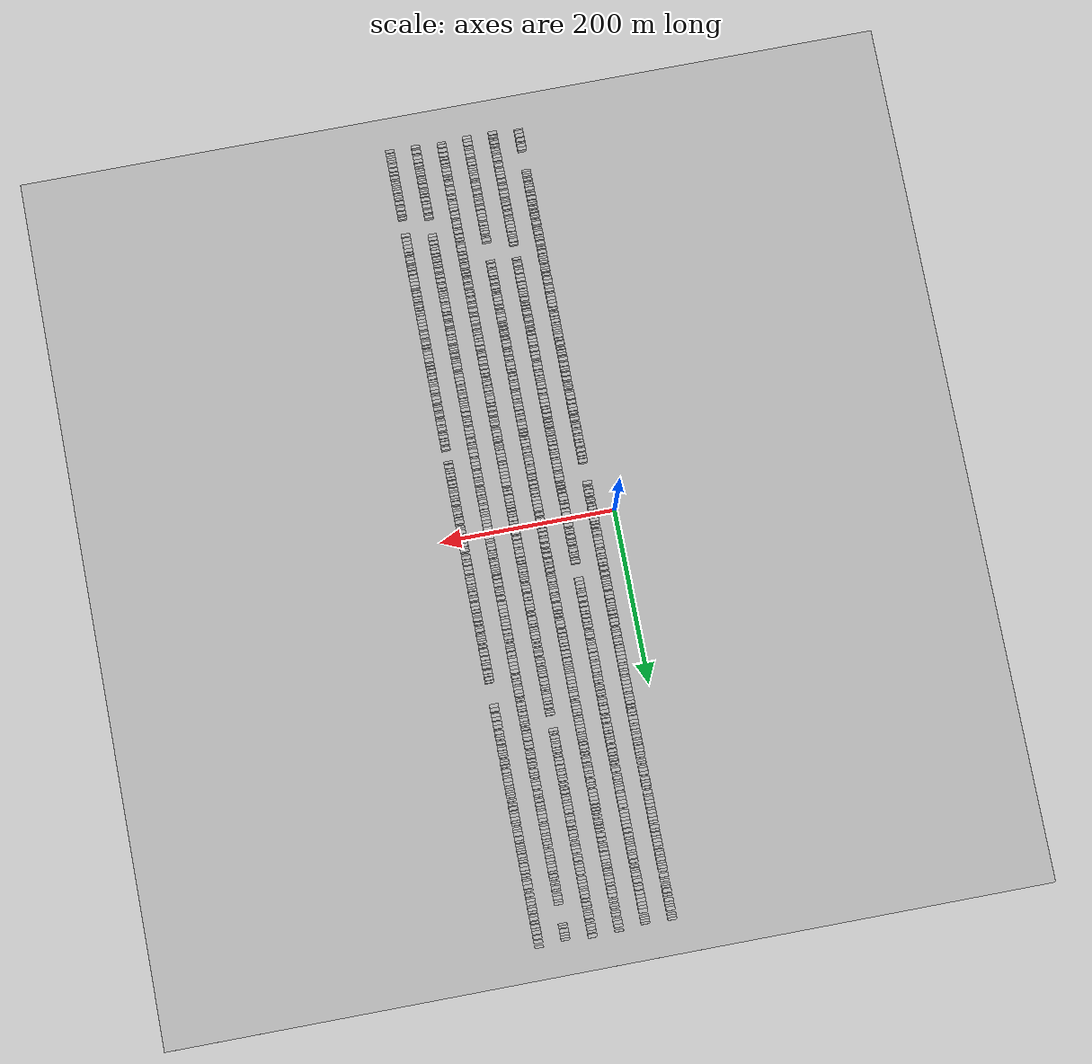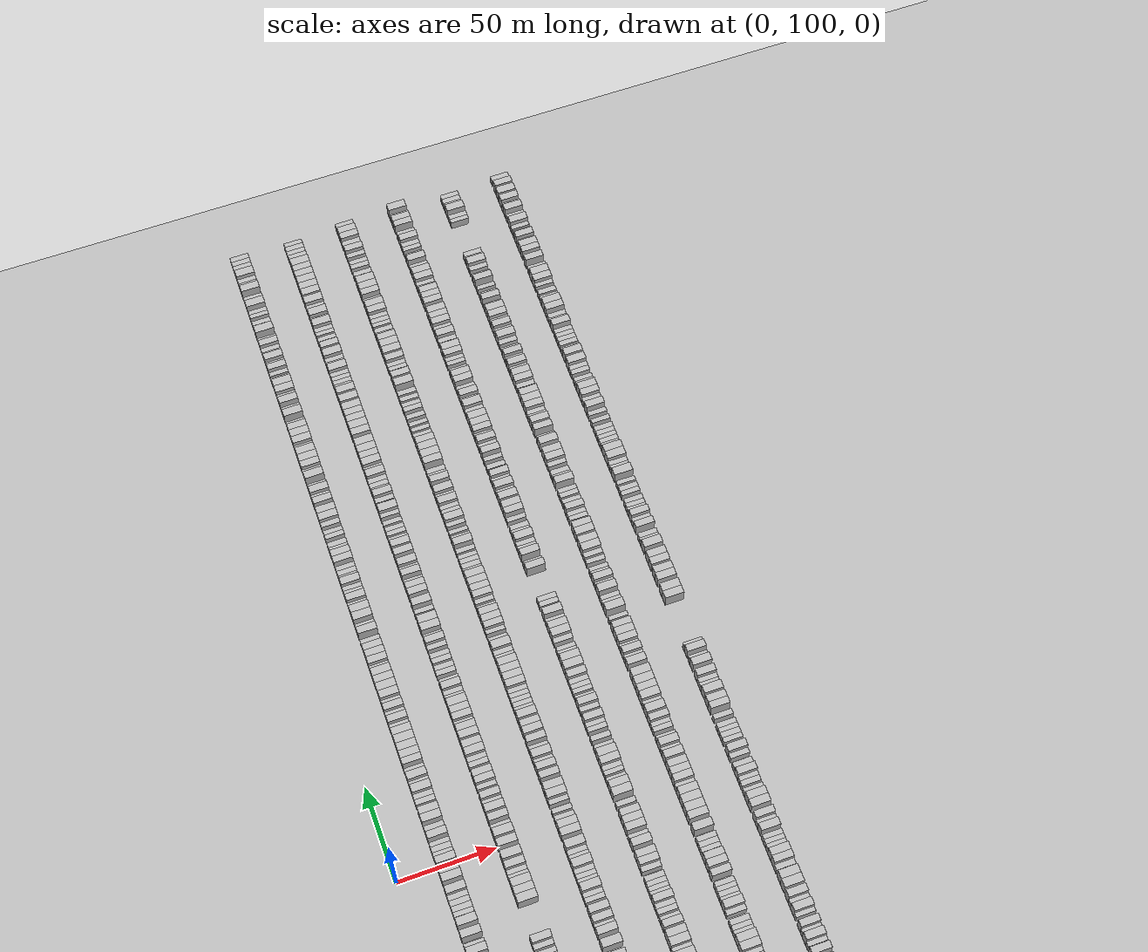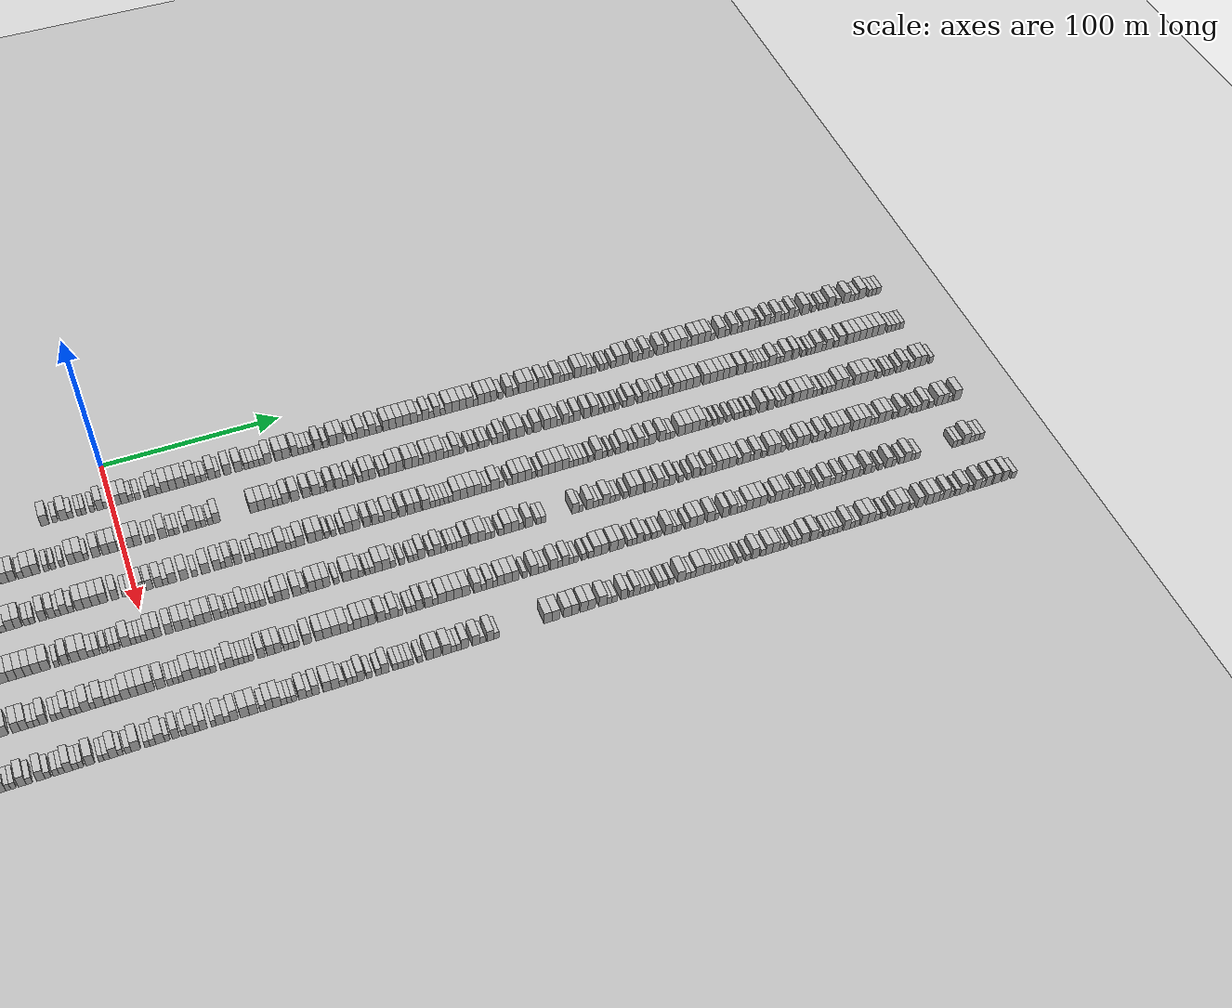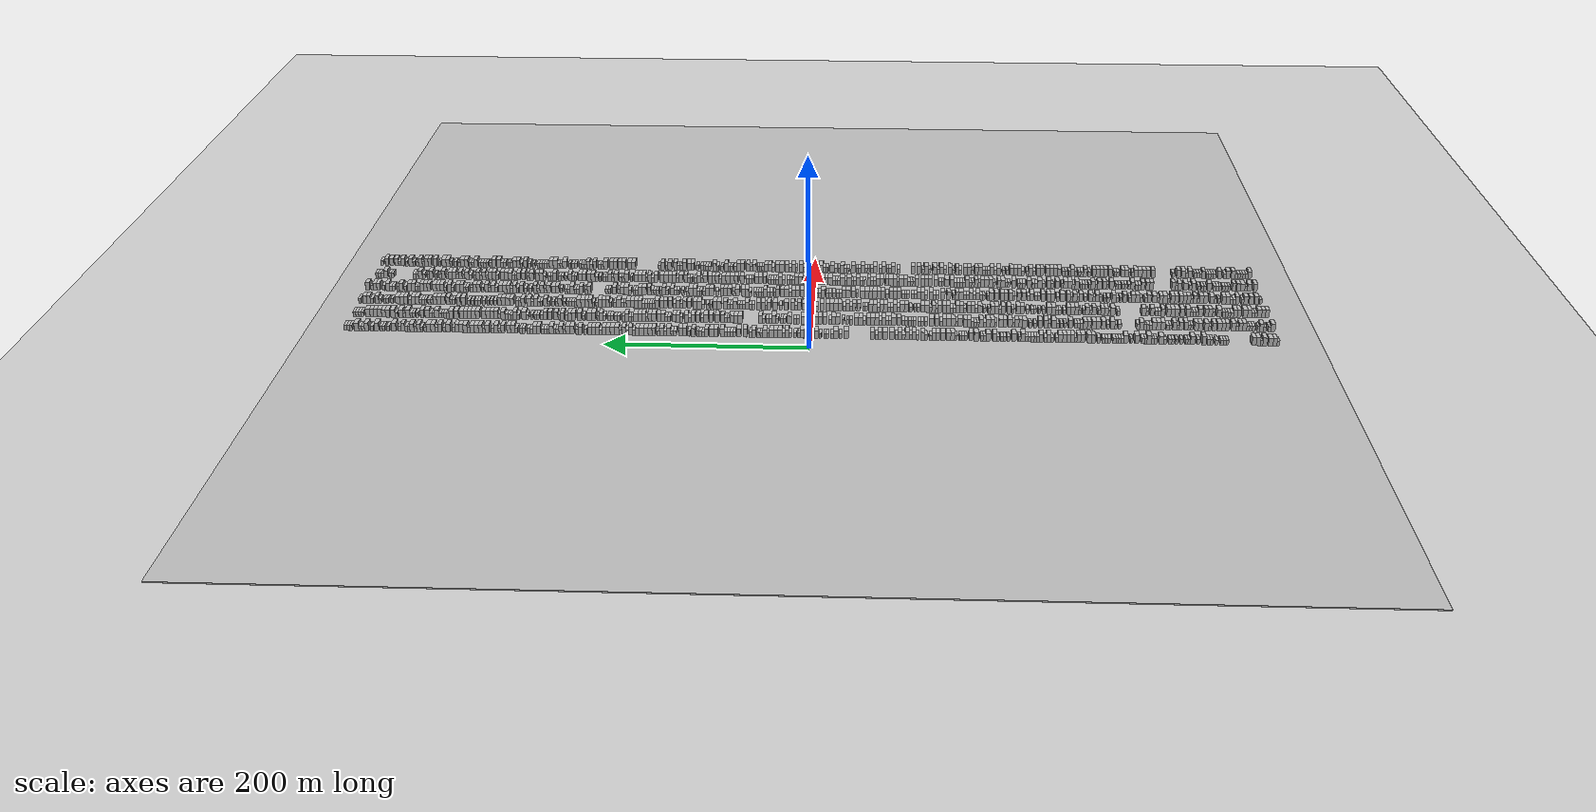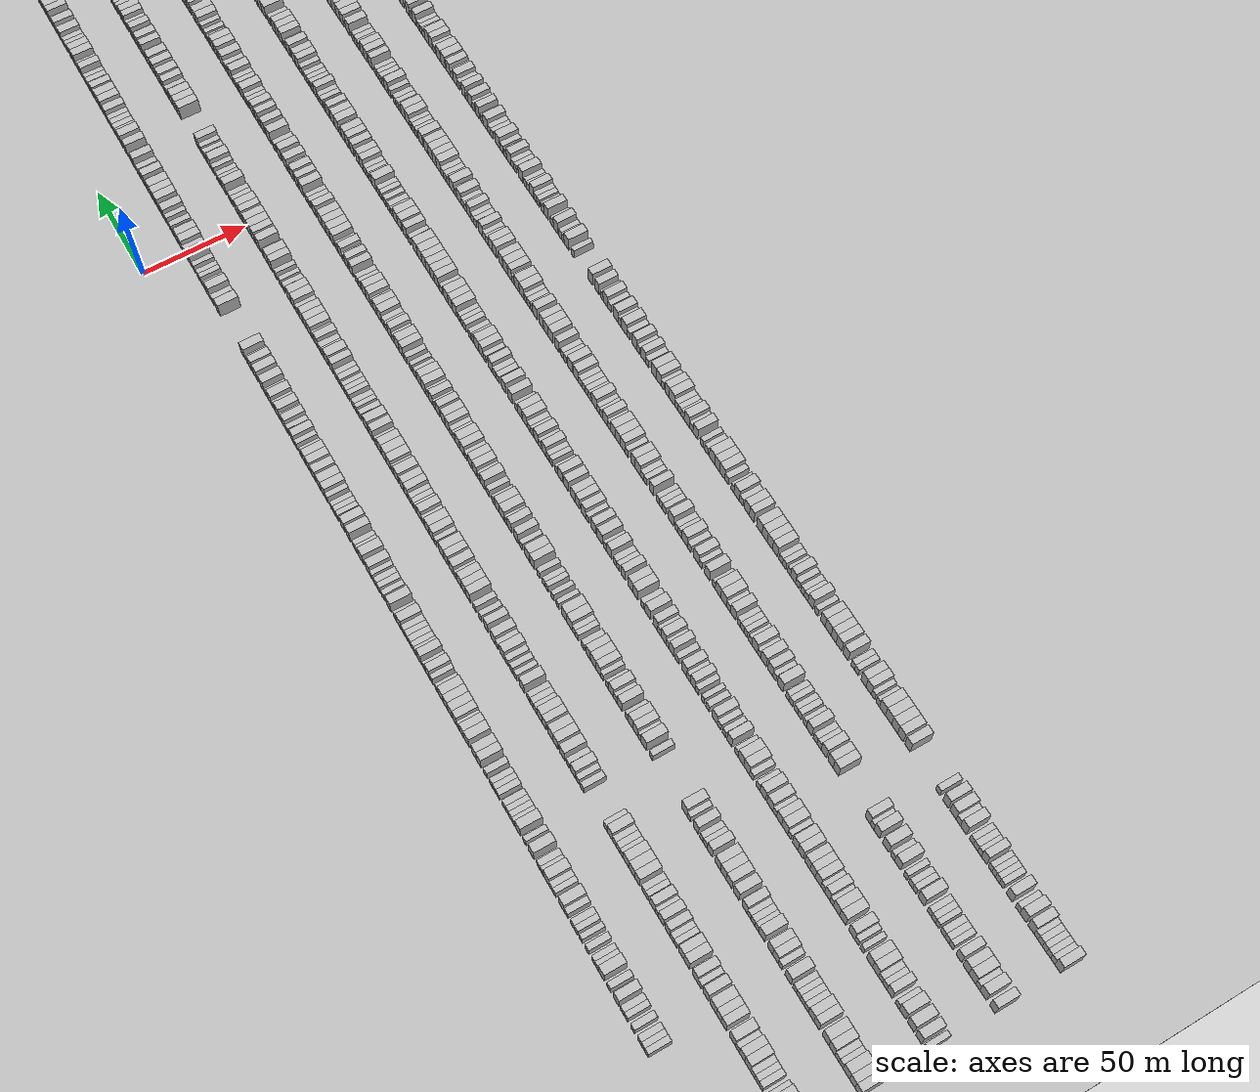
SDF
<sdf version="1.6">
 <world name="default">
  <scene>
   <sky><clouds><speed>12</speed></clouds></sky>
   <ambient>0.4 0.4 0.4 1</ambient>
   <background>0.7 0.7 0.7 1</background>
   <shadows>1</shadows>
  </scene>
  <gravity>0 0 -9.8066</gravity>
  <magnetic_field>6e-06 2.3e-05 -4.2e-05</magnetic_field>
  <physics default="0" name="default_physics" type="ode">
   <ode>
    <solver>
     <type>quick</type>
     <iters>10</iters>
     <sor>1.0</sor>
     <use_dynamic_moi_rescaling>0</use_dynamic_moi_rescaling>
    </solver>
    <constraints>
     <cfm>0</cfm>
     <erp>0.2</erp>
     <contact_max_correcting_vel>100</contact_max_correcting_vel>
     <contact_surface_layer>0.001</contact_surface_layer>
    </constraints>
   </ode>
   <max_step_size>0.004</max_step_size>
   <real_time_factor>1</real_time_factor>
   <real_time_update_rate>250</real_time_update_rate>
  </physics>
  <light name="sun" type="directional">
   <pose>0 0 10 0 0 0</pose>
   <diffuse>0.8 0.8 0.8 1</diffuse>
   <specular>0.2 0.2 0.2 1</specular>
   <attenuation>
    <range>1000</range>
    <constant>0.9</constant>
    <linear>0.01</linear>
    <quadratic>0.001</quadratic>
   </attenuation>
   <direction>-0.5 0.1 -0.9</direction>
  </light>
  <include><name>ground_plane_1</name><uri>model://HANNAS_ground_plane</uri></include>
  <include>
   <name>ground_plane_2</name>
   <uri>model://HANNAS_ground_plane</uri>
   <pose>100 0 0  0 0 0</pose>
  </include>
  <model name="building_1">
   <static>1</static>
   <pose>25.0000 -456.7684 0 0.000000 0.000000 0.000000</pose>
   <link name="link">
    <pose>0 0 3.00 0 0 0</pose>
    <collision name="collision"><geometry><box><size>10.0000 2.4633 6.0000</size></box></geometry></collision>
    <visual name="visual">
     <cast_shadows>0</cast_shadows>
     <geometry><box><size>10.0000 2.4633 6.0000</size></box></geometry>
     <material>
      <script>
       <uri>model://HANNAS_wall/materials/scripts</uri>
       <uri>model://HANNAS_wall/materials/textures</uri>
       <name>vrc/HANNAS_wall</name>
      </script>
     </material>
    </visual>
   </link>
  </model>
  <model name="building_2">
   <static>1</static>
   <pose>25.0000 -453.5945 0 0.000000 0.000000 0.000000</pose>
   <link name="link">
    <pose>0 0 4.50 0 0 0</pose>
    <collision name="collision"><geometry><box><size>10.0000 3.8844 9.0000</size></box></geometry></collision>
    <visual name="visual">
     <cast_shadows>0</cast_shadows>
     <geometry><box><size>10.0000 3.8844 9.0000</size></box></geometry>
     <material>
      <script>
       <uri>model://HANNAS_wall/materials/scripts</uri>
       <uri>model://HANNAS_wall/materials/textures</uri>
       <name>vrc/HANNAS_wall</name>
      </script>
     </material>
    </visual>
   </link>
  </model>
  <model name="building_3">
   <static>1</static>
   <pose>25.0000 -449.4505 0 0.000000 0.000000 0.000000</pose>
   <link name="link">
    <pose>0 0 4.50 0 0 0</pose>
    <collision name="collision"><geometry><box><size>10.0000 4.4035 9.0000</size></box></geometry></collision>
    <visual name="visual">
     <cast_shadows>0</cast_shadows>
     <geometry><box><size>10.0000 4.4035 9.0000</size></box></geometry>
     <material>
      <script>
       <uri>model://HANNAS_wall/materials/scripts</uri>
       <uri>model://HANNAS_wall/materials/textures</uri>
       <name>vrc/HANNAS_wall</name>
      </script>
     </material>
    </visual>
   </link>
  </model>
  <model name="building_4">
   <static>1</static>
   <pose>25.0000 -444.0910 0 0.000000 0.000000 0.000000</pose>
   <link name="link">
    <pose>0 0 4.50 0 0 0</pose>
    <collision name="collision"><geometry><box><size>10.0000 4.3155 9.0000</size></box></geometry></collision>
    <visual name="visual">
     <cast_shadows>0</cast_shadows>
     <geometry><box><size>10.0000 4.3155 9.0000</size></box></geometry>
     <material>
      <script>
       <uri>model://HANNAS_wall/materials/scripts</uri>
       <uri>model://HANNAS_wall/materials/textures</uri>
       <name>vrc/HANNAS_wall</name>
      </script>
     </material>
    </visual>
   </link>
  </model>
  <model name="building_5">
   <static>1</static>
   <pose>25.0000 -440.7142 0 0.000000 0.000000 0.000000</pose>
   <link name="link">
    <pose>0 0 3.00 0 0 0</pose>
    <collision name="collision"><geometry><box><size>10.0000 2.4382 6.0000</size></box></geometry></collision>
    <visual name="visual">
     <cast_shadows>0</cast_shadows>
     <geometry><box><size>10.0000 2.4382 6.0000</size></box></geometry>
     <material>
      <script>
       <uri>model://HANNAS_wall/materials/scripts</uri>
       <uri>model://HANNAS_wall/materials/textures</uri>
       <name>vrc/HANNAS_wall</name>
      </script>
     </material>
    </visual>
   </link>
  </model>
  <model name="building_6">
   <static>1</static>
   <pose>25.0000 -437.4608 0 0.000000 0.000000 0.000000</pose>
   <link name="link">
    <pose>0 0 4.50 0 0 0</pose>
    <collision name="collision"><geometry><box><size>10.0000 4.0685 9.0000</size></box></geometry></collision>
    <visual name="visual">
     <cast_shadows>0</cast_shadows>
     <geometry><box><size>10.0000 4.0685 9.0000</size></box></geometry>
     <material>
      <script>
       <uri>model://HANNAS_wall/materials/scripts</uri>
       <uri>model://HANNAS_wall/materials/textures</uri>
       <name>vrc/HANNAS_wall</name>
      </script>
     </material>
    </visual>
   </link>
  </model>
  <model name="building_7">
   <static>1</static>
   <pose>25.0000 -433.4576 0 0.000000 0.000000 0.000000</pose>
   <link name="link">
    <pose>0 0 4.50 0 0 0</pose>
    <collision name="collision"><geometry><box><size>10.0000 3.9378 9.0000</size></box></geometry></collision>
    <visual name="visual">
     <cast_shadows>0</cast_shadows>
     <geometry><box><size>10.0000 3.9378 9.0000</size></box></geometry>
     <material>
      <script>
       <uri>model://HANNAS_wall/materials/scripts</uri>
       <uri>model://HANNAS_wall/materials/textures</uri>
       <name>vrc/HANNAS_wall</name>
      </script>
     </material>
    </visual>
   </link>
  </model>
  <model name="building_8">
   <static>1</static>
   <pose>25.0000 -407.5464 0 0.000000 0.000000 0.000000</pose>
   <link name="link">
    <pose>0 0 3.00 0 0 0</pose>
    <collision name="collision"><geometry><box><size>10.0000 2.6282 6.0000</size></box></geometry></collision>
    <visual name="visual">
     <cast_shadows>0</cast_shadows>
     <geometry><box><size>10.0000 2.6282 6.0000</size></box></geometry>
     <material>
      <script>
       <uri>model://HANNAS_wall/materials/scripts</uri>
       <uri>model://HANNAS_wall/materials/textures</uri>
       <name>vrc/HANNAS_wall</name>
      </script>
     </material>
    </visual>
   </link>
  </model>
  <model name="building_9">
   <static>1</static>
   <pose>25.0000 -404.9177 0 0.000000 0.000000 0.000000</pose>
   <link name="link">
    <pose>0 0 3.00 0 0 0</pose>
    <collision name="collision"><geometry><box><size>10.0000 2.6292 6.0000</size></box></geometry></collision>
    <visual name="visual">
     <cast_shadows>0</cast_shadows>
     <geometry><box><size>10.0000 2.6292 6.0000</size></box></geometry>
     <material>
      <script>
       <uri>model://HANNAS_wall/materials/scripts</uri>
       <uri>model://HANNAS_wall/materials/textures</uri>
       <name>vrc/HANNAS_wall</name>
      </script>
     </material>
    </visual>
   </link>
  </model>
  <model name="building_10">
   <static>1</static>
   <pose>25.0000 -402.1576 0 0.000000 0.000000 0.000000</pose>
   <link name="link">
    <pose>0 0 3.00 0 0 0</pose>
    <collision name="collision"><geometry><box><size>10.0000 2.8910 6.0000</size></box></geometry></collision>
    <visual name="visual">
     <cast_shadows>0</cast_shadows>
     <geometry><box><size>10.0000 2.8910 6.0000</size></box></geometry>
     <material>
      <script>
       <uri>model://HANNAS_wall/materials/scripts</uri>
       <uri>model://HANNAS_wall/materials/textures</uri>
       <name>vrc/HANNAS_wall</name>
      </script>
     </material>
    </visual>
   </link>
  </model>
  <model name="building_11">
   <static>1</static>
   <pose>25.0000 -397.2195 0 0.000000 0.000000 0.000000</pose>
   <link name="link">
    <pose>0 0 3.00 0 0 0</pose>
    <collision name="collision"><geometry><box><size>10.0000 2.9851 6.0000</size></box></geometry></collision>
    <visual name="visual">
     <cast_shadows>0</cast_shadows>
     <geometry><box><size>10.0000 2.9851 6.0000</size></box></geometry>
     <material>
      <script>
       <uri>model://HANNAS_wall/materials/scripts</uri>
       <uri>model://HANNAS_wall/materials/textures</uri>
       <name>vrc/HANNAS_wall</name>
      </script>
     </material>
    </visual>
   </link>
  </model>
  <model name="building_12">
   <static>1</static>
   <pose>25.0000 -392.4356 0 0.000000 0.000000 0.000000</pose>
   <link name="link">
    <pose>0 0 3.00 0 0 0</pose>
    <collision name="collision"><geometry><box><size>10.0000 2.5829 6.0000</size></box></geometry></collision>
    <visual name="visual">
     <cast_shadows>0</cast_shadows>
     <geometry><box><size>10.0000 2.5829 6.0000</size></box></geometry>
     <material>
      <script>
       <uri>model://HANNAS_wall/materials/scripts</uri>
       <uri>model://HANNAS_wall/materials/textures</uri>
       <name>vrc/HANNAS_wall</name>
      </script>
     </material>
    </visual>
   </link>
  </model>
  <model name="building_13">
   <static>1</static>
   <pose>25.0000 -389.6625 0 0.000000 0.000000 0.000000</pose>
   <link name="link">
    <pose>0 0 3.00 0 0 0</pose>
    <collision name="collision"><geometry><box><size>10.0000 2.9632 6.0000</size></box></geometry></collision>
    <visual name="visual">
     <cast_shadows>0</cast_shadows>
     <geometry><box><size>10.0000 2.9632 6.0000</size></box></geometry>
     <material>
      <script>
       <uri>model://HANNAS_wall/materials/scripts</uri>
       <uri>model://HANNAS_wall/materials/textures</uri>
       <name>vrc/HANNAS_wall</name>
      </script>
     </material>
    </visual>
   </link>
  </model>
  <model name="building_14">
   <static>1</static>
   <pose>25.0000 -385.1881 0 0.000000 0.000000 0.000000</pose>
   <link name="link">
    <pose>0 0 4.50 0 0 0</pose>
    <collision name="collision"><geometry><box><size>10.0000 3.9857 9.0000</size></box></geometry></collision>
    <visual name="visual">
     <cast_shadows>0</cast_shadows>
     <geometry><box><size>10.0000 3.9857 9.0000</size></box></geometry>
     <material>
      <script>
       <uri>model://HANNAS_wall/materials/scripts</uri>
       <uri>model://HANNAS_wall/materials/textures</uri>
       <name>vrc/HANNAS_wall</name>
      </script>
     </material>
    </visual>
   </link>
  </model>
  <model name="building_15">
   <static>1</static>
   <pose>25.0000 -379.7140 0 0.000000 0.000000 0.000000</pose>
   <link name="link">
    <pose>0 0 3.00 0 0 0</pose>
    <collision name="collision"><geometry><box><size>10.0000 2.9623 6.0000</size></box></geometry></collision>
    <visual name="visual">
     <cast_shadows>0</cast_shadows>
     <geometry><box><size>10.0000 2.9623 6.0000</size></box></geometry>
     <material>
      <script>
       <uri>model://HANNAS_wall/materials/scripts</uri>
       <uri>model://HANNAS_wall/materials/textures</uri>
       <name>vrc/HANNAS_wall</name>
      </script>
     </material>
    </visual>
   </link>
  </model>
  <model name="building_16">
   <static>1</static>
   <pose>25.0000 -374.0256 0 0.000000 0.000000 0.000000</pose>
   <link name="link">
    <pose>0 0 4.50 0 0 0</pose>
    <collision name="collision"><geometry><box><size>10.0000 4.4146 9.0000</size></box></geometry></collision>
    <visual name="visual">
     <cast_shadows>0</cast_shadows>
     <geometry><box><size>10.0000 4.4146 9.0000</size></box></geometry>
     <material>
      <script>
       <uri>model://HANNAS_wall/materials/scripts</uri>
       <uri>model://HANNAS_wall/materials/textures</uri>
       <name>vrc/HANNAS_wall</name>
      </script>
     </material>
    </visual>
   </link>
  </model>
  <model name="building_17">
   <static>1</static>
   <pose>25.0000 -370.5286 0 0.000000 0.000000 0.000000</pose>
   <link name="link">
    <pose>0 0 3.00 0 0 0</pose>
    <collision name="collision"><geometry><box><size>10.0000 2.5793 6.0000</size></box></geometry></collision>
    <visual name="visual">
     <cast_shadows>0</cast_shadows>
     <geometry><box><size>10.0000 2.5793 6.0000</size></box></geometry>
     <material>
      <script>
       <uri>model://HANNAS_wall/materials/scripts</uri>
       <uri>model://HANNAS_wall/materials/textures</uri>
       <name>vrc/HANNAS_wall</name>
      </script>
     </material>
    </visual>
   </link>
  </model>
  <model name="building_18">
   <static>1</static>
   <pose>25.0000 -367.9509 0 0.000000 0.000000 0.000000</pose>
   <link name="link">
    <pose>0 0 3.00 0 0 0</pose>
    <collision name="collision"><geometry><box><size>10.0000 2.5762 6.0000</size></box></geometry></collision>
    <visual name="visual">
     <cast_shadows>0</cast_shadows>
     <geometry><box><size>10.0000 2.5762 6.0000</size></box></geometry>
     <material>
      <script>
       <uri>model://HANNAS_wall/materials/scripts</uri>
       <uri>model://HANNAS_wall/materials/textures</uri>
       <name>vrc/HANNAS_wall</name>
      </script>
     </material>
    </visual>
   </link>
  </model>
  <model name="building_19">
   <static>1</static>
   <pose>25.0000 -363.2097 0 0.000000 0.000000 0.000000</pose>
   <link name="link">
    <pose>0 0 3.00 0 0 0</pose>
    <collision name="collision"><geometry><box><size>10.0000 2.9062 6.0000</size></box></geometry></collision>
    <visual name="visual">
     <cast_shadows>0</cast_shadows>
     <geometry><box><size>10.0000 2.9062 6.0000</size></box></geometry>
     <material>
      <script>
       <uri>model://HANNAS_wall/materials/scripts</uri>
       <uri>model://HANNAS_wall/materials/textures</uri>
       <name>vrc/HANNAS_wall</name>
      </script>
     </material>
    </visual>
   </link>
  </model>
  <model name="building_20">
   <static>1</static>
   <pose>25.0000 -358.5313 0 0.000000 0.000000 0.000000</pose>
   <link name="link">
    <pose>0 0 3.00 0 0 0</pose>
    <collision name="collision"><geometry><box><size>10.0000 2.4505 6.0000</size></box></geometry></collision>
    <visual name="visual">
     <cast_shadows>0</cast_shadows>
     <geometry><box><size>10.0000 2.4505 6.0000</size></box></geometry>
     <material>
      <script>
       <uri>model://HANNAS_wall/materials/scripts</uri>
       <uri>model://HANNAS_wall/materials/textures</uri>
       <name>vrc/HANNAS_wall</name>
      </script>
     </material>
    </visual>
   </link>
  </model>
  <model name="building_21">
   <static>1</static>
   <pose>25.0000 -354.9608 0 0.000000 0.000000 0.000000</pose>
   <link name="link">
    <pose>0 0 3.00 0 0 0</pose>
    <collision name="collision"><geometry><box><size>10.0000 2.6905 6.0000</size></box></geometry></collision>
    <visual name="visual">
     <cast_shadows>0</cast_shadows>
     <geometry><box><size>10.0000 2.6905 6.0000</size></box></geometry>
     <material>
      <script>
       <uri>model://HANNAS_wall/materials/scripts</uri>
       <uri>model://HANNAS_wall/materials/textures</uri>
       <name>vrc/HANNAS_wall</name>
      </script>
     </material>
    </visual>
   </link>
  </model>
  <model name="building_22">
   <static>1</static>
   <pose>25.0000 -352.1354 0 0.000000 0.000000 0.000000</pose>
   <link name="link">
    <pose>0 0 3.00 0 0 0</pose>
    <collision name="collision"><geometry><box><size>10.0000 2.9602 6.0000</size></box></geometry></collision>
    <visual name="visual">
     <cast_shadows>0</cast_shadows>
     <geometry><box><size>10.0000 2.9602 6.0000</size></box></geometry>
     <material>
      <script>
       <uri>model://HANNAS_wall/materials/scripts</uri>
       <uri>model://HANNAS_wall/materials/textures</uri>
       <name>vrc/HANNAS_wall</name>
      </script>
     </material>
    </visual>
   </link>
  </model>
  <model name="building_23">
   <static>1</static>
   <pose>25.0000 -347.2281 0 0.000000 0.000000 0.000000</pose>
   <link name="link">
    <pose>0 0 3.00 0 0 0</pose>
    <collision name="collision"><geometry><box><size>10.0000 2.8545 6.0000</size></box></geometry></collision>
    <visual name="visual">
     <cast_shadows>0</cast_shadows>
     <geometry><box><size>10.0000 2.8545 6.0000</size></box></geometry>
     <material>
      <script>
       <uri>model://HANNAS_wall/materials/scripts</uri>
       <uri>model://HANNAS_wall/materials/textures</uri>
       <name>vrc/HANNAS_wall</name>
      </script>
     </material>
    </visual>
   </link>
  </model>
  <model name="building_24">
   <static>1</static>
   <pose>25.0000 -343.5689 0 0.000000 0.000000 0.000000</pose>
   <link name="link">
    <pose>0 0 4.50 0 0 0</pose>
    <collision name="collision"><geometry><box><size>10.0000 4.4639 9.0000</size></box></geometry></collision>
    <visual name="visual">
     <cast_shadows>0</cast_shadows>
     <geometry><box><size>10.0000 4.4639 9.0000</size></box></geometry>
     <material>
      <script>
       <uri>model://HANNAS_wall/materials/scripts</uri>
       <uri>model://HANNAS_wall/materials/textures</uri>
       <name>vrc/HANNAS_wall</name>
      </script>
     </material>
    </visual>
   </link>
  </model>
  <model name="building_25">
   <static>1</static>
   <pose>25.0000 -338.0818 0 0.000000 0.000000 0.000000</pose>
   <link name="link">
    <pose>0 0 3.00 0 0 0</pose>
    <collision name="collision"><geometry><box><size>10.0000 2.5103 6.0000</size></box></geometry></collision>
    <visual name="visual">
     <cast_shadows>0</cast_shadows>
     <geometry><box><size>10.0000 2.5103 6.0000</size></box></geometry>
     <material>
      <script>
       <uri>model://HANNAS_wall/materials/scripts</uri>
       <uri>model://HANNAS_wall/materials/textures</uri>
       <name>vrc/HANNAS_wall</name>
      </script>
     </material>
    </visual>
   </link>
  </model>
  <model name="building_26">
   <static>1</static>
   <pose>25.0000 -335.4188 0 0.000000 0.000000 0.000000</pose>
   <link name="link">
    <pose>0 0 3.00 0 0 0</pose>
    <collision name="collision"><geometry><box><size>10.0000 2.8156 6.0000</size></box></geometry></collision>
    <visual name="visual">
     <cast_shadows>0</cast_shadows>
     <geometry><box><size>10.0000 2.8156 6.0000</size></box></geometry>
     <material>
      <script>
       <uri>model://HANNAS_wall/materials/scripts</uri>
       <uri>model://HANNAS_wall/materials/textures</uri>
       <name>vrc/HANNAS_wall</name>
      </script>
     </material>
    </visual>
   </link>
  </model>
  <model name="building_27">
   <static>1</static>
   <pose>25.0000 -331.8076 0 0.000000 0.000000 0.000000</pose>
   <link name="link">
    <pose>0 0 4.50 0 0 0</pose>
    <collision name="collision"><geometry><box><size>10.0000 4.4070 9.0000</size></box></geometry></collision>
    <visual name="visual">
     <cast_shadows>0</cast_shadows>
     <geometry><box><size>10.0000 4.4070 9.0000</size></box></geometry>
     <material>
      <script>
       <uri>model://HANNAS_wall/materials/scripts</uri>
       <uri>model://HANNAS_wall/materials/textures</uri>
       <name>vrc/HANNAS_wall</name>
      </script>
     </material>
    </visual>
   </link>
  </model>
  <model name="building_28">
   <static>1</static>
   <pose>25.0000 -328.3878 0 0.000000 0.000000 0.000000</pose>
   <link name="link">
    <pose>0 0 3.00 0 0 0</pose>
    <collision name="collision"><geometry><box><size>10.0000 2.4326 6.0000</size></box></geometry></collision>
    <visual name="visual">
     <cast_shadows>0</cast_shadows>
     <geometry><box><size>10.0000 2.4326 6.0000</size></box></geometry>
     <material>
      <script>
       <uri>model://HANNAS_wall/materials/scripts</uri>
       <uri>model://HANNAS_wall/materials/textures</uri>
       <name>vrc/HANNAS_wall</name>
      </script>
     </material>
    </visual>
   </link>
  </model>
  <model name="building_29">
   <static>1</static>
   <pose>25.0000 -325.6824 0 0.000000 0.000000 0.000000</pose>
   <link name="link">
    <pose>0 0 3.00 0 0 0</pose>
    <collision name="collision"><geometry><box><size>10.0000 2.9783 6.0000</size></box></geometry></collision>
    <visual name="visual">
     <cast_shadows>0</cast_shadows>
     <geometry><box><size>10.0000 2.9783 6.0000</size></box></geometry>
     <material>
      <script>
       <uri>model://HANNAS_wall/materials/scripts</uri>
       <uri>model://HANNAS_wall/materials/textures</uri>
       <name>vrc/HANNAS_wall</name>
      </script>
     </material>
    </visual>
   </link>
  </model>
  <model name="building_30">
   <static>1</static>
   <pose>25.0000 -320.0331 0 0.000000 0.000000 0.000000</pose>
   <link name="link">
    <pose>0 0 4.50 0 0 0</pose>
    <collision name="collision"><geometry><box><size>10.0000 4.3201 9.0000</size></box></geometry></collision>
    <visual name="visual">
     <cast_shadows>0</cast_shadows>
     <geometry><box><size>10.0000 4.3201 9.0000</size></box></geometry>
     <material>
      <script>
       <uri>model://HANNAS_wall/materials/scripts</uri>
       <uri>model://HANNAS_wall/materials/textures</uri>
       <name>vrc/HANNAS_wall</name>
      </script>
     </material>
    </visual>
   </link>
  </model>
  <model name="building_31">
   <static>1</static>
   <pose>25.0000 -314.6101 0 0.000000 0.000000 0.000000</pose>
   <link name="link">
    <pose>0 0 3.00 0 0 0</pose>
    <collision name="collision"><geometry><box><size>10.0000 2.5259 6.0000</size></box></geometry></collision>
    <visual name="visual">
     <cast_shadows>0</cast_shadows>
     <geometry><box><size>10.0000 2.5259 6.0000</size></box></geometry>
     <material>
      <script>
       <uri>model://HANNAS_wall/materials/scripts</uri>
       <uri>model://HANNAS_wall/materials/textures</uri>
       <name>vrc/HANNAS_wall</name>
      </script>
     </material>
    </visual>
   </link>
  </model>
  <model name="building_32">
   <static>1</static>
   <pose>25.0000 -309.2522 0 0.000000 0.000000 0.000000</pose>
   <link name="link">
    <pose>0 0 4.50 0 0 0</pose>
    <collision name="collision"><geometry><box><size>10.0000 4.1900 9.0000</size></box></geometry></collision>
    <visual name="visual">
     <cast_shadows>0</cast_shadows>
     <geometry><box><size>10.0000 4.1900 9.0000</size></box></geometry>
     <material>
      <script>
       <uri>model://HANNAS_wall/materials/scripts</uri>
       <uri>model://HANNAS_wall/materials/textures</uri>
       <name>vrc/HANNAS_wall</name>
      </script>
     </material>
    </visual>
   </link>
  </model>
  <model name="building_33">
   <static>1</static>
   <pose>25.0000 -305.8364 0 0.000000 0.000000 0.000000</pose>
   <link name="link">
    <pose>0 0 3.00 0 0 0</pose>
    <collision name="collision"><geometry><box><size>10.0000 2.6414 6.0000</size></box></geometry></collision>
    <visual name="visual">
     <cast_shadows>0</cast_shadows>
     <geometry><box><size>10.0000 2.6414 6.0000</size></box></geometry>
     <material>
      <script>
       <uri>model://HANNAS_wall/materials/scripts</uri>
       <uri>model://HANNAS_wall/materials/textures</uri>
       <name>vrc/HANNAS_wall</name>
      </script>
     </material>
    </visual>
   </link>
  </model>
  <model name="building_34">
   <static>1</static>
   <pose>25.0000 -303.2210 0 0.000000 0.000000 0.000000</pose>
   <link name="link">
    <pose>0 0 3.00 0 0 0</pose>
    <collision name="collision"><geometry><box><size>10.0000 2.5894 6.0000</size></box></geometry></collision>
    <visual name="visual">
     <cast_shadows>0</cast_shadows>
     <geometry><box><size>10.0000 2.5894 6.0000</size></box></geometry>
     <material>
      <script>
       <uri>model://HANNAS_wall/materials/scripts</uri>
       <uri>model://HANNAS_wall/materials/textures</uri>
       <name>vrc/HANNAS_wall</name>
      </script>
     </material>
    </visual>
   </link>
  </model>
  <model name="building_35">
   <static>1</static>
   <pose>25.0000 -300.7022 0 0.000000 0.000000 0.000000</pose>
   <link name="link">
    <pose>0 0 3.00 0 0 0</pose>
    <collision name="collision"><geometry><box><size>10.0000 2.4482 6.0000</size></box></geometry></collision>
    <visual name="visual">
     <cast_shadows>0</cast_shadows>
     <geometry><box><size>10.0000 2.4482 6.0000</size></box></geometry>
     <material>
      <script>
       <uri>model://HANNAS_wall/materials/scripts</uri>
       <uri>model://HANNAS_wall/materials/textures</uri>
       <name>vrc/HANNAS_wall</name>
      </script>
     </material>
    </visual>
   </link>
  </model>
  <model name="building_36">
   <static>1</static>
   <pose>25.0000 -298.0073 0 0.000000 0.000000 0.000000</pose>
   <link name="link">
    <pose>0 0 3.00 0 0 0</pose>
    <collision name="collision"><geometry><box><size>10.0000 2.9417 6.0000</size></box></geometry></collision>
    <visual name="visual">
     <cast_shadows>0</cast_shadows>
     <geometry><box><size>10.0000 2.9417 6.0000</size></box></geometry>
     <material>
      <script>
       <uri>model://HANNAS_wall/materials/scripts</uri>
       <uri>model://HANNAS_wall/materials/textures</uri>
       <name>vrc/HANNAS_wall</name>
      </script>
     </material>
    </visual>
   </link>
  </model>
  <model name="building_37">
   <static>1</static>
   <pose>25.0000 -293.0573 0 0.000000 0.000000 0.000000</pose>
   <link name="link">
    <pose>0 0 3.00 0 0 0</pose>
    <collision name="collision"><geometry><box><size>10.0000 2.9581 6.0000</size></box></geometry></collision>
    <visual name="visual">
     <cast_shadows>0</cast_shadows>
     <geometry><box><size>10.0000 2.9581 6.0000</size></box></geometry>
     <material>
      <script>
       <uri>model://HANNAS_wall/materials/scripts</uri>
       <uri>model://HANNAS_wall/materials/textures</uri>
       <name>vrc/HANNAS_wall</name>
      </script>
     </material>
    </visual>
   </link>
  </model>
  <model name="building_38">
   <static>1</static>
   <pose>25.0000 -290.2977 0 0.000000 0.000000 0.000000</pose>
   <link name="link">
    <pose>0 0 3.00 0 0 0</pose>
    <collision name="collision"><geometry><box><size>10.0000 2.5612 6.0000</size></box></geometry></collision>
    <visual name="visual">
     <cast_shadows>0</cast_shadows>
     <geometry><box><size>10.0000 2.5612 6.0000</size></box></geometry>
     <material>
      <script>
       <uri>model://HANNAS_wall/materials/scripts</uri>
       <uri>model://HANNAS_wall/materials/textures</uri>
       <name>vrc/HANNAS_wall</name>
      </script>
     </material>
    </visual>
   </link>
  </model>
  <model name="building_39">
   <static>1</static>
   <pose>25.0000 -287.6836 0 0.000000 0.000000 0.000000</pose>
   <link name="link">
    <pose>0 0 3.00 0 0 0</pose>
    <collision name="collision"><geometry><box><size>10.0000 2.6669 6.0000</size></box></geometry></collision>
    <visual name="visual">
     <cast_shadows>0</cast_shadows>
     <geometry><box><size>10.0000 2.6669 6.0000</size></box></geometry>
     <material>
      <script>
       <uri>model://HANNAS_wall/materials/scripts</uri>
       <uri>model://HANNAS_wall/materials/textures</uri>
       <name>vrc/HANNAS_wall</name>
      </script>
     </material>
    </visual>
   </link>
  </model>
  <model name="building_40">
   <static>1</static>
   <pose>25.0000 -282.8744 0 0.000000 0.000000 0.000000</pose>
   <link name="link">
    <pose>0 0 3.00 0 0 0</pose>
    <collision name="collision"><geometry><box><size>10.0000 2.9515 6.0000</size></box></geometry></collision>
    <visual name="visual">
     <cast_shadows>0</cast_shadows>
     <geometry><box><size>10.0000 2.9515 6.0000</size></box></geometry>
     <material>
      <script>
       <uri>model://HANNAS_wall/materials/scripts</uri>
       <uri>model://HANNAS_wall/materials/textures</uri>
       <name>vrc/HANNAS_wall</name>
      </script>
     </material>
    </visual>
   </link>
  </model>
  <model name="building_41">
   <static>1</static>
   <pose>25.0000 -277.4504 0 0.000000 0.000000 0.000000</pose>
   <link name="link">
    <pose>0 0 4.50 0 0 0</pose>
    <collision name="collision"><geometry><box><size>10.0000 3.8964 9.0000</size></box></geometry></collision>
    <visual name="visual">
     <cast_shadows>0</cast_shadows>
     <geometry><box><size>10.0000 3.8964 9.0000</size></box></geometry>
     <material>
      <script>
       <uri>model://HANNAS_wall/materials/scripts</uri>
       <uri>model://HANNAS_wall/materials/textures</uri>
       <name>vrc/HANNAS_wall</name>
      </script>
     </material>
    </visual>
   </link>
  </model>
  <model name="building_42">
   <static>1</static>
   <pose>25.0000 -273.4722 0 0.000000 0.000000 0.000000</pose>
   <link name="link">
    <pose>0 0 4.50 0 0 0</pose>
    <collision name="collision"><geometry><box><size>10.0000 4.0600 9.0000</size></box></geometry></collision>
    <visual name="visual">
     <cast_shadows>0</cast_shadows>
     <geometry><box><size>10.0000 4.0600 9.0000</size></box></geometry>
     <material>
      <script>
       <uri>model://HANNAS_wall/materials/scripts</uri>
       <uri>model://HANNAS_wall/materials/textures</uri>
       <name>vrc/HANNAS_wall</name>
      </script>
     </material>
    </visual>
   </link>
  </model>
  <model name="building_43">
   <static>1</static>
   <pose>25.0000 -267.3102 0 0.000000 0.000000 0.000000</pose>
   <link name="link">
    <pose>0 0 4.50 0 0 0</pose>
    <collision name="collision"><geometry><box><size>10.0000 4.2639 9.0000</size></box></geometry></collision>
    <visual name="visual">
     <cast_shadows>0</cast_shadows>
     <geometry><box><size>10.0000 4.2639 9.0000</size></box></geometry>
     <material>
      <script>
       <uri>model://HANNAS_wall/materials/scripts</uri>
       <uri>model://HANNAS_wall/materials/textures</uri>
       <name>vrc/HANNAS_wall</name>
      </script>
     </material>
    </visual>
   </link>
  </model>
  <model name="building_44">
   <static>1</static>
   <pose>25.0000 -263.3393 0 0.000000 0.000000 0.000000</pose>
   <link name="link">
    <pose>0 0 4.50 0 0 0</pose>
    <collision name="collision"><geometry><box><size>10.0000 3.6780 9.0000</size></box></geometry></collision>
    <visual name="visual">
     <cast_shadows>0</cast_shadows>
     <geometry><box><size>10.0000 3.6780 9.0000</size></box></geometry>
     <material>
      <script>
       <uri>model://HANNAS_wall/materials/scripts</uri>
       <uri>model://HANNAS_wall/materials/textures</uri>
       <name>vrc/HANNAS_wall</name>
      </script>
     </material>
    </visual>
   </link>
  </model>
  <model name="building_45">
   <static>1</static>
   <pose>25.0000 -260.2956 0 0.000000 0.000000 0.000000</pose>
   <link name="link">
    <pose>0 0 3.00 0 0 0</pose>
    <collision name="collision"><geometry><box><size>10.0000 2.4093 6.0000</size></box></geometry></collision>
    <visual name="visual">
     <cast_shadows>0</cast_shadows>
     <geometry><box><size>10.0000 2.4093 6.0000</size></box></geometry>
     <material>
      <script>
       <uri>model://HANNAS_wall/materials/scripts</uri>
       <uri>model://HANNAS_wall/materials/textures</uri>
       <name>vrc/HANNAS_wall</name>
      </script>
     </material>
    </visual>
   </link>
  </model>
  <model name="building_46">
   <static>1</static>
   <pose>25.0000 -257.2852 0 0.000000 0.000000 0.000000</pose>
   <link name="link">
    <pose>0 0 4.50 0 0 0</pose>
    <collision name="collision"><geometry><box><size>10.0000 3.6115 9.0000</size></box></geometry></collision>
    <visual name="visual">
     <cast_shadows>0</cast_shadows>
     <geometry><box><size>10.0000 3.6115 9.0000</size></box></geometry>
     <material>
      <script>
       <uri>model://HANNAS_wall/materials/scripts</uri>
       <uri>model://HANNAS_wall/materials/textures</uri>
       <name>vrc/HANNAS_wall</name>
      </script>
     </material>
    </visual>
   </link>
  </model>
  <model name="building_47">
   <static>1</static>
   <pose>25.0000 -253.4504 0 0.000000 0.000000 0.000000</pose>
   <link name="link">
    <pose>0 0 4.50 0 0 0</pose>
    <collision name="collision"><geometry><box><size>10.0000 4.0582 9.0000</size></box></geometry></collision>
    <visual name="visual">
     <cast_shadows>0</cast_shadows>
     <geometry><box><size>10.0000 4.0582 9.0000</size></box></geometry>
     <material>
      <script>
       <uri>model://HANNAS_wall/materials/scripts</uri>
       <uri>model://HANNAS_wall/materials/textures</uri>
       <name>vrc/HANNAS_wall</name>
      </script>
     </material>
    </visual>
   </link>
  </model>
  <model name="building_48">
   <static>1</static>
   <pose>25.0000 -249.4751 0 0.000000 0.000000 0.000000</pose>
   <link name="link">
    <pose>0 0 4.50 0 0 0</pose>
    <collision name="collision"><geometry><box><size>10.0000 3.8924 9.0000</size></box></geometry></collision>
    <visual name="visual">
     <cast_shadows>0</cast_shadows>
     <geometry><box><size>10.0000 3.8924 9.0000</size></box></geometry>
     <material>
      <script>
       <uri>model://HANNAS_wall/materials/scripts</uri>
       <uri>model://HANNAS_wall/materials/textures</uri>
       <name>vrc/HANNAS_wall</name>
      </script>
     </material>
    </visual>
   </link>
  </model>
  <model name="building_49">
   <static>1</static>
   <pose>25.0000 -245.3990 0 0.000000 0.000000 0.000000</pose>
   <link name="link">
    <pose>0 0 4.50 0 0 0</pose>
    <collision name="collision"><geometry><box><size>10.0000 4.2597 9.0000</size></box></geometry></collision>
    <visual name="visual">
     <cast_shadows>0</cast_shadows>
     <geometry><box><size>10.0000 4.2597 9.0000</size></box></geometry>
     <material>
      <script>
       <uri>model://HANNAS_wall/materials/scripts</uri>
       <uri>model://HANNAS_wall/materials/textures</uri>
       <name>vrc/HANNAS_wall</name>
      </script>
     </material>
    </visual>
   </link>
  </model>
  <model name="building_50">
   <static>1</static>
   <pose>25.0000 -241.9662 0 0.000000 0.000000 0.000000</pose>
   <link name="link">
    <pose>0 0 3.00 0 0 0</pose>
    <collision name="collision"><geometry><box><size>10.0000 2.6059 6.0000</size></box></geometry></collision>
    <visual name="visual">
     <cast_shadows>0</cast_shadows>
     <geometry><box><size>10.0000 2.6059 6.0000</size></box></geometry>
     <material>
      <script>
       <uri>model://HANNAS_wall/materials/scripts</uri>
       <uri>model://HANNAS_wall/materials/textures</uri>
       <name>vrc/HANNAS_wall</name>
      </script>
     </material>
    </visual>
   </link>
  </model>
  <model name="building_51">
   <static>1</static>
   <pose>25.0000 -237.3961 0 0.000000 0.000000 0.000000</pose>
   <link name="link">
    <pose>0 0 3.00 0 0 0</pose>
    <collision name="collision"><geometry><box><size>10.0000 2.5343 6.0000</size></box></geometry></collision>
    <visual name="visual">
     <cast_shadows>0</cast_shadows>
     <geometry><box><size>10.0000 2.5343 6.0000</size></box></geometry>
     <material>
      <script>
       <uri>model://HANNAS_wall/materials/scripts</uri>
       <uri>model://HANNAS_wall/materials/textures</uri>
       <name>vrc/HANNAS_wall</name>
      </script>
     </material>
    </visual>
   </link>
  </model>
  <model name="building_52">
   <static>1</static>
   <pose>25.0000 -234.2292 0 0.000000 0.000000 0.000000</pose>
   <link name="link">
    <pose>0 0 4.50 0 0 0</pose>
    <collision name="collision"><geometry><box><size>10.0000 3.7994 9.0000</size></box></geometry></collision>
    <visual name="visual">
     <cast_shadows>0</cast_shadows>
     <geometry><box><size>10.0000 3.7994 9.0000</size></box></geometry>
     <material>
      <script>
       <uri>model://HANNAS_wall/materials/scripts</uri>
       <uri>model://HANNAS_wall/materials/textures</uri>
       <name>vrc/HANNAS_wall</name>
      </script>
     </material>
    </visual>
   </link>
  </model>
  <model name="building_53">
   <static>1</static>
   <pose>25.0000 -231.0481 0 0.000000 0.000000 0.000000</pose>
   <link name="link">
    <pose>0 0 3.00 0 0 0</pose>
    <collision name="collision"><geometry><box><size>10.0000 2.5628 6.0000</size></box></geometry></collision>
    <visual name="visual">
     <cast_shadows>0</cast_shadows>
     <geometry><box><size>10.0000 2.5628 6.0000</size></box></geometry>
     <material>
      <script>
       <uri>model://HANNAS_wall/materials/scripts</uri>
       <uri>model://HANNAS_wall/materials/textures</uri>
       <name>vrc/HANNAS_wall</name>
      </script>
     </material>
    </visual>
   </link>
  </model>
  <model name="building_54">
   <static>1</static>
   <pose>25.0000 -226.8409 0 0.000000 0.000000 0.000000</pose>
   <link name="link">
    <pose>0 0 4.50 0 0 0</pose>
    <collision name="collision"><geometry><box><size>10.0000 3.8517 9.0000</size></box></geometry></collision>
    <visual name="visual">
     <cast_shadows>0</cast_shadows>
     <geometry><box><size>10.0000 3.8517 9.0000</size></box></geometry>
     <material>
      <script>
       <uri>model://HANNAS_wall/materials/scripts</uri>
       <uri>model://HANNAS_wall/materials/textures</uri>
       <name>vrc/HANNAS_wall</name>
      </script>
     </material>
    </visual>
   </link>
  </model>
  <model name="building_55">
   <static>1</static>
   <pose>25.0000 -223.6550 0 0.000000 0.000000 0.000000</pose>
   <link name="link">
    <pose>0 0 3.00 0 0 0</pose>
    <collision name="collision"><geometry><box><size>10.0000 2.5200 6.0000</size></box></geometry></collision>
    <visual name="visual">
     <cast_shadows>0</cast_shadows>
     <geometry><box><size>10.0000 2.5200 6.0000</size></box></geometry>
     <material>
      <script>
       <uri>model://HANNAS_wall/materials/scripts</uri>
       <uri>model://HANNAS_wall/materials/textures</uri>
       <name>vrc/HANNAS_wall</name>
      </script>
     </material>
    </visual>
   </link>
  </model>
  <model name="building_56">
   <static>1</static>
   <pose>25.0000 -221.1009 0 0.000000 0.000000 0.000000</pose>
   <link name="link">
    <pose>0 0 3.00 0 0 0</pose>
    <collision name="collision"><geometry><box><size>10.0000 2.5884 6.0000</size></box></geometry></collision>
    <visual name="visual">
     <cast_shadows>0</cast_shadows>
     <geometry><box><size>10.0000 2.5884 6.0000</size></box></geometry>
     <material>
      <script>
       <uri>model://HANNAS_wall/materials/scripts</uri>
       <uri>model://HANNAS_wall/materials/textures</uri>
       <name>vrc/HANNAS_wall</name>
      </script>
     </material>
    </visual>
   </link>
  </model>
  <model name="building_57">
   <static>1</static>
   <pose>25.0000 -218.3629 0 0.000000 0.000000 0.000000</pose>
   <link name="link">
    <pose>0 0 3.00 0 0 0</pose>
    <collision name="collision"><geometry><box><size>10.0000 2.8876 6.0000</size></box></geometry></collision>
    <visual name="visual">
     <cast_shadows>0</cast_shadows>
     <geometry><box><size>10.0000 2.8876 6.0000</size></box></geometry>
     <material>
      <script>
       <uri>model://HANNAS_wall/materials/scripts</uri>
       <uri>model://HANNAS_wall/materials/textures</uri>
       <name>vrc/HANNAS_wall</name>
      </script>
     </material>
    </visual>
   </link>
  </model>
  <model name="building_58">
   <static>1</static>
   <pose>25.0000 -215.5598 0 0.000000 0.000000 0.000000</pose>
   <link name="link">
    <pose>0 0 3.00 0 0 0</pose>
    <collision name="collision"><geometry><box><size>10.0000 2.7184 6.0000</size></box></geometry></collision>
    <visual name="visual">
     <cast_shadows>0</cast_shadows>
     <geometry><box><size>10.0000 2.7184 6.0000</size></box></geometry>
     <material>
      <script>
       <uri>model://HANNAS_wall/materials/scripts</uri>
       <uri>model://HANNAS_wall/materials/textures</uri>
       <name>vrc/HANNAS_wall</name>
      </script>
     </material>
    </visual>
   </link>
  </model>
  <model name="building_59">
   <static>1</static>
   <pose>25.0000 -212.7239 0 0.000000 0.000000 0.000000</pose>
   <link name="link">
    <pose>0 0 3.00 0 0 0</pose>
    <collision name="collision"><geometry><box><size>10.0000 2.9536 6.0000</size></box></geometry></collision>
    <visual name="visual">
     <cast_shadows>0</cast_shadows>
     <geometry><box><size>10.0000 2.9536 6.0000</size></box></geometry>
     <material>
      <script>
       <uri>model://HANNAS_wall/materials/scripts</uri>
       <uri>model://HANNAS_wall/materials/textures</uri>
       <name>vrc/HANNAS_wall</name>
      </script>
     </material>
    </visual>
   </link>
  </model>
  <model name="building_60">
   <static>1</static>
   <pose>25.0000 -209.0791 0 0.000000 0.000000 0.000000</pose>
   <link name="link">
    <pose>0 0 4.50 0 0 0</pose>
    <collision name="collision"><geometry><box><size>10.0000 4.3360 9.0000</size></box></geometry></collision>
    <visual name="visual">
     <cast_shadows>0</cast_shadows>
     <geometry><box><size>10.0000 4.3360 9.0000</size></box></geometry>
     <material>
      <script>
       <uri>model://HANNAS_wall/materials/scripts</uri>
       <uri>model://HANNAS_wall/materials/textures</uri>
       <name>vrc/HANNAS_wall</name>
      </script>
     </material>
    </visual>
   </link>
  </model>
  <model name="building_61">
   <static>1</static>
   <pose>25.0000 -205.6177 0 0.000000 0.000000 0.000000</pose>
   <link name="link">
    <pose>0 0 3.00 0 0 0</pose>
    <collision name="collision"><geometry><box><size>10.0000 2.5867 6.0000</size></box></geometry></collision>
    <visual name="visual">
     <cast_shadows>0</cast_shadows>
     <geometry><box><size>10.0000 2.5867 6.0000</size></box></geometry>
     <material>
      <script>
       <uri>model://HANNAS_wall/materials/scripts</uri>
       <uri>model://HANNAS_wall/materials/textures</uri>
       <name>vrc/HANNAS_wall</name>
      </script>
     </material>
    </visual>
   </link>
  </model>
  <model name="building_62">
   <static>1</static>
   <pose>25.0000 -200.1846 0 0.000000 0.000000 0.000000</pose>
   <link name="link">
    <pose>0 0 4.50 0 0 0</pose>
    <collision name="collision"><geometry><box><size>10.0000 4.2795 9.0000</size></box></geometry></collision>
    <visual name="visual">
     <cast_shadows>0</cast_shadows>
     <geometry><box><size>10.0000 4.2795 9.0000</size></box></geometry>
     <material>
      <script>
       <uri>model://HANNAS_wall/materials/scripts</uri>
       <uri>model://HANNAS_wall/materials/textures</uri>
       <name>vrc/HANNAS_wall</name>
      </script>
     </material>
    </visual>
   </link>
  </model>
  <model name="building_63">
   <static>1</static>
   <pose>25.0000 -194.7577 0 0.000000 0.000000 0.000000</pose>
   <link name="link">
    <pose>0 0 3.00 0 0 0</pose>
    <collision name="collision"><geometry><box><size>10.0000 2.5743 6.0000</size></box></geometry></collision>
    <visual name="visual">
     <cast_shadows>0</cast_shadows>
     <geometry><box><size>10.0000 2.5743 6.0000</size></box></geometry>
     <material>
      <script>
       <uri>model://HANNAS_wall/materials/scripts</uri>
       <uri>model://HANNAS_wall/materials/textures</uri>
       <name>vrc/HANNAS_wall</name>
      </script>
     </material>
    </visual>
   </link>
  </model>
  <model name="building_64">
   <static>1</static>
   <pose>25.0000 -191.0416 0 0.000000 0.000000 0.000000</pose>
   <link name="link">
    <pose>0 0 3.00 0 0 0</pose>
    <collision name="collision"><geometry><box><size>10.0000 2.8578 6.0000</size></box></geometry></collision>
    <visual name="visual">
     <cast_shadows>0</cast_shadows>
     <geometry><box><size>10.0000 2.8578 6.0000</size></box></geometry>
     <material>
      <script>
       <uri>model://HANNAS_wall/materials/scripts</uri>
       <uri>model://HANNAS_wall/materials/textures</uri>
       <name>vrc/HANNAS_wall</name>
      </script>
     </material>
    </visual>
   </link>
  </model>
  <model name="building_65">
   <static>1</static>
   <pose>25.0000 -188.2023 0 0.000000 0.000000 0.000000</pose>
   <link name="link">
    <pose>0 0 3.00 0 0 0</pose>
    <collision name="collision"><geometry><box><size>10.0000 2.8209 6.0000</size></box></geometry></collision>
    <visual name="visual">
     <cast_shadows>0</cast_shadows>
     <geometry><box><size>10.0000 2.8209 6.0000</size></box></geometry>
     <material>
      <script>
       <uri>model://HANNAS_wall/materials/scripts</uri>
       <uri>model://HANNAS_wall/materials/textures</uri>
       <name>vrc/HANNAS_wall</name>
      </script>
     </material>
    </visual>
   </link>
  </model>
  <model name="building_66">
   <static>1</static>
   <pose>25.0000 -184.5885 0 0.000000 0.000000 0.000000</pose>
   <link name="link">
    <pose>0 0 3.00 0 0 0</pose>
    <collision name="collision"><geometry><box><size>10.0000 2.4066 6.0000</size></box></geometry></collision>
    <visual name="visual">
     <cast_shadows>0</cast_shadows>
     <geometry><box><size>10.0000 2.4066 6.0000</size></box></geometry>
     <material>
      <script>
       <uri>model://HANNAS_wall/materials/scripts</uri>
       <uri>model://HANNAS_wall/materials/textures</uri>
       <name>vrc/HANNAS_wall</name>
      </script>
     </material>
    </visual>
   </link>
  </model>
  <model name="building_67">
   <static>1</static>
   <pose>25.0000 -181.3224 0 0.000000 0.000000 0.000000</pose>
   <link name="link">
    <pose>0 0 4.50 0 0 0</pose>
    <collision name="collision"><geometry><box><size>10.0000 4.1255 9.0000</size></box></geometry></collision>
    <visual name="visual">
     <cast_shadows>0</cast_shadows>
     <geometry><box><size>10.0000 4.1255 9.0000</size></box></geometry>
     <material>
      <script>
       <uri>model://HANNAS_wall/materials/scripts</uri>
       <uri>model://HANNAS_wall/materials/textures</uri>
       <name>vrc/HANNAS_wall</name>
      </script>
     </material>
    </visual>
   </link>
  </model>
  <model name="building_68">
   <static>1</static>
   <pose>25.0000 -175.0251 0 0.000000 0.000000 0.000000</pose>
   <link name="link">
    <pose>0 0 4.50 0 0 0</pose>
    <collision name="collision"><geometry><box><size>10.0000 4.4691 9.0000</size></box></geometry></collision>
    <visual name="visual">
     <cast_shadows>0</cast_shadows>
     <geometry><box><size>10.0000 4.4691 9.0000</size></box></geometry>
     <material>
      <script>
       <uri>model://HANNAS_wall/materials/scripts</uri>
       <uri>model://HANNAS_wall/materials/textures</uri>
       <name>vrc/HANNAS_wall</name>
      </script>
     </material>
    </visual>
   </link>
  </model>
  <model name="building_69">
   <static>1</static>
   <pose>25.0000 -171.3629 0 0.000000 0.000000 0.000000</pose>
   <link name="link">
    <pose>0 0 3.00 0 0 0</pose>
    <collision name="collision"><geometry><box><size>10.0000 2.8554 6.0000</size></box></geometry></collision>
    <visual name="visual">
     <cast_shadows>0</cast_shadows>
     <geometry><box><size>10.0000 2.8554 6.0000</size></box></geometry>
     <material>
      <script>
       <uri>model://HANNAS_wall/materials/scripts</uri>
       <uri>model://HANNAS_wall/materials/textures</uri>
       <name>vrc/HANNAS_wall</name>
      </script>
     </material>
    </visual>
   </link>
  </model>
  <model name="building_70">
   <static>1</static>
   <pose>25.0000 -168.6951 0 0.000000 0.000000 0.000000</pose>
   <link name="link">
    <pose>0 0 3.00 0 0 0</pose>
    <collision name="collision"><geometry><box><size>10.0000 2.4801 6.0000</size></box></geometry></collision>
    <visual name="visual">
     <cast_shadows>0</cast_shadows>
     <geometry><box><size>10.0000 2.4801 6.0000</size></box></geometry>
     <material>
      <script>
       <uri>model://HANNAS_wall/materials/scripts</uri>
       <uri>model://HANNAS_wall/materials/textures</uri>
       <name>vrc/HANNAS_wall</name>
      </script>
     </material>
    </visual>
   </link>
  </model>
  <model name="building_71">
   <static>1</static>
   <pose>25.0000 -163.4009 0 0.000000 0.000000 0.000000</pose>
   <link name="link">
    <pose>0 0 4.50 0 0 0</pose>
    <collision name="collision"><geometry><box><size>10.0000 4.1083 9.0000</size></box></geometry></collision>
    <visual name="visual">
     <cast_shadows>0</cast_shadows>
     <geometry><box><size>10.0000 4.1083 9.0000</size></box></geometry>
     <material>
      <script>
       <uri>model://HANNAS_wall/materials/scripts</uri>
       <uri>model://HANNAS_wall/materials/textures</uri>
       <name>vrc/HANNAS_wall</name>
      </script>
     </material>
    </visual>
   </link>
  </model>
  <model name="building_72">
   <static>1</static>
   <pose>25.0000 -158.2973 0 0.000000 0.000000 0.000000</pose>
   <link name="link">
    <pose>0 0 4.50 0 0 0</pose>
    <collision name="collision"><geometry><box><size>10.0000 4.0989 9.0000</size></box></geometry></collision>
    <visual name="visual">
     <cast_shadows>0</cast_shadows>
     <geometry><box><size>10.0000 4.0989 9.0000</size></box></geometry>
     <material>
      <script>
       <uri>model://HANNAS_wall/materials/scripts</uri>
       <uri>model://HANNAS_wall/materials/textures</uri>
       <name>vrc/HANNAS_wall</name>
      </script>
     </material>
    </visual>
   </link>
  </model>
  <model name="building_73">
   <static>1</static>
   <pose>25.0000 -152.9927 0 0.000000 0.000000 0.000000</pose>
   <link name="link">
    <pose>0 0 3.00 0 0 0</pose>
    <collision name="collision"><geometry><box><size>10.0000 2.5102 6.0000</size></box></geometry></collision>
    <visual name="visual">
     <cast_shadows>0</cast_shadows>
     <geometry><box><size>10.0000 2.5102 6.0000</size></box></geometry>
     <material>
      <script>
       <uri>model://HANNAS_wall/materials/scripts</uri>
       <uri>model://HANNAS_wall/materials/textures</uri>
       <name>vrc/HANNAS_wall</name>
      </script>
     </material>
    </visual>
   </link>
  </model>
  <model name="building_74">
   <static>1</static>
   <pose>25.0000 -150.4582 0 0.000000 0.000000 0.000000</pose>
   <link name="link">
    <pose>0 0 3.00 0 0 0</pose>
    <collision name="collision"><geometry><box><size>10.0000 2.5588 6.0000</size></box></geometry></collision>
    <visual name="visual">
     <cast_shadows>0</cast_shadows>
     <geometry><box><size>10.0000 2.5588 6.0000</size></box></geometry>
     <material>
      <script>
       <uri>model://HANNAS_wall/materials/scripts</uri>
       <uri>model://HANNAS_wall/materials/textures</uri>
       <name>vrc/HANNAS_wall</name>
      </script>
     </material>
    </visual>
   </link>
  </model>
  <model name="building_75">
   <static>1</static>
   <pose>25.0000 -147.9556 0 0.000000 0.000000 0.000000</pose>
   <link name="link">
    <pose>0 0 3.00 0 0 0</pose>
    <collision name="collision"><geometry><box><size>10.0000 2.4464 6.0000</size></box></geometry></collision>
    <visual name="visual">
     <cast_shadows>0</cast_shadows>
     <geometry><box><size>10.0000 2.4464 6.0000</size></box></geometry>
     <material>
      <script>
       <uri>model://HANNAS_wall/materials/scripts</uri>
       <uri>model://HANNAS_wall/materials/textures</uri>
       <name>vrc/HANNAS_wall</name>
      </script>
     </material>
    </visual>
   </link>
  </model>
  <model name="building_76">
   <static>1</static>
   <pose>25.0000 -143.4073 0 0.000000 0.000000 0.000000</pose>
   <link name="link">
    <pose>0 0 3.00 0 0 0</pose>
    <collision name="collision"><geometry><box><size>10.0000 2.6502 6.0000</size></box></geometry></collision>
    <visual name="visual">
     <cast_shadows>0</cast_shadows>
     <geometry><box><size>10.0000 2.6502 6.0000</size></box></geometry>
     <material>
      <script>
       <uri>model://HANNAS_wall/materials/scripts</uri>
       <uri>model://HANNAS_wall/materials/textures</uri>
       <name>vrc/HANNAS_wall</name>
      </script>
     </material>
    </visual>
   </link>
  </model>
  <model name="building_77">
   <static>1</static>
   <pose>25.0000 -140.1604 0 0.000000 0.000000 0.000000</pose>
   <link name="link">
    <pose>0 0 4.50 0 0 0</pose>
    <collision name="collision"><geometry><box><size>10.0000 3.8436 9.0000</size></box></geometry></collision>
    <visual name="visual">
     <cast_shadows>0</cast_shadows>
     <geometry><box><size>10.0000 3.8436 9.0000</size></box></geometry>
     <material>
      <script>
       <uri>model://HANNAS_wall/materials/scripts</uri>
       <uri>model://HANNAS_wall/materials/textures</uri>
       <name>vrc/HANNAS_wall</name>
      </script>
     </material>
    </visual>
   </link>
  </model>
  <model name="building_78">
   <static>1</static>
   <pose>25.0000 -136.0459 0 0.000000 0.000000 0.000000</pose>
   <link name="link">
    <pose>0 0 4.50 0 0 0</pose>
    <collision name="collision"><geometry><box><size>10.0000 4.3853 9.0000</size></box></geometry></collision>
    <visual name="visual">
     <cast_shadows>0</cast_shadows>
     <geometry><box><size>10.0000 4.3853 9.0000</size></box></geometry>
     <material>
      <script>
       <uri>model://HANNAS_wall/materials/scripts</uri>
       <uri>model://HANNAS_wall/materials/textures</uri>
       <name>vrc/HANNAS_wall</name>
      </script>
     </material>
    </visual>
   </link>
  </model>
  <model name="building_79">
   <static>1</static>
   <pose>25.0000 -130.8125 0 0.000000 0.000000 0.000000</pose>
   <link name="link">
    <pose>0 0 4.50 0 0 0</pose>
    <collision name="collision"><geometry><box><size>10.0000 4.0816 9.0000</size></box></geometry></collision>
    <visual name="visual">
     <cast_shadows>0</cast_shadows>
     <geometry><box><size>10.0000 4.0816 9.0000</size></box></geometry>
     <material>
      <script>
       <uri>model://HANNAS_wall/materials/scripts</uri>
       <uri>model://HANNAS_wall/materials/textures</uri>
       <name>vrc/HANNAS_wall</name>
      </script>
     </material>
    </visual>
   </link>
  </model>
  <model name="building_80">
   <static>1</static>
   <pose>25.0000 -125.8046 0 0.000000 0.000000 0.000000</pose>
   <link name="link">
    <pose>0 0 4.50 0 0 0</pose>
    <collision name="collision"><geometry><box><size>10.0000 3.9341 9.0000</size></box></geometry></collision>
    <visual name="visual">
     <cast_shadows>0</cast_shadows>
     <geometry><box><size>10.0000 3.9341 9.0000</size></box></geometry>
     <material>
      <script>
       <uri>model://HANNAS_wall/materials/scripts</uri>
       <uri>model://HANNAS_wall/materials/textures</uri>
       <name>vrc/HANNAS_wall</name>
      </script>
     </material>
    </visual>
   </link>
  </model>
  <model name="building_81">
   <static>1</static>
   <pose>25.0000 -121.9479 0 0.000000 0.000000 0.000000</pose>
   <link name="link">
    <pose>0 0 4.50 0 0 0</pose>
    <collision name="collision"><geometry><box><size>10.0000 3.7795 9.0000</size></box></geometry></collision>
    <visual name="visual">
     <cast_shadows>0</cast_shadows>
     <geometry><box><size>10.0000 3.7795 9.0000</size></box></geometry>
     <material>
      <script>
       <uri>model://HANNAS_wall/materials/scripts</uri>
       <uri>model://HANNAS_wall/materials/textures</uri>
       <name>vrc/HANNAS_wall</name>
      </script>
     </material>
    </visual>
   </link>
  </model>
  <model name="building_82">
   <static>1</static>
   <pose>25.0000 -118.6516 0 0.000000 0.000000 0.000000</pose>
   <link name="link">
    <pose>0 0 3.00 0 0 0</pose>
    <collision name="collision"><geometry><box><size>10.0000 2.8130 6.0000</size></box></geometry></collision>
    <visual name="visual">
     <cast_shadows>0</cast_shadows>
     <geometry><box><size>10.0000 2.8130 6.0000</size></box></geometry>
     <material>
      <script>
       <uri>model://HANNAS_wall/materials/scripts</uri>
       <uri>model://HANNAS_wall/materials/textures</uri>
       <name>vrc/HANNAS_wall</name>
      </script>
     </material>
    </visual>
   </link>
  </model>
  <model name="building_83">
   <static>1</static>
   <pose>25.0000 -113.9781 0 0.000000 0.000000 0.000000</pose>
   <link name="link">
    <pose>0 0 3.00 0 0 0</pose>
    <collision name="collision"><geometry><box><size>10.0000 2.5339 6.0000</size></box></geometry></collision>
    <visual name="visual">
     <cast_shadows>0</cast_shadows>
     <geometry><box><size>10.0000 2.5339 6.0000</size></box></geometry>
     <material>
      <script>
       <uri>model://HANNAS_wall/materials/scripts</uri>
       <uri>model://HANNAS_wall/materials/textures</uri>
       <name>vrc/HANNAS_wall</name>
      </script>
     </material>
    </visual>
   </link>
  </model>
  <model name="building_84">
   <static>1</static>
   <pose>25.0000 -110.8381 0 0.000000 0.000000 0.000000</pose>
   <link name="link">
    <pose>0 0 4.50 0 0 0</pose>
    <collision name="collision"><geometry><box><size>10.0000 3.7462 9.0000</size></box></geometry></collision>
    <visual name="visual">
     <cast_shadows>0</cast_shadows>
     <geometry><box><size>10.0000 3.7462 9.0000</size></box></geometry>
     <material>
      <script>
       <uri>model://HANNAS_wall/materials/scripts</uri>
       <uri>model://HANNAS_wall/materials/textures</uri>
       <name>vrc/HANNAS_wall</name>
      </script>
     </material>
    </visual>
   </link>
  </model>
  <model name="building_85">
   <static>1</static>
   <pose>25.0000 -105.6210 0 0.000000 0.000000 0.000000</pose>
   <link name="link">
    <pose>0 0 3.00 0 0 0</pose>
    <collision name="collision"><geometry><box><size>10.0000 2.6880 6.0000</size></box></geometry></collision>
    <visual name="visual">
     <cast_shadows>0</cast_shadows>
     <geometry><box><size>10.0000 2.6880 6.0000</size></box></geometry>
     <material>
      <script>
       <uri>model://HANNAS_wall/materials/scripts</uri>
       <uri>model://HANNAS_wall/materials/textures</uri>
       <name>vrc/HANNAS_wall</name>
      </script>
     </material>
    </visual>
   </link>
  </model>
  <model name="building_86">
   <static>1</static>
   <pose>25.0000 -102.3888 0 0.000000 0.000000 0.000000</pose>
   <link name="link">
    <pose>0 0 4.50 0 0 0</pose>
    <collision name="collision"><geometry><box><size>10.0000 3.7763 9.0000</size></box></geometry></collision>
    <visual name="visual">
     <cast_shadows>0</cast_shadows>
     <geometry><box><size>10.0000 3.7763 9.0000</size></box></geometry>
     <material>
      <script>
       <uri>model://HANNAS_wall/materials/scripts</uri>
       <uri>model://HANNAS_wall/materials/textures</uri>
       <name>vrc/HANNAS_wall</name>
      </script>
     </material>
    </visual>
   </link>
  </model>
  <model name="building_87">
   <static>1</static>
   <pose>25.0000 -99.2674 0 0.000000 0.000000 0.000000</pose>
   <link name="link">
    <pose>0 0 3.00 0 0 0</pose>
    <collision name="collision"><geometry><box><size>10.0000 2.4665 6.0000</size></box></geometry></collision>
    <visual name="visual">
     <cast_shadows>0</cast_shadows>
     <geometry><box><size>10.0000 2.4665 6.0000</size></box></geometry>
     <material>
      <script>
       <uri>model://HANNAS_wall/materials/scripts</uri>
       <uri>model://HANNAS_wall/materials/textures</uri>
       <name>vrc/HANNAS_wall</name>
      </script>
     </material>
    </visual>
   </link>
  </model>
  <model name="building_88">
   <static>1</static>
   <pose>25.0000 -95.8864 0 0.000000 0.000000 0.000000</pose>
   <link name="link">
    <pose>0 0 4.50 0 0 0</pose>
    <collision name="collision"><geometry><box><size>10.0000 4.2955 9.0000</size></box></geometry></collision>
    <visual name="visual">
     <cast_shadows>0</cast_shadows>
     <geometry><box><size>10.0000 4.2955 9.0000</size></box></geometry>
     <material>
      <script>
       <uri>model://HANNAS_wall/materials/scripts</uri>
       <uri>model://HANNAS_wall/materials/textures</uri>
       <name>vrc/HANNAS_wall</name>
      </script>
     </material>
    </visual>
   </link>
  </model>
  <model name="building_89">
   <static>1</static>
   <pose>25.0000 -92.2681 0 0.000000 0.000000 0.000000</pose>
   <link name="link">
    <pose>0 0 3.00 0 0 0</pose>
    <collision name="collision"><geometry><box><size>10.0000 2.9411 6.0000</size></box></geometry></collision>
    <visual name="visual">
     <cast_shadows>0</cast_shadows>
     <geometry><box><size>10.0000 2.9411 6.0000</size></box></geometry>
     <material>
      <script>
       <uri>model://HANNAS_wall/materials/scripts</uri>
       <uri>model://HANNAS_wall/materials/textures</uri>
       <name>vrc/HANNAS_wall</name>
      </script>
     </material>
    </visual>
   </link>
  </model>
  <model name="building_90">
   <static>1</static>
   <pose>25.0000 -88.6810 0 0.000000 0.000000 0.000000</pose>
   <link name="link">
    <pose>0 0 4.50 0 0 0</pose>
    <collision name="collision"><geometry><box><size>10.0000 4.2332 9.0000</size></box></geometry></collision>
    <visual name="visual">
     <cast_shadows>0</cast_shadows>
     <geometry><box><size>10.0000 4.2332 9.0000</size></box></geometry>
     <material>
      <script>
       <uri>model://HANNAS_wall/materials/scripts</uri>
       <uri>model://HANNAS_wall/materials/textures</uri>
       <name>vrc/HANNAS_wall</name>
      </script>
     </material>
    </visual>
   </link>
  </model>
  <model name="building_91">
   <static>1</static>
   <pose>25.0000 -85.2119 0 0.000000 0.000000 0.000000</pose>
   <link name="link">
    <pose>0 0 3.00 0 0 0</pose>
    <collision name="collision"><geometry><box><size>10.0000 2.7051 6.0000</size></box></geometry></collision>
    <visual name="visual">
     <cast_shadows>0</cast_shadows>
     <geometry><box><size>10.0000 2.7051 6.0000</size></box></geometry>
     <material>
      <script>
       <uri>model://HANNAS_wall/materials/scripts</uri>
       <uri>model://HANNAS_wall/materials/textures</uri>
       <name>vrc/HANNAS_wall</name>
      </script>
     </material>
    </visual>
   </link>
  </model>
  <model name="building_92">
   <static>1</static>
   <pose>25.0000 -80.6773 0 0.000000 0.000000 0.000000</pose>
   <link name="link">
    <pose>0 0 4.50 0 0 0</pose>
    <collision name="collision"><geometry><box><size>10.0000 4.3639 9.0000</size></box></geometry></collision>
    <visual name="visual">
     <cast_shadows>0</cast_shadows>
     <geometry><box><size>10.0000 4.3639 9.0000</size></box></geometry>
     <material>
      <script>
       <uri>model://HANNAS_wall/materials/scripts</uri>
       <uri>model://HANNAS_wall/materials/textures</uri>
       <name>vrc/HANNAS_wall</name>
      </script>
     </material>
    </visual>
   </link>
  </model>
  <model name="building_93">
   <static>1</static>
   <pose>25.0000 -74.3318 0 0.000000 0.000000 0.000000</pose>
   <link name="link">
    <pose>0 0 4.50 0 0 0</pose>
    <collision name="collision"><geometry><box><size>10.0000 4.3272 9.0000</size></box></geometry></collision>
    <visual name="visual">
     <cast_shadows>0</cast_shadows>
     <geometry><box><size>10.0000 4.3272 9.0000</size></box></geometry>
     <material>
      <script>
       <uri>model://HANNAS_wall/materials/scripts</uri>
       <uri>model://HANNAS_wall/materials/textures</uri>
       <name>vrc/HANNAS_wall</name>
      </script>
     </material>
    </visual>
   </link>
  </model>
  <model name="building_94">
   <static>1</static>
   <pose>25.0000 -69.2360 0 0.000000 0.000000 0.000000</pose>
   <link name="link">
    <pose>0 0 4.50 0 0 0</pose>
    <collision name="collision"><geometry><box><size>10.0000 3.8645 9.0000</size></box></geometry></collision>
    <visual name="visual">
     <cast_shadows>0</cast_shadows>
     <geometry><box><size>10.0000 3.8645 9.0000</size></box></geometry>
     <material>
      <script>
       <uri>model://HANNAS_wall/materials/scripts</uri>
       <uri>model://HANNAS_wall/materials/textures</uri>
       <name>vrc/HANNAS_wall</name>
      </script>
     </material>
    </visual>
   </link>
  </model>
  <model name="building_95">
   <static>1</static>
   <pose>25.0000 -66.0665 0 0.000000 0.000000 0.000000</pose>
   <link name="link">
    <pose>0 0 3.00 0 0 0</pose>
    <collision name="collision"><geometry><box><size>10.0000 2.4743 6.0000</size></box></geometry></collision>
    <visual name="visual">
     <cast_shadows>0</cast_shadows>
     <geometry><box><size>10.0000 2.4743 6.0000</size></box></geometry>
     <material>
      <script>
       <uri>model://HANNAS_wall/materials/scripts</uri>
       <uri>model://HANNAS_wall/materials/textures</uri>
       <name>vrc/HANNAS_wall</name>
      </script>
     </material>
    </visual>
   </link>
  </model>
  <model name="building_96">
   <static>1</static>
   <pose>25.0000 -61.6239 0 0.000000 0.000000 0.000000</pose>
   <link name="link">
    <pose>0 0 4.50 0 0 0</pose>
    <collision name="collision"><geometry><box><size>10.0000 4.4110 9.0000</size></box></geometry></collision>
    <visual name="visual">
     <cast_shadows>0</cast_shadows>
     <geometry><box><size>10.0000 4.4110 9.0000</size></box></geometry>
     <material>
      <script>
       <uri>model://HANNAS_wall/materials/scripts</uri>
       <uri>model://HANNAS_wall/materials/textures</uri>
       <name>vrc/HANNAS_wall</name>
      </script>
     </material>
    </visual>
   </link>
  </model>
  <model name="building_97">
   <static>1</static>
   <pose>25.0000 -35.8634 0 0.000000 0.000000 0.000000</pose>
   <link name="link">
    <pose>0 0 4.50 0 0 0</pose>
    <collision name="collision"><geometry><box><size>10.0000 4.3700 9.0000</size></box></geometry></collision>
    <visual name="visual">
     <cast_shadows>0</cast_shadows>
     <geometry><box><size>10.0000 4.3700 9.0000</size></box></geometry>
     <material>
      <script>
       <uri>model://HANNAS_wall/materials/scripts</uri>
       <uri>model://HANNAS_wall/materials/textures</uri>
       <name>vrc/HANNAS_wall</name>
      </script>
     </material>
    </visual>
   </link>
  </model>
  <model name="building_98">
   <static>1</static>
   <pose>25.0000 -30.2827 0 0.000000 0.000000 0.000000</pose>
   <link name="link">
    <pose>0 0 3.00 0 0 0</pose>
    <collision name="collision"><geometry><box><size>10.0000 2.7914 6.0000</size></box></geometry></collision>
    <visual name="visual">
     <cast_shadows>0</cast_shadows>
     <geometry><box><size>10.0000 2.7914 6.0000</size></box></geometry>
     <material>
      <script>
       <uri>model://HANNAS_wall/materials/scripts</uri>
       <uri>model://HANNAS_wall/materials/textures</uri>
       <name>vrc/HANNAS_wall</name>
      </script>
     </material>
    </visual>
   </link>
  </model>
  <model name="building_99">
   <static>1</static>
   <pose>25.0000 -25.7713 0 0.000000 0.000000 0.000000</pose>
   <link name="link">
    <pose>0 0 4.50 0 0 0</pose>
    <collision name="collision"><geometry><box><size>10.0000 4.2314 9.0000</size></box></geometry></collision>
    <visual name="visual">
     <cast_shadows>0</cast_shadows>
     <geometry><box><size>10.0000 4.2314 9.0000</size></box></geometry>
     <material>
      <script>
       <uri>model://HANNAS_wall/materials/scripts</uri>
       <uri>model://HANNAS_wall/materials/textures</uri>
       <name>vrc/HANNAS_wall</name>
      </script>
     </material>
    </visual>
   </link>
  </model>
  <model name="building_100">
   <static>1</static>
   <pose>25.0000 -22.2035 0 0.000000 0.000000 0.000000</pose>
   <link name="link">
    <pose>0 0 3.00 0 0 0</pose>
    <collision name="collision"><geometry><box><size>10.0000 2.9043 6.0000</size></box></geometry></collision>
    <visual name="visual">
     <cast_shadows>0</cast_shadows>
     <geometry><box><size>10.0000 2.9043 6.0000</size></box></geometry>
     <material>
      <script>
       <uri>model://HANNAS_wall/materials/scripts</uri>
       <uri>model://HANNAS_wall/materials/textures</uri>
       <name>vrc/HANNAS_wall</name>
      </script>
     </material>
    </visual>
   </link>
  </model>
  <model name="building_101">
   <static>1</static>
   <pose>25.0000 -17.5297 0 0.000000 0.000000 0.000000</pose>
   <link name="link">
    <pose>0 0 3.00 0 0 0</pose>
    <collision name="collision"><geometry><box><size>10.0000 2.4432 6.0000</size></box></geometry></collision>
    <visual name="visual">
     <cast_shadows>0</cast_shadows>
     <geometry><box><size>10.0000 2.4432 6.0000</size></box></geometry>
     <material>
      <script>
       <uri>model://HANNAS_wall/materials/scripts</uri>
       <uri>model://HANNAS_wall/materials/textures</uri>
       <name>vrc/HANNAS_wall</name>
      </script>
     </material>
    </visual>
   </link>
  </model>
  <model name="building_102">
   <static>1</static>
   <pose>25.0000 -15.0476 0 0.000000 0.000000 0.000000</pose>
   <link name="link">
    <pose>0 0 3.00 0 0 0</pose>
    <collision name="collision"><geometry><box><size>10.0000 2.5211 6.0000</size></box></geometry></collision>
    <visual name="visual">
     <cast_shadows>0</cast_shadows>
     <geometry><box><size>10.0000 2.5211 6.0000</size></box></geometry>
     <material>
      <script>
       <uri>model://HANNAS_wall/materials/scripts</uri>
       <uri>model://HANNAS_wall/materials/textures</uri>
       <name>vrc/HANNAS_wall</name>
      </script>
     </material>
    </visual>
   </link>
  </model>
  <model name="building_103">
   <static>1</static>
   <pose>25.0000 -10.4722 0 0.000000 0.000000 0.000000</pose>
   <link name="link">
    <pose>0 0 3.00 0 0 0</pose>
    <collision name="collision"><geometry><box><size>10.0000 2.6297 6.0000</size></box></geometry></collision>
    <visual name="visual">
     <cast_shadows>0</cast_shadows>
     <geometry><box><size>10.0000 2.6297 6.0000</size></box></geometry>
     <material>
      <script>
       <uri>model://HANNAS_wall/materials/scripts</uri>
       <uri>model://HANNAS_wall/materials/textures</uri>
       <name>vrc/HANNAS_wall</name>
      </script>
     </material>
    </visual>
   </link>
  </model>
  <model name="building_104">
   <static>1</static>
   <pose>25.0000 -6.2794 0 0.000000 0.000000 0.000000</pose>
   <link name="link">
    <pose>0 0 4.50 0 0 0</pose>
    <collision name="collision"><geometry><box><size>10.0000 3.7560 9.0000</size></box></geometry></collision>
    <visual name="visual">
     <cast_shadows>0</cast_shadows>
     <geometry><box><size>10.0000 3.7560 9.0000</size></box></geometry>
     <material>
      <script>
       <uri>model://HANNAS_wall/materials/scripts</uri>
       <uri>model://HANNAS_wall/materials/textures</uri>
       <name>vrc/HANNAS_wall</name>
      </script>
     </material>
    </visual>
   </link>
  </model>
  <model name="building_105">
   <static>1</static>
   <pose>25.0000 -2.9628 0 0.000000 0.000000 0.000000</pose>
   <link name="link">
    <pose>0 0 3.00 0 0 0</pose>
    <collision name="collision"><geometry><box><size>10.0000 2.8772 6.0000</size></box></geometry></collision>
    <visual name="visual">
     <cast_shadows>0</cast_shadows>
     <geometry><box><size>10.0000 2.8772 6.0000</size></box></geometry>
     <material>
      <script>
       <uri>model://HANNAS_wall/materials/scripts</uri>
       <uri>model://HANNAS_wall/materials/textures</uri>
       <name>vrc/HANNAS_wall</name>
      </script>
     </material>
    </visual>
   </link>
  </model>
  <model name="building_106">
   <static>1</static>
   <pose>25.0000 -0.3181 0 0.000000 0.000000 0.000000</pose>
   <link name="link">
    <pose>0 0 3.00 0 0 0</pose>
    <collision name="collision"><geometry><box><size>10.0000 2.4121 6.0000</size></box></geometry></collision>
    <visual name="visual">
     <cast_shadows>0</cast_shadows>
     <geometry><box><size>10.0000 2.4121 6.0000</size></box></geometry>
     <material>
      <script>
       <uri>model://HANNAS_wall/materials/scripts</uri>
       <uri>model://HANNAS_wall/materials/textures</uri>
       <name>vrc/HANNAS_wall</name>
      </script>
     </material>
    </visual>
   </link>
  </model>
  <model name="building_107">
   <static>1</static>
   <pose>25.0000 2.9778 0 0.000000 0.000000 0.000000</pose>
   <link name="link">
    <pose>0 0 4.50 0 0 0</pose>
    <collision name="collision"><geometry><box><size>10.0000 4.1798 9.0000</size></box></geometry></collision>
    <visual name="visual">
     <cast_shadows>0</cast_shadows>
     <geometry><box><size>10.0000 4.1798 9.0000</size></box></geometry>
     <material>
      <script>
       <uri>model://HANNAS_wall/materials/scripts</uri>
       <uri>model://HANNAS_wall/materials/textures</uri>
       <name>vrc/HANNAS_wall</name>
      </script>
     </material>
    </visual>
   </link>
  </model>
  <model name="building_108">
   <static>1</static>
   <pose>25.0000 7.0445 0 0.000000 0.000000 0.000000</pose>
   <link name="link">
    <pose>0 0 4.50 0 0 0</pose>
    <collision name="collision"><geometry><box><size>10.0000 3.9534 9.0000</size></box></geometry></collision>
    <visual name="visual">
     <cast_shadows>0</cast_shadows>
     <geometry><box><size>10.0000 3.9534 9.0000</size></box></geometry>
     <material>
      <script>
       <uri>model://HANNAS_wall/materials/scripts</uri>
       <uri>model://HANNAS_wall/materials/textures</uri>
       <name>vrc/HANNAS_wall</name>
      </script>
     </material>
    </visual>
   </link>
  </model>
  <model name="building_109">
   <static>1</static>
   <pose>25.0000 10.3143 0 0.000000 0.000000 0.000000</pose>
   <link name="link">
    <pose>0 0 3.00 0 0 0</pose>
    <collision name="collision"><geometry><box><size>10.0000 2.5862 6.0000</size></box></geometry></collision>
    <visual name="visual">
     <cast_shadows>0</cast_shadows>
     <geometry><box><size>10.0000 2.5862 6.0000</size></box></geometry>
     <material>
      <script>
       <uri>model://HANNAS_wall/materials/scripts</uri>
       <uri>model://HANNAS_wall/materials/textures</uri>
       <name>vrc/HANNAS_wall</name>
      </script>
     </material>
    </visual>
   </link>
  </model>
  <model name="building_110">
   <static>1</static>
   <pose>25.0000 14.0972 0 0.000000 0.000000 0.000000</pose>
   <link name="link">
    <pose>0 0 3.00 0 0 0</pose>
    <collision name="collision"><geometry><box><size>10.0000 2.9797 6.0000</size></box></geometry></collision>
    <visual name="visual">
     <cast_shadows>0</cast_shadows>
     <geometry><box><size>10.0000 2.9797 6.0000</size></box></geometry>
     <material>
      <script>
       <uri>model://HANNAS_wall/materials/scripts</uri>
       <uri>model://HANNAS_wall/materials/textures</uri>
       <name>vrc/HANNAS_wall</name>
      </script>
     </material>
    </visual>
   </link>
  </model>
  <model name="building_111">
   <static>1</static>
   <pose>25.0000 18.9458 0 0.000000 0.000000 0.000000</pose>
   <link name="link">
    <pose>0 0 3.00 0 0 0</pose>
    <collision name="collision"><geometry><box><size>10.0000 2.7174 6.0000</size></box></geometry></collision>
    <visual name="visual">
     <cast_shadows>0</cast_shadows>
     <geometry><box><size>10.0000 2.7174 6.0000</size></box></geometry>
     <material>
      <script>
       <uri>model://HANNAS_wall/materials/scripts</uri>
       <uri>model://HANNAS_wall/materials/textures</uri>
       <name>vrc/HANNAS_wall</name>
      </script>
     </material>
    </visual>
   </link>
  </model>
  <model name="building_112">
   <static>1</static>
   <pose>25.0000 22.3938 0 0.000000 0.000000 0.000000</pose>
   <link name="link">
    <pose>0 0 4.50 0 0 0</pose>
    <collision name="collision"><geometry><box><size>10.0000 4.1786 9.0000</size></box></geometry></collision>
    <visual name="visual">
     <cast_shadows>0</cast_shadows>
     <geometry><box><size>10.0000 4.1786 9.0000</size></box></geometry>
     <material>
      <script>
       <uri>model://HANNAS_wall/materials/scripts</uri>
       <uri>model://HANNAS_wall/materials/textures</uri>
       <name>vrc/HANNAS_wall</name>
      </script>
     </material>
    </visual>
   </link>
  </model>
  <model name="building_113">
   <static>1</static>
   <pose>25.0000 25.6976 0 0.000000 0.000000 0.000000</pose>
   <link name="link">
    <pose>0 0 3.00 0 0 0</pose>
    <collision name="collision"><geometry><box><size>10.0000 2.4290 6.0000</size></box></geometry></collision>
    <visual name="visual">
     <cast_shadows>0</cast_shadows>
     <geometry><box><size>10.0000 2.4290 6.0000</size></box></geometry>
     <material>
      <script>
       <uri>model://HANNAS_wall/materials/scripts</uri>
       <uri>model://HANNAS_wall/materials/textures</uri>
       <name>vrc/HANNAS_wall</name>
      </script>
     </material>
    </visual>
   </link>
  </model>
  <model name="building_114">
   <static>1</static>
   <pose>25.0000 29.0792 0 0.000000 0.000000 0.000000</pose>
   <link name="link">
    <pose>0 0 4.50 0 0 0</pose>
    <collision name="collision"><geometry><box><size>10.0000 4.3342 9.0000</size></box></geometry></collision>
    <visual name="visual">
     <cast_shadows>0</cast_shadows>
     <geometry><box><size>10.0000 4.3342 9.0000</size></box></geometry>
     <material>
      <script>
       <uri>model://HANNAS_wall/materials/scripts</uri>
       <uri>model://HANNAS_wall/materials/textures</uri>
       <name>vrc/HANNAS_wall</name>
      </script>
     </material>
    </visual>
   </link>
  </model>
  <model name="building_115">
   <static>1</static>
   <pose>25.0000 33.2281 0 0.000000 0.000000 0.000000</pose>
   <link name="link">
    <pose>0 0 4.50 0 0 0</pose>
    <collision name="collision"><geometry><box><size>10.0000 3.9637 9.0000</size></box></geometry></collision>
    <visual name="visual">
     <cast_shadows>0</cast_shadows>
     <geometry><box><size>10.0000 3.9637 9.0000</size></box></geometry>
     <material>
      <script>
       <uri>model://HANNAS_wall/materials/scripts</uri>
       <uri>model://HANNAS_wall/materials/textures</uri>
       <name>vrc/HANNAS_wall</name>
      </script>
     </material>
    </visual>
   </link>
  </model>
  <model name="building_116">
   <static>1</static>
   <pose>25.0000 37.4271 0 0.000000 0.000000 0.000000</pose>
   <link name="link">
    <pose>0 0 4.50 0 0 0</pose>
    <collision name="collision"><geometry><box><size>10.0000 4.4342 9.0000</size></box></geometry></collision>
    <visual name="visual">
     <cast_shadows>0</cast_shadows>
     <geometry><box><size>10.0000 4.4342 9.0000</size></box></geometry>
     <material>
      <script>
       <uri>model://HANNAS_wall/materials/scripts</uri>
       <uri>model://HANNAS_wall/materials/textures</uri>
       <name>vrc/HANNAS_wall</name>
      </script>
     </material>
    </visual>
   </link>
  </model>
  <model name="building_117">
   <static>1</static>
   <pose>25.0000 40.8475 0 0.000000 0.000000 0.000000</pose>
   <link name="link">
    <pose>0 0 3.00 0 0 0</pose>
    <collision name="collision"><geometry><box><size>10.0000 2.4067 6.0000</size></box></geometry></collision>
    <visual name="visual">
     <cast_shadows>0</cast_shadows>
     <geometry><box><size>10.0000 2.4067 6.0000</size></box></geometry>
     <material>
      <script>
       <uri>model://HANNAS_wall/materials/scripts</uri>
       <uri>model://HANNAS_wall/materials/textures</uri>
       <name>vrc/HANNAS_wall</name>
      </script>
     </material>
    </visual>
   </link>
  </model>
  <model name="building_118">
   <static>1</static>
   <pose>25.0000 44.0835 0 0.000000 0.000000 0.000000</pose>
   <link name="link">
    <pose>0 0 4.50 0 0 0</pose>
    <collision name="collision"><geometry><box><size>10.0000 4.0652 9.0000</size></box></geometry></collision>
    <visual name="visual">
     <cast_shadows>0</cast_shadows>
     <geometry><box><size>10.0000 4.0652 9.0000</size></box></geometry>
     <material>
      <script>
       <uri>model://HANNAS_wall/materials/scripts</uri>
       <uri>model://HANNAS_wall/materials/textures</uri>
       <name>vrc/HANNAS_wall</name>
      </script>
     </material>
    </visual>
   </link>
  </model>
  <model name="building_119">
   <static>1</static>
   <pose>25.0000 47.4851 0 0.000000 0.000000 0.000000</pose>
   <link name="link">
    <pose>0 0 3.00 0 0 0</pose>
    <collision name="collision"><geometry><box><size>10.0000 2.7381 6.0000</size></box></geometry></collision>
    <visual name="visual">
     <cast_shadows>0</cast_shadows>
     <geometry><box><size>10.0000 2.7381 6.0000</size></box></geometry>
     <material>
      <script>
       <uri>model://HANNAS_wall/materials/scripts</uri>
       <uri>model://HANNAS_wall/materials/textures</uri>
       <name>vrc/HANNAS_wall</name>
      </script>
     </material>
    </visual>
   </link>
  </model>
  <model name="building_120">
   <static>1</static>
   <pose>25.0000 50.3392 0 0.000000 0.000000 0.000000</pose>
   <link name="link">
    <pose>0 0 3.00 0 0 0</pose>
    <collision name="collision"><geometry><box><size>10.0000 2.9700 6.0000</size></box></geometry></collision>
    <visual name="visual">
     <cast_shadows>0</cast_shadows>
     <geometry><box><size>10.0000 2.9700 6.0000</size></box></geometry>
     <material>
      <script>
       <uri>model://HANNAS_wall/materials/scripts</uri>
       <uri>model://HANNAS_wall/materials/textures</uri>
       <name>vrc/HANNAS_wall</name>
      </script>
     </material>
    </visual>
   </link>
  </model>
  <model name="building_121">
   <static>1</static>
   <pose>25.0000 54.8275 0 0.000000 0.000000 0.000000</pose>
   <link name="link">
    <pose>0 0 4.50 0 0 0</pose>
    <collision name="collision"><geometry><box><size>10.0000 4.0067 9.0000</size></box></geometry></collision>
    <visual name="visual">
     <cast_shadows>0</cast_shadows>
     <geometry><box><size>10.0000 4.0067 9.0000</size></box></geometry>
     <material>
      <script>
       <uri>model://HANNAS_wall/materials/scripts</uri>
       <uri>model://HANNAS_wall/materials/textures</uri>
       <name>vrc/HANNAS_wall</name>
      </script>
     </material>
    </visual>
   </link>
  </model>
  <model name="building_122">
   <static>1</static>
   <pose>25.0000 58.1501 0 0.000000 0.000000 0.000000</pose>
   <link name="link">
    <pose>0 0 3.00 0 0 0</pose>
    <collision name="collision"><geometry><box><size>10.0000 2.6386 6.0000</size></box></geometry></collision>
    <visual name="visual">
     <cast_shadows>0</cast_shadows>
     <geometry><box><size>10.0000 2.6386 6.0000</size></box></geometry>
     <material>
      <script>
       <uri>model://HANNAS_wall/materials/scripts</uri>
       <uri>model://HANNAS_wall/materials/textures</uri>
       <name>vrc/HANNAS_wall</name>
      </script>
     </material>
    </visual>
   </link>
  </model>
  <model name="building_123">
   <static>1</static>
   <pose>25.0000 63.5026 0 0.000000 0.000000 0.000000</pose>
   <link name="link">
    <pose>0 0 4.50 0 0 0</pose>
    <collision name="collision"><geometry><box><size>10.0000 4.0663 9.0000</size></box></geometry></collision>
    <visual name="visual">
     <cast_shadows>0</cast_shadows>
     <geometry><box><size>10.0000 4.0663 9.0000</size></box></geometry>
     <material>
      <script>
       <uri>model://HANNAS_wall/materials/scripts</uri>
       <uri>model://HANNAS_wall/materials/textures</uri>
       <name>vrc/HANNAS_wall</name>
      </script>
     </material>
    </visual>
   </link>
  </model>
  <model name="building_124">
   <static>1</static>
   <pose>25.0000 69.6663 0 0.000000 0.000000 0.000000</pose>
   <link name="link">
    <pose>0 0 4.50 0 0 0</pose>
    <collision name="collision"><geometry><box><size>10.0000 4.2613 9.0000</size></box></geometry></collision>
    <visual name="visual">
     <cast_shadows>0</cast_shadows>
     <geometry><box><size>10.0000 4.2613 9.0000</size></box></geometry>
     <material>
      <script>
       <uri>model://HANNAS_wall/materials/scripts</uri>
       <uri>model://HANNAS_wall/materials/textures</uri>
       <name>vrc/HANNAS_wall</name>
      </script>
     </material>
    </visual>
   </link>
  </model>
  <model name="building_125">
   <static>1</static>
   <pose>25.0000 74.0546 0 0.000000 0.000000 0.000000</pose>
   <link name="link">
    <pose>0 0 3.00 0 0 0</pose>
    <collision name="collision"><geometry><box><size>10.0000 2.5152 6.0000</size></box></geometry></collision>
    <visual name="visual">
     <cast_shadows>0</cast_shadows>
     <geometry><box><size>10.0000 2.5152 6.0000</size></box></geometry>
     <material>
      <script>
       <uri>model://HANNAS_wall/materials/scripts</uri>
       <uri>model://HANNAS_wall/materials/textures</uri>
       <name>vrc/HANNAS_wall</name>
      </script>
     </material>
    </visual>
   </link>
  </model>
  <model name="building_126">
   <static>1</static>
   <pose>25.0000 76.7923 0 0.000000 0.000000 0.000000</pose>
   <link name="link">
    <pose>0 0 3.00 0 0 0</pose>
    <collision name="collision"><geometry><box><size>10.0000 2.9602 6.0000</size></box></geometry></collision>
    <visual name="visual">
     <cast_shadows>0</cast_shadows>
     <geometry><box><size>10.0000 2.9602 6.0000</size></box></geometry>
     <material>
      <script>
       <uri>model://HANNAS_wall/materials/scripts</uri>
       <uri>model://HANNAS_wall/materials/textures</uri>
       <name>vrc/HANNAS_wall</name>
      </script>
     </material>
    </visual>
   </link>
  </model>
  <model name="building_127">
   <static>1</static>
   <pose>25.0000 79.7556 0 0.000000 0.000000 0.000000</pose>
   <link name="link">
    <pose>0 0 3.00 0 0 0</pose>
    <collision name="collision"><geometry><box><size>10.0000 2.9662 6.0000</size></box></geometry></collision>
    <visual name="visual">
     <cast_shadows>0</cast_shadows>
     <geometry><box><size>10.0000 2.9662 6.0000</size></box></geometry>
     <material>
      <script>
       <uri>model://HANNAS_wall/materials/scripts</uri>
       <uri>model://HANNAS_wall/materials/textures</uri>
       <name>vrc/HANNAS_wall</name>
      </script>
     </material>
    </visual>
   </link>
  </model>
  <model name="building_128">
   <static>1</static>
   <pose>25.0000 82.6388 0 0.000000 0.000000 0.000000</pose>
   <link name="link">
    <pose>0 0 3.00 0 0 0</pose>
    <collision name="collision"><geometry><box><size>10.0000 2.8003 6.0000</size></box></geometry></collision>
    <visual name="visual">
     <cast_shadows>0</cast_shadows>
     <geometry><box><size>10.0000 2.8003 6.0000</size></box></geometry>
     <material>
      <script>
       <uri>model://HANNAS_wall/materials/scripts</uri>
       <uri>model://HANNAS_wall/materials/textures</uri>
       <name>vrc/HANNAS_wall</name>
      </script>
     </material>
    </visual>
   </link>
  </model>
  <model name="building_129">
   <static>1</static>
   <pose>25.0000 86.0911 0 0.000000 0.000000 0.000000</pose>
   <link name="link">
    <pose>0 0 4.50 0 0 0</pose>
    <collision name="collision"><geometry><box><size>10.0000 4.1041 9.0000</size></box></geometry></collision>
    <visual name="visual">
     <cast_shadows>0</cast_shadows>
     <geometry><box><size>10.0000 4.1041 9.0000</size></box></geometry>
     <material>
      <script>
       <uri>model://HANNAS_wall/materials/scripts</uri>
       <uri>model://HANNAS_wall/materials/textures</uri>
       <name>vrc/HANNAS_wall</name>
      </script>
     </material>
    </visual>
   </link>
  </model>
  <model name="building_130">
   <static>1</static>
   <pose>25.0000 92.2010 0 0.000000 0.000000 0.000000</pose>
   <link name="link">
    <pose>0 0 4.50 0 0 0</pose>
    <collision name="collision"><geometry><box><size>10.0000 4.1157 9.0000</size></box></geometry></collision>
    <visual name="visual">
     <cast_shadows>0</cast_shadows>
     <geometry><box><size>10.0000 4.1157 9.0000</size></box></geometry>
     <material>
      <script>
       <uri>model://HANNAS_wall/materials/scripts</uri>
       <uri>model://HANNAS_wall/materials/textures</uri>
       <name>vrc/HANNAS_wall</name>
      </script>
     </material>
    </visual>
   </link>
  </model>
  <model name="building_131">
   <static>1</static>
   <pose>25.0000 96.4021 0 0.000000 0.000000 0.000000</pose>
   <link name="link">
    <pose>0 0 4.50 0 0 0</pose>
    <collision name="collision"><geometry><box><size>10.0000 4.2865 9.0000</size></box></geometry></collision>
    <visual name="visual">
     <cast_shadows>0</cast_shadows>
     <geometry><box><size>10.0000 4.2865 9.0000</size></box></geometry>
     <material>
      <script>
       <uri>model://HANNAS_wall/materials/scripts</uri>
       <uri>model://HANNAS_wall/materials/textures</uri>
       <name>vrc/HANNAS_wall</name>
      </script>
     </material>
    </visual>
   </link>
  </model>
  <model name="building_132">
   <static>1</static>
   <pose>25.0000 101.3925 0 0.000000 0.000000 0.000000</pose>
   <link name="link">
    <pose>0 0 4.50 0 0 0</pose>
    <collision name="collision"><geometry><box><size>10.0000 3.6942 9.0000</size></box></geometry></collision>
    <visual name="visual">
     <cast_shadows>0</cast_shadows>
     <geometry><box><size>10.0000 3.6942 9.0000</size></box></geometry>
     <material>
      <script>
       <uri>model://HANNAS_wall/materials/scripts</uri>
       <uri>model://HANNAS_wall/materials/textures</uri>
       <name>vrc/HANNAS_wall</name>
      </script>
     </material>
    </visual>
   </link>
  </model>
  <model name="building_133">
   <static>1</static>
   <pose>25.0000 104.6699 0 0.000000 0.000000 0.000000</pose>
   <link name="link">
    <pose>0 0 3.00 0 0 0</pose>
    <collision name="collision"><geometry><box><size>10.0000 2.8606 6.0000</size></box></geometry></collision>
    <visual name="visual">
     <cast_shadows>0</cast_shadows>
     <geometry><box><size>10.0000 2.8606 6.0000</size></box></geometry>
     <material>
      <script>
       <uri>model://HANNAS_wall/materials/scripts</uri>
       <uri>model://HANNAS_wall/materials/textures</uri>
       <name>vrc/HANNAS_wall</name>
      </script>
     </material>
    </visual>
   </link>
  </model>
  <model name="building_134">
   <static>1</static>
   <pose>25.0000 107.5915 0 0.000000 0.000000 0.000000</pose>
   <link name="link">
    <pose>0 0 3.00 0 0 0</pose>
    <collision name="collision"><geometry><box><size>10.0000 2.9827 6.0000</size></box></geometry></collision>
    <visual name="visual">
     <cast_shadows>0</cast_shadows>
     <geometry><box><size>10.0000 2.9827 6.0000</size></box></geometry>
     <material>
      <script>
       <uri>model://HANNAS_wall/materials/scripts</uri>
       <uri>model://HANNAS_wall/materials/textures</uri>
       <name>vrc/HANNAS_wall</name>
      </script>
     </material>
    </visual>
   </link>
  </model>
  <model name="building_135">
   <static>1</static>
   <pose>25.0000 110.3005 0 0.000000 0.000000 0.000000</pose>
   <link name="link">
    <pose>0 0 3.00 0 0 0</pose>
    <collision name="collision"><geometry><box><size>10.0000 2.4353 6.0000</size></box></geometry></collision>
    <visual name="visual">
     <cast_shadows>0</cast_shadows>
     <geometry><box><size>10.0000 2.4353 6.0000</size></box></geometry>
     <material>
      <script>
       <uri>model://HANNAS_wall/materials/scripts</uri>
       <uri>model://HANNAS_wall/materials/textures</uri>
       <name>vrc/HANNAS_wall</name>
      </script>
     </material>
    </visual>
   </link>
  </model>
  <model name="building_136">
   <static>1</static>
   <pose>25.0000 114.4313 0 0.000000 0.000000 0.000000</pose>
   <link name="link">
    <pose>0 0 4.50 0 0 0</pose>
    <collision name="collision"><geometry><box><size>10.0000 3.8262 9.0000</size></box></geometry></collision>
    <visual name="visual">
     <cast_shadows>0</cast_shadows>
     <geometry><box><size>10.0000 3.8262 9.0000</size></box></geometry>
     <material>
      <script>
       <uri>model://HANNAS_wall/materials/scripts</uri>
       <uri>model://HANNAS_wall/materials/textures</uri>
       <name>vrc/HANNAS_wall</name>
      </script>
     </material>
    </visual>
   </link>
  </model>
  <model name="building_137">
   <static>1</static>
   <pose>25.0000 118.7353 0 0.000000 0.000000 0.000000</pose>
   <link name="link">
    <pose>0 0 3.00 0 0 0</pose>
    <collision name="collision"><geometry><box><size>10.0000 2.7820 6.0000</size></box></geometry></collision>
    <visual name="visual">
     <cast_shadows>0</cast_shadows>
     <geometry><box><size>10.0000 2.7820 6.0000</size></box></geometry>
     <material>
      <script>
       <uri>model://HANNAS_wall/materials/scripts</uri>
       <uri>model://HANNAS_wall/materials/textures</uri>
       <name>vrc/HANNAS_wall</name>
      </script>
     </material>
    </visual>
   </link>
  </model>
  <model name="building_138">
   <static>1</static>
   <pose>25.0000 123.2450 0 0.000000 0.000000 0.000000</pose>
   <link name="link">
    <pose>0 0 4.50 0 0 0</pose>
    <collision name="collision"><geometry><box><size>10.0000 4.2373 9.0000</size></box></geometry></collision>
    <visual name="visual">
     <cast_shadows>0</cast_shadows>
     <geometry><box><size>10.0000 4.2373 9.0000</size></box></geometry>
     <material>
      <script>
       <uri>model://HANNAS_wall/materials/scripts</uri>
       <uri>model://HANNAS_wall/materials/textures</uri>
       <name>vrc/HANNAS_wall</name>
      </script>
     </material>
    </visual>
   </link>
  </model>
  <model name="building_139">
   <static>1</static>
   <pose>25.0000 127.2815 0 0.000000 0.000000 0.000000</pose>
   <link name="link">
    <pose>0 0 4.50 0 0 0</pose>
    <collision name="collision"><geometry><box><size>10.0000 3.8356 9.0000</size></box></geometry></collision>
    <visual name="visual">
     <cast_shadows>0</cast_shadows>
     <geometry><box><size>10.0000 3.8356 9.0000</size></box></geometry>
     <material>
      <script>
       <uri>model://HANNAS_wall/materials/scripts</uri>
       <uri>model://HANNAS_wall/materials/textures</uri>
       <name>vrc/HANNAS_wall</name>
      </script>
     </material>
    </visual>
   </link>
  </model>
  <model name="building_140">
   <static>1</static>
   <pose>25.0000 132.6607 0 0.000000 0.000000 0.000000</pose>
   <link name="link">
    <pose>0 0 3.00 0 0 0</pose>
    <collision name="collision"><geometry><box><size>10.0000 2.9227 6.0000</size></box></geometry></collision>
    <visual name="visual">
     <cast_shadows>0</cast_shadows>
     <geometry><box><size>10.0000 2.9227 6.0000</size></box></geometry>
     <material>
      <script>
       <uri>model://HANNAS_wall/materials/scripts</uri>
       <uri>model://HANNAS_wall/materials/textures</uri>
       <name>vrc/HANNAS_wall</name>
      </script>
     </material>
    </visual>
   </link>
  </model>
  <model name="building_141">
   <static>1</static>
   <pose>25.0000 135.5063 0 0.000000 0.000000 0.000000</pose>
   <link name="link">
    <pose>0 0 3.00 0 0 0</pose>
    <collision name="collision"><geometry><box><size>10.0000 2.7686 6.0000</size></box></geometry></collision>
    <visual name="visual">
     <cast_shadows>0</cast_shadows>
     <geometry><box><size>10.0000 2.7686 6.0000</size></box></geometry>
     <material>
      <script>
       <uri>model://HANNAS_wall/materials/scripts</uri>
       <uri>model://HANNAS_wall/materials/textures</uri>
       <name>vrc/HANNAS_wall</name>
      </script>
     </material>
    </visual>
   </link>
  </model>
  <model name="building_142">
   <static>1</static>
   <pose>25.0000 139.0740 0 0.000000 0.000000 0.000000</pose>
   <link name="link">
    <pose>0 0 4.50 0 0 0</pose>
    <collision name="collision"><geometry><box><size>10.0000 4.3667 9.0000</size></box></geometry></collision>
    <visual name="visual">
     <cast_shadows>0</cast_shadows>
     <geometry><box><size>10.0000 4.3667 9.0000</size></box></geometry>
     <material>
      <script>
       <uri>model://HANNAS_wall/materials/scripts</uri>
       <uri>model://HANNAS_wall/materials/textures</uri>
       <name>vrc/HANNAS_wall</name>
      </script>
     </material>
    </visual>
   </link>
  </model>
  <model name="building_143">
   <static>1</static>
   <pose>25.0000 142.5324 0 0.000000 0.000000 0.000000</pose>
   <link name="link">
    <pose>0 0 3.00 0 0 0</pose>
    <collision name="collision"><geometry><box><size>10.0000 2.5501 6.0000</size></box></geometry></collision>
    <visual name="visual">
     <cast_shadows>0</cast_shadows>
     <geometry><box><size>10.0000 2.5501 6.0000</size></box></geometry>
     <material>
      <script>
       <uri>model://HANNAS_wall/materials/scripts</uri>
       <uri>model://HANNAS_wall/materials/textures</uri>
       <name>vrc/HANNAS_wall</name>
      </script>
     </material>
    </visual>
   </link>
  </model>
  <model name="building_144">
   <static>1</static>
   <pose>25.0000 145.9005 0 0.000000 0.000000 0.000000</pose>
   <link name="link">
    <pose>0 0 4.50 0 0 0</pose>
    <collision name="collision"><geometry><box><size>10.0000 4.1861 9.0000</size></box></geometry></collision>
    <visual name="visual">
     <cast_shadows>0</cast_shadows>
     <geometry><box><size>10.0000 4.1861 9.0000</size></box></geometry>
     <material>
      <script>
       <uri>model://HANNAS_wall/materials/scripts</uri>
       <uri>model://HANNAS_wall/materials/textures</uri>
       <name>vrc/HANNAS_wall</name>
      </script>
     </material>
    </visual>
   </link>
  </model>
  <model name="building_145">
   <static>1</static>
   <pose>25.0000 149.4342 0 0.000000 0.000000 0.000000</pose>
   <link name="link">
    <pose>0 0 3.00 0 0 0</pose>
    <collision name="collision"><geometry><box><size>10.0000 2.8813 6.0000</size></box></geometry></collision>
    <visual name="visual">
     <cast_shadows>0</cast_shadows>
     <geometry><box><size>10.0000 2.8813 6.0000</size></box></geometry>
     <material>
      <script>
       <uri>model://HANNAS_wall/materials/scripts</uri>
       <uri>model://HANNAS_wall/materials/textures</uri>
       <name>vrc/HANNAS_wall</name>
      </script>
     </material>
    </visual>
   </link>
  </model>
  <model name="building_146">
   <static>1</static>
   <pose>25.0000 153.6751 0 0.000000 0.000000 0.000000</pose>
   <link name="link">
    <pose>0 0 4.50 0 0 0</pose>
    <collision name="collision"><geometry><box><size>10.0000 3.6006 9.0000</size></box></geometry></collision>
    <visual name="visual">
     <cast_shadows>0</cast_shadows>
     <geometry><box><size>10.0000 3.6006 9.0000</size></box></geometry>
     <material>
      <script>
       <uri>model://HANNAS_wall/materials/scripts</uri>
       <uri>model://HANNAS_wall/materials/textures</uri>
       <name>vrc/HANNAS_wall</name>
      </script>
     </material>
    </visual>
   </link>
  </model>
  <model name="building_147">
   <static>1</static>
   <pose>25.0000 157.4450 0 0.000000 0.000000 0.000000</pose>
   <link name="link">
    <pose>0 0 4.50 0 0 0</pose>
    <collision name="collision"><geometry><box><size>10.0000 3.9392 9.0000</size></box></geometry></collision>
    <visual name="visual">
     <cast_shadows>0</cast_shadows>
     <geometry><box><size>10.0000 3.9392 9.0000</size></box></geometry>
     <material>
      <script>
       <uri>model://HANNAS_wall/materials/scripts</uri>
       <uri>model://HANNAS_wall/materials/textures</uri>
       <name>vrc/HANNAS_wall</name>
      </script>
     </material>
    </visual>
   </link>
  </model>
  <model name="building_148">
   <static>1</static>
   <pose>25.0000 161.4717 0 0.000000 0.000000 0.000000</pose>
   <link name="link">
    <pose>0 0 4.50 0 0 0</pose>
    <collision name="collision"><geometry><box><size>10.0000 4.1141 9.0000</size></box></geometry></collision>
    <visual name="visual">
     <cast_shadows>0</cast_shadows>
     <geometry><box><size>10.0000 4.1141 9.0000</size></box></geometry>
     <material>
      <script>
       <uri>model://HANNAS_wall/materials/scripts</uri>
       <uri>model://HANNAS_wall/materials/textures</uri>
       <name>vrc/HANNAS_wall</name>
      </script>
     </material>
    </visual>
   </link>
  </model>
  <model name="building_149">
   <static>1</static>
   <pose>25.0000 165.7676 0 0.000000 0.000000 0.000000</pose>
   <link name="link">
    <pose>0 0 4.50 0 0 0</pose>
    <collision name="collision"><geometry><box><size>10.0000 4.4777 9.0000</size></box></geometry></collision>
    <visual name="visual">
     <cast_shadows>0</cast_shadows>
     <geometry><box><size>10.0000 4.4777 9.0000</size></box></geometry>
     <material>
      <script>
       <uri>model://HANNAS_wall/materials/scripts</uri>
       <uri>model://HANNAS_wall/materials/textures</uri>
       <name>vrc/HANNAS_wall</name>
      </script>
     </material>
    </visual>
   </link>
  </model>
  <model name="building_150">
   <static>1</static>
   <pose>25.0000 169.9955 0 0.000000 0.000000 0.000000</pose>
   <link name="link">
    <pose>0 0 4.50 0 0 0</pose>
    <collision name="collision"><geometry><box><size>10.0000 3.9782 9.0000</size></box></geometry></collision>
    <visual name="visual">
     <cast_shadows>0</cast_shadows>
     <geometry><box><size>10.0000 3.9782 9.0000</size></box></geometry>
     <material>
      <script>
       <uri>model://HANNAS_wall/materials/scripts</uri>
       <uri>model://HANNAS_wall/materials/textures</uri>
       <name>vrc/HANNAS_wall</name>
      </script>
     </material>
    </visual>
   </link>
  </model>
  <model name="building_151">
   <static>1</static>
   <pose>25.0000 173.4756 0 0.000000 0.000000 0.000000</pose>
   <link name="link">
    <pose>0 0 3.00 0 0 0</pose>
    <collision name="collision"><geometry><box><size>10.0000 2.9819 6.0000</size></box></geometry></collision>
    <visual name="visual">
     <cast_shadows>0</cast_shadows>
     <geometry><box><size>10.0000 2.9819 6.0000</size></box></geometry>
     <material>
      <script>
       <uri>model://HANNAS_wall/materials/scripts</uri>
       <uri>model://HANNAS_wall/materials/textures</uri>
       <name>vrc/HANNAS_wall</name>
      </script>
     </material>
    </visual>
   </link>
  </model>
  <model name="building_152">
   <static>1</static>
   <pose>25.0000 176.8359 0 0.000000 0.000000 0.000000</pose>
   <link name="link">
    <pose>0 0 4.50 0 0 0</pose>
    <collision name="collision"><geometry><box><size>10.0000 3.7387 9.0000</size></box></geometry></collision>
    <visual name="visual">
     <cast_shadows>0</cast_shadows>
     <geometry><box><size>10.0000 3.7387 9.0000</size></box></geometry>
     <material>
      <script>
       <uri>model://HANNAS_wall/materials/scripts</uri>
       <uri>model://HANNAS_wall/materials/textures</uri>
       <name>vrc/HANNAS_wall</name>
      </script>
     </material>
    </visual>
   </link>
  </model>
  <model name="building_153">
   <static>1</static>
   <pose>25.0000 180.1672 0 0.000000 0.000000 0.000000</pose>
   <link name="link">
    <pose>0 0 3.00 0 0 0</pose>
    <collision name="collision"><geometry><box><size>10.0000 2.9238 6.0000</size></box></geometry></collision>
    <visual name="visual">
     <cast_shadows>0</cast_shadows>
     <geometry><box><size>10.0000 2.9238 6.0000</size></box></geometry>
     <material>
      <script>
       <uri>model://HANNAS_wall/materials/scripts</uri>
       <uri>model://HANNAS_wall/materials/textures</uri>
       <name>vrc/HANNAS_wall</name>
      </script>
     </material>
    </visual>
   </link>
  </model>
  <model name="building_154">
   <static>1</static>
   <pose>25.0000 183.5344 0 0.000000 0.000000 0.000000</pose>
   <link name="link">
    <pose>0 0 4.50 0 0 0</pose>
    <collision name="collision"><geometry><box><size>10.0000 3.8106 9.0000</size></box></geometry></collision>
    <visual name="visual">
     <cast_shadows>0</cast_shadows>
     <geometry><box><size>10.0000 3.8106 9.0000</size></box></geometry>
     <material>
      <script>
       <uri>model://HANNAS_wall/materials/scripts</uri>
       <uri>model://HANNAS_wall/materials/textures</uri>
       <name>vrc/HANNAS_wall</name>
      </script>
     </material>
    </visual>
   </link>
  </model>
  <model name="building_155">
   <static>1</static>
   <pose>25.0000 186.8343 0 0.000000 0.000000 0.000000</pose>
   <link name="link">
    <pose>0 0 3.00 0 0 0</pose>
    <collision name="collision"><geometry><box><size>10.0000 2.7893 6.0000</size></box></geometry></collision>
    <visual name="visual">
     <cast_shadows>0</cast_shadows>
     <geometry><box><size>10.0000 2.7893 6.0000</size></box></geometry>
     <material>
      <script>
       <uri>model://HANNAS_wall/materials/scripts</uri>
       <uri>model://HANNAS_wall/materials/textures</uri>
       <name>vrc/HANNAS_wall</name>
      </script>
     </material>
    </visual>
   </link>
  </model>
  <model name="building_156">
   <static>1</static>
   <pose>25.0000 190.3401 0 0.000000 0.000000 0.000000</pose>
   <link name="link">
    <pose>0 0 4.50 0 0 0</pose>
    <collision name="collision"><geometry><box><size>10.0000 4.2223 9.0000</size></box></geometry></collision>
    <visual name="visual">
     <cast_shadows>0</cast_shadows>
     <geometry><box><size>10.0000 4.2223 9.0000</size></box></geometry>
     <material>
      <script>
       <uri>model://HANNAS_wall/materials/scripts</uri>
       <uri>model://HANNAS_wall/materials/textures</uri>
       <name>vrc/HANNAS_wall</name>
      </script>
     </material>
    </visual>
   </link>
  </model>
  <model name="building_157">
   <static>1</static>
   <pose>25.0000 194.6820 0 0.000000 0.000000 0.000000</pose>
   <link name="link">
    <pose>0 0 4.50 0 0 0</pose>
    <collision name="collision"><geometry><box><size>10.0000 4.4613 9.0000</size></box></geometry></collision>
    <visual name="visual">
     <cast_shadows>0</cast_shadows>
     <geometry><box><size>10.0000 4.4613 9.0000</size></box></geometry>
     <material>
      <script>
       <uri>model://HANNAS_wall/materials/scripts</uri>
       <uri>model://HANNAS_wall/materials/textures</uri>
       <name>vrc/HANNAS_wall</name>
      </script>
     </material>
    </visual>
   </link>
  </model>
  <model name="building_158">
   <static>1</static>
   <pose>25.0000 198.8707 0 0.000000 0.000000 0.000000</pose>
   <link name="link">
    <pose>0 0 4.50 0 0 0</pose>
    <collision name="collision"><geometry><box><size>10.0000 3.9162 9.0000</size></box></geometry></collision>
    <visual name="visual">
     <cast_shadows>0</cast_shadows>
     <geometry><box><size>10.0000 3.9162 9.0000</size></box></geometry>
     <material>
      <script>
       <uri>model://HANNAS_wall/materials/scripts</uri>
       <uri>model://HANNAS_wall/materials/textures</uri>
       <name>vrc/HANNAS_wall</name>
      </script>
     </material>
    </visual>
   </link>
  </model>
  <model name="building_159">
   <static>1</static>
   <pose>25.0000 202.9590 0 0.000000 0.000000 0.000000</pose>
   <link name="link">
    <pose>0 0 4.50 0 0 0</pose>
    <collision name="collision"><geometry><box><size>10.0000 4.2603 9.0000</size></box></geometry></collision>
    <visual name="visual">
     <cast_shadows>0</cast_shadows>
     <geometry><box><size>10.0000 4.2603 9.0000</size></box></geometry>
     <material>
      <script>
       <uri>model://HANNAS_wall/materials/scripts</uri>
       <uri>model://HANNAS_wall/materials/textures</uri>
       <name>vrc/HANNAS_wall</name>
      </script>
     </material>
    </visual>
   </link>
  </model>
  <model name="building_160">
   <static>1</static>
   <pose>25.0000 206.3321 0 0.000000 0.000000 0.000000</pose>
   <link name="link">
    <pose>0 0 3.00 0 0 0</pose>
    <collision name="collision"><geometry><box><size>10.0000 2.4860 6.0000</size></box></geometry></collision>
    <visual name="visual">
     <cast_shadows>0</cast_shadows>
     <geometry><box><size>10.0000 2.4860 6.0000</size></box></geometry>
     <material>
      <script>
       <uri>model://HANNAS_wall/materials/scripts</uri>
       <uri>model://HANNAS_wall/materials/textures</uri>
       <name>vrc/HANNAS_wall</name>
      </script>
     </material>
    </visual>
   </link>
  </model>
  <model name="building_161">
   <static>1</static>
   <pose>25.0000 209.5565 0 0.000000 0.000000 0.000000</pose>
   <link name="link">
    <pose>0 0 4.50 0 0 0</pose>
    <collision name="collision"><geometry><box><size>10.0000 3.9627 9.0000</size></box></geometry></collision>
    <visual name="visual">
     <cast_shadows>0</cast_shadows>
     <geometry><box><size>10.0000 3.9627 9.0000</size></box></geometry>
     <material>
      <script>
       <uri>model://HANNAS_wall/materials/scripts</uri>
       <uri>model://HANNAS_wall/materials/textures</uri>
       <name>vrc/HANNAS_wall</name>
      </script>
     </material>
    </visual>
   </link>
  </model>
  <model name="building_162">
   <static>1</static>
   <pose>25.0000 213.4052 0 0.000000 0.000000 0.000000</pose>
   <link name="link">
    <pose>0 0 4.50 0 0 0</pose>
    <collision name="collision"><geometry><box><size>10.0000 3.7347 9.0000</size></box></geometry></collision>
    <visual name="visual">
     <cast_shadows>0</cast_shadows>
     <geometry><box><size>10.0000 3.7347 9.0000</size></box></geometry>
     <material>
      <script>
       <uri>model://HANNAS_wall/materials/scripts</uri>
       <uri>model://HANNAS_wall/materials/textures</uri>
       <name>vrc/HANNAS_wall</name>
      </script>
     </material>
    </visual>
   </link>
  </model>
  <model name="building_163">
   <static>1</static>
   <pose>25.0000 217.1022 0 0.000000 0.000000 0.000000</pose>
   <link name="link">
    <pose>0 0 4.50 0 0 0</pose>
    <collision name="collision"><geometry><box><size>10.0000 3.6593 9.0000</size></box></geometry></collision>
    <visual name="visual">
     <cast_shadows>0</cast_shadows>
     <geometry><box><size>10.0000 3.6593 9.0000</size></box></geometry>
     <material>
      <script>
       <uri>model://HANNAS_wall/materials/scripts</uri>
       <uri>model://HANNAS_wall/materials/textures</uri>
       <name>vrc/HANNAS_wall</name>
      </script>
     </material>
    </visual>
   </link>
  </model>
  <model name="building_164">
   <static>1</static>
   <pose>25.0000 221.2913 0 0.000000 0.000000 0.000000</pose>
   <link name="link">
    <pose>0 0 3.00 0 0 0</pose>
    <collision name="collision"><geometry><box><size>10.0000 2.7189 6.0000</size></box></geometry></collision>
    <visual name="visual">
     <cast_shadows>0</cast_shadows>
     <geometry><box><size>10.0000 2.7189 6.0000</size></box></geometry>
     <material>
      <script>
       <uri>model://HANNAS_wall/materials/scripts</uri>
       <uri>model://HANNAS_wall/materials/textures</uri>
       <name>vrc/HANNAS_wall</name>
      </script>
     </material>
    </visual>
   </link>
  </model>
  <model name="building_165">
   <static>1</static>
   <pose>25.0000 226.6301 0 0.000000 0.000000 0.000000</pose>
   <link name="link">
    <pose>0 0 4.50 0 0 0</pose>
    <collision name="collision"><geometry><box><size>10.0000 3.9588 9.0000</size></box></geometry></collision>
    <visual name="visual">
     <cast_shadows>0</cast_shadows>
     <geometry><box><size>10.0000 3.9588 9.0000</size></box></geometry>
     <material>
      <script>
       <uri>model://HANNAS_wall/materials/scripts</uri>
       <uri>model://HANNAS_wall/materials/textures</uri>
       <name>vrc/HANNAS_wall</name>
      </script>
     </material>
    </visual>
   </link>
  </model>
  <model name="building_166">
   <static>1</static>
   <pose>25.0000 230.0532 0 0.000000 0.000000 0.000000</pose>
   <link name="link">
    <pose>0 0 3.00 0 0 0</pose>
    <collision name="collision"><geometry><box><size>10.0000 2.8873 6.0000</size></box></geometry></collision>
    <visual name="visual">
     <cast_shadows>0</cast_shadows>
     <geometry><box><size>10.0000 2.8873 6.0000</size></box></geometry>
     <material>
      <script>
       <uri>model://HANNAS_wall/materials/scripts</uri>
       <uri>model://HANNAS_wall/materials/textures</uri>
       <name>vrc/HANNAS_wall</name>
      </script>
     </material>
    </visual>
   </link>
  </model>
  <model name="building_167">
   <static>1</static>
   <pose>25.0000 234.7276 0 0.000000 0.000000 0.000000</pose>
   <link name="link">
    <pose>0 0 4.50 0 0 0</pose>
    <collision name="collision"><geometry><box><size>10.0000 4.4617 9.0000</size></box></geometry></collision>
    <visual name="visual">
     <cast_shadows>0</cast_shadows>
     <geometry><box><size>10.0000 4.4617 9.0000</size></box></geometry>
     <material>
      <script>
       <uri>model://HANNAS_wall/materials/scripts</uri>
       <uri>model://HANNAS_wall/materials/textures</uri>
       <name>vrc/HANNAS_wall</name>
      </script>
     </material>
    </visual>
   </link>
  </model>
  <model name="building_168">
   <static>1</static>
   <pose>25.0000 239.0422 0 0.000000 0.000000 0.000000</pose>
   <link name="link">
    <pose>0 0 4.50 0 0 0</pose>
    <collision name="collision"><geometry><box><size>10.0000 4.1675 9.0000</size></box></geometry></collision>
    <visual name="visual">
     <cast_shadows>0</cast_shadows>
     <geometry><box><size>10.0000 4.1675 9.0000</size></box></geometry>
     <material>
      <script>
       <uri>model://HANNAS_wall/materials/scripts</uri>
       <uri>model://HANNAS_wall/materials/textures</uri>
       <name>vrc/HANNAS_wall</name>
      </script>
     </material>
    </visual>
   </link>
  </model>
  <model name="building_169">
   <static>1</static>
   <pose>25.0000 242.4632 0 0.000000 0.000000 0.000000</pose>
   <link name="link">
    <pose>0 0 3.00 0 0 0</pose>
    <collision name="collision"><geometry><box><size>10.0000 2.6745 6.0000</size></box></geometry></collision>
    <visual name="visual">
     <cast_shadows>0</cast_shadows>
     <geometry><box><size>10.0000 2.6745 6.0000</size></box></geometry>
     <material>
      <script>
       <uri>model://HANNAS_wall/materials/scripts</uri>
       <uri>model://HANNAS_wall/materials/textures</uri>
       <name>vrc/HANNAS_wall</name>
      </script>
     </material>
    </visual>
   </link>
  </model>
  <model name="building_170">
   <static>1</static>
   <pose>25.0000 245.7538 0 0.000000 0.000000 0.000000</pose>
   <link name="link">
    <pose>0 0 4.50 0 0 0</pose>
    <collision name="collision"><geometry><box><size>10.0000 3.9067 9.0000</size></box></geometry></collision>
    <visual name="visual">
     <cast_shadows>0</cast_shadows>
     <geometry><box><size>10.0000 3.9067 9.0000</size></box></geometry>
     <material>
      <script>
       <uri>model://HANNAS_wall/materials/scripts</uri>
       <uri>model://HANNAS_wall/materials/textures</uri>
       <name>vrc/HANNAS_wall</name>
      </script>
     </material>
    </visual>
   </link>
  </model>
  <model name="building_171">
   <static>1</static>
   <pose>25.0000 249.2021 0 0.000000 0.000000 0.000000</pose>
   <link name="link">
    <pose>0 0 3.00 0 0 0</pose>
    <collision name="collision"><geometry><box><size>10.0000 2.9898 6.0000</size></box></geometry></collision>
    <visual name="visual">
     <cast_shadows>0</cast_shadows>
     <geometry><box><size>10.0000 2.9898 6.0000</size></box></geometry>
     <material>
      <script>
       <uri>model://HANNAS_wall/materials/scripts</uri>
       <uri>model://HANNAS_wall/materials/textures</uri>
       <name>vrc/HANNAS_wall</name>
      </script>
     </material>
    </visual>
   </link>
  </model>
  <model name="building_172">
   <static>1</static>
   <pose>25.0000 251.9261 0 0.000000 0.000000 0.000000</pose>
   <link name="link">
    <pose>0 0 3.00 0 0 0</pose>
    <collision name="collision"><geometry><box><size>10.0000 2.4583 6.0000</size></box></geometry></collision>
    <visual name="visual">
     <cast_shadows>0</cast_shadows>
     <geometry><box><size>10.0000 2.4583 6.0000</size></box></geometry>
     <material>
      <script>
       <uri>model://HANNAS_wall/materials/scripts</uri>
       <uri>model://HANNAS_wall/materials/textures</uri>
       <name>vrc/HANNAS_wall</name>
      </script>
     </material>
    </visual>
   </link>
  </model>
  <model name="building_173">
   <static>1</static>
   <pose>25.0000 255.2012 0 0.000000 0.000000 0.000000</pose>
   <link name="link">
    <pose>0 0 4.50 0 0 0</pose>
    <collision name="collision"><geometry><box><size>10.0000 4.0921 9.0000</size></box></geometry></collision>
    <visual name="visual">
     <cast_shadows>0</cast_shadows>
     <geometry><box><size>10.0000 4.0921 9.0000</size></box></geometry>
     <material>
      <script>
       <uri>model://HANNAS_wall/materials/scripts</uri>
       <uri>model://HANNAS_wall/materials/textures</uri>
       <name>vrc/HANNAS_wall</name>
      </script>
     </material>
    </visual>
   </link>
  </model>
  <model name="building_174">
   <static>1</static>
   <pose>25.0000 258.4764 0 0.000000 0.000000 0.000000</pose>
   <link name="link">
    <pose>0 0 3.00 0 0 0</pose>
    <collision name="collision"><geometry><box><size>10.0000 2.4582 6.0000</size></box></geometry></collision>
    <visual name="visual">
     <cast_shadows>0</cast_shadows>
     <geometry><box><size>10.0000 2.4582 6.0000</size></box></geometry>
     <material>
      <script>
       <uri>model://HANNAS_wall/materials/scripts</uri>
       <uri>model://HANNAS_wall/materials/textures</uri>
       <name>vrc/HANNAS_wall</name>
      </script>
     </material>
    </visual>
   </link>
  </model>
  <model name="building_175">
   <static>1</static>
   <pose>25.0000 261.1019 0 0.000000 0.000000 0.000000</pose>
   <link name="link">
    <pose>0 0 3.00 0 0 0</pose>
    <collision name="collision"><geometry><box><size>10.0000 2.7929 6.0000</size></box></geometry></collision>
    <visual name="visual">
     <cast_shadows>0</cast_shadows>
     <geometry><box><size>10.0000 2.7929 6.0000</size></box></geometry>
     <material>
      <script>
       <uri>model://HANNAS_wall/materials/scripts</uri>
       <uri>model://HANNAS_wall/materials/textures</uri>
       <name>vrc/HANNAS_wall</name>
      </script>
     </material>
    </visual>
   </link>
  </model>
  <model name="building_176">
   <static>1</static>
   <pose>25.0000 263.7818 0 0.000000 0.000000 0.000000</pose>
   <link name="link">
    <pose>0 0 3.00 0 0 0</pose>
    <collision name="collision"><geometry><box><size>10.0000 2.5668 6.0000</size></box></geometry></collision>
    <visual name="visual">
     <cast_shadows>0</cast_shadows>
     <geometry><box><size>10.0000 2.5668 6.0000</size></box></geometry>
     <material>
      <script>
       <uri>model://HANNAS_wall/materials/scripts</uri>
       <uri>model://HANNAS_wall/materials/textures</uri>
       <name>vrc/HANNAS_wall</name>
      </script>
     </material>
    </visual>
   </link>
  </model>
  <model name="building_177">
   <static>1</static>
   <pose>25.0000 267.9321 0 0.000000 0.000000 0.000000</pose>
   <link name="link">
    <pose>0 0 4.50 0 0 0</pose>
    <collision name="collision"><geometry><box><size>10.0000 3.7338 9.0000</size></box></geometry></collision>
    <visual name="visual">
     <cast_shadows>0</cast_shadows>
     <geometry><box><size>10.0000 3.7338 9.0000</size></box></geometry>
     <material>
      <script>
       <uri>model://HANNAS_wall/materials/scripts</uri>
       <uri>model://HANNAS_wall/materials/textures</uri>
       <name>vrc/HANNAS_wall</name>
      </script>
     </material>
    </visual>
   </link>
  </model>
  <model name="building_178">
   <static>1</static>
   <pose>25.0000 271.6884 0 0.000000 0.000000 0.000000</pose>
   <link name="link">
    <pose>0 0 4.50 0 0 0</pose>
    <collision name="collision"><geometry><box><size>10.0000 3.7788 9.0000</size></box></geometry></collision>
    <visual name="visual">
     <cast_shadows>0</cast_shadows>
     <geometry><box><size>10.0000 3.7788 9.0000</size></box></geometry>
     <material>
      <script>
       <uri>model://HANNAS_wall/materials/scripts</uri>
       <uri>model://HANNAS_wall/materials/textures</uri>
       <name>vrc/HANNAS_wall</name>
      </script>
     </material>
    </visual>
   </link>
  </model>
  <model name="building_179">
   <static>1</static>
   <pose>25.0000 275.0280 0 0.000000 0.000000 0.000000</pose>
   <link name="link">
    <pose>0 0 3.00 0 0 0</pose>
    <collision name="collision"><geometry><box><size>10.0000 2.9003 6.0000</size></box></geometry></collision>
    <visual name="visual">
     <cast_shadows>0</cast_shadows>
     <geometry><box><size>10.0000 2.9003 6.0000</size></box></geometry>
     <material>
      <script>
       <uri>model://HANNAS_wall/materials/scripts</uri>
       <uri>model://HANNAS_wall/materials/textures</uri>
       <name>vrc/HANNAS_wall</name>
      </script>
     </material>
    </visual>
   </link>
  </model>
  <model name="building_180">
   <static>1</static>
   <pose>25.0000 277.9539 0 0.000000 0.000000 0.000000</pose>
   <link name="link">
    <pose>0 0 3.00 0 0 0</pose>
    <collision name="collision"><geometry><box><size>10.0000 2.9516 6.0000</size></box></geometry></collision>
    <visual name="visual">
     <cast_shadows>0</cast_shadows>
     <geometry><box><size>10.0000 2.9516 6.0000</size></box></geometry>
     <material>
      <script>
       <uri>model://HANNAS_wall/materials/scripts</uri>
       <uri>model://HANNAS_wall/materials/textures</uri>
       <name>vrc/HANNAS_wall</name>
      </script>
     </material>
    </visual>
   </link>
  </model>
  <model name="building_181">
   <static>1</static>
   <pose>25.0000 282.7746 0 0.000000 0.000000 0.000000</pose>
   <link name="link">
    <pose>0 0 3.00 0 0 0</pose>
    <collision name="collision"><geometry><box><size>10.0000 2.6898 6.0000</size></box></geometry></collision>
    <visual name="visual">
     <cast_shadows>0</cast_shadows>
     <geometry><box><size>10.0000 2.6898 6.0000</size></box></geometry>
     <material>
      <script>
       <uri>model://HANNAS_wall/materials/scripts</uri>
       <uri>model://HANNAS_wall/materials/textures</uri>
       <name>vrc/HANNAS_wall</name>
      </script>
     </material>
    </visual>
   </link>
  </model>
  <model name="building_182">
   <static>1</static>
   <pose>25.0000 285.3396 0 0.000000 0.000000 0.000000</pose>
   <link name="link">
    <pose>0 0 3.00 0 0 0</pose>
    <collision name="collision"><geometry><box><size>10.0000 2.4402 6.0000</size></box></geometry></collision>
    <visual name="visual">
     <cast_shadows>0</cast_shadows>
     <geometry><box><size>10.0000 2.4402 6.0000</size></box></geometry>
     <material>
      <script>
       <uri>model://HANNAS_wall/materials/scripts</uri>
       <uri>model://HANNAS_wall/materials/textures</uri>
       <name>vrc/HANNAS_wall</name>
      </script>
     </material>
    </visual>
   </link>
  </model>
  <model name="building_183">
   <static>1</static>
   <pose>25.0000 290.0325 0 0.000000 0.000000 0.000000</pose>
   <link name="link">
    <pose>0 0 3.00 0 0 0</pose>
    <collision name="collision"><geometry><box><size>10.0000 2.9457 6.0000</size></box></geometry></collision>
    <visual name="visual">
     <cast_shadows>0</cast_shadows>
     <geometry><box><size>10.0000 2.9457 6.0000</size></box></geometry>
     <material>
      <script>
       <uri>model://HANNAS_wall/materials/scripts</uri>
       <uri>model://HANNAS_wall/materials/textures</uri>
       <name>vrc/HANNAS_wall</name>
      </script>
     </material>
    </visual>
   </link>
  </model>
  <model name="building_184">
   <static>1</static>
   <pose>25.0000 293.5721 0 0.000000 0.000000 0.000000</pose>
   <link name="link">
    <pose>0 0 4.50 0 0 0</pose>
    <collision name="collision"><geometry><box><size>10.0000 4.1334 9.0000</size></box></geometry></collision>
    <visual name="visual">
     <cast_shadows>0</cast_shadows>
     <geometry><box><size>10.0000 4.1334 9.0000</size></box></geometry>
     <material>
      <script>
       <uri>model://HANNAS_wall/materials/scripts</uri>
       <uri>model://HANNAS_wall/materials/textures</uri>
       <name>vrc/HANNAS_wall</name>
      </script>
     </material>
    </visual>
   </link>
  </model>
  <model name="building_185">
   <static>1</static>
   <pose>25.0000 297.5830 0 0.000000 0.000000 0.000000</pose>
   <link name="link">
    <pose>0 0 4.50 0 0 0</pose>
    <collision name="collision"><geometry><box><size>10.0000 3.8885 9.0000</size></box></geometry></collision>
    <visual name="visual">
     <cast_shadows>0</cast_shadows>
     <geometry><box><size>10.0000 3.8885 9.0000</size></box></geometry>
     <material>
      <script>
       <uri>model://HANNAS_wall/materials/scripts</uri>
       <uri>model://HANNAS_wall/materials/textures</uri>
       <name>vrc/HANNAS_wall</name>
      </script>
     </material>
    </visual>
   </link>
  </model>
  <model name="building_186">
   <static>1</static>
   <pose>25.0000 303.4093 0 0.000000 0.000000 0.000000</pose>
   <link name="link">
    <pose>0 0 4.50 0 0 0</pose>
    <collision name="collision"><geometry><box><size>10.0000 3.7640 9.0000</size></box></geometry></collision>
    <visual name="visual">
     <cast_shadows>0</cast_shadows>
     <geometry><box><size>10.0000 3.7640 9.0000</size></box></geometry>
     <material>
      <script>
       <uri>model://HANNAS_wall/materials/scripts</uri>
       <uri>model://HANNAS_wall/materials/textures</uri>
       <name>vrc/HANNAS_wall</name>
      </script>
     </material>
    </visual>
   </link>
  </model>
  <model name="building_187">
   <static>1</static>
   <pose>25.0000 306.7195 0 0.000000 0.000000 0.000000</pose>
   <link name="link">
    <pose>0 0 3.00 0 0 0</pose>
    <collision name="collision"><geometry><box><size>10.0000 2.8565 6.0000</size></box></geometry></collision>
    <visual name="visual">
     <cast_shadows>0</cast_shadows>
     <geometry><box><size>10.0000 2.8565 6.0000</size></box></geometry>
     <material>
      <script>
       <uri>model://HANNAS_wall/materials/scripts</uri>
       <uri>model://HANNAS_wall/materials/textures</uri>
       <name>vrc/HANNAS_wall</name>
      </script>
     </material>
    </visual>
   </link>
  </model>
  <model name="building_188">
   <static>1</static>
   <pose>25.0000 310.1537 0 0.000000 0.000000 0.000000</pose>
   <link name="link">
    <pose>0 0 4.50 0 0 0</pose>
    <collision name="collision"><geometry><box><size>10.0000 4.0118 9.0000</size></box></geometry></collision>
    <visual name="visual">
     <cast_shadows>0</cast_shadows>
     <geometry><box><size>10.0000 4.0118 9.0000</size></box></geometry>
     <material>
      <script>
       <uri>model://HANNAS_wall/materials/scripts</uri>
       <uri>model://HANNAS_wall/materials/textures</uri>
       <name>vrc/HANNAS_wall</name>
      </script>
     </material>
    </visual>
   </link>
  </model>
  <model name="building_189">
   <static>1</static>
   <pose>25.0000 313.5146 0 0.000000 0.000000 0.000000</pose>
   <link name="link">
    <pose>0 0 3.00 0 0 0</pose>
    <collision name="collision"><geometry><box><size>10.0000 2.7100 6.0000</size></box></geometry></collision>
    <visual name="visual">
     <cast_shadows>0</cast_shadows>
     <geometry><box><size>10.0000 2.7100 6.0000</size></box></geometry>
     <material>
      <script>
       <uri>model://HANNAS_wall/materials/scripts</uri>
       <uri>model://HANNAS_wall/materials/textures</uri>
       <name>vrc/HANNAS_wall</name>
      </script>
     </material>
    </visual>
   </link>
  </model>
  <model name="building_190">
   <static>1</static>
   <pose>25.0000 319.0314 0 0.000000 0.000000 0.000000</pose>
   <link name="link">
    <pose>0 0 4.50 0 0 0</pose>
    <collision name="collision"><geometry><box><size>10.0000 4.3237 9.0000</size></box></geometry></collision>
    <visual name="visual">
     <cast_shadows>0</cast_shadows>
     <geometry><box><size>10.0000 4.3237 9.0000</size></box></geometry>
     <material>
      <script>
       <uri>model://HANNAS_wall/materials/scripts</uri>
       <uri>model://HANNAS_wall/materials/textures</uri>
       <name>vrc/HANNAS_wall</name>
      </script>
     </material>
    </visual>
   </link>
  </model>
  <model name="building_191">
   <static>1</static>
   <pose>25.0000 322.5116 0 0.000000 0.000000 0.000000</pose>
   <link name="link">
    <pose>0 0 3.00 0 0 0</pose>
    <collision name="collision"><geometry><box><size>10.0000 2.6368 6.0000</size></box></geometry></collision>
    <visual name="visual">
     <cast_shadows>0</cast_shadows>
     <geometry><box><size>10.0000 2.6368 6.0000</size></box></geometry>
     <material>
      <script>
       <uri>model://HANNAS_wall/materials/scripts</uri>
       <uri>model://HANNAS_wall/materials/textures</uri>
       <name>vrc/HANNAS_wall</name>
      </script>
     </material>
    </visual>
   </link>
  </model>
  <model name="building_192">
   <static>1</static>
   <pose>25.0000 325.7472 0 0.000000 0.000000 0.000000</pose>
   <link name="link">
    <pose>0 0 4.50 0 0 0</pose>
    <collision name="collision"><geometry><box><size>10.0000 3.8342 9.0000</size></box></geometry></collision>
    <visual name="visual">
     <cast_shadows>0</cast_shadows>
     <geometry><box><size>10.0000 3.8342 9.0000</size></box></geometry>
     <material>
      <script>
       <uri>model://HANNAS_wall/materials/scripts</uri>
       <uri>model://HANNAS_wall/materials/textures</uri>
       <name>vrc/HANNAS_wall</name>
      </script>
     </material>
    </visual>
   </link>
  </model>
  <model name="building_193">
   <static>1</static>
   <pose>25.0000 329.7707 0 0.000000 0.000000 0.000000</pose>
   <link name="link">
    <pose>0 0 4.50 0 0 0</pose>
    <collision name="collision"><geometry><box><size>10.0000 4.2128 9.0000</size></box></geometry></collision>
    <visual name="visual">
     <cast_shadows>0</cast_shadows>
     <geometry><box><size>10.0000 4.2128 9.0000</size></box></geometry>
     <material>
      <script>
       <uri>model://HANNAS_wall/materials/scripts</uri>
       <uri>model://HANNAS_wall/materials/textures</uri>
       <name>vrc/HANNAS_wall</name>
      </script>
     </material>
    </visual>
   </link>
  </model>
  <model name="building_194">
   <static>1</static>
   <pose>25.0000 334.0109 0 0.000000 0.000000 0.000000</pose>
   <link name="link">
    <pose>0 0 4.50 0 0 0</pose>
    <collision name="collision"><geometry><box><size>10.0000 4.2677 9.0000</size></box></geometry></collision>
    <visual name="visual">
     <cast_shadows>0</cast_shadows>
     <geometry><box><size>10.0000 4.2677 9.0000</size></box></geometry>
     <material>
      <script>
       <uri>model://HANNAS_wall/materials/scripts</uri>
       <uri>model://HANNAS_wall/materials/textures</uri>
       <name>vrc/HANNAS_wall</name>
      </script>
     </material>
    </visual>
   </link>
  </model>
  <model name="building_195">
   <static>1</static>
   <pose>25.0000 337.4736 0 0.000000 0.000000 0.000000</pose>
   <link name="link">
    <pose>0 0 3.00 0 0 0</pose>
    <collision name="collision"><geometry><box><size>10.0000 2.6576 6.0000</size></box></geometry></collision>
    <visual name="visual">
     <cast_shadows>0</cast_shadows>
     <geometry><box><size>10.0000 2.6576 6.0000</size></box></geometry>
     <material>
      <script>
       <uri>model://HANNAS_wall/materials/scripts</uri>
       <uri>model://HANNAS_wall/materials/textures</uri>
       <name>vrc/HANNAS_wall</name>
      </script>
     </material>
    </visual>
   </link>
  </model>
  <model name="building_196">
   <static>1</static>
   <pose>25.0000 340.8906 0 0.000000 0.000000 0.000000</pose>
   <link name="link">
    <pose>0 0 4.50 0 0 0</pose>
    <collision name="collision"><geometry><box><size>10.0000 4.1764 9.0000</size></box></geometry></collision>
    <visual name="visual">
     <cast_shadows>0</cast_shadows>
     <geometry><box><size>10.0000 4.1764 9.0000</size></box></geometry>
     <material>
      <script>
       <uri>model://HANNAS_wall/materials/scripts</uri>
       <uri>model://HANNAS_wall/materials/textures</uri>
       <name>vrc/HANNAS_wall</name>
      </script>
     </material>
    </visual>
   </link>
  </model>
  <model name="building_197">
   <static>1</static>
   <pose>25.0000 345.0989 0 0.000000 0.000000 0.000000</pose>
   <link name="link">
    <pose>0 0 4.50 0 0 0</pose>
    <collision name="collision"><geometry><box><size>10.0000 4.2403 9.0000</size></box></geometry></collision>
    <visual name="visual">
     <cast_shadows>0</cast_shadows>
     <geometry><box><size>10.0000 4.2403 9.0000</size></box></geometry>
     <material>
      <script>
       <uri>model://HANNAS_wall/materials/scripts</uri>
       <uri>model://HANNAS_wall/materials/textures</uri>
       <name>vrc/HANNAS_wall</name>
      </script>
     </material>
    </visual>
   </link>
  </model>
  <model name="building_198">
   <static>1</static>
   <pose>25.0000 349.0729 0 0.000000 0.000000 0.000000</pose>
   <link name="link">
    <pose>0 0 4.50 0 0 0</pose>
    <collision name="collision"><geometry><box><size>10.0000 3.7077 9.0000</size></box></geometry></collision>
    <visual name="visual">
     <cast_shadows>0</cast_shadows>
     <geometry><box><size>10.0000 3.7077 9.0000</size></box></geometry>
     <material>
      <script>
       <uri>model://HANNAS_wall/materials/scripts</uri>
       <uri>model://HANNAS_wall/materials/textures</uri>
       <name>vrc/HANNAS_wall</name>
      </script>
     </material>
    </visual>
   </link>
  </model>
  <model name="building_199">
   <static>1</static>
   <pose>25.0000 352.3594 0 0.000000 0.000000 0.000000</pose>
   <link name="link">
    <pose>0 0 3.00 0 0 0</pose>
    <collision name="collision"><geometry><box><size>10.0000 2.8652 6.0000</size></box></geometry></collision>
    <visual name="visual">
     <cast_shadows>0</cast_shadows>
     <geometry><box><size>10.0000 2.8652 6.0000</size></box></geometry>
     <material>
      <script>
       <uri>model://HANNAS_wall/materials/scripts</uri>
       <uri>model://HANNAS_wall/materials/textures</uri>
       <name>vrc/HANNAS_wall</name>
      </script>
     </material>
    </visual>
   </link>
  </model>
  <model name="building_200">
   <static>1</static>
   <pose>25.0000 357.9757 0 0.000000 0.000000 0.000000</pose>
   <link name="link">
    <pose>0 0 4.50 0 0 0</pose>
    <collision name="collision"><geometry><box><size>10.0000 4.3674 9.0000</size></box></geometry></collision>
    <visual name="visual">
     <cast_shadows>0</cast_shadows>
     <geometry><box><size>10.0000 4.3674 9.0000</size></box></geometry>
     <material>
      <script>
       <uri>model://HANNAS_wall/materials/scripts</uri>
       <uri>model://HANNAS_wall/materials/textures</uri>
       <name>vrc/HANNAS_wall</name>
      </script>
     </material>
    </visual>
   </link>
  </model>
  <model name="building_201">
   <static>1</static>
   <pose>25.0000 361.5943 0 0.000000 0.000000 0.000000</pose>
   <link name="link">
    <pose>0 0 3.00 0 0 0</pose>
    <collision name="collision"><geometry><box><size>10.0000 2.8697 6.0000</size></box></geometry></collision>
    <visual name="visual">
     <cast_shadows>0</cast_shadows>
     <geometry><box><size>10.0000 2.8697 6.0000</size></box></geometry>
     <material>
      <script>
       <uri>model://HANNAS_wall/materials/scripts</uri>
       <uri>model://HANNAS_wall/materials/textures</uri>
       <name>vrc/HANNAS_wall</name>
      </script>
     </material>
    </visual>
   </link>
  </model>
  <model name="building_202">
   <static>1</static>
   <pose>25.0000 366.0715 0 0.000000 0.000000 0.000000</pose>
   <link name="link">
    <pose>0 0 4.50 0 0 0</pose>
    <collision name="collision"><geometry><box><size>10.0000 4.0849 9.0000</size></box></geometry></collision>
    <visual name="visual">
     <cast_shadows>0</cast_shadows>
     <geometry><box><size>10.0000 4.0849 9.0000</size></box></geometry>
     <material>
      <script>
       <uri>model://HANNAS_wall/materials/scripts</uri>
       <uri>model://HANNAS_wall/materials/textures</uri>
       <name>vrc/HANNAS_wall</name>
      </script>
     </material>
    </visual>
   </link>
  </model>
  <model name="building_203">
   <static>1</static>
   <pose>25.0000 369.5707 0 0.000000 0.000000 0.000000</pose>
   <link name="link">
    <pose>0 0 3.00 0 0 0</pose>
    <collision name="collision"><geometry><box><size>10.0000 2.9135 6.0000</size></box></geometry></collision>
    <visual name="visual">
     <cast_shadows>0</cast_shadows>
     <geometry><box><size>10.0000 2.9135 6.0000</size></box></geometry>
     <material>
      <script>
       <uri>model://HANNAS_wall/materials/scripts</uri>
       <uri>model://HANNAS_wall/materials/textures</uri>
       <name>vrc/HANNAS_wall</name>
      </script>
     </material>
    </visual>
   </link>
  </model>
  <model name="building_204">
   <static>1</static>
   <pose>25.0000 373.1101 0 0.000000 0.000000 0.000000</pose>
   <link name="link">
    <pose>0 0 4.50 0 0 0</pose>
    <collision name="collision"><geometry><box><size>10.0000 4.1653 9.0000</size></box></geometry></collision>
    <visual name="visual">
     <cast_shadows>0</cast_shadows>
     <geometry><box><size>10.0000 4.1653 9.0000</size></box></geometry>
     <material>
      <script>
       <uri>model://HANNAS_wall/materials/scripts</uri>
       <uri>model://HANNAS_wall/materials/textures</uri>
       <name>vrc/HANNAS_wall</name>
      </script>
     </material>
    </visual>
   </link>
  </model>
  <model name="building_205">
   <static>1</static>
   <pose>25.0000 377.3617 0 0.000000 0.000000 0.000000</pose>
   <link name="link">
    <pose>0 0 4.50 0 0 0</pose>
    <collision name="collision"><geometry><box><size>10.0000 4.3377 9.0000</size></box></geometry></collision>
    <visual name="visual">
     <cast_shadows>0</cast_shadows>
     <geometry><box><size>10.0000 4.3377 9.0000</size></box></geometry>
     <material>
      <script>
       <uri>model://HANNAS_wall/materials/scripts</uri>
       <uri>model://HANNAS_wall/materials/textures</uri>
       <name>vrc/HANNAS_wall</name>
      </script>
     </material>
    </visual>
   </link>
  </model>
  <model name="building_206">
   <static>1</static>
   <pose>25.0000 380.7585 0 0.000000 0.000000 0.000000</pose>
   <link name="link">
    <pose>0 0 3.00 0 0 0</pose>
    <collision name="collision"><geometry><box><size>10.0000 2.4560 6.0000</size></box></geometry></collision>
    <visual name="visual">
     <cast_shadows>0</cast_shadows>
     <geometry><box><size>10.0000 2.4560 6.0000</size></box></geometry>
     <material>
      <script>
       <uri>model://HANNAS_wall/materials/scripts</uri>
       <uri>model://HANNAS_wall/materials/textures</uri>
       <name>vrc/HANNAS_wall</name>
      </script>
     </material>
    </visual>
   </link>
  </model>
  <model name="building_207">
   <static>1</static>
   <pose>25.0000 384.2837 0 0.000000 0.000000 0.000000</pose>
   <link name="link">
    <pose>0 0 3.00 0 0 0</pose>
    <collision name="collision"><geometry><box><size>10.0000 2.5943 6.0000</size></box></geometry></collision>
    <visual name="visual">
     <cast_shadows>0</cast_shadows>
     <geometry><box><size>10.0000 2.5943 6.0000</size></box></geometry>
     <material>
      <script>
       <uri>model://HANNAS_wall/materials/scripts</uri>
       <uri>model://HANNAS_wall/materials/textures</uri>
       <name>vrc/HANNAS_wall</name>
      </script>
     </material>
    </visual>
   </link>
  </model>
  <model name="building_208">
   <static>1</static>
   <pose>25.0000 387.4065 0 0.000000 0.000000 0.000000</pose>
   <link name="link">
    <pose>0 0 4.50 0 0 0</pose>
    <collision name="collision"><geometry><box><size>10.0000 3.6515 9.0000</size></box></geometry></collision>
    <visual name="visual">
     <cast_shadows>0</cast_shadows>
     <geometry><box><size>10.0000 3.6515 9.0000</size></box></geometry>
     <material>
      <script>
       <uri>model://HANNAS_wall/materials/scripts</uri>
       <uri>model://HANNAS_wall/materials/textures</uri>
       <name>vrc/HANNAS_wall</name>
      </script>
     </material>
    </visual>
   </link>
  </model>
  <model name="building_209">
   <static>1</static>
   <pose>25.0000 390.6266 0 0.000000 0.000000 0.000000</pose>
   <link name="link">
    <pose>0 0 3.00 0 0 0</pose>
    <collision name="collision"><geometry><box><size>10.0000 2.7887 6.0000</size></box></geometry></collision>
    <visual name="visual">
     <cast_shadows>0</cast_shadows>
     <geometry><box><size>10.0000 2.7887 6.0000</size></box></geometry>
     <material>
      <script>
       <uri>model://HANNAS_wall/materials/scripts</uri>
       <uri>model://HANNAS_wall/materials/textures</uri>
       <name>vrc/HANNAS_wall</name>
      </script>
     </material>
    </visual>
   </link>
  </model>
  <model name="building_210">
   <static>1</static>
   <pose>25.0000 394.0349 0 0.000000 0.000000 0.000000</pose>
   <link name="link">
    <pose>0 0 4.50 0 0 0</pose>
    <collision name="collision"><geometry><box><size>10.0000 4.0277 9.0000</size></box></geometry></collision>
    <visual name="visual">
     <cast_shadows>0</cast_shadows>
     <geometry><box><size>10.0000 4.0277 9.0000</size></box></geometry>
     <material>
      <script>
       <uri>model://HANNAS_wall/materials/scripts</uri>
       <uri>model://HANNAS_wall/materials/textures</uri>
       <name>vrc/HANNAS_wall</name>
      </script>
     </material>
    </visual>
   </link>
  </model>
  <model name="building_211">
   <static>1</static>
   <pose>25.0000 397.2851 0 0.000000 0.000000 0.000000</pose>
   <link name="link">
    <pose>0 0 3.00 0 0 0</pose>
    <collision name="collision"><geometry><box><size>10.0000 2.4726 6.0000</size></box></geometry></collision>
    <visual name="visual">
     <cast_shadows>0</cast_shadows>
     <geometry><box><size>10.0000 2.4726 6.0000</size></box></geometry>
     <material>
      <script>
       <uri>model://HANNAS_wall/materials/scripts</uri>
       <uri>model://HANNAS_wall/materials/textures</uri>
       <name>vrc/HANNAS_wall</name>
      </script>
     </material>
    </visual>
   </link>
  </model>
  <model name="building_212">
   <static>1</static>
   <pose>25.0000 399.8736 0 0.000000 0.000000 0.000000</pose>
   <link name="link">
    <pose>0 0 3.00 0 0 0</pose>
    <collision name="collision"><geometry><box><size>10.0000 2.7045 6.0000</size></box></geometry></collision>
    <visual name="visual">
     <cast_shadows>0</cast_shadows>
     <geometry><box><size>10.0000 2.7045 6.0000</size></box></geometry>
     <material>
      <script>
       <uri>model://HANNAS_wall/materials/scripts</uri>
       <uri>model://HANNAS_wall/materials/textures</uri>
       <name>vrc/HANNAS_wall</name>
      </script>
     </material>
    </visual>
   </link>
  </model>
  <model name="building_213">
   <static>1</static>
   <pose>25.0000 403.0297 0 0.000000 0.000000 0.000000</pose>
   <link name="link">
    <pose>0 0 4.50 0 0 0</pose>
    <collision name="collision"><geometry><box><size>10.0000 3.6077 9.0000</size></box></geometry></collision>
    <visual name="visual">
     <cast_shadows>0</cast_shadows>
     <geometry><box><size>10.0000 3.6077 9.0000</size></box></geometry>
     <material>
      <script>
       <uri>model://HANNAS_wall/materials/scripts</uri>
       <uri>model://HANNAS_wall/materials/textures</uri>
       <name>vrc/HANNAS_wall</name>
      </script>
     </material>
    </visual>
   </link>
  </model>
  <model name="building_214">
   <static>1</static>
   <pose>25.0000 406.3293 0 0.000000 0.000000 0.000000</pose>
   <link name="link">
    <pose>0 0 3.00 0 0 0</pose>
    <collision name="collision"><geometry><box><size>10.0000 2.9914 6.0000</size></box></geometry></collision>
    <visual name="visual">
     <cast_shadows>0</cast_shadows>
     <geometry><box><size>10.0000 2.9914 6.0000</size></box></geometry>
     <material>
      <script>
       <uri>model://HANNAS_wall/materials/scripts</uri>
       <uri>model://HANNAS_wall/materials/textures</uri>
       <name>vrc/HANNAS_wall</name>
      </script>
     </material>
    </visual>
   </link>
  </model>
  <model name="building_215">
   <static>1</static>
   <pose>25.0000 412.0645 0 0.000000 0.000000 0.000000</pose>
   <link name="link">
    <pose>0 0 4.50 0 0 0</pose>
    <collision name="collision"><geometry><box><size>10.0000 4.4790 9.0000</size></box></geometry></collision>
    <visual name="visual">
     <cast_shadows>0</cast_shadows>
     <geometry><box><size>10.0000 4.4790 9.0000</size></box></geometry>
     <material>
      <script>
       <uri>model://HANNAS_wall/materials/scripts</uri>
       <uri>model://HANNAS_wall/materials/textures</uri>
       <name>vrc/HANNAS_wall</name>
      </script>
     </material>
    </visual>
   </link>
  </model>
  <model name="building_216">
   <static>1</static>
   <pose>25.0000 417.6675 0 0.000000 0.000000 0.000000</pose>
   <link name="link">
    <pose>0 0 3.00 0 0 0</pose>
    <collision name="collision"><geometry><box><size>10.0000 2.7269 6.0000</size></box></geometry></collision>
    <visual name="visual">
     <cast_shadows>0</cast_shadows>
     <geometry><box><size>10.0000 2.7269 6.0000</size></box></geometry>
     <material>
      <script>
       <uri>model://HANNAS_wall/materials/scripts</uri>
       <uri>model://HANNAS_wall/materials/textures</uri>
       <name>vrc/HANNAS_wall</name>
      </script>
     </material>
    </visual>
   </link>
  </model>
  <model name="building_217">
   <static>1</static>
   <pose>25.0000 422.2537 0 0.000000 0.000000 0.000000</pose>
   <link name="link">
    <pose>0 0 3.00 0 0 0</pose>
    <collision name="collision"><geometry><box><size>10.0000 2.4456 6.0000</size></box></geometry></collision>
    <visual name="visual">
     <cast_shadows>0</cast_shadows>
     <geometry><box><size>10.0000 2.4456 6.0000</size></box></geometry>
     <material>
      <script>
       <uri>model://HANNAS_wall/materials/scripts</uri>
       <uri>model://HANNAS_wall/materials/textures</uri>
       <name>vrc/HANNAS_wall</name>
      </script>
     </material>
    </visual>
   </link>
  </model>
  <model name="building_218">
   <static>1</static>
   <pose>25.0000 424.7183 0 0.000000 0.000000 0.000000</pose>
   <link name="link">
    <pose>0 0 3.00 0 0 0</pose>
    <collision name="collision"><geometry><box><size>10.0000 2.4835 6.0000</size></box></geometry></collision>
    <visual name="visual">
     <cast_shadows>0</cast_shadows>
     <geometry><box><size>10.0000 2.4835 6.0000</size></box></geometry>
     <material>
      <script>
       <uri>model://HANNAS_wall/materials/scripts</uri>
       <uri>model://HANNAS_wall/materials/textures</uri>
       <name>vrc/HANNAS_wall</name>
      </script>
     </material>
    </visual>
   </link>
  </model>
  <model name="building_219">
   <static>1</static>
   <pose>25.0000 429.1569 0 0.000000 0.000000 0.000000</pose>
   <link name="link">
    <pose>0 0 4.50 0 0 0</pose>
    <collision name="collision"><geometry><box><size>10.0000 4.3938 9.0000</size></box></geometry></collision>
    <visual name="visual">
     <cast_shadows>0</cast_shadows>
     <geometry><box><size>10.0000 4.3938 9.0000</size></box></geometry>
     <material>
      <script>
       <uri>model://HANNAS_wall/materials/scripts</uri>
       <uri>model://HANNAS_wall/materials/textures</uri>
       <name>vrc/HANNAS_wall</name>
      </script>
     </material>
    </visual>
   </link>
  </model>
  <model name="building_220">
   <static>1</static>
   <pose>25.0000 433.7958 0 0.000000 0.000000 0.000000</pose>
   <link name="link">
    <pose>0 0 3.00 0 0 0</pose>
    <collision name="collision"><geometry><box><size>10.0000 2.8840 6.0000</size></box></geometry></collision>
    <visual name="visual">
     <cast_shadows>0</cast_shadows>
     <geometry><box><size>10.0000 2.8840 6.0000</size></box></geometry>
     <material>
      <script>
       <uri>model://HANNAS_wall/materials/scripts</uri>
       <uri>model://HANNAS_wall/materials/textures</uri>
       <name>vrc/HANNAS_wall</name>
      </script>
     </material>
    </visual>
   </link>
  </model>
  <model name="building_221">
   <static>1</static>
   <pose>25.0000 439.3475 0 0.000000 0.000000 0.000000</pose>
   <link name="link">
    <pose>0 0 4.50 0 0 0</pose>
    <collision name="collision"><geometry><box><size>10.0000 4.2194 9.0000</size></box></geometry></collision>
    <visual name="visual">
     <cast_shadows>0</cast_shadows>
     <geometry><box><size>10.0000 4.2194 9.0000</size></box></geometry>
     <material>
      <script>
       <uri>model://HANNAS_wall/materials/scripts</uri>
       <uri>model://HANNAS_wall/materials/textures</uri>
       <name>vrc/HANNAS_wall</name>
      </script>
     </material>
    </visual>
   </link>
  </model>
  <model name="building_222">
   <static>1</static>
   <pose>25.0000 442.9299 0 0.000000 0.000000 0.000000</pose>
   <link name="link">
    <pose>0 0 3.00 0 0 0</pose>
    <collision name="collision"><geometry><box><size>10.0000 2.9454 6.0000</size></box></geometry></collision>
    <visual name="visual">
     <cast_shadows>0</cast_shadows>
     <geometry><box><size>10.0000 2.9454 6.0000</size></box></geometry>
     <material>
      <script>
       <uri>model://HANNAS_wall/materials/scripts</uri>
       <uri>model://HANNAS_wall/materials/textures</uri>
       <name>vrc/HANNAS_wall</name>
      </script>
     </material>
    </visual>
   </link>
  </model>
  <model name="building_223">
   <static>1</static>
   <pose>25.0000 445.7842 0 0.000000 0.000000 0.000000</pose>
   <link name="link">
    <pose>0 0 3.00 0 0 0</pose>
    <collision name="collision"><geometry><box><size>10.0000 2.7634 6.0000</size></box></geometry></collision>
    <visual name="visual">
     <cast_shadows>0</cast_shadows>
     <geometry><box><size>10.0000 2.7634 6.0000</size></box></geometry>
     <material>
      <script>
       <uri>model://HANNAS_wall/materials/scripts</uri>
       <uri>model://HANNAS_wall/materials/textures</uri>
       <name>vrc/HANNAS_wall</name>
      </script>
     </material>
    </visual>
   </link>
  </model>
  <model name="building_224">
   <static>1</static>
   <pose>25.0000 449.4012 0 0.000000 0.000000 0.000000</pose>
   <link name="link">
    <pose>0 0 4.50 0 0 0</pose>
    <collision name="collision"><geometry><box><size>10.0000 4.4705 9.0000</size></box></geometry></collision>
    <visual name="visual">
     <cast_shadows>0</cast_shadows>
     <geometry><box><size>10.0000 4.4705 9.0000</size></box></geometry>
     <material>
      <script>
       <uri>model://HANNAS_wall/materials/scripts</uri>
       <uri>model://HANNAS_wall/materials/textures</uri>
       <name>vrc/HANNAS_wall</name>
      </script>
     </material>
    </visual>
   </link>
  </model>
  <model name="building_225">
   <static>1</static>
   <pose>25.0000 454.9298 0 0.000000 0.000000 0.000000</pose>
   <link name="link">
    <pose>0 0 3.00 0 0 0</pose>
    <collision name="collision"><geometry><box><size>10.0000 2.5868 6.0000</size></box></geometry></collision>
    <visual name="visual">
     <cast_shadows>0</cast_shadows>
     <geometry><box><size>10.0000 2.5868 6.0000</size></box></geometry>
     <material>
      <script>
       <uri>model://HANNAS_wall/materials/scripts</uri>
       <uri>model://HANNAS_wall/materials/textures</uri>
       <name>vrc/HANNAS_wall</name>
      </script>
     </material>
    </visual>
   </link>
  </model>
  <model name="building_226">
   <static>1</static>
   <pose>25.0000 457.6241 0 0.000000 0.000000 0.000000</pose>
   <link name="link">
    <pose>0 0 3.00 0 0 0</pose>
    <collision name="collision"><geometry><box><size>10.0000 2.8017 6.0000</size></box></geometry></collision>
    <visual name="visual">
     <cast_shadows>0</cast_shadows>
     <geometry><box><size>10.0000 2.8017 6.0000</size></box></geometry>
     <material>
      <script>
       <uri>model://HANNAS_wall/materials/scripts</uri>
       <uri>model://HANNAS_wall/materials/textures</uri>
       <name>vrc/HANNAS_wall</name>
      </script>
     </material>
    </visual>
   </link>
  </model>
  <model name="building_227">
   <static>1</static>
   <pose>25.0000 460.5233 0 0.000000 0.000000 0.000000</pose>
   <link name="link">
    <pose>0 0 3.00 0 0 0</pose>
    <collision name="collision"><geometry><box><size>10.0000 2.9969 6.0000</size></box></geometry></collision>
    <visual name="visual">
     <cast_shadows>0</cast_shadows>
     <geometry><box><size>10.0000 2.9969 6.0000</size></box></geometry>
     <material>
      <script>
       <uri>model://HANNAS_wall/materials/scripts</uri>
       <uri>model://HANNAS_wall/materials/textures</uri>
       <name>vrc/HANNAS_wall</name>
      </script>
     </material>
    </visual>
   </link>
  </model>
  <model name="building_228">
   <static>1</static>
   <pose>55.0000 -457.8840 0 0.000000 0.000000 0.000000</pose>
   <link name="link">
    <pose>0 0 4.50 0 0 0</pose>
    <collision name="collision"><geometry><box><size>10.0000 4.2319 9.0000</size></box></geometry></collision>
    <visual name="visual">
     <cast_shadows>0</cast_shadows>
     <geometry><box><size>10.0000 4.2319 9.0000</size></box></geometry>
     <material>
      <script>
       <uri>model://HANNAS_wall/materials/scripts</uri>
       <uri>model://HANNAS_wall/materials/textures</uri>
       <name>vrc/HANNAS_wall</name>
      </script>
     </material>
    </visual>
   </link>
  </model>
  <model name="building_229">
   <static>1</static>
   <pose>55.0000 -454.4255 0 0.000000 0.000000 0.000000</pose>
   <link name="link">
    <pose>0 0 3.00 0 0 0</pose>
    <collision name="collision"><geometry><box><size>10.0000 2.6851 6.0000</size></box></geometry></collision>
    <visual name="visual">
     <cast_shadows>0</cast_shadows>
     <geometry><box><size>10.0000 2.6851 6.0000</size></box></geometry>
     <material>
      <script>
       <uri>model://HANNAS_wall/materials/scripts</uri>
       <uri>model://HANNAS_wall/materials/textures</uri>
       <name>vrc/HANNAS_wall</name>
      </script>
     </material>
    </visual>
   </link>
  </model>
  <model name="building_230">
   <static>1</static>
   <pose>55.0000 -449.7500 0 0.000000 0.000000 0.000000</pose>
   <link name="link">
    <pose>0 0 3.00 0 0 0</pose>
    <collision name="collision"><geometry><box><size>10.0000 2.6659 6.0000</size></box></geometry></collision>
    <visual name="visual">
     <cast_shadows>0</cast_shadows>
     <geometry><box><size>10.0000 2.6659 6.0000</size></box></geometry>
     <material>
      <script>
       <uri>model://HANNAS_wall/materials/scripts</uri>
       <uri>model://HANNAS_wall/materials/textures</uri>
       <name>vrc/HANNAS_wall</name>
      </script>
     </material>
    </visual>
   </link>
  </model>
  <model name="building_231">
   <static>1</static>
   <pose>55.0000 -446.5519 0 0.000000 0.000000 0.000000</pose>
   <link name="link">
    <pose>0 0 4.50 0 0 0</pose>
    <collision name="collision"><geometry><box><size>10.0000 3.7303 9.0000</size></box></geometry></collision>
    <visual name="visual">
     <cast_shadows>0</cast_shadows>
     <geometry><box><size>10.0000 3.7303 9.0000</size></box></geometry>
     <material>
      <script>
       <uri>model://HANNAS_wall/materials/scripts</uri>
       <uri>model://HANNAS_wall/materials/textures</uri>
       <name>vrc/HANNAS_wall</name>
      </script>
     </material>
    </visual>
   </link>
  </model>
  <model name="building_232">
   <static>1</static>
   <pose>55.0000 -443.4809 0 0.000000 0.000000 0.000000</pose>
   <link name="link">
    <pose>0 0 3.00 0 0 0</pose>
    <collision name="collision"><geometry><box><size>10.0000 2.4115 6.0000</size></box></geometry></collision>
    <visual name="visual">
     <cast_shadows>0</cast_shadows>
     <geometry><box><size>10.0000 2.4115 6.0000</size></box></geometry>
     <material>
      <script>
       <uri>model://HANNAS_wall/materials/scripts</uri>
       <uri>model://HANNAS_wall/materials/textures</uri>
       <name>vrc/HANNAS_wall</name>
      </script>
     </material>
    </visual>
   </link>
  </model>
  <model name="building_233">
   <static>1</static>
   <pose>55.0000 -438.8318 0 0.000000 0.000000 0.000000</pose>
   <link name="link">
    <pose>0 0 3.00 0 0 0</pose>
    <collision name="collision"><geometry><box><size>10.0000 2.8868 6.0000</size></box></geometry></collision>
    <visual name="visual">
     <cast_shadows>0</cast_shadows>
     <geometry><box><size>10.0000 2.8868 6.0000</size></box></geometry>
     <material>
      <script>
       <uri>model://HANNAS_wall/materials/scripts</uri>
       <uri>model://HANNAS_wall/materials/textures</uri>
       <name>vrc/HANNAS_wall</name>
      </script>
     </material>
    </visual>
   </link>
  </model>
  <model name="building_234">
   <static>1</static>
   <pose>55.0000 -436.0432 0 0.000000 0.000000 0.000000</pose>
   <link name="link">
    <pose>0 0 3.00 0 0 0</pose>
    <collision name="collision"><geometry><box><size>10.0000 2.6904 6.0000</size></box></geometry></collision>
    <visual name="visual">
     <cast_shadows>0</cast_shadows>
     <geometry><box><size>10.0000 2.6904 6.0000</size></box></geometry>
     <material>
      <script>
       <uri>model://HANNAS_wall/materials/scripts</uri>
       <uri>model://HANNAS_wall/materials/textures</uri>
       <name>vrc/HANNAS_wall</name>
      </script>
     </material>
    </visual>
   </link>
  </model>
  <model name="building_235">
   <static>1</static>
   <pose>55.0000 -433.2865 0 0.000000 0.000000 0.000000</pose>
   <link name="link">
    <pose>0 0 3.00 0 0 0</pose>
    <collision name="collision"><geometry><box><size>10.0000 2.8230 6.0000</size></box></geometry></collision>
    <visual name="visual">
     <cast_shadows>0</cast_shadows>
     <geometry><box><size>10.0000 2.8230 6.0000</size></box></geometry>
     <material>
      <script>
       <uri>model://HANNAS_wall/materials/scripts</uri>
       <uri>model://HANNAS_wall/materials/textures</uri>
       <name>vrc/HANNAS_wall</name>
      </script>
     </material>
    </visual>
   </link>
  </model>
  <model name="building_236">
   <static>1</static>
   <pose>55.0000 -429.8898 0 0.000000 0.000000 0.000000</pose>
   <link name="link">
    <pose>0 0 4.50 0 0 0</pose>
    <collision name="collision"><geometry><box><size>10.0000 3.9704 9.0000</size></box></geometry></collision>
    <visual name="visual">
     <cast_shadows>0</cast_shadows>
     <geometry><box><size>10.0000 3.9704 9.0000</size></box></geometry>
     <material>
      <script>
       <uri>model://HANNAS_wall/materials/scripts</uri>
       <uri>model://HANNAS_wall/materials/textures</uri>
       <name>vrc/HANNAS_wall</name>
      </script>
     </material>
    </visual>
   </link>
  </model>
  <model name="building_237">
   <static>1</static>
   <pose>55.0000 -426.0602 0 0.000000 0.000000 0.000000</pose>
   <link name="link">
    <pose>0 0 4.50 0 0 0</pose>
    <collision name="collision"><geometry><box><size>10.0000 3.6887 9.0000</size></box></geometry></collision>
    <visual name="visual">
     <cast_shadows>0</cast_shadows>
     <geometry><box><size>10.0000 3.6887 9.0000</size></box></geometry>
     <material>
      <script>
       <uri>model://HANNAS_wall/materials/scripts</uri>
       <uri>model://HANNAS_wall/materials/textures</uri>
       <name>vrc/HANNAS_wall</name>
      </script>
     </material>
    </visual>
   </link>
  </model>
  <model name="building_238">
   <static>1</static>
   <pose>55.0000 -422.8041 0 0.000000 0.000000 0.000000</pose>
   <link name="link">
    <pose>0 0 3.00 0 0 0</pose>
    <collision name="collision"><geometry><box><size>10.0000 2.8235 6.0000</size></box></geometry></collision>
    <visual name="visual">
     <cast_shadows>0</cast_shadows>
     <geometry><box><size>10.0000 2.8235 6.0000</size></box></geometry>
     <material>
      <script>
       <uri>model://HANNAS_wall/materials/scripts</uri>
       <uri>model://HANNAS_wall/materials/textures</uri>
       <name>vrc/HANNAS_wall</name>
      </script>
     </material>
    </visual>
   </link>
  </model>
  <model name="building_239">
   <static>1</static>
   <pose>55.0000 -419.1923 0 0.000000 0.000000 0.000000</pose>
   <link name="link">
    <pose>0 0 4.50 0 0 0</pose>
    <collision name="collision"><geometry><box><size>10.0000 4.4000 9.0000</size></box></geometry></collision>
    <visual name="visual">
     <cast_shadows>0</cast_shadows>
     <geometry><box><size>10.0000 4.4000 9.0000</size></box></geometry>
     <material>
      <script>
       <uri>model://HANNAS_wall/materials/scripts</uri>
       <uri>model://HANNAS_wall/materials/textures</uri>
       <name>vrc/HANNAS_wall</name>
      </script>
     </material>
    </visual>
   </link>
  </model>
  <model name="building_240">
   <static>1</static>
   <pose>55.0000 -413.1427 0 0.000000 0.000000 0.000000</pose>
   <link name="link">
    <pose>0 0 4.50 0 0 0</pose>
    <collision name="collision"><geometry><box><size>10.0000 3.6992 9.0000</size></box></geometry></collision>
    <visual name="visual">
     <cast_shadows>0</cast_shadows>
     <geometry><box><size>10.0000 3.6992 9.0000</size></box></geometry>
     <material>
      <script>
       <uri>model://HANNAS_wall/materials/scripts</uri>
       <uri>model://HANNAS_wall/materials/textures</uri>
       <name>vrc/HANNAS_wall</name>
      </script>
     </material>
    </visual>
   </link>
  </model>
  <model name="building_241">
   <static>1</static>
   <pose>55.0000 -409.4834 0 0.000000 0.000000 0.000000</pose>
   <link name="link">
    <pose>0 0 4.50 0 0 0</pose>
    <collision name="collision"><geometry><box><size>10.0000 3.6194 9.0000</size></box></geometry></collision>
    <visual name="visual">
     <cast_shadows>0</cast_shadows>
     <geometry><box><size>10.0000 3.6194 9.0000</size></box></geometry>
     <material>
      <script>
       <uri>model://HANNAS_wall/materials/scripts</uri>
       <uri>model://HANNAS_wall/materials/textures</uri>
       <name>vrc/HANNAS_wall</name>
      </script>
     </material>
    </visual>
   </link>
  </model>
  <model name="building_242">
   <static>1</static>
   <pose>55.0000 -405.4434 0 0.000000 0.000000 0.000000</pose>
   <link name="link">
    <pose>0 0 4.50 0 0 0</pose>
    <collision name="collision"><geometry><box><size>10.0000 4.4608 9.0000</size></box></geometry></collision>
    <visual name="visual">
     <cast_shadows>0</cast_shadows>
     <geometry><box><size>10.0000 4.4608 9.0000</size></box></geometry>
     <material>
      <script>
       <uri>model://HANNAS_wall/materials/scripts</uri>
       <uri>model://HANNAS_wall/materials/textures</uri>
       <name>vrc/HANNAS_wall</name>
      </script>
     </material>
    </visual>
   </link>
  </model>
  <model name="building_243">
   <static>1</static>
   <pose>55.0000 -400.2008 0 0.000000 0.000000 0.000000</pose>
   <link name="link">
    <pose>0 0 4.50 0 0 0</pose>
    <collision name="collision"><geometry><box><size>10.0000 4.0244 9.0000</size></box></geometry></collision>
    <visual name="visual">
     <cast_shadows>0</cast_shadows>
     <geometry><box><size>10.0000 4.0244 9.0000</size></box></geometry>
     <material>
      <script>
       <uri>model://HANNAS_wall/materials/scripts</uri>
       <uri>model://HANNAS_wall/materials/textures</uri>
       <name>vrc/HANNAS_wall</name>
      </script>
     </material>
    </visual>
   </link>
  </model>
  <model name="building_244">
   <static>1</static>
   <pose>55.0000 -395.8288 0 0.000000 0.000000 0.000000</pose>
   <link name="link">
    <pose>0 0 3.00 0 0 0</pose>
    <collision name="collision"><geometry><box><size>10.0000 2.7195 6.0000</size></box></geometry></collision>
    <visual name="visual">
     <cast_shadows>0</cast_shadows>
     <geometry><box><size>10.0000 2.7195 6.0000</size></box></geometry>
     <material>
      <script>
       <uri>model://HANNAS_wall/materials/scripts</uri>
       <uri>model://HANNAS_wall/materials/textures</uri>
       <name>vrc/HANNAS_wall</name>
      </script>
     </material>
    </visual>
   </link>
  </model>
  <model name="building_245">
   <static>1</static>
   <pose>55.0000 -392.4910 0 0.000000 0.000000 0.000000</pose>
   <link name="link">
    <pose>0 0 4.50 0 0 0</pose>
    <collision name="collision"><geometry><box><size>10.0000 3.9562 9.0000</size></box></geometry></collision>
    <visual name="visual">
     <cast_shadows>0</cast_shadows>
     <geometry><box><size>10.0000 3.9562 9.0000</size></box></geometry>
     <material>
      <script>
       <uri>model://HANNAS_wall/materials/scripts</uri>
       <uri>model://HANNAS_wall/materials/textures</uri>
       <name>vrc/HANNAS_wall</name>
      </script>
     </material>
    </visual>
   </link>
  </model>
  <model name="building_246">
   <static>1</static>
   <pose>55.0000 -386.4732 0 0.000000 0.000000 0.000000</pose>
   <link name="link">
    <pose>0 0 4.50 0 0 0</pose>
    <collision name="collision"><geometry><box><size>10.0000 4.0794 9.0000</size></box></geometry></collision>
    <visual name="visual">
     <cast_shadows>0</cast_shadows>
     <geometry><box><size>10.0000 4.0794 9.0000</size></box></geometry>
     <material>
      <script>
       <uri>model://HANNAS_wall/materials/scripts</uri>
       <uri>model://HANNAS_wall/materials/textures</uri>
       <name>vrc/HANNAS_wall</name>
      </script>
     </material>
    </visual>
   </link>
  </model>
  <model name="building_247">
   <static>1</static>
   <pose>55.0000 -382.4496 0 0.000000 0.000000 0.000000</pose>
   <link name="link">
    <pose>0 0 4.50 0 0 0</pose>
    <collision name="collision"><geometry><box><size>10.0000 3.9677 9.0000</size></box></geometry></collision>
    <visual name="visual">
     <cast_shadows>0</cast_shadows>
     <geometry><box><size>10.0000 3.9677 9.0000</size></box></geometry>
     <material>
      <script>
       <uri>model://HANNAS_wall/materials/scripts</uri>
       <uri>model://HANNAS_wall/materials/textures</uri>
       <name>vrc/HANNAS_wall</name>
      </script>
     </material>
    </visual>
   </link>
  </model>
  <model name="building_248">
   <static>1</static>
   <pose>55.0000 -378.1832 0 0.000000 0.000000 0.000000</pose>
   <link name="link">
    <pose>0 0 3.00 0 0 0</pose>
    <collision name="collision"><geometry><box><size>10.0000 2.5650 6.0000</size></box></geometry></collision>
    <visual name="visual">
     <cast_shadows>0</cast_shadows>
     <geometry><box><size>10.0000 2.5650 6.0000</size></box></geometry>
     <material>
      <script>
       <uri>model://HANNAS_wall/materials/scripts</uri>
       <uri>model://HANNAS_wall/materials/textures</uri>
       <name>vrc/HANNAS_wall</name>
      </script>
     </material>
    </visual>
   </link>
  </model>
  <model name="building_249">
   <static>1</static>
   <pose>55.0000 -375.5476 0 0.000000 0.000000 0.000000</pose>
   <link name="link">
    <pose>0 0 3.00 0 0 0</pose>
    <collision name="collision"><geometry><box><size>10.0000 2.7063 6.0000</size></box></geometry></collision>
    <visual name="visual">
     <cast_shadows>0</cast_shadows>
     <geometry><box><size>10.0000 2.7063 6.0000</size></box></geometry>
     <material>
      <script>
       <uri>model://HANNAS_wall/materials/scripts</uri>
       <uri>model://HANNAS_wall/materials/textures</uri>
       <name>vrc/HANNAS_wall</name>
      </script>
     </material>
    </visual>
   </link>
  </model>
  <model name="building_250">
   <static>1</static>
   <pose>55.0000 -372.3600 0 0.000000 0.000000 0.000000</pose>
   <link name="link">
    <pose>0 0 4.50 0 0 0</pose>
    <collision name="collision"><geometry><box><size>10.0000 3.6689 9.0000</size></box></geometry></collision>
    <visual name="visual">
     <cast_shadows>0</cast_shadows>
     <geometry><box><size>10.0000 3.6689 9.0000</size></box></geometry>
     <material>
      <script>
       <uri>model://HANNAS_wall/materials/scripts</uri>
       <uri>model://HANNAS_wall/materials/textures</uri>
       <name>vrc/HANNAS_wall</name>
      </script>
     </material>
    </visual>
   </link>
  </model>
  <model name="building_251">
   <static>1</static>
   <pose>55.0000 -367.5598 0 0.000000 0.000000 0.000000</pose>
   <link name="link">
    <pose>0 0 4.50 0 0 0</pose>
    <collision name="collision"><geometry><box><size>10.0000 3.9316 9.0000</size></box></geometry></collision>
    <visual name="visual">
     <cast_shadows>0</cast_shadows>
     <geometry><box><size>10.0000 3.9316 9.0000</size></box></geometry>
     <material>
      <script>
       <uri>model://HANNAS_wall/materials/scripts</uri>
       <uri>model://HANNAS_wall/materials/textures</uri>
       <name>vrc/HANNAS_wall</name>
      </script>
     </material>
    </visual>
   </link>
  </model>
  <model name="building_252">
   <static>1</static>
   <pose>55.0000 -364.3334 0 0.000000 0.000000 0.000000</pose>
   <link name="link">
    <pose>0 0 3.00 0 0 0</pose>
    <collision name="collision"><geometry><box><size>10.0000 2.5211 6.0000</size></box></geometry></collision>
    <visual name="visual">
     <cast_shadows>0</cast_shadows>
     <geometry><box><size>10.0000 2.5211 6.0000</size></box></geometry>
     <material>
      <script>
       <uri>model://HANNAS_wall/materials/scripts</uri>
       <uri>model://HANNAS_wall/materials/textures</uri>
       <name>vrc/HANNAS_wall</name>
      </script>
     </material>
    </visual>
   </link>
  </model>
  <model name="building_253">
   <static>1</static>
   <pose>55.0000 -361.1275 0 0.000000 0.000000 0.000000</pose>
   <link name="link">
    <pose>0 0 4.50 0 0 0</pose>
    <collision name="collision"><geometry><box><size>10.0000 3.8908 9.0000</size></box></geometry></collision>
    <visual name="visual">
     <cast_shadows>0</cast_shadows>
     <geometry><box><size>10.0000 3.8908 9.0000</size></box></geometry>
     <material>
      <script>
       <uri>model://HANNAS_wall/materials/scripts</uri>
       <uri>model://HANNAS_wall/materials/textures</uri>
       <name>vrc/HANNAS_wall</name>
      </script>
     </material>
    </visual>
   </link>
  </model>
  <model name="building_254">
   <static>1</static>
   <pose>55.0000 -356.8873 0 0.000000 0.000000 0.000000</pose>
   <link name="link">
    <pose>0 0 3.00 0 0 0</pose>
    <collision name="collision"><geometry><box><size>10.0000 2.5897 6.0000</size></box></geometry></collision>
    <visual name="visual">
     <cast_shadows>0</cast_shadows>
     <geometry><box><size>10.0000 2.5897 6.0000</size></box></geometry>
     <material>
      <script>
       <uri>model://HANNAS_wall/materials/scripts</uri>
       <uri>model://HANNAS_wall/materials/textures</uri>
       <name>vrc/HANNAS_wall</name>
      </script>
     </material>
    </visual>
   </link>
  </model>
  <model name="building_255">
   <static>1</static>
   <pose>55.0000 -354.1381 0 0.000000 0.000000 0.000000</pose>
   <link name="link">
    <pose>0 0 3.00 0 0 0</pose>
    <collision name="collision"><geometry><box><size>10.0000 2.9086 6.0000</size></box></geometry></collision>
    <visual name="visual">
     <cast_shadows>0</cast_shadows>
     <geometry><box><size>10.0000 2.9086 6.0000</size></box></geometry>
     <material>
      <script>
       <uri>model://HANNAS_wall/materials/scripts</uri>
       <uri>model://HANNAS_wall/materials/textures</uri>
       <name>vrc/HANNAS_wall</name>
      </script>
     </material>
    </visual>
   </link>
  </model>
  <model name="building_256">
   <static>1</static>
   <pose>55.0000 -349.6295 0 0.000000 0.000000 0.000000</pose>
   <link name="link">
    <pose>0 0 4.50 0 0 0</pose>
    <collision name="collision"><geometry><box><size>10.0000 4.1086 9.0000</size></box></geometry></collision>
    <visual name="visual">
     <cast_shadows>0</cast_shadows>
     <geometry><box><size>10.0000 4.1086 9.0000</size></box></geometry>
     <material>
      <script>
       <uri>model://HANNAS_wall/materials/scripts</uri>
       <uri>model://HANNAS_wall/materials/textures</uri>
       <name>vrc/HANNAS_wall</name>
      </script>
     </material>
    </visual>
   </link>
  </model>
  <model name="building_257">
   <static>1</static>
   <pose>55.0000 -345.3846 0 0.000000 0.000000 0.000000</pose>
   <link name="link">
    <pose>0 0 4.50 0 0 0</pose>
    <collision name="collision"><geometry><box><size>10.0000 4.3812 9.0000</size></box></geometry></collision>
    <visual name="visual">
     <cast_shadows>0</cast_shadows>
     <geometry><box><size>10.0000 4.3812 9.0000</size></box></geometry>
     <material>
      <script>
       <uri>model://HANNAS_wall/materials/scripts</uri>
       <uri>model://HANNAS_wall/materials/textures</uri>
       <name>vrc/HANNAS_wall</name>
      </script>
     </material>
    </visual>
   </link>
  </model>
  <model name="building_258">
   <static>1</static>
   <pose>55.0000 -341.1250 0 0.000000 0.000000 0.000000</pose>
   <link name="link">
    <pose>0 0 4.50 0 0 0</pose>
    <collision name="collision"><geometry><box><size>10.0000 4.1381 9.0000</size></box></geometry></collision>
    <visual name="visual">
     <cast_shadows>0</cast_shadows>
     <geometry><box><size>10.0000 4.1381 9.0000</size></box></geometry>
     <material>
      <script>
       <uri>model://HANNAS_wall/materials/scripts</uri>
       <uri>model://HANNAS_wall/materials/textures</uri>
       <name>vrc/HANNAS_wall</name>
      </script>
     </material>
    </visual>
   </link>
  </model>
  <model name="building_259">
   <static>1</static>
   <pose>55.0000 -337.7175 0 0.000000 0.000000 0.000000</pose>
   <link name="link">
    <pose>0 0 3.00 0 0 0</pose>
    <collision name="collision"><geometry><box><size>10.0000 2.6768 6.0000</size></box></geometry></collision>
    <visual name="visual">
     <cast_shadows>0</cast_shadows>
     <geometry><box><size>10.0000 2.6768 6.0000</size></box></geometry>
     <material>
      <script>
       <uri>model://HANNAS_wall/materials/scripts</uri>
       <uri>model://HANNAS_wall/materials/textures</uri>
       <name>vrc/HANNAS_wall</name>
      </script>
     </material>
    </visual>
   </link>
  </model>
  <model name="building_260">
   <static>1</static>
   <pose>55.0000 -334.9258 0 0.000000 0.000000 0.000000</pose>
   <link name="link">
    <pose>0 0 3.00 0 0 0</pose>
    <collision name="collision"><geometry><box><size>10.0000 2.9067 6.0000</size></box></geometry></collision>
    <visual name="visual">
     <cast_shadows>0</cast_shadows>
     <geometry><box><size>10.0000 2.9067 6.0000</size></box></geometry>
     <material>
      <script>
       <uri>model://HANNAS_wall/materials/scripts</uri>
       <uri>model://HANNAS_wall/materials/textures</uri>
       <name>vrc/HANNAS_wall</name>
      </script>
     </material>
    </visual>
   </link>
  </model>
  <model name="building_261">
   <static>1</static>
   <pose>55.0000 -332.1049 0 0.000000 0.000000 0.000000</pose>
   <link name="link">
    <pose>0 0 3.00 0 0 0</pose>
    <collision name="collision"><geometry><box><size>10.0000 2.7351 6.0000</size></box></geometry></collision>
    <visual name="visual">
     <cast_shadows>0</cast_shadows>
     <geometry><box><size>10.0000 2.7351 6.0000</size></box></geometry>
     <material>
      <script>
       <uri>model://HANNAS_wall/materials/scripts</uri>
       <uri>model://HANNAS_wall/materials/textures</uri>
       <name>vrc/HANNAS_wall</name>
      </script>
     </material>
    </visual>
   </link>
  </model>
  <model name="building_262">
   <static>1</static>
   <pose>55.0000 -328.6437 0 0.000000 0.000000 0.000000</pose>
   <link name="link">
    <pose>0 0 4.50 0 0 0</pose>
    <collision name="collision"><geometry><box><size>10.0000 4.1873 9.0000</size></box></geometry></collision>
    <visual name="visual">
     <cast_shadows>0</cast_shadows>
     <geometry><box><size>10.0000 4.1873 9.0000</size></box></geometry>
     <material>
      <script>
       <uri>model://HANNAS_wall/materials/scripts</uri>
       <uri>model://HANNAS_wall/materials/textures</uri>
       <name>vrc/HANNAS_wall</name>
      </script>
     </material>
    </visual>
   </link>
  </model>
  <model name="building_263">
   <static>1</static>
   <pose>55.0000 -325.0560 0 0.000000 0.000000 0.000000</pose>
   <link name="link">
    <pose>0 0 3.00 0 0 0</pose>
    <collision name="collision"><geometry><box><size>10.0000 2.9882 6.0000</size></box></geometry></collision>
    <visual name="visual">
     <cast_shadows>0</cast_shadows>
     <geometry><box><size>10.0000 2.9882 6.0000</size></box></geometry>
     <material>
      <script>
       <uri>model://HANNAS_wall/materials/scripts</uri>
       <uri>model://HANNAS_wall/materials/textures</uri>
       <name>vrc/HANNAS_wall</name>
      </script>
     </material>
    </visual>
   </link>
  </model>
  <model name="building_264">
   <static>1</static>
   <pose>55.0000 -307.0997 0 0.000000 0.000000 0.000000</pose>
   <link name="link">
    <pose>0 0 3.00 0 0 0</pose>
    <collision name="collision"><geometry><box><size>10.0000 2.9748 6.0000</size></box></geometry></collision>
    <visual name="visual">
     <cast_shadows>0</cast_shadows>
     <geometry><box><size>10.0000 2.9748 6.0000</size></box></geometry>
     <material>
      <script>
       <uri>model://HANNAS_wall/materials/scripts</uri>
       <uri>model://HANNAS_wall/materials/textures</uri>
       <name>vrc/HANNAS_wall</name>
      </script>
     </material>
    </visual>
   </link>
  </model>
  <model name="building_265">
   <static>1</static>
   <pose>55.0000 -303.2961 0 0.000000 0.000000 0.000000</pose>
   <link name="link">
    <pose>0 0 3.00 0 0 0</pose>
    <collision name="collision"><geometry><box><size>10.0000 2.6323 6.0000</size></box></geometry></collision>
    <visual name="visual">
     <cast_shadows>0</cast_shadows>
     <geometry><box><size>10.0000 2.6323 6.0000</size></box></geometry>
     <material>
      <script>
       <uri>model://HANNAS_wall/materials/scripts</uri>
       <uri>model://HANNAS_wall/materials/textures</uri>
       <name>vrc/HANNAS_wall</name>
      </script>
     </material>
    </visual>
   </link>
  </model>
  <model name="building_266">
   <static>1</static>
   <pose>55.0000 -299.9263 0 0.000000 0.000000 0.000000</pose>
   <link name="link">
    <pose>0 0 4.50 0 0 0</pose>
    <collision name="collision"><geometry><box><size>10.0000 4.1072 9.0000</size></box></geometry></collision>
    <visual name="visual">
     <cast_shadows>0</cast_shadows>
     <geometry><box><size>10.0000 4.1072 9.0000</size></box></geometry>
     <material>
      <script>
       <uri>model://HANNAS_wall/materials/scripts</uri>
       <uri>model://HANNAS_wall/materials/textures</uri>
       <name>vrc/HANNAS_wall</name>
      </script>
     </material>
    </visual>
   </link>
  </model>
  <model name="building_267">
   <static>1</static>
   <pose>55.0000 -295.5490 0 0.000000 0.000000 0.000000</pose>
   <link name="link">
    <pose>0 0 3.00 0 0 0</pose>
    <collision name="collision"><geometry><box><size>10.0000 2.6474 6.0000</size></box></geometry></collision>
    <visual name="visual">
     <cast_shadows>0</cast_shadows>
     <geometry><box><size>10.0000 2.6474 6.0000</size></box></geometry>
     <material>
      <script>
       <uri>model://HANNAS_wall/materials/scripts</uri>
       <uri>model://HANNAS_wall/materials/textures</uri>
       <name>vrc/HANNAS_wall</name>
      </script>
     </material>
    </visual>
   </link>
  </model>
  <model name="building_268">
   <static>1</static>
   <pose>55.0000 -291.0569 0 0.000000 0.000000 0.000000</pose>
   <link name="link">
    <pose>0 0 4.50 0 0 0</pose>
    <collision name="collision"><geometry><box><size>10.0000 4.3369 9.0000</size></box></geometry></collision>
    <visual name="visual">
     <cast_shadows>0</cast_shadows>
     <geometry><box><size>10.0000 4.3369 9.0000</size></box></geometry>
     <material>
      <script>
       <uri>model://HANNAS_wall/materials/scripts</uri>
       <uri>model://HANNAS_wall/materials/textures</uri>
       <name>vrc/HANNAS_wall</name>
      </script>
     </material>
    </visual>
   </link>
  </model>
  <model name="building_269">
   <static>1</static>
   <pose>55.0000 -285.7896 0 0.000000 0.000000 0.000000</pose>
   <link name="link">
    <pose>0 0 4.50 0 0 0</pose>
    <collision name="collision"><geometry><box><size>10.0000 4.1976 9.0000</size></box></geometry></collision>
    <visual name="visual">
     <cast_shadows>0</cast_shadows>
     <geometry><box><size>10.0000 4.1976 9.0000</size></box></geometry>
     <material>
      <script>
       <uri>model://HANNAS_wall/materials/scripts</uri>
       <uri>model://HANNAS_wall/materials/textures</uri>
       <name>vrc/HANNAS_wall</name>
      </script>
     </material>
    </visual>
   </link>
  </model>
  <model name="building_270">
   <static>1</static>
   <pose>55.0000 -281.5905 0 0.000000 0.000000 0.000000</pose>
   <link name="link">
    <pose>0 0 4.50 0 0 0</pose>
    <collision name="collision"><geometry><box><size>10.0000 4.2006 9.0000</size></box></geometry></collision>
    <visual name="visual">
     <cast_shadows>0</cast_shadows>
     <geometry><box><size>10.0000 4.2006 9.0000</size></box></geometry>
     <material>
      <script>
       <uri>model://HANNAS_wall/materials/scripts</uri>
       <uri>model://HANNAS_wall/materials/textures</uri>
       <name>vrc/HANNAS_wall</name>
      </script>
     </material>
    </visual>
   </link>
  </model>
  <model name="building_271">
   <static>1</static>
   <pose>55.0000 -276.6794 0 0.000000 0.000000 0.000000</pose>
   <link name="link">
    <pose>0 0 4.50 0 0 0</pose>
    <collision name="collision"><geometry><box><size>10.0000 3.6215 9.0000</size></box></geometry></collision>
    <visual name="visual">
     <cast_shadows>0</cast_shadows>
     <geometry><box><size>10.0000 3.6215 9.0000</size></box></geometry>
     <material>
      <script>
       <uri>model://HANNAS_wall/materials/scripts</uri>
       <uri>model://HANNAS_wall/materials/textures</uri>
       <name>vrc/HANNAS_wall</name>
      </script>
     </material>
    </visual>
   </link>
  </model>
  <model name="building_272">
   <static>1</static>
   <pose>55.0000 -272.8817 0 0.000000 0.000000 0.000000</pose>
   <link name="link">
    <pose>0 0 4.50 0 0 0</pose>
    <collision name="collision"><geometry><box><size>10.0000 3.9740 9.0000</size></box></geometry></collision>
    <visual name="visual">
     <cast_shadows>0</cast_shadows>
     <geometry><box><size>10.0000 3.9740 9.0000</size></box></geometry>
     <material>
      <script>
       <uri>model://HANNAS_wall/materials/scripts</uri>
       <uri>model://HANNAS_wall/materials/textures</uri>
       <name>vrc/HANNAS_wall</name>
      </script>
     </material>
    </visual>
   </link>
  </model>
  <model name="building_273">
   <static>1</static>
   <pose>55.0000 -269.4002 0 0.000000 0.000000 0.000000</pose>
   <link name="link">
    <pose>0 0 3.00 0 0 0</pose>
    <collision name="collision"><geometry><box><size>10.0000 2.9888 6.0000</size></box></geometry></collision>
    <visual name="visual">
     <cast_shadows>0</cast_shadows>
     <geometry><box><size>10.0000 2.9888 6.0000</size></box></geometry>
     <material>
      <script>
       <uri>model://HANNAS_wall/materials/scripts</uri>
       <uri>model://HANNAS_wall/materials/textures</uri>
       <name>vrc/HANNAS_wall</name>
      </script>
     </material>
    </visual>
   </link>
  </model>
  <model name="building_274">
   <static>1</static>
   <pose>55.0000 -266.4521 0 0.000000 0.000000 0.000000</pose>
   <link name="link">
    <pose>0 0 3.00 0 0 0</pose>
    <collision name="collision"><geometry><box><size>10.0000 2.9075 6.0000</size></box></geometry></collision>
    <visual name="visual">
     <cast_shadows>0</cast_shadows>
     <geometry><box><size>10.0000 2.9075 6.0000</size></box></geometry>
     <material>
      <script>
       <uri>model://HANNAS_wall/materials/scripts</uri>
       <uri>model://HANNAS_wall/materials/textures</uri>
       <name>vrc/HANNAS_wall</name>
      </script>
     </material>
    </visual>
   </link>
  </model>
  <model name="building_275">
   <static>1</static>
   <pose>55.0000 -263.6729 0 0.000000 0.000000 0.000000</pose>
   <link name="link">
    <pose>0 0 3.00 0 0 0</pose>
    <collision name="collision"><geometry><box><size>10.0000 2.6509 6.0000</size></box></geometry></collision>
    <visual name="visual">
     <cast_shadows>0</cast_shadows>
     <geometry><box><size>10.0000 2.6509 6.0000</size></box></geometry>
     <material>
      <script>
       <uri>model://HANNAS_wall/materials/scripts</uri>
       <uri>model://HANNAS_wall/materials/textures</uri>
       <name>vrc/HANNAS_wall</name>
      </script>
     </material>
    </visual>
   </link>
  </model>
  <model name="building_276">
   <static>1</static>
   <pose>55.0000 -258.2724 0 0.000000 0.000000 0.000000</pose>
   <link name="link">
    <pose>0 0 4.50 0 0 0</pose>
    <collision name="collision"><geometry><box><size>10.0000 4.1502 9.0000</size></box></geometry></collision>
    <visual name="visual">
     <cast_shadows>0</cast_shadows>
     <geometry><box><size>10.0000 4.1502 9.0000</size></box></geometry>
     <material>
      <script>
       <uri>model://HANNAS_wall/materials/scripts</uri>
       <uri>model://HANNAS_wall/materials/textures</uri>
       <name>vrc/HANNAS_wall</name>
      </script>
     </material>
    </visual>
   </link>
  </model>
  <model name="building_277">
   <static>1</static>
   <pose>55.0000 -252.9484 0 0.000000 0.000000 0.000000</pose>
   <link name="link">
    <pose>0 0 3.00 0 0 0</pose>
    <collision name="collision"><geometry><box><size>10.0000 2.4978 6.0000</size></box></geometry></collision>
    <visual name="visual">
     <cast_shadows>0</cast_shadows>
     <geometry><box><size>10.0000 2.4978 6.0000</size></box></geometry>
     <material>
      <script>
       <uri>model://HANNAS_wall/materials/scripts</uri>
       <uri>model://HANNAS_wall/materials/textures</uri>
       <name>vrc/HANNAS_wall</name>
      </script>
     </material>
    </visual>
   </link>
  </model>
  <model name="building_278">
   <static>1</static>
   <pose>55.0000 -249.3042 0 0.000000 0.000000 0.000000</pose>
   <link name="link">
    <pose>0 0 3.00 0 0 0</pose>
    <collision name="collision"><geometry><box><size>10.0000 2.7906 6.0000</size></box></geometry></collision>
    <visual name="visual">
     <cast_shadows>0</cast_shadows>
     <geometry><box><size>10.0000 2.7906 6.0000</size></box></geometry>
     <material>
      <script>
       <uri>model://HANNAS_wall/materials/scripts</uri>
       <uri>model://HANNAS_wall/materials/textures</uri>
       <name>vrc/HANNAS_wall</name>
      </script>
     </material>
    </visual>
   </link>
  </model>
  <model name="building_279">
   <static>1</static>
   <pose>55.0000 -245.4850 0 0.000000 0.000000 0.000000</pose>
   <link name="link">
    <pose>0 0 3.00 0 0 0</pose>
    <collision name="collision"><geometry><box><size>10.0000 2.8479 6.0000</size></box></geometry></collision>
    <visual name="visual">
     <cast_shadows>0</cast_shadows>
     <geometry><box><size>10.0000 2.8479 6.0000</size></box></geometry>
     <material>
      <script>
       <uri>model://HANNAS_wall/materials/scripts</uri>
       <uri>model://HANNAS_wall/materials/textures</uri>
       <name>vrc/HANNAS_wall</name>
      </script>
     </material>
    </visual>
   </link>
  </model>
  <model name="building_280">
   <static>1</static>
   <pose>55.0000 -241.8711 0 0.000000 0.000000 0.000000</pose>
   <link name="link">
    <pose>0 0 4.50 0 0 0</pose>
    <collision name="collision"><geometry><box><size>10.0000 4.3798 9.0000</size></box></geometry></collision>
    <visual name="visual">
     <cast_shadows>0</cast_shadows>
     <geometry><box><size>10.0000 4.3798 9.0000</size></box></geometry>
     <material>
      <script>
       <uri>model://HANNAS_wall/materials/scripts</uri>
       <uri>model://HANNAS_wall/materials/textures</uri>
       <name>vrc/HANNAS_wall</name>
      </script>
     </material>
    </visual>
   </link>
  </model>
  <model name="building_281">
   <static>1</static>
   <pose>55.0000 -237.4410 0 0.000000 0.000000 0.000000</pose>
   <link name="link">
    <pose>0 0 3.00 0 0 0</pose>
    <collision name="collision"><geometry><box><size>10.0000 2.4805 6.0000</size></box></geometry></collision>
    <visual name="visual">
     <cast_shadows>0</cast_shadows>
     <geometry><box><size>10.0000 2.4805 6.0000</size></box></geometry>
     <material>
      <script>
       <uri>model://HANNAS_wall/materials/scripts</uri>
       <uri>model://HANNAS_wall/materials/textures</uri>
       <name>vrc/HANNAS_wall</name>
      </script>
     </material>
    </visual>
   </link>
  </model>
  <model name="building_282">
   <static>1</static>
   <pose>55.0000 -234.1389 0 0.000000 0.000000 0.000000</pose>
   <link name="link">
    <pose>0 0 4.50 0 0 0</pose>
    <collision name="collision"><geometry><box><size>10.0000 4.1237 9.0000</size></box></geometry></collision>
    <visual name="visual">
     <cast_shadows>0</cast_shadows>
     <geometry><box><size>10.0000 4.1237 9.0000</size></box></geometry>
     <material>
      <script>
       <uri>model://HANNAS_wall/materials/scripts</uri>
       <uri>model://HANNAS_wall/materials/textures</uri>
       <name>vrc/HANNAS_wall</name>
      </script>
     </material>
    </visual>
   </link>
  </model>
  <model name="building_283">
   <static>1</static>
   <pose>55.0000 -228.2493 0 0.000000 0.000000 0.000000</pose>
   <link name="link">
    <pose>0 0 4.50 0 0 0</pose>
    <collision name="collision"><geometry><box><size>10.0000 3.6554 9.0000</size></box></geometry></collision>
    <visual name="visual">
     <cast_shadows>0</cast_shadows>
     <geometry><box><size>10.0000 3.6554 9.0000</size></box></geometry>
     <material>
      <script>
       <uri>model://HANNAS_wall/materials/scripts</uri>
       <uri>model://HANNAS_wall/materials/textures</uri>
       <name>vrc/HANNAS_wall</name>
      </script>
     </material>
    </visual>
   </link>
  </model>
  <model name="building_284">
   <static>1</static>
   <pose>55.0000 -223.0812 0 0.000000 0.000000 0.000000</pose>
   <link name="link">
    <pose>0 0 3.00 0 0 0</pose>
    <collision name="collision"><geometry><box><size>10.0000 2.6809 6.0000</size></box></geometry></collision>
    <visual name="visual">
     <cast_shadows>0</cast_shadows>
     <geometry><box><size>10.0000 2.6809 6.0000</size></box></geometry>
     <material>
      <script>
       <uri>model://HANNAS_wall/materials/scripts</uri>
       <uri>model://HANNAS_wall/materials/textures</uri>
       <name>vrc/HANNAS_wall</name>
      </script>
     </material>
    </visual>
   </link>
  </model>
  <model name="building_285">
   <static>1</static>
   <pose>55.0000 -218.2905 0 0.000000 0.000000 0.000000</pose>
   <link name="link">
    <pose>0 0 3.00 0 0 0</pose>
    <collision name="collision"><geometry><box><size>10.0000 2.9004 6.0000</size></box></geometry></collision>
    <visual name="visual">
     <cast_shadows>0</cast_shadows>
     <geometry><box><size>10.0000 2.9004 6.0000</size></box></geometry>
     <material>
      <script>
       <uri>model://HANNAS_wall/materials/scripts</uri>
       <uri>model://HANNAS_wall/materials/textures</uri>
       <name>vrc/HANNAS_wall</name>
      </script>
     </material>
    </visual>
   </link>
  </model>
  <model name="building_286">
   <static>1</static>
   <pose>55.0000 -212.7869 0 0.000000 0.000000 0.000000</pose>
   <link name="link">
    <pose>0 0 4.50 0 0 0</pose>
    <collision name="collision"><geometry><box><size>10.0000 4.1067 9.0000</size></box></geometry></collision>
    <visual name="visual">
     <cast_shadows>0</cast_shadows>
     <geometry><box><size>10.0000 4.1067 9.0000</size></box></geometry>
     <material>
      <script>
       <uri>model://HANNAS_wall/materials/scripts</uri>
       <uri>model://HANNAS_wall/materials/textures</uri>
       <name>vrc/HANNAS_wall</name>
      </script>
     </material>
    </visual>
   </link>
  </model>
  <model name="building_287">
   <static>1</static>
   <pose>55.0000 -208.9037 0 0.000000 0.000000 0.000000</pose>
   <link name="link">
    <pose>0 0 4.50 0 0 0</pose>
    <collision name="collision"><geometry><box><size>10.0000 3.6597 9.0000</size></box></geometry></collision>
    <visual name="visual">
     <cast_shadows>0</cast_shadows>
     <geometry><box><size>10.0000 3.6597 9.0000</size></box></geometry>
     <material>
      <script>
       <uri>model://HANNAS_wall/materials/scripts</uri>
       <uri>model://HANNAS_wall/materials/textures</uri>
       <name>vrc/HANNAS_wall</name>
      </script>
     </material>
    </visual>
   </link>
  </model>
  <model name="building_288">
   <static>1</static>
   <pose>55.0000 -205.1059 0 0.000000 0.000000 0.000000</pose>
   <link name="link">
    <pose>0 0 4.50 0 0 0</pose>
    <collision name="collision"><geometry><box><size>10.0000 3.9360 9.0000</size></box></geometry></collision>
    <visual name="visual">
     <cast_shadows>0</cast_shadows>
     <geometry><box><size>10.0000 3.9360 9.0000</size></box></geometry>
     <material>
      <script>
       <uri>model://HANNAS_wall/materials/scripts</uri>
       <uri>model://HANNAS_wall/materials/textures</uri>
       <name>vrc/HANNAS_wall</name>
      </script>
     </material>
    </visual>
   </link>
  </model>
  <model name="building_289">
   <static>1</static>
   <pose>55.0000 -201.8782 0 0.000000 0.000000 0.000000</pose>
   <link name="link">
    <pose>0 0 3.00 0 0 0</pose>
    <collision name="collision"><geometry><box><size>10.0000 2.5194 6.0000</size></box></geometry></collision>
    <visual name="visual">
     <cast_shadows>0</cast_shadows>
     <geometry><box><size>10.0000 2.5194 6.0000</size></box></geometry>
     <material>
      <script>
       <uri>model://HANNAS_wall/materials/scripts</uri>
       <uri>model://HANNAS_wall/materials/textures</uri>
       <name>vrc/HANNAS_wall</name>
      </script>
     </material>
    </visual>
   </link>
  </model>
  <model name="building_290">
   <static>1</static>
   <pose>55.0000 -198.4731 0 0.000000 0.000000 0.000000</pose>
   <link name="link">
    <pose>0 0 4.50 0 0 0</pose>
    <collision name="collision"><geometry><box><size>10.0000 4.2907 9.0000</size></box></geometry></collision>
    <visual name="visual">
     <cast_shadows>0</cast_shadows>
     <geometry><box><size>10.0000 4.2907 9.0000</size></box></geometry>
     <material>
      <script>
       <uri>model://HANNAS_wall/materials/scripts</uri>
       <uri>model://HANNAS_wall/materials/textures</uri>
       <name>vrc/HANNAS_wall</name>
      </script>
     </material>
    </visual>
   </link>
  </model>
  <model name="building_291">
   <static>1</static>
   <pose>55.0000 -193.5205 0 0.000000 0.000000 0.000000</pose>
   <link name="link">
    <pose>0 0 4.50 0 0 0</pose>
    <collision name="collision"><geometry><box><size>10.0000 3.6147 9.0000</size></box></geometry></collision>
    <visual name="visual">
     <cast_shadows>0</cast_shadows>
     <geometry><box><size>10.0000 3.6147 9.0000</size></box></geometry>
     <material>
      <script>
       <uri>model://HANNAS_wall/materials/scripts</uri>
       <uri>model://HANNAS_wall/materials/textures</uri>
       <name>vrc/HANNAS_wall</name>
      </script>
     </material>
    </visual>
   </link>
  </model>
  <model name="building_292">
   <static>1</static>
   <pose>55.0000 -189.4928 0 0.000000 0.000000 0.000000</pose>
   <link name="link">
    <pose>0 0 4.50 0 0 0</pose>
    <collision name="collision"><geometry><box><size>10.0000 4.4408 9.0000</size></box></geometry></collision>
    <visual name="visual">
     <cast_shadows>0</cast_shadows>
     <geometry><box><size>10.0000 4.4408 9.0000</size></box></geometry>
     <material>
      <script>
       <uri>model://HANNAS_wall/materials/scripts</uri>
       <uri>model://HANNAS_wall/materials/textures</uri>
       <name>vrc/HANNAS_wall</name>
      </script>
     </material>
    </visual>
   </link>
  </model>
  <model name="building_293">
   <static>1</static>
   <pose>55.0000 -184.0486 0 0.000000 0.000000 0.000000</pose>
   <link name="link">
    <pose>0 0 3.00 0 0 0</pose>
    <collision name="collision"><geometry><box><size>10.0000 2.4476 6.0000</size></box></geometry></collision>
    <visual name="visual">
     <cast_shadows>0</cast_shadows>
     <geometry><box><size>10.0000 2.4476 6.0000</size></box></geometry>
     <material>
      <script>
       <uri>model://HANNAS_wall/materials/scripts</uri>
       <uri>model://HANNAS_wall/materials/textures</uri>
       <name>vrc/HANNAS_wall</name>
      </script>
     </material>
    </visual>
   </link>
  </model>
  <model name="building_294">
   <static>1</static>
   <pose>55.0000 -180.8645 0 0.000000 0.000000 0.000000</pose>
   <link name="link">
    <pose>0 0 4.50 0 0 0</pose>
    <collision name="collision"><geometry><box><size>10.0000 3.9205 9.0000</size></box></geometry></collision>
    <visual name="visual">
     <cast_shadows>0</cast_shadows>
     <geometry><box><size>10.0000 3.9205 9.0000</size></box></geometry>
     <material>
      <script>
       <uri>model://HANNAS_wall/materials/scripts</uri>
       <uri>model://HANNAS_wall/materials/textures</uri>
       <name>vrc/HANNAS_wall</name>
      </script>
     </material>
    </visual>
   </link>
  </model>
  <model name="building_295">
   <static>1</static>
   <pose>55.0000 -176.7304 0 0.000000 0.000000 0.000000</pose>
   <link name="link">
    <pose>0 0 4.50 0 0 0</pose>
    <collision name="collision"><geometry><box><size>10.0000 4.3477 9.0000</size></box></geometry></collision>
    <visual name="visual">
     <cast_shadows>0</cast_shadows>
     <geometry><box><size>10.0000 4.3477 9.0000</size></box></geometry>
     <material>
      <script>
       <uri>model://HANNAS_wall/materials/scripts</uri>
       <uri>model://HANNAS_wall/materials/textures</uri>
       <name>vrc/HANNAS_wall</name>
      </script>
     </material>
    </visual>
   </link>
  </model>
  <model name="building_296">
   <static>1</static>
   <pose>55.0000 -173.0792 0 0.000000 0.000000 0.000000</pose>
   <link name="link">
    <pose>0 0 3.00 0 0 0</pose>
    <collision name="collision"><geometry><box><size>10.0000 2.9547 6.0000</size></box></geometry></collision>
    <visual name="visual">
     <cast_shadows>0</cast_shadows>
     <geometry><box><size>10.0000 2.9547 6.0000</size></box></geometry>
     <material>
      <script>
       <uri>model://HANNAS_wall/materials/scripts</uri>
       <uri>model://HANNAS_wall/materials/textures</uri>
       <name>vrc/HANNAS_wall</name>
      </script>
     </material>
    </visual>
   </link>
  </model>
  <model name="building_297">
   <static>1</static>
   <pose>55.0000 -169.6453 0 0.000000 0.000000 0.000000</pose>
   <link name="link">
    <pose>0 0 4.50 0 0 0</pose>
    <collision name="collision"><geometry><box><size>10.0000 3.9131 9.0000</size></box></geometry></collision>
    <visual name="visual">
     <cast_shadows>0</cast_shadows>
     <geometry><box><size>10.0000 3.9131 9.0000</size></box></geometry>
     <material>
      <script>
       <uri>model://HANNAS_wall/materials/scripts</uri>
       <uri>model://HANNAS_wall/materials/textures</uri>
       <name>vrc/HANNAS_wall</name>
      </script>
     </material>
    </visual>
   </link>
  </model>
  <model name="building_298">
   <static>1</static>
   <pose>55.0000 -166.3215 0 0.000000 0.000000 0.000000</pose>
   <link name="link">
    <pose>0 0 3.00 0 0 0</pose>
    <collision name="collision"><geometry><box><size>10.0000 2.7344 6.0000</size></box></geometry></collision>
    <visual name="visual">
     <cast_shadows>0</cast_shadows>
     <geometry><box><size>10.0000 2.7344 6.0000</size></box></geometry>
     <material>
      <script>
       <uri>model://HANNAS_wall/materials/scripts</uri>
       <uri>model://HANNAS_wall/materials/textures</uri>
       <name>vrc/HANNAS_wall</name>
      </script>
     </material>
    </visual>
   </link>
  </model>
  <model name="building_299">
   <static>1</static>
   <pose>55.0000 -163.7003 0 0.000000 0.000000 0.000000</pose>
   <link name="link">
    <pose>0 0 3.00 0 0 0</pose>
    <collision name="collision"><geometry><box><size>10.0000 2.5079 6.0000</size></box></geometry></collision>
    <visual name="visual">
     <cast_shadows>0</cast_shadows>
     <geometry><box><size>10.0000 2.5079 6.0000</size></box></geometry>
     <material>
      <script>
       <uri>model://HANNAS_wall/materials/scripts</uri>
       <uri>model://HANNAS_wall/materials/textures</uri>
       <name>vrc/HANNAS_wall</name>
      </script>
     </material>
    </visual>
   </link>
  </model>
  <model name="building_300">
   <static>1</static>
   <pose>55.0000 -161.0512 0 0.000000 0.000000 0.000000</pose>
   <link name="link">
    <pose>0 0 3.00 0 0 0</pose>
    <collision name="collision"><geometry><box><size>10.0000 2.7903 6.0000</size></box></geometry></collision>
    <visual name="visual">
     <cast_shadows>0</cast_shadows>
     <geometry><box><size>10.0000 2.7903 6.0000</size></box></geometry>
     <material>
      <script>
       <uri>model://HANNAS_wall/materials/scripts</uri>
       <uri>model://HANNAS_wall/materials/textures</uri>
       <name>vrc/HANNAS_wall</name>
      </script>
     </material>
    </visual>
   </link>
  </model>
  <model name="building_301">
   <static>1</static>
   <pose>55.0000 -157.8111 0 0.000000 0.000000 0.000000</pose>
   <link name="link">
    <pose>0 0 4.50 0 0 0</pose>
    <collision name="collision"><geometry><box><size>10.0000 3.6899 9.0000</size></box></geometry></collision>
    <visual name="visual">
     <cast_shadows>0</cast_shadows>
     <geometry><box><size>10.0000 3.6899 9.0000</size></box></geometry>
     <material>
      <script>
       <uri>model://HANNAS_wall/materials/scripts</uri>
       <uri>model://HANNAS_wall/materials/textures</uri>
       <name>vrc/HANNAS_wall</name>
      </script>
     </material>
    </visual>
   </link>
  </model>
  <model name="building_302">
   <static>1</static>
   <pose>55.0000 -154.0420 0 0.000000 0.000000 0.000000</pose>
   <link name="link">
    <pose>0 0 4.50 0 0 0</pose>
    <collision name="collision"><geometry><box><size>10.0000 3.8484 9.0000</size></box></geometry></collision>
    <visual name="visual">
     <cast_shadows>0</cast_shadows>
     <geometry><box><size>10.0000 3.8484 9.0000</size></box></geometry>
     <material>
      <script>
       <uri>model://HANNAS_wall/materials/scripts</uri>
       <uri>model://HANNAS_wall/materials/textures</uri>
       <name>vrc/HANNAS_wall</name>
      </script>
     </material>
    </visual>
   </link>
  </model>
  <model name="building_303">
   <static>1</static>
   <pose>55.0000 -148.8970 0 0.000000 0.000000 0.000000</pose>
   <link name="link">
    <pose>0 0 4.50 0 0 0</pose>
    <collision name="collision"><geometry><box><size>10.0000 4.4415 9.0000</size></box></geometry></collision>
    <visual name="visual">
     <cast_shadows>0</cast_shadows>
     <geometry><box><size>10.0000 4.4415 9.0000</size></box></geometry>
     <material>
      <script>
       <uri>model://HANNAS_wall/materials/scripts</uri>
       <uri>model://HANNAS_wall/materials/textures</uri>
       <name>vrc/HANNAS_wall</name>
      </script>
     </material>
    </visual>
   </link>
  </model>
  <model name="building_304">
   <static>1</static>
   <pose>55.0000 -145.3989 0 0.000000 0.000000 0.000000</pose>
   <link name="link">
    <pose>0 0 3.00 0 0 0</pose>
    <collision name="collision"><geometry><box><size>10.0000 2.5547 6.0000</size></box></geometry></collision>
    <visual name="visual">
     <cast_shadows>0</cast_shadows>
     <geometry><box><size>10.0000 2.5547 6.0000</size></box></geometry>
     <material>
      <script>
       <uri>model://HANNAS_wall/materials/scripts</uri>
       <uri>model://HANNAS_wall/materials/textures</uri>
       <name>vrc/HANNAS_wall</name>
      </script>
     </material>
    </visual>
   </link>
  </model>
  <model name="building_305">
   <static>1</static>
   <pose>55.0000 -141.9260 0 0.000000 0.000000 0.000000</pose>
   <link name="link">
    <pose>0 0 4.50 0 0 0</pose>
    <collision name="collision"><geometry><box><size>10.0000 4.3911 9.0000</size></box></geometry></collision>
    <visual name="visual">
     <cast_shadows>0</cast_shadows>
     <geometry><box><size>10.0000 4.3911 9.0000</size></box></geometry>
     <material>
      <script>
       <uri>model://HANNAS_wall/materials/scripts</uri>
       <uri>model://HANNAS_wall/materials/textures</uri>
       <name>vrc/HANNAS_wall</name>
      </script>
     </material>
    </visual>
   </link>
  </model>
  <model name="building_306">
   <static>1</static>
   <pose>55.0000 -137.5046 0 0.000000 0.000000 0.000000</pose>
   <link name="link">
    <pose>0 0 4.50 0 0 0</pose>
    <collision name="collision"><geometry><box><size>10.0000 4.4519 9.0000</size></box></geometry></collision>
    <visual name="visual">
     <cast_shadows>0</cast_shadows>
     <geometry><box><size>10.0000 4.4519 9.0000</size></box></geometry>
     <material>
      <script>
       <uri>model://HANNAS_wall/materials/scripts</uri>
       <uri>model://HANNAS_wall/materials/textures</uri>
       <name>vrc/HANNAS_wall</name>
      </script>
     </material>
    </visual>
   </link>
  </model>
  <model name="building_307">
   <static>1</static>
   <pose>55.0000 -133.2589 0 0.000000 0.000000 0.000000</pose>
   <link name="link">
    <pose>0 0 4.50 0 0 0</pose>
    <collision name="collision"><geometry><box><size>10.0000 4.0394 9.0000</size></box></geometry></collision>
    <visual name="visual">
     <cast_shadows>0</cast_shadows>
     <geometry><box><size>10.0000 4.0394 9.0000</size></box></geometry>
     <material>
      <script>
       <uri>model://HANNAS_wall/materials/scripts</uri>
       <uri>model://HANNAS_wall/materials/textures</uri>
       <name>vrc/HANNAS_wall</name>
      </script>
     </material>
    </visual>
   </link>
  </model>
  <model name="building_308">
   <static>1</static>
   <pose>55.0000 -129.8589 0 0.000000 0.000000 0.000000</pose>
   <link name="link">
    <pose>0 0 3.00 0 0 0</pose>
    <collision name="collision"><geometry><box><size>10.0000 2.7607 6.0000</size></box></geometry></collision>
    <visual name="visual">
     <cast_shadows>0</cast_shadows>
     <geometry><box><size>10.0000 2.7607 6.0000</size></box></geometry>
     <material>
      <script>
       <uri>model://HANNAS_wall/materials/scripts</uri>
       <uri>model://HANNAS_wall/materials/textures</uri>
       <name>vrc/HANNAS_wall</name>
      </script>
     </material>
    </visual>
   </link>
  </model>
  <model name="building_309">
   <static>1</static>
   <pose>55.0000 -125.5322 0 0.000000 0.000000 0.000000</pose>
   <link name="link">
    <pose>0 0 4.50 0 0 0</pose>
    <collision name="collision"><geometry><box><size>10.0000 3.8926 9.0000</size></box></geometry></collision>
    <visual name="visual">
     <cast_shadows>0</cast_shadows>
     <geometry><box><size>10.0000 3.8926 9.0000</size></box></geometry>
     <material>
      <script>
       <uri>model://HANNAS_wall/materials/scripts</uri>
       <uri>model://HANNAS_wall/materials/textures</uri>
       <name>vrc/HANNAS_wall</name>
      </script>
     </material>
    </visual>
   </link>
  </model>
  <model name="building_310">
   <static>1</static>
   <pose>55.0000 -120.4389 0 0.000000 0.000000 0.000000</pose>
   <link name="link">
    <pose>0 0 4.50 0 0 0</pose>
    <collision name="collision"><geometry><box><size>10.0000 4.2941 9.0000</size></box></geometry></collision>
    <visual name="visual">
     <cast_shadows>0</cast_shadows>
     <geometry><box><size>10.0000 4.2941 9.0000</size></box></geometry>
     <material>
      <script>
       <uri>model://HANNAS_wall/materials/scripts</uri>
       <uri>model://HANNAS_wall/materials/textures</uri>
       <name>vrc/HANNAS_wall</name>
      </script>
     </material>
    </visual>
   </link>
  </model>
  <model name="building_311">
   <static>1</static>
   <pose>55.0000 -114.8200 0 0.000000 0.000000 0.000000</pose>
   <link name="link">
    <pose>0 0 3.00 0 0 0</pose>
    <collision name="collision"><geometry><box><size>10.0000 2.9438 6.0000</size></box></geometry></collision>
    <visual name="visual">
     <cast_shadows>0</cast_shadows>
     <geometry><box><size>10.0000 2.9438 6.0000</size></box></geometry>
     <material>
      <script>
       <uri>model://HANNAS_wall/materials/scripts</uri>
       <uri>model://HANNAS_wall/materials/textures</uri>
       <name>vrc/HANNAS_wall</name>
      </script>
     </material>
    </visual>
   </link>
  </model>
  <model name="building_312">
   <static>1</static>
   <pose>55.0000 -111.1478 0 0.000000 0.000000 0.000000</pose>
   <link name="link">
    <pose>0 0 3.00 0 0 0</pose>
    <collision name="collision"><geometry><box><size>10.0000 2.4006 6.0000</size></box></geometry></collision>
    <visual name="visual">
     <cast_shadows>0</cast_shadows>
     <geometry><box><size>10.0000 2.4006 6.0000</size></box></geometry>
     <material>
      <script>
       <uri>model://HANNAS_wall/materials/scripts</uri>
       <uri>model://HANNAS_wall/materials/textures</uri>
       <name>vrc/HANNAS_wall</name>
      </script>
     </material>
    </visual>
   </link>
  </model>
  <model name="building_313">
   <static>1</static>
   <pose>55.0000 -108.5368 0 0.000000 0.000000 0.000000</pose>
   <link name="link">
    <pose>0 0 3.00 0 0 0</pose>
    <collision name="collision"><geometry><box><size>10.0000 2.8214 6.0000</size></box></geometry></collision>
    <visual name="visual">
     <cast_shadows>0</cast_shadows>
     <geometry><box><size>10.0000 2.8214 6.0000</size></box></geometry>
     <material>
      <script>
       <uri>model://HANNAS_wall/materials/scripts</uri>
       <uri>model://HANNAS_wall/materials/textures</uri>
       <name>vrc/HANNAS_wall</name>
      </script>
     </material>
    </visual>
   </link>
  </model>
  <model name="building_314">
   <static>1</static>
   <pose>55.0000 -103.8178 0 0.000000 0.000000 0.000000</pose>
   <link name="link">
    <pose>0 0 3.00 0 0 0</pose>
    <collision name="collision"><geometry><box><size>10.0000 2.6166 6.0000</size></box></geometry></collision>
    <visual name="visual">
     <cast_shadows>0</cast_shadows>
     <geometry><box><size>10.0000 2.6166 6.0000</size></box></geometry>
     <material>
      <script>
       <uri>model://HANNAS_wall/materials/scripts</uri>
       <uri>model://HANNAS_wall/materials/textures</uri>
       <name>vrc/HANNAS_wall</name>
      </script>
     </material>
    </visual>
   </link>
  </model>
  <model name="building_315">
   <static>1</static>
   <pose>55.0000 -101.2154 0 0.000000 0.000000 0.000000</pose>
   <link name="link">
    <pose>0 0 3.00 0 0 0</pose>
    <collision name="collision"><geometry><box><size>10.0000 2.5883 6.0000</size></box></geometry></collision>
    <visual name="visual">
     <cast_shadows>0</cast_shadows>
     <geometry><box><size>10.0000 2.5883 6.0000</size></box></geometry>
     <material>
      <script>
       <uri>model://HANNAS_wall/materials/scripts</uri>
       <uri>model://HANNAS_wall/materials/textures</uri>
       <name>vrc/HANNAS_wall</name>
      </script>
     </material>
    </visual>
   </link>
  </model>
  <model name="building_316">
   <static>1</static>
   <pose>55.0000 -98.7055 0 0.000000 0.000000 0.000000</pose>
   <link name="link">
    <pose>0 0 3.00 0 0 0</pose>
    <collision name="collision"><geometry><box><size>10.0000 2.4315 6.0000</size></box></geometry></collision>
    <visual name="visual">
     <cast_shadows>0</cast_shadows>
     <geometry><box><size>10.0000 2.4315 6.0000</size></box></geometry>
     <material>
      <script>
       <uri>model://HANNAS_wall/materials/scripts</uri>
       <uri>model://HANNAS_wall/materials/textures</uri>
       <name>vrc/HANNAS_wall</name>
      </script>
     </material>
    </visual>
   </link>
  </model>
  <model name="building_317">
   <static>1</static>
   <pose>55.0000 -94.9906 0 0.000000 0.000000 0.000000</pose>
   <link name="link">
    <pose>0 0 3.00 0 0 0</pose>
    <collision name="collision"><geometry><box><size>10.0000 2.9983 6.0000</size></box></geometry></collision>
    <visual name="visual">
     <cast_shadows>0</cast_shadows>
     <geometry><box><size>10.0000 2.9983 6.0000</size></box></geometry>
     <material>
      <script>
       <uri>model://HANNAS_wall/materials/scripts</uri>
       <uri>model://HANNAS_wall/materials/textures</uri>
       <name>vrc/HANNAS_wall</name>
      </script>
     </material>
    </visual>
   </link>
  </model>
  <model name="building_318">
   <static>1</static>
   <pose>55.0000 -92.0301 0 0.000000 0.000000 0.000000</pose>
   <link name="link">
    <pose>0 0 3.00 0 0 0</pose>
    <collision name="collision"><geometry><box><size>10.0000 2.9227 6.0000</size></box></geometry></collision>
    <visual name="visual">
     <cast_shadows>0</cast_shadows>
     <geometry><box><size>10.0000 2.9227 6.0000</size></box></geometry>
     <material>
      <script>
       <uri>model://HANNAS_wall/materials/scripts</uri>
       <uri>model://HANNAS_wall/materials/textures</uri>
       <name>vrc/HANNAS_wall</name>
      </script>
     </material>
    </visual>
   </link>
  </model>
  <model name="building_319">
   <static>1</static>
   <pose>55.0000 -87.7403 0 0.000000 0.000000 0.000000</pose>
   <link name="link">
    <pose>0 0 4.50 0 0 0</pose>
    <collision name="collision"><geometry><box><size>10.0000 3.6570 9.0000</size></box></geometry></collision>
    <visual name="visual">
     <cast_shadows>0</cast_shadows>
     <geometry><box><size>10.0000 3.6570 9.0000</size></box></geometry>
     <material>
      <script>
       <uri>model://HANNAS_wall/materials/scripts</uri>
       <uri>model://HANNAS_wall/materials/textures</uri>
       <name>vrc/HANNAS_wall</name>
      </script>
     </material>
    </visual>
   </link>
  </model>
  <model name="building_320">
   <static>1</static>
   <pose>55.0000 -82.6847 0 0.000000 0.000000 0.000000</pose>
   <link name="link">
    <pose>0 0 4.50 0 0 0</pose>
    <collision name="collision"><geometry><box><size>10.0000 4.4542 9.0000</size></box></geometry></collision>
    <visual name="visual">
     <cast_shadows>0</cast_shadows>
     <geometry><box><size>10.0000 4.4542 9.0000</size></box></geometry>
     <material>
      <script>
       <uri>model://HANNAS_wall/materials/scripts</uri>
       <uri>model://HANNAS_wall/materials/textures</uri>
       <name>vrc/HANNAS_wall</name>
      </script>
     </material>
    </visual>
   </link>
  </model>
  <model name="building_321">
   <static>1</static>
   <pose>55.0000 -79.0736 0 0.000000 0.000000 0.000000</pose>
   <link name="link">
    <pose>0 0 3.00 0 0 0</pose>
    <collision name="collision"><geometry><box><size>10.0000 2.7680 6.0000</size></box></geometry></collision>
    <visual name="visual">
     <cast_shadows>0</cast_shadows>
     <geometry><box><size>10.0000 2.7680 6.0000</size></box></geometry>
     <material>
      <script>
       <uri>model://HANNAS_wall/materials/scripts</uri>
       <uri>model://HANNAS_wall/materials/textures</uri>
       <name>vrc/HANNAS_wall</name>
      </script>
     </material>
    </visual>
   </link>
  </model>
  <model name="building_322">
   <static>1</static>
   <pose>55.0000 -76.2175 0 0.000000 0.000000 0.000000</pose>
   <link name="link">
    <pose>0 0 3.00 0 0 0</pose>
    <collision name="collision"><geometry><box><size>10.0000 2.9441 6.0000</size></box></geometry></collision>
    <visual name="visual">
     <cast_shadows>0</cast_shadows>
     <geometry><box><size>10.0000 2.9441 6.0000</size></box></geometry>
     <material>
      <script>
       <uri>model://HANNAS_wall/materials/scripts</uri>
       <uri>model://HANNAS_wall/materials/textures</uri>
       <name>vrc/HANNAS_wall</name>
      </script>
     </material>
    </visual>
   </link>
  </model>
  <model name="building_323">
   <static>1</static>
   <pose>55.0000 -72.8383 0 0.000000 0.000000 0.000000</pose>
   <link name="link">
    <pose>0 0 4.50 0 0 0</pose>
    <collision name="collision"><geometry><box><size>10.0000 3.8143 9.0000</size></box></geometry></collision>
    <visual name="visual">
     <cast_shadows>0</cast_shadows>
     <geometry><box><size>10.0000 3.8143 9.0000</size></box></geometry>
     <material>
      <script>
       <uri>model://HANNAS_wall/materials/scripts</uri>
       <uri>model://HANNAS_wall/materials/textures</uri>
       <name>vrc/HANNAS_wall</name>
      </script>
     </material>
    </visual>
   </link>
  </model>
  <model name="building_324">
   <static>1</static>
   <pose>55.0000 -69.5456 0 0.000000 0.000000 0.000000</pose>
   <link name="link">
    <pose>0 0 3.00 0 0 0</pose>
    <collision name="collision"><geometry><box><size>10.0000 2.7711 6.0000</size></box></geometry></collision>
    <visual name="visual">
     <cast_shadows>0</cast_shadows>
     <geometry><box><size>10.0000 2.7711 6.0000</size></box></geometry>
     <material>
      <script>
       <uri>model://HANNAS_wall/materials/scripts</uri>
       <uri>model://HANNAS_wall/materials/textures</uri>
       <name>vrc/HANNAS_wall</name>
      </script>
     </material>
    </visual>
   </link>
  </model>
  <model name="building_325">
   <static>1</static>
   <pose>55.0000 -65.9990 0 0.000000 0.000000 0.000000</pose>
   <link name="link">
    <pose>0 0 4.50 0 0 0</pose>
    <collision name="collision"><geometry><box><size>10.0000 4.3219 9.0000</size></box></geometry></collision>
    <visual name="visual">
     <cast_shadows>0</cast_shadows>
     <geometry><box><size>10.0000 4.3219 9.0000</size></box></geometry>
     <material>
      <script>
       <uri>model://HANNAS_wall/materials/scripts</uri>
       <uri>model://HANNAS_wall/materials/textures</uri>
       <name>vrc/HANNAS_wall</name>
      </script>
     </material>
    </visual>
   </link>
  </model>
  <model name="building_326">
   <static>1</static>
   <pose>55.0000 -61.8649 0 0.000000 0.000000 0.000000</pose>
   <link name="link">
    <pose>0 0 4.50 0 0 0</pose>
    <collision name="collision"><geometry><box><size>10.0000 3.9463 9.0000</size></box></geometry></collision>
    <visual name="visual">
     <cast_shadows>0</cast_shadows>
     <geometry><box><size>10.0000 3.9463 9.0000</size></box></geometry>
     <material>
      <script>
       <uri>model://HANNAS_wall/materials/scripts</uri>
       <uri>model://HANNAS_wall/materials/textures</uri>
       <name>vrc/HANNAS_wall</name>
      </script>
     </material>
    </visual>
   </link>
  </model>
  <model name="building_327">
   <static>1</static>
   <pose>55.0000 -58.0006 0 0.000000 0.000000 0.000000</pose>
   <link name="link">
    <pose>0 0 4.50 0 0 0</pose>
    <collision name="collision"><geometry><box><size>10.0000 3.7823 9.0000</size></box></geometry></collision>
    <visual name="visual">
     <cast_shadows>0</cast_shadows>
     <geometry><box><size>10.0000 3.7823 9.0000</size></box></geometry>
     <material>
      <script>
       <uri>model://HANNAS_wall/materials/scripts</uri>
       <uri>model://HANNAS_wall/materials/textures</uri>
       <name>vrc/HANNAS_wall</name>
      </script>
     </material>
    </visual>
   </link>
  </model>
  <model name="building_328">
   <static>1</static>
   <pose>55.0000 -53.6098 0 0.000000 0.000000 0.000000</pose>
   <link name="link">
    <pose>0 0 3.00 0 0 0</pose>
    <collision name="collision"><geometry><box><size>10.0000 2.9992 6.0000</size></box></geometry></collision>
    <visual name="visual">
     <cast_shadows>0</cast_shadows>
     <geometry><box><size>10.0000 2.9992 6.0000</size></box></geometry>
     <material>
      <script>
       <uri>model://HANNAS_wall/materials/scripts</uri>
       <uri>model://HANNAS_wall/materials/textures</uri>
       <name>vrc/HANNAS_wall</name>
      </script>
     </material>
    </visual>
   </link>
  </model>
  <model name="building_329">
   <static>1</static>
   <pose>55.0000 -49.9155 0 0.000000 0.000000 0.000000</pose>
   <link name="link">
    <pose>0 0 4.50 0 0 0</pose>
    <collision name="collision"><geometry><box><size>10.0000 4.3895 9.0000</size></box></geometry></collision>
    <visual name="visual">
     <cast_shadows>0</cast_shadows>
     <geometry><box><size>10.0000 4.3895 9.0000</size></box></geometry>
     <material>
      <script>
       <uri>model://HANNAS_wall/materials/scripts</uri>
       <uri>model://HANNAS_wall/materials/textures</uri>
       <name>vrc/HANNAS_wall</name>
      </script>
     </material>
    </visual>
   </link>
  </model>
  <model name="building_330">
   <static>1</static>
   <pose>55.0000 -45.6636 0 0.000000 0.000000 0.000000</pose>
   <link name="link">
    <pose>0 0 4.50 0 0 0</pose>
    <collision name="collision"><geometry><box><size>10.0000 4.1143 9.0000</size></box></geometry></collision>
    <visual name="visual">
     <cast_shadows>0</cast_shadows>
     <geometry><box><size>10.0000 4.1143 9.0000</size></box></geometry>
     <material>
      <script>
       <uri>model://HANNAS_wall/materials/scripts</uri>
       <uri>model://HANNAS_wall/materials/textures</uri>
       <name>vrc/HANNAS_wall</name>
      </script>
     </material>
    </visual>
   </link>
  </model>
  <model name="building_331">
   <static>1</static>
   <pose>55.0000 -40.2605 0 0.000000 0.000000 0.000000</pose>
   <link name="link">
    <pose>0 0 3.00 0 0 0</pose>
    <collision name="collision"><geometry><box><size>10.0000 2.6919 6.0000</size></box></geometry></collision>
    <visual name="visual">
     <cast_shadows>0</cast_shadows>
     <geometry><box><size>10.0000 2.6919 6.0000</size></box></geometry>
     <material>
      <script>
       <uri>model://HANNAS_wall/materials/scripts</uri>
       <uri>model://HANNAS_wall/materials/textures</uri>
       <name>vrc/HANNAS_wall</name>
      </script>
     </material>
    </visual>
   </link>
  </model>
  <model name="building_332">
   <static>1</static>
   <pose>55.0000 -36.6968 0 0.000000 0.000000 0.000000</pose>
   <link name="link">
    <pose>0 0 3.00 0 0 0</pose>
    <collision name="collision"><geometry><box><size>10.0000 2.4354 6.0000</size></box></geometry></collision>
    <visual name="visual">
     <cast_shadows>0</cast_shadows>
     <geometry><box><size>10.0000 2.4354 6.0000</size></box></geometry>
     <material>
      <script>
       <uri>model://HANNAS_wall/materials/scripts</uri>
       <uri>model://HANNAS_wall/materials/textures</uri>
       <name>vrc/HANNAS_wall</name>
      </script>
     </material>
    </visual>
   </link>
  </model>
  <model name="building_333">
   <static>1</static>
   <pose>55.0000 -32.1799 0 0.000000 0.000000 0.000000</pose>
   <link name="link">
    <pose>0 0 3.00 0 0 0</pose>
    <collision name="collision"><geometry><box><size>10.0000 2.5985 6.0000</size></box></geometry></collision>
    <visual name="visual">
     <cast_shadows>0</cast_shadows>
     <geometry><box><size>10.0000 2.5985 6.0000</size></box></geometry>
     <material>
      <script>
       <uri>model://HANNAS_wall/materials/scripts</uri>
       <uri>model://HANNAS_wall/materials/textures</uri>
       <name>vrc/HANNAS_wall</name>
      </script>
     </material>
    </visual>
   </link>
  </model>
  <model name="building_334">
   <static>1</static>
   <pose>55.0000 -26.9606 0 0.000000 0.000000 0.000000</pose>
   <link name="link">
    <pose>0 0 4.50 0 0 0</pose>
    <collision name="collision"><geometry><box><size>10.0000 3.8401 9.0000</size></box></geometry></collision>
    <visual name="visual">
     <cast_shadows>0</cast_shadows>
     <geometry><box><size>10.0000 3.8401 9.0000</size></box></geometry>
     <material>
      <script>
       <uri>model://HANNAS_wall/materials/scripts</uri>
       <uri>model://HANNAS_wall/materials/textures</uri>
       <name>vrc/HANNAS_wall</name>
      </script>
     </material>
    </visual>
   </link>
  </model>
  <model name="building_335">
   <static>1</static>
   <pose>55.0000 -22.8633 0 0.000000 0.000000 0.000000</pose>
   <link name="link">
    <pose>0 0 4.50 0 0 0</pose>
    <collision name="collision"><geometry><box><size>10.0000 4.3546 9.0000</size></box></geometry></collision>
    <visual name="visual">
     <cast_shadows>0</cast_shadows>
     <geometry><box><size>10.0000 4.3546 9.0000</size></box></geometry>
     <material>
      <script>
       <uri>model://HANNAS_wall/materials/scripts</uri>
       <uri>model://HANNAS_wall/materials/textures</uri>
       <name>vrc/HANNAS_wall</name>
      </script>
     </material>
    </visual>
   </link>
  </model>
  <model name="building_336">
   <static>1</static>
   <pose>55.0000 -19.4437 0 0.000000 0.000000 0.000000</pose>
   <link name="link">
    <pose>0 0 3.00 0 0 0</pose>
    <collision name="collision"><geometry><box><size>10.0000 2.4845 6.0000</size></box></geometry></collision>
    <visual name="visual">
     <cast_shadows>0</cast_shadows>
     <geometry><box><size>10.0000 2.4845 6.0000</size></box></geometry>
     <material>
      <script>
       <uri>model://HANNAS_wall/materials/scripts</uri>
       <uri>model://HANNAS_wall/materials/textures</uri>
       <name>vrc/HANNAS_wall</name>
      </script>
     </material>
    </visual>
   </link>
  </model>
  <model name="building_337">
   <static>1</static>
   <pose>55.0000 -14.1314 0 0.000000 0.000000 0.000000</pose>
   <link name="link">
    <pose>0 0 4.50 0 0 0</pose>
    <collision name="collision"><geometry><box><size>10.0000 4.1401 9.0000</size></box></geometry></collision>
    <visual name="visual">
     <cast_shadows>0</cast_shadows>
     <geometry><box><size>10.0000 4.1401 9.0000</size></box></geometry>
     <material>
      <script>
       <uri>model://HANNAS_wall/materials/scripts</uri>
       <uri>model://HANNAS_wall/materials/textures</uri>
       <name>vrc/HANNAS_wall</name>
      </script>
     </material>
    </visual>
   </link>
  </model>
  <model name="building_338">
   <static>1</static>
   <pose>55.0000 -9.1968 0 0.000000 0.000000 0.000000</pose>
   <link name="link">
    <pose>0 0 4.50 0 0 0</pose>
    <collision name="collision"><geometry><box><size>10.0000 3.7291 9.0000</size></box></geometry></collision>
    <visual name="visual">
     <cast_shadows>0</cast_shadows>
     <geometry><box><size>10.0000 3.7291 9.0000</size></box></geometry>
     <material>
      <script>
       <uri>model://HANNAS_wall/materials/scripts</uri>
       <uri>model://HANNAS_wall/materials/textures</uri>
       <name>vrc/HANNAS_wall</name>
      </script>
     </material>
    </visual>
   </link>
  </model>
  <model name="building_339">
   <static>1</static>
   <pose>55.0000 -5.1632 0 0.000000 0.000000 0.000000</pose>
   <link name="link">
    <pose>0 0 4.50 0 0 0</pose>
    <collision name="collision"><geometry><box><size>10.0000 4.3381 9.0000</size></box></geometry></collision>
    <visual name="visual">
     <cast_shadows>0</cast_shadows>
     <geometry><box><size>10.0000 4.3381 9.0000</size></box></geometry>
     <material>
      <script>
       <uri>model://HANNAS_wall/materials/scripts</uri>
       <uri>model://HANNAS_wall/materials/textures</uri>
       <name>vrc/HANNAS_wall</name>
      </script>
     </material>
    </visual>
   </link>
  </model>
  <model name="building_340">
   <static>1</static>
   <pose>55.0000 -0.9664 0 0.000000 0.000000 0.000000</pose>
   <link name="link">
    <pose>0 0 4.50 0 0 0</pose>
    <collision name="collision"><geometry><box><size>10.0000 4.0556 9.0000</size></box></geometry></collision>
    <visual name="visual">
     <cast_shadows>0</cast_shadows>
     <geometry><box><size>10.0000 4.0556 9.0000</size></box></geometry>
     <material>
      <script>
       <uri>model://HANNAS_wall/materials/scripts</uri>
       <uri>model://HANNAS_wall/materials/textures</uri>
       <name>vrc/HANNAS_wall</name>
      </script>
     </material>
    </visual>
   </link>
  </model>
  <model name="building_341">
   <static>1</static>
   <pose>55.0000 3.8646 0 0.000000 0.000000 0.000000</pose>
   <link name="link">
    <pose>0 0 4.50 0 0 0</pose>
    <collision name="collision"><geometry><box><size>10.0000 3.6064 9.0000</size></box></geometry></collision>
    <visual name="visual">
     <cast_shadows>0</cast_shadows>
     <geometry><box><size>10.0000 3.6064 9.0000</size></box></geometry>
     <material>
      <script>
       <uri>model://HANNAS_wall/materials/scripts</uri>
       <uri>model://HANNAS_wall/materials/textures</uri>
       <name>vrc/HANNAS_wall</name>
      </script>
     </material>
    </visual>
   </link>
  </model>
  <model name="building_342">
   <static>1</static>
   <pose>55.0000 7.6861 0 0.000000 0.000000 0.000000</pose>
   <link name="link">
    <pose>0 0 4.50 0 0 0</pose>
    <collision name="collision"><geometry><box><size>10.0000 4.0368 9.0000</size></box></geometry></collision>
    <visual name="visual">
     <cast_shadows>0</cast_shadows>
     <geometry><box><size>10.0000 4.0368 9.0000</size></box></geometry>
     <material>
      <script>
       <uri>model://HANNAS_wall/materials/scripts</uri>
       <uri>model://HANNAS_wall/materials/textures</uri>
       <name>vrc/HANNAS_wall</name>
      </script>
     </material>
    </visual>
   </link>
  </model>
  <model name="building_343">
   <static>1</static>
   <pose>55.0000 13.0122 0 0.000000 0.000000 0.000000</pose>
   <link name="link">
    <pose>0 0 3.00 0 0 0</pose>
    <collision name="collision"><geometry><box><size>10.0000 2.6154 6.0000</size></box></geometry></collision>
    <visual name="visual">
     <cast_shadows>0</cast_shadows>
     <geometry><box><size>10.0000 2.6154 6.0000</size></box></geometry>
     <material>
      <script>
       <uri>model://HANNAS_wall/materials/scripts</uri>
       <uri>model://HANNAS_wall/materials/textures</uri>
       <name>vrc/HANNAS_wall</name>
      </script>
     </material>
    </visual>
   </link>
  </model>
  <model name="building_344">
   <static>1</static>
   <pose>55.0000 15.7304 0 0.000000 0.000000 0.000000</pose>
   <link name="link">
    <pose>0 0 3.00 0 0 0</pose>
    <collision name="collision"><geometry><box><size>10.0000 2.8208 6.0000</size></box></geometry></collision>
    <visual name="visual">
     <cast_shadows>0</cast_shadows>
     <geometry><box><size>10.0000 2.8208 6.0000</size></box></geometry>
     <material>
      <script>
       <uri>model://HANNAS_wall/materials/scripts</uri>
       <uri>model://HANNAS_wall/materials/textures</uri>
       <name>vrc/HANNAS_wall</name>
      </script>
     </material>
    </visual>
   </link>
  </model>
  <model name="building_345">
   <static>1</static>
   <pose>55.0000 21.2547 0 0.000000 0.000000 0.000000</pose>
   <link name="link">
    <pose>0 0 4.50 0 0 0</pose>
    <collision name="collision"><geometry><box><size>10.0000 4.2279 9.0000</size></box></geometry></collision>
    <visual name="visual">
     <cast_shadows>0</cast_shadows>
     <geometry><box><size>10.0000 4.2279 9.0000</size></box></geometry>
     <material>
      <script>
       <uri>model://HANNAS_wall/materials/scripts</uri>
       <uri>model://HANNAS_wall/materials/textures</uri>
       <name>vrc/HANNAS_wall</name>
      </script>
     </material>
    </visual>
   </link>
  </model>
  <model name="building_346">
   <static>1</static>
   <pose>55.0000 25.8506 0 0.000000 0.000000 0.000000</pose>
   <link name="link">
    <pose>0 0 3.00 0 0 0</pose>
    <collision name="collision"><geometry><box><size>10.0000 2.9639 6.0000</size></box></geometry></collision>
    <visual name="visual">
     <cast_shadows>0</cast_shadows>
     <geometry><box><size>10.0000 2.9639 6.0000</size></box></geometry>
     <material>
      <script>
       <uri>model://HANNAS_wall/materials/scripts</uri>
       <uri>model://HANNAS_wall/materials/textures</uri>
       <name>vrc/HANNAS_wall</name>
      </script>
     </material>
    </visual>
   </link>
  </model>
  <model name="building_347">
   <static>1</static>
   <pose>55.0000 28.6829 0 0.000000 0.000000 0.000000</pose>
   <link name="link">
    <pose>0 0 3.00 0 0 0</pose>
    <collision name="collision"><geometry><box><size>10.0000 2.7005 6.0000</size></box></geometry></collision>
    <visual name="visual">
     <cast_shadows>0</cast_shadows>
     <geometry><box><size>10.0000 2.7005 6.0000</size></box></geometry>
     <material>
      <script>
       <uri>model://HANNAS_wall/materials/scripts</uri>
       <uri>model://HANNAS_wall/materials/textures</uri>
       <name>vrc/HANNAS_wall</name>
      </script>
     </material>
    </visual>
   </link>
  </model>
  <model name="building_348">
   <static>1</static>
   <pose>55.0000 33.3761 0 0.000000 0.000000 0.000000</pose>
   <link name="link">
    <pose>0 0 3.00 0 0 0</pose>
    <collision name="collision"><geometry><box><size>10.0000 2.6859 6.0000</size></box></geometry></collision>
    <visual name="visual">
     <cast_shadows>0</cast_shadows>
     <geometry><box><size>10.0000 2.6859 6.0000</size></box></geometry>
     <material>
      <script>
       <uri>model://HANNAS_wall/materials/scripts</uri>
       <uri>model://HANNAS_wall/materials/textures</uri>
       <name>vrc/HANNAS_wall</name>
      </script>
     </material>
    </visual>
   </link>
  </model>
  <model name="building_349">
   <static>1</static>
   <pose>55.0000 36.9526 0 0.000000 0.000000 0.000000</pose>
   <link name="link">
    <pose>0 0 4.50 0 0 0</pose>
    <collision name="collision"><geometry><box><size>10.0000 4.4670 9.0000</size></box></geometry></collision>
    <visual name="visual">
     <cast_shadows>0</cast_shadows>
     <geometry><box><size>10.0000 4.4670 9.0000</size></box></geometry>
     <material>
      <script>
       <uri>model://HANNAS_wall/materials/scripts</uri>
       <uri>model://HANNAS_wall/materials/textures</uri>
       <name>vrc/HANNAS_wall</name>
      </script>
     </material>
    </visual>
   </link>
  </model>
  <model name="building_350">
   <static>1</static>
   <pose>55.0000 40.4554 0 0.000000 0.000000 0.000000</pose>
   <link name="link">
    <pose>0 0 3.00 0 0 0</pose>
    <collision name="collision"><geometry><box><size>10.0000 2.5386 6.0000</size></box></geometry></collision>
    <visual name="visual">
     <cast_shadows>0</cast_shadows>
     <geometry><box><size>10.0000 2.5386 6.0000</size></box></geometry>
     <material>
      <script>
       <uri>model://HANNAS_wall/materials/scripts</uri>
       <uri>model://HANNAS_wall/materials/textures</uri>
       <name>vrc/HANNAS_wall</name>
      </script>
     </material>
    </visual>
   </link>
  </model>
  <model name="building_351">
   <static>1</static>
   <pose>55.0000 43.0815 0 0.000000 0.000000 0.000000</pose>
   <link name="link">
    <pose>0 0 3.00 0 0 0</pose>
    <collision name="collision"><geometry><box><size>10.0000 2.7136 6.0000</size></box></geometry></collision>
    <visual name="visual">
     <cast_shadows>0</cast_shadows>
     <geometry><box><size>10.0000 2.7136 6.0000</size></box></geometry>
     <material>
      <script>
       <uri>model://HANNAS_wall/materials/scripts</uri>
       <uri>model://HANNAS_wall/materials/textures</uri>
       <name>vrc/HANNAS_wall</name>
      </script>
     </material>
    </visual>
   </link>
  </model>
  <model name="building_352">
   <static>1</static>
   <pose>55.0000 46.8415 0 0.000000 0.000000 0.000000</pose>
   <link name="link">
    <pose>0 0 3.00 0 0 0</pose>
    <collision name="collision"><geometry><box><size>10.0000 2.8065 6.0000</size></box></geometry></collision>
    <visual name="visual">
     <cast_shadows>0</cast_shadows>
     <geometry><box><size>10.0000 2.8065 6.0000</size></box></geometry>
     <material>
      <script>
       <uri>model://HANNAS_wall/materials/scripts</uri>
       <uri>model://HANNAS_wall/materials/textures</uri>
       <name>vrc/HANNAS_wall</name>
      </script>
     </material>
    </visual>
   </link>
  </model>
  <model name="building_353">
   <static>1</static>
   <pose>55.0000 50.1569 0 0.000000 0.000000 0.000000</pose>
   <link name="link">
    <pose>0 0 4.50 0 0 0</pose>
    <collision name="collision"><geometry><box><size>10.0000 3.8243 9.0000</size></box></geometry></collision>
    <visual name="visual">
     <cast_shadows>0</cast_shadows>
     <geometry><box><size>10.0000 3.8243 9.0000</size></box></geometry>
     <material>
      <script>
       <uri>model://HANNAS_wall/materials/scripts</uri>
       <uri>model://HANNAS_wall/materials/textures</uri>
       <name>vrc/HANNAS_wall</name>
      </script>
     </material>
    </visual>
   </link>
  </model>
  <model name="building_354">
   <static>1</static>
   <pose>55.0000 70.6380 0 0.000000 0.000000 0.000000</pose>
   <link name="link">
    <pose>0 0 4.50 0 0 0</pose>
    <collision name="collision"><geometry><box><size>10.0000 4.3793 9.0000</size></box></geometry></collision>
    <visual name="visual">
     <cast_shadows>0</cast_shadows>
     <geometry><box><size>10.0000 4.3793 9.0000</size></box></geometry>
     <material>
      <script>
       <uri>model://HANNAS_wall/materials/scripts</uri>
       <uri>model://HANNAS_wall/materials/textures</uri>
       <name>vrc/HANNAS_wall</name>
      </script>
     </material>
    </visual>
   </link>
  </model>
  <model name="building_355">
   <static>1</static>
   <pose>55.0000 74.7890 0 0.000000 0.000000 0.000000</pose>
   <link name="link">
    <pose>0 0 4.50 0 0 0</pose>
    <collision name="collision"><geometry><box><size>10.0000 3.9226 9.0000</size></box></geometry></collision>
    <visual name="visual">
     <cast_shadows>0</cast_shadows>
     <geometry><box><size>10.0000 3.9226 9.0000</size></box></geometry>
     <material>
      <script>
       <uri>model://HANNAS_wall/materials/scripts</uri>
       <uri>model://HANNAS_wall/materials/textures</uri>
       <name>vrc/HANNAS_wall</name>
      </script>
     </material>
    </visual>
   </link>
  </model>
  <model name="building_356">
   <static>1</static>
   <pose>55.0000 78.9145 0 0.000000 0.000000 0.000000</pose>
   <link name="link">
    <pose>0 0 4.50 0 0 0</pose>
    <collision name="collision"><geometry><box><size>10.0000 4.3285 9.0000</size></box></geometry></collision>
    <visual name="visual">
     <cast_shadows>0</cast_shadows>
     <geometry><box><size>10.0000 4.3285 9.0000</size></box></geometry>
     <material>
      <script>
       <uri>model://HANNAS_wall/materials/scripts</uri>
       <uri>model://HANNAS_wall/materials/textures</uri>
       <name>vrc/HANNAS_wall</name>
      </script>
     </material>
    </visual>
   </link>
  </model>
  <model name="building_357">
   <static>1</static>
   <pose>55.0000 82.3574 0 0.000000 0.000000 0.000000</pose>
   <link name="link">
    <pose>0 0 3.00 0 0 0</pose>
    <collision name="collision"><geometry><box><size>10.0000 2.5572 6.0000</size></box></geometry></collision>
    <visual name="visual">
     <cast_shadows>0</cast_shadows>
     <geometry><box><size>10.0000 2.5572 6.0000</size></box></geometry>
     <material>
      <script>
       <uri>model://HANNAS_wall/materials/scripts</uri>
       <uri>model://HANNAS_wall/materials/textures</uri>
       <name>vrc/HANNAS_wall</name>
      </script>
     </material>
    </visual>
   </link>
  </model>
  <model name="building_358">
   <static>1</static>
   <pose>55.0000 84.9187 0 0.000000 0.000000 0.000000</pose>
   <link name="link">
    <pose>0 0 3.00 0 0 0</pose>
    <collision name="collision"><geometry><box><size>10.0000 2.5655 6.0000</size></box></geometry></collision>
    <visual name="visual">
     <cast_shadows>0</cast_shadows>
     <geometry><box><size>10.0000 2.5655 6.0000</size></box></geometry>
     <material>
      <script>
       <uri>model://HANNAS_wall/materials/scripts</uri>
       <uri>model://HANNAS_wall/materials/textures</uri>
       <name>vrc/HANNAS_wall</name>
      </script>
     </material>
    </visual>
   </link>
  </model>
  <model name="building_359">
   <static>1</static>
   <pose>55.0000 88.1285 0 0.000000 0.000000 0.000000</pose>
   <link name="link">
    <pose>0 0 4.50 0 0 0</pose>
    <collision name="collision"><geometry><box><size>10.0000 3.8541 9.0000</size></box></geometry></collision>
    <visual name="visual">
     <cast_shadows>0</cast_shadows>
     <geometry><box><size>10.0000 3.8541 9.0000</size></box></geometry>
     <material>
      <script>
       <uri>model://HANNAS_wall/materials/scripts</uri>
       <uri>model://HANNAS_wall/materials/textures</uri>
       <name>vrc/HANNAS_wall</name>
      </script>
     </material>
    </visual>
   </link>
  </model>
  <model name="building_360">
   <static>1</static>
   <pose>55.0000 93.2968 0 0.000000 0.000000 0.000000</pose>
   <link name="link">
    <pose>0 0 4.50 0 0 0</pose>
    <collision name="collision"><geometry><box><size>10.0000 4.4826 9.0000</size></box></geometry></collision>
    <visual name="visual">
     <cast_shadows>0</cast_shadows>
     <geometry><box><size>10.0000 4.4826 9.0000</size></box></geometry>
     <material>
      <script>
       <uri>model://HANNAS_wall/materials/scripts</uri>
       <uri>model://HANNAS_wall/materials/textures</uri>
       <name>vrc/HANNAS_wall</name>
      </script>
     </material>
    </visual>
   </link>
  </model>
  <model name="building_361">
   <static>1</static>
   <pose>55.0000 99.6354 0 0.000000 0.000000 0.000000</pose>
   <link name="link">
    <pose>0 0 4.50 0 0 0</pose>
    <collision name="collision"><geometry><box><size>10.0000 4.1946 9.0000</size></box></geometry></collision>
    <visual name="visual">
     <cast_shadows>0</cast_shadows>
     <geometry><box><size>10.0000 4.1946 9.0000</size></box></geometry>
     <material>
      <script>
       <uri>model://HANNAS_wall/materials/scripts</uri>
       <uri>model://HANNAS_wall/materials/textures</uri>
       <name>vrc/HANNAS_wall</name>
      </script>
     </material>
    </visual>
   </link>
  </model>
  <model name="building_362">
   <static>1</static>
   <pose>55.0000 104.9770 0 0.000000 0.000000 0.000000</pose>
   <link name="link">
    <pose>0 0 4.50 0 0 0</pose>
    <collision name="collision"><geometry><box><size>10.0000 4.4886 9.0000</size></box></geometry></collision>
    <visual name="visual">
     <cast_shadows>0</cast_shadows>
     <geometry><box><size>10.0000 4.4886 9.0000</size></box></geometry>
     <material>
      <script>
       <uri>model://HANNAS_wall/materials/scripts</uri>
       <uri>model://HANNAS_wall/materials/textures</uri>
       <name>vrc/HANNAS_wall</name>
      </script>
     </material>
    </visual>
   </link>
  </model>
  <model name="building_363">
   <static>1</static>
   <pose>55.0000 108.5970 0 0.000000 0.000000 0.000000</pose>
   <link name="link">
    <pose>0 0 3.00 0 0 0</pose>
    <collision name="collision"><geometry><box><size>10.0000 2.7515 6.0000</size></box></geometry></collision>
    <visual name="visual">
     <cast_shadows>0</cast_shadows>
     <geometry><box><size>10.0000 2.7515 6.0000</size></box></geometry>
     <material>
      <script>
       <uri>model://HANNAS_wall/materials/scripts</uri>
       <uri>model://HANNAS_wall/materials/textures</uri>
       <name>vrc/HANNAS_wall</name>
      </script>
     </material>
    </visual>
   </link>
  </model>
  <model name="building_364">
   <static>1</static>
   <pose>55.0000 112.8719 0 0.000000 0.000000 0.000000</pose>
   <link name="link">
    <pose>0 0 4.50 0 0 0</pose>
    <collision name="collision"><geometry><box><size>10.0000 3.7982 9.0000</size></box></geometry></collision>
    <visual name="visual">
     <cast_shadows>0</cast_shadows>
     <geometry><box><size>10.0000 3.7982 9.0000</size></box></geometry>
     <material>
      <script>
       <uri>model://HANNAS_wall/materials/scripts</uri>
       <uri>model://HANNAS_wall/materials/textures</uri>
       <name>vrc/HANNAS_wall</name>
      </script>
     </material>
    </visual>
   </link>
  </model>
  <model name="building_365">
   <static>1</static>
   <pose>55.0000 117.8291 0 0.000000 0.000000 0.000000</pose>
   <link name="link">
    <pose>0 0 4.50 0 0 0</pose>
    <collision name="collision"><geometry><box><size>10.0000 4.1161 9.0000</size></box></geometry></collision>
    <visual name="visual">
     <cast_shadows>0</cast_shadows>
     <geometry><box><size>10.0000 4.1161 9.0000</size></box></geometry>
     <material>
      <script>
       <uri>model://HANNAS_wall/materials/scripts</uri>
       <uri>model://HANNAS_wall/materials/textures</uri>
       <name>vrc/HANNAS_wall</name>
      </script>
     </material>
    </visual>
   </link>
  </model>
  <model name="building_366">
   <static>1</static>
   <pose>55.0000 121.3014 0 0.000000 0.000000 0.000000</pose>
   <link name="link">
    <pose>0 0 3.00 0 0 0</pose>
    <collision name="collision"><geometry><box><size>10.0000 2.8285 6.0000</size></box></geometry></collision>
    <visual name="visual">
     <cast_shadows>0</cast_shadows>
     <geometry><box><size>10.0000 2.8285 6.0000</size></box></geometry>
     <material>
      <script>
       <uri>model://HANNAS_wall/materials/scripts</uri>
       <uri>model://HANNAS_wall/materials/textures</uri>
       <name>vrc/HANNAS_wall</name>
      </script>
     </material>
    </visual>
   </link>
  </model>
  <model name="building_367">
   <static>1</static>
   <pose>55.0000 124.5850 0 0.000000 0.000000 0.000000</pose>
   <link name="link">
    <pose>0 0 4.50 0 0 0</pose>
    <collision name="collision"><geometry><box><size>10.0000 3.7387 9.0000</size></box></geometry></collision>
    <visual name="visual">
     <cast_shadows>0</cast_shadows>
     <geometry><box><size>10.0000 3.7387 9.0000</size></box></geometry>
     <material>
      <script>
       <uri>model://HANNAS_wall/materials/scripts</uri>
       <uri>model://HANNAS_wall/materials/textures</uri>
       <name>vrc/HANNAS_wall</name>
      </script>
     </material>
    </visual>
   </link>
  </model>
  <model name="building_368">
   <static>1</static>
   <pose>55.0000 129.7436 0 0.000000 0.000000 0.000000</pose>
   <link name="link">
    <pose>0 0 3.00 0 0 0</pose>
    <collision name="collision"><geometry><box><size>10.0000 2.5785 6.0000</size></box></geometry></collision>
    <visual name="visual">
     <cast_shadows>0</cast_shadows>
     <geometry><box><size>10.0000 2.5785 6.0000</size></box></geometry>
     <material>
      <script>
       <uri>model://HANNAS_wall/materials/scripts</uri>
       <uri>model://HANNAS_wall/materials/textures</uri>
       <name>vrc/HANNAS_wall</name>
      </script>
     </material>
    </visual>
   </link>
  </model>
  <model name="building_369">
   <static>1</static>
   <pose>55.0000 132.8541 0 0.000000 0.000000 0.000000</pose>
   <link name="link">
    <pose>0 0 4.50 0 0 0</pose>
    <collision name="collision"><geometry><box><size>10.0000 3.6426 9.0000</size></box></geometry></collision>
    <visual name="visual">
     <cast_shadows>0</cast_shadows>
     <geometry><box><size>10.0000 3.6426 9.0000</size></box></geometry>
     <material>
      <script>
       <uri>model://HANNAS_wall/materials/scripts</uri>
       <uri>model://HANNAS_wall/materials/textures</uri>
       <name>vrc/HANNAS_wall</name>
      </script>
     </material>
    </visual>
   </link>
  </model>
  <model name="building_370">
   <static>1</static>
   <pose>55.0000 136.5453 0 0.000000 0.000000 0.000000</pose>
   <link name="link">
    <pose>0 0 4.50 0 0 0</pose>
    <collision name="collision"><geometry><box><size>10.0000 3.7398 9.0000</size></box></geometry></collision>
    <visual name="visual">
     <cast_shadows>0</cast_shadows>
     <geometry><box><size>10.0000 3.7398 9.0000</size></box></geometry>
     <material>
      <script>
       <uri>model://HANNAS_wall/materials/scripts</uri>
       <uri>model://HANNAS_wall/materials/textures</uri>
       <name>vrc/HANNAS_wall</name>
      </script>
     </material>
    </visual>
   </link>
  </model>
  <model name="building_371">
   <static>1</static>
   <pose>55.0000 141.8850 0 0.000000 0.000000 0.000000</pose>
   <link name="link">
    <pose>0 0 3.00 0 0 0</pose>
    <collision name="collision"><geometry><box><size>10.0000 2.9395 6.0000</size></box></geometry></collision>
    <visual name="visual">
     <cast_shadows>0</cast_shadows>
     <geometry><box><size>10.0000 2.9395 6.0000</size></box></geometry>
     <material>
      <script>
       <uri>model://HANNAS_wall/materials/scripts</uri>
       <uri>model://HANNAS_wall/materials/textures</uri>
       <name>vrc/HANNAS_wall</name>
      </script>
     </material>
    </visual>
   </link>
  </model>
  <model name="building_372">
   <static>1</static>
   <pose>55.0000 144.7154 0 0.000000 0.000000 0.000000</pose>
   <link name="link">
    <pose>0 0 3.00 0 0 0</pose>
    <collision name="collision"><geometry><box><size>10.0000 2.7214 6.0000</size></box></geometry></collision>
    <visual name="visual">
     <cast_shadows>0</cast_shadows>
     <geometry><box><size>10.0000 2.7214 6.0000</size></box></geometry>
     <material>
      <script>
       <uri>model://HANNAS_wall/materials/scripts</uri>
       <uri>model://HANNAS_wall/materials/textures</uri>
       <name>vrc/HANNAS_wall</name>
      </script>
     </material>
    </visual>
   </link>
  </model>
  <model name="building_373">
   <static>1</static>
   <pose>55.0000 148.1812 0 0.000000 0.000000 0.000000</pose>
   <link name="link">
    <pose>0 0 4.50 0 0 0</pose>
    <collision name="collision"><geometry><box><size>10.0000 4.2102 9.0000</size></box></geometry></collision>
    <visual name="visual">
     <cast_shadows>0</cast_shadows>
     <geometry><box><size>10.0000 4.2102 9.0000</size></box></geometry>
     <material>
      <script>
       <uri>model://HANNAS_wall/materials/scripts</uri>
       <uri>model://HANNAS_wall/materials/textures</uri>
       <name>vrc/HANNAS_wall</name>
      </script>
     </material>
    </visual>
   </link>
  </model>
  <model name="building_374">
   <static>1</static>
   <pose>55.0000 152.2205 0 0.000000 0.000000 0.000000</pose>
   <link name="link">
    <pose>0 0 4.50 0 0 0</pose>
    <collision name="collision"><geometry><box><size>10.0000 3.8685 9.0000</size></box></geometry></collision>
    <visual name="visual">
     <cast_shadows>0</cast_shadows>
     <geometry><box><size>10.0000 3.8685 9.0000</size></box></geometry>
     <material>
      <script>
       <uri>model://HANNAS_wall/materials/scripts</uri>
       <uri>model://HANNAS_wall/materials/textures</uri>
       <name>vrc/HANNAS_wall</name>
      </script>
     </material>
    </visual>
   </link>
  </model>
  <model name="building_375">
   <static>1</static>
   <pose>55.0000 157.2411 0 0.000000 0.000000 0.000000</pose>
   <link name="link">
    <pose>0 0 4.50 0 0 0</pose>
    <collision name="collision"><geometry><box><size>10.0000 4.1727 9.0000</size></box></geometry></collision>
    <visual name="visual">
     <cast_shadows>0</cast_shadows>
     <geometry><box><size>10.0000 4.1727 9.0000</size></box></geometry>
     <material>
      <script>
       <uri>model://HANNAS_wall/materials/scripts</uri>
       <uri>model://HANNAS_wall/materials/textures</uri>
       <name>vrc/HANNAS_wall</name>
      </script>
     </material>
    </visual>
   </link>
  </model>
  <model name="building_376">
   <static>1</static>
   <pose>55.0000 161.1854 0 0.000000 0.000000 0.000000</pose>
   <link name="link">
    <pose>0 0 4.50 0 0 0</pose>
    <collision name="collision"><geometry><box><size>10.0000 3.7158 9.0000</size></box></geometry></collision>
    <visual name="visual">
     <cast_shadows>0</cast_shadows>
     <geometry><box><size>10.0000 3.7158 9.0000</size></box></geometry>
     <material>
      <script>
       <uri>model://HANNAS_wall/materials/scripts</uri>
       <uri>model://HANNAS_wall/materials/textures</uri>
       <name>vrc/HANNAS_wall</name>
      </script>
     </material>
    </visual>
   </link>
  </model>
  <model name="building_377">
   <static>1</static>
   <pose>55.0000 164.2686 0 0.000000 0.000000 0.000000</pose>
   <link name="link">
    <pose>0 0 3.00 0 0 0</pose>
    <collision name="collision"><geometry><box><size>10.0000 2.4507 6.0000</size></box></geometry></collision>
    <visual name="visual">
     <cast_shadows>0</cast_shadows>
     <geometry><box><size>10.0000 2.4507 6.0000</size></box></geometry>
     <material>
      <script>
       <uri>model://HANNAS_wall/materials/scripts</uri>
       <uri>model://HANNAS_wall/materials/textures</uri>
       <name>vrc/HANNAS_wall</name>
      </script>
     </material>
    </visual>
   </link>
  </model>
  <model name="building_378">
   <static>1</static>
   <pose>55.0000 167.3596 0 0.000000 0.000000 0.000000</pose>
   <link name="link">
    <pose>0 0 4.50 0 0 0</pose>
    <collision name="collision"><geometry><box><size>10.0000 3.7312 9.0000</size></box></geometry></collision>
    <visual name="visual">
     <cast_shadows>0</cast_shadows>
     <geometry><box><size>10.0000 3.7312 9.0000</size></box></geometry>
     <material>
      <script>
       <uri>model://HANNAS_wall/materials/scripts</uri>
       <uri>model://HANNAS_wall/materials/textures</uri>
       <name>vrc/HANNAS_wall</name>
      </script>
     </material>
    </visual>
   </link>
  </model>
  <model name="building_379">
   <static>1</static>
   <pose>55.0000 171.1071 0 0.000000 0.000000 0.000000</pose>
   <link name="link">
    <pose>0 0 4.50 0 0 0</pose>
    <collision name="collision"><geometry><box><size>10.0000 3.7638 9.0000</size></box></geometry></collision>
    <visual name="visual">
     <cast_shadows>0</cast_shadows>
     <geometry><box><size>10.0000 3.7638 9.0000</size></box></geometry>
     <material>
      <script>
       <uri>model://HANNAS_wall/materials/scripts</uri>
       <uri>model://HANNAS_wall/materials/textures</uri>
       <name>vrc/HANNAS_wall</name>
      </script>
     </material>
    </visual>
   </link>
  </model>
  <model name="building_380">
   <static>1</static>
   <pose>55.0000 175.2351 0 0.000000 0.000000 0.000000</pose>
   <link name="link">
    <pose>0 0 4.50 0 0 0</pose>
    <collision name="collision"><geometry><box><size>10.0000 4.4922 9.0000</size></box></geometry></collision>
    <visual name="visual">
     <cast_shadows>0</cast_shadows>
     <geometry><box><size>10.0000 4.4922 9.0000</size></box></geometry>
     <material>
      <script>
       <uri>model://HANNAS_wall/materials/scripts</uri>
       <uri>model://HANNAS_wall/materials/textures</uri>
       <name>vrc/HANNAS_wall</name>
      </script>
     </material>
    </visual>
   </link>
  </model>
  <model name="building_381">
   <static>1</static>
   <pose>55.0000 178.7448 0 0.000000 0.000000 0.000000</pose>
   <link name="link">
    <pose>0 0 3.00 0 0 0</pose>
    <collision name="collision"><geometry><box><size>10.0000 2.5270 6.0000</size></box></geometry></collision>
    <visual name="visual">
     <cast_shadows>0</cast_shadows>
     <geometry><box><size>10.0000 2.5270 6.0000</size></box></geometry>
     <material>
      <script>
       <uri>model://HANNAS_wall/materials/scripts</uri>
       <uri>model://HANNAS_wall/materials/textures</uri>
       <name>vrc/HANNAS_wall</name>
      </script>
     </material>
    </visual>
   </link>
  </model>
  <model name="building_382">
   <static>1</static>
   <pose>55.0000 181.2841 0 0.000000 0.000000 0.000000</pose>
   <link name="link">
    <pose>0 0 3.00 0 0 0</pose>
    <collision name="collision"><geometry><box><size>10.0000 2.5516 6.0000</size></box></geometry></collision>
    <visual name="visual">
     <cast_shadows>0</cast_shadows>
     <geometry><box><size>10.0000 2.5516 6.0000</size></box></geometry>
     <material>
      <script>
       <uri>model://HANNAS_wall/materials/scripts</uri>
       <uri>model://HANNAS_wall/materials/textures</uri>
       <name>vrc/HANNAS_wall</name>
      </script>
     </material>
    </visual>
   </link>
  </model>
  <model name="building_383">
   <static>1</static>
   <pose>55.0000 184.4643 0 0.000000 0.000000 0.000000</pose>
   <link name="link">
    <pose>0 0 4.50 0 0 0</pose>
    <collision name="collision"><geometry><box><size>10.0000 3.8087 9.0000</size></box></geometry></collision>
    <visual name="visual">
     <cast_shadows>0</cast_shadows>
     <geometry><box><size>10.0000 3.8087 9.0000</size></box></geometry>
     <material>
      <script>
       <uri>model://HANNAS_wall/materials/scripts</uri>
       <uri>model://HANNAS_wall/materials/textures</uri>
       <name>vrc/HANNAS_wall</name>
      </script>
     </material>
    </visual>
   </link>
  </model>
  <model name="building_384">
   <static>1</static>
   <pose>55.0000 187.7417 0 0.000000 0.000000 0.000000</pose>
   <link name="link">
    <pose>0 0 3.00 0 0 0</pose>
    <collision name="collision"><geometry><box><size>10.0000 2.7462 6.0000</size></box></geometry></collision>
    <visual name="visual">
     <cast_shadows>0</cast_shadows>
     <geometry><box><size>10.0000 2.7462 6.0000</size></box></geometry>
     <material>
      <script>
       <uri>model://HANNAS_wall/materials/scripts</uri>
       <uri>model://HANNAS_wall/materials/textures</uri>
       <name>vrc/HANNAS_wall</name>
      </script>
     </material>
    </visual>
   </link>
  </model>
  <model name="building_385">
   <static>1</static>
   <pose>55.0000 192.5815 0 0.000000 0.000000 0.000000</pose>
   <link name="link">
    <pose>0 0 3.00 0 0 0</pose>
    <collision name="collision"><geometry><box><size>10.0000 2.9334 6.0000</size></box></geometry></collision>
    <visual name="visual">
     <cast_shadows>0</cast_shadows>
     <geometry><box><size>10.0000 2.9334 6.0000</size></box></geometry>
     <material>
      <script>
       <uri>model://HANNAS_wall/materials/scripts</uri>
       <uri>model://HANNAS_wall/materials/textures</uri>
       <name>vrc/HANNAS_wall</name>
      </script>
     </material>
    </visual>
   </link>
  </model>
  <model name="building_386">
   <static>1</static>
   <pose>55.0000 195.5090 0 0.000000 0.000000 0.000000</pose>
   <link name="link">
    <pose>0 0 3.00 0 0 0</pose>
    <collision name="collision"><geometry><box><size>10.0000 2.9215 6.0000</size></box></geometry></collision>
    <visual name="visual">
     <cast_shadows>0</cast_shadows>
     <geometry><box><size>10.0000 2.9215 6.0000</size></box></geometry>
     <material>
      <script>
       <uri>model://HANNAS_wall/materials/scripts</uri>
       <uri>model://HANNAS_wall/materials/textures</uri>
       <name>vrc/HANNAS_wall</name>
      </script>
     </material>
    </visual>
   </link>
  </model>
  <model name="building_387">
   <static>1</static>
   <pose>55.0000 199.4578 0 0.000000 0.000000 0.000000</pose>
   <link name="link">
    <pose>0 0 3.00 0 0 0</pose>
    <collision name="collision"><geometry><box><size>10.0000 2.9762 6.0000</size></box></geometry></collision>
    <visual name="visual">
     <cast_shadows>0</cast_shadows>
     <geometry><box><size>10.0000 2.9762 6.0000</size></box></geometry>
     <material>
      <script>
       <uri>model://HANNAS_wall/materials/scripts</uri>
       <uri>model://HANNAS_wall/materials/textures</uri>
       <name>vrc/HANNAS_wall</name>
      </script>
     </material>
    </visual>
   </link>
  </model>
  <model name="building_388">
   <static>1</static>
   <pose>55.0000 202.3060 0 0.000000 0.000000 0.000000</pose>
   <link name="link">
    <pose>0 0 3.00 0 0 0</pose>
    <collision name="collision"><geometry><box><size>10.0000 2.7202 6.0000</size></box></geometry></collision>
    <visual name="visual">
     <cast_shadows>0</cast_shadows>
     <geometry><box><size>10.0000 2.7202 6.0000</size></box></geometry>
     <material>
      <script>
       <uri>model://HANNAS_wall/materials/scripts</uri>
       <uri>model://HANNAS_wall/materials/textures</uri>
       <name>vrc/HANNAS_wall</name>
      </script>
     </material>
    </visual>
   </link>
  </model>
  <model name="building_389">
   <static>1</static>
   <pose>55.0000 207.0579 0 0.000000 0.000000 0.000000</pose>
   <link name="link">
    <pose>0 0 3.00 0 0 0</pose>
    <collision name="collision"><geometry><box><size>10.0000 2.7837 6.0000</size></box></geometry></collision>
    <visual name="visual">
     <cast_shadows>0</cast_shadows>
     <geometry><box><size>10.0000 2.7837 6.0000</size></box></geometry>
     <material>
      <script>
       <uri>model://HANNAS_wall/materials/scripts</uri>
       <uri>model://HANNAS_wall/materials/textures</uri>
       <name>vrc/HANNAS_wall</name>
      </script>
     </material>
    </visual>
   </link>
  </model>
  <model name="building_390">
   <static>1</static>
   <pose>55.0000 210.3035 0 0.000000 0.000000 0.000000</pose>
   <link name="link">
    <pose>0 0 4.50 0 0 0</pose>
    <collision name="collision"><geometry><box><size>10.0000 3.7074 9.0000</size></box></geometry></collision>
    <visual name="visual">
     <cast_shadows>0</cast_shadows>
     <geometry><box><size>10.0000 3.7074 9.0000</size></box></geometry>
     <material>
      <script>
       <uri>model://HANNAS_wall/materials/scripts</uri>
       <uri>model://HANNAS_wall/materials/textures</uri>
       <name>vrc/HANNAS_wall</name>
      </script>
     </material>
    </visual>
   </link>
  </model>
  <model name="building_391">
   <static>1</static>
   <pose>55.0000 213.3606 0 0.000000 0.000000 0.000000</pose>
   <link name="link">
    <pose>0 0 3.00 0 0 0</pose>
    <collision name="collision"><geometry><box><size>10.0000 2.4069 6.0000</size></box></geometry></collision>
    <visual name="visual">
     <cast_shadows>0</cast_shadows>
     <geometry><box><size>10.0000 2.4069 6.0000</size></box></geometry>
     <material>
      <script>
       <uri>model://HANNAS_wall/materials/scripts</uri>
       <uri>model://HANNAS_wall/materials/textures</uri>
       <name>vrc/HANNAS_wall</name>
      </script>
     </material>
    </visual>
   </link>
  </model>
  <model name="building_392">
   <static>1</static>
   <pose>55.0000 217.7240 0 0.000000 0.000000 0.000000</pose>
   <link name="link">
    <pose>0 0 4.50 0 0 0</pose>
    <collision name="collision"><geometry><box><size>10.0000 4.3198 9.0000</size></box></geometry></collision>
    <visual name="visual">
     <cast_shadows>0</cast_shadows>
     <geometry><box><size>10.0000 4.3198 9.0000</size></box></geometry>
     <material>
      <script>
       <uri>model://HANNAS_wall/materials/scripts</uri>
       <uri>model://HANNAS_wall/materials/textures</uri>
       <name>vrc/HANNAS_wall</name>
      </script>
     </material>
    </visual>
   </link>
  </model>
  <model name="building_393">
   <static>1</static>
   <pose>55.0000 222.1121 0 0.000000 0.000000 0.000000</pose>
   <link name="link">
    <pose>0 0 4.50 0 0 0</pose>
    <collision name="collision"><geometry><box><size>10.0000 4.4565 9.0000</size></box></geometry></collision>
    <visual name="visual">
     <cast_shadows>0</cast_shadows>
     <geometry><box><size>10.0000 4.4565 9.0000</size></box></geometry>
     <material>
      <script>
       <uri>model://HANNAS_wall/materials/scripts</uri>
       <uri>model://HANNAS_wall/materials/textures</uri>
       <name>vrc/HANNAS_wall</name>
      </script>
     </material>
    </visual>
   </link>
  </model>
  <model name="building_394">
   <static>1</static>
   <pose>55.0000 227.6520 0 0.000000 0.000000 0.000000</pose>
   <link name="link">
    <pose>0 0 3.00 0 0 0</pose>
    <collision name="collision"><geometry><box><size>10.0000 2.6233 6.0000</size></box></geometry></collision>
    <visual name="visual">
     <cast_shadows>0</cast_shadows>
     <geometry><box><size>10.0000 2.6233 6.0000</size></box></geometry>
     <material>
      <script>
       <uri>model://HANNAS_wall/materials/scripts</uri>
       <uri>model://HANNAS_wall/materials/textures</uri>
       <name>vrc/HANNAS_wall</name>
      </script>
     </material>
    </visual>
   </link>
  </model>
  <model name="building_395">
   <static>1</static>
   <pose>55.0000 232.1099 0 0.000000 0.000000 0.000000</pose>
   <link name="link">
    <pose>0 0 4.50 0 0 0</pose>
    <collision name="collision"><geometry><box><size>10.0000 4.2924 9.0000</size></box></geometry></collision>
    <visual name="visual">
     <cast_shadows>0</cast_shadows>
     <geometry><box><size>10.0000 4.2924 9.0000</size></box></geometry>
     <material>
      <script>
       <uri>model://HANNAS_wall/materials/scripts</uri>
       <uri>model://HANNAS_wall/materials/textures</uri>
       <name>vrc/HANNAS_wall</name>
      </script>
     </material>
    </visual>
   </link>
  </model>
  <model name="building_396">
   <static>1</static>
   <pose>55.0000 238.1965 0 0.000000 0.000000 0.000000</pose>
   <link name="link">
    <pose>0 0 4.50 0 0 0</pose>
    <collision name="collision"><geometry><box><size>10.0000 3.8809 9.0000</size></box></geometry></collision>
    <visual name="visual">
     <cast_shadows>0</cast_shadows>
     <geometry><box><size>10.0000 3.8809 9.0000</size></box></geometry>
     <material>
      <script>
       <uri>model://HANNAS_wall/materials/scripts</uri>
       <uri>model://HANNAS_wall/materials/textures</uri>
       <name>vrc/HANNAS_wall</name>
      </script>
     </material>
    </visual>
   </link>
  </model>
  <model name="building_397">
   <static>1</static>
   <pose>55.0000 241.9398 0 0.000000 0.000000 0.000000</pose>
   <link name="link">
    <pose>0 0 4.50 0 0 0</pose>
    <collision name="collision"><geometry><box><size>10.0000 3.6055 9.0000</size></box></geometry></collision>
    <visual name="visual">
     <cast_shadows>0</cast_shadows>
     <geometry><box><size>10.0000 3.6055 9.0000</size></box></geometry>
     <material>
      <script>
       <uri>model://HANNAS_wall/materials/scripts</uri>
       <uri>model://HANNAS_wall/materials/textures</uri>
       <name>vrc/HANNAS_wall</name>
      </script>
     </material>
    </visual>
   </link>
  </model>
  <model name="building_398">
   <static>1</static>
   <pose>55.0000 245.0865 0 0.000000 0.000000 0.000000</pose>
   <link name="link">
    <pose>0 0 3.00 0 0 0</pose>
    <collision name="collision"><geometry><box><size>10.0000 2.6880 6.0000</size></box></geometry></collision>
    <visual name="visual">
     <cast_shadows>0</cast_shadows>
     <geometry><box><size>10.0000 2.6880 6.0000</size></box></geometry>
     <material>
      <script>
       <uri>model://HANNAS_wall/materials/scripts</uri>
       <uri>model://HANNAS_wall/materials/textures</uri>
       <name>vrc/HANNAS_wall</name>
      </script>
     </material>
    </visual>
   </link>
  </model>
  <model name="building_399">
   <static>1</static>
   <pose>55.0000 249.2903 0 0.000000 0.000000 0.000000</pose>
   <link name="link">
    <pose>0 0 4.50 0 0 0</pose>
    <collision name="collision"><geometry><box><size>10.0000 3.7196 9.0000</size></box></geometry></collision>
    <visual name="visual">
     <cast_shadows>0</cast_shadows>
     <geometry><box><size>10.0000 3.7196 9.0000</size></box></geometry>
     <material>
      <script>
       <uri>model://HANNAS_wall/materials/scripts</uri>
       <uri>model://HANNAS_wall/materials/textures</uri>
       <name>vrc/HANNAS_wall</name>
      </script>
     </material>
    </visual>
   </link>
  </model>
  <model name="building_400">
   <static>1</static>
   <pose>55.0000 252.4268 0 0.000000 0.000000 0.000000</pose>
   <link name="link">
    <pose>0 0 3.00 0 0 0</pose>
    <collision name="collision"><geometry><box><size>10.0000 2.5534 6.0000</size></box></geometry></collision>
    <visual name="visual">
     <cast_shadows>0</cast_shadows>
     <geometry><box><size>10.0000 2.5534 6.0000</size></box></geometry>
     <material>
      <script>
       <uri>model://HANNAS_wall/materials/scripts</uri>
       <uri>model://HANNAS_wall/materials/textures</uri>
       <name>vrc/HANNAS_wall</name>
      </script>
     </material>
    </visual>
   </link>
  </model>
  <model name="building_401">
   <static>1</static>
   <pose>55.0000 255.7613 0 0.000000 0.000000 0.000000</pose>
   <link name="link">
    <pose>0 0 4.50 0 0 0</pose>
    <collision name="collision"><geometry><box><size>10.0000 4.1155 9.0000</size></box></geometry></collision>
    <visual name="visual">
     <cast_shadows>0</cast_shadows>
     <geometry><box><size>10.0000 4.1155 9.0000</size></box></geometry>
     <material>
      <script>
       <uri>model://HANNAS_wall/materials/scripts</uri>
       <uri>model://HANNAS_wall/materials/textures</uri>
       <name>vrc/HANNAS_wall</name>
      </script>
     </material>
    </visual>
   </link>
  </model>
  <model name="building_402">
   <static>1</static>
   <pose>55.0000 261.7501 0 0.000000 0.000000 0.000000</pose>
   <link name="link">
    <pose>0 0 4.50 0 0 0</pose>
    <collision name="collision"><geometry><box><size>10.0000 3.8620 9.0000</size></box></geometry></collision>
    <visual name="visual">
     <cast_shadows>0</cast_shadows>
     <geometry><box><size>10.0000 3.8620 9.0000</size></box></geometry>
     <material>
      <script>
       <uri>model://HANNAS_wall/materials/scripts</uri>
       <uri>model://HANNAS_wall/materials/textures</uri>
       <name>vrc/HANNAS_wall</name>
      </script>
     </material>
    </visual>
   </link>
  </model>
  <model name="building_403">
   <static>1</static>
   <pose>55.0000 266.6832 0 0.000000 0.000000 0.000000</pose>
   <link name="link">
    <pose>0 0 4.50 0 0 0</pose>
    <collision name="collision"><geometry><box><size>10.0000 4.0041 9.0000</size></box></geometry></collision>
    <visual name="visual">
     <cast_shadows>0</cast_shadows>
     <geometry><box><size>10.0000 4.0041 9.0000</size></box></geometry>
     <material>
      <script>
       <uri>model://HANNAS_wall/materials/scripts</uri>
       <uri>model://HANNAS_wall/materials/textures</uri>
       <name>vrc/HANNAS_wall</name>
      </script>
     </material>
    </visual>
   </link>
  </model>
  <model name="building_404">
   <static>1</static>
   <pose>55.0000 270.0987 0 0.000000 0.000000 0.000000</pose>
   <link name="link">
    <pose>0 0 3.00 0 0 0</pose>
    <collision name="collision"><geometry><box><size>10.0000 2.8269 6.0000</size></box></geometry></collision>
    <visual name="visual">
     <cast_shadows>0</cast_shadows>
     <geometry><box><size>10.0000 2.8269 6.0000</size></box></geometry>
     <material>
      <script>
       <uri>model://HANNAS_wall/materials/scripts</uri>
       <uri>model://HANNAS_wall/materials/textures</uri>
       <name>vrc/HANNAS_wall</name>
      </script>
     </material>
    </visual>
   </link>
  </model>
  <model name="building_405">
   <static>1</static>
   <pose>55.0000 273.8291 0 0.000000 0.000000 0.000000</pose>
   <link name="link">
    <pose>0 0 3.00 0 0 0</pose>
    <collision name="collision"><geometry><box><size>10.0000 2.6340 6.0000</size></box></geometry></collision>
    <visual name="visual">
     <cast_shadows>0</cast_shadows>
     <geometry><box><size>10.0000 2.6340 6.0000</size></box></geometry>
     <material>
      <script>
       <uri>model://HANNAS_wall/materials/scripts</uri>
       <uri>model://HANNAS_wall/materials/textures</uri>
       <name>vrc/HANNAS_wall</name>
      </script>
     </material>
    </visual>
   </link>
  </model>
  <model name="building_406">
   <static>1</static>
   <pose>55.0000 276.4304 0 0.000000 0.000000 0.000000</pose>
   <link name="link">
    <pose>0 0 3.00 0 0 0</pose>
    <collision name="collision"><geometry><box><size>10.0000 2.5686 6.0000</size></box></geometry></collision>
    <visual name="visual">
     <cast_shadows>0</cast_shadows>
     <geometry><box><size>10.0000 2.5686 6.0000</size></box></geometry>
     <material>
      <script>
       <uri>model://HANNAS_wall/materials/scripts</uri>
       <uri>model://HANNAS_wall/materials/textures</uri>
       <name>vrc/HANNAS_wall</name>
      </script>
     </material>
    </visual>
   </link>
  </model>
  <model name="building_407">
   <static>1</static>
   <pose>55.0000 280.0534 0 0.000000 0.000000 0.000000</pose>
   <link name="link">
    <pose>0 0 3.00 0 0 0</pose>
    <collision name="collision"><geometry><box><size>10.0000 2.6775 6.0000</size></box></geometry></collision>
    <visual name="visual">
     <cast_shadows>0</cast_shadows>
     <geometry><box><size>10.0000 2.6775 6.0000</size></box></geometry>
     <material>
      <script>
       <uri>model://HANNAS_wall/materials/scripts</uri>
       <uri>model://HANNAS_wall/materials/textures</uri>
       <name>vrc/HANNAS_wall</name>
      </script>
     </material>
    </visual>
   </link>
  </model>
  <model name="building_408">
   <static>1</static>
   <pose>55.0000 284.6484 0 0.000000 0.000000 0.000000</pose>
   <link name="link">
    <pose>0 0 3.00 0 0 0</pose>
    <collision name="collision"><geometry><box><size>10.0000 2.5124 6.0000</size></box></geometry></collision>
    <visual name="visual">
     <cast_shadows>0</cast_shadows>
     <geometry><box><size>10.0000 2.5124 6.0000</size></box></geometry>
     <material>
      <script>
       <uri>model://HANNAS_wall/materials/scripts</uri>
       <uri>model://HANNAS_wall/materials/textures</uri>
       <name>vrc/HANNAS_wall</name>
      </script>
     </material>
    </visual>
   </link>
  </model>
  <model name="building_409">
   <static>1</static>
   <pose>55.0000 288.1290 0 0.000000 0.000000 0.000000</pose>
   <link name="link">
    <pose>0 0 4.50 0 0 0</pose>
    <collision name="collision"><geometry><box><size>10.0000 4.4489 9.0000</size></box></geometry></collision>
    <visual name="visual">
     <cast_shadows>0</cast_shadows>
     <geometry><box><size>10.0000 4.4489 9.0000</size></box></geometry>
     <material>
      <script>
       <uri>model://HANNAS_wall/materials/scripts</uri>
       <uri>model://HANNAS_wall/materials/textures</uri>
       <name>vrc/HANNAS_wall</name>
      </script>
     </material>
    </visual>
   </link>
  </model>
  <model name="building_410">
   <static>1</static>
   <pose>55.0000 293.7821 0 0.000000 0.000000 0.000000</pose>
   <link name="link">
    <pose>0 0 3.00 0 0 0</pose>
    <collision name="collision"><geometry><box><size>10.0000 2.8572 6.0000</size></box></geometry></collision>
    <visual name="visual">
     <cast_shadows>0</cast_shadows>
     <geometry><box><size>10.0000 2.8572 6.0000</size></box></geometry>
     <material>
      <script>
       <uri>model://HANNAS_wall/materials/scripts</uri>
       <uri>model://HANNAS_wall/materials/textures</uri>
       <name>vrc/HANNAS_wall</name>
      </script>
     </material>
    </visual>
   </link>
  </model>
  <model name="building_411">
   <static>1</static>
   <pose>55.0000 297.1376 0 0.000000 0.000000 0.000000</pose>
   <link name="link">
    <pose>0 0 4.50 0 0 0</pose>
    <collision name="collision"><geometry><box><size>10.0000 3.8538 9.0000</size></box></geometry></collision>
    <visual name="visual">
     <cast_shadows>0</cast_shadows>
     <geometry><box><size>10.0000 3.8538 9.0000</size></box></geometry>
     <material>
      <script>
       <uri>model://HANNAS_wall/materials/scripts</uri>
       <uri>model://HANNAS_wall/materials/textures</uri>
       <name>vrc/HANNAS_wall</name>
      </script>
     </material>
    </visual>
   </link>
  </model>
  <model name="building_412">
   <static>1</static>
   <pose>55.0000 300.2844 0 0.000000 0.000000 0.000000</pose>
   <link name="link">
    <pose>0 0 3.00 0 0 0</pose>
    <collision name="collision"><geometry><box><size>10.0000 2.4399 6.0000</size></box></geometry></collision>
    <visual name="visual">
     <cast_shadows>0</cast_shadows>
     <geometry><box><size>10.0000 2.4399 6.0000</size></box></geometry>
     <material>
      <script>
       <uri>model://HANNAS_wall/materials/scripts</uri>
       <uri>model://HANNAS_wall/materials/textures</uri>
       <name>vrc/HANNAS_wall</name>
      </script>
     </material>
    </visual>
   </link>
  </model>
  <model name="building_413">
   <static>1</static>
   <pose>55.0000 302.8815 0 0.000000 0.000000 0.000000</pose>
   <link name="link">
    <pose>0 0 3.00 0 0 0</pose>
    <collision name="collision"><geometry><box><size>10.0000 2.7542 6.0000</size></box></geometry></collision>
    <visual name="visual">
     <cast_shadows>0</cast_shadows>
     <geometry><box><size>10.0000 2.7542 6.0000</size></box></geometry>
     <material>
      <script>
       <uri>model://HANNAS_wall/materials/scripts</uri>
       <uri>model://HANNAS_wall/materials/textures</uri>
       <name>vrc/HANNAS_wall</name>
      </script>
     </material>
    </visual>
   </link>
  </model>
  <model name="building_414">
   <static>1</static>
   <pose>55.0000 305.7188 0 0.000000 0.000000 0.000000</pose>
   <link name="link">
    <pose>0 0 3.00 0 0 0</pose>
    <collision name="collision"><geometry><box><size>10.0000 2.9205 6.0000</size></box></geometry></collision>
    <visual name="visual">
     <cast_shadows>0</cast_shadows>
     <geometry><box><size>10.0000 2.9205 6.0000</size></box></geometry>
     <material>
      <script>
       <uri>model://HANNAS_wall/materials/scripts</uri>
       <uri>model://HANNAS_wall/materials/textures</uri>
       <name>vrc/HANNAS_wall</name>
      </script>
     </material>
    </visual>
   </link>
  </model>
  <model name="building_415">
   <static>1</static>
   <pose>55.0000 309.3338 0 0.000000 0.000000 0.000000</pose>
   <link name="link">
    <pose>0 0 4.50 0 0 0</pose>
    <collision name="collision"><geometry><box><size>10.0000 4.3094 9.0000</size></box></geometry></collision>
    <visual name="visual">
     <cast_shadows>0</cast_shadows>
     <geometry><box><size>10.0000 4.3094 9.0000</size></box></geometry>
     <material>
      <script>
       <uri>model://HANNAS_wall/materials/scripts</uri>
       <uri>model://HANNAS_wall/materials/textures</uri>
       <name>vrc/HANNAS_wall</name>
      </script>
     </material>
    </visual>
   </link>
  </model>
  <model name="building_416">
   <static>1</static>
   <pose>55.0000 312.8611 0 0.000000 0.000000 0.000000</pose>
   <link name="link">
    <pose>0 0 3.00 0 0 0</pose>
    <collision name="collision"><geometry><box><size>10.0000 2.7453 6.0000</size></box></geometry></collision>
    <visual name="visual">
     <cast_shadows>0</cast_shadows>
     <geometry><box><size>10.0000 2.7453 6.0000</size></box></geometry>
     <material>
      <script>
       <uri>model://HANNAS_wall/materials/scripts</uri>
       <uri>model://HANNAS_wall/materials/textures</uri>
       <name>vrc/HANNAS_wall</name>
      </script>
     </material>
    </visual>
   </link>
  </model>
  <model name="building_417">
   <static>1</static>
   <pose>55.0000 316.3888 0 0.000000 0.000000 0.000000</pose>
   <link name="link">
    <pose>0 0 4.50 0 0 0</pose>
    <collision name="collision"><geometry><box><size>10.0000 4.3102 9.0000</size></box></geometry></collision>
    <visual name="visual">
     <cast_shadows>0</cast_shadows>
     <geometry><box><size>10.0000 4.3102 9.0000</size></box></geometry>
     <material>
      <script>
       <uri>model://HANNAS_wall/materials/scripts</uri>
       <uri>model://HANNAS_wall/materials/textures</uri>
       <name>vrc/HANNAS_wall</name>
      </script>
     </material>
    </visual>
   </link>
  </model>
  <model name="building_418">
   <static>1</static>
   <pose>55.0000 320.3834 0 0.000000 0.000000 0.000000</pose>
   <link name="link">
    <pose>0 0 4.50 0 0 0</pose>
    <collision name="collision"><geometry><box><size>10.0000 3.6789 9.0000</size></box></geometry></collision>
    <visual name="visual">
     <cast_shadows>0</cast_shadows>
     <geometry><box><size>10.0000 3.6789 9.0000</size></box></geometry>
     <material>
      <script>
       <uri>model://HANNAS_wall/materials/scripts</uri>
       <uri>model://HANNAS_wall/materials/textures</uri>
       <name>vrc/HANNAS_wall</name>
      </script>
     </material>
    </visual>
   </link>
  </model>
  <model name="building_419">
   <static>1</static>
   <pose>55.0000 324.3657 0 0.000000 0.000000 0.000000</pose>
   <link name="link">
    <pose>0 0 4.50 0 0 0</pose>
    <collision name="collision"><geometry><box><size>10.0000 4.2858 9.0000</size></box></geometry></collision>
    <visual name="visual">
     <cast_shadows>0</cast_shadows>
     <geometry><box><size>10.0000 4.2858 9.0000</size></box></geometry>
     <material>
      <script>
       <uri>model://HANNAS_wall/materials/scripts</uri>
       <uri>model://HANNAS_wall/materials/textures</uri>
       <name>vrc/HANNAS_wall</name>
      </script>
     </material>
    </visual>
   </link>
  </model>
  <model name="building_420">
   <static>1</static>
   <pose>55.0000 328.7174 0 0.000000 0.000000 0.000000</pose>
   <link name="link">
    <pose>0 0 4.50 0 0 0</pose>
    <collision name="collision"><geometry><box><size>10.0000 4.4176 9.0000</size></box></geometry></collision>
    <visual name="visual">
     <cast_shadows>0</cast_shadows>
     <geometry><box><size>10.0000 4.4176 9.0000</size></box></geometry>
     <material>
      <script>
       <uri>model://HANNAS_wall/materials/scripts</uri>
       <uri>model://HANNAS_wall/materials/textures</uri>
       <name>vrc/HANNAS_wall</name>
      </script>
     </material>
    </visual>
   </link>
  </model>
  <model name="building_421">
   <static>1</static>
   <pose>55.0000 334.9625 0 0.000000 0.000000 0.000000</pose>
   <link name="link">
    <pose>0 0 4.50 0 0 0</pose>
    <collision name="collision"><geometry><box><size>10.0000 4.0725 9.0000</size></box></geometry></collision>
    <visual name="visual">
     <cast_shadows>0</cast_shadows>
     <geometry><box><size>10.0000 4.0725 9.0000</size></box></geometry>
     <material>
      <script>
       <uri>model://HANNAS_wall/materials/scripts</uri>
       <uri>model://HANNAS_wall/materials/textures</uri>
       <name>vrc/HANNAS_wall</name>
      </script>
     </material>
    </visual>
   </link>
  </model>
  <model name="building_422">
   <static>1</static>
   <pose>55.0000 339.2481 0 0.000000 0.000000 0.000000</pose>
   <link name="link">
    <pose>0 0 4.50 0 0 0</pose>
    <collision name="collision"><geometry><box><size>10.0000 4.4986 9.0000</size></box></geometry></collision>
    <visual name="visual">
     <cast_shadows>0</cast_shadows>
     <geometry><box><size>10.0000 4.4986 9.0000</size></box></geometry>
     <material>
      <script>
       <uri>model://HANNAS_wall/materials/scripts</uri>
       <uri>model://HANNAS_wall/materials/textures</uri>
       <name>vrc/HANNAS_wall</name>
      </script>
     </material>
    </visual>
   </link>
  </model>
  <model name="building_423">
   <static>1</static>
   <pose>55.0000 343.4113 0 0.000000 0.000000 0.000000</pose>
   <link name="link">
    <pose>0 0 4.50 0 0 0</pose>
    <collision name="collision"><geometry><box><size>10.0000 3.8278 9.0000</size></box></geometry></collision>
    <visual name="visual">
     <cast_shadows>0</cast_shadows>
     <geometry><box><size>10.0000 3.8278 9.0000</size></box></geometry>
     <material>
      <script>
       <uri>model://HANNAS_wall/materials/scripts</uri>
       <uri>model://HANNAS_wall/materials/textures</uri>
       <name>vrc/HANNAS_wall</name>
      </script>
     </material>
    </visual>
   </link>
  </model>
  <model name="building_424">
   <static>1</static>
   <pose>55.0000 347.1722 0 0.000000 0.000000 0.000000</pose>
   <link name="link">
    <pose>0 0 4.50 0 0 0</pose>
    <collision name="collision"><geometry><box><size>10.0000 3.6941 9.0000</size></box></geometry></collision>
    <visual name="visual">
     <cast_shadows>0</cast_shadows>
     <geometry><box><size>10.0000 3.6941 9.0000</size></box></geometry>
     <material>
      <script>
       <uri>model://HANNAS_wall/materials/scripts</uri>
       <uri>model://HANNAS_wall/materials/textures</uri>
       <name>vrc/HANNAS_wall</name>
      </script>
     </material>
    </visual>
   </link>
  </model>
  <model name="building_425">
   <static>1</static>
   <pose>55.0000 351.1131 0 0.000000 0.000000 0.000000</pose>
   <link name="link">
    <pose>0 0 4.50 0 0 0</pose>
    <collision name="collision"><geometry><box><size>10.0000 4.1876 9.0000</size></box></geometry></collision>
    <visual name="visual">
     <cast_shadows>0</cast_shadows>
     <geometry><box><size>10.0000 4.1876 9.0000</size></box></geometry>
     <material>
      <script>
       <uri>model://HANNAS_wall/materials/scripts</uri>
       <uri>model://HANNAS_wall/materials/textures</uri>
       <name>vrc/HANNAS_wall</name>
      </script>
     </material>
    </visual>
   </link>
  </model>
  <model name="building_426">
   <static>1</static>
   <pose>55.0000 356.4046 0 0.000000 0.000000 0.000000</pose>
   <link name="link">
    <pose>0 0 4.50 0 0 0</pose>
    <collision name="collision"><geometry><box><size>10.0000 4.3956 9.0000</size></box></geometry></collision>
    <visual name="visual">
     <cast_shadows>0</cast_shadows>
     <geometry><box><size>10.0000 4.3956 9.0000</size></box></geometry>
     <material>
      <script>
       <uri>model://HANNAS_wall/materials/scripts</uri>
       <uri>model://HANNAS_wall/materials/textures</uri>
       <name>vrc/HANNAS_wall</name>
      </script>
     </material>
    </visual>
   </link>
  </model>
  <model name="building_427">
   <static>1</static>
   <pose>55.0000 361.6714 0 0.000000 0.000000 0.000000</pose>
   <link name="link">
    <pose>0 0 4.50 0 0 0</pose>
    <collision name="collision"><geometry><box><size>10.0000 4.1380 9.0000</size></box></geometry></collision>
    <visual name="visual">
     <cast_shadows>0</cast_shadows>
     <geometry><box><size>10.0000 4.1380 9.0000</size></box></geometry>
     <material>
      <script>
       <uri>model://HANNAS_wall/materials/scripts</uri>
       <uri>model://HANNAS_wall/materials/textures</uri>
       <name>vrc/HANNAS_wall</name>
      </script>
     </material>
    </visual>
   </link>
  </model>
  <model name="building_428">
   <static>1</static>
   <pose>55.0000 365.1601 0 0.000000 0.000000 0.000000</pose>
   <link name="link">
    <pose>0 0 3.00 0 0 0</pose>
    <collision name="collision"><geometry><box><size>10.0000 2.8395 6.0000</size></box></geometry></collision>
    <visual name="visual">
     <cast_shadows>0</cast_shadows>
     <geometry><box><size>10.0000 2.8395 6.0000</size></box></geometry>
     <material>
      <script>
       <uri>model://HANNAS_wall/materials/scripts</uri>
       <uri>model://HANNAS_wall/materials/textures</uri>
       <name>vrc/HANNAS_wall</name>
      </script>
     </material>
    </visual>
   </link>
  </model>
  <model name="building_429">
   <static>1</static>
   <pose>55.0000 367.8294 0 0.000000 0.000000 0.000000</pose>
   <link name="link">
    <pose>0 0 3.00 0 0 0</pose>
    <collision name="collision"><geometry><box><size>10.0000 2.4991 6.0000</size></box></geometry></collision>
    <visual name="visual">
     <cast_shadows>0</cast_shadows>
     <geometry><box><size>10.0000 2.4991 6.0000</size></box></geometry>
     <material>
      <script>
       <uri>model://HANNAS_wall/materials/scripts</uri>
       <uri>model://HANNAS_wall/materials/textures</uri>
       <name>vrc/HANNAS_wall</name>
      </script>
     </material>
    </visual>
   </link>
  </model>
  <model name="building_430">
   <static>1</static>
   <pose>55.0000 370.3248 0 0.000000 0.000000 0.000000</pose>
   <link name="link">
    <pose>0 0 3.00 0 0 0</pose>
    <collision name="collision"><geometry><box><size>10.0000 2.4916 6.0000</size></box></geometry></collision>
    <visual name="visual">
     <cast_shadows>0</cast_shadows>
     <geometry><box><size>10.0000 2.4916 6.0000</size></box></geometry>
     <material>
      <script>
       <uri>model://HANNAS_wall/materials/scripts</uri>
       <uri>model://HANNAS_wall/materials/textures</uri>
       <name>vrc/HANNAS_wall</name>
      </script>
     </material>
    </visual>
   </link>
  </model>
  <model name="building_431">
   <static>1</static>
   <pose>55.0000 372.8693 0 0.000000 0.000000 0.000000</pose>
   <link name="link">
    <pose>0 0 3.00 0 0 0</pose>
    <collision name="collision"><geometry><box><size>10.0000 2.5974 6.0000</size></box></geometry></collision>
    <visual name="visual">
     <cast_shadows>0</cast_shadows>
     <geometry><box><size>10.0000 2.5974 6.0000</size></box></geometry>
     <material>
      <script>
       <uri>model://HANNAS_wall/materials/scripts</uri>
       <uri>model://HANNAS_wall/materials/textures</uri>
       <name>vrc/HANNAS_wall</name>
      </script>
     </material>
    </visual>
   </link>
  </model>
  <model name="building_432">
   <static>1</static>
   <pose>55.0000 376.3760 0 0.000000 0.000000 0.000000</pose>
   <link name="link">
    <pose>0 0 4.50 0 0 0</pose>
    <collision name="collision"><geometry><box><size>10.0000 4.4160 9.0000</size></box></geometry></collision>
    <visual name="visual">
     <cast_shadows>0</cast_shadows>
     <geometry><box><size>10.0000 4.4160 9.0000</size></box></geometry>
     <material>
      <script>
       <uri>model://HANNAS_wall/materials/scripts</uri>
       <uri>model://HANNAS_wall/materials/textures</uri>
       <name>vrc/HANNAS_wall</name>
      </script>
     </material>
    </visual>
   </link>
  </model>
  <model name="building_433">
   <static>1</static>
   <pose>55.0000 379.8387 0 0.000000 0.000000 0.000000</pose>
   <link name="link">
    <pose>0 0 3.00 0 0 0</pose>
    <collision name="collision"><geometry><box><size>10.0000 2.5094 6.0000</size></box></geometry></collision>
    <visual name="visual">
     <cast_shadows>0</cast_shadows>
     <geometry><box><size>10.0000 2.5094 6.0000</size></box></geometry>
     <material>
      <script>
       <uri>model://HANNAS_wall/materials/scripts</uri>
       <uri>model://HANNAS_wall/materials/textures</uri>
       <name>vrc/HANNAS_wall</name>
      </script>
     </material>
    </visual>
   </link>
  </model>
  <model name="building_434">
   <static>1</static>
   <pose>55.0000 382.3828 0 0.000000 0.000000 0.000000</pose>
   <link name="link">
    <pose>0 0 3.00 0 0 0</pose>
    <collision name="collision"><geometry><box><size>10.0000 2.5788 6.0000</size></box></geometry></collision>
    <visual name="visual">
     <cast_shadows>0</cast_shadows>
     <geometry><box><size>10.0000 2.5788 6.0000</size></box></geometry>
     <material>
      <script>
       <uri>model://HANNAS_wall/materials/scripts</uri>
       <uri>model://HANNAS_wall/materials/textures</uri>
       <name>vrc/HANNAS_wall</name>
      </script>
     </material>
    </visual>
   </link>
  </model>
  <model name="building_435">
   <static>1</static>
   <pose>55.0000 385.9219 0 0.000000 0.000000 0.000000</pose>
   <link name="link">
    <pose>0 0 4.50 0 0 0</pose>
    <collision name="collision"><geometry><box><size>10.0000 4.4993 9.0000</size></box></geometry></collision>
    <visual name="visual">
     <cast_shadows>0</cast_shadows>
     <geometry><box><size>10.0000 4.4993 9.0000</size></box></geometry>
     <material>
      <script>
       <uri>model://HANNAS_wall/materials/scripts</uri>
       <uri>model://HANNAS_wall/materials/textures</uri>
       <name>vrc/HANNAS_wall</name>
      </script>
     </material>
    </visual>
   </link>
  </model>
  <model name="building_436">
   <static>1</static>
   <pose>55.0000 390.9993 0 0.000000 0.000000 0.000000</pose>
   <link name="link">
    <pose>0 0 4.50 0 0 0</pose>
    <collision name="collision"><geometry><box><size>10.0000 3.6555 9.0000</size></box></geometry></collision>
    <visual name="visual">
     <cast_shadows>0</cast_shadows>
     <geometry><box><size>10.0000 3.6555 9.0000</size></box></geometry>
     <material>
      <script>
       <uri>model://HANNAS_wall/materials/scripts</uri>
       <uri>model://HANNAS_wall/materials/textures</uri>
       <name>vrc/HANNAS_wall</name>
      </script>
     </material>
    </visual>
   </link>
  </model>
  <model name="building_437">
   <static>1</static>
   <pose>55.0000 396.1258 0 0.000000 0.000000 0.000000</pose>
   <link name="link">
    <pose>0 0 3.00 0 0 0</pose>
    <collision name="collision"><geometry><box><size>10.0000 2.5975 6.0000</size></box></geometry></collision>
    <visual name="visual">
     <cast_shadows>0</cast_shadows>
     <geometry><box><size>10.0000 2.5975 6.0000</size></box></geometry>
     <material>
      <script>
       <uri>model://HANNAS_wall/materials/scripts</uri>
       <uri>model://HANNAS_wall/materials/textures</uri>
       <name>vrc/HANNAS_wall</name>
      </script>
     </material>
    </visual>
   </link>
  </model>
  <model name="building_438">
   <static>1</static>
   <pose>55.0000 399.6265 0 0.000000 0.000000 0.000000</pose>
   <link name="link">
    <pose>0 0 3.00 0 0 0</pose>
    <collision name="collision"><geometry><box><size>10.0000 2.4039 6.0000</size></box></geometry></collision>
    <visual name="visual">
     <cast_shadows>0</cast_shadows>
     <geometry><box><size>10.0000 2.4039 6.0000</size></box></geometry>
     <material>
      <script>
       <uri>model://HANNAS_wall/materials/scripts</uri>
       <uri>model://HANNAS_wall/materials/textures</uri>
       <name>vrc/HANNAS_wall</name>
      </script>
     </material>
    </visual>
   </link>
  </model>
  <model name="building_439">
   <static>1</static>
   <pose>55.0000 402.1392 0 0.000000 0.000000 0.000000</pose>
   <link name="link">
    <pose>0 0 3.00 0 0 0</pose>
    <collision name="collision"><geometry><box><size>10.0000 2.6217 6.0000</size></box></geometry></collision>
    <visual name="visual">
     <cast_shadows>0</cast_shadows>
     <geometry><box><size>10.0000 2.6217 6.0000</size></box></geometry>
     <material>
      <script>
       <uri>model://HANNAS_wall/materials/scripts</uri>
       <uri>model://HANNAS_wall/materials/textures</uri>
       <name>vrc/HANNAS_wall</name>
      </script>
     </material>
    </visual>
   </link>
  </model>
  <model name="building_440">
   <static>1</static>
   <pose>55.0000 405.6820 0 0.000000 0.000000 0.000000</pose>
   <link name="link">
    <pose>0 0 4.50 0 0 0</pose>
    <collision name="collision"><geometry><box><size>10.0000 4.4638 9.0000</size></box></geometry></collision>
    <visual name="visual">
     <cast_shadows>0</cast_shadows>
     <geometry><box><size>10.0000 4.4638 9.0000</size></box></geometry>
     <material>
      <script>
       <uri>model://HANNAS_wall/materials/scripts</uri>
       <uri>model://HANNAS_wall/materials/textures</uri>
       <name>vrc/HANNAS_wall</name>
      </script>
     </material>
    </visual>
   </link>
  </model>
  <model name="building_441">
   <static>1</static>
   <pose>55.0000 409.1719 0 0.000000 0.000000 0.000000</pose>
   <link name="link">
    <pose>0 0 3.00 0 0 0</pose>
    <collision name="collision"><geometry><box><size>10.0000 2.5160 6.0000</size></box></geometry></collision>
    <visual name="visual">
     <cast_shadows>0</cast_shadows>
     <geometry><box><size>10.0000 2.5160 6.0000</size></box></geometry>
     <material>
      <script>
       <uri>model://HANNAS_wall/materials/scripts</uri>
       <uri>model://HANNAS_wall/materials/textures</uri>
       <name>vrc/HANNAS_wall</name>
      </script>
     </material>
    </visual>
   </link>
  </model>
  <model name="building_442">
   <static>1</static>
   <pose>55.0000 412.6204 0 0.000000 0.000000 0.000000</pose>
   <link name="link">
    <pose>0 0 4.50 0 0 0</pose>
    <collision name="collision"><geometry><box><size>10.0000 4.3811 9.0000</size></box></geometry></collision>
    <visual name="visual">
     <cast_shadows>0</cast_shadows>
     <geometry><box><size>10.0000 4.3811 9.0000</size></box></geometry>
     <material>
      <script>
       <uri>model://HANNAS_wall/materials/scripts</uri>
       <uri>model://HANNAS_wall/materials/textures</uri>
       <name>vrc/HANNAS_wall</name>
      </script>
     </material>
    </visual>
   </link>
  </model>
  <model name="building_443">
   <static>1</static>
   <pose>55.0000 417.1912 0 0.000000 0.000000 0.000000</pose>
   <link name="link">
    <pose>0 0 3.00 0 0 0</pose>
    <collision name="collision"><geometry><box><size>10.0000 2.7606 6.0000</size></box></geometry></collision>
    <visual name="visual">
     <cast_shadows>0</cast_shadows>
     <geometry><box><size>10.0000 2.7606 6.0000</size></box></geometry>
     <material>
      <script>
       <uri>model://HANNAS_wall/materials/scripts</uri>
       <uri>model://HANNAS_wall/materials/textures</uri>
       <name>vrc/HANNAS_wall</name>
      </script>
     </material>
    </visual>
   </link>
  </model>
  <model name="building_444">
   <static>1</static>
   <pose>55.0000 420.7845 0 0.000000 0.000000 0.000000</pose>
   <link name="link">
    <pose>0 0 4.50 0 0 0</pose>
    <collision name="collision"><geometry><box><size>10.0000 4.4261 9.0000</size></box></geometry></collision>
    <visual name="visual">
     <cast_shadows>0</cast_shadows>
     <geometry><box><size>10.0000 4.4261 9.0000</size></box></geometry>
     <material>
      <script>
       <uri>model://HANNAS_wall/materials/scripts</uri>
       <uri>model://HANNAS_wall/materials/textures</uri>
       <name>vrc/HANNAS_wall</name>
      </script>
     </material>
    </visual>
   </link>
  </model>
  <model name="building_445">
   <static>1</static>
   <pose>55.0000 426.0749 0 0.000000 0.000000 0.000000</pose>
   <link name="link">
    <pose>0 0 4.50 0 0 0</pose>
    <collision name="collision"><geometry><box><size>10.0000 4.1547 9.0000</size></box></geometry></collision>
    <visual name="visual">
     <cast_shadows>0</cast_shadows>
     <geometry><box><size>10.0000 4.1547 9.0000</size></box></geometry>
     <material>
      <script>
       <uri>model://HANNAS_wall/materials/scripts</uri>
       <uri>model://HANNAS_wall/materials/textures</uri>
       <name>vrc/HANNAS_wall</name>
      </script>
     </material>
    </visual>
   </link>
  </model>
  <model name="building_446">
   <static>1</static>
   <pose>55.0000 430.1730 0 0.000000 0.000000 0.000000</pose>
   <link name="link">
    <pose>0 0 4.50 0 0 0</pose>
    <collision name="collision"><geometry><box><size>10.0000 4.0416 9.0000</size></box></geometry></collision>
    <visual name="visual">
     <cast_shadows>0</cast_shadows>
     <geometry><box><size>10.0000 4.0416 9.0000</size></box></geometry>
     <material>
      <script>
       <uri>model://HANNAS_wall/materials/scripts</uri>
       <uri>model://HANNAS_wall/materials/textures</uri>
       <name>vrc/HANNAS_wall</name>
      </script>
     </material>
    </visual>
   </link>
  </model>
  <model name="building_447">
   <static>1</static>
   <pose>55.0000 434.3041 0 0.000000 0.000000 0.000000</pose>
   <link name="link">
    <pose>0 0 4.50 0 0 0</pose>
    <collision name="collision"><geometry><box><size>10.0000 4.2205 9.0000</size></box></geometry></collision>
    <visual name="visual">
     <cast_shadows>0</cast_shadows>
     <geometry><box><size>10.0000 4.2205 9.0000</size></box></geometry>
     <material>
      <script>
       <uri>model://HANNAS_wall/materials/scripts</uri>
       <uri>model://HANNAS_wall/materials/textures</uri>
       <name>vrc/HANNAS_wall</name>
      </script>
     </material>
    </visual>
   </link>
  </model>
  <model name="building_448">
   <static>1</static>
   <pose>55.0000 438.3595 0 0.000000 0.000000 0.000000</pose>
   <link name="link">
    <pose>0 0 4.50 0 0 0</pose>
    <collision name="collision"><geometry><box><size>10.0000 3.8903 9.0000</size></box></geometry></collision>
    <visual name="visual">
     <cast_shadows>0</cast_shadows>
     <geometry><box><size>10.0000 3.8903 9.0000</size></box></geometry>
     <material>
      <script>
       <uri>model://HANNAS_wall/materials/scripts</uri>
       <uri>model://HANNAS_wall/materials/textures</uri>
       <name>vrc/HANNAS_wall</name>
      </script>
     </material>
    </visual>
   </link>
  </model>
  <model name="building_449">
   <static>1</static>
   <pose>55.0000 442.1577 0 0.000000 0.000000 0.000000</pose>
   <link name="link">
    <pose>0 0 4.50 0 0 0</pose>
    <collision name="collision"><geometry><box><size>10.0000 3.7061 9.0000</size></box></geometry></collision>
    <visual name="visual">
     <cast_shadows>0</cast_shadows>
     <geometry><box><size>10.0000 3.7061 9.0000</size></box></geometry>
     <material>
      <script>
       <uri>model://HANNAS_wall/materials/scripts</uri>
       <uri>model://HANNAS_wall/materials/textures</uri>
       <name>vrc/HANNAS_wall</name>
      </script>
     </material>
    </visual>
   </link>
  </model>
  <model name="building_450">
   <static>1</static>
   <pose>55.0000 446.2504 0 0.000000 0.000000 0.000000</pose>
   <link name="link">
    <pose>0 0 4.50 0 0 0</pose>
    <collision name="collision"><geometry><box><size>10.0000 4.4793 9.0000</size></box></geometry></collision>
    <visual name="visual">
     <cast_shadows>0</cast_shadows>
     <geometry><box><size>10.0000 4.4793 9.0000</size></box></geometry>
     <material>
      <script>
       <uri>model://HANNAS_wall/materials/scripts</uri>
       <uri>model://HANNAS_wall/materials/textures</uri>
       <name>vrc/HANNAS_wall</name>
      </script>
     </material>
    </visual>
   </link>
  </model>
  <model name="building_451">
   <static>1</static>
   <pose>55.0000 451.7088 0 0.000000 0.000000 0.000000</pose>
   <link name="link">
    <pose>0 0 3.00 0 0 0</pose>
    <collision name="collision"><geometry><box><size>10.0000 2.4376 6.0000</size></box></geometry></collision>
    <visual name="visual">
     <cast_shadows>0</cast_shadows>
     <geometry><box><size>10.0000 2.4376 6.0000</size></box></geometry>
     <material>
      <script>
       <uri>model://HANNAS_wall/materials/scripts</uri>
       <uri>model://HANNAS_wall/materials/textures</uri>
       <name>vrc/HANNAS_wall</name>
      </script>
     </material>
    </visual>
   </link>
  </model>
  <model name="building_452">
   <static>1</static>
   <pose>55.0000 454.2718 0 0.000000 0.000000 0.000000</pose>
   <link name="link">
    <pose>0 0 3.00 0 0 0</pose>
    <collision name="collision"><geometry><box><size>10.0000 2.6883 6.0000</size></box></geometry></collision>
    <visual name="visual">
     <cast_shadows>0</cast_shadows>
     <geometry><box><size>10.0000 2.6883 6.0000</size></box></geometry>
     <material>
      <script>
       <uri>model://HANNAS_wall/materials/scripts</uri>
       <uri>model://HANNAS_wall/materials/textures</uri>
       <name>vrc/HANNAS_wall</name>
      </script>
     </material>
    </visual>
   </link>
  </model>
  <model name="building_453">
   <static>1</static>
   <pose>55.0000 457.0721 0 0.000000 0.000000 0.000000</pose>
   <link name="link">
    <pose>0 0 3.00 0 0 0</pose>
    <collision name="collision"><geometry><box><size>10.0000 2.9125 6.0000</size></box></geometry></collision>
    <visual name="visual">
     <cast_shadows>0</cast_shadows>
     <geometry><box><size>10.0000 2.9125 6.0000</size></box></geometry>
     <material>
      <script>
       <uri>model://HANNAS_wall/materials/scripts</uri>
       <uri>model://HANNAS_wall/materials/textures</uri>
       <name>vrc/HANNAS_wall</name>
      </script>
     </material>
    </visual>
   </link>
  </model>
  <model name="building_454">
   <static>1</static>
   <pose>55.0000 459.7949 0 0.000000 0.000000 0.000000</pose>
   <link name="link">
    <pose>0 0 3.00 0 0 0</pose>
    <collision name="collision"><geometry><box><size>10.0000 2.5331 6.0000</size></box></geometry></collision>
    <visual name="visual">
     <cast_shadows>0</cast_shadows>
     <geometry><box><size>10.0000 2.5331 6.0000</size></box></geometry>
     <material>
      <script>
       <uri>model://HANNAS_wall/materials/scripts</uri>
       <uri>model://HANNAS_wall/materials/textures</uri>
       <name>vrc/HANNAS_wall</name>
      </script>
     </material>
    </visual>
   </link>
  </model>
  <model name="building_455">
   <static>1</static>
   <pose>85.0000 -458.1586 0 0.000000 0.000000 0.000000</pose>
   <link name="link">
    <pose>0 0 4.50 0 0 0</pose>
    <collision name="collision"><geometry><box><size>10.0000 3.6827 9.0000</size></box></geometry></collision>
    <visual name="visual">
     <cast_shadows>0</cast_shadows>
     <geometry><box><size>10.0000 3.6827 9.0000</size></box></geometry>
     <material>
      <script>
       <uri>model://HANNAS_wall/materials/scripts</uri>
       <uri>model://HANNAS_wall/materials/textures</uri>
       <name>vrc/HANNAS_wall</name>
      </script>
     </material>
    </visual>
   </link>
  </model>
  <model name="building_456">
   <static>1</static>
   <pose>85.0000 -454.4858 0 0.000000 0.000000 0.000000</pose>
   <link name="link">
    <pose>0 0 4.50 0 0 0</pose>
    <collision name="collision"><geometry><box><size>10.0000 3.6629 9.0000</size></box></geometry></collision>
    <visual name="visual">
     <cast_shadows>0</cast_shadows>
     <geometry><box><size>10.0000 3.6629 9.0000</size></box></geometry>
     <material>
      <script>
       <uri>model://HANNAS_wall/materials/scripts</uri>
       <uri>model://HANNAS_wall/materials/textures</uri>
       <name>vrc/HANNAS_wall</name>
      </script>
     </material>
    </visual>
   </link>
  </model>
  <model name="building_457">
   <static>1</static>
   <pose>85.0000 -450.4450 0 0.000000 0.000000 0.000000</pose>
   <link name="link">
    <pose>0 0 4.50 0 0 0</pose>
    <collision name="collision"><geometry><box><size>10.0000 4.4188 9.0000</size></box></geometry></collision>
    <visual name="visual">
     <cast_shadows>0</cast_shadows>
     <geometry><box><size>10.0000 4.4188 9.0000</size></box></geometry>
     <material>
      <script>
       <uri>model://HANNAS_wall/materials/scripts</uri>
       <uri>model://HANNAS_wall/materials/textures</uri>
       <name>vrc/HANNAS_wall</name>
      </script>
     </material>
    </visual>
   </link>
  </model>
  <model name="building_458">
   <static>1</static>
   <pose>85.0000 -446.8847 0 0.000000 0.000000 0.000000</pose>
   <link name="link">
    <pose>0 0 3.00 0 0 0</pose>
    <collision name="collision"><geometry><box><size>10.0000 2.7017 6.0000</size></box></geometry></collision>
    <visual name="visual">
     <cast_shadows>0</cast_shadows>
     <geometry><box><size>10.0000 2.7017 6.0000</size></box></geometry>
     <material>
      <script>
       <uri>model://HANNAS_wall/materials/scripts</uri>
       <uri>model://HANNAS_wall/materials/textures</uri>
       <name>vrc/HANNAS_wall</name>
      </script>
     </material>
    </visual>
   </link>
  </model>
  <model name="building_459">
   <static>1</static>
   <pose>85.0000 -444.1049 0 0.000000 0.000000 0.000000</pose>
   <link name="link">
    <pose>0 0 3.00 0 0 0</pose>
    <collision name="collision"><geometry><box><size>10.0000 2.8580 6.0000</size></box></geometry></collision>
    <visual name="visual">
     <cast_shadows>0</cast_shadows>
     <geometry><box><size>10.0000 2.8580 6.0000</size></box></geometry>
     <material>
      <script>
       <uri>model://HANNAS_wall/materials/scripts</uri>
       <uri>model://HANNAS_wall/materials/textures</uri>
       <name>vrc/HANNAS_wall</name>
      </script>
     </material>
    </visual>
   </link>
  </model>
  <model name="building_460">
   <static>1</static>
   <pose>85.0000 -440.6379 0 0.000000 0.000000 0.000000</pose>
   <link name="link">
    <pose>0 0 4.50 0 0 0</pose>
    <collision name="collision"><geometry><box><size>10.0000 4.0759 9.0000</size></box></geometry></collision>
    <visual name="visual">
     <cast_shadows>0</cast_shadows>
     <geometry><box><size>10.0000 4.0759 9.0000</size></box></geometry>
     <material>
      <script>
       <uri>model://HANNAS_wall/materials/scripts</uri>
       <uri>model://HANNAS_wall/materials/textures</uri>
       <name>vrc/HANNAS_wall</name>
      </script>
     </material>
    </visual>
   </link>
  </model>
  <model name="building_461">
   <static>1</static>
   <pose>85.0000 -436.3508 0 0.000000 0.000000 0.000000</pose>
   <link name="link">
    <pose>0 0 4.50 0 0 0</pose>
    <collision name="collision"><geometry><box><size>10.0000 4.4982 9.0000</size></box></geometry></collision>
    <visual name="visual">
     <cast_shadows>0</cast_shadows>
     <geometry><box><size>10.0000 4.4982 9.0000</size></box></geometry>
     <material>
      <script>
       <uri>model://HANNAS_wall/materials/scripts</uri>
       <uri>model://HANNAS_wall/materials/textures</uri>
       <name>vrc/HANNAS_wall</name>
      </script>
     </material>
    </visual>
   </link>
  </model>
  <model name="building_462">
   <static>1</static>
   <pose>85.0000 -430.2763 0 0.000000 0.000000 0.000000</pose>
   <link name="link">
    <pose>0 0 4.50 0 0 0</pose>
    <collision name="collision"><geometry><box><size>10.0000 3.6508 9.0000</size></box></geometry></collision>
    <visual name="visual">
     <cast_shadows>0</cast_shadows>
     <geometry><box><size>10.0000 3.6508 9.0000</size></box></geometry>
     <material>
      <script>
       <uri>model://HANNAS_wall/materials/scripts</uri>
       <uri>model://HANNAS_wall/materials/textures</uri>
       <name>vrc/HANNAS_wall</name>
      </script>
     </material>
    </visual>
   </link>
  </model>
  <model name="building_463">
   <static>1</static>
   <pose>85.0000 -426.5328 0 0.000000 0.000000 0.000000</pose>
   <link name="link">
    <pose>0 0 4.50 0 0 0</pose>
    <collision name="collision"><geometry><box><size>10.0000 3.8361 9.0000</size></box></geometry></collision>
    <visual name="visual">
     <cast_shadows>0</cast_shadows>
     <geometry><box><size>10.0000 3.8361 9.0000</size></box></geometry>
     <material>
      <script>
       <uri>model://HANNAS_wall/materials/scripts</uri>
       <uri>model://HANNAS_wall/materials/textures</uri>
       <name>vrc/HANNAS_wall</name>
      </script>
     </material>
    </visual>
   </link>
  </model>
  <model name="building_464">
   <static>1</static>
   <pose>85.0000 -423.1342 0 0.000000 0.000000 0.000000</pose>
   <link name="link">
    <pose>0 0 3.00 0 0 0</pose>
    <collision name="collision"><geometry><box><size>10.0000 2.9610 6.0000</size></box></geometry></collision>
    <visual name="visual">
     <cast_shadows>0</cast_shadows>
     <geometry><box><size>10.0000 2.9610 6.0000</size></box></geometry>
     <material>
      <script>
       <uri>model://HANNAS_wall/materials/scripts</uri>
       <uri>model://HANNAS_wall/materials/textures</uri>
       <name>vrc/HANNAS_wall</name>
      </script>
     </material>
    </visual>
   </link>
  </model>
  <model name="building_465">
   <static>1</static>
   <pose>85.0000 -420.2741 0 0.000000 0.000000 0.000000</pose>
   <link name="link">
    <pose>0 0 3.00 0 0 0</pose>
    <collision name="collision"><geometry><box><size>10.0000 2.7594 6.0000</size></box></geometry></collision>
    <visual name="visual">
     <cast_shadows>0</cast_shadows>
     <geometry><box><size>10.0000 2.7594 6.0000</size></box></geometry>
     <material>
      <script>
       <uri>model://HANNAS_wall/materials/scripts</uri>
       <uri>model://HANNAS_wall/materials/textures</uri>
       <name>vrc/HANNAS_wall</name>
      </script>
     </material>
    </visual>
   </link>
  </model>
  <model name="building_466">
   <static>1</static>
   <pose>85.0000 -417.6364 0 0.000000 0.000000 0.000000</pose>
   <link name="link">
    <pose>0 0 3.00 0 0 0</pose>
    <collision name="collision"><geometry><box><size>10.0000 2.5160 6.0000</size></box></geometry></collision>
    <visual name="visual">
     <cast_shadows>0</cast_shadows>
     <geometry><box><size>10.0000 2.5160 6.0000</size></box></geometry>
     <material>
      <script>
       <uri>model://HANNAS_wall/materials/scripts</uri>
       <uri>model://HANNAS_wall/materials/textures</uri>
       <name>vrc/HANNAS_wall</name>
      </script>
     </material>
    </visual>
   </link>
  </model>
  <model name="building_467">
   <static>1</static>
   <pose>85.0000 -415.0346 0 0.000000 0.000000 0.000000</pose>
   <link name="link">
    <pose>0 0 3.00 0 0 0</pose>
    <collision name="collision"><geometry><box><size>10.0000 2.6876 6.0000</size></box></geometry></collision>
    <visual name="visual">
     <cast_shadows>0</cast_shadows>
     <geometry><box><size>10.0000 2.6876 6.0000</size></box></geometry>
     <material>
      <script>
       <uri>model://HANNAS_wall/materials/scripts</uri>
       <uri>model://HANNAS_wall/materials/textures</uri>
       <name>vrc/HANNAS_wall</name>
      </script>
     </material>
    </visual>
   </link>
  </model>
  <model name="building_468">
   <static>1</static>
   <pose>85.0000 -410.4644 0 0.000000 0.000000 0.000000</pose>
   <link name="link">
    <pose>0 0 4.50 0 0 0</pose>
    <collision name="collision"><geometry><box><size>10.0000 4.4527 9.0000</size></box></geometry></collision>
    <visual name="visual">
     <cast_shadows>0</cast_shadows>
     <geometry><box><size>10.0000 4.4527 9.0000</size></box></geometry>
     <material>
      <script>
       <uri>model://HANNAS_wall/materials/scripts</uri>
       <uri>model://HANNAS_wall/materials/textures</uri>
       <name>vrc/HANNAS_wall</name>
      </script>
     </material>
    </visual>
   </link>
  </model>
  <model name="building_469">
   <static>1</static>
   <pose>85.0000 -404.8311 0 0.000000 0.000000 0.000000</pose>
   <link name="link">
    <pose>0 0 3.00 0 0 0</pose>
    <collision name="collision"><geometry><box><size>10.0000 2.8140 6.0000</size></box></geometry></collision>
    <visual name="visual">
     <cast_shadows>0</cast_shadows>
     <geometry><box><size>10.0000 2.8140 6.0000</size></box></geometry>
     <material>
      <script>
       <uri>model://HANNAS_wall/materials/scripts</uri>
       <uri>model://HANNAS_wall/materials/textures</uri>
       <name>vrc/HANNAS_wall</name>
      </script>
     </material>
    </visual>
   </link>
  </model>
  <model name="building_470">
   <static>1</static>
   <pose>85.0000 -401.5037 0 0.000000 0.000000 0.000000</pose>
   <link name="link">
    <pose>0 0 4.50 0 0 0</pose>
    <collision name="collision"><geometry><box><size>10.0000 3.8408 9.0000</size></box></geometry></collision>
    <visual name="visual">
     <cast_shadows>0</cast_shadows>
     <geometry><box><size>10.0000 3.8408 9.0000</size></box></geometry>
     <material>
      <script>
       <uri>model://HANNAS_wall/materials/scripts</uri>
       <uri>model://HANNAS_wall/materials/textures</uri>
       <name>vrc/HANNAS_wall</name>
      </script>
     </material>
    </visual>
   </link>
  </model>
  <model name="building_471">
   <static>1</static>
   <pose>85.0000 -397.7409 0 0.000000 0.000000 0.000000</pose>
   <link name="link">
    <pose>0 0 4.50 0 0 0</pose>
    <collision name="collision"><geometry><box><size>10.0000 3.6848 9.0000</size></box></geometry></collision>
    <visual name="visual">
     <cast_shadows>0</cast_shadows>
     <geometry><box><size>10.0000 3.6848 9.0000</size></box></geometry>
     <material>
      <script>
       <uri>model://HANNAS_wall/materials/scripts</uri>
       <uri>model://HANNAS_wall/materials/textures</uri>
       <name>vrc/HANNAS_wall</name>
      </script>
     </material>
    </visual>
   </link>
  </model>
  <model name="building_472">
   <static>1</static>
   <pose>85.0000 -391.7000 0 0.000000 0.000000 0.000000</pose>
   <link name="link">
    <pose>0 0 4.50 0 0 0</pose>
    <collision name="collision"><geometry><box><size>10.0000 4.3972 9.0000</size></box></geometry></collision>
    <visual name="visual">
     <cast_shadows>0</cast_shadows>
     <geometry><box><size>10.0000 4.3972 9.0000</size></box></geometry>
     <material>
      <script>
       <uri>model://HANNAS_wall/materials/scripts</uri>
       <uri>model://HANNAS_wall/materials/textures</uri>
       <name>vrc/HANNAS_wall</name>
      </script>
     </material>
    </visual>
   </link>
  </model>
  <model name="building_473">
   <static>1</static>
   <pose>85.0000 -388.2465 0 0.000000 0.000000 0.000000</pose>
   <link name="link">
    <pose>0 0 3.00 0 0 0</pose>
    <collision name="collision"><geometry><box><size>10.0000 2.5098 6.0000</size></box></geometry></collision>
    <visual name="visual">
     <cast_shadows>0</cast_shadows>
     <geometry><box><size>10.0000 2.5098 6.0000</size></box></geometry>
     <material>
      <script>
       <uri>model://HANNAS_wall/materials/scripts</uri>
       <uri>model://HANNAS_wall/materials/textures</uri>
       <name>vrc/HANNAS_wall</name>
      </script>
     </material>
    </visual>
   </link>
  </model>
  <model name="building_474">
   <static>1</static>
   <pose>85.0000 -385.5275 0 0.000000 0.000000 0.000000</pose>
   <link name="link">
    <pose>0 0 3.00 0 0 0</pose>
    <collision name="collision"><geometry><box><size>10.0000 2.9282 6.0000</size></box></geometry></collision>
    <visual name="visual">
     <cast_shadows>0</cast_shadows>
     <geometry><box><size>10.0000 2.9282 6.0000</size></box></geometry>
     <material>
      <script>
       <uri>model://HANNAS_wall/materials/scripts</uri>
       <uri>model://HANNAS_wall/materials/textures</uri>
       <name>vrc/HANNAS_wall</name>
      </script>
     </material>
    </visual>
   </link>
  </model>
  <model name="building_475">
   <static>1</static>
   <pose>85.0000 -382.7612 0 0.000000 0.000000 0.000000</pose>
   <link name="link">
    <pose>0 0 3.00 0 0 0</pose>
    <collision name="collision"><geometry><box><size>10.0000 2.6045 6.0000</size></box></geometry></collision>
    <visual name="visual">
     <cast_shadows>0</cast_shadows>
     <geometry><box><size>10.0000 2.6045 6.0000</size></box></geometry>
     <material>
      <script>
       <uri>model://HANNAS_wall/materials/scripts</uri>
       <uri>model://HANNAS_wall/materials/textures</uri>
       <name>vrc/HANNAS_wall</name>
      </script>
     </material>
    </visual>
   </link>
  </model>
  <model name="building_476">
   <static>1</static>
   <pose>85.0000 -379.4889 0 0.000000 0.000000 0.000000</pose>
   <link name="link">
    <pose>0 0 4.50 0 0 0</pose>
    <collision name="collision"><geometry><box><size>10.0000 3.9400 9.0000</size></box></geometry></collision>
    <visual name="visual">
     <cast_shadows>0</cast_shadows>
     <geometry><box><size>10.0000 3.9400 9.0000</size></box></geometry>
     <material>
      <script>
       <uri>model://HANNAS_wall/materials/scripts</uri>
       <uri>model://HANNAS_wall/materials/textures</uri>
       <name>vrc/HANNAS_wall</name>
      </script>
     </material>
    </visual>
   </link>
  </model>
  <model name="building_477">
   <static>1</static>
   <pose>85.0000 -373.3830 0 0.000000 0.000000 0.000000</pose>
   <link name="link">
    <pose>0 0 4.50 0 0 0</pose>
    <collision name="collision"><geometry><box><size>10.0000 4.2718 9.0000</size></box></geometry></collision>
    <visual name="visual">
     <cast_shadows>0</cast_shadows>
     <geometry><box><size>10.0000 4.2718 9.0000</size></box></geometry>
     <material>
      <script>
       <uri>model://HANNAS_wall/materials/scripts</uri>
       <uri>model://HANNAS_wall/materials/textures</uri>
       <name>vrc/HANNAS_wall</name>
      </script>
     </material>
    </visual>
   </link>
  </model>
  <model name="building_478">
   <static>1</static>
   <pose>85.0000 -368.1479 0 0.000000 0.000000 0.000000</pose>
   <link name="link">
    <pose>0 0 4.50 0 0 0</pose>
    <collision name="collision"><geometry><box><size>10.0000 4.1983 9.0000</size></box></geometry></collision>
    <visual name="visual">
     <cast_shadows>0</cast_shadows>
     <geometry><box><size>10.0000 4.1983 9.0000</size></box></geometry>
     <material>
      <script>
       <uri>model://HANNAS_wall/materials/scripts</uri>
       <uri>model://HANNAS_wall/materials/textures</uri>
       <name>vrc/HANNAS_wall</name>
      </script>
     </material>
    </visual>
   </link>
  </model>
  <model name="building_479">
   <static>1</static>
   <pose>85.0000 -363.9727 0 0.000000 0.000000 0.000000</pose>
   <link name="link">
    <pose>0 0 4.50 0 0 0</pose>
    <collision name="collision"><geometry><box><size>10.0000 4.1522 9.0000</size></box></geometry></collision>
    <visual name="visual">
     <cast_shadows>0</cast_shadows>
     <geometry><box><size>10.0000 4.1522 9.0000</size></box></geometry>
     <material>
      <script>
       <uri>model://HANNAS_wall/materials/scripts</uri>
       <uri>model://HANNAS_wall/materials/textures</uri>
       <name>vrc/HANNAS_wall</name>
      </script>
     </material>
    </visual>
   </link>
  </model>
  <model name="building_480">
   <static>1</static>
   <pose>85.0000 -359.8797 0 0.000000 0.000000 0.000000</pose>
   <link name="link">
    <pose>0 0 4.50 0 0 0</pose>
    <collision name="collision"><geometry><box><size>10.0000 4.0338 9.0000</size></box></geometry></collision>
    <visual name="visual">
     <cast_shadows>0</cast_shadows>
     <geometry><box><size>10.0000 4.0338 9.0000</size></box></geometry>
     <material>
      <script>
       <uri>model://HANNAS_wall/materials/scripts</uri>
       <uri>model://HANNAS_wall/materials/textures</uri>
       <name>vrc/HANNAS_wall</name>
      </script>
     </material>
    </visual>
   </link>
  </model>
  <model name="building_481">
   <static>1</static>
   <pose>85.0000 -353.9875 0 0.000000 0.000000 0.000000</pose>
   <link name="link">
    <pose>0 0 4.50 0 0 0</pose>
    <collision name="collision"><geometry><box><size>10.0000 3.7506 9.0000</size></box></geometry></collision>
    <visual name="visual">
     <cast_shadows>0</cast_shadows>
     <geometry><box><size>10.0000 3.7506 9.0000</size></box></geometry>
     <material>
      <script>
       <uri>model://HANNAS_wall/materials/scripts</uri>
       <uri>model://HANNAS_wall/materials/textures</uri>
       <name>vrc/HANNAS_wall</name>
      </script>
     </material>
    </visual>
   </link>
  </model>
  <model name="building_482">
   <static>1</static>
   <pose>85.0000 -350.6574 0 0.000000 0.000000 0.000000</pose>
   <link name="link">
    <pose>0 0 3.00 0 0 0</pose>
    <collision name="collision"><geometry><box><size>10.0000 2.9094 6.0000</size></box></geometry></collision>
    <visual name="visual">
     <cast_shadows>0</cast_shadows>
     <geometry><box><size>10.0000 2.9094 6.0000</size></box></geometry>
     <material>
      <script>
       <uri>model://HANNAS_wall/materials/scripts</uri>
       <uri>model://HANNAS_wall/materials/textures</uri>
       <name>vrc/HANNAS_wall</name>
      </script>
     </material>
    </visual>
   </link>
  </model>
  <model name="building_483">
   <static>1</static>
   <pose>85.0000 -347.8301 0 0.000000 0.000000 0.000000</pose>
   <link name="link">
    <pose>0 0 3.00 0 0 0</pose>
    <collision name="collision"><geometry><box><size>10.0000 2.7452 6.0000</size></box></geometry></collision>
    <visual name="visual">
     <cast_shadows>0</cast_shadows>
     <geometry><box><size>10.0000 2.7452 6.0000</size></box></geometry>
     <material>
      <script>
       <uri>model://HANNAS_wall/materials/scripts</uri>
       <uri>model://HANNAS_wall/materials/textures</uri>
       <name>vrc/HANNAS_wall</name>
      </script>
     </material>
    </visual>
   </link>
  </model>
  <model name="building_484">
   <static>1</static>
   <pose>85.0000 -343.5120 0 0.000000 0.000000 0.000000</pose>
   <link name="link">
    <pose>0 0 4.50 0 0 0</pose>
    <collision name="collision"><geometry><box><size>10.0000 3.8911 9.0000</size></box></geometry></collision>
    <visual name="visual">
     <cast_shadows>0</cast_shadows>
     <geometry><box><size>10.0000 3.8911 9.0000</size></box></geometry>
     <material>
      <script>
       <uri>model://HANNAS_wall/materials/scripts</uri>
       <uri>model://HANNAS_wall/materials/textures</uri>
       <name>vrc/HANNAS_wall</name>
      </script>
     </material>
    </visual>
   </link>
  </model>
  <model name="building_485">
   <static>1</static>
   <pose>85.0000 -338.2902 0 0.000000 0.000000 0.000000</pose>
   <link name="link">
    <pose>0 0 3.00 0 0 0</pose>
    <collision name="collision"><geometry><box><size>10.0000 2.5524 6.0000</size></box></geometry></collision>
    <visual name="visual">
     <cast_shadows>0</cast_shadows>
     <geometry><box><size>10.0000 2.5524 6.0000</size></box></geometry>
     <material>
      <script>
       <uri>model://HANNAS_wall/materials/scripts</uri>
       <uri>model://HANNAS_wall/materials/textures</uri>
       <name>vrc/HANNAS_wall</name>
      </script>
     </material>
    </visual>
   </link>
  </model>
  <model name="building_486">
   <static>1</static>
   <pose>85.0000 -334.8357 0 0.000000 0.000000 0.000000</pose>
   <link name="link">
    <pose>0 0 4.50 0 0 0</pose>
    <collision name="collision"><geometry><box><size>10.0000 4.3567 9.0000</size></box></geometry></collision>
    <visual name="visual">
     <cast_shadows>0</cast_shadows>
     <geometry><box><size>10.0000 4.3567 9.0000</size></box></geometry>
     <material>
      <script>
       <uri>model://HANNAS_wall/materials/scripts</uri>
       <uri>model://HANNAS_wall/materials/textures</uri>
       <name>vrc/HANNAS_wall</name>
      </script>
     </material>
    </visual>
   </link>
  </model>
  <model name="building_487">
   <static>1</static>
   <pose>85.0000 -309.3189 0 0.000000 0.000000 0.000000</pose>
   <link name="link">
    <pose>0 0 3.00 0 0 0</pose>
    <collision name="collision"><geometry><box><size>10.0000 2.8923 6.0000</size></box></geometry></collision>
    <visual name="visual">
     <cast_shadows>0</cast_shadows>
     <geometry><box><size>10.0000 2.8923 6.0000</size></box></geometry>
     <material>
      <script>
       <uri>model://HANNAS_wall/materials/scripts</uri>
       <uri>model://HANNAS_wall/materials/textures</uri>
       <name>vrc/HANNAS_wall</name>
      </script>
     </material>
    </visual>
   </link>
  </model>
  <model name="building_488">
   <static>1</static>
   <pose>85.0000 -303.7048 0 0.000000 0.000000 0.000000</pose>
   <link name="link">
    <pose>0 0 4.50 0 0 0</pose>
    <collision name="collision"><geometry><box><size>10.0000 4.3360 9.0000</size></box></geometry></collision>
    <visual name="visual">
     <cast_shadows>0</cast_shadows>
     <geometry><box><size>10.0000 4.3360 9.0000</size></box></geometry>
     <material>
      <script>
       <uri>model://HANNAS_wall/materials/scripts</uri>
       <uri>model://HANNAS_wall/materials/textures</uri>
       <name>vrc/HANNAS_wall</name>
      </script>
     </material>
    </visual>
   </link>
  </model>
  <model name="building_489">
   <static>1</static>
   <pose>85.0000 -300.3154 0 0.000000 0.000000 0.000000</pose>
   <link name="link">
    <pose>0 0 3.00 0 0 0</pose>
    <collision name="collision"><geometry><box><size>10.0000 2.4426 6.0000</size></box></geometry></collision>
    <visual name="visual">
     <cast_shadows>0</cast_shadows>
     <geometry><box><size>10.0000 2.4426 6.0000</size></box></geometry>
     <material>
      <script>
       <uri>model://HANNAS_wall/materials/scripts</uri>
       <uri>model://HANNAS_wall/materials/textures</uri>
       <name>vrc/HANNAS_wall</name>
      </script>
     </material>
    </visual>
   </link>
  </model>
  <model name="building_490">
   <static>1</static>
   <pose>85.0000 -297.1938 0 0.000000 0.000000 0.000000</pose>
   <link name="link">
    <pose>0 0 4.50 0 0 0</pose>
    <collision name="collision"><geometry><box><size>10.0000 3.8008 9.0000</size></box></geometry></collision>
    <visual name="visual">
     <cast_shadows>0</cast_shadows>
     <geometry><box><size>10.0000 3.8008 9.0000</size></box></geometry>
     <material>
      <script>
       <uri>model://HANNAS_wall/materials/scripts</uri>
       <uri>model://HANNAS_wall/materials/textures</uri>
       <name>vrc/HANNAS_wall</name>
      </script>
     </material>
    </visual>
   </link>
  </model>
  <model name="building_491">
   <static>1</static>
   <pose>85.0000 -293.3961 0 0.000000 0.000000 0.000000</pose>
   <link name="link">
    <pose>0 0 4.50 0 0 0</pose>
    <collision name="collision"><geometry><box><size>10.0000 3.7946 9.0000</size></box></geometry></collision>
    <visual name="visual">
     <cast_shadows>0</cast_shadows>
     <geometry><box><size>10.0000 3.7946 9.0000</size></box></geometry>
     <material>
      <script>
       <uri>model://HANNAS_wall/materials/scripts</uri>
       <uri>model://HANNAS_wall/materials/textures</uri>
       <name>vrc/HANNAS_wall</name>
      </script>
     </material>
    </visual>
   </link>
  </model>
  <model name="building_492">
   <static>1</static>
   <pose>85.0000 -290.1697 0 0.000000 0.000000 0.000000</pose>
   <link name="link">
    <pose>0 0 3.00 0 0 0</pose>
    <collision name="collision"><geometry><box><size>10.0000 2.6581 6.0000</size></box></geometry></collision>
    <visual name="visual">
     <cast_shadows>0</cast_shadows>
     <geometry><box><size>10.0000 2.6581 6.0000</size></box></geometry>
     <material>
      <script>
       <uri>model://HANNAS_wall/materials/scripts</uri>
       <uri>model://HANNAS_wall/materials/textures</uri>
       <name>vrc/HANNAS_wall</name>
      </script>
     </material>
    </visual>
   </link>
  </model>
  <model name="building_493">
   <static>1</static>
   <pose>85.0000 -284.8607 0 0.000000 0.000000 0.000000</pose>
   <link name="link">
    <pose>0 0 4.50 0 0 0</pose>
    <collision name="collision"><geometry><box><size>10.0000 3.9599 9.0000</size></box></geometry></collision>
    <visual name="visual">
     <cast_shadows>0</cast_shadows>
     <geometry><box><size>10.0000 3.9599 9.0000</size></box></geometry>
     <material>
      <script>
       <uri>model://HANNAS_wall/materials/scripts</uri>
       <uri>model://HANNAS_wall/materials/textures</uri>
       <name>vrc/HANNAS_wall</name>
      </script>
     </material>
    </visual>
   </link>
  </model>
  <model name="building_494">
   <static>1</static>
   <pose>85.0000 -281.4988 0 0.000000 0.000000 0.000000</pose>
   <link name="link">
    <pose>0 0 3.00 0 0 0</pose>
    <collision name="collision"><geometry><box><size>10.0000 2.7640 6.0000</size></box></geometry></collision>
    <visual name="visual">
     <cast_shadows>0</cast_shadows>
     <geometry><box><size>10.0000 2.7640 6.0000</size></box></geometry>
     <material>
      <script>
       <uri>model://HANNAS_wall/materials/scripts</uri>
       <uri>model://HANNAS_wall/materials/textures</uri>
       <name>vrc/HANNAS_wall</name>
      </script>
     </material>
    </visual>
   </link>
  </model>
  <model name="building_495">
   <static>1</static>
   <pose>85.0000 -278.0985 0 0.000000 0.000000 0.000000</pose>
   <link name="link">
    <pose>0 0 4.50 0 0 0</pose>
    <collision name="collision"><geometry><box><size>10.0000 4.0366 9.0000</size></box></geometry></collision>
    <visual name="visual">
     <cast_shadows>0</cast_shadows>
     <geometry><box><size>10.0000 4.0366 9.0000</size></box></geometry>
     <material>
      <script>
       <uri>model://HANNAS_wall/materials/scripts</uri>
       <uri>model://HANNAS_wall/materials/textures</uri>
       <name>vrc/HANNAS_wall</name>
      </script>
     </material>
    </visual>
   </link>
  </model>
  <model name="building_496">
   <static>1</static>
   <pose>85.0000 -274.8797 0 0.000000 0.000000 0.000000</pose>
   <link name="link">
    <pose>0 0 3.00 0 0 0</pose>
    <collision name="collision"><geometry><box><size>10.0000 2.4010 6.0000</size></box></geometry></collision>
    <visual name="visual">
     <cast_shadows>0</cast_shadows>
     <geometry><box><size>10.0000 2.4010 6.0000</size></box></geometry>
     <material>
      <script>
       <uri>model://HANNAS_wall/materials/scripts</uri>
       <uri>model://HANNAS_wall/materials/textures</uri>
       <name>vrc/HANNAS_wall</name>
      </script>
     </material>
    </visual>
   </link>
  </model>
  <model name="building_497">
   <static>1</static>
   <pose>85.0000 -270.4770 0 0.000000 0.000000 0.000000</pose>
   <link name="link">
    <pose>0 0 3.00 0 0 0</pose>
    <collision name="collision"><geometry><box><size>10.0000 2.4044 6.0000</size></box></geometry></collision>
    <visual name="visual">
     <cast_shadows>0</cast_shadows>
     <geometry><box><size>10.0000 2.4044 6.0000</size></box></geometry>
     <material>
      <script>
       <uri>model://HANNAS_wall/materials/scripts</uri>
       <uri>model://HANNAS_wall/materials/textures</uri>
       <name>vrc/HANNAS_wall</name>
      </script>
     </material>
    </visual>
   </link>
  </model>
  <model name="building_498">
   <static>1</static>
   <pose>85.0000 -267.4261 0 0.000000 0.000000 0.000000</pose>
   <link name="link">
    <pose>0 0 4.50 0 0 0</pose>
    <collision name="collision"><geometry><box><size>10.0000 3.6974 9.0000</size></box></geometry></collision>
    <visual name="visual">
     <cast_shadows>0</cast_shadows>
     <geometry><box><size>10.0000 3.6974 9.0000</size></box></geometry>
     <material>
      <script>
       <uri>model://HANNAS_wall/materials/scripts</uri>
       <uri>model://HANNAS_wall/materials/textures</uri>
       <name>vrc/HANNAS_wall</name>
      </script>
     </material>
    </visual>
   </link>
  </model>
  <model name="building_499">
   <static>1</static>
   <pose>85.0000 -263.4261 0 0.000000 0.000000 0.000000</pose>
   <link name="link">
    <pose>0 0 4.50 0 0 0</pose>
    <collision name="collision"><geometry><box><size>10.0000 4.3025 9.0000</size></box></geometry></collision>
    <visual name="visual">
     <cast_shadows>0</cast_shadows>
     <geometry><box><size>10.0000 4.3025 9.0000</size></box></geometry>
     <material>
      <script>
       <uri>model://HANNAS_wall/materials/scripts</uri>
       <uri>model://HANNAS_wall/materials/textures</uri>
       <name>vrc/HANNAS_wall</name>
      </script>
     </material>
    </visual>
   </link>
  </model>
  <model name="building_500">
   <static>1</static>
   <pose>85.0000 -259.4118 0 0.000000 0.000000 0.000000</pose>
   <link name="link">
    <pose>0 0 4.50 0 0 0</pose>
    <collision name="collision"><geometry><box><size>10.0000 3.7259 9.0000</size></box></geometry></collision>
    <visual name="visual">
     <cast_shadows>0</cast_shadows>
     <geometry><box><size>10.0000 3.7259 9.0000</size></box></geometry>
     <material>
      <script>
       <uri>model://HANNAS_wall/materials/scripts</uri>
       <uri>model://HANNAS_wall/materials/textures</uri>
       <name>vrc/HANNAS_wall</name>
      </script>
     </material>
    </visual>
   </link>
  </model>
  <model name="building_501">
   <static>1</static>
   <pose>85.0000 -255.1011 0 0.000000 0.000000 0.000000</pose>
   <link name="link">
    <pose>0 0 3.00 0 0 0</pose>
    <collision name="collision"><geometry><box><size>10.0000 2.8955 6.0000</size></box></geometry></collision>
    <visual name="visual">
     <cast_shadows>0</cast_shadows>
     <geometry><box><size>10.0000 2.8955 6.0000</size></box></geometry>
     <material>
      <script>
       <uri>model://HANNAS_wall/materials/scripts</uri>
       <uri>model://HANNAS_wall/materials/textures</uri>
       <name>vrc/HANNAS_wall</name>
      </script>
     </material>
    </visual>
   </link>
  </model>
  <model name="building_502">
   <static>1</static>
   <pose>85.0000 -250.3404 0 0.000000 0.000000 0.000000</pose>
   <link name="link">
    <pose>0 0 3.00 0 0 0</pose>
    <collision name="collision"><geometry><box><size>10.0000 2.6259 6.0000</size></box></geometry></collision>
    <visual name="visual">
     <cast_shadows>0</cast_shadows>
     <geometry><box><size>10.0000 2.6259 6.0000</size></box></geometry>
     <material>
      <script>
       <uri>model://HANNAS_wall/materials/scripts</uri>
       <uri>model://HANNAS_wall/materials/textures</uri>
       <name>vrc/HANNAS_wall</name>
      </script>
     </material>
    </visual>
   </link>
  </model>
  <model name="building_503">
   <static>1</static>
   <pose>85.0000 -247.7118 0 0.000000 0.000000 0.000000</pose>
   <link name="link">
    <pose>0 0 3.00 0 0 0</pose>
    <collision name="collision"><geometry><box><size>10.0000 2.6314 6.0000</size></box></geometry></collision>
    <visual name="visual">
     <cast_shadows>0</cast_shadows>
     <geometry><box><size>10.0000 2.6314 6.0000</size></box></geometry>
     <material>
      <script>
       <uri>model://HANNAS_wall/materials/scripts</uri>
       <uri>model://HANNAS_wall/materials/textures</uri>
       <name>vrc/HANNAS_wall</name>
      </script>
     </material>
    </visual>
   </link>
  </model>
  <model name="building_504">
   <static>1</static>
   <pose>85.0000 -244.1976 0 0.000000 0.000000 0.000000</pose>
   <link name="link">
    <pose>0 0 4.50 0 0 0</pose>
    <collision name="collision"><geometry><box><size>10.0000 4.3970 9.0000</size></box></geometry></collision>
    <visual name="visual">
     <cast_shadows>0</cast_shadows>
     <geometry><box><size>10.0000 4.3970 9.0000</size></box></geometry>
     <material>
      <script>
       <uri>model://HANNAS_wall/materials/scripts</uri>
       <uri>model://HANNAS_wall/materials/textures</uri>
       <name>vrc/HANNAS_wall</name>
      </script>
     </material>
    </visual>
   </link>
  </model>
  <model name="building_505">
   <static>1</static>
   <pose>85.0000 -239.7492 0 0.000000 0.000000 0.000000</pose>
   <link name="link">
    <pose>0 0 4.50 0 0 0</pose>
    <collision name="collision"><geometry><box><size>10.0000 4.4998 9.0000</size></box></geometry></collision>
    <visual name="visual">
     <cast_shadows>0</cast_shadows>
     <geometry><box><size>10.0000 4.4998 9.0000</size></box></geometry>
     <material>
      <script>
       <uri>model://HANNAS_wall/materials/scripts</uri>
       <uri>model://HANNAS_wall/materials/textures</uri>
       <name>vrc/HANNAS_wall</name>
      </script>
     </material>
    </visual>
   </link>
  </model>
  <model name="building_506">
   <static>1</static>
   <pose>85.0000 -234.2970 0 0.000000 0.000000 0.000000</pose>
   <link name="link">
    <pose>0 0 3.00 0 0 0</pose>
    <collision name="collision"><geometry><box><size>10.0000 2.4046 6.0000</size></box></geometry></collision>
    <visual name="visual">
     <cast_shadows>0</cast_shadows>
     <geometry><box><size>10.0000 2.4046 6.0000</size></box></geometry>
     <material>
      <script>
       <uri>model://HANNAS_wall/materials/scripts</uri>
       <uri>model://HANNAS_wall/materials/textures</uri>
       <name>vrc/HANNAS_wall</name>
      </script>
     </material>
    </visual>
   </link>
  </model>
  <model name="building_507">
   <static>1</static>
   <pose>85.0000 -229.8776 0 0.000000 0.000000 0.000000</pose>
   <link name="link">
    <pose>0 0 3.00 0 0 0</pose>
    <collision name="collision"><geometry><box><size>10.0000 2.4343 6.0000</size></box></geometry></collision>
    <visual name="visual">
     <cast_shadows>0</cast_shadows>
     <geometry><box><size>10.0000 2.4343 6.0000</size></box></geometry>
     <material>
      <script>
       <uri>model://HANNAS_wall/materials/scripts</uri>
       <uri>model://HANNAS_wall/materials/textures</uri>
       <name>vrc/HANNAS_wall</name>
      </script>
     </material>
    </visual>
   </link>
  </model>
  <model name="building_508">
   <static>1</static>
   <pose>85.0000 -225.3862 0 0.000000 0.000000 0.000000</pose>
   <link name="link">
    <pose>0 0 3.00 0 0 0</pose>
    <collision name="collision"><geometry><box><size>10.0000 2.5484 6.0000</size></box></geometry></collision>
    <visual name="visual">
     <cast_shadows>0</cast_shadows>
     <geometry><box><size>10.0000 2.5484 6.0000</size></box></geometry>
     <material>
      <script>
       <uri>model://HANNAS_wall/materials/scripts</uri>
       <uri>model://HANNAS_wall/materials/textures</uri>
       <name>vrc/HANNAS_wall</name>
      </script>
     </material>
    </visual>
   </link>
  </model>
  <model name="building_509">
   <static>1</static>
   <pose>85.0000 -222.8151 0 0.000000 0.000000 0.000000</pose>
   <link name="link">
    <pose>0 0 3.00 0 0 0</pose>
    <collision name="collision"><geometry><box><size>10.0000 2.5939 6.0000</size></box></geometry></collision>
    <visual name="visual">
     <cast_shadows>0</cast_shadows>
     <geometry><box><size>10.0000 2.5939 6.0000</size></box></geometry>
     <material>
      <script>
       <uri>model://HANNAS_wall/materials/scripts</uri>
       <uri>model://HANNAS_wall/materials/textures</uri>
       <name>vrc/HANNAS_wall</name>
      </script>
     </material>
    </visual>
   </link>
  </model>
  <model name="building_510">
   <static>1</static>
   <pose>85.0000 -218.1658 0 0.000000 0.000000 0.000000</pose>
   <link name="link">
    <pose>0 0 3.00 0 0 0</pose>
    <collision name="collision"><geometry><box><size>10.0000 2.7046 6.0000</size></box></geometry></collision>
    <visual name="visual">
     <cast_shadows>0</cast_shadows>
     <geometry><box><size>10.0000 2.7046 6.0000</size></box></geometry>
     <material>
      <script>
       <uri>model://HANNAS_wall/materials/scripts</uri>
       <uri>model://HANNAS_wall/materials/textures</uri>
       <name>vrc/HANNAS_wall</name>
      </script>
     </material>
    </visual>
   </link>
  </model>
  <model name="building_511">
   <static>1</static>
   <pose>85.0000 -212.8990 0 0.000000 0.000000 0.000000</pose>
   <link name="link">
    <pose>0 0 4.50 0 0 0</pose>
    <collision name="collision"><geometry><box><size>10.0000 3.8290 9.0000</size></box></geometry></collision>
    <visual name="visual">
     <cast_shadows>0</cast_shadows>
     <geometry><box><size>10.0000 3.8290 9.0000</size></box></geometry>
     <material>
      <script>
       <uri>model://HANNAS_wall/materials/scripts</uri>
       <uri>model://HANNAS_wall/materials/textures</uri>
       <name>vrc/HANNAS_wall</name>
      </script>
     </material>
    </visual>
   </link>
  </model>
  <model name="building_512">
   <static>1</static>
   <pose>85.0000 -208.7616 0 0.000000 0.000000 0.000000</pose>
   <link name="link">
    <pose>0 0 4.50 0 0 0</pose>
    <collision name="collision"><geometry><box><size>10.0000 4.4459 9.0000</size></box></geometry></collision>
    <visual name="visual">
     <cast_shadows>0</cast_shadows>
     <geometry><box><size>10.0000 4.4459 9.0000</size></box></geometry>
     <material>
      <script>
       <uri>model://HANNAS_wall/materials/scripts</uri>
       <uri>model://HANNAS_wall/materials/textures</uri>
       <name>vrc/HANNAS_wall</name>
      </script>
     </material>
    </visual>
   </link>
  </model>
  <model name="building_513">
   <static>1</static>
   <pose>85.0000 -203.3002 0 0.000000 0.000000 0.000000</pose>
   <link name="link">
    <pose>0 0 3.00 0 0 0</pose>
    <collision name="collision"><geometry><box><size>10.0000 2.4768 6.0000</size></box></geometry></collision>
    <visual name="visual">
     <cast_shadows>0</cast_shadows>
     <geometry><box><size>10.0000 2.4768 6.0000</size></box></geometry>
     <material>
      <script>
       <uri>model://HANNAS_wall/materials/scripts</uri>
       <uri>model://HANNAS_wall/materials/textures</uri>
       <name>vrc/HANNAS_wall</name>
      </script>
     </material>
    </visual>
   </link>
  </model>
  <model name="building_514">
   <static>1</static>
   <pose>85.0000 -199.2175 0 0.000000 0.000000 0.000000</pose>
   <link name="link">
    <pose>0 0 4.50 0 0 0</pose>
    <collision name="collision"><geometry><box><size>10.0000 3.6886 9.0000</size></box></geometry></collision>
    <visual name="visual">
     <cast_shadows>0</cast_shadows>
     <geometry><box><size>10.0000 3.6886 9.0000</size></box></geometry>
     <material>
      <script>
       <uri>model://HANNAS_wall/materials/scripts</uri>
       <uri>model://HANNAS_wall/materials/textures</uri>
       <name>vrc/HANNAS_wall</name>
      </script>
     </material>
    </visual>
   </link>
  </model>
  <model name="building_515">
   <static>1</static>
   <pose>85.0000 -193.4759 0 0.000000 0.000000 0.000000</pose>
   <link name="link">
    <pose>0 0 4.50 0 0 0</pose>
    <collision name="collision"><geometry><box><size>10.0000 3.7947 9.0000</size></box></geometry></collision>
    <visual name="visual">
     <cast_shadows>0</cast_shadows>
     <geometry><box><size>10.0000 3.7947 9.0000</size></box></geometry>
     <material>
      <script>
       <uri>model://HANNAS_wall/materials/scripts</uri>
       <uri>model://HANNAS_wall/materials/textures</uri>
       <name>vrc/HANNAS_wall</name>
      </script>
     </material>
    </visual>
   </link>
  </model>
  <model name="building_516">
   <static>1</static>
   <pose>85.0000 -190.3641 0 0.000000 0.000000 0.000000</pose>
   <link name="link">
    <pose>0 0 3.00 0 0 0</pose>
    <collision name="collision"><geometry><box><size>10.0000 2.4288 6.0000</size></box></geometry></collision>
    <visual name="visual">
     <cast_shadows>0</cast_shadows>
     <geometry><box><size>10.0000 2.4288 6.0000</size></box></geometry>
     <material>
      <script>
       <uri>model://HANNAS_wall/materials/scripts</uri>
       <uri>model://HANNAS_wall/materials/textures</uri>
       <name>vrc/HANNAS_wall</name>
      </script>
     </material>
    </visual>
   </link>
  </model>
  <model name="building_517">
   <static>1</static>
   <pose>85.0000 -186.9130 0 0.000000 0.000000 0.000000</pose>
   <link name="link">
    <pose>0 0 4.50 0 0 0</pose>
    <collision name="collision"><geometry><box><size>10.0000 4.4734 9.0000</size></box></geometry></collision>
    <visual name="visual">
     <cast_shadows>0</cast_shadows>
     <geometry><box><size>10.0000 4.4734 9.0000</size></box></geometry>
     <material>
      <script>
       <uri>model://HANNAS_wall/materials/scripts</uri>
       <uri>model://HANNAS_wall/materials/textures</uri>
       <name>vrc/HANNAS_wall</name>
      </script>
     </material>
    </visual>
   </link>
  </model>
  <model name="building_518">
   <static>1</static>
   <pose>85.0000 -182.6840 0 0.000000 0.000000 0.000000</pose>
   <link name="link">
    <pose>0 0 4.50 0 0 0</pose>
    <collision name="collision"><geometry><box><size>10.0000 3.9846 9.0000</size></box></geometry></collision>
    <visual name="visual">
     <cast_shadows>0</cast_shadows>
     <geometry><box><size>10.0000 3.9846 9.0000</size></box></geometry>
     <material>
      <script>
       <uri>model://HANNAS_wall/materials/scripts</uri>
       <uri>model://HANNAS_wall/materials/textures</uri>
       <name>vrc/HANNAS_wall</name>
      </script>
     </material>
    </visual>
   </link>
  </model>
  <model name="building_519">
   <static>1</static>
   <pose>85.0000 -179.3403 0 0.000000 0.000000 0.000000</pose>
   <link name="link">
    <pose>0 0 3.00 0 0 0</pose>
    <collision name="collision"><geometry><box><size>10.0000 2.7030 6.0000</size></box></geometry></collision>
    <visual name="visual">
     <cast_shadows>0</cast_shadows>
     <geometry><box><size>10.0000 2.7030 6.0000</size></box></geometry>
     <material>
      <script>
       <uri>model://HANNAS_wall/materials/scripts</uri>
       <uri>model://HANNAS_wall/materials/textures</uri>
       <name>vrc/HANNAS_wall</name>
      </script>
     </material>
    </visual>
   </link>
  </model>
  <model name="building_520">
   <static>1</static>
   <pose>85.0000 -174.5707 0 0.000000 0.000000 0.000000</pose>
   <link name="link">
    <pose>0 0 3.00 0 0 0</pose>
    <collision name="collision"><geometry><box><size>10.0000 2.8361 6.0000</size></box></geometry></collision>
    <visual name="visual">
     <cast_shadows>0</cast_shadows>
     <geometry><box><size>10.0000 2.8361 6.0000</size></box></geometry>
     <material>
      <script>
       <uri>model://HANNAS_wall/materials/scripts</uri>
       <uri>model://HANNAS_wall/materials/textures</uri>
       <name>vrc/HANNAS_wall</name>
      </script>
     </material>
    </visual>
   </link>
  </model>
  <model name="building_521">
   <static>1</static>
   <pose>85.0000 -169.9719 0 0.000000 0.000000 0.000000</pose>
   <link name="link">
    <pose>0 0 4.50 0 0 0</pose>
    <collision name="collision"><geometry><box><size>10.0000 4.3615 9.0000</size></box></geometry></collision>
    <visual name="visual">
     <cast_shadows>0</cast_shadows>
     <geometry><box><size>10.0000 4.3615 9.0000</size></box></geometry>
     <material>
      <script>
       <uri>model://HANNAS_wall/materials/scripts</uri>
       <uri>model://HANNAS_wall/materials/textures</uri>
       <name>vrc/HANNAS_wall</name>
      </script>
     </material>
    </visual>
   </link>
  </model>
  <model name="building_522">
   <static>1</static>
   <pose>85.0000 -166.4381 0 0.000000 0.000000 0.000000</pose>
   <link name="link">
    <pose>0 0 3.00 0 0 0</pose>
    <collision name="collision"><geometry><box><size>10.0000 2.7062 6.0000</size></box></geometry></collision>
    <visual name="visual">
     <cast_shadows>0</cast_shadows>
     <geometry><box><size>10.0000 2.7062 6.0000</size></box></geometry>
     <material>
      <script>
       <uri>model://HANNAS_wall/materials/scripts</uri>
       <uri>model://HANNAS_wall/materials/textures</uri>
       <name>vrc/HANNAS_wall</name>
      </script>
     </material>
    </visual>
   </link>
  </model>
  <model name="building_523">
   <static>1</static>
   <pose>85.0000 -163.0285 0 0.000000 0.000000 0.000000</pose>
   <link name="link">
    <pose>0 0 4.50 0 0 0</pose>
    <collision name="collision"><geometry><box><size>10.0000 4.1129 9.0000</size></box></geometry></collision>
    <visual name="visual">
     <cast_shadows>0</cast_shadows>
     <geometry><box><size>10.0000 4.1129 9.0000</size></box></geometry>
     <material>
      <script>
       <uri>model://HANNAS_wall/materials/scripts</uri>
       <uri>model://HANNAS_wall/materials/textures</uri>
       <name>vrc/HANNAS_wall</name>
      </script>
     </material>
    </visual>
   </link>
  </model>
  <model name="building_524">
   <static>1</static>
   <pose>85.0000 -159.0469 0 0.000000 0.000000 0.000000</pose>
   <link name="link">
    <pose>0 0 4.50 0 0 0</pose>
    <collision name="collision"><geometry><box><size>10.0000 3.8502 9.0000</size></box></geometry></collision>
    <visual name="visual">
     <cast_shadows>0</cast_shadows>
     <geometry><box><size>10.0000 3.8502 9.0000</size></box></geometry>
     <material>
      <script>
       <uri>model://HANNAS_wall/materials/scripts</uri>
       <uri>model://HANNAS_wall/materials/textures</uri>
       <name>vrc/HANNAS_wall</name>
      </script>
     </material>
    </visual>
   </link>
  </model>
  <model name="building_525">
   <static>1</static>
   <pose>85.0000 -154.9156 0 0.000000 0.000000 0.000000</pose>
   <link name="link">
    <pose>0 0 3.00 0 0 0</pose>
    <collision name="collision"><geometry><box><size>10.0000 2.4123 6.0000</size></box></geometry></collision>
    <visual name="visual">
     <cast_shadows>0</cast_shadows>
     <geometry><box><size>10.0000 2.4123 6.0000</size></box></geometry>
     <material>
      <script>
       <uri>model://HANNAS_wall/materials/scripts</uri>
       <uri>model://HANNAS_wall/materials/textures</uri>
       <name>vrc/HANNAS_wall</name>
      </script>
     </material>
    </visual>
   </link>
  </model>
  <model name="building_526">
   <static>1</static>
   <pose>85.0000 -151.7448 0 0.000000 0.000000 0.000000</pose>
   <link name="link">
    <pose>0 0 4.50 0 0 0</pose>
    <collision name="collision"><geometry><box><size>10.0000 3.9294 9.0000</size></box></geometry></collision>
    <visual name="visual">
     <cast_shadows>0</cast_shadows>
     <geometry><box><size>10.0000 3.9294 9.0000</size></box></geometry>
     <material>
      <script>
       <uri>model://HANNAS_wall/materials/scripts</uri>
       <uri>model://HANNAS_wall/materials/textures</uri>
       <name>vrc/HANNAS_wall</name>
      </script>
     </material>
    </visual>
   </link>
  </model>
  <model name="building_527">
   <static>1</static>
   <pose>85.0000 -147.6178 0 0.000000 0.000000 0.000000</pose>
   <link name="link">
    <pose>0 0 4.50 0 0 0</pose>
    <collision name="collision"><geometry><box><size>10.0000 4.3246 9.0000</size></box></geometry></collision>
    <visual name="visual">
     <cast_shadows>0</cast_shadows>
     <geometry><box><size>10.0000 4.3246 9.0000</size></box></geometry>
     <material>
      <script>
       <uri>model://HANNAS_wall/materials/scripts</uri>
       <uri>model://HANNAS_wall/materials/textures</uri>
       <name>vrc/HANNAS_wall</name>
      </script>
     </material>
    </visual>
   </link>
  </model>
  <model name="building_528">
   <static>1</static>
   <pose>85.0000 -144.0916 0 0.000000 0.000000 0.000000</pose>
   <link name="link">
    <pose>0 0 3.00 0 0 0</pose>
    <collision name="collision"><geometry><box><size>10.0000 2.7280 6.0000</size></box></geometry></collision>
    <visual name="visual">
     <cast_shadows>0</cast_shadows>
     <geometry><box><size>10.0000 2.7280 6.0000</size></box></geometry>
     <material>
      <script>
       <uri>model://HANNAS_wall/materials/scripts</uri>
       <uri>model://HANNAS_wall/materials/textures</uri>
       <name>vrc/HANNAS_wall</name>
      </script>
     </material>
    </visual>
   </link>
  </model>
  <model name="building_529">
   <static>1</static>
   <pose>85.0000 -141.4512 0 0.000000 0.000000 0.000000</pose>
   <link name="link">
    <pose>0 0 3.00 0 0 0</pose>
    <collision name="collision"><geometry><box><size>10.0000 2.5528 6.0000</size></box></geometry></collision>
    <visual name="visual">
     <cast_shadows>0</cast_shadows>
     <geometry><box><size>10.0000 2.5528 6.0000</size></box></geometry>
     <material>
      <script>
       <uri>model://HANNAS_wall/materials/scripts</uri>
       <uri>model://HANNAS_wall/materials/textures</uri>
       <name>vrc/HANNAS_wall</name>
      </script>
     </material>
    </visual>
   </link>
  </model>
  <model name="building_530">
   <static>1</static>
   <pose>85.0000 -138.2944 0 0.000000 0.000000 0.000000</pose>
   <link name="link">
    <pose>0 0 4.50 0 0 0</pose>
    <collision name="collision"><geometry><box><size>10.0000 3.7610 9.0000</size></box></geometry></collision>
    <visual name="visual">
     <cast_shadows>0</cast_shadows>
     <geometry><box><size>10.0000 3.7610 9.0000</size></box></geometry>
     <material>
      <script>
       <uri>model://HANNAS_wall/materials/scripts</uri>
       <uri>model://HANNAS_wall/materials/textures</uri>
       <name>vrc/HANNAS_wall</name>
      </script>
     </material>
    </visual>
   </link>
  </model>
  <model name="building_531">
   <static>1</static>
   <pose>85.0000 -134.4378 0 0.000000 0.000000 0.000000</pose>
   <link name="link">
    <pose>0 0 4.50 0 0 0</pose>
    <collision name="collision"><geometry><box><size>10.0000 3.9521 9.0000</size></box></geometry></collision>
    <visual name="visual">
     <cast_shadows>0</cast_shadows>
     <geometry><box><size>10.0000 3.9521 9.0000</size></box></geometry>
     <material>
      <script>
       <uri>model://HANNAS_wall/materials/scripts</uri>
       <uri>model://HANNAS_wall/materials/textures</uri>
       <name>vrc/HANNAS_wall</name>
      </script>
     </material>
    </visual>
   </link>
  </model>
  <model name="building_532">
   <static>1</static>
   <pose>85.0000 -129.6236 0 0.000000 0.000000 0.000000</pose>
   <link name="link">
    <pose>0 0 4.50 0 0 0</pose>
    <collision name="collision"><geometry><box><size>10.0000 3.6763 9.0000</size></box></geometry></collision>
    <visual name="visual">
     <cast_shadows>0</cast_shadows>
     <geometry><box><size>10.0000 3.6763 9.0000</size></box></geometry>
     <material>
      <script>
       <uri>model://HANNAS_wall/materials/scripts</uri>
       <uri>model://HANNAS_wall/materials/textures</uri>
       <name>vrc/HANNAS_wall</name>
      </script>
     </material>
    </visual>
   </link>
  </model>
  <model name="building_533">
   <static>1</static>
   <pose>85.0000 -126.4849 0 0.000000 0.000000 0.000000</pose>
   <link name="link">
    <pose>0 0 3.00 0 0 0</pose>
    <collision name="collision"><geometry><box><size>10.0000 2.6009 6.0000</size></box></geometry></collision>
    <visual name="visual">
     <cast_shadows>0</cast_shadows>
     <geometry><box><size>10.0000 2.6009 6.0000</size></box></geometry>
     <material>
      <script>
       <uri>model://HANNAS_wall/materials/scripts</uri>
       <uri>model://HANNAS_wall/materials/textures</uri>
       <name>vrc/HANNAS_wall</name>
      </script>
     </material>
    </visual>
   </link>
  </model>
  <model name="building_534">
   <static>1</static>
   <pose>85.0000 -123.2860 0 0.000000 0.000000 0.000000</pose>
   <link name="link">
    <pose>0 0 4.50 0 0 0</pose>
    <collision name="collision"><geometry><box><size>10.0000 3.7969 9.0000</size></box></geometry></collision>
    <visual name="visual">
     <cast_shadows>0</cast_shadows>
     <geometry><box><size>10.0000 3.7969 9.0000</size></box></geometry>
     <material>
      <script>
       <uri>model://HANNAS_wall/materials/scripts</uri>
       <uri>model://HANNAS_wall/materials/textures</uri>
       <name>vrc/HANNAS_wall</name>
      </script>
     </material>
    </visual>
   </link>
  </model>
  <model name="building_535">
   <static>1</static>
   <pose>85.0000 -120.0021 0 0.000000 0.000000 0.000000</pose>
   <link name="link">
    <pose>0 0 3.00 0 0 0</pose>
    <collision name="collision"><geometry><box><size>10.0000 2.7708 6.0000</size></box></geometry></collision>
    <visual name="visual">
     <cast_shadows>0</cast_shadows>
     <geometry><box><size>10.0000 2.7708 6.0000</size></box></geometry>
     <material>
      <script>
       <uri>model://HANNAS_wall/materials/scripts</uri>
       <uri>model://HANNAS_wall/materials/textures</uri>
       <name>vrc/HANNAS_wall</name>
      </script>
     </material>
    </visual>
   </link>
  </model>
  <model name="building_536">
   <static>1</static>
   <pose>85.0000 -116.4834 0 0.000000 0.000000 0.000000</pose>
   <link name="link">
    <pose>0 0 4.50 0 0 0</pose>
    <collision name="collision"><geometry><box><size>10.0000 4.2666 9.0000</size></box></geometry></collision>
    <visual name="visual">
     <cast_shadows>0</cast_shadows>
     <geometry><box><size>10.0000 4.2666 9.0000</size></box></geometry>
     <material>
      <script>
       <uri>model://HANNAS_wall/materials/scripts</uri>
       <uri>model://HANNAS_wall/materials/textures</uri>
       <name>vrc/HANNAS_wall</name>
      </script>
     </material>
    </visual>
   </link>
  </model>
  <model name="building_537">
   <static>1</static>
   <pose>85.0000 -112.4043 0 0.000000 0.000000 0.000000</pose>
   <link name="link">
    <pose>0 0 4.50 0 0 0</pose>
    <collision name="collision"><geometry><box><size>10.0000 3.8916 9.0000</size></box></geometry></collision>
    <visual name="visual">
     <cast_shadows>0</cast_shadows>
     <geometry><box><size>10.0000 3.8916 9.0000</size></box></geometry>
     <material>
      <script>
       <uri>model://HANNAS_wall/materials/scripts</uri>
       <uri>model://HANNAS_wall/materials/textures</uri>
       <name>vrc/HANNAS_wall</name>
      </script>
     </material>
    </visual>
   </link>
  </model>
  <model name="building_538">
   <static>1</static>
   <pose>85.0000 -108.1099 0 0.000000 0.000000 0.000000</pose>
   <link name="link">
    <pose>0 0 3.00 0 0 0</pose>
    <collision name="collision"><geometry><box><size>10.0000 2.6971 6.0000</size></box></geometry></collision>
    <visual name="visual">
     <cast_shadows>0</cast_shadows>
     <geometry><box><size>10.0000 2.6971 6.0000</size></box></geometry>
     <material>
      <script>
       <uri>model://HANNAS_wall/materials/scripts</uri>
       <uri>model://HANNAS_wall/materials/textures</uri>
       <name>vrc/HANNAS_wall</name>
      </script>
     </material>
    </visual>
   </link>
  </model>
  <model name="building_539">
   <static>1</static>
   <pose>85.0000 -104.5209 0 0.000000 0.000000 0.000000</pose>
   <link name="link">
    <pose>0 0 3.00 0 0 0</pose>
    <collision name="collision"><geometry><box><size>10.0000 2.4809 6.0000</size></box></geometry></collision>
    <visual name="visual">
     <cast_shadows>0</cast_shadows>
     <geometry><box><size>10.0000 2.4809 6.0000</size></box></geometry>
     <material>
      <script>
       <uri>model://HANNAS_wall/materials/scripts</uri>
       <uri>model://HANNAS_wall/materials/textures</uri>
       <name>vrc/HANNAS_wall</name>
      </script>
     </material>
    </visual>
   </link>
  </model>
  <model name="building_540">
   <static>1</static>
   <pose>85.0000 -99.8568 0 0.000000 0.000000 0.000000</pose>
   <link name="link">
    <pose>0 0 3.00 0 0 0</pose>
    <collision name="collision"><geometry><box><size>10.0000 2.8472 6.0000</size></box></geometry></collision>
    <visual name="visual">
     <cast_shadows>0</cast_shadows>
     <geometry><box><size>10.0000 2.8472 6.0000</size></box></geometry>
     <material>
      <script>
       <uri>model://HANNAS_wall/materials/scripts</uri>
       <uri>model://HANNAS_wall/materials/textures</uri>
       <name>vrc/HANNAS_wall</name>
      </script>
     </material>
    </visual>
   </link>
  </model>
  <model name="building_541">
   <static>1</static>
   <pose>85.0000 -95.4982 0 0.000000 0.000000 0.000000</pose>
   <link name="link">
    <pose>0 0 4.50 0 0 0</pose>
    <collision name="collision"><geometry><box><size>10.0000 3.8701 9.0000</size></box></geometry></collision>
    <visual name="visual">
     <cast_shadows>0</cast_shadows>
     <geometry><box><size>10.0000 3.8701 9.0000</size></box></geometry>
     <material>
      <script>
       <uri>model://HANNAS_wall/materials/scripts</uri>
       <uri>model://HANNAS_wall/materials/textures</uri>
       <name>vrc/HANNAS_wall</name>
      </script>
     </material>
    </visual>
   </link>
  </model>
  <model name="building_542">
   <static>1</static>
   <pose>85.0000 -91.4167 0 0.000000 0.000000 0.000000</pose>
   <link name="link">
    <pose>0 0 4.50 0 0 0</pose>
    <collision name="collision"><geometry><box><size>10.0000 4.2928 9.0000</size></box></geometry></collision>
    <visual name="visual">
     <cast_shadows>0</cast_shadows>
     <geometry><box><size>10.0000 4.2928 9.0000</size></box></geometry>
     <material>
      <script>
       <uri>model://HANNAS_wall/materials/scripts</uri>
       <uri>model://HANNAS_wall/materials/textures</uri>
       <name>vrc/HANNAS_wall</name>
      </script>
     </material>
    </visual>
   </link>
  </model>
  <model name="building_543">
   <static>1</static>
   <pose>85.0000 -87.8051 0 0.000000 0.000000 0.000000</pose>
   <link name="link">
    <pose>0 0 3.00 0 0 0</pose>
    <collision name="collision"><geometry><box><size>10.0000 2.9305 6.0000</size></box></geometry></collision>
    <visual name="visual">
     <cast_shadows>0</cast_shadows>
     <geometry><box><size>10.0000 2.9305 6.0000</size></box></geometry>
     <material>
      <script>
       <uri>model://HANNAS_wall/materials/scripts</uri>
       <uri>model://HANNAS_wall/materials/textures</uri>
       <name>vrc/HANNAS_wall</name>
      </script>
     </material>
    </visual>
   </link>
  </model>
  <model name="building_544">
   <static>1</static>
   <pose>85.0000 -84.4719 0 0.000000 0.000000 0.000000</pose>
   <link name="link">
    <pose>0 0 4.50 0 0 0</pose>
    <collision name="collision"><geometry><box><size>10.0000 3.7358 9.0000</size></box></geometry></collision>
    <visual name="visual">
     <cast_shadows>0</cast_shadows>
     <geometry><box><size>10.0000 3.7358 9.0000</size></box></geometry>
     <material>
      <script>
       <uri>model://HANNAS_wall/materials/scripts</uri>
       <uri>model://HANNAS_wall/materials/textures</uri>
       <name>vrc/HANNAS_wall</name>
      </script>
     </material>
    </visual>
   </link>
  </model>
  <model name="building_545">
   <static>1</static>
   <pose>85.0000 -81.1239 0 0.000000 0.000000 0.000000</pose>
   <link name="link">
    <pose>0 0 3.00 0 0 0</pose>
    <collision name="collision"><geometry><box><size>10.0000 2.9603 6.0000</size></box></geometry></collision>
    <visual name="visual">
     <cast_shadows>0</cast_shadows>
     <geometry><box><size>10.0000 2.9603 6.0000</size></box></geometry>
     <material>
      <script>
       <uri>model://HANNAS_wall/materials/scripts</uri>
       <uri>model://HANNAS_wall/materials/textures</uri>
       <name>vrc/HANNAS_wall</name>
      </script>
     </material>
    </visual>
   </link>
  </model>
  <model name="building_546">
   <static>1</static>
   <pose>85.0000 -78.2343 0 0.000000 0.000000 0.000000</pose>
   <link name="link">
    <pose>0 0 3.00 0 0 0</pose>
    <collision name="collision"><geometry><box><size>10.0000 2.8188 6.0000</size></box></geometry></collision>
    <visual name="visual">
     <cast_shadows>0</cast_shadows>
     <geometry><box><size>10.0000 2.8188 6.0000</size></box></geometry>
     <material>
      <script>
       <uri>model://HANNAS_wall/materials/scripts</uri>
       <uri>model://HANNAS_wall/materials/textures</uri>
       <name>vrc/HANNAS_wall</name>
      </script>
     </material>
    </visual>
   </link>
  </model>
  <model name="building_547">
   <static>1</static>
   <pose>85.0000 -74.6343 0 0.000000 0.000000 0.000000</pose>
   <link name="link">
    <pose>0 0 4.50 0 0 0</pose>
    <collision name="collision"><geometry><box><size>10.0000 4.3813 9.0000</size></box></geometry></collision>
    <visual name="visual">
     <cast_shadows>0</cast_shadows>
     <geometry><box><size>10.0000 4.3813 9.0000</size></box></geometry>
     <material>
      <script>
       <uri>model://HANNAS_wall/materials/scripts</uri>
       <uri>model://HANNAS_wall/materials/textures</uri>
       <name>vrc/HANNAS_wall</name>
      </script>
     </material>
    </visual>
   </link>
  </model>
  <model name="building_548">
   <static>1</static>
   <pose>85.0000 -70.5662 0 0.000000 0.000000 0.000000</pose>
   <link name="link">
    <pose>0 0 4.50 0 0 0</pose>
    <collision name="collision"><geometry><box><size>10.0000 3.7550 9.0000</size></box></geometry></collision>
    <visual name="visual">
     <cast_shadows>0</cast_shadows>
     <geometry><box><size>10.0000 3.7550 9.0000</size></box></geometry>
     <material>
      <script>
       <uri>model://HANNAS_wall/materials/scripts</uri>
       <uri>model://HANNAS_wall/materials/textures</uri>
       <name>vrc/HANNAS_wall</name>
      </script>
     </material>
    </visual>
   </link>
  </model>
  <model name="building_549">
   <static>1</static>
   <pose>85.0000 -67.3373 0 0.000000 0.000000 0.000000</pose>
   <link name="link">
    <pose>0 0 3.00 0 0 0</pose>
    <collision name="collision"><geometry><box><size>10.0000 2.7028 6.0000</size></box></geometry></collision>
    <visual name="visual">
     <cast_shadows>0</cast_shadows>
     <geometry><box><size>10.0000 2.7028 6.0000</size></box></geometry>
     <material>
      <script>
       <uri>model://HANNAS_wall/materials/scripts</uri>
       <uri>model://HANNAS_wall/materials/textures</uri>
       <name>vrc/HANNAS_wall</name>
      </script>
     </material>
    </visual>
   </link>
  </model>
  <model name="building_550">
   <static>1</static>
   <pose>85.0000 -63.8977 0 0.000000 0.000000 0.000000</pose>
   <link name="link">
    <pose>0 0 4.50 0 0 0</pose>
    <collision name="collision"><geometry><box><size>10.0000 4.1762 9.0000</size></box></geometry></collision>
    <visual name="visual">
     <cast_shadows>0</cast_shadows>
     <geometry><box><size>10.0000 4.1762 9.0000</size></box></geometry>
     <material>
      <script>
       <uri>model://HANNAS_wall/materials/scripts</uri>
       <uri>model://HANNAS_wall/materials/textures</uri>
       <name>vrc/HANNAS_wall</name>
      </script>
     </material>
    </visual>
   </link>
  </model>
  <model name="building_551">
   <static>1</static>
   <pose>85.0000 -59.8711 0 0.000000 0.000000 0.000000</pose>
   <link name="link">
    <pose>0 0 4.50 0 0 0</pose>
    <collision name="collision"><geometry><box><size>10.0000 3.8771 9.0000</size></box></geometry></collision>
    <visual name="visual">
     <cast_shadows>0</cast_shadows>
     <geometry><box><size>10.0000 3.8771 9.0000</size></box></geometry>
     <material>
      <script>
       <uri>model://HANNAS_wall/materials/scripts</uri>
       <uri>model://HANNAS_wall/materials/textures</uri>
       <name>vrc/HANNAS_wall</name>
      </script>
     </material>
    </visual>
   </link>
  </model>
  <model name="building_552">
   <static>1</static>
   <pose>85.0000 -55.5048 0 0.000000 0.000000 0.000000</pose>
   <link name="link">
    <pose>0 0 3.00 0 0 0</pose>
    <collision name="collision"><geometry><box><size>10.0000 2.8554 6.0000</size></box></geometry></collision>
    <visual name="visual">
     <cast_shadows>0</cast_shadows>
     <geometry><box><size>10.0000 2.8554 6.0000</size></box></geometry>
     <material>
      <script>
       <uri>model://HANNAS_wall/materials/scripts</uri>
       <uri>model://HANNAS_wall/materials/textures</uri>
       <name>vrc/HANNAS_wall</name>
      </script>
     </material>
    </visual>
   </link>
  </model>
  <model name="building_553">
   <static>1</static>
   <pose>85.0000 -52.7178 0 0.000000 0.000000 0.000000</pose>
   <link name="link">
    <pose>0 0 3.00 0 0 0</pose>
    <collision name="collision"><geometry><box><size>10.0000 2.7187 6.0000</size></box></geometry></collision>
    <visual name="visual">
     <cast_shadows>0</cast_shadows>
     <geometry><box><size>10.0000 2.7187 6.0000</size></box></geometry>
     <material>
      <script>
       <uri>model://HANNAS_wall/materials/scripts</uri>
       <uri>model://HANNAS_wall/materials/textures</uri>
       <name>vrc/HANNAS_wall</name>
      </script>
     </material>
    </visual>
   </link>
  </model>
  <model name="building_554">
   <static>1</static>
   <pose>85.0000 -47.4528 0 0.000000 0.000000 0.000000</pose>
   <link name="link">
    <pose>0 0 4.50 0 0 0</pose>
    <collision name="collision"><geometry><box><size>10.0000 3.8113 9.0000</size></box></geometry></collision>
    <visual name="visual">
     <cast_shadows>0</cast_shadows>
     <geometry><box><size>10.0000 3.8113 9.0000</size></box></geometry>
     <material>
      <script>
       <uri>model://HANNAS_wall/materials/scripts</uri>
       <uri>model://HANNAS_wall/materials/textures</uri>
       <name>vrc/HANNAS_wall</name>
      </script>
     </material>
    </visual>
   </link>
  </model>
  <model name="building_555">
   <static>1</static>
   <pose>85.0000 -42.7305 0 0.000000 0.000000 0.000000</pose>
   <link name="link">
    <pose>0 0 4.50 0 0 0</pose>
    <collision name="collision"><geometry><box><size>10.0000 3.6332 9.0000</size></box></geometry></collision>
    <visual name="visual">
     <cast_shadows>0</cast_shadows>
     <geometry><box><size>10.0000 3.6332 9.0000</size></box></geometry>
     <material>
      <script>
       <uri>model://HANNAS_wall/materials/scripts</uri>
       <uri>model://HANNAS_wall/materials/textures</uri>
       <name>vrc/HANNAS_wall</name>
      </script>
     </material>
    </visual>
   </link>
  </model>
  <model name="building_556">
   <static>1</static>
   <pose>85.0000 -39.6131 0 0.000000 0.000000 0.000000</pose>
   <link name="link">
    <pose>0 0 3.00 0 0 0</pose>
    <collision name="collision"><geometry><box><size>10.0000 2.6017 6.0000</size></box></geometry></collision>
    <visual name="visual">
     <cast_shadows>0</cast_shadows>
     <geometry><box><size>10.0000 2.6017 6.0000</size></box></geometry>
     <material>
      <script>
       <uri>model://HANNAS_wall/materials/scripts</uri>
       <uri>model://HANNAS_wall/materials/textures</uri>
       <name>vrc/HANNAS_wall</name>
      </script>
     </material>
    </visual>
   </link>
  </model>
  <model name="building_557">
   <static>1</static>
   <pose>85.0000 -36.4079 0 0.000000 0.000000 0.000000</pose>
   <link name="link">
    <pose>0 0 4.50 0 0 0</pose>
    <collision name="collision"><geometry><box><size>10.0000 3.8086 9.0000</size></box></geometry></collision>
    <visual name="visual">
     <cast_shadows>0</cast_shadows>
     <geometry><box><size>10.0000 3.8086 9.0000</size></box></geometry>
     <material>
      <script>
       <uri>model://HANNAS_wall/materials/scripts</uri>
       <uri>model://HANNAS_wall/materials/textures</uri>
       <name>vrc/HANNAS_wall</name>
      </script>
     </material>
    </visual>
   </link>
  </model>
  <model name="building_558">
   <static>1</static>
   <pose>85.0000 -33.0100 0 0.000000 0.000000 0.000000</pose>
   <link name="link">
    <pose>0 0 3.00 0 0 0</pose>
    <collision name="collision"><geometry><box><size>10.0000 2.9872 6.0000</size></box></geometry></collision>
    <visual name="visual">
     <cast_shadows>0</cast_shadows>
     <geometry><box><size>10.0000 2.9872 6.0000</size></box></geometry>
     <material>
      <script>
       <uri>model://HANNAS_wall/materials/scripts</uri>
       <uri>model://HANNAS_wall/materials/textures</uri>
       <name>vrc/HANNAS_wall</name>
      </script>
     </material>
    </visual>
   </link>
  </model>
  <model name="building_559">
   <static>1</static>
   <pose>85.0000 -28.5304 0 0.000000 0.000000 0.000000</pose>
   <link name="link">
    <pose>0 0 4.50 0 0 0</pose>
    <collision name="collision"><geometry><box><size>10.0000 3.9720 9.0000</size></box></geometry></collision>
    <visual name="visual">
     <cast_shadows>0</cast_shadows>
     <geometry><box><size>10.0000 3.9720 9.0000</size></box></geometry>
     <material>
      <script>
       <uri>model://HANNAS_wall/materials/scripts</uri>
       <uri>model://HANNAS_wall/materials/textures</uri>
       <name>vrc/HANNAS_wall</name>
      </script>
     </material>
    </visual>
   </link>
  </model>
  <model name="building_560">
   <static>1</static>
   <pose>85.0000 -24.4537 0 0.000000 0.000000 0.000000</pose>
   <link name="link">
    <pose>0 0 4.50 0 0 0</pose>
    <collision name="collision"><geometry><box><size>10.0000 4.1814 9.0000</size></box></geometry></collision>
    <visual name="visual">
     <cast_shadows>0</cast_shadows>
     <geometry><box><size>10.0000 4.1814 9.0000</size></box></geometry>
     <material>
      <script>
       <uri>model://HANNAS_wall/materials/scripts</uri>
       <uri>model://HANNAS_wall/materials/textures</uri>
       <name>vrc/HANNAS_wall</name>
      </script>
     </material>
    </visual>
   </link>
  </model>
  <model name="building_561">
   <static>1</static>
   <pose>85.0000 -20.3516 0 0.000000 0.000000 0.000000</pose>
   <link name="link">
    <pose>0 0 4.50 0 0 0</pose>
    <collision name="collision"><geometry><box><size>10.0000 4.0229 9.0000</size></box></geometry></collision>
    <visual name="visual">
     <cast_shadows>0</cast_shadows>
     <geometry><box><size>10.0000 4.0229 9.0000</size></box></geometry>
     <material>
      <script>
       <uri>model://HANNAS_wall/materials/scripts</uri>
       <uri>model://HANNAS_wall/materials/textures</uri>
       <name>vrc/HANNAS_wall</name>
      </script>
     </material>
    </visual>
   </link>
  </model>
  <model name="building_562">
   <static>1</static>
   <pose>85.0000 -16.2618 0 0.000000 0.000000 0.000000</pose>
   <link name="link">
    <pose>0 0 4.50 0 0 0</pose>
    <collision name="collision"><geometry><box><size>10.0000 4.1566 9.0000</size></box></geometry></collision>
    <visual name="visual">
     <cast_shadows>0</cast_shadows>
     <geometry><box><size>10.0000 4.1566 9.0000</size></box></geometry>
     <material>
      <script>
       <uri>model://HANNAS_wall/materials/scripts</uri>
       <uri>model://HANNAS_wall/materials/textures</uri>
       <name>vrc/HANNAS_wall</name>
      </script>
     </material>
    </visual>
   </link>
  </model>
  <model name="building_563">
   <static>1</static>
   <pose>85.0000 -10.3621 0 0.000000 0.000000 0.000000</pose>
   <link name="link">
    <pose>0 0 4.50 0 0 0</pose>
    <collision name="collision"><geometry><box><size>10.0000 3.6427 9.0000</size></box></geometry></collision>
    <visual name="visual">
     <cast_shadows>0</cast_shadows>
     <geometry><box><size>10.0000 3.6427 9.0000</size></box></geometry>
     <material>
      <script>
       <uri>model://HANNAS_wall/materials/scripts</uri>
       <uri>model://HANNAS_wall/materials/textures</uri>
       <name>vrc/HANNAS_wall</name>
      </script>
     </material>
    </visual>
   </link>
  </model>
  <model name="building_564">
   <static>1</static>
   <pose>85.0000 -5.2099 0 0.000000 0.000000 0.000000</pose>
   <link name="link">
    <pose>0 0 3.00 0 0 0</pose>
    <collision name="collision"><geometry><box><size>10.0000 2.6618 6.0000</size></box></geometry></collision>
    <visual name="visual">
     <cast_shadows>0</cast_shadows>
     <geometry><box><size>10.0000 2.6618 6.0000</size></box></geometry>
     <material>
      <script>
       <uri>model://HANNAS_wall/materials/scripts</uri>
       <uri>model://HANNAS_wall/materials/textures</uri>
       <name>vrc/HANNAS_wall</name>
      </script>
     </material>
    </visual>
   </link>
  </model>
  <model name="building_565">
   <static>1</static>
   <pose>85.0000 -2.6511 0 0.000000 0.000000 0.000000</pose>
   <link name="link">
    <pose>0 0 3.00 0 0 0</pose>
    <collision name="collision"><geometry><box><size>10.0000 2.4558 6.0000</size></box></geometry></collision>
    <visual name="visual">
     <cast_shadows>0</cast_shadows>
     <geometry><box><size>10.0000 2.4558 6.0000</size></box></geometry>
     <material>
      <script>
       <uri>model://HANNAS_wall/materials/scripts</uri>
       <uri>model://HANNAS_wall/materials/textures</uri>
       <name>vrc/HANNAS_wall</name>
      </script>
     </material>
    </visual>
   </link>
  </model>
  <model name="building_566">
   <static>1</static>
   <pose>85.0000 2.7191 0 0.000000 0.000000 0.000000</pose>
   <link name="link">
    <pose>0 0 4.50 0 0 0</pose>
    <collision name="collision"><geometry><box><size>10.0000 4.2847 9.0000</size></box></geometry></collision>
    <visual name="visual">
     <cast_shadows>0</cast_shadows>
     <geometry><box><size>10.0000 4.2847 9.0000</size></box></geometry>
     <material>
      <script>
       <uri>model://HANNAS_wall/materials/scripts</uri>
       <uri>model://HANNAS_wall/materials/textures</uri>
       <name>vrc/HANNAS_wall</name>
      </script>
     </material>
    </visual>
   </link>
  </model>
  <model name="building_567">
   <static>1</static>
   <pose>85.0000 7.7020 0 0.000000 0.000000 0.000000</pose>
   <link name="link">
    <pose>0 0 4.50 0 0 0</pose>
    <collision name="collision"><geometry><box><size>10.0000 3.6810 9.0000</size></box></geometry></collision>
    <visual name="visual">
     <cast_shadows>0</cast_shadows>
     <geometry><box><size>10.0000 3.6810 9.0000</size></box></geometry>
     <material>
      <script>
       <uri>model://HANNAS_wall/materials/scripts</uri>
       <uri>model://HANNAS_wall/materials/textures</uri>
       <name>vrc/HANNAS_wall</name>
      </script>
     </material>
    </visual>
   </link>
  </model>
  <model name="building_568">
   <static>1</static>
   <pose>85.0000 12.5746 0 0.000000 0.000000 0.000000</pose>
   <link name="link">
    <pose>0 0 4.50 0 0 0</pose>
    <collision name="collision"><geometry><box><size>10.0000 4.0643 9.0000</size></box></geometry></collision>
    <visual name="visual">
     <cast_shadows>0</cast_shadows>
     <geometry><box><size>10.0000 4.0643 9.0000</size></box></geometry>
     <material>
      <script>
       <uri>model://HANNAS_wall/materials/scripts</uri>
       <uri>model://HANNAS_wall/materials/textures</uri>
       <name>vrc/HANNAS_wall</name>
      </script>
     </material>
    </visual>
   </link>
  </model>
  <model name="building_569">
   <static>1</static>
   <pose>85.0000 16.0113 0 0.000000 0.000000 0.000000</pose>
   <link name="link">
    <pose>0 0 3.00 0 0 0</pose>
    <collision name="collision"><geometry><box><size>10.0000 2.8091 6.0000</size></box></geometry></collision>
    <visual name="visual">
     <cast_shadows>0</cast_shadows>
     <geometry><box><size>10.0000 2.8091 6.0000</size></box></geometry>
     <material>
      <script>
       <uri>model://HANNAS_wall/materials/scripts</uri>
       <uri>model://HANNAS_wall/materials/textures</uri>
       <name>vrc/HANNAS_wall</name>
      </script>
     </material>
    </visual>
   </link>
  </model>
  <model name="building_570">
   <static>1</static>
   <pose>85.0000 19.5896 0 0.000000 0.000000 0.000000</pose>
   <link name="link">
    <pose>0 0 4.50 0 0 0</pose>
    <collision name="collision"><geometry><box><size>10.0000 4.3476 9.0000</size></box></geometry></collision>
    <visual name="visual">
     <cast_shadows>0</cast_shadows>
     <geometry><box><size>10.0000 4.3476 9.0000</size></box></geometry>
     <material>
      <script>
       <uri>model://HANNAS_wall/materials/scripts</uri>
       <uri>model://HANNAS_wall/materials/textures</uri>
       <name>vrc/HANNAS_wall</name>
      </script>
     </material>
    </visual>
   </link>
  </model>
  <model name="building_571">
   <static>1</static>
   <pose>85.0000 25.8583 0 0.000000 0.000000 0.000000</pose>
   <link name="link">
    <pose>0 0 4.50 0 0 0</pose>
    <collision name="collision"><geometry><box><size>10.0000 4.1897 9.0000</size></box></geometry></collision>
    <visual name="visual">
     <cast_shadows>0</cast_shadows>
     <geometry><box><size>10.0000 4.1897 9.0000</size></box></geometry>
     <material>
      <script>
       <uri>model://HANNAS_wall/materials/scripts</uri>
       <uri>model://HANNAS_wall/materials/textures</uri>
       <name>vrc/HANNAS_wall</name>
      </script>
     </material>
    </visual>
   </link>
  </model>
  <model name="building_572">
   <static>1</static>
   <pose>85.0000 31.4206 0 0.000000 0.000000 0.000000</pose>
   <link name="link">
    <pose>0 0 3.00 0 0 0</pose>
    <collision name="collision"><geometry><box><size>10.0000 2.9349 6.0000</size></box></geometry></collision>
    <visual name="visual">
     <cast_shadows>0</cast_shadows>
     <geometry><box><size>10.0000 2.9349 6.0000</size></box></geometry>
     <material>
      <script>
       <uri>model://HANNAS_wall/materials/scripts</uri>
       <uri>model://HANNAS_wall/materials/textures</uri>
       <name>vrc/HANNAS_wall</name>
      </script>
     </material>
    </visual>
   </link>
  </model>
  <model name="building_573">
   <static>1</static>
   <pose>85.0000 37.1226 0 0.000000 0.000000 0.000000</pose>
   <link name="link">
    <pose>0 0 4.50 0 0 0</pose>
    <collision name="collision"><geometry><box><size>10.0000 4.4692 9.0000</size></box></geometry></collision>
    <visual name="visual">
     <cast_shadows>0</cast_shadows>
     <geometry><box><size>10.0000 4.4692 9.0000</size></box></geometry>
     <material>
      <script>
       <uri>model://HANNAS_wall/materials/scripts</uri>
       <uri>model://HANNAS_wall/materials/textures</uri>
       <name>vrc/HANNAS_wall</name>
      </script>
     </material>
    </visual>
   </link>
  </model>
  <model name="building_574">
   <static>1</static>
   <pose>85.0000 43.3165 0 0.000000 0.000000 0.000000</pose>
   <link name="link">
    <pose>0 0 4.50 0 0 0</pose>
    <collision name="collision"><geometry><box><size>10.0000 3.9186 9.0000</size></box></geometry></collision>
    <visual name="visual">
     <cast_shadows>0</cast_shadows>
     <geometry><box><size>10.0000 3.9186 9.0000</size></box></geometry>
     <material>
      <script>
       <uri>model://HANNAS_wall/materials/scripts</uri>
       <uri>model://HANNAS_wall/materials/textures</uri>
       <name>vrc/HANNAS_wall</name>
      </script>
     </material>
    </visual>
   </link>
  </model>
  <model name="building_575">
   <static>1</static>
   <pose>85.0000 46.5030 0 0.000000 0.000000 0.000000</pose>
   <link name="link">
    <pose>0 0 3.00 0 0 0</pose>
    <collision name="collision"><geometry><box><size>10.0000 2.4543 6.0000</size></box></geometry></collision>
    <visual name="visual">
     <cast_shadows>0</cast_shadows>
     <geometry><box><size>10.0000 2.4543 6.0000</size></box></geometry>
     <material>
      <script>
       <uri>model://HANNAS_wall/materials/scripts</uri>
       <uri>model://HANNAS_wall/materials/textures</uri>
       <name>vrc/HANNAS_wall</name>
      </script>
     </material>
    </visual>
   </link>
  </model>
  <model name="building_576">
   <static>1</static>
   <pose>85.0000 49.5658 0 0.000000 0.000000 0.000000</pose>
   <link name="link">
    <pose>0 0 4.50 0 0 0</pose>
    <collision name="collision"><geometry><box><size>10.0000 3.6712 9.0000</size></box></geometry></collision>
    <visual name="visual">
     <cast_shadows>0</cast_shadows>
     <geometry><box><size>10.0000 3.6712 9.0000</size></box></geometry>
     <material>
      <script>
       <uri>model://HANNAS_wall/materials/scripts</uri>
       <uri>model://HANNAS_wall/materials/textures</uri>
       <name>vrc/HANNAS_wall</name>
      </script>
     </material>
    </visual>
   </link>
  </model>
  <model name="building_577">
   <static>1</static>
   <pose>85.0000 54.3928 0 0.000000 0.000000 0.000000</pose>
   <link name="link">
    <pose>0 0 4.50 0 0 0</pose>
    <collision name="collision"><geometry><box><size>10.0000 3.9828 9.0000</size></box></geometry></collision>
    <visual name="visual">
     <cast_shadows>0</cast_shadows>
     <geometry><box><size>10.0000 3.9828 9.0000</size></box></geometry>
     <material>
      <script>
       <uri>model://HANNAS_wall/materials/scripts</uri>
       <uri>model://HANNAS_wall/materials/textures</uri>
       <name>vrc/HANNAS_wall</name>
      </script>
     </material>
    </visual>
   </link>
  </model>
  <model name="building_578">
   <static>1</static>
   <pose>85.0000 59.6844 0 0.000000 0.000000 0.000000</pose>
   <link name="link">
    <pose>0 0 3.00 0 0 0</pose>
    <collision name="collision"><geometry><box><size>10.0000 2.6005 6.0000</size></box></geometry></collision>
    <visual name="visual">
     <cast_shadows>0</cast_shadows>
     <geometry><box><size>10.0000 2.6005 6.0000</size></box></geometry>
     <material>
      <script>
       <uri>model://HANNAS_wall/materials/scripts</uri>
       <uri>model://HANNAS_wall/materials/textures</uri>
       <name>vrc/HANNAS_wall</name>
      </script>
     </material>
    </visual>
   </link>
  </model>
  <model name="building_579">
   <static>1</static>
   <pose>85.0000 62.2750 0 0.000000 0.000000 0.000000</pose>
   <link name="link">
    <pose>0 0 3.00 0 0 0</pose>
    <collision name="collision"><geometry><box><size>10.0000 2.5806 6.0000</size></box></geometry></collision>
    <visual name="visual">
     <cast_shadows>0</cast_shadows>
     <geometry><box><size>10.0000 2.5806 6.0000</size></box></geometry>
     <material>
      <script>
       <uri>model://HANNAS_wall/materials/scripts</uri>
       <uri>model://HANNAS_wall/materials/textures</uri>
       <name>vrc/HANNAS_wall</name>
      </script>
     </material>
    </visual>
   </link>
  </model>
  <model name="building_580">
   <static>1</static>
   <pose>85.0000 65.7393 0 0.000000 0.000000 0.000000</pose>
   <link name="link">
    <pose>0 0 4.50 0 0 0</pose>
    <collision name="collision"><geometry><box><size>10.0000 4.3481 9.0000</size></box></geometry></collision>
    <visual name="visual">
     <cast_shadows>0</cast_shadows>
     <geometry><box><size>10.0000 4.3481 9.0000</size></box></geometry>
     <material>
      <script>
       <uri>model://HANNAS_wall/materials/scripts</uri>
       <uri>model://HANNAS_wall/materials/textures</uri>
       <name>vrc/HANNAS_wall</name>
      </script>
     </material>
    </visual>
   </link>
  </model>
  <model name="building_581">
   <static>1</static>
   <pose>85.0000 69.2318 0 0.000000 0.000000 0.000000</pose>
   <link name="link">
    <pose>0 0 3.00 0 0 0</pose>
    <collision name="collision"><geometry><box><size>10.0000 2.6368 6.0000</size></box></geometry></collision>
    <visual name="visual">
     <cast_shadows>0</cast_shadows>
     <geometry><box><size>10.0000 2.6368 6.0000</size></box></geometry>
     <material>
      <script>
       <uri>model://HANNAS_wall/materials/scripts</uri>
       <uri>model://HANNAS_wall/materials/textures</uri>
       <name>vrc/HANNAS_wall</name>
      </script>
     </material>
    </visual>
   </link>
  </model>
  <model name="building_582">
   <static>1</static>
   <pose>85.0000 71.8076 0 0.000000 0.000000 0.000000</pose>
   <link name="link">
    <pose>0 0 3.00 0 0 0</pose>
    <collision name="collision"><geometry><box><size>10.0000 2.5148 6.0000</size></box></geometry></collision>
    <visual name="visual">
     <cast_shadows>0</cast_shadows>
     <geometry><box><size>10.0000 2.5148 6.0000</size></box></geometry>
     <material>
      <script>
       <uri>model://HANNAS_wall/materials/scripts</uri>
       <uri>model://HANNAS_wall/materials/textures</uri>
       <name>vrc/HANNAS_wall</name>
      </script>
     </material>
    </visual>
   </link>
  </model>
  <model name="building_583">
   <static>1</static>
   <pose>85.0000 74.4230 0 0.000000 0.000000 0.000000</pose>
   <link name="link">
    <pose>0 0 3.00 0 0 0</pose>
    <collision name="collision"><geometry><box><size>10.0000 2.7160 6.0000</size></box></geometry></collision>
    <visual name="visual">
     <cast_shadows>0</cast_shadows>
     <geometry><box><size>10.0000 2.7160 6.0000</size></box></geometry>
     <material>
      <script>
       <uri>model://HANNAS_wall/materials/scripts</uri>
       <uri>model://HANNAS_wall/materials/textures</uri>
       <name>vrc/HANNAS_wall</name>
      </script>
     </material>
    </visual>
   </link>
  </model>
  <model name="building_584">
   <static>1</static>
   <pose>85.0000 77.9952 0 0.000000 0.000000 0.000000</pose>
   <link name="link">
    <pose>0 0 4.50 0 0 0</pose>
    <collision name="collision"><geometry><box><size>10.0000 4.4284 9.0000</size></box></geometry></collision>
    <visual name="visual">
     <cast_shadows>0</cast_shadows>
     <geometry><box><size>10.0000 4.4284 9.0000</size></box></geometry>
     <material>
      <script>
       <uri>model://HANNAS_wall/materials/scripts</uri>
       <uri>model://HANNAS_wall/materials/textures</uri>
       <name>vrc/HANNAS_wall</name>
      </script>
     </material>
    </visual>
   </link>
  </model>
  <model name="building_585">
   <static>1</static>
   <pose>85.0000 81.5731 0 0.000000 0.000000 0.000000</pose>
   <link name="link">
    <pose>0 0 3.00 0 0 0</pose>
    <collision name="collision"><geometry><box><size>10.0000 2.7273 6.0000</size></box></geometry></collision>
    <visual name="visual">
     <cast_shadows>0</cast_shadows>
     <geometry><box><size>10.0000 2.7273 6.0000</size></box></geometry>
     <material>
      <script>
       <uri>model://HANNAS_wall/materials/scripts</uri>
       <uri>model://HANNAS_wall/materials/textures</uri>
       <name>vrc/HANNAS_wall</name>
      </script>
     </material>
    </visual>
   </link>
  </model>
  <model name="building_586">
   <static>1</static>
   <pose>85.0000 84.3068 0 0.000000 0.000000 0.000000</pose>
   <link name="link">
    <pose>0 0 3.00 0 0 0</pose>
    <collision name="collision"><geometry><box><size>10.0000 2.7401 6.0000</size></box></geometry></collision>
    <visual name="visual">
     <cast_shadows>0</cast_shadows>
     <geometry><box><size>10.0000 2.7401 6.0000</size></box></geometry>
     <material>
      <script>
       <uri>model://HANNAS_wall/materials/scripts</uri>
       <uri>model://HANNAS_wall/materials/textures</uri>
       <name>vrc/HANNAS_wall</name>
      </script>
     </material>
    </visual>
   </link>
  </model>
  <model name="building_587">
   <static>1</static>
   <pose>85.0000 87.9231 0 0.000000 0.000000 0.000000</pose>
   <link name="link">
    <pose>0 0 4.50 0 0 0</pose>
    <collision name="collision"><geometry><box><size>10.0000 4.4925 9.0000</size></box></geometry></collision>
    <visual name="visual">
     <cast_shadows>0</cast_shadows>
     <geometry><box><size>10.0000 4.4925 9.0000</size></box></geometry>
     <material>
      <script>
       <uri>model://HANNAS_wall/materials/scripts</uri>
       <uri>model://HANNAS_wall/materials/textures</uri>
       <name>vrc/HANNAS_wall</name>
      </script>
     </material>
    </visual>
   </link>
  </model>
  <model name="building_588">
   <static>1</static>
   <pose>85.0000 94.2561 0 0.000000 0.000000 0.000000</pose>
   <link name="link">
    <pose>0 0 4.50 0 0 0</pose>
    <collision name="collision"><geometry><box><size>10.0000 4.1736 9.0000</size></box></geometry></collision>
    <visual name="visual">
     <cast_shadows>0</cast_shadows>
     <geometry><box><size>10.0000 4.1736 9.0000</size></box></geometry>
     <material>
      <script>
       <uri>model://HANNAS_wall/materials/scripts</uri>
       <uri>model://HANNAS_wall/materials/textures</uri>
       <name>vrc/HANNAS_wall</name>
      </script>
     </material>
    </visual>
   </link>
  </model>
  <model name="building_589">
   <static>1</static>
   <pose>85.0000 98.3494 0 0.000000 0.000000 0.000000</pose>
   <link name="link">
    <pose>0 0 4.50 0 0 0</pose>
    <collision name="collision"><geometry><box><size>10.0000 4.0129 9.0000</size></box></geometry></collision>
    <visual name="visual">
     <cast_shadows>0</cast_shadows>
     <geometry><box><size>10.0000 4.0129 9.0000</size></box></geometry>
     <material>
      <script>
       <uri>model://HANNAS_wall/materials/scripts</uri>
       <uri>model://HANNAS_wall/materials/textures</uri>
       <name>vrc/HANNAS_wall</name>
      </script>
     </material>
    </visual>
   </link>
  </model>
  <model name="building_590">
   <static>1</static>
   <pose>85.0000 102.5687 0 0.000000 0.000000 0.000000</pose>
   <link name="link">
    <pose>0 0 3.00 0 0 0</pose>
    <collision name="collision"><geometry><box><size>10.0000 2.4257 6.0000</size></box></geometry></collision>
    <visual name="visual">
     <cast_shadows>0</cast_shadows>
     <geometry><box><size>10.0000 2.4257 6.0000</size></box></geometry>
     <material>
      <script>
       <uri>model://HANNAS_wall/materials/scripts</uri>
       <uri>model://HANNAS_wall/materials/textures</uri>
       <name>vrc/HANNAS_wall</name>
      </script>
     </material>
    </visual>
   </link>
  </model>
  <model name="building_591">
   <static>1</static>
   <pose>85.0000 106.1508 0 0.000000 0.000000 0.000000</pose>
   <link name="link">
    <pose>0 0 3.00 0 0 0</pose>
    <collision name="collision"><geometry><box><size>10.0000 2.7384 6.0000</size></box></geometry></collision>
    <visual name="visual">
     <cast_shadows>0</cast_shadows>
     <geometry><box><size>10.0000 2.7384 6.0000</size></box></geometry>
     <material>
      <script>
       <uri>model://HANNAS_wall/materials/scripts</uri>
       <uri>model://HANNAS_wall/materials/textures</uri>
       <name>vrc/HANNAS_wall</name>
      </script>
     </material>
    </visual>
   </link>
  </model>
  <model name="building_592">
   <static>1</static>
   <pose>85.0000 110.8745 0 0.000000 0.000000 0.000000</pose>
   <link name="link">
    <pose>0 0 3.00 0 0 0</pose>
    <collision name="collision"><geometry><box><size>10.0000 2.7091 6.0000</size></box></geometry></collision>
    <visual name="visual">
     <cast_shadows>0</cast_shadows>
     <geometry><box><size>10.0000 2.7091 6.0000</size></box></geometry>
     <material>
      <script>
       <uri>model://HANNAS_wall/materials/scripts</uri>
       <uri>model://HANNAS_wall/materials/textures</uri>
       <name>vrc/HANNAS_wall</name>
      </script>
     </material>
    </visual>
   </link>
  </model>
  <model name="building_593">
   <static>1</static>
   <pose>85.0000 114.3987 0 0.000000 0.000000 0.000000</pose>
   <link name="link">
    <pose>0 0 4.50 0 0 0</pose>
    <collision name="collision"><geometry><box><size>10.0000 4.3392 9.0000</size></box></geometry></collision>
    <visual name="visual">
     <cast_shadows>0</cast_shadows>
     <geometry><box><size>10.0000 4.3392 9.0000</size></box></geometry>
     <material>
      <script>
       <uri>model://HANNAS_wall/materials/scripts</uri>
       <uri>model://HANNAS_wall/materials/textures</uri>
       <name>vrc/HANNAS_wall</name>
      </script>
     </material>
    </visual>
   </link>
  </model>
  <model name="building_594">
   <static>1</static>
   <pose>85.0000 118.6286 0 0.000000 0.000000 0.000000</pose>
   <link name="link">
    <pose>0 0 4.50 0 0 0</pose>
    <collision name="collision"><geometry><box><size>10.0000 4.1207 9.0000</size></box></geometry></collision>
    <visual name="visual">
     <cast_shadows>0</cast_shadows>
     <geometry><box><size>10.0000 4.1207 9.0000</size></box></geometry>
     <material>
      <script>
       <uri>model://HANNAS_wall/materials/scripts</uri>
       <uri>model://HANNAS_wall/materials/textures</uri>
       <name>vrc/HANNAS_wall</name>
      </script>
     </material>
    </visual>
   </link>
  </model>
  <model name="building_595">
   <static>1</static>
   <pose>85.0000 124.5552 0 0.000000 0.000000 0.000000</pose>
   <link name="link">
    <pose>0 0 4.50 0 0 0</pose>
    <collision name="collision"><geometry><box><size>10.0000 3.7326 9.0000</size></box></geometry></collision>
    <visual name="visual">
     <cast_shadows>0</cast_shadows>
     <geometry><box><size>10.0000 3.7326 9.0000</size></box></geometry>
     <material>
      <script>
       <uri>model://HANNAS_wall/materials/scripts</uri>
       <uri>model://HANNAS_wall/materials/textures</uri>
       <name>vrc/HANNAS_wall</name>
      </script>
     </material>
    </visual>
   </link>
  </model>
  <model name="building_596">
   <static>1</static>
   <pose>85.0000 129.3029 0 0.000000 0.000000 0.000000</pose>
   <link name="link">
    <pose>0 0 4.50 0 0 0</pose>
    <collision name="collision"><geometry><box><size>10.0000 3.7627 9.0000</size></box></geometry></collision>
    <visual name="visual">
     <cast_shadows>0</cast_shadows>
     <geometry><box><size>10.0000 3.7627 9.0000</size></box></geometry>
     <material>
      <script>
       <uri>model://HANNAS_wall/materials/scripts</uri>
       <uri>model://HANNAS_wall/materials/textures</uri>
       <name>vrc/HANNAS_wall</name>
      </script>
     </material>
    </visual>
   </link>
  </model>
  <model name="building_597">
   <static>1</static>
   <pose>85.0000 132.5832 0 0.000000 0.000000 0.000000</pose>
   <link name="link">
    <pose>0 0 3.00 0 0 0</pose>
    <collision name="collision"><geometry><box><size>10.0000 2.7979 6.0000</size></box></geometry></collision>
    <visual name="visual">
     <cast_shadows>0</cast_shadows>
     <geometry><box><size>10.0000 2.7979 6.0000</size></box></geometry>
     <material>
      <script>
       <uri>model://HANNAS_wall/materials/scripts</uri>
       <uri>model://HANNAS_wall/materials/textures</uri>
       <name>vrc/HANNAS_wall</name>
      </script>
     </material>
    </visual>
   </link>
  </model>
  <model name="building_598">
   <static>1</static>
   <pose>85.0000 136.1580 0 0.000000 0.000000 0.000000</pose>
   <link name="link">
    <pose>0 0 4.50 0 0 0</pose>
    <collision name="collision"><geometry><box><size>10.0000 4.3518 9.0000</size></box></geometry></collision>
    <visual name="visual">
     <cast_shadows>0</cast_shadows>
     <geometry><box><size>10.0000 4.3518 9.0000</size></box></geometry>
     <material>
      <script>
       <uri>model://HANNAS_wall/materials/scripts</uri>
       <uri>model://HANNAS_wall/materials/textures</uri>
       <name>vrc/HANNAS_wall</name>
      </script>
     </material>
    </visual>
   </link>
  </model>
  <model name="building_599">
   <static>1</static>
   <pose>85.0000 139.8066 0 0.000000 0.000000 0.000000</pose>
   <link name="link">
    <pose>0 0 3.00 0 0 0</pose>
    <collision name="collision"><geometry><box><size>10.0000 2.9453 6.0000</size></box></geometry></collision>
    <visual name="visual">
     <cast_shadows>0</cast_shadows>
     <geometry><box><size>10.0000 2.9453 6.0000</size></box></geometry>
     <material>
      <script>
       <uri>model://HANNAS_wall/materials/scripts</uri>
       <uri>model://HANNAS_wall/materials/textures</uri>
       <name>vrc/HANNAS_wall</name>
      </script>
     </material>
    </visual>
   </link>
  </model>
  <model name="building_600">
   <static>1</static>
   <pose>85.0000 144.1525 0 0.000000 0.000000 0.000000</pose>
   <link name="link">
    <pose>0 0 4.50 0 0 0</pose>
    <collision name="collision"><geometry><box><size>10.0000 3.7465 9.0000</size></box></geometry></collision>
    <visual name="visual">
     <cast_shadows>0</cast_shadows>
     <geometry><box><size>10.0000 3.7465 9.0000</size></box></geometry>
     <material>
      <script>
       <uri>model://HANNAS_wall/materials/scripts</uri>
       <uri>model://HANNAS_wall/materials/textures</uri>
       <name>vrc/HANNAS_wall</name>
      </script>
     </material>
    </visual>
   </link>
  </model>
  <model name="building_601">
   <static>1</static>
   <pose>85.0000 148.9699 0 0.000000 0.000000 0.000000</pose>
   <link name="link">
    <pose>0 0 4.50 0 0 0</pose>
    <collision name="collision"><geometry><box><size>10.0000 3.8882 9.0000</size></box></geometry></collision>
    <visual name="visual">
     <cast_shadows>0</cast_shadows>
     <geometry><box><size>10.0000 3.8882 9.0000</size></box></geometry>
     <material>
      <script>
       <uri>model://HANNAS_wall/materials/scripts</uri>
       <uri>model://HANNAS_wall/materials/textures</uri>
       <name>vrc/HANNAS_wall</name>
      </script>
     </material>
    </visual>
   </link>
  </model>
  <model name="building_602">
   <static>1</static>
   <pose>85.0000 152.7186 0 0.000000 0.000000 0.000000</pose>
   <link name="link">
    <pose>0 0 4.50 0 0 0</pose>
    <collision name="collision"><geometry><box><size>10.0000 3.6094 9.0000</size></box></geometry></collision>
    <visual name="visual">
     <cast_shadows>0</cast_shadows>
     <geometry><box><size>10.0000 3.6094 9.0000</size></box></geometry>
     <material>
      <script>
       <uri>model://HANNAS_wall/materials/scripts</uri>
       <uri>model://HANNAS_wall/materials/textures</uri>
       <name>vrc/HANNAS_wall</name>
      </script>
     </material>
    </visual>
   </link>
  </model>
  <model name="building_603">
   <static>1</static>
   <pose>85.0000 157.6642 0 0.000000 0.000000 0.000000</pose>
   <link name="link">
    <pose>0 0 4.50 0 0 0</pose>
    <collision name="collision"><geometry><box><size>10.0000 4.2818 9.0000</size></box></geometry></collision>
    <visual name="visual">
     <cast_shadows>0</cast_shadows>
     <geometry><box><size>10.0000 4.2818 9.0000</size></box></geometry>
     <material>
      <script>
       <uri>model://HANNAS_wall/materials/scripts</uri>
       <uri>model://HANNAS_wall/materials/textures</uri>
       <name>vrc/HANNAS_wall</name>
      </script>
     </material>
    </visual>
   </link>
  </model>
  <model name="building_604">
   <static>1</static>
   <pose>85.0000 161.2029 0 0.000000 0.000000 0.000000</pose>
   <link name="link">
    <pose>0 0 3.00 0 0 0</pose>
    <collision name="collision"><geometry><box><size>10.0000 2.7956 6.0000</size></box></geometry></collision>
    <visual name="visual">
     <cast_shadows>0</cast_shadows>
     <geometry><box><size>10.0000 2.7956 6.0000</size></box></geometry>
     <material>
      <script>
       <uri>model://HANNAS_wall/materials/scripts</uri>
       <uri>model://HANNAS_wall/materials/textures</uri>
       <name>vrc/HANNAS_wall</name>
      </script>
     </material>
    </visual>
   </link>
  </model>
  <model name="building_605">
   <static>1</static>
   <pose>85.0000 163.8454 0 0.000000 0.000000 0.000000</pose>
   <link name="link">
    <pose>0 0 3.00 0 0 0</pose>
    <collision name="collision"><geometry><box><size>10.0000 2.4894 6.0000</size></box></geometry></collision>
    <visual name="visual">
     <cast_shadows>0</cast_shadows>
     <geometry><box><size>10.0000 2.4894 6.0000</size></box></geometry>
     <material>
      <script>
       <uri>model://HANNAS_wall/materials/scripts</uri>
       <uri>model://HANNAS_wall/materials/textures</uri>
       <name>vrc/HANNAS_wall</name>
      </script>
     </material>
    </visual>
   </link>
  </model>
  <model name="building_606">
   <static>1</static>
   <pose>85.0000 166.3399 0 0.000000 0.000000 0.000000</pose>
   <link name="link">
    <pose>0 0 3.00 0 0 0</pose>
    <collision name="collision"><geometry><box><size>10.0000 2.4997 6.0000</size></box></geometry></collision>
    <visual name="visual">
     <cast_shadows>0</cast_shadows>
     <geometry><box><size>10.0000 2.4997 6.0000</size></box></geometry>
     <material>
      <script>
       <uri>model://HANNAS_wall/materials/scripts</uri>
       <uri>model://HANNAS_wall/materials/textures</uri>
       <name>vrc/HANNAS_wall</name>
      </script>
     </material>
    </visual>
   </link>
  </model>
  <model name="building_607">
   <static>1</static>
   <pose>85.0000 168.8861 0 0.000000 0.000000 0.000000</pose>
   <link name="link">
    <pose>0 0 3.00 0 0 0</pose>
    <collision name="collision"><geometry><box><size>10.0000 2.5927 6.0000</size></box></geometry></collision>
    <visual name="visual">
     <cast_shadows>0</cast_shadows>
     <geometry><box><size>10.0000 2.5927 6.0000</size></box></geometry>
     <material>
      <script>
       <uri>model://HANNAS_wall/materials/scripts</uri>
       <uri>model://HANNAS_wall/materials/textures</uri>
       <name>vrc/HANNAS_wall</name>
      </script>
     </material>
    </visual>
   </link>
  </model>
  <model name="building_608">
   <static>1</static>
   <pose>85.0000 171.4843 0 0.000000 0.000000 0.000000</pose>
   <link name="link">
    <pose>0 0 3.00 0 0 0</pose>
    <collision name="collision"><geometry><box><size>10.0000 2.6037 6.0000</size></box></geometry></collision>
    <visual name="visual">
     <cast_shadows>0</cast_shadows>
     <geometry><box><size>10.0000 2.6037 6.0000</size></box></geometry>
     <material>
      <script>
       <uri>model://HANNAS_wall/materials/scripts</uri>
       <uri>model://HANNAS_wall/materials/textures</uri>
       <name>vrc/HANNAS_wall</name>
      </script>
     </material>
    </visual>
   </link>
  </model>
  <model name="building_609">
   <static>1</static>
   <pose>85.0000 174.7784 0 0.000000 0.000000 0.000000</pose>
   <link name="link">
    <pose>0 0 4.50 0 0 0</pose>
    <collision name="collision"><geometry><box><size>10.0000 3.9846 9.0000</size></box></geometry></collision>
    <visual name="visual">
     <cast_shadows>0</cast_shadows>
     <geometry><box><size>10.0000 3.9846 9.0000</size></box></geometry>
     <material>
      <script>
       <uri>model://HANNAS_wall/materials/scripts</uri>
       <uri>model://HANNAS_wall/materials/textures</uri>
       <name>vrc/HANNAS_wall</name>
      </script>
     </material>
    </visual>
   </link>
  </model>
  <model name="building_610">
   <static>1</static>
   <pose>85.0000 178.7785 0 0.000000 0.000000 0.000000</pose>
   <link name="link">
    <pose>0 0 4.50 0 0 0</pose>
    <collision name="collision"><geometry><box><size>10.0000 4.0155 9.0000</size></box></geometry></collision>
    <visual name="visual">
     <cast_shadows>0</cast_shadows>
     <geometry><box><size>10.0000 4.0155 9.0000</size></box></geometry>
     <material>
      <script>
       <uri>model://HANNAS_wall/materials/scripts</uri>
       <uri>model://HANNAS_wall/materials/textures</uri>
       <name>vrc/HANNAS_wall</name>
      </script>
     </material>
    </visual>
   </link>
  </model>
  <model name="building_611">
   <static>1</static>
   <pose>85.0000 182.7801 0 0.000000 0.000000 0.000000</pose>
   <link name="link">
    <pose>0 0 4.50 0 0 0</pose>
    <collision name="collision"><geometry><box><size>10.0000 3.9876 9.0000</size></box></geometry></collision>
    <visual name="visual">
     <cast_shadows>0</cast_shadows>
     <geometry><box><size>10.0000 3.9876 9.0000</size></box></geometry>
     <material>
      <script>
       <uri>model://HANNAS_wall/materials/scripts</uri>
       <uri>model://HANNAS_wall/materials/textures</uri>
       <name>vrc/HANNAS_wall</name>
      </script>
     </material>
    </visual>
   </link>
  </model>
  <model name="building_612">
   <static>1</static>
   <pose>85.0000 186.8461 0 0.000000 0.000000 0.000000</pose>
   <link name="link">
    <pose>0 0 4.50 0 0 0</pose>
    <collision name="collision"><geometry><box><size>10.0000 4.1445 9.0000</size></box></geometry></collision>
    <visual name="visual">
     <cast_shadows>0</cast_shadows>
     <geometry><box><size>10.0000 4.1445 9.0000</size></box></geometry>
     <material>
      <script>
       <uri>model://HANNAS_wall/materials/scripts</uri>
       <uri>model://HANNAS_wall/materials/textures</uri>
       <name>vrc/HANNAS_wall</name>
      </script>
     </material>
    </visual>
   </link>
  </model>
  <model name="building_613">
   <static>1</static>
   <pose>85.0000 190.3230 0 0.000000 0.000000 0.000000</pose>
   <link name="link">
    <pose>0 0 3.00 0 0 0</pose>
    <collision name="collision"><geometry><box><size>10.0000 2.8091 6.0000</size></box></geometry></collision>
    <visual name="visual">
     <cast_shadows>0</cast_shadows>
     <geometry><box><size>10.0000 2.8091 6.0000</size></box></geometry>
     <material>
      <script>
       <uri>model://HANNAS_wall/materials/scripts</uri>
       <uri>model://HANNAS_wall/materials/textures</uri>
       <name>vrc/HANNAS_wall</name>
      </script>
     </material>
    </visual>
   </link>
  </model>
  <model name="building_614">
   <static>1</static>
   <pose>85.0000 193.0762 0 0.000000 0.000000 0.000000</pose>
   <link name="link">
    <pose>0 0 3.00 0 0 0</pose>
    <collision name="collision"><geometry><box><size>10.0000 2.6974 6.0000</size></box></geometry></collision>
    <visual name="visual">
     <cast_shadows>0</cast_shadows>
     <geometry><box><size>10.0000 2.6974 6.0000</size></box></geometry>
     <material>
      <script>
       <uri>model://HANNAS_wall/materials/scripts</uri>
       <uri>model://HANNAS_wall/materials/textures</uri>
       <name>vrc/HANNAS_wall</name>
      </script>
     </material>
    </visual>
   </link>
  </model>
  <model name="building_615">
   <static>1</static>
   <pose>85.0000 196.6733 0 0.000000 0.000000 0.000000</pose>
   <link name="link">
    <pose>0 0 4.50 0 0 0</pose>
    <collision name="collision"><geometry><box><size>10.0000 4.4967 9.0000</size></box></geometry></collision>
    <visual name="visual">
     <cast_shadows>0</cast_shadows>
     <geometry><box><size>10.0000 4.4967 9.0000</size></box></geometry>
     <material>
      <script>
       <uri>model://HANNAS_wall/materials/scripts</uri>
       <uri>model://HANNAS_wall/materials/textures</uri>
       <name>vrc/HANNAS_wall</name>
      </script>
     </material>
    </visual>
   </link>
  </model>
  <model name="building_616">
   <static>1</static>
   <pose>85.0000 200.4093 0 0.000000 0.000000 0.000000</pose>
   <link name="link">
    <pose>0 0 3.00 0 0 0</pose>
    <collision name="collision"><geometry><box><size>10.0000 2.9753 6.0000</size></box></geometry></collision>
    <visual name="visual">
     <cast_shadows>0</cast_shadows>
     <geometry><box><size>10.0000 2.9753 6.0000</size></box></geometry>
     <material>
      <script>
       <uri>model://HANNAS_wall/materials/scripts</uri>
       <uri>model://HANNAS_wall/materials/textures</uri>
       <name>vrc/HANNAS_wall</name>
      </script>
     </material>
    </visual>
   </link>
  </model>
  <model name="building_617">
   <static>1</static>
   <pose>85.0000 205.1252 0 0.000000 0.000000 0.000000</pose>
   <link name="link">
    <pose>0 0 3.00 0 0 0</pose>
    <collision name="collision"><geometry><box><size>10.0000 2.4564 6.0000</size></box></geometry></collision>
    <visual name="visual">
     <cast_shadows>0</cast_shadows>
     <geometry><box><size>10.0000 2.4564 6.0000</size></box></geometry>
     <material>
      <script>
       <uri>model://HANNAS_wall/materials/scripts</uri>
       <uri>model://HANNAS_wall/materials/textures</uri>
       <name>vrc/HANNAS_wall</name>
      </script>
     </material>
    </visual>
   </link>
  </model>
  <model name="building_618">
   <static>1</static>
   <pose>85.0000 208.1600 0 0.000000 0.000000 0.000000</pose>
   <link name="link">
    <pose>0 0 4.50 0 0 0</pose>
    <collision name="collision"><geometry><box><size>10.0000 3.6132 9.0000</size></box></geometry></collision>
    <visual name="visual">
     <cast_shadows>0</cast_shadows>
     <geometry><box><size>10.0000 3.6132 9.0000</size></box></geometry>
     <material>
      <script>
       <uri>model://HANNAS_wall/materials/scripts</uri>
       <uri>model://HANNAS_wall/materials/textures</uri>
       <name>vrc/HANNAS_wall</name>
      </script>
     </material>
    </visual>
   </link>
  </model>
  <model name="building_619">
   <static>1</static>
   <pose>85.0000 211.9068 0 0.000000 0.000000 0.000000</pose>
   <link name="link">
    <pose>0 0 4.50 0 0 0</pose>
    <collision name="collision"><geometry><box><size>10.0000 3.8805 9.0000</size></box></geometry></collision>
    <visual name="visual">
     <cast_shadows>0</cast_shadows>
     <geometry><box><size>10.0000 3.8805 9.0000</size></box></geometry>
     <material>
      <script>
       <uri>model://HANNAS_wall/materials/scripts</uri>
       <uri>model://HANNAS_wall/materials/textures</uri>
       <name>vrc/HANNAS_wall</name>
      </script>
     </material>
    </visual>
   </link>
  </model>
  <model name="building_620">
   <static>1</static>
   <pose>85.0000 215.7559 0 0.000000 0.000000 0.000000</pose>
   <link name="link">
    <pose>0 0 4.50 0 0 0</pose>
    <collision name="collision"><geometry><box><size>10.0000 3.8176 9.0000</size></box></geometry></collision>
    <visual name="visual">
     <cast_shadows>0</cast_shadows>
     <geometry><box><size>10.0000 3.8176 9.0000</size></box></geometry>
     <material>
      <script>
       <uri>model://HANNAS_wall/materials/scripts</uri>
       <uri>model://HANNAS_wall/materials/textures</uri>
       <name>vrc/HANNAS_wall</name>
      </script>
     </material>
    </visual>
   </link>
  </model>
  <model name="building_621">
   <static>1</static>
   <pose>85.0000 218.9044 0 0.000000 0.000000 0.000000</pose>
   <link name="link">
    <pose>0 0 3.00 0 0 0</pose>
    <collision name="collision"><geometry><box><size>10.0000 2.4795 6.0000</size></box></geometry></collision>
    <visual name="visual">
     <cast_shadows>0</cast_shadows>
     <geometry><box><size>10.0000 2.4795 6.0000</size></box></geometry>
     <material>
      <script>
       <uri>model://HANNAS_wall/materials/scripts</uri>
       <uri>model://HANNAS_wall/materials/textures</uri>
       <name>vrc/HANNAS_wall</name>
      </script>
     </material>
    </visual>
   </link>
  </model>
  <model name="building_622">
   <static>1</static>
   <pose>85.0000 222.4978 0 0.000000 0.000000 0.000000</pose>
   <link name="link">
    <pose>0 0 3.00 0 0 0</pose>
    <collision name="collision"><geometry><box><size>10.0000 2.7072 6.0000</size></box></geometry></collision>
    <visual name="visual">
     <cast_shadows>0</cast_shadows>
     <geometry><box><size>10.0000 2.7072 6.0000</size></box></geometry>
     <material>
      <script>
       <uri>model://HANNAS_wall/materials/scripts</uri>
       <uri>model://HANNAS_wall/materials/textures</uri>
       <name>vrc/HANNAS_wall</name>
      </script>
     </material>
    </visual>
   </link>
  </model>
  <model name="building_623">
   <static>1</static>
   <pose>85.0000 225.7563 0 0.000000 0.000000 0.000000</pose>
   <link name="link">
    <pose>0 0 4.50 0 0 0</pose>
    <collision name="collision"><geometry><box><size>10.0000 3.8098 9.0000</size></box></geometry></collision>
    <visual name="visual">
     <cast_shadows>0</cast_shadows>
     <geometry><box><size>10.0000 3.8098 9.0000</size></box></geometry>
     <material>
      <script>
       <uri>model://HANNAS_wall/materials/scripts</uri>
       <uri>model://HANNAS_wall/materials/textures</uri>
       <name>vrc/HANNAS_wall</name>
      </script>
     </material>
    </visual>
   </link>
  </model>
  <model name="building_624">
   <static>1</static>
   <pose>85.0000 229.5262 0 0.000000 0.000000 0.000000</pose>
   <link name="link">
    <pose>0 0 4.50 0 0 0</pose>
    <collision name="collision"><geometry><box><size>10.0000 3.7300 9.0000</size></box></geometry></collision>
    <visual name="visual">
     <cast_shadows>0</cast_shadows>
     <geometry><box><size>10.0000 3.7300 9.0000</size></box></geometry>
     <material>
      <script>
       <uri>model://HANNAS_wall/materials/scripts</uri>
       <uri>model://HANNAS_wall/materials/textures</uri>
       <name>vrc/HANNAS_wall</name>
      </script>
     </material>
    </visual>
   </link>
  </model>
  <model name="building_625">
   <static>1</static>
   <pose>85.0000 233.4178 0 0.000000 0.000000 0.000000</pose>
   <link name="link">
    <pose>0 0 4.50 0 0 0</pose>
    <collision name="collision"><geometry><box><size>10.0000 4.0531 9.0000</size></box></geometry></collision>
    <visual name="visual">
     <cast_shadows>0</cast_shadows>
     <geometry><box><size>10.0000 4.0531 9.0000</size></box></geometry>
     <material>
      <script>
       <uri>model://HANNAS_wall/materials/scripts</uri>
       <uri>model://HANNAS_wall/materials/textures</uri>
       <name>vrc/HANNAS_wall</name>
      </script>
     </material>
    </visual>
   </link>
  </model>
  <model name="building_626">
   <static>1</static>
   <pose>85.0000 237.5161 0 0.000000 0.000000 0.000000</pose>
   <link name="link">
    <pose>0 0 4.50 0 0 0</pose>
    <collision name="collision"><geometry><box><size>10.0000 4.1436 9.0000</size></box></geometry></collision>
    <visual name="visual">
     <cast_shadows>0</cast_shadows>
     <geometry><box><size>10.0000 4.1436 9.0000</size></box></geometry>
     <material>
      <script>
       <uri>model://HANNAS_wall/materials/scripts</uri>
       <uri>model://HANNAS_wall/materials/textures</uri>
       <name>vrc/HANNAS_wall</name>
      </script>
     </material>
    </visual>
   </link>
  </model>
  <model name="building_627">
   <static>1</static>
   <pose>85.0000 240.8099 0 0.000000 0.000000 0.000000</pose>
   <link name="link">
    <pose>0 0 3.00 0 0 0</pose>
    <collision name="collision"><geometry><box><size>10.0000 2.4439 6.0000</size></box></geometry></collision>
    <visual name="visual">
     <cast_shadows>0</cast_shadows>
     <geometry><box><size>10.0000 2.4439 6.0000</size></box></geometry>
     <material>
      <script>
       <uri>model://HANNAS_wall/materials/scripts</uri>
       <uri>model://HANNAS_wall/materials/textures</uri>
       <name>vrc/HANNAS_wall</name>
      </script>
     </material>
    </visual>
   </link>
  </model>
  <model name="building_628">
   <static>1</static>
   <pose>85.0000 243.4578 0 0.000000 0.000000 0.000000</pose>
   <link name="link">
    <pose>0 0 3.00 0 0 0</pose>
    <collision name="collision"><geometry><box><size>10.0000 2.8520 6.0000</size></box></geometry></collision>
    <visual name="visual">
     <cast_shadows>0</cast_shadows>
     <geometry><box><size>10.0000 2.8520 6.0000</size></box></geometry>
     <material>
      <script>
       <uri>model://HANNAS_wall/materials/scripts</uri>
       <uri>model://HANNAS_wall/materials/textures</uri>
       <name>vrc/HANNAS_wall</name>
      </script>
     </material>
    </visual>
   </link>
  </model>
  <model name="building_629">
   <static>1</static>
   <pose>85.0000 246.2703 0 0.000000 0.000000 0.000000</pose>
   <link name="link">
    <pose>0 0 3.00 0 0 0</pose>
    <collision name="collision"><geometry><box><size>10.0000 2.7729 6.0000</size></box></geometry></collision>
    <visual name="visual">
     <cast_shadows>0</cast_shadows>
     <geometry><box><size>10.0000 2.7729 6.0000</size></box></geometry>
     <material>
      <script>
       <uri>model://HANNAS_wall/materials/scripts</uri>
       <uri>model://HANNAS_wall/materials/textures</uri>
       <name>vrc/HANNAS_wall</name>
      </script>
     </material>
    </visual>
   </link>
  </model>
  <model name="building_630">
   <static>1</static>
   <pose>85.0000 248.8818 0 0.000000 0.000000 0.000000</pose>
   <link name="link">
    <pose>0 0 3.00 0 0 0</pose>
    <collision name="collision"><geometry><box><size>10.0000 2.4501 6.0000</size></box></geometry></collision>
    <visual name="visual">
     <cast_shadows>0</cast_shadows>
     <geometry><box><size>10.0000 2.4501 6.0000</size></box></geometry>
     <material>
      <script>
       <uri>model://HANNAS_wall/materials/scripts</uri>
       <uri>model://HANNAS_wall/materials/textures</uri>
       <name>vrc/HANNAS_wall</name>
      </script>
     </material>
    </visual>
   </link>
  </model>
  <model name="building_631">
   <static>1</static>
   <pose>85.0000 252.4554 0 0.000000 0.000000 0.000000</pose>
   <link name="link">
    <pose>0 0 3.00 0 0 0</pose>
    <collision name="collision"><geometry><box><size>10.0000 2.6971 6.0000</size></box></geometry></collision>
    <visual name="visual">
     <cast_shadows>0</cast_shadows>
     <geometry><box><size>10.0000 2.6971 6.0000</size></box></geometry>
     <material>
      <script>
       <uri>model://HANNAS_wall/materials/scripts</uri>
       <uri>model://HANNAS_wall/materials/textures</uri>
       <name>vrc/HANNAS_wall</name>
      </script>
     </material>
    </visual>
   </link>
  </model>
  <model name="building_632">
   <static>1</static>
   <pose>85.0000 256.8594 0 0.000000 0.000000 0.000000</pose>
   <link name="link">
    <pose>0 0 4.50 0 0 0</pose>
    <collision name="collision"><geometry><box><size>10.0000 4.1109 9.0000</size></box></geometry></collision>
    <visual name="visual">
     <cast_shadows>0</cast_shadows>
     <geometry><box><size>10.0000 4.1109 9.0000</size></box></geometry>
     <material>
      <script>
       <uri>model://HANNAS_wall/materials/scripts</uri>
       <uri>model://HANNAS_wall/materials/textures</uri>
       <name>vrc/HANNAS_wall</name>
      </script>
     </material>
    </visual>
   </link>
  </model>
  <model name="building_633">
   <static>1</static>
   <pose>85.0000 260.2340 0 0.000000 0.000000 0.000000</pose>
   <link name="link">
    <pose>0 0 3.00 0 0 0</pose>
    <collision name="collision"><geometry><box><size>10.0000 2.6384 6.0000</size></box></geometry></collision>
    <visual name="visual">
     <cast_shadows>0</cast_shadows>
     <geometry><box><size>10.0000 2.6384 6.0000</size></box></geometry>
     <material>
      <script>
       <uri>model://HANNAS_wall/materials/scripts</uri>
       <uri>model://HANNAS_wall/materials/textures</uri>
       <name>vrc/HANNAS_wall</name>
      </script>
     </material>
    </visual>
   </link>
  </model>
  <model name="building_634">
   <static>1</static>
   <pose>85.0000 263.7537 0 0.000000 0.000000 0.000000</pose>
   <link name="link">
    <pose>0 0 3.00 0 0 0</pose>
    <collision name="collision"><geometry><box><size>10.0000 2.4010 6.0000</size></box></geometry></collision>
    <visual name="visual">
     <cast_shadows>0</cast_shadows>
     <geometry><box><size>10.0000 2.4010 6.0000</size></box></geometry>
     <material>
      <script>
       <uri>model://HANNAS_wall/materials/scripts</uri>
       <uri>model://HANNAS_wall/materials/textures</uri>
       <name>vrc/HANNAS_wall</name>
      </script>
     </material>
    </visual>
   </link>
  </model>
  <model name="building_635">
   <static>1</static>
   <pose>85.0000 268.2530 0 0.000000 0.000000 0.000000</pose>
   <link name="link">
    <pose>0 0 3.00 0 0 0</pose>
    <collision name="collision"><geometry><box><size>10.0000 2.5975 6.0000</size></box></geometry></collision>
    <visual name="visual">
     <cast_shadows>0</cast_shadows>
     <geometry><box><size>10.0000 2.5975 6.0000</size></box></geometry>
     <material>
      <script>
       <uri>model://HANNAS_wall/materials/scripts</uri>
       <uri>model://HANNAS_wall/materials/textures</uri>
       <name>vrc/HANNAS_wall</name>
      </script>
     </material>
    </visual>
   </link>
  </model>
  <model name="building_636">
   <static>1</static>
   <pose>85.0000 271.5999 0 0.000000 0.000000 0.000000</pose>
   <link name="link">
    <pose>0 0 4.50 0 0 0</pose>
    <collision name="collision"><geometry><box><size>10.0000 4.0965 9.0000</size></box></geometry></collision>
    <visual name="visual">
     <cast_shadows>0</cast_shadows>
     <geometry><box><size>10.0000 4.0965 9.0000</size></box></geometry>
     <material>
      <script>
       <uri>model://HANNAS_wall/materials/scripts</uri>
       <uri>model://HANNAS_wall/materials/textures</uri>
       <name>vrc/HANNAS_wall</name>
      </script>
     </material>
    </visual>
   </link>
  </model>
  <model name="building_637">
   <static>1</static>
   <pose>85.0000 275.9610 0 0.000000 0.000000 0.000000</pose>
   <link name="link">
    <pose>0 0 3.00 0 0 0</pose>
    <collision name="collision"><geometry><box><size>10.0000 2.6257 6.0000</size></box></geometry></collision>
    <visual name="visual">
     <cast_shadows>0</cast_shadows>
     <geometry><box><size>10.0000 2.6257 6.0000</size></box></geometry>
     <material>
      <script>
       <uri>model://HANNAS_wall/materials/scripts</uri>
       <uri>model://HANNAS_wall/materials/textures</uri>
       <name>vrc/HANNAS_wall</name>
      </script>
     </material>
    </visual>
   </link>
  </model>
  <model name="building_638">
   <static>1</static>
   <pose>85.0000 278.5276 0 0.000000 0.000000 0.000000</pose>
   <link name="link">
    <pose>0 0 3.00 0 0 0</pose>
    <collision name="collision"><geometry><box><size>10.0000 2.5075 6.0000</size></box></geometry></collision>
    <visual name="visual">
     <cast_shadows>0</cast_shadows>
     <geometry><box><size>10.0000 2.5075 6.0000</size></box></geometry>
     <material>
      <script>
       <uri>model://HANNAS_wall/materials/scripts</uri>
       <uri>model://HANNAS_wall/materials/textures</uri>
       <name>vrc/HANNAS_wall</name>
      </script>
     </material>
    </visual>
   </link>
  </model>
  <model name="building_639">
   <static>1</static>
   <pose>85.0000 281.8202 0 0.000000 0.000000 0.000000</pose>
   <link name="link">
    <pose>0 0 4.50 0 0 0</pose>
    <collision name="collision"><geometry><box><size>10.0000 4.0776 9.0000</size></box></geometry></collision>
    <visual name="visual">
     <cast_shadows>0</cast_shadows>
     <geometry><box><size>10.0000 4.0776 9.0000</size></box></geometry>
     <material>
      <script>
       <uri>model://HANNAS_wall/materials/scripts</uri>
       <uri>model://HANNAS_wall/materials/textures</uri>
       <name>vrc/HANNAS_wall</name>
      </script>
     </material>
    </visual>
   </link>
  </model>
  <model name="building_640">
   <static>1</static>
   <pose>85.0000 285.2512 0 0.000000 0.000000 0.000000</pose>
   <link name="link">
    <pose>0 0 3.00 0 0 0</pose>
    <collision name="collision"><geometry><box><size>10.0000 2.7846 6.0000</size></box></geometry></collision>
    <visual name="visual">
     <cast_shadows>0</cast_shadows>
     <geometry><box><size>10.0000 2.7846 6.0000</size></box></geometry>
     <material>
      <script>
       <uri>model://HANNAS_wall/materials/scripts</uri>
       <uri>model://HANNAS_wall/materials/textures</uri>
       <name>vrc/HANNAS_wall</name>
      </script>
     </material>
    </visual>
   </link>
  </model>
  <model name="building_641">
   <static>1</static>
   <pose>85.0000 288.7729 0 0.000000 0.000000 0.000000</pose>
   <link name="link">
    <pose>0 0 4.50 0 0 0</pose>
    <collision name="collision"><geometry><box><size>10.0000 4.2589 9.0000</size></box></geometry></collision>
    <visual name="visual">
     <cast_shadows>0</cast_shadows>
     <geometry><box><size>10.0000 4.2589 9.0000</size></box></geometry>
     <material>
      <script>
       <uri>model://HANNAS_wall/materials/scripts</uri>
       <uri>model://HANNAS_wall/materials/textures</uri>
       <name>vrc/HANNAS_wall</name>
      </script>
     </material>
    </visual>
   </link>
  </model>
  <model name="building_642">
   <static>1</static>
   <pose>85.0000 294.8204 0 0.000000 0.000000 0.000000</pose>
   <link name="link">
    <pose>0 0 4.50 0 0 0</pose>
    <collision name="collision"><geometry><box><size>10.0000 3.8361 9.0000</size></box></geometry></collision>
    <visual name="visual">
     <cast_shadows>0</cast_shadows>
     <geometry><box><size>10.0000 3.8361 9.0000</size></box></geometry>
     <material>
      <script>
       <uri>model://HANNAS_wall/materials/scripts</uri>
       <uri>model://HANNAS_wall/materials/textures</uri>
       <name>vrc/HANNAS_wall</name>
      </script>
     </material>
    </visual>
   </link>
  </model>
  <model name="building_643">
   <static>1</static>
   <pose>85.0000 298.1074 0 0.000000 0.000000 0.000000</pose>
   <link name="link">
    <pose>0 0 3.00 0 0 0</pose>
    <collision name="collision"><geometry><box><size>10.0000 2.7380 6.0000</size></box></geometry></collision>
    <visual name="visual">
     <cast_shadows>0</cast_shadows>
     <geometry><box><size>10.0000 2.7380 6.0000</size></box></geometry>
     <material>
      <script>
       <uri>model://HANNAS_wall/materials/scripts</uri>
       <uri>model://HANNAS_wall/materials/textures</uri>
       <name>vrc/HANNAS_wall</name>
      </script>
     </material>
    </visual>
   </link>
  </model>
  <model name="building_644">
   <static>1</static>
   <pose>85.0000 300.8946 0 0.000000 0.000000 0.000000</pose>
   <link name="link">
    <pose>0 0 3.00 0 0 0</pose>
    <collision name="collision"><geometry><box><size>10.0000 2.8365 6.0000</size></box></geometry></collision>
    <visual name="visual">
     <cast_shadows>0</cast_shadows>
     <geometry><box><size>10.0000 2.8365 6.0000</size></box></geometry>
     <material>
      <script>
       <uri>model://HANNAS_wall/materials/scripts</uri>
       <uri>model://HANNAS_wall/materials/textures</uri>
       <name>vrc/HANNAS_wall</name>
      </script>
     </material>
    </visual>
   </link>
  </model>
  <model name="building_645">
   <static>1</static>
   <pose>85.0000 306.3187 0 0.000000 0.000000 0.000000</pose>
   <link name="link">
    <pose>0 0 4.50 0 0 0</pose>
    <collision name="collision"><geometry><box><size>10.0000 4.0116 9.0000</size></box></geometry></collision>
    <visual name="visual">
     <cast_shadows>0</cast_shadows>
     <geometry><box><size>10.0000 4.0116 9.0000</size></box></geometry>
     <material>
      <script>
       <uri>model://HANNAS_wall/materials/scripts</uri>
       <uri>model://HANNAS_wall/materials/textures</uri>
       <name>vrc/HANNAS_wall</name>
      </script>
     </material>
    </visual>
   </link>
  </model>
  <model name="building_646">
   <static>1</static>
   <pose>85.0000 310.5406 0 0.000000 0.000000 0.000000</pose>
   <link name="link">
    <pose>0 0 4.50 0 0 0</pose>
    <collision name="collision"><geometry><box><size>10.0000 4.4324 9.0000</size></box></geometry></collision>
    <visual name="visual">
     <cast_shadows>0</cast_shadows>
     <geometry><box><size>10.0000 4.4324 9.0000</size></box></geometry>
     <material>
      <script>
       <uri>model://HANNAS_wall/materials/scripts</uri>
       <uri>model://HANNAS_wall/materials/textures</uri>
       <name>vrc/HANNAS_wall</name>
      </script>
     </material>
    </visual>
   </link>
  </model>
  <model name="building_647">
   <static>1</static>
   <pose>85.0000 314.9133 0 0.000000 0.000000 0.000000</pose>
   <link name="link">
    <pose>0 0 4.50 0 0 0</pose>
    <collision name="collision"><geometry><box><size>10.0000 4.3131 9.0000</size></box></geometry></collision>
    <visual name="visual">
     <cast_shadows>0</cast_shadows>
     <geometry><box><size>10.0000 4.3131 9.0000</size></box></geometry>
     <material>
      <script>
       <uri>model://HANNAS_wall/materials/scripts</uri>
       <uri>model://HANNAS_wall/materials/textures</uri>
       <name>vrc/HANNAS_wall</name>
      </script>
     </material>
    </visual>
   </link>
  </model>
  <model name="building_648">
   <static>1</static>
   <pose>85.0000 318.9703 0 0.000000 0.000000 0.000000</pose>
   <link name="link">
    <pose>0 0 4.50 0 0 0</pose>
    <collision name="collision"><geometry><box><size>10.0000 3.8008 9.0000</size></box></geometry></collision>
    <visual name="visual">
     <cast_shadows>0</cast_shadows>
     <geometry><box><size>10.0000 3.8008 9.0000</size></box></geometry>
     <material>
      <script>
       <uri>model://HANNAS_wall/materials/scripts</uri>
       <uri>model://HANNAS_wall/materials/textures</uri>
       <name>vrc/HANNAS_wall</name>
      </script>
     </material>
    </visual>
   </link>
  </model>
  <model name="building_649">
   <static>1</static>
   <pose>85.0000 323.2457 0 0.000000 0.000000 0.000000</pose>
   <link name="link">
    <pose>0 0 3.00 0 0 0</pose>
    <collision name="collision"><geometry><box><size>10.0000 2.7500 6.0000</size></box></geometry></collision>
    <visual name="visual">
     <cast_shadows>0</cast_shadows>
     <geometry><box><size>10.0000 2.7500 6.0000</size></box></geometry>
     <material>
      <script>
       <uri>model://HANNAS_wall/materials/scripts</uri>
       <uri>model://HANNAS_wall/materials/textures</uri>
       <name>vrc/HANNAS_wall</name>
      </script>
     </material>
    </visual>
   </link>
  </model>
  <model name="building_650">
   <static>1</static>
   <pose>85.0000 326.8846 0 0.000000 0.000000 0.000000</pose>
   <link name="link">
    <pose>0 0 3.00 0 0 0</pose>
    <collision name="collision"><geometry><box><size>10.0000 2.5278 6.0000</size></box></geometry></collision>
    <visual name="visual">
     <cast_shadows>0</cast_shadows>
     <geometry><box><size>10.0000 2.5278 6.0000</size></box></geometry>
     <material>
      <script>
       <uri>model://HANNAS_wall/materials/scripts</uri>
       <uri>model://HANNAS_wall/materials/textures</uri>
       <name>vrc/HANNAS_wall</name>
      </script>
     </material>
    </visual>
   </link>
  </model>
  <model name="building_651">
   <static>1</static>
   <pose>85.0000 330.4048 0 0.000000 0.000000 0.000000</pose>
   <link name="link">
    <pose>0 0 3.00 0 0 0</pose>
    <collision name="collision"><geometry><box><size>10.0000 2.5127 6.0000</size></box></geometry></collision>
    <visual name="visual">
     <cast_shadows>0</cast_shadows>
     <geometry><box><size>10.0000 2.5127 6.0000</size></box></geometry>
     <material>
      <script>
       <uri>model://HANNAS_wall/materials/scripts</uri>
       <uri>model://HANNAS_wall/materials/textures</uri>
       <name>vrc/HANNAS_wall</name>
      </script>
     </material>
    </visual>
   </link>
  </model>
  <model name="building_652">
   <static>1</static>
   <pose>85.0000 335.0847 0 0.000000 0.000000 0.000000</pose>
   <link name="link">
    <pose>0 0 3.00 0 0 0</pose>
    <collision name="collision"><geometry><box><size>10.0000 2.8470 6.0000</size></box></geometry></collision>
    <visual name="visual">
     <cast_shadows>0</cast_shadows>
     <geometry><box><size>10.0000 2.8470 6.0000</size></box></geometry>
     <material>
      <script>
       <uri>model://HANNAS_wall/materials/scripts</uri>
       <uri>model://HANNAS_wall/materials/textures</uri>
       <name>vrc/HANNAS_wall</name>
      </script>
     </material>
    </visual>
   </link>
  </model>
  <model name="building_653">
   <static>1</static>
   <pose>85.0000 339.9533 0 0.000000 0.000000 0.000000</pose>
   <link name="link">
    <pose>0 0 3.00 0 0 0</pose>
    <collision name="collision"><geometry><box><size>10.0000 2.8903 6.0000</size></box></geometry></collision>
    <visual name="visual">
     <cast_shadows>0</cast_shadows>
     <geometry><box><size>10.0000 2.8903 6.0000</size></box></geometry>
     <material>
      <script>
       <uri>model://HANNAS_wall/materials/scripts</uri>
       <uri>model://HANNAS_wall/materials/textures</uri>
       <name>vrc/HANNAS_wall</name>
      </script>
     </material>
    </visual>
   </link>
  </model>
  <model name="building_654">
   <static>1</static>
   <pose>85.0000 342.6736 0 0.000000 0.000000 0.000000</pose>
   <link name="link">
    <pose>0 0 3.00 0 0 0</pose>
    <collision name="collision"><geometry><box><size>10.0000 2.5504 6.0000</size></box></geometry></collision>
    <visual name="visual">
     <cast_shadows>0</cast_shadows>
     <geometry><box><size>10.0000 2.5504 6.0000</size></box></geometry>
     <material>
      <script>
       <uri>model://HANNAS_wall/materials/scripts</uri>
       <uri>model://HANNAS_wall/materials/textures</uri>
       <name>vrc/HANNAS_wall</name>
      </script>
     </material>
    </visual>
   </link>
  </model>
  <model name="building_655">
   <static>1</static>
   <pose>85.0000 346.3205 0 0.000000 0.000000 0.000000</pose>
   <link name="link">
    <pose>0 0 3.00 0 0 0</pose>
    <collision name="collision"><geometry><box><size>10.0000 2.7432 6.0000</size></box></geometry></collision>
    <visual name="visual">
     <cast_shadows>0</cast_shadows>
     <geometry><box><size>10.0000 2.7432 6.0000</size></box></geometry>
     <material>
      <script>
       <uri>model://HANNAS_wall/materials/scripts</uri>
       <uri>model://HANNAS_wall/materials/textures</uri>
       <name>vrc/HANNAS_wall</name>
      </script>
     </material>
    </visual>
   </link>
  </model>
  <model name="building_656">
   <static>1</static>
   <pose>85.0000 350.1687 0 0.000000 0.000000 0.000000</pose>
   <link name="link">
    <pose>0 0 3.00 0 0 0</pose>
    <collision name="collision"><geometry><box><size>10.0000 2.9533 6.0000</size></box></geometry></collision>
    <visual name="visual">
     <cast_shadows>0</cast_shadows>
     <geometry><box><size>10.0000 2.9533 6.0000</size></box></geometry>
     <material>
      <script>
       <uri>model://HANNAS_wall/materials/scripts</uri>
       <uri>model://HANNAS_wall/materials/textures</uri>
       <name>vrc/HANNAS_wall</name>
      </script>
     </material>
    </visual>
   </link>
  </model>
  <model name="building_657">
   <static>1</static>
   <pose>85.0000 355.8907 0 0.000000 0.000000 0.000000</pose>
   <link name="link">
    <pose>0 0 4.50 0 0 0</pose>
    <collision name="collision"><geometry><box><size>10.0000 4.4907 9.0000</size></box></geometry></collision>
    <visual name="visual">
     <cast_shadows>0</cast_shadows>
     <geometry><box><size>10.0000 4.4907 9.0000</size></box></geometry>
     <material>
      <script>
       <uri>model://HANNAS_wall/materials/scripts</uri>
       <uri>model://HANNAS_wall/materials/textures</uri>
       <name>vrc/HANNAS_wall</name>
      </script>
     </material>
    </visual>
   </link>
  </model>
  <model name="building_658">
   <static>1</static>
   <pose>85.0000 360.9752 0 0.000000 0.000000 0.000000</pose>
   <link name="link">
    <pose>0 0 4.50 0 0 0</pose>
    <collision name="collision"><geometry><box><size>10.0000 3.6782 9.0000</size></box></geometry></collision>
    <visual name="visual">
     <cast_shadows>0</cast_shadows>
     <geometry><box><size>10.0000 3.6782 9.0000</size></box></geometry>
     <material>
      <script>
       <uri>model://HANNAS_wall/materials/scripts</uri>
       <uri>model://HANNAS_wall/materials/textures</uri>
       <name>vrc/HANNAS_wall</name>
      </script>
     </material>
    </visual>
   </link>
  </model>
  <model name="building_659">
   <static>1</static>
   <pose>85.0000 366.0225 0 0.000000 0.000000 0.000000</pose>
   <link name="link">
    <pose>0 0 3.00 0 0 0</pose>
    <collision name="collision"><geometry><box><size>10.0000 2.4164 6.0000</size></box></geometry></collision>
    <visual name="visual">
     <cast_shadows>0</cast_shadows>
     <geometry><box><size>10.0000 2.4164 6.0000</size></box></geometry>
     <material>
      <script>
       <uri>model://HANNAS_wall/materials/scripts</uri>
       <uri>model://HANNAS_wall/materials/textures</uri>
       <name>vrc/HANNAS_wall</name>
      </script>
     </material>
    </visual>
   </link>
  </model>
  <model name="building_660">
   <static>1</static>
   <pose>85.0000 368.5501 0 0.000000 0.000000 0.000000</pose>
   <link name="link">
    <pose>0 0 3.00 0 0 0</pose>
    <collision name="collision"><geometry><box><size>10.0000 2.6387 6.0000</size></box></geometry></collision>
    <visual name="visual">
     <cast_shadows>0</cast_shadows>
     <geometry><box><size>10.0000 2.6387 6.0000</size></box></geometry>
     <material>
      <script>
       <uri>model://HANNAS_wall/materials/scripts</uri>
       <uri>model://HANNAS_wall/materials/textures</uri>
       <name>vrc/HANNAS_wall</name>
      </script>
     </material>
    </visual>
   </link>
  </model>
  <model name="building_661">
   <static>1</static>
   <pose>85.0000 371.7570 0 0.000000 0.000000 0.000000</pose>
   <link name="link">
    <pose>0 0 4.50 0 0 0</pose>
    <collision name="collision"><geometry><box><size>10.0000 3.7751 9.0000</size></box></geometry></collision>
    <visual name="visual">
     <cast_shadows>0</cast_shadows>
     <geometry><box><size>10.0000 3.7751 9.0000</size></box></geometry>
     <material>
      <script>
       <uri>model://HANNAS_wall/materials/scripts</uri>
       <uri>model://HANNAS_wall/materials/textures</uri>
       <name>vrc/HANNAS_wall</name>
      </script>
     </material>
    </visual>
   </link>
  </model>
  <model name="building_662">
   <static>1</static>
   <pose>85.0000 376.8135 0 0.000000 0.000000 0.000000</pose>
   <link name="link">
    <pose>0 0 4.50 0 0 0</pose>
    <collision name="collision"><geometry><box><size>10.0000 4.3380 9.0000</size></box></geometry></collision>
    <visual name="visual">
     <cast_shadows>0</cast_shadows>
     <geometry><box><size>10.0000 4.3380 9.0000</size></box></geometry>
     <material>
      <script>
       <uri>model://HANNAS_wall/materials/scripts</uri>
       <uri>model://HANNAS_wall/materials/textures</uri>
       <name>vrc/HANNAS_wall</name>
      </script>
     </material>
    </visual>
   </link>
  </model>
  <model name="building_663">
   <static>1</static>
   <pose>85.0000 381.1816 0 0.000000 0.000000 0.000000</pose>
   <link name="link">
    <pose>0 0 4.50 0 0 0</pose>
    <collision name="collision"><geometry><box><size>10.0000 4.3983 9.0000</size></box></geometry></collision>
    <visual name="visual">
     <cast_shadows>0</cast_shadows>
     <geometry><box><size>10.0000 4.3983 9.0000</size></box></geometry>
     <material>
      <script>
       <uri>model://HANNAS_wall/materials/scripts</uri>
       <uri>model://HANNAS_wall/materials/textures</uri>
       <name>vrc/HANNAS_wall</name>
      </script>
     </material>
    </visual>
   </link>
  </model>
  <model name="building_664">
   <static>1</static>
   <pose>85.0000 385.2463 0 0.000000 0.000000 0.000000</pose>
   <link name="link">
    <pose>0 0 4.50 0 0 0</pose>
    <collision name="collision"><geometry><box><size>10.0000 3.7311 9.0000</size></box></geometry></collision>
    <visual name="visual">
     <cast_shadows>0</cast_shadows>
     <geometry><box><size>10.0000 3.7311 9.0000</size></box></geometry>
     <material>
      <script>
       <uri>model://HANNAS_wall/materials/scripts</uri>
       <uri>model://HANNAS_wall/materials/textures</uri>
       <name>vrc/HANNAS_wall</name>
      </script>
     </material>
    </visual>
   </link>
  </model>
  <model name="building_665">
   <static>1</static>
   <pose>85.0000 388.3572 0 0.000000 0.000000 0.000000</pose>
   <link name="link">
    <pose>0 0 3.00 0 0 0</pose>
    <collision name="collision"><geometry><box><size>10.0000 2.4906 6.0000</size></box></geometry></collision>
    <visual name="visual">
     <cast_shadows>0</cast_shadows>
     <geometry><box><size>10.0000 2.4906 6.0000</size></box></geometry>
     <material>
      <script>
       <uri>model://HANNAS_wall/materials/scripts</uri>
       <uri>model://HANNAS_wall/materials/textures</uri>
       <name>vrc/HANNAS_wall</name>
      </script>
     </material>
    </visual>
   </link>
  </model>
  <model name="building_666">
   <static>1</static>
   <pose>85.0000 391.0215 0 0.000000 0.000000 0.000000</pose>
   <link name="link">
    <pose>0 0 3.00 0 0 0</pose>
    <collision name="collision"><geometry><box><size>10.0000 2.8382 6.0000</size></box></geometry></collision>
    <visual name="visual">
     <cast_shadows>0</cast_shadows>
     <geometry><box><size>10.0000 2.8382 6.0000</size></box></geometry>
     <material>
      <script>
       <uri>model://HANNAS_wall/materials/scripts</uri>
       <uri>model://HANNAS_wall/materials/textures</uri>
       <name>vrc/HANNAS_wall</name>
      </script>
     </material>
    </visual>
   </link>
  </model>
  <model name="building_667">
   <static>1</static>
   <pose>85.0000 394.6802 0 0.000000 0.000000 0.000000</pose>
   <link name="link">
    <pose>0 0 3.00 0 0 0</pose>
    <collision name="collision"><geometry><box><size>10.0000 2.4791 6.0000</size></box></geometry></collision>
    <visual name="visual">
     <cast_shadows>0</cast_shadows>
     <geometry><box><size>10.0000 2.4791 6.0000</size></box></geometry>
     <material>
      <script>
       <uri>model://HANNAS_wall/materials/scripts</uri>
       <uri>model://HANNAS_wall/materials/textures</uri>
       <name>vrc/HANNAS_wall</name>
      </script>
     </material>
    </visual>
   </link>
  </model>
  <model name="building_668">
   <static>1</static>
   <pose>85.0000 397.3188 0 0.000000 0.000000 0.000000</pose>
   <link name="link">
    <pose>0 0 3.00 0 0 0</pose>
    <collision name="collision"><geometry><box><size>10.0000 2.7982 6.0000</size></box></geometry></collision>
    <visual name="visual">
     <cast_shadows>0</cast_shadows>
     <geometry><box><size>10.0000 2.7982 6.0000</size></box></geometry>
     <material>
      <script>
       <uri>model://HANNAS_wall/materials/scripts</uri>
       <uri>model://HANNAS_wall/materials/textures</uri>
       <name>vrc/HANNAS_wall</name>
      </script>
     </material>
    </visual>
   </link>
  </model>
  <model name="building_669">
   <static>1</static>
   <pose>85.0000 400.0194 0 0.000000 0.000000 0.000000</pose>
   <link name="link">
    <pose>0 0 3.00 0 0 0</pose>
    <collision name="collision"><geometry><box><size>10.0000 2.6029 6.0000</size></box></geometry></collision>
    <visual name="visual">
     <cast_shadows>0</cast_shadows>
     <geometry><box><size>10.0000 2.6029 6.0000</size></box></geometry>
     <material>
      <script>
       <uri>model://HANNAS_wall/materials/scripts</uri>
       <uri>model://HANNAS_wall/materials/textures</uri>
       <name>vrc/HANNAS_wall</name>
      </script>
     </material>
    </visual>
   </link>
  </model>
  <model name="building_670">
   <static>1</static>
   <pose>85.0000 403.3253 0 0.000000 0.000000 0.000000</pose>
   <link name="link">
    <pose>0 0 4.50 0 0 0</pose>
    <collision name="collision"><geometry><box><size>10.0000 4.0091 9.0000</size></box></geometry></collision>
    <visual name="visual">
     <cast_shadows>0</cast_shadows>
     <geometry><box><size>10.0000 4.0091 9.0000</size></box></geometry>
     <material>
      <script>
       <uri>model://HANNAS_wall/materials/scripts</uri>
       <uri>model://HANNAS_wall/materials/textures</uri>
       <name>vrc/HANNAS_wall</name>
      </script>
     </material>
    </visual>
   </link>
  </model>
  <model name="building_671">
   <static>1</static>
   <pose>85.0000 407.3472 0 0.000000 0.000000 0.000000</pose>
   <link name="link">
    <pose>0 0 4.50 0 0 0</pose>
    <collision name="collision"><geometry><box><size>10.0000 4.0347 9.0000</size></box></geometry></collision>
    <visual name="visual">
     <cast_shadows>0</cast_shadows>
     <geometry><box><size>10.0000 4.0347 9.0000</size></box></geometry>
     <material>
      <script>
       <uri>model://HANNAS_wall/materials/scripts</uri>
       <uri>model://HANNAS_wall/materials/textures</uri>
       <name>vrc/HANNAS_wall</name>
      </script>
     </material>
    </visual>
   </link>
  </model>
  <model name="building_672">
   <static>1</static>
   <pose>85.0000 410.8378 0 0.000000 0.000000 0.000000</pose>
   <link name="link">
    <pose>0 0 3.00 0 0 0</pose>
    <collision name="collision"><geometry><box><size>10.0000 2.9465 6.0000</size></box></geometry></collision>
    <visual name="visual">
     <cast_shadows>0</cast_shadows>
     <geometry><box><size>10.0000 2.9465 6.0000</size></box></geometry>
     <material>
      <script>
       <uri>model://HANNAS_wall/materials/scripts</uri>
       <uri>model://HANNAS_wall/materials/textures</uri>
       <name>vrc/HANNAS_wall</name>
      </script>
     </material>
    </visual>
   </link>
  </model>
  <model name="building_673">
   <static>1</static>
   <pose>85.0000 415.1798 0 0.000000 0.000000 0.000000</pose>
   <link name="link">
    <pose>0 0 4.50 0 0 0</pose>
    <collision name="collision"><geometry><box><size>10.0000 3.7377 9.0000</size></box></geometry></collision>
    <visual name="visual">
     <cast_shadows>0</cast_shadows>
     <geometry><box><size>10.0000 3.7377 9.0000</size></box></geometry>
     <material>
      <script>
       <uri>model://HANNAS_wall/materials/scripts</uri>
       <uri>model://HANNAS_wall/materials/textures</uri>
       <name>vrc/HANNAS_wall</name>
      </script>
     </material>
    </visual>
   </link>
  </model>
  <model name="building_674">
   <static>1</static>
   <pose>85.0000 419.1866 0 0.000000 0.000000 0.000000</pose>
   <link name="link">
    <pose>0 0 4.50 0 0 0</pose>
    <collision name="collision"><geometry><box><size>10.0000 4.2758 9.0000</size></box></geometry></collision>
    <visual name="visual">
     <cast_shadows>0</cast_shadows>
     <geometry><box><size>10.0000 4.2758 9.0000</size></box></geometry>
     <material>
      <script>
       <uri>model://HANNAS_wall/materials/scripts</uri>
       <uri>model://HANNAS_wall/materials/textures</uri>
       <name>vrc/HANNAS_wall</name>
      </script>
     </material>
    </visual>
   </link>
  </model>
  <model name="building_675">
   <static>1</static>
   <pose>85.0000 423.5569 0 0.000000 0.000000 0.000000</pose>
   <link name="link">
    <pose>0 0 4.50 0 0 0</pose>
    <collision name="collision"><geometry><box><size>10.0000 4.4648 9.0000</size></box></geometry></collision>
    <visual name="visual">
     <cast_shadows>0</cast_shadows>
     <geometry><box><size>10.0000 4.4648 9.0000</size></box></geometry>
     <material>
      <script>
       <uri>model://HANNAS_wall/materials/scripts</uri>
       <uri>model://HANNAS_wall/materials/textures</uri>
       <name>vrc/HANNAS_wall</name>
      </script>
     </material>
    </visual>
   </link>
  </model>
  <model name="building_676">
   <static>1</static>
   <pose>85.0000 429.2192 0 0.000000 0.000000 0.000000</pose>
   <link name="link">
    <pose>0 0 3.00 0 0 0</pose>
    <collision name="collision"><geometry><box><size>10.0000 2.8599 6.0000</size></box></geometry></collision>
    <visual name="visual">
     <cast_shadows>0</cast_shadows>
     <geometry><box><size>10.0000 2.8599 6.0000</size></box></geometry>
     <material>
      <script>
       <uri>model://HANNAS_wall/materials/scripts</uri>
       <uri>model://HANNAS_wall/materials/textures</uri>
       <name>vrc/HANNAS_wall</name>
      </script>
     </material>
    </visual>
   </link>
  </model>
  <model name="building_677">
   <static>1</static>
   <pose>85.0000 434.1129 0 0.000000 0.000000 0.000000</pose>
   <link name="link">
    <pose>0 0 3.00 0 0 0</pose>
    <collision name="collision"><geometry><box><size>10.0000 2.9276 6.0000</size></box></geometry></collision>
    <visual name="visual">
     <cast_shadows>0</cast_shadows>
     <geometry><box><size>10.0000 2.9276 6.0000</size></box></geometry>
     <material>
      <script>
       <uri>model://HANNAS_wall/materials/scripts</uri>
       <uri>model://HANNAS_wall/materials/textures</uri>
       <name>vrc/HANNAS_wall</name>
      </script>
     </material>
    </visual>
   </link>
  </model>
  <model name="building_678">
   <static>1</static>
   <pose>85.0000 436.8897 0 0.000000 0.000000 0.000000</pose>
   <link name="link">
    <pose>0 0 3.00 0 0 0</pose>
    <collision name="collision"><geometry><box><size>10.0000 2.6261 6.0000</size></box></geometry></collision>
    <visual name="visual">
     <cast_shadows>0</cast_shadows>
     <geometry><box><size>10.0000 2.6261 6.0000</size></box></geometry>
     <material>
      <script>
       <uri>model://HANNAS_wall/materials/scripts</uri>
       <uri>model://HANNAS_wall/materials/textures</uri>
       <name>vrc/HANNAS_wall</name>
      </script>
     </material>
    </visual>
   </link>
  </model>
  <model name="building_679">
   <static>1</static>
   <pose>85.0000 441.6103 0 0.000000 0.000000 0.000000</pose>
   <link name="link">
    <pose>0 0 3.00 0 0 0</pose>
    <collision name="collision"><geometry><box><size>10.0000 2.8151 6.0000</size></box></geometry></collision>
    <visual name="visual">
     <cast_shadows>0</cast_shadows>
     <geometry><box><size>10.0000 2.8151 6.0000</size></box></geometry>
     <material>
      <script>
       <uri>model://HANNAS_wall/materials/scripts</uri>
       <uri>model://HANNAS_wall/materials/textures</uri>
       <name>vrc/HANNAS_wall</name>
      </script>
     </material>
    </visual>
   </link>
  </model>
  <model name="building_680">
   <static>1</static>
   <pose>85.0000 444.8473 0 0.000000 0.000000 0.000000</pose>
   <link name="link">
    <pose>0 0 4.50 0 0 0</pose>
    <collision name="collision"><geometry><box><size>10.0000 3.6589 9.0000</size></box></geometry></collision>
    <visual name="visual">
     <cast_shadows>0</cast_shadows>
     <geometry><box><size>10.0000 3.6589 9.0000</size></box></geometry>
     <material>
      <script>
       <uri>model://HANNAS_wall/materials/scripts</uri>
       <uri>model://HANNAS_wall/materials/textures</uri>
       <name>vrc/HANNAS_wall</name>
      </script>
     </material>
    </visual>
   </link>
  </model>
  <model name="building_681">
   <static>1</static>
   <pose>85.0000 450.1234 0 0.000000 0.000000 0.000000</pose>
   <link name="link">
    <pose>0 0 3.00 0 0 0</pose>
    <collision name="collision"><geometry><box><size>10.0000 2.8934 6.0000</size></box></geometry></collision>
    <visual name="visual">
     <cast_shadows>0</cast_shadows>
     <geometry><box><size>10.0000 2.8934 6.0000</size></box></geometry>
     <material>
      <script>
       <uri>model://HANNAS_wall/materials/scripts</uri>
       <uri>model://HANNAS_wall/materials/textures</uri>
       <name>vrc/HANNAS_wall</name>
      </script>
     </material>
    </visual>
   </link>
  </model>
  <model name="building_682">
   <static>1</static>
   <pose>85.0000 453.5253 0 0.000000 0.000000 0.000000</pose>
   <link name="link">
    <pose>0 0 4.50 0 0 0</pose>
    <collision name="collision"><geometry><box><size>10.0000 3.9103 9.0000</size></box></geometry></collision>
    <visual name="visual">
     <cast_shadows>0</cast_shadows>
     <geometry><box><size>10.0000 3.9103 9.0000</size></box></geometry>
     <material>
      <script>
       <uri>model://HANNAS_wall/materials/scripts</uri>
       <uri>model://HANNAS_wall/materials/textures</uri>
       <name>vrc/HANNAS_wall</name>
      </script>
     </material>
    </visual>
   </link>
  </model>
  <model name="building_683">
   <static>1</static>
   <pose>85.0000 457.3898 0 0.000000 0.000000 0.000000</pose>
   <link name="link">
    <pose>0 0 4.50 0 0 0</pose>
    <collision name="collision"><geometry><box><size>10.0000 3.8187 9.0000</size></box></geometry></collision>
    <visual name="visual">
     <cast_shadows>0</cast_shadows>
     <geometry><box><size>10.0000 3.8187 9.0000</size></box></geometry>
     <material>
      <script>
       <uri>model://HANNAS_wall/materials/scripts</uri>
       <uri>model://HANNAS_wall/materials/textures</uri>
       <name>vrc/HANNAS_wall</name>
      </script>
     </material>
    </visual>
   </link>
  </model>
  <model name="building_684">
   <static>1</static>
   <pose>85.0000 462.5543 0 0.000000 0.000000 0.000000</pose>
   <link name="link">
    <pose>0 0 3.00 0 0 0</pose>
    <collision name="collision"><geometry><box><size>10.0000 2.5103 6.0000</size></box></geometry></collision>
    <visual name="visual">
     <cast_shadows>0</cast_shadows>
     <geometry><box><size>10.0000 2.5103 6.0000</size></box></geometry>
     <material>
      <script>
       <uri>model://HANNAS_wall/materials/scripts</uri>
       <uri>model://HANNAS_wall/materials/textures</uri>
       <name>vrc/HANNAS_wall</name>
      </script>
     </material>
    </visual>
   </link>
  </model>
  <model name="building_685">
   <static>1</static>
   <pose>115.0000 -457.7495 0 0.000000 0.000000 0.000000</pose>
   <link name="link">
    <pose>0 0 3.00 0 0 0</pose>
    <collision name="collision"><geometry><box><size>10.0000 2.5010 6.0000</size></box></geometry></collision>
    <visual name="visual">
     <cast_shadows>0</cast_shadows>
     <geometry><box><size>10.0000 2.5010 6.0000</size></box></geometry>
     <material>
      <script>
       <uri>model://HANNAS_wall/materials/scripts</uri>
       <uri>model://HANNAS_wall/materials/textures</uri>
       <name>vrc/HANNAS_wall</name>
      </script>
     </material>
    </visual>
   </link>
  </model>
  <model name="building_686">
   <static>1</static>
   <pose>115.0000 -453.5165 0 0.000000 0.000000 0.000000</pose>
   <link name="link">
    <pose>0 0 4.50 0 0 0</pose>
    <collision name="collision"><geometry><box><size>10.0000 3.9651 9.0000</size></box></geometry></collision>
    <visual name="visual">
     <cast_shadows>0</cast_shadows>
     <geometry><box><size>10.0000 3.9651 9.0000</size></box></geometry>
     <material>
      <script>
       <uri>model://HANNAS_wall/materials/scripts</uri>
       <uri>model://HANNAS_wall/materials/textures</uri>
       <name>vrc/HANNAS_wall</name>
      </script>
     </material>
    </visual>
   </link>
  </model>
  <model name="building_687">
   <static>1</static>
   <pose>115.0000 -448.2879 0 0.000000 0.000000 0.000000</pose>
   <link name="link">
    <pose>0 0 4.50 0 0 0</pose>
    <collision name="collision"><geometry><box><size>10.0000 4.4921 9.0000</size></box></geometry></collision>
    <visual name="visual">
     <cast_shadows>0</cast_shadows>
     <geometry><box><size>10.0000 4.4921 9.0000</size></box></geometry>
     <material>
      <script>
       <uri>model://HANNAS_wall/materials/scripts</uri>
       <uri>model://HANNAS_wall/materials/textures</uri>
       <name>vrc/HANNAS_wall</name>
      </script>
     </material>
    </visual>
   </link>
  </model>
  <model name="building_688">
   <static>1</static>
   <pose>115.0000 -442.8027 0 0.000000 0.000000 0.000000</pose>
   <link name="link">
    <pose>0 0 4.50 0 0 0</pose>
    <collision name="collision"><geometry><box><size>10.0000 4.4782 9.0000</size></box></geometry></collision>
    <visual name="visual">
     <cast_shadows>0</cast_shadows>
     <geometry><box><size>10.0000 4.4782 9.0000</size></box></geometry>
     <material>
      <script>
       <uri>model://HANNAS_wall/materials/scripts</uri>
       <uri>model://HANNAS_wall/materials/textures</uri>
       <name>vrc/HANNAS_wall</name>
      </script>
     </material>
    </visual>
   </link>
  </model>
  <model name="building_689">
   <static>1</static>
   <pose>115.0000 -439.2537 0 0.000000 0.000000 0.000000</pose>
   <link name="link">
    <pose>0 0 3.00 0 0 0</pose>
    <collision name="collision"><geometry><box><size>10.0000 2.6199 6.0000</size></box></geometry></collision>
    <visual name="visual">
     <cast_shadows>0</cast_shadows>
     <geometry><box><size>10.0000 2.6199 6.0000</size></box></geometry>
     <material>
      <script>
       <uri>model://HANNAS_wall/materials/scripts</uri>
       <uri>model://HANNAS_wall/materials/textures</uri>
       <name>vrc/HANNAS_wall</name>
      </script>
     </material>
    </visual>
   </link>
  </model>
  <model name="building_690">
   <static>1</static>
   <pose>115.0000 -434.1343 0 0.000000 0.000000 0.000000</pose>
   <link name="link">
    <pose>0 0 4.50 0 0 0</pose>
    <collision name="collision"><geometry><box><size>10.0000 3.6189 9.0000</size></box></geometry></collision>
    <visual name="visual">
     <cast_shadows>0</cast_shadows>
     <geometry><box><size>10.0000 3.6189 9.0000</size></box></geometry>
     <material>
      <script>
       <uri>model://HANNAS_wall/materials/scripts</uri>
       <uri>model://HANNAS_wall/materials/textures</uri>
       <name>vrc/HANNAS_wall</name>
      </script>
     </material>
    </visual>
   </link>
  </model>
  <model name="building_691">
   <static>1</static>
   <pose>115.0000 -430.8651 0 0.000000 0.000000 0.000000</pose>
   <link name="link">
    <pose>0 0 3.00 0 0 0</pose>
    <collision name="collision"><geometry><box><size>10.0000 2.9195 6.0000</size></box></geometry></collision>
    <visual name="visual">
     <cast_shadows>0</cast_shadows>
     <geometry><box><size>10.0000 2.9195 6.0000</size></box></geometry>
     <material>
      <script>
       <uri>model://HANNAS_wall/materials/scripts</uri>
       <uri>model://HANNAS_wall/materials/textures</uri>
       <name>vrc/HANNAS_wall</name>
      </script>
     </material>
    </visual>
   </link>
  </model>
  <model name="building_692">
   <static>1</static>
   <pose>115.0000 -427.9967 0 0.000000 0.000000 0.000000</pose>
   <link name="link">
    <pose>0 0 3.00 0 0 0</pose>
    <collision name="collision"><geometry><box><size>10.0000 2.8173 6.0000</size></box></geometry></collision>
    <visual name="visual">
     <cast_shadows>0</cast_shadows>
     <geometry><box><size>10.0000 2.8173 6.0000</size></box></geometry>
     <material>
      <script>
       <uri>model://HANNAS_wall/materials/scripts</uri>
       <uri>model://HANNAS_wall/materials/textures</uri>
       <name>vrc/HANNAS_wall</name>
      </script>
     </material>
    </visual>
   </link>
  </model>
  <model name="building_693">
   <static>1</static>
   <pose>115.0000 -424.5230 0 0.000000 0.000000 0.000000</pose>
   <link name="link">
    <pose>0 0 4.50 0 0 0</pose>
    <collision name="collision"><geometry><box><size>10.0000 4.1302 9.0000</size></box></geometry></collision>
    <visual name="visual">
     <cast_shadows>0</cast_shadows>
     <geometry><box><size>10.0000 4.1302 9.0000</size></box></geometry>
     <material>
      <script>
       <uri>model://HANNAS_wall/materials/scripts</uri>
       <uri>model://HANNAS_wall/materials/textures</uri>
       <name>vrc/HANNAS_wall</name>
      </script>
     </material>
    </visual>
   </link>
  </model>
  <model name="building_694">
   <static>1</static>
   <pose>115.0000 -420.4504 0 0.000000 0.000000 0.000000</pose>
   <link name="link">
    <pose>0 0 4.50 0 0 0</pose>
    <collision name="collision"><geometry><box><size>10.0000 4.0151 9.0000</size></box></geometry></collision>
    <visual name="visual">
     <cast_shadows>0</cast_shadows>
     <geometry><box><size>10.0000 4.0151 9.0000</size></box></geometry>
     <material>
      <script>
       <uri>model://HANNAS_wall/materials/scripts</uri>
       <uri>model://HANNAS_wall/materials/textures</uri>
       <name>vrc/HANNAS_wall</name>
      </script>
     </material>
    </visual>
   </link>
  </model>
  <model name="building_695">
   <static>1</static>
   <pose>115.0000 -415.2321 0 0.000000 0.000000 0.000000</pose>
   <link name="link">
    <pose>0 0 3.00 0 0 0</pose>
    <collision name="collision"><geometry><box><size>10.0000 2.4215 6.0000</size></box></geometry></collision>
    <visual name="visual">
     <cast_shadows>0</cast_shadows>
     <geometry><box><size>10.0000 2.4215 6.0000</size></box></geometry>
     <material>
      <script>
       <uri>model://HANNAS_wall/materials/scripts</uri>
       <uri>model://HANNAS_wall/materials/textures</uri>
       <name>vrc/HANNAS_wall</name>
      </script>
     </material>
    </visual>
   </link>
  </model>
  <model name="building_696">
   <static>1</static>
   <pose>115.0000 -411.7297 0 0.000000 0.000000 0.000000</pose>
   <link name="link">
    <pose>0 0 3.00 0 0 0</pose>
    <collision name="collision"><geometry><box><size>10.0000 2.5832 6.0000</size></box></geometry></collision>
    <visual name="visual">
     <cast_shadows>0</cast_shadows>
     <geometry><box><size>10.0000 2.5832 6.0000</size></box></geometry>
     <material>
      <script>
       <uri>model://HANNAS_wall/materials/scripts</uri>
       <uri>model://HANNAS_wall/materials/textures</uri>
       <name>vrc/HANNAS_wall</name>
      </script>
     </material>
    </visual>
   </link>
  </model>
  <model name="building_697">
   <static>1</static>
   <pose>115.0000 -408.2871 0 0.000000 0.000000 0.000000</pose>
   <link name="link">
    <pose>0 0 4.50 0 0 0</pose>
    <collision name="collision"><geometry><box><size>10.0000 4.3021 9.0000</size></box></geometry></collision>
    <visual name="visual">
     <cast_shadows>0</cast_shadows>
     <geometry><box><size>10.0000 4.3021 9.0000</size></box></geometry>
     <material>
      <script>
       <uri>model://HANNAS_wall/materials/scripts</uri>
       <uri>model://HANNAS_wall/materials/textures</uri>
       <name>vrc/HANNAS_wall</name>
      </script>
     </material>
    </visual>
   </link>
  </model>
  <model name="building_698">
   <static>1</static>
   <pose>115.0000 -401.9694 0 0.000000 0.000000 0.000000</pose>
   <link name="link">
    <pose>0 0 4.50 0 0 0</pose>
    <collision name="collision"><geometry><box><size>10.0000 4.3332 9.0000</size></box></geometry></collision>
    <visual name="visual">
     <cast_shadows>0</cast_shadows>
     <geometry><box><size>10.0000 4.3332 9.0000</size></box></geometry>
     <material>
      <script>
       <uri>model://HANNAS_wall/materials/scripts</uri>
       <uri>model://HANNAS_wall/materials/textures</uri>
       <name>vrc/HANNAS_wall</name>
      </script>
     </material>
    </visual>
   </link>
  </model>
  <model name="building_699">
   <static>1</static>
   <pose>115.0000 -397.6301 0 0.000000 0.000000 0.000000</pose>
   <link name="link">
    <pose>0 0 4.50 0 0 0</pose>
    <collision name="collision"><geometry><box><size>10.0000 4.3455 9.0000</size></box></geometry></collision>
    <visual name="visual">
     <cast_shadows>0</cast_shadows>
     <geometry><box><size>10.0000 4.3455 9.0000</size></box></geometry>
     <material>
      <script>
       <uri>model://HANNAS_wall/materials/scripts</uri>
       <uri>model://HANNAS_wall/materials/textures</uri>
       <name>vrc/HANNAS_wall</name>
      </script>
     </material>
    </visual>
   </link>
  </model>
  <model name="building_700">
   <static>1</static>
   <pose>115.0000 -394.2560 0 0.000000 0.000000 0.000000</pose>
   <link name="link">
    <pose>0 0 3.00 0 0 0</pose>
    <collision name="collision"><geometry><box><size>10.0000 2.4027 6.0000</size></box></geometry></collision>
    <visual name="visual">
     <cast_shadows>0</cast_shadows>
     <geometry><box><size>10.0000 2.4027 6.0000</size></box></geometry>
     <material>
      <script>
       <uri>model://HANNAS_wall/materials/scripts</uri>
       <uri>model://HANNAS_wall/materials/textures</uri>
       <name>vrc/HANNAS_wall</name>
      </script>
     </material>
    </visual>
   </link>
  </model>
  <model name="building_701">
   <static>1</static>
   <pose>115.0000 -391.1911 0 0.000000 0.000000 0.000000</pose>
   <link name="link">
    <pose>0 0 4.50 0 0 0</pose>
    <collision name="collision"><geometry><box><size>10.0000 3.7272 9.0000</size></box></geometry></collision>
    <visual name="visual">
     <cast_shadows>0</cast_shadows>
     <geometry><box><size>10.0000 3.7272 9.0000</size></box></geometry>
     <material>
      <script>
       <uri>model://HANNAS_wall/materials/scripts</uri>
       <uri>model://HANNAS_wall/materials/textures</uri>
       <name>vrc/HANNAS_wall</name>
      </script>
     </material>
    </visual>
   </link>
  </model>
  <model name="building_702">
   <static>1</static>
   <pose>115.0000 -387.9568 0 0.000000 0.000000 0.000000</pose>
   <link name="link">
    <pose>0 0 3.00 0 0 0</pose>
    <collision name="collision"><geometry><box><size>10.0000 2.7414 6.0000</size></box></geometry></collision>
    <visual name="visual">
     <cast_shadows>0</cast_shadows>
     <geometry><box><size>10.0000 2.7414 6.0000</size></box></geometry>
     <material>
      <script>
       <uri>model://HANNAS_wall/materials/scripts</uri>
       <uri>model://HANNAS_wall/materials/textures</uri>
       <name>vrc/HANNAS_wall</name>
      </script>
     </material>
    </visual>
   </link>
  </model>
  <model name="building_703">
   <static>1</static>
   <pose>115.0000 -384.6195 0 0.000000 0.000000 0.000000</pose>
   <link name="link">
    <pose>0 0 4.50 0 0 0</pose>
    <collision name="collision"><geometry><box><size>10.0000 3.9332 9.0000</size></box></geometry></collision>
    <visual name="visual">
     <cast_shadows>0</cast_shadows>
     <geometry><box><size>10.0000 3.9332 9.0000</size></box></geometry>
     <material>
      <script>
       <uri>model://HANNAS_wall/materials/scripts</uri>
       <uri>model://HANNAS_wall/materials/textures</uri>
       <name>vrc/HANNAS_wall</name>
      </script>
     </material>
    </visual>
   </link>
  </model>
  <model name="building_704">
   <static>1</static>
   <pose>115.0000 -380.8035 0 0.000000 0.000000 0.000000</pose>
   <link name="link">
    <pose>0 0 4.50 0 0 0</pose>
    <collision name="collision"><geometry><box><size>10.0000 3.6988 9.0000</size></box></geometry></collision>
    <visual name="visual">
     <cast_shadows>0</cast_shadows>
     <geometry><box><size>10.0000 3.6988 9.0000</size></box></geometry>
     <material>
      <script>
       <uri>model://HANNAS_wall/materials/scripts</uri>
       <uri>model://HANNAS_wall/materials/textures</uri>
       <name>vrc/HANNAS_wall</name>
      </script>
     </material>
    </visual>
   </link>
  </model>
  <model name="building_705">
   <static>1</static>
   <pose>115.0000 -377.0608 0 0.000000 0.000000 0.000000</pose>
   <link name="link">
    <pose>0 0 4.50 0 0 0</pose>
    <collision name="collision"><geometry><box><size>10.0000 3.7867 9.0000</size></box></geometry></collision>
    <visual name="visual">
     <cast_shadows>0</cast_shadows>
     <geometry><box><size>10.0000 3.7867 9.0000</size></box></geometry>
     <material>
      <script>
       <uri>model://HANNAS_wall/materials/scripts</uri>
       <uri>model://HANNAS_wall/materials/textures</uri>
       <name>vrc/HANNAS_wall</name>
      </script>
     </material>
    </visual>
   </link>
  </model>
  <model name="building_706">
   <static>1</static>
   <pose>115.0000 -372.2156 0 0.000000 0.000000 0.000000</pose>
   <link name="link">
    <pose>0 0 4.50 0 0 0</pose>
    <collision name="collision"><geometry><box><size>10.0000 3.9038 9.0000</size></box></geometry></collision>
    <visual name="visual">
     <cast_shadows>0</cast_shadows>
     <geometry><box><size>10.0000 3.9038 9.0000</size></box></geometry>
     <material>
      <script>
       <uri>model://HANNAS_wall/materials/scripts</uri>
       <uri>model://HANNAS_wall/materials/textures</uri>
       <name>vrc/HANNAS_wall</name>
      </script>
     </material>
    </visual>
   </link>
  </model>
  <model name="building_707">
   <static>1</static>
   <pose>115.0000 -368.3214 0 0.000000 0.000000 0.000000</pose>
   <link name="link">
    <pose>0 0 4.50 0 0 0</pose>
    <collision name="collision"><geometry><box><size>10.0000 3.8847 9.0000</size></box></geometry></collision>
    <visual name="visual">
     <cast_shadows>0</cast_shadows>
     <geometry><box><size>10.0000 3.8847 9.0000</size></box></geometry>
     <material>
      <script>
       <uri>model://HANNAS_wall/materials/scripts</uri>
       <uri>model://HANNAS_wall/materials/textures</uri>
       <name>vrc/HANNAS_wall</name>
      </script>
     </material>
    </visual>
   </link>
  </model>
  <model name="building_708">
   <static>1</static>
   <pose>115.0000 -364.1527 0 0.000000 0.000000 0.000000</pose>
   <link name="link">
    <pose>0 0 3.00 0 0 0</pose>
    <collision name="collision"><geometry><box><size>10.0000 2.4526 6.0000</size></box></geometry></collision>
    <visual name="visual">
     <cast_shadows>0</cast_shadows>
     <geometry><box><size>10.0000 2.4526 6.0000</size></box></geometry>
     <material>
      <script>
       <uri>model://HANNAS_wall/materials/scripts</uri>
       <uri>model://HANNAS_wall/materials/textures</uri>
       <name>vrc/HANNAS_wall</name>
      </script>
     </material>
    </visual>
   </link>
  </model>
  <model name="building_709">
   <static>1</static>
   <pose>115.0000 -360.7029 0 0.000000 0.000000 0.000000</pose>
   <link name="link">
    <pose>0 0 4.50 0 0 0</pose>
    <collision name="collision"><geometry><box><size>10.0000 4.4472 9.0000</size></box></geometry></collision>
    <visual name="visual">
     <cast_shadows>0</cast_shadows>
     <geometry><box><size>10.0000 4.4472 9.0000</size></box></geometry>
     <material>
      <script>
       <uri>model://HANNAS_wall/materials/scripts</uri>
       <uri>model://HANNAS_wall/materials/textures</uri>
       <name>vrc/HANNAS_wall</name>
      </script>
     </material>
    </visual>
   </link>
  </model>
  <model name="building_710">
   <static>1</static>
   <pose>115.0000 -356.6535 0 0.000000 0.000000 0.000000</pose>
   <link name="link">
    <pose>0 0 4.50 0 0 0</pose>
    <collision name="collision"><geometry><box><size>10.0000 3.6515 9.0000</size></box></geometry></collision>
    <visual name="visual">
     <cast_shadows>0</cast_shadows>
     <geometry><box><size>10.0000 3.6515 9.0000</size></box></geometry>
     <material>
      <script>
       <uri>model://HANNAS_wall/materials/scripts</uri>
       <uri>model://HANNAS_wall/materials/textures</uri>
       <name>vrc/HANNAS_wall</name>
      </script>
     </material>
    </visual>
   </link>
  </model>
  <model name="building_711">
   <static>1</static>
   <pose>115.0000 -353.4471 0 0.000000 0.000000 0.000000</pose>
   <link name="link">
    <pose>0 0 3.00 0 0 0</pose>
    <collision name="collision"><geometry><box><size>10.0000 2.7612 6.0000</size></box></geometry></collision>
    <visual name="visual">
     <cast_shadows>0</cast_shadows>
     <geometry><box><size>10.0000 2.7612 6.0000</size></box></geometry>
     <material>
      <script>
       <uri>model://HANNAS_wall/materials/scripts</uri>
       <uri>model://HANNAS_wall/materials/textures</uri>
       <name>vrc/HANNAS_wall</name>
      </script>
     </material>
    </visual>
   </link>
  </model>
  <model name="building_712">
   <static>1</static>
   <pose>115.0000 -349.9163 0 0.000000 0.000000 0.000000</pose>
   <link name="link">
    <pose>0 0 4.50 0 0 0</pose>
    <collision name="collision"><geometry><box><size>10.0000 4.3004 9.0000</size></box></geometry></collision>
    <visual name="visual">
     <cast_shadows>0</cast_shadows>
     <geometry><box><size>10.0000 4.3004 9.0000</size></box></geometry>
     <material>
      <script>
       <uri>model://HANNAS_wall/materials/scripts</uri>
       <uri>model://HANNAS_wall/materials/textures</uri>
       <name>vrc/HANNAS_wall</name>
      </script>
     </material>
    </visual>
   </link>
  </model>
  <model name="building_713">
   <static>1</static>
   <pose>115.0000 -344.6603 0 0.000000 0.000000 0.000000</pose>
   <link name="link">
    <pose>0 0 4.50 0 0 0</pose>
    <collision name="collision"><geometry><box><size>10.0000 4.2115 9.0000</size></box></geometry></collision>
    <visual name="visual">
     <cast_shadows>0</cast_shadows>
     <geometry><box><size>10.0000 4.2115 9.0000</size></box></geometry>
     <material>
      <script>
       <uri>model://HANNAS_wall/materials/scripts</uri>
       <uri>model://HANNAS_wall/materials/textures</uri>
       <name>vrc/HANNAS_wall</name>
      </script>
     </material>
    </visual>
   </link>
  </model>
  <model name="building_714">
   <static>1</static>
   <pose>115.0000 -341.0970 0 0.000000 0.000000 0.000000</pose>
   <link name="link">
    <pose>0 0 3.00 0 0 0</pose>
    <collision name="collision"><geometry><box><size>10.0000 2.9152 6.0000</size></box></geometry></collision>
    <visual name="visual">
     <cast_shadows>0</cast_shadows>
     <geometry><box><size>10.0000 2.9152 6.0000</size></box></geometry>
     <material>
      <script>
       <uri>model://HANNAS_wall/materials/scripts</uri>
       <uri>model://HANNAS_wall/materials/textures</uri>
       <name>vrc/HANNAS_wall</name>
      </script>
     </material>
    </visual>
   </link>
  </model>
  <model name="building_715">
   <static>1</static>
   <pose>115.0000 -336.2109 0 0.000000 0.000000 0.000000</pose>
   <link name="link">
    <pose>0 0 3.00 0 0 0</pose>
    <collision name="collision"><geometry><box><size>10.0000 2.8570 6.0000</size></box></geometry></collision>
    <visual name="visual">
     <cast_shadows>0</cast_shadows>
     <geometry><box><size>10.0000 2.8570 6.0000</size></box></geometry>
     <material>
      <script>
       <uri>model://HANNAS_wall/materials/scripts</uri>
       <uri>model://HANNAS_wall/materials/textures</uri>
       <name>vrc/HANNAS_wall</name>
      </script>
     </material>
    </visual>
   </link>
  </model>
  <model name="building_716">
   <static>1</static>
   <pose>115.0000 -332.6510 0 0.000000 0.000000 0.000000</pose>
   <link name="link">
    <pose>0 0 4.50 0 0 0</pose>
    <collision name="collision"><geometry><box><size>10.0000 4.2629 9.0000</size></box></geometry></collision>
    <visual name="visual">
     <cast_shadows>0</cast_shadows>
     <geometry><box><size>10.0000 4.2629 9.0000</size></box></geometry>
     <material>
      <script>
       <uri>model://HANNAS_wall/materials/scripts</uri>
       <uri>model://HANNAS_wall/materials/textures</uri>
       <name>vrc/HANNAS_wall</name>
      </script>
     </material>
    </visual>
   </link>
  </model>
  <model name="building_717">
   <static>1</static>
   <pose>115.0000 -328.3897 0 0.000000 0.000000 0.000000</pose>
   <link name="link">
    <pose>0 0 4.50 0 0 0</pose>
    <collision name="collision"><geometry><box><size>10.0000 4.2595 9.0000</size></box></geometry></collision>
    <visual name="visual">
     <cast_shadows>0</cast_shadows>
     <geometry><box><size>10.0000 4.2595 9.0000</size></box></geometry>
     <material>
      <script>
       <uri>model://HANNAS_wall/materials/scripts</uri>
       <uri>model://HANNAS_wall/materials/textures</uri>
       <name>vrc/HANNAS_wall</name>
      </script>
     </material>
    </visual>
   </link>
  </model>
  <model name="building_718">
   <static>1</static>
   <pose>115.0000 -324.9057 0 0.000000 0.000000 0.000000</pose>
   <link name="link">
    <pose>0 0 3.00 0 0 0</pose>
    <collision name="collision"><geometry><box><size>10.0000 2.7086 6.0000</size></box></geometry></collision>
    <visual name="visual">
     <cast_shadows>0</cast_shadows>
     <geometry><box><size>10.0000 2.7086 6.0000</size></box></geometry>
     <material>
      <script>
       <uri>model://HANNAS_wall/materials/scripts</uri>
       <uri>model://HANNAS_wall/materials/textures</uri>
       <name>vrc/HANNAS_wall</name>
      </script>
     </material>
    </visual>
   </link>
  </model>
  <model name="building_719">
   <static>1</static>
   <pose>115.0000 -319.7165 0 0.000000 0.000000 0.000000</pose>
   <link name="link">
    <pose>0 0 4.50 0 0 0</pose>
    <collision name="collision"><geometry><box><size>10.0000 3.6697 9.0000</size></box></geometry></collision>
    <visual name="visual">
     <cast_shadows>0</cast_shadows>
     <geometry><box><size>10.0000 3.6697 9.0000</size></box></geometry>
     <material>
      <script>
       <uri>model://HANNAS_wall/materials/scripts</uri>
       <uri>model://HANNAS_wall/materials/textures</uri>
       <name>vrc/HANNAS_wall</name>
      </script>
     </material>
    </visual>
   </link>
  </model>
  <model name="building_720">
   <static>1</static>
   <pose>115.0000 -315.6428 0 0.000000 0.000000 0.000000</pose>
   <link name="link">
    <pose>0 0 3.00 0 0 0</pose>
    <collision name="collision"><geometry><box><size>10.0000 2.4778 6.0000</size></box></geometry></collision>
    <visual name="visual">
     <cast_shadows>0</cast_shadows>
     <geometry><box><size>10.0000 2.4778 6.0000</size></box></geometry>
     <material>
      <script>
       <uri>model://HANNAS_wall/materials/scripts</uri>
       <uri>model://HANNAS_wall/materials/textures</uri>
       <name>vrc/HANNAS_wall</name>
      </script>
     </material>
    </visual>
   </link>
  </model>
  <model name="building_721">
   <static>1</static>
   <pose>115.0000 -311.9733 0 0.000000 0.000000 0.000000</pose>
   <link name="link">
    <pose>0 0 3.00 0 0 0</pose>
    <collision name="collision"><geometry><box><size>10.0000 2.8614 6.0000</size></box></geometry></collision>
    <visual name="visual">
     <cast_shadows>0</cast_shadows>
     <geometry><box><size>10.0000 2.8614 6.0000</size></box></geometry>
     <material>
      <script>
       <uri>model://HANNAS_wall/materials/scripts</uri>
       <uri>model://HANNAS_wall/materials/textures</uri>
       <name>vrc/HANNAS_wall</name>
      </script>
     </material>
    </visual>
   </link>
  </model>
  <model name="building_722">
   <static>1</static>
   <pose>115.0000 -308.5242 0 0.000000 0.000000 0.000000</pose>
   <link name="link">
    <pose>0 0 4.50 0 0 0</pose>
    <collision name="collision"><geometry><box><size>10.0000 4.0368 9.0000</size></box></geometry></collision>
    <visual name="visual">
     <cast_shadows>0</cast_shadows>
     <geometry><box><size>10.0000 4.0368 9.0000</size></box></geometry>
     <material>
      <script>
       <uri>model://HANNAS_wall/materials/scripts</uri>
       <uri>model://HANNAS_wall/materials/textures</uri>
       <name>vrc/HANNAS_wall</name>
      </script>
     </material>
    </visual>
   </link>
  </model>
  <model name="building_723">
   <static>1</static>
   <pose>115.0000 -303.0676 0 0.000000 0.000000 0.000000</pose>
   <link name="link">
    <pose>0 0 3.00 0 0 0</pose>
    <collision name="collision"><geometry><box><size>10.0000 2.8765 6.0000</size></box></geometry></collision>
    <visual name="visual">
     <cast_shadows>0</cast_shadows>
     <geometry><box><size>10.0000 2.8765 6.0000</size></box></geometry>
     <material>
      <script>
       <uri>model://HANNAS_wall/materials/scripts</uri>
       <uri>model://HANNAS_wall/materials/textures</uri>
       <name>vrc/HANNAS_wall</name>
      </script>
     </material>
    </visual>
   </link>
  </model>
  <model name="building_724">
   <static>1</static>
   <pose>115.0000 -299.4144 0 0.000000 0.000000 0.000000</pose>
   <link name="link">
    <pose>0 0 3.00 0 0 0</pose>
    <collision name="collision"><geometry><box><size>10.0000 2.4298 6.0000</size></box></geometry></collision>
    <visual name="visual">
     <cast_shadows>0</cast_shadows>
     <geometry><box><size>10.0000 2.4298 6.0000</size></box></geometry>
     <material>
      <script>
       <uri>model://HANNAS_wall/materials/scripts</uri>
       <uri>model://HANNAS_wall/materials/textures</uri>
       <name>vrc/HANNAS_wall</name>
      </script>
     </material>
    </visual>
   </link>
  </model>
  <model name="building_725">
   <static>1</static>
   <pose>115.0000 -294.8780 0 0.000000 0.000000 0.000000</pose>
   <link name="link">
    <pose>0 0 3.00 0 0 0</pose>
    <collision name="collision"><geometry><box><size>10.0000 2.6429 6.0000</size></box></geometry></collision>
    <visual name="visual">
     <cast_shadows>0</cast_shadows>
     <geometry><box><size>10.0000 2.6429 6.0000</size></box></geometry>
     <material>
      <script>
       <uri>model://HANNAS_wall/materials/scripts</uri>
       <uri>model://HANNAS_wall/materials/textures</uri>
       <name>vrc/HANNAS_wall</name>
      </script>
     </material>
    </visual>
   </link>
  </model>
  <model name="building_726">
   <static>1</static>
   <pose>115.0000 -291.6686 0 0.000000 0.000000 0.000000</pose>
   <link name="link">
    <pose>0 0 4.50 0 0 0</pose>
    <collision name="collision"><geometry><box><size>10.0000 3.7758 9.0000</size></box></geometry></collision>
    <visual name="visual">
     <cast_shadows>0</cast_shadows>
     <geometry><box><size>10.0000 3.7758 9.0000</size></box></geometry>
     <material>
      <script>
       <uri>model://HANNAS_wall/materials/scripts</uri>
       <uri>model://HANNAS_wall/materials/textures</uri>
       <name>vrc/HANNAS_wall</name>
      </script>
     </material>
    </visual>
   </link>
  </model>
  <model name="building_727">
   <static>1</static>
   <pose>115.0000 -288.3835 0 0.000000 0.000000 0.000000</pose>
   <link name="link">
    <pose>0 0 3.00 0 0 0</pose>
    <collision name="collision"><geometry><box><size>10.0000 2.7945 6.0000</size></box></geometry></collision>
    <visual name="visual">
     <cast_shadows>0</cast_shadows>
     <geometry><box><size>10.0000 2.7945 6.0000</size></box></geometry>
     <material>
      <script>
       <uri>model://HANNAS_wall/materials/scripts</uri>
       <uri>model://HANNAS_wall/materials/textures</uri>
       <name>vrc/HANNAS_wall</name>
      </script>
     </material>
    </visual>
   </link>
  </model>
  <model name="building_728">
   <static>1</static>
   <pose>115.0000 -284.9111 0 0.000000 0.000000 0.000000</pose>
   <link name="link">
    <pose>0 0 4.50 0 0 0</pose>
    <collision name="collision"><geometry><box><size>10.0000 4.1502 9.0000</size></box></geometry></collision>
    <visual name="visual">
     <cast_shadows>0</cast_shadows>
     <geometry><box><size>10.0000 4.1502 9.0000</size></box></geometry>
     <material>
      <script>
       <uri>model://HANNAS_wall/materials/scripts</uri>
       <uri>model://HANNAS_wall/materials/textures</uri>
       <name>vrc/HANNAS_wall</name>
      </script>
     </material>
    </visual>
   </link>
  </model>
  <model name="building_729">
   <static>1</static>
   <pose>115.0000 -279.4002 0 0.000000 0.000000 0.000000</pose>
   <link name="link">
    <pose>0 0 3.00 0 0 0</pose>
    <collision name="collision"><geometry><box><size>10.0000 2.8717 6.0000</size></box></geometry></collision>
    <visual name="visual">
     <cast_shadows>0</cast_shadows>
     <geometry><box><size>10.0000 2.8717 6.0000</size></box></geometry>
     <material>
      <script>
       <uri>model://HANNAS_wall/materials/scripts</uri>
       <uri>model://HANNAS_wall/materials/textures</uri>
       <name>vrc/HANNAS_wall</name>
      </script>
     </material>
    </visual>
   </link>
  </model>
  <model name="building_730">
   <static>1</static>
   <pose>115.0000 -275.1136 0 0.000000 0.000000 0.000000</pose>
   <link name="link">
    <pose>0 0 4.50 0 0 0</pose>
    <collision name="collision"><geometry><box><size>10.0000 3.7015 9.0000</size></box></geometry></collision>
    <visual name="visual">
     <cast_shadows>0</cast_shadows>
     <geometry><box><size>10.0000 3.7015 9.0000</size></box></geometry>
     <material>
      <script>
       <uri>model://HANNAS_wall/materials/scripts</uri>
       <uri>model://HANNAS_wall/materials/textures</uri>
       <name>vrc/HANNAS_wall</name>
      </script>
     </material>
    </visual>
   </link>
  </model>
  <model name="building_731">
   <static>1</static>
   <pose>115.0000 -272.0405 0 0.000000 0.000000 0.000000</pose>
   <link name="link">
    <pose>0 0 3.00 0 0 0</pose>
    <collision name="collision"><geometry><box><size>10.0000 2.4447 6.0000</size></box></geometry></collision>
    <visual name="visual">
     <cast_shadows>0</cast_shadows>
     <geometry><box><size>10.0000 2.4447 6.0000</size></box></geometry>
     <material>
      <script>
       <uri>model://HANNAS_wall/materials/scripts</uri>
       <uri>model://HANNAS_wall/materials/textures</uri>
       <name>vrc/HANNAS_wall</name>
      </script>
     </material>
    </visual>
   </link>
  </model>
  <model name="building_732">
   <static>1</static>
   <pose>115.0000 -268.7542 0 0.000000 0.000000 0.000000</pose>
   <link name="link">
    <pose>0 0 4.50 0 0 0</pose>
    <collision name="collision"><geometry><box><size>10.0000 4.1280 9.0000</size></box></geometry></collision>
    <visual name="visual">
     <cast_shadows>0</cast_shadows>
     <geometry><box><size>10.0000 4.1280 9.0000</size></box></geometry>
     <material>
      <script>
       <uri>model://HANNAS_wall/materials/scripts</uri>
       <uri>model://HANNAS_wall/materials/textures</uri>
       <name>vrc/HANNAS_wall</name>
      </script>
     </material>
    </visual>
   </link>
  </model>
  <model name="building_733">
   <static>1</static>
   <pose>115.0000 -265.3446 0 0.000000 0.000000 0.000000</pose>
   <link name="link">
    <pose>0 0 3.00 0 0 0</pose>
    <collision name="collision"><geometry><box><size>10.0000 2.6912 6.0000</size></box></geometry></collision>
    <visual name="visual">
     <cast_shadows>0</cast_shadows>
     <geometry><box><size>10.0000 2.6912 6.0000</size></box></geometry>
     <material>
      <script>
       <uri>model://HANNAS_wall/materials/scripts</uri>
       <uri>model://HANNAS_wall/materials/textures</uri>
       <name>vrc/HANNAS_wall</name>
      </script>
     </material>
    </visual>
   </link>
  </model>
  <model name="building_734">
   <static>1</static>
   <pose>115.0000 -262.1402 0 0.000000 0.000000 0.000000</pose>
   <link name="link">
    <pose>0 0 4.50 0 0 0</pose>
    <collision name="collision"><geometry><box><size>10.0000 3.7177 9.0000</size></box></geometry></collision>
    <visual name="visual">
     <cast_shadows>0</cast_shadows>
     <geometry><box><size>10.0000 3.7177 9.0000</size></box></geometry>
     <material>
      <script>
       <uri>model://HANNAS_wall/materials/scripts</uri>
       <uri>model://HANNAS_wall/materials/textures</uri>
       <name>vrc/HANNAS_wall</name>
      </script>
     </material>
    </visual>
   </link>
  </model>
  <model name="building_735">
   <static>1</static>
   <pose>115.0000 -256.0846 0 0.000000 0.000000 0.000000</pose>
   <link name="link">
    <pose>0 0 4.50 0 0 0</pose>
    <collision name="collision"><geometry><box><size>10.0000 4.3934 9.0000</size></box></geometry></collision>
    <visual name="visual">
     <cast_shadows>0</cast_shadows>
     <geometry><box><size>10.0000 4.3934 9.0000</size></box></geometry>
     <material>
      <script>
       <uri>model://HANNAS_wall/materials/scripts</uri>
       <uri>model://HANNAS_wall/materials/textures</uri>
       <name>vrc/HANNAS_wall</name>
      </script>
     </material>
    </visual>
   </link>
  </model>
  <model name="building_736">
   <static>1</static>
   <pose>115.0000 -251.4883 0 0.000000 0.000000 0.000000</pose>
   <link name="link">
    <pose>0 0 3.00 0 0 0</pose>
    <collision name="collision"><geometry><box><size>10.0000 2.7993 6.0000</size></box></geometry></collision>
    <visual name="visual">
     <cast_shadows>0</cast_shadows>
     <geometry><box><size>10.0000 2.7993 6.0000</size></box></geometry>
     <material>
      <script>
       <uri>model://HANNAS_wall/materials/scripts</uri>
       <uri>model://HANNAS_wall/materials/textures</uri>
       <name>vrc/HANNAS_wall</name>
      </script>
     </material>
    </visual>
   </link>
  </model>
  <model name="building_737">
   <static>1</static>
   <pose>115.0000 -245.9682 0 0.000000 0.000000 0.000000</pose>
   <link name="link">
    <pose>0 0 4.50 0 0 0</pose>
    <collision name="collision"><geometry><box><size>10.0000 4.2410 9.0000</size></box></geometry></collision>
    <visual name="visual">
     <cast_shadows>0</cast_shadows>
     <geometry><box><size>10.0000 4.2410 9.0000</size></box></geometry>
     <material>
      <script>
       <uri>model://HANNAS_wall/materials/scripts</uri>
       <uri>model://HANNAS_wall/materials/textures</uri>
       <name>vrc/HANNAS_wall</name>
      </script>
     </material>
    </visual>
   </link>
  </model>
  <model name="building_738">
   <static>1</static>
   <pose>115.0000 -241.8902 0 0.000000 0.000000 0.000000</pose>
   <link name="link">
    <pose>0 0 4.50 0 0 0</pose>
    <collision name="collision"><geometry><box><size>10.0000 3.9150 9.0000</size></box></geometry></collision>
    <visual name="visual">
     <cast_shadows>0</cast_shadows>
     <geometry><box><size>10.0000 3.9150 9.0000</size></box></geometry>
     <material>
      <script>
       <uri>model://HANNAS_wall/materials/scripts</uri>
       <uri>model://HANNAS_wall/materials/textures</uri>
       <name>vrc/HANNAS_wall</name>
      </script>
     </material>
    </visual>
   </link>
  </model>
  <model name="building_739">
   <static>1</static>
   <pose>115.0000 -236.1199 0 0.000000 0.000000 0.000000</pose>
   <link name="link">
    <pose>0 0 4.50 0 0 0</pose>
    <collision name="collision"><geometry><box><size>10.0000 3.6255 9.0000</size></box></geometry></collision>
    <visual name="visual">
     <cast_shadows>0</cast_shadows>
     <geometry><box><size>10.0000 3.6255 9.0000</size></box></geometry>
     <material>
      <script>
       <uri>model://HANNAS_wall/materials/scripts</uri>
       <uri>model://HANNAS_wall/materials/textures</uri>
       <name>vrc/HANNAS_wall</name>
      </script>
     </material>
    </visual>
   </link>
  </model>
  <model name="building_740">
   <static>1</static>
   <pose>115.0000 -232.0513 0 0.000000 0.000000 0.000000</pose>
   <link name="link">
    <pose>0 0 3.00 0 0 0</pose>
    <collision name="collision"><geometry><box><size>10.0000 2.5117 6.0000</size></box></geometry></collision>
    <visual name="visual">
     <cast_shadows>0</cast_shadows>
     <geometry><box><size>10.0000 2.5117 6.0000</size></box></geometry>
     <material>
      <script>
       <uri>model://HANNAS_wall/materials/scripts</uri>
       <uri>model://HANNAS_wall/materials/textures</uri>
       <name>vrc/HANNAS_wall</name>
      </script>
     </material>
    </visual>
   </link>
  </model>
  <model name="building_741">
   <static>1</static>
   <pose>115.0000 -229.2978 0 0.000000 0.000000 0.000000</pose>
   <link name="link">
    <pose>0 0 3.00 0 0 0</pose>
    <collision name="collision"><geometry><box><size>10.0000 2.9953 6.0000</size></box></geometry></collision>
    <visual name="visual">
     <cast_shadows>0</cast_shadows>
     <geometry><box><size>10.0000 2.9953 6.0000</size></box></geometry>
     <material>
      <script>
       <uri>model://HANNAS_wall/materials/scripts</uri>
       <uri>model://HANNAS_wall/materials/textures</uri>
       <name>vrc/HANNAS_wall</name>
      </script>
     </material>
    </visual>
   </link>
  </model>
  <model name="building_742">
   <static>1</static>
   <pose>115.0000 -224.7420 0 0.000000 0.000000 0.000000</pose>
   <link name="link">
    <pose>0 0 4.50 0 0 0</pose>
    <collision name="collision"><geometry><box><size>10.0000 4.1162 9.0000</size></box></geometry></collision>
    <visual name="visual">
     <cast_shadows>0</cast_shadows>
     <geometry><box><size>10.0000 4.1162 9.0000</size></box></geometry>
     <material>
      <script>
       <uri>model://HANNAS_wall/materials/scripts</uri>
       <uri>model://HANNAS_wall/materials/textures</uri>
       <name>vrc/HANNAS_wall</name>
      </script>
     </material>
    </visual>
   </link>
  </model>
  <model name="building_743">
   <static>1</static>
   <pose>115.0000 -221.3225 0 0.000000 0.000000 0.000000</pose>
   <link name="link">
    <pose>0 0 3.00 0 0 0</pose>
    <collision name="collision"><geometry><box><size>10.0000 2.7228 6.0000</size></box></geometry></collision>
    <visual name="visual">
     <cast_shadows>0</cast_shadows>
     <geometry><box><size>10.0000 2.7228 6.0000</size></box></geometry>
     <material>
      <script>
       <uri>model://HANNAS_wall/materials/scripts</uri>
       <uri>model://HANNAS_wall/materials/textures</uri>
       <name>vrc/HANNAS_wall</name>
      </script>
     </material>
    </visual>
   </link>
  </model>
  <model name="building_744">
   <static>1</static>
   <pose>115.0000 -216.7125 0 0.000000 0.000000 0.000000</pose>
   <link name="link">
    <pose>0 0 4.50 0 0 0</pose>
    <collision name="collision"><geometry><box><size>10.0000 4.4972 9.0000</size></box></geometry></collision>
    <visual name="visual">
     <cast_shadows>0</cast_shadows>
     <geometry><box><size>10.0000 4.4972 9.0000</size></box></geometry>
     <material>
      <script>
       <uri>model://HANNAS_wall/materials/scripts</uri>
       <uri>model://HANNAS_wall/materials/textures</uri>
       <name>vrc/HANNAS_wall</name>
      </script>
     </material>
    </visual>
   </link>
  </model>
  <model name="building_745">
   <static>1</static>
   <pose>115.0000 -211.5222 0 0.000000 0.000000 0.000000</pose>
   <link name="link">
    <pose>0 0 4.50 0 0 0</pose>
    <collision name="collision"><geometry><box><size>10.0000 3.8834 9.0000</size></box></geometry></collision>
    <visual name="visual">
     <cast_shadows>0</cast_shadows>
     <geometry><box><size>10.0000 3.8834 9.0000</size></box></geometry>
     <material>
      <script>
       <uri>model://HANNAS_wall/materials/scripts</uri>
       <uri>model://HANNAS_wall/materials/textures</uri>
       <name>vrc/HANNAS_wall</name>
      </script>
     </material>
    </visual>
   </link>
  </model>
  <model name="building_746">
   <static>1</static>
   <pose>115.0000 -206.3091 0 0.000000 0.000000 0.000000</pose>
   <link name="link">
    <pose>0 0 3.00 0 0 0</pose>
    <collision name="collision"><geometry><box><size>10.0000 2.5426 6.0000</size></box></geometry></collision>
    <visual name="visual">
     <cast_shadows>0</cast_shadows>
     <geometry><box><size>10.0000 2.5426 6.0000</size></box></geometry>
     <material>
      <script>
       <uri>model://HANNAS_wall/materials/scripts</uri>
       <uri>model://HANNAS_wall/materials/textures</uri>
       <name>vrc/HANNAS_wall</name>
      </script>
     </material>
    </visual>
   </link>
  </model>
  <model name="building_747">
   <static>1</static>
   <pose>115.0000 -203.0423 0 0.000000 0.000000 0.000000</pose>
   <link name="link">
    <pose>0 0 4.50 0 0 0</pose>
    <collision name="collision"><geometry><box><size>10.0000 3.9910 9.0000</size></box></geometry></collision>
    <visual name="visual">
     <cast_shadows>0</cast_shadows>
     <geometry><box><size>10.0000 3.9910 9.0000</size></box></geometry>
     <material>
      <script>
       <uri>model://HANNAS_wall/materials/scripts</uri>
       <uri>model://HANNAS_wall/materials/textures</uri>
       <name>vrc/HANNAS_wall</name>
      </script>
     </material>
    </visual>
   </link>
  </model>
  <model name="building_748">
   <static>1</static>
   <pose>115.0000 -198.2267 0 0.000000 0.000000 0.000000</pose>
   <link name="link">
    <pose>0 0 4.50 0 0 0</pose>
    <collision name="collision"><geometry><box><size>10.0000 3.6402 9.0000</size></box></geometry></collision>
    <visual name="visual">
     <cast_shadows>0</cast_shadows>
     <geometry><box><size>10.0000 3.6402 9.0000</size></box></geometry>
     <material>
      <script>
       <uri>model://HANNAS_wall/materials/scripts</uri>
       <uri>model://HANNAS_wall/materials/textures</uri>
       <name>vrc/HANNAS_wall</name>
      </script>
     </material>
    </visual>
   </link>
  </model>
  <model name="building_749">
   <static>1</static>
   <pose>115.0000 -194.4236 0 0.000000 0.000000 0.000000</pose>
   <link name="link">
    <pose>0 0 4.50 0 0 0</pose>
    <collision name="collision"><geometry><box><size>10.0000 3.9661 9.0000</size></box></geometry></collision>
    <visual name="visual">
     <cast_shadows>0</cast_shadows>
     <geometry><box><size>10.0000 3.9661 9.0000</size></box></geometry>
     <material>
      <script>
       <uri>model://HANNAS_wall/materials/scripts</uri>
       <uri>model://HANNAS_wall/materials/textures</uri>
       <name>vrc/HANNAS_wall</name>
      </script>
     </material>
    </visual>
   </link>
  </model>
  <model name="building_750">
   <static>1</static>
   <pose>115.0000 -188.4363 0 0.000000 0.000000 0.000000</pose>
   <link name="link">
    <pose>0 0 4.50 0 0 0</pose>
    <collision name="collision"><geometry><box><size>10.0000 4.0085 9.0000</size></box></geometry></collision>
    <visual name="visual">
     <cast_shadows>0</cast_shadows>
     <geometry><box><size>10.0000 4.0085 9.0000</size></box></geometry>
     <material>
      <script>
       <uri>model://HANNAS_wall/materials/scripts</uri>
       <uri>model://HANNAS_wall/materials/textures</uri>
       <name>vrc/HANNAS_wall</name>
      </script>
     </material>
    </visual>
   </link>
  </model>
  <model name="building_751">
   <static>1</static>
   <pose>115.0000 -183.3625 0 0.000000 0.000000 0.000000</pose>
   <link name="link">
    <pose>0 0 4.50 0 0 0</pose>
    <collision name="collision"><geometry><box><size>10.0000 4.1390 9.0000</size></box></geometry></collision>
    <visual name="visual">
     <cast_shadows>0</cast_shadows>
     <geometry><box><size>10.0000 4.1390 9.0000</size></box></geometry>
     <material>
      <script>
       <uri>model://HANNAS_wall/materials/scripts</uri>
       <uri>model://HANNAS_wall/materials/textures</uri>
       <name>vrc/HANNAS_wall</name>
      </script>
     </material>
    </visual>
   </link>
  </model>
  <model name="building_752">
   <static>1</static>
   <pose>115.0000 -180.0162 0 0.000000 0.000000 0.000000</pose>
   <link name="link">
    <pose>0 0 3.00 0 0 0</pose>
    <collision name="collision"><geometry><box><size>10.0000 2.5536 6.0000</size></box></geometry></collision>
    <visual name="visual">
     <cast_shadows>0</cast_shadows>
     <geometry><box><size>10.0000 2.5536 6.0000</size></box></geometry>
     <material>
      <script>
       <uri>model://HANNAS_wall/materials/scripts</uri>
       <uri>model://HANNAS_wall/materials/textures</uri>
       <name>vrc/HANNAS_wall</name>
      </script>
     </material>
    </visual>
   </link>
  </model>
  <model name="building_753">
   <static>1</static>
   <pose>115.0000 -175.3833 0 0.000000 0.000000 0.000000</pose>
   <link name="link">
    <pose>0 0 3.00 0 0 0</pose>
    <collision name="collision"><geometry><box><size>10.0000 2.7121 6.0000</size></box></geometry></collision>
    <visual name="visual">
     <cast_shadows>0</cast_shadows>
     <geometry><box><size>10.0000 2.7121 6.0000</size></box></geometry>
     <material>
      <script>
       <uri>model://HANNAS_wall/materials/scripts</uri>
       <uri>model://HANNAS_wall/materials/textures</uri>
       <name>vrc/HANNAS_wall</name>
      </script>
     </material>
    </visual>
   </link>
  </model>
  <model name="building_754">
   <static>1</static>
   <pose>115.0000 -172.7424 0 0.000000 0.000000 0.000000</pose>
   <link name="link">
    <pose>0 0 3.00 0 0 0</pose>
    <collision name="collision"><geometry><box><size>10.0000 2.5696 6.0000</size></box></geometry></collision>
    <visual name="visual">
     <cast_shadows>0</cast_shadows>
     <geometry><box><size>10.0000 2.5696 6.0000</size></box></geometry>
     <material>
      <script>
       <uri>model://HANNAS_wall/materials/scripts</uri>
       <uri>model://HANNAS_wall/materials/textures</uri>
       <name>vrc/HANNAS_wall</name>
      </script>
     </material>
    </visual>
   </link>
  </model>
  <model name="building_755">
   <static>1</static>
   <pose>115.0000 -169.4318 0 0.000000 0.000000 0.000000</pose>
   <link name="link">
    <pose>0 0 4.50 0 0 0</pose>
    <collision name="collision"><geometry><box><size>10.0000 4.0517 9.0000</size></box></geometry></collision>
    <visual name="visual">
     <cast_shadows>0</cast_shadows>
     <geometry><box><size>10.0000 4.0517 9.0000</size></box></geometry>
     <material>
      <script>
       <uri>model://HANNAS_wall/materials/scripts</uri>
       <uri>model://HANNAS_wall/materials/textures</uri>
       <name>vrc/HANNAS_wall</name>
      </script>
     </material>
    </visual>
   </link>
  </model>
  <model name="building_756">
   <static>1</static>
   <pose>115.0000 -165.9151 0 0.000000 0.000000 0.000000</pose>
   <link name="link">
    <pose>0 0 3.00 0 0 0</pose>
    <collision name="collision"><geometry><box><size>10.0000 2.9816 6.0000</size></box></geometry></collision>
    <visual name="visual">
     <cast_shadows>0</cast_shadows>
     <geometry><box><size>10.0000 2.9816 6.0000</size></box></geometry>
     <material>
      <script>
       <uri>model://HANNAS_wall/materials/scripts</uri>
       <uri>model://HANNAS_wall/materials/textures</uri>
       <name>vrc/HANNAS_wall</name>
      </script>
     </material>
    </visual>
   </link>
  </model>
  <model name="building_757">
   <static>1</static>
   <pose>115.0000 -162.4372 0 0.000000 0.000000 0.000000</pose>
   <link name="link">
    <pose>0 0 4.50 0 0 0</pose>
    <collision name="collision"><geometry><box><size>10.0000 3.9742 9.0000</size></box></geometry></collision>
    <visual name="visual">
     <cast_shadows>0</cast_shadows>
     <geometry><box><size>10.0000 3.9742 9.0000</size></box></geometry>
     <material>
      <script>
       <uri>model://HANNAS_wall/materials/scripts</uri>
       <uri>model://HANNAS_wall/materials/textures</uri>
       <name>vrc/HANNAS_wall</name>
      </script>
     </material>
    </visual>
   </link>
  </model>
  <model name="building_758">
   <static>1</static>
   <pose>115.0000 -159.0199 0 0.000000 0.000000 0.000000</pose>
   <link name="link">
    <pose>0 0 3.00 0 0 0</pose>
    <collision name="collision"><geometry><box><size>10.0000 2.8604 6.0000</size></box></geometry></collision>
    <visual name="visual">
     <cast_shadows>0</cast_shadows>
     <geometry><box><size>10.0000 2.8604 6.0000</size></box></geometry>
     <material>
      <script>
       <uri>model://HANNAS_wall/materials/scripts</uri>
       <uri>model://HANNAS_wall/materials/textures</uri>
       <name>vrc/HANNAS_wall</name>
      </script>
     </material>
    </visual>
   </link>
  </model>
  <model name="building_759">
   <static>1</static>
   <pose>115.0000 -156.1476 0 0.000000 0.000000 0.000000</pose>
   <link name="link">
    <pose>0 0 3.00 0 0 0</pose>
    <collision name="collision"><geometry><box><size>10.0000 2.8841 6.0000</size></box></geometry></collision>
    <visual name="visual">
     <cast_shadows>0</cast_shadows>
     <geometry><box><size>10.0000 2.8841 6.0000</size></box></geometry>
     <material>
      <script>
       <uri>model://HANNAS_wall/materials/scripts</uri>
       <uri>model://HANNAS_wall/materials/textures</uri>
       <name>vrc/HANNAS_wall</name>
      </script>
     </material>
    </visual>
   </link>
  </model>
  <model name="building_760">
   <static>1</static>
   <pose>115.0000 -152.4685 0 0.000000 0.000000 0.000000</pose>
   <link name="link">
    <pose>0 0 4.50 0 0 0</pose>
    <collision name="collision"><geometry><box><size>10.0000 4.4742 9.0000</size></box></geometry></collision>
    <visual name="visual">
     <cast_shadows>0</cast_shadows>
     <geometry><box><size>10.0000 4.4742 9.0000</size></box></geometry>
     <material>
      <script>
       <uri>model://HANNAS_wall/materials/scripts</uri>
       <uri>model://HANNAS_wall/materials/textures</uri>
       <name>vrc/HANNAS_wall</name>
      </script>
     </material>
    </visual>
   </link>
  </model>
  <model name="building_761">
   <static>1</static>
   <pose>115.0000 -148.3363 0 0.000000 0.000000 0.000000</pose>
   <link name="link">
    <pose>0 0 4.50 0 0 0</pose>
    <collision name="collision"><geometry><box><size>10.0000 3.7903 9.0000</size></box></geometry></collision>
    <visual name="visual">
     <cast_shadows>0</cast_shadows>
     <geometry><box><size>10.0000 3.7903 9.0000</size></box></geometry>
     <material>
      <script>
       <uri>model://HANNAS_wall/materials/scripts</uri>
       <uri>model://HANNAS_wall/materials/textures</uri>
       <name>vrc/HANNAS_wall</name>
      </script>
     </material>
    </visual>
   </link>
  </model>
  <model name="building_762">
   <static>1</static>
   <pose>115.0000 -145.0310 0 0.000000 0.000000 0.000000</pose>
   <link name="link">
    <pose>0 0 3.00 0 0 0</pose>
    <collision name="collision"><geometry><box><size>10.0000 2.8202 6.0000</size></box></geometry></collision>
    <visual name="visual">
     <cast_shadows>0</cast_shadows>
     <geometry><box><size>10.0000 2.8202 6.0000</size></box></geometry>
     <material>
      <script>
       <uri>model://HANNAS_wall/materials/scripts</uri>
       <uri>model://HANNAS_wall/materials/textures</uri>
       <name>vrc/HANNAS_wall</name>
      </script>
     </material>
    </visual>
   </link>
  </model>
  <model name="building_763">
   <static>1</static>
   <pose>115.0000 -139.6608 0 0.000000 0.000000 0.000000</pose>
   <link name="link">
    <pose>0 0 4.50 0 0 0</pose>
    <collision name="collision"><geometry><box><size>10.0000 3.9201 9.0000</size></box></geometry></collision>
    <visual name="visual">
     <cast_shadows>0</cast_shadows>
     <geometry><box><size>10.0000 3.9201 9.0000</size></box></geometry>
     <material>
      <script>
       <uri>model://HANNAS_wall/materials/scripts</uri>
       <uri>model://HANNAS_wall/materials/textures</uri>
       <name>vrc/HANNAS_wall</name>
      </script>
     </material>
    </visual>
   </link>
  </model>
  <model name="building_764">
   <static>1</static>
   <pose>115.0000 -133.6949 0 0.000000 0.000000 0.000000</pose>
   <link name="link">
    <pose>0 0 4.50 0 0 0</pose>
    <collision name="collision"><geometry><box><size>10.0000 4.0118 9.0000</size></box></geometry></collision>
    <visual name="visual">
     <cast_shadows>0</cast_shadows>
     <geometry><box><size>10.0000 4.0118 9.0000</size></box></geometry>
     <material>
      <script>
       <uri>model://HANNAS_wall/materials/scripts</uri>
       <uri>model://HANNAS_wall/materials/textures</uri>
       <name>vrc/HANNAS_wall</name>
      </script>
     </material>
    </visual>
   </link>
  </model>
  <model name="building_765">
   <static>1</static>
   <pose>115.0000 -128.1936 0 0.000000 0.000000 0.000000</pose>
   <link name="link">
    <pose>0 0 3.00 0 0 0</pose>
    <collision name="collision"><geometry><box><size>10.0000 2.9909 6.0000</size></box></geometry></collision>
    <visual name="visual">
     <cast_shadows>0</cast_shadows>
     <geometry><box><size>10.0000 2.9909 6.0000</size></box></geometry>
     <material>
      <script>
       <uri>model://HANNAS_wall/materials/scripts</uri>
       <uri>model://HANNAS_wall/materials/textures</uri>
       <name>vrc/HANNAS_wall</name>
      </script>
     </material>
    </visual>
   </link>
  </model>
  <model name="building_766">
   <static>1</static>
   <pose>115.0000 -125.2067 0 0.000000 0.000000 0.000000</pose>
   <link name="link">
    <pose>0 0 3.00 0 0 0</pose>
    <collision name="collision"><geometry><box><size>10.0000 2.9829 6.0000</size></box></geometry></collision>
    <visual name="visual">
     <cast_shadows>0</cast_shadows>
     <geometry><box><size>10.0000 2.9829 6.0000</size></box></geometry>
     <material>
      <script>
       <uri>model://HANNAS_wall/materials/scripts</uri>
       <uri>model://HANNAS_wall/materials/textures</uri>
       <name>vrc/HANNAS_wall</name>
      </script>
     </material>
    </visual>
   </link>
  </model>
  <model name="building_767">
   <static>1</static>
   <pose>115.0000 -121.7558 0 0.000000 0.000000 0.000000</pose>
   <link name="link">
    <pose>0 0 4.50 0 0 0</pose>
    <collision name="collision"><geometry><box><size>10.0000 3.9189 9.0000</size></box></geometry></collision>
    <visual name="visual">
     <cast_shadows>0</cast_shadows>
     <geometry><box><size>10.0000 3.9189 9.0000</size></box></geometry>
     <material>
      <script>
       <uri>model://HANNAS_wall/materials/scripts</uri>
       <uri>model://HANNAS_wall/materials/textures</uri>
       <name>vrc/HANNAS_wall</name>
      </script>
     </material>
    </visual>
   </link>
  </model>
  <model name="building_768">
   <static>1</static>
   <pose>115.0000 -116.4908 0 0.000000 0.000000 0.000000</pose>
   <link name="link">
    <pose>0 0 3.00 0 0 0</pose>
    <collision name="collision"><geometry><box><size>10.0000 2.6111 6.0000</size></box></geometry></collision>
    <visual name="visual">
     <cast_shadows>0</cast_shadows>
     <geometry><box><size>10.0000 2.6111 6.0000</size></box></geometry>
     <material>
      <script>
       <uri>model://HANNAS_wall/materials/scripts</uri>
       <uri>model://HANNAS_wall/materials/textures</uri>
       <name>vrc/HANNAS_wall</name>
      </script>
     </material>
    </visual>
   </link>
  </model>
  <model name="building_769">
   <static>1</static>
   <pose>115.0000 -113.2255 0 0.000000 0.000000 0.000000</pose>
   <link name="link">
    <pose>0 0 4.50 0 0 0</pose>
    <collision name="collision"><geometry><box><size>10.0000 3.9195 9.0000</size></box></geometry></collision>
    <visual name="visual">
     <cast_shadows>0</cast_shadows>
     <geometry><box><size>10.0000 3.9195 9.0000</size></box></geometry>
     <material>
      <script>
       <uri>model://HANNAS_wall/materials/scripts</uri>
       <uri>model://HANNAS_wall/materials/textures</uri>
       <name>vrc/HANNAS_wall</name>
      </script>
     </material>
    </visual>
   </link>
  </model>
  <model name="building_770">
   <static>1</static>
   <pose>115.0000 -109.0357 0 0.000000 0.000000 0.000000</pose>
   <link name="link">
    <pose>0 0 4.50 0 0 0</pose>
    <collision name="collision"><geometry><box><size>10.0000 4.4600 9.0000</size></box></geometry></collision>
    <visual name="visual">
     <cast_shadows>0</cast_shadows>
     <geometry><box><size>10.0000 4.4600 9.0000</size></box></geometry>
     <material>
      <script>
       <uri>model://HANNAS_wall/materials/scripts</uri>
       <uri>model://HANNAS_wall/materials/textures</uri>
       <name>vrc/HANNAS_wall</name>
      </script>
     </material>
    </visual>
   </link>
  </model>
  <model name="building_771">
   <static>1</static>
   <pose>115.0000 -105.4641 0 0.000000 0.000000 0.000000</pose>
   <link name="link">
    <pose>0 0 3.00 0 0 0</pose>
    <collision name="collision"><geometry><box><size>10.0000 2.6832 6.0000</size></box></geometry></collision>
    <visual name="visual">
     <cast_shadows>0</cast_shadows>
     <geometry><box><size>10.0000 2.6832 6.0000</size></box></geometry>
     <material>
      <script>
       <uri>model://HANNAS_wall/materials/scripts</uri>
       <uri>model://HANNAS_wall/materials/textures</uri>
       <name>vrc/HANNAS_wall</name>
      </script>
     </material>
    </visual>
   </link>
  </model>
  <model name="building_772">
   <static>1</static>
   <pose>115.0000 -102.8085 0 0.000000 0.000000 0.000000</pose>
   <link name="link">
    <pose>0 0 3.00 0 0 0</pose>
    <collision name="collision"><geometry><box><size>10.0000 2.6282 6.0000</size></box></geometry></collision>
    <visual name="visual">
     <cast_shadows>0</cast_shadows>
     <geometry><box><size>10.0000 2.6282 6.0000</size></box></geometry>
     <material>
      <script>
       <uri>model://HANNAS_wall/materials/scripts</uri>
       <uri>model://HANNAS_wall/materials/textures</uri>
       <name>vrc/HANNAS_wall</name>
      </script>
     </material>
    </visual>
   </link>
  </model>
  <model name="building_773">
   <static>1</static>
   <pose>115.0000 -98.1057 0 0.000000 0.000000 0.000000</pose>
   <link name="link">
    <pose>0 0 3.00 0 0 0</pose>
    <collision name="collision"><geometry><box><size>10.0000 2.7773 6.0000</size></box></geometry></collision>
    <visual name="visual">
     <cast_shadows>0</cast_shadows>
     <geometry><box><size>10.0000 2.7773 6.0000</size></box></geometry>
     <material>
      <script>
       <uri>model://HANNAS_wall/materials/scripts</uri>
       <uri>model://HANNAS_wall/materials/textures</uri>
       <name>vrc/HANNAS_wall</name>
      </script>
     </material>
    </visual>
   </link>
  </model>
  <model name="building_774">
   <static>1</static>
   <pose>115.0000 -95.4831 0 0.000000 0.000000 0.000000</pose>
   <link name="link">
    <pose>0 0 3.00 0 0 0</pose>
    <collision name="collision"><geometry><box><size>10.0000 2.4679 6.0000</size></box></geometry></collision>
    <visual name="visual">
     <cast_shadows>0</cast_shadows>
     <geometry><box><size>10.0000 2.4679 6.0000</size></box></geometry>
     <material>
      <script>
       <uri>model://HANNAS_wall/materials/scripts</uri>
       <uri>model://HANNAS_wall/materials/textures</uri>
       <name>vrc/HANNAS_wall</name>
      </script>
     </material>
    </visual>
   </link>
  </model>
  <model name="building_775">
   <static>1</static>
   <pose>115.0000 -93.0254 0 0.000000 0.000000 0.000000</pose>
   <link name="link">
    <pose>0 0 3.00 0 0 0</pose>
    <collision name="collision"><geometry><box><size>10.0000 2.4474 6.0000</size></box></geometry></collision>
    <visual name="visual">
     <cast_shadows>0</cast_shadows>
     <geometry><box><size>10.0000 2.4474 6.0000</size></box></geometry>
     <material>
      <script>
       <uri>model://HANNAS_wall/materials/scripts</uri>
       <uri>model://HANNAS_wall/materials/textures</uri>
       <name>vrc/HANNAS_wall</name>
      </script>
     </material>
    </visual>
   </link>
  </model>
  <model name="building_776">
   <static>1</static>
   <pose>115.0000 -88.6681 0 0.000000 0.000000 0.000000</pose>
   <link name="link">
    <pose>0 0 4.50 0 0 0</pose>
    <collision name="collision"><geometry><box><size>10.0000 4.2672 9.0000</size></box></geometry></collision>
    <visual name="visual">
     <cast_shadows>0</cast_shadows>
     <geometry><box><size>10.0000 4.2672 9.0000</size></box></geometry>
     <material>
      <script>
       <uri>model://HANNAS_wall/materials/scripts</uri>
       <uri>model://HANNAS_wall/materials/textures</uri>
       <name>vrc/HANNAS_wall</name>
      </script>
     </material>
    </visual>
   </link>
  </model>
  <model name="building_777">
   <static>1</static>
   <pose>115.0000 -84.6260 0 0.000000 0.000000 0.000000</pose>
   <link name="link">
    <pose>0 0 4.50 0 0 0</pose>
    <collision name="collision"><geometry><box><size>10.0000 3.8170 9.0000</size></box></geometry></collision>
    <visual name="visual">
     <cast_shadows>0</cast_shadows>
     <geometry><box><size>10.0000 3.8170 9.0000</size></box></geometry>
     <material>
      <script>
       <uri>model://HANNAS_wall/materials/scripts</uri>
       <uri>model://HANNAS_wall/materials/textures</uri>
       <name>vrc/HANNAS_wall</name>
      </script>
     </material>
    </visual>
   </link>
  </model>
  <model name="building_778">
   <static>1</static>
   <pose>115.0000 -80.5696 0 0.000000 0.000000 0.000000</pose>
   <link name="link">
    <pose>0 0 4.50 0 0 0</pose>
    <collision name="collision"><geometry><box><size>10.0000 4.2958 9.0000</size></box></geometry></collision>
    <visual name="visual">
     <cast_shadows>0</cast_shadows>
     <geometry><box><size>10.0000 4.2958 9.0000</size></box></geometry>
     <material>
      <script>
       <uri>model://HANNAS_wall/materials/scripts</uri>
       <uri>model://HANNAS_wall/materials/textures</uri>
       <name>vrc/HANNAS_wall</name>
      </script>
     </material>
    </visual>
   </link>
  </model>
  <model name="building_779">
   <static>1</static>
   <pose>115.0000 -76.0276 0 0.000000 0.000000 0.000000</pose>
   <link name="link">
    <pose>0 0 3.00 0 0 0</pose>
    <collision name="collision"><geometry><box><size>10.0000 2.7881 6.0000</size></box></geometry></collision>
    <visual name="visual">
     <cast_shadows>0</cast_shadows>
     <geometry><box><size>10.0000 2.7881 6.0000</size></box></geometry>
     <material>
      <script>
       <uri>model://HANNAS_wall/materials/scripts</uri>
       <uri>model://HANNAS_wall/materials/textures</uri>
       <name>vrc/HANNAS_wall</name>
      </script>
     </material>
    </visual>
   </link>
  </model>
  <model name="building_780">
   <static>1</static>
   <pose>115.0000 -71.6526 0 0.000000 0.000000 0.000000</pose>
   <link name="link">
    <pose>0 0 4.50 0 0 0</pose>
    <collision name="collision"><geometry><box><size>10.0000 3.9619 9.0000</size></box></geometry></collision>
    <visual name="visual">
     <cast_shadows>0</cast_shadows>
     <geometry><box><size>10.0000 3.9619 9.0000</size></box></geometry>
     <material>
      <script>
       <uri>model://HANNAS_wall/materials/scripts</uri>
       <uri>model://HANNAS_wall/materials/textures</uri>
       <name>vrc/HANNAS_wall</name>
      </script>
     </material>
    </visual>
   </link>
  </model>
  <model name="building_781">
   <static>1</static>
   <pose>115.0000 -67.6798 0 0.000000 0.000000 0.000000</pose>
   <link name="link">
    <pose>0 0 4.50 0 0 0</pose>
    <collision name="collision"><geometry><box><size>10.0000 3.9837 9.0000</size></box></geometry></collision>
    <visual name="visual">
     <cast_shadows>0</cast_shadows>
     <geometry><box><size>10.0000 3.9837 9.0000</size></box></geometry>
     <material>
      <script>
       <uri>model://HANNAS_wall/materials/scripts</uri>
       <uri>model://HANNAS_wall/materials/textures</uri>
       <name>vrc/HANNAS_wall</name>
      </script>
     </material>
    </visual>
   </link>
  </model>
  <model name="building_782">
   <static>1</static>
   <pose>115.0000 -63.6665 0 0.000000 0.000000 0.000000</pose>
   <link name="link">
    <pose>0 0 4.50 0 0 0</pose>
    <collision name="collision"><geometry><box><size>10.0000 4.0430 9.0000</size></box></geometry></collision>
    <visual name="visual">
     <cast_shadows>0</cast_shadows>
     <geometry><box><size>10.0000 4.0430 9.0000</size></box></geometry>
     <material>
      <script>
       <uri>model://HANNAS_wall/materials/scripts</uri>
       <uri>model://HANNAS_wall/materials/textures</uri>
       <name>vrc/HANNAS_wall</name>
      </script>
     </material>
    </visual>
   </link>
  </model>
  <model name="building_783">
   <static>1</static>
   <pose>115.0000 -59.7232 0 0.000000 0.000000 0.000000</pose>
   <link name="link">
    <pose>0 0 4.50 0 0 0</pose>
    <collision name="collision"><geometry><box><size>10.0000 3.8436 9.0000</size></box></geometry></collision>
    <visual name="visual">
     <cast_shadows>0</cast_shadows>
     <geometry><box><size>10.0000 3.8436 9.0000</size></box></geometry>
     <material>
      <script>
       <uri>model://HANNAS_wall/materials/scripts</uri>
       <uri>model://HANNAS_wall/materials/textures</uri>
       <name>vrc/HANNAS_wall</name>
      </script>
     </material>
    </visual>
   </link>
  </model>
  <model name="building_784">
   <static>1</static>
   <pose>115.0000 -55.5906 0 0.000000 0.000000 0.000000</pose>
   <link name="link">
    <pose>0 0 4.50 0 0 0</pose>
    <collision name="collision"><geometry><box><size>10.0000 4.4215 9.0000</size></box></geometry></collision>
    <visual name="visual">
     <cast_shadows>0</cast_shadows>
     <geometry><box><size>10.0000 4.4215 9.0000</size></box></geometry>
     <material>
      <script>
       <uri>model://HANNAS_wall/materials/scripts</uri>
       <uri>model://HANNAS_wall/materials/textures</uri>
       <name>vrc/HANNAS_wall</name>
      </script>
     </material>
    </visual>
   </link>
  </model>
  <model name="building_785">
   <static>1</static>
   <pose>115.0000 -51.1321 0 0.000000 0.000000 0.000000</pose>
   <link name="link">
    <pose>0 0 4.50 0 0 0</pose>
    <collision name="collision"><geometry><box><size>10.0000 4.4955 9.0000</size></box></geometry></collision>
    <visual name="visual">
     <cast_shadows>0</cast_shadows>
     <geometry><box><size>10.0000 4.4955 9.0000</size></box></geometry>
     <material>
      <script>
       <uri>model://HANNAS_wall/materials/scripts</uri>
       <uri>model://HANNAS_wall/materials/textures</uri>
       <name>vrc/HANNAS_wall</name>
      </script>
     </material>
    </visual>
   </link>
  </model>
  <model name="building_786">
   <static>1</static>
   <pose>115.0000 -45.6271 0 0.000000 0.000000 0.000000</pose>
   <link name="link">
    <pose>0 0 3.00 0 0 0</pose>
    <collision name="collision"><geometry><box><size>10.0000 2.5143 6.0000</size></box></geometry></collision>
    <visual name="visual">
     <cast_shadows>0</cast_shadows>
     <geometry><box><size>10.0000 2.5143 6.0000</size></box></geometry>
     <material>
      <script>
       <uri>model://HANNAS_wall/materials/scripts</uri>
       <uri>model://HANNAS_wall/materials/textures</uri>
       <name>vrc/HANNAS_wall</name>
      </script>
     </material>
    </visual>
   </link>
  </model>
  <model name="building_787">
   <static>1</static>
   <pose>115.0000 -41.4441 0 0.000000 0.000000 0.000000</pose>
   <link name="link">
    <pose>0 0 4.50 0 0 0</pose>
    <collision name="collision"><geometry><box><size>10.0000 3.8518 9.0000</size></box></geometry></collision>
    <visual name="visual">
     <cast_shadows>0</cast_shadows>
     <geometry><box><size>10.0000 3.8518 9.0000</size></box></geometry>
     <material>
      <script>
       <uri>model://HANNAS_wall/materials/scripts</uri>
       <uri>model://HANNAS_wall/materials/textures</uri>
       <name>vrc/HANNAS_wall</name>
      </script>
     </material>
    </visual>
   </link>
  </model>
  <model name="building_788">
   <static>1</static>
   <pose>115.0000 -36.2957 0 0.000000 0.000000 0.000000</pose>
   <link name="link">
    <pose>0 0 4.50 0 0 0</pose>
    <collision name="collision"><geometry><box><size>10.0000 4.4450 9.0000</size></box></geometry></collision>
    <visual name="visual">
     <cast_shadows>0</cast_shadows>
     <geometry><box><size>10.0000 4.4450 9.0000</size></box></geometry>
     <material>
      <script>
       <uri>model://HANNAS_wall/materials/scripts</uri>
       <uri>model://HANNAS_wall/materials/textures</uri>
       <name>vrc/HANNAS_wall</name>
      </script>
     </material>
    </visual>
   </link>
  </model>
  <model name="building_789">
   <static>1</static>
   <pose>115.0000 -32.0443 0 0.000000 0.000000 0.000000</pose>
   <link name="link">
    <pose>0 0 4.50 0 0 0</pose>
    <collision name="collision"><geometry><box><size>10.0000 4.0579 9.0000</size></box></geometry></collision>
    <visual name="visual">
     <cast_shadows>0</cast_shadows>
     <geometry><box><size>10.0000 4.0579 9.0000</size></box></geometry>
     <material>
      <script>
       <uri>model://HANNAS_wall/materials/scripts</uri>
       <uri>model://HANNAS_wall/materials/textures</uri>
       <name>vrc/HANNAS_wall</name>
      </script>
     </material>
    </visual>
   </link>
  </model>
  <model name="building_790">
   <static>1</static>
   <pose>115.0000 -28.5166 0 0.000000 0.000000 0.000000</pose>
   <link name="link">
    <pose>0 0 3.00 0 0 0</pose>
    <collision name="collision"><geometry><box><size>10.0000 2.9974 6.0000</size></box></geometry></collision>
    <visual name="visual">
     <cast_shadows>0</cast_shadows>
     <geometry><box><size>10.0000 2.9974 6.0000</size></box></geometry>
     <material>
      <script>
       <uri>model://HANNAS_wall/materials/scripts</uri>
       <uri>model://HANNAS_wall/materials/textures</uri>
       <name>vrc/HANNAS_wall</name>
      </script>
     </material>
    </visual>
   </link>
  </model>
  <model name="building_791">
   <static>1</static>
   <pose>115.0000 -25.5226 0 0.000000 0.000000 0.000000</pose>
   <link name="link">
    <pose>0 0 3.00 0 0 0</pose>
    <collision name="collision"><geometry><box><size>10.0000 2.9906 6.0000</size></box></geometry></collision>
    <visual name="visual">
     <cast_shadows>0</cast_shadows>
     <geometry><box><size>10.0000 2.9906 6.0000</size></box></geometry>
     <material>
      <script>
       <uri>model://HANNAS_wall/materials/scripts</uri>
       <uri>model://HANNAS_wall/materials/textures</uri>
       <name>vrc/HANNAS_wall</name>
      </script>
     </material>
    </visual>
   </link>
  </model>
  <model name="building_792">
   <static>1</static>
   <pose>115.0000 -21.5911 0 0.000000 0.000000 0.000000</pose>
   <link name="link">
    <pose>0 0 3.00 0 0 0</pose>
    <collision name="collision"><geometry><box><size>10.0000 2.8725 6.0000</size></box></geometry></collision>
    <visual name="visual">
     <cast_shadows>0</cast_shadows>
     <geometry><box><size>10.0000 2.8725 6.0000</size></box></geometry>
     <material>
      <script>
       <uri>model://HANNAS_wall/materials/scripts</uri>
       <uri>model://HANNAS_wall/materials/textures</uri>
       <name>vrc/HANNAS_wall</name>
      </script>
     </material>
    </visual>
   </link>
  </model>
  <model name="building_793">
   <static>1</static>
   <pose>115.0000 -17.8082 0 0.000000 0.000000 0.000000</pose>
   <link name="link">
    <pose>0 0 3.00 0 0 0</pose>
    <collision name="collision"><geometry><box><size>10.0000 2.6932 6.0000</size></box></geometry></collision>
    <visual name="visual">
     <cast_shadows>0</cast_shadows>
     <geometry><box><size>10.0000 2.6932 6.0000</size></box></geometry>
     <material>
      <script>
       <uri>model://HANNAS_wall/materials/scripts</uri>
       <uri>model://HANNAS_wall/materials/textures</uri>
       <name>vrc/HANNAS_wall</name>
      </script>
     </material>
    </visual>
   </link>
  </model>
  <model name="building_794">
   <static>1</static>
   <pose>115.0000 -15.1454 0 0.000000 0.000000 0.000000</pose>
   <link name="link">
    <pose>0 0 3.00 0 0 0</pose>
    <collision name="collision"><geometry><box><size>10.0000 2.6323 6.0000</size></box></geometry></collision>
    <visual name="visual">
     <cast_shadows>0</cast_shadows>
     <geometry><box><size>10.0000 2.6323 6.0000</size></box></geometry>
     <material>
      <script>
       <uri>model://HANNAS_wall/materials/scripts</uri>
       <uri>model://HANNAS_wall/materials/textures</uri>
       <name>vrc/HANNAS_wall</name>
      </script>
     </material>
    </visual>
   </link>
  </model>
  <model name="building_795">
   <static>1</static>
   <pose>115.0000 -10.5830 0 0.000000 0.000000 0.000000</pose>
   <link name="link">
    <pose>0 0 4.50 0 0 0</pose>
    <collision name="collision"><geometry><box><size>10.0000 4.4925 9.0000</size></box></geometry></collision>
    <visual name="visual">
     <cast_shadows>0</cast_shadows>
     <geometry><box><size>10.0000 4.4925 9.0000</size></box></geometry>
     <material>
      <script>
       <uri>model://HANNAS_wall/materials/scripts</uri>
       <uri>model://HANNAS_wall/materials/textures</uri>
       <name>vrc/HANNAS_wall</name>
      </script>
     </material>
    </visual>
   </link>
  </model>
  <model name="building_796">
   <static>1</static>
   <pose>115.0000 -6.9480 0 0.000000 0.000000 0.000000</pose>
   <link name="link">
    <pose>0 0 3.00 0 0 0</pose>
    <collision name="collision"><geometry><box><size>10.0000 2.7775 6.0000</size></box></geometry></collision>
    <visual name="visual">
     <cast_shadows>0</cast_shadows>
     <geometry><box><size>10.0000 2.7775 6.0000</size></box></geometry>
     <material>
      <script>
       <uri>model://HANNAS_wall/materials/scripts</uri>
       <uri>model://HANNAS_wall/materials/textures</uri>
       <name>vrc/HANNAS_wall</name>
      </script>
     </material>
    </visual>
   </link>
  </model>
  <model name="building_797">
   <static>1</static>
   <pose>115.0000 -4.3101 0 0.000000 0.000000 0.000000</pose>
   <link name="link">
    <pose>0 0 3.00 0 0 0</pose>
    <collision name="collision"><geometry><box><size>10.0000 2.4982 6.0000</size></box></geometry></collision>
    <visual name="visual">
     <cast_shadows>0</cast_shadows>
     <geometry><box><size>10.0000 2.4982 6.0000</size></box></geometry>
     <material>
      <script>
       <uri>model://HANNAS_wall/materials/scripts</uri>
       <uri>model://HANNAS_wall/materials/textures</uri>
       <name>vrc/HANNAS_wall</name>
      </script>
     </material>
    </visual>
   </link>
  </model>
  <model name="building_798">
   <static>1</static>
   <pose>115.0000 -1.6165 0 0.000000 0.000000 0.000000</pose>
   <link name="link">
    <pose>0 0 3.00 0 0 0</pose>
    <collision name="collision"><geometry><box><size>10.0000 2.8890 6.0000</size></box></geometry></collision>
    <visual name="visual">
     <cast_shadows>0</cast_shadows>
     <geometry><box><size>10.0000 2.8890 6.0000</size></box></geometry>
     <material>
      <script>
       <uri>model://HANNAS_wall/materials/scripts</uri>
       <uri>model://HANNAS_wall/materials/textures</uri>
       <name>vrc/HANNAS_wall</name>
      </script>
     </material>
    </visual>
   </link>
  </model>
  <model name="building_799">
   <static>1</static>
   <pose>115.0000 1.7013 0 0.000000 0.000000 0.000000</pose>
   <link name="link">
    <pose>0 0 4.50 0 0 0</pose>
    <collision name="collision"><geometry><box><size>10.0000 3.7465 9.0000</size></box></geometry></collision>
    <visual name="visual">
     <cast_shadows>0</cast_shadows>
     <geometry><box><size>10.0000 3.7465 9.0000</size></box></geometry>
     <material>
      <script>
       <uri>model://HANNAS_wall/materials/scripts</uri>
       <uri>model://HANNAS_wall/materials/textures</uri>
       <name>vrc/HANNAS_wall</name>
      </script>
     </material>
    </visual>
   </link>
  </model>
  <model name="building_800">
   <static>1</static>
   <pose>115.0000 5.4240 0 0.000000 0.000000 0.000000</pose>
   <link name="link">
    <pose>0 0 4.50 0 0 0</pose>
    <collision name="collision"><geometry><box><size>10.0000 3.6990 9.0000</size></box></geometry></collision>
    <visual name="visual">
     <cast_shadows>0</cast_shadows>
     <geometry><box><size>10.0000 3.6990 9.0000</size></box></geometry>
     <material>
      <script>
       <uri>model://HANNAS_wall/materials/scripts</uri>
       <uri>model://HANNAS_wall/materials/textures</uri>
       <name>vrc/HANNAS_wall</name>
      </script>
     </material>
    </visual>
   </link>
  </model>
  <model name="building_801">
   <static>1</static>
   <pose>115.0000 11.2626 0 0.000000 0.000000 0.000000</pose>
   <link name="link">
    <pose>0 0 4.50 0 0 0</pose>
    <collision name="collision"><geometry><box><size>10.0000 3.9781 9.0000</size></box></geometry></collision>
    <visual name="visual">
     <cast_shadows>0</cast_shadows>
     <geometry><box><size>10.0000 3.9781 9.0000</size></box></geometry>
     <material>
      <script>
       <uri>model://HANNAS_wall/materials/scripts</uri>
       <uri>model://HANNAS_wall/materials/textures</uri>
       <name>vrc/HANNAS_wall</name>
      </script>
     </material>
    </visual>
   </link>
  </model>
  <model name="building_802">
   <static>1</static>
   <pose>115.0000 16.1757 0 0.000000 0.000000 0.000000</pose>
   <link name="link">
    <pose>0 0 4.50 0 0 0</pose>
    <collision name="collision"><geometry><box><size>10.0000 3.8481 9.0000</size></box></geometry></collision>
    <visual name="visual">
     <cast_shadows>0</cast_shadows>
     <geometry><box><size>10.0000 3.8481 9.0000</size></box></geometry>
     <material>
      <script>
       <uri>model://HANNAS_wall/materials/scripts</uri>
       <uri>model://HANNAS_wall/materials/textures</uri>
       <name>vrc/HANNAS_wall</name>
      </script>
     </material>
    </visual>
   </link>
  </model>
  <model name="building_803">
   <static>1</static>
   <pose>115.0000 20.1209 0 0.000000 0.000000 0.000000</pose>
   <link name="link">
    <pose>0 0 4.50 0 0 0</pose>
    <collision name="collision"><geometry><box><size>10.0000 4.0424 9.0000</size></box></geometry></collision>
    <visual name="visual">
     <cast_shadows>0</cast_shadows>
     <geometry><box><size>10.0000 4.0424 9.0000</size></box></geometry>
     <material>
      <script>
       <uri>model://HANNAS_wall/materials/scripts</uri>
       <uri>model://HANNAS_wall/materials/textures</uri>
       <name>vrc/HANNAS_wall</name>
      </script>
     </material>
    </visual>
   </link>
  </model>
  <model name="building_804">
   <static>1</static>
   <pose>115.0000 23.5391 0 0.000000 0.000000 0.000000</pose>
   <link name="link">
    <pose>0 0 3.00 0 0 0</pose>
    <collision name="collision"><geometry><box><size>10.0000 2.7940 6.0000</size></box></geometry></collision>
    <visual name="visual">
     <cast_shadows>0</cast_shadows>
     <geometry><box><size>10.0000 2.7940 6.0000</size></box></geometry>
     <material>
      <script>
       <uri>model://HANNAS_wall/materials/scripts</uri>
       <uri>model://HANNAS_wall/materials/textures</uri>
       <name>vrc/HANNAS_wall</name>
      </script>
     </material>
    </visual>
   </link>
  </model>
  <model name="building_805">
   <static>1</static>
   <pose>115.0000 27.1337 0 0.000000 0.000000 0.000000</pose>
   <link name="link">
    <pose>0 0 4.50 0 0 0</pose>
    <collision name="collision"><geometry><box><size>10.0000 4.3952 9.0000</size></box></geometry></collision>
    <visual name="visual">
     <cast_shadows>0</cast_shadows>
     <geometry><box><size>10.0000 4.3952 9.0000</size></box></geometry>
     <material>
      <script>
       <uri>model://HANNAS_wall/materials/scripts</uri>
       <uri>model://HANNAS_wall/materials/textures</uri>
       <name>vrc/HANNAS_wall</name>
      </script>
     </material>
    </visual>
   </link>
  </model>
  <model name="building_806">
   <static>1</static>
   <pose>115.0000 31.3223 0 0.000000 0.000000 0.000000</pose>
   <link name="link">
    <pose>0 0 4.50 0 0 0</pose>
    <collision name="collision"><geometry><box><size>10.0000 3.9819 9.0000</size></box></geometry></collision>
    <visual name="visual">
     <cast_shadows>0</cast_shadows>
     <geometry><box><size>10.0000 3.9819 9.0000</size></box></geometry>
     <material>
      <script>
       <uri>model://HANNAS_wall/materials/scripts</uri>
       <uri>model://HANNAS_wall/materials/textures</uri>
       <name>vrc/HANNAS_wall</name>
      </script>
     </material>
    </visual>
   </link>
  </model>
  <model name="building_807">
   <static>1</static>
   <pose>115.0000 36.1753 0 0.000000 0.000000 0.000000</pose>
   <link name="link">
    <pose>0 0 4.50 0 0 0</pose>
    <collision name="collision"><geometry><box><size>10.0000 3.7242 9.0000</size></box></geometry></collision>
    <visual name="visual">
     <cast_shadows>0</cast_shadows>
     <geometry><box><size>10.0000 3.7242 9.0000</size></box></geometry>
     <material>
      <script>
       <uri>model://HANNAS_wall/materials/scripts</uri>
       <uri>model://HANNAS_wall/materials/textures</uri>
       <name>vrc/HANNAS_wall</name>
      </script>
     </material>
    </visual>
   </link>
  </model>
  <model name="building_808">
   <static>1</static>
   <pose>115.0000 39.3347 0 0.000000 0.000000 0.000000</pose>
   <link name="link">
    <pose>0 0 3.00 0 0 0</pose>
    <collision name="collision"><geometry><box><size>10.0000 2.5946 6.0000</size></box></geometry></collision>
    <visual name="visual">
     <cast_shadows>0</cast_shadows>
     <geometry><box><size>10.0000 2.5946 6.0000</size></box></geometry>
     <material>
      <script>
       <uri>model://HANNAS_wall/materials/scripts</uri>
       <uri>model://HANNAS_wall/materials/textures</uri>
       <name>vrc/HANNAS_wall</name>
      </script>
     </material>
    </visual>
   </link>
  </model>
  <model name="building_809">
   <static>1</static>
   <pose>115.0000 43.0325 0 0.000000 0.000000 0.000000</pose>
   <link name="link">
    <pose>0 0 3.00 0 0 0</pose>
    <collision name="collision"><geometry><box><size>10.0000 2.8008 6.0000</size></box></geometry></collision>
    <visual name="visual">
     <cast_shadows>0</cast_shadows>
     <geometry><box><size>10.0000 2.8008 6.0000</size></box></geometry>
     <material>
      <script>
       <uri>model://HANNAS_wall/materials/scripts</uri>
       <uri>model://HANNAS_wall/materials/textures</uri>
       <name>vrc/HANNAS_wall</name>
      </script>
     </material>
    </visual>
   </link>
  </model>
  <model name="building_810">
   <static>1</static>
   <pose>115.0000 45.8110 0 0.000000 0.000000 0.000000</pose>
   <link name="link">
    <pose>0 0 3.00 0 0 0</pose>
    <collision name="collision"><geometry><box><size>10.0000 2.7562 6.0000</size></box></geometry></collision>
    <visual name="visual">
     <cast_shadows>0</cast_shadows>
     <geometry><box><size>10.0000 2.7562 6.0000</size></box></geometry>
     <material>
      <script>
       <uri>model://HANNAS_wall/materials/scripts</uri>
       <uri>model://HANNAS_wall/materials/textures</uri>
       <name>vrc/HANNAS_wall</name>
      </script>
     </material>
    </visual>
   </link>
  </model>
  <model name="building_811">
   <static>1</static>
   <pose>115.0000 49.0507 0 0.000000 0.000000 0.000000</pose>
   <link name="link">
    <pose>0 0 4.50 0 0 0</pose>
    <collision name="collision"><geometry><box><size>10.0000 3.7231 9.0000</size></box></geometry></collision>
    <visual name="visual">
     <cast_shadows>0</cast_shadows>
     <geometry><box><size>10.0000 3.7231 9.0000</size></box></geometry>
     <material>
      <script>
       <uri>model://HANNAS_wall/materials/scripts</uri>
       <uri>model://HANNAS_wall/materials/textures</uri>
       <name>vrc/HANNAS_wall</name>
      </script>
     </material>
    </visual>
   </link>
  </model>
  <model name="building_812">
   <static>1</static>
   <pose>115.0000 52.1887 0 0.000000 0.000000 0.000000</pose>
   <link name="link">
    <pose>0 0 3.00 0 0 0</pose>
    <collision name="collision"><geometry><box><size>10.0000 2.5530 6.0000</size></box></geometry></collision>
    <visual name="visual">
     <cast_shadows>0</cast_shadows>
     <geometry><box><size>10.0000 2.5530 6.0000</size></box></geometry>
     <material>
      <script>
       <uri>model://HANNAS_wall/materials/scripts</uri>
       <uri>model://HANNAS_wall/materials/textures</uri>
       <name>vrc/HANNAS_wall</name>
      </script>
     </material>
    </visual>
   </link>
  </model>
  <model name="building_813">
   <static>1</static>
   <pose>115.0000 54.6714 0 0.000000 0.000000 0.000000</pose>
   <link name="link">
    <pose>0 0 3.00 0 0 0</pose>
    <collision name="collision"><geometry><box><size>10.0000 2.4124 6.0000</size></box></geometry></collision>
    <visual name="visual">
     <cast_shadows>0</cast_shadows>
     <geometry><box><size>10.0000 2.4124 6.0000</size></box></geometry>
     <material>
      <script>
       <uri>model://HANNAS_wall/materials/scripts</uri>
       <uri>model://HANNAS_wall/materials/textures</uri>
       <name>vrc/HANNAS_wall</name>
      </script>
     </material>
    </visual>
   </link>
  </model>
  <model name="building_814">
   <static>1</static>
   <pose>115.0000 57.1901 0 0.000000 0.000000 0.000000</pose>
   <link name="link">
    <pose>0 0 3.00 0 0 0</pose>
    <collision name="collision"><geometry><box><size>10.0000 2.6251 6.0000</size></box></geometry></collision>
    <visual name="visual">
     <cast_shadows>0</cast_shadows>
     <geometry><box><size>10.0000 2.6251 6.0000</size></box></geometry>
     <material>
      <script>
       <uri>model://HANNAS_wall/materials/scripts</uri>
       <uri>model://HANNAS_wall/materials/textures</uri>
       <name>vrc/HANNAS_wall</name>
      </script>
     </material>
    </visual>
   </link>
  </model>
  <model name="building_815">
   <static>1</static>
   <pose>115.0000 59.9398 0 0.000000 0.000000 0.000000</pose>
   <link name="link">
    <pose>0 0 3.00 0 0 0</pose>
    <collision name="collision"><geometry><box><size>10.0000 2.8742 6.0000</size></box></geometry></collision>
    <visual name="visual">
     <cast_shadows>0</cast_shadows>
     <geometry><box><size>10.0000 2.8742 6.0000</size></box></geometry>
     <material>
      <script>
       <uri>model://HANNAS_wall/materials/scripts</uri>
       <uri>model://HANNAS_wall/materials/textures</uri>
       <name>vrc/HANNAS_wall</name>
      </script>
     </material>
    </visual>
   </link>
  </model>
  <model name="building_816">
   <static>1</static>
   <pose>115.0000 64.8309 0 0.000000 0.000000 0.000000</pose>
   <link name="link">
    <pose>0 0 3.00 0 0 0</pose>
    <collision name="collision"><geometry><box><size>10.0000 2.9080 6.0000</size></box></geometry></collision>
    <visual name="visual">
     <cast_shadows>0</cast_shadows>
     <geometry><box><size>10.0000 2.9080 6.0000</size></box></geometry>
     <material>
      <script>
       <uri>model://HANNAS_wall/materials/scripts</uri>
       <uri>model://HANNAS_wall/materials/textures</uri>
       <name>vrc/HANNAS_wall</name>
      </script>
     </material>
    </visual>
   </link>
  </model>
  <model name="building_817">
   <static>1</static>
   <pose>115.0000 68.1780 0 0.000000 0.000000 0.000000</pose>
   <link name="link">
    <pose>0 0 4.50 0 0 0</pose>
    <collision name="collision"><geometry><box><size>10.0000 3.7862 9.0000</size></box></geometry></collision>
    <visual name="visual">
     <cast_shadows>0</cast_shadows>
     <geometry><box><size>10.0000 3.7862 9.0000</size></box></geometry>
     <material>
      <script>
       <uri>model://HANNAS_wall/materials/scripts</uri>
       <uri>model://HANNAS_wall/materials/textures</uri>
       <name>vrc/HANNAS_wall</name>
      </script>
     </material>
    </visual>
   </link>
  </model>
  <model name="building_818">
   <static>1</static>
   <pose>115.0000 71.9529 0 0.000000 0.000000 0.000000</pose>
   <link name="link">
    <pose>0 0 4.50 0 0 0</pose>
    <collision name="collision"><geometry><box><size>10.0000 3.7634 9.0000</size></box></geometry></collision>
    <visual name="visual">
     <cast_shadows>0</cast_shadows>
     <geometry><box><size>10.0000 3.7634 9.0000</size></box></geometry>
     <material>
      <script>
       <uri>model://HANNAS_wall/materials/scripts</uri>
       <uri>model://HANNAS_wall/materials/textures</uri>
       <name>vrc/HANNAS_wall</name>
      </script>
     </material>
    </visual>
   </link>
  </model>
  <model name="building_819">
   <static>1</static>
   <pose>115.0000 77.9440 0 0.000000 0.000000 0.000000</pose>
   <link name="link">
    <pose>0 0 4.50 0 0 0</pose>
    <collision name="collision"><geometry><box><size>10.0000 4.2189 9.0000</size></box></geometry></collision>
    <visual name="visual">
     <cast_shadows>0</cast_shadows>
     <geometry><box><size>10.0000 4.2189 9.0000</size></box></geometry>
     <material>
      <script>
       <uri>model://HANNAS_wall/materials/scripts</uri>
       <uri>model://HANNAS_wall/materials/textures</uri>
       <name>vrc/HANNAS_wall</name>
      </script>
     </material>
    </visual>
   </link>
  </model>
  <model name="building_820">
   <static>1</static>
   <pose>115.0000 81.5284 0 0.000000 0.000000 0.000000</pose>
   <link name="link">
    <pose>0 0 3.00 0 0 0</pose>
    <collision name="collision"><geometry><box><size>10.0000 2.9500 6.0000</size></box></geometry></collision>
    <visual name="visual">
     <cast_shadows>0</cast_shadows>
     <geometry><box><size>10.0000 2.9500 6.0000</size></box></geometry>
     <material>
      <script>
       <uri>model://HANNAS_wall/materials/scripts</uri>
       <uri>model://HANNAS_wall/materials/textures</uri>
       <name>vrc/HANNAS_wall</name>
      </script>
     </material>
    </visual>
   </link>
  </model>
  <model name="building_821">
   <static>1</static>
   <pose>115.0000 86.0064 0 0.000000 0.000000 0.000000</pose>
   <link name="link">
    <pose>0 0 4.50 0 0 0</pose>
    <collision name="collision"><geometry><box><size>10.0000 4.0059 9.0000</size></box></geometry></collision>
    <visual name="visual">
     <cast_shadows>0</cast_shadows>
     <geometry><box><size>10.0000 4.0059 9.0000</size></box></geometry>
     <material>
      <script>
       <uri>model://HANNAS_wall/materials/scripts</uri>
       <uri>model://HANNAS_wall/materials/textures</uri>
       <name>vrc/HANNAS_wall</name>
      </script>
     </material>
    </visual>
   </link>
  </model>
  <model name="building_822">
   <static>1</static>
   <pose>115.0000 89.9479 0 0.000000 0.000000 0.000000</pose>
   <link name="link">
    <pose>0 0 4.50 0 0 0</pose>
    <collision name="collision"><geometry><box><size>10.0000 3.8771 9.0000</size></box></geometry></collision>
    <visual name="visual">
     <cast_shadows>0</cast_shadows>
     <geometry><box><size>10.0000 3.8771 9.0000</size></box></geometry>
     <material>
      <script>
       <uri>model://HANNAS_wall/materials/scripts</uri>
       <uri>model://HANNAS_wall/materials/textures</uri>
       <name>vrc/HANNAS_wall</name>
      </script>
     </material>
    </visual>
   </link>
  </model>
  <model name="building_823">
   <static>1</static>
   <pose>115.0000 93.7363 0 0.000000 0.000000 0.000000</pose>
   <link name="link">
    <pose>0 0 4.50 0 0 0</pose>
    <collision name="collision"><geometry><box><size>10.0000 3.6998 9.0000</size></box></geometry></collision>
    <visual name="visual">
     <cast_shadows>0</cast_shadows>
     <geometry><box><size>10.0000 3.6998 9.0000</size></box></geometry>
     <material>
      <script>
       <uri>model://HANNAS_wall/materials/scripts</uri>
       <uri>model://HANNAS_wall/materials/textures</uri>
       <name>vrc/HANNAS_wall</name>
      </script>
     </material>
    </visual>
   </link>
  </model>
  <model name="building_824">
   <static>1</static>
   <pose>115.0000 99.0015 0 0.000000 0.000000 0.000000</pose>
   <link name="link">
    <pose>0 0 3.00 0 0 0</pose>
    <collision name="collision"><geometry><box><size>10.0000 2.8305 6.0000</size></box></geometry></collision>
    <visual name="visual">
     <cast_shadows>0</cast_shadows>
     <geometry><box><size>10.0000 2.8305 6.0000</size></box></geometry>
     <material>
      <script>
       <uri>model://HANNAS_wall/materials/scripts</uri>
       <uri>model://HANNAS_wall/materials/textures</uri>
       <name>vrc/HANNAS_wall</name>
      </script>
     </material>
    </visual>
   </link>
  </model>
  <model name="building_825">
   <static>1</static>
   <pose>115.0000 104.6658 0 0.000000 0.000000 0.000000</pose>
   <link name="link">
    <pose>0 0 4.50 0 0 0</pose>
    <collision name="collision"><geometry><box><size>10.0000 4.4981 9.0000</size></box></geometry></collision>
    <visual name="visual">
     <cast_shadows>0</cast_shadows>
     <geometry><box><size>10.0000 4.4981 9.0000</size></box></geometry>
     <material>
      <script>
       <uri>model://HANNAS_wall/materials/scripts</uri>
       <uri>model://HANNAS_wall/materials/textures</uri>
       <name>vrc/HANNAS_wall</name>
      </script>
     </material>
    </visual>
   </link>
  </model>
  <model name="building_826">
   <static>1</static>
   <pose>115.0000 108.8684 0 0.000000 0.000000 0.000000</pose>
   <link name="link">
    <pose>0 0 4.50 0 0 0</pose>
    <collision name="collision"><geometry><box><size>10.0000 3.9072 9.0000</size></box></geometry></collision>
    <visual name="visual">
     <cast_shadows>0</cast_shadows>
     <geometry><box><size>10.0000 3.9072 9.0000</size></box></geometry>
     <material>
      <script>
       <uri>model://HANNAS_wall/materials/scripts</uri>
       <uri>model://HANNAS_wall/materials/textures</uri>
       <name>vrc/HANNAS_wall</name>
      </script>
     </material>
    </visual>
   </link>
  </model>
  <model name="building_827">
   <static>1</static>
   <pose>115.0000 112.1469 0 0.000000 0.000000 0.000000</pose>
   <link name="link">
    <pose>0 0 3.00 0 0 0</pose>
    <collision name="collision"><geometry><box><size>10.0000 2.6499 6.0000</size></box></geometry></collision>
    <visual name="visual">
     <cast_shadows>0</cast_shadows>
     <geometry><box><size>10.0000 2.6499 6.0000</size></box></geometry>
     <material>
      <script>
       <uri>model://HANNAS_wall/materials/scripts</uri>
       <uri>model://HANNAS_wall/materials/textures</uri>
       <name>vrc/HANNAS_wall</name>
      </script>
     </material>
    </visual>
   </link>
  </model>
  <model name="building_828">
   <static>1</static>
   <pose>115.0000 115.7206 0 0.000000 0.000000 0.000000</pose>
   <link name="link">
    <pose>0 0 3.00 0 0 0</pose>
    <collision name="collision"><geometry><box><size>10.0000 2.4973 6.0000</size></box></geometry></collision>
    <visual name="visual">
     <cast_shadows>0</cast_shadows>
     <geometry><box><size>10.0000 2.4973 6.0000</size></box></geometry>
     <material>
      <script>
       <uri>model://HANNAS_wall/materials/scripts</uri>
       <uri>model://HANNAS_wall/materials/textures</uri>
       <name>vrc/HANNAS_wall</name>
      </script>
     </material>
    </visual>
   </link>
  </model>
  <model name="building_829">
   <static>1</static>
   <pose>115.0000 118.3244 0 0.000000 0.000000 0.000000</pose>
   <link name="link">
    <pose>0 0 3.00 0 0 0</pose>
    <collision name="collision"><geometry><box><size>10.0000 2.7103 6.0000</size></box></geometry></collision>
    <visual name="visual">
     <cast_shadows>0</cast_shadows>
     <geometry><box><size>10.0000 2.7103 6.0000</size></box></geometry>
     <material>
      <script>
       <uri>model://HANNAS_wall/materials/scripts</uri>
       <uri>model://HANNAS_wall/materials/textures</uri>
       <name>vrc/HANNAS_wall</name>
      </script>
     </material>
    </visual>
   </link>
  </model>
  <model name="building_830">
   <static>1</static>
   <pose>115.0000 121.7074 0 0.000000 0.000000 0.000000</pose>
   <link name="link">
    <pose>0 0 4.50 0 0 0</pose>
    <collision name="collision"><geometry><box><size>10.0000 4.0557 9.0000</size></box></geometry></collision>
    <visual name="visual">
     <cast_shadows>0</cast_shadows>
     <geometry><box><size>10.0000 4.0557 9.0000</size></box></geometry>
     <material>
      <script>
       <uri>model://HANNAS_wall/materials/scripts</uri>
       <uri>model://HANNAS_wall/materials/textures</uri>
       <name>vrc/HANNAS_wall</name>
      </script>
     </material>
    </visual>
   </link>
  </model>
  <model name="building_831">
   <static>1</static>
   <pose>115.0000 125.9394 0 0.000000 0.000000 0.000000</pose>
   <link name="link">
    <pose>0 0 4.50 0 0 0</pose>
    <collision name="collision"><geometry><box><size>10.0000 4.4082 9.0000</size></box></geometry></collision>
    <visual name="visual">
     <cast_shadows>0</cast_shadows>
     <geometry><box><size>10.0000 4.4082 9.0000</size></box></geometry>
     <material>
      <script>
       <uri>model://HANNAS_wall/materials/scripts</uri>
       <uri>model://HANNAS_wall/materials/textures</uri>
       <name>vrc/HANNAS_wall</name>
      </script>
     </material>
    </visual>
   </link>
  </model>
  <model name="building_832">
   <static>1</static>
   <pose>115.0000 129.5992 0 0.000000 0.000000 0.000000</pose>
   <link name="link">
    <pose>0 0 3.00 0 0 0</pose>
    <collision name="collision"><geometry><box><size>10.0000 2.9114 6.0000</size></box></geometry></collision>
    <visual name="visual">
     <cast_shadows>0</cast_shadows>
     <geometry><box><size>10.0000 2.9114 6.0000</size></box></geometry>
     <material>
      <script>
       <uri>model://HANNAS_wall/materials/scripts</uri>
       <uri>model://HANNAS_wall/materials/textures</uri>
       <name>vrc/HANNAS_wall</name>
      </script>
     </material>
    </visual>
   </link>
  </model>
  <model name="building_833">
   <static>1</static>
   <pose>115.0000 134.5402 0 0.000000 0.000000 0.000000</pose>
   <link name="link">
    <pose>0 0 3.00 0 0 0</pose>
    <collision name="collision"><geometry><box><size>10.0000 2.9706 6.0000</size></box></geometry></collision>
    <visual name="visual">
     <cast_shadows>0</cast_shadows>
     <geometry><box><size>10.0000 2.9706 6.0000</size></box></geometry>
     <material>
      <script>
       <uri>model://HANNAS_wall/materials/scripts</uri>
       <uri>model://HANNAS_wall/materials/textures</uri>
       <name>vrc/HANNAS_wall</name>
      </script>
     </material>
    </visual>
   </link>
  </model>
  <model name="building_834">
   <static>1</static>
   <pose>115.0000 139.3898 0 0.000000 0.000000 0.000000</pose>
   <link name="link">
    <pose>0 0 3.00 0 0 0</pose>
    <collision name="collision"><geometry><box><size>10.0000 2.7285 6.0000</size></box></geometry></collision>
    <visual name="visual">
     <cast_shadows>0</cast_shadows>
     <geometry><box><size>10.0000 2.7285 6.0000</size></box></geometry>
     <material>
      <script>
       <uri>model://HANNAS_wall/materials/scripts</uri>
       <uri>model://HANNAS_wall/materials/textures</uri>
       <name>vrc/HANNAS_wall</name>
      </script>
     </material>
    </visual>
   </link>
  </model>
  <model name="building_835">
   <static>1</static>
   <pose>115.0000 142.0013 0 0.000000 0.000000 0.000000</pose>
   <link name="link">
    <pose>0 0 3.00 0 0 0</pose>
    <collision name="collision"><geometry><box><size>10.0000 2.4946 6.0000</size></box></geometry></collision>
    <visual name="visual">
     <cast_shadows>0</cast_shadows>
     <geometry><box><size>10.0000 2.4946 6.0000</size></box></geometry>
     <material>
      <script>
       <uri>model://HANNAS_wall/materials/scripts</uri>
       <uri>model://HANNAS_wall/materials/textures</uri>
       <name>vrc/HANNAS_wall</name>
      </script>
     </material>
    </visual>
   </link>
  </model>
  <model name="building_836">
   <static>1</static>
   <pose>115.0000 145.1570 0 0.000000 0.000000 0.000000</pose>
   <link name="link">
    <pose>0 0 4.50 0 0 0</pose>
    <collision name="collision"><geometry><box><size>10.0000 3.8167 9.0000</size></box></geometry></collision>
    <visual name="visual">
     <cast_shadows>0</cast_shadows>
     <geometry><box><size>10.0000 3.8167 9.0000</size></box></geometry>
     <material>
      <script>
       <uri>model://HANNAS_wall/materials/scripts</uri>
       <uri>model://HANNAS_wall/materials/textures</uri>
       <name>vrc/HANNAS_wall</name>
      </script>
     </material>
    </visual>
   </link>
  </model>
  <model name="building_837">
   <static>1</static>
   <pose>115.0000 150.5310 0 0.000000 0.000000 0.000000</pose>
   <link name="link">
    <pose>0 0 3.00 0 0 0</pose>
    <collision name="collision"><geometry><box><size>10.0000 2.9313 6.0000</size></box></geometry></collision>
    <visual name="visual">
     <cast_shadows>0</cast_shadows>
     <geometry><box><size>10.0000 2.9313 6.0000</size></box></geometry>
     <material>
      <script>
       <uri>model://HANNAS_wall/materials/scripts</uri>
       <uri>model://HANNAS_wall/materials/textures</uri>
       <name>vrc/HANNAS_wall</name>
      </script>
     </material>
    </visual>
   </link>
  </model>
  <model name="building_838">
   <static>1</static>
   <pose>115.0000 153.9127 0 0.000000 0.000000 0.000000</pose>
   <link name="link">
    <pose>0 0 4.50 0 0 0</pose>
    <collision name="collision"><geometry><box><size>10.0000 3.8321 9.0000</size></box></geometry></collision>
    <visual name="visual">
     <cast_shadows>0</cast_shadows>
     <geometry><box><size>10.0000 3.8321 9.0000</size></box></geometry>
     <material>
      <script>
       <uri>model://HANNAS_wall/materials/scripts</uri>
       <uri>model://HANNAS_wall/materials/textures</uri>
       <name>vrc/HANNAS_wall</name>
      </script>
     </material>
    </visual>
   </link>
  </model>
  <model name="building_839">
   <static>1</static>
   <pose>115.0000 157.0861 0 0.000000 0.000000 0.000000</pose>
   <link name="link">
    <pose>0 0 3.00 0 0 0</pose>
    <collision name="collision"><geometry><box><size>10.0000 2.5148 6.0000</size></box></geometry></collision>
    <visual name="visual">
     <cast_shadows>0</cast_shadows>
     <geometry><box><size>10.0000 2.5148 6.0000</size></box></geometry>
     <material>
      <script>
       <uri>model://HANNAS_wall/materials/scripts</uri>
       <uri>model://HANNAS_wall/materials/textures</uri>
       <name>vrc/HANNAS_wall</name>
      </script>
     </material>
    </visual>
   </link>
  </model>
  <model name="building_840">
   <static>1</static>
   <pose>115.0000 160.5882 0 0.000000 0.000000 0.000000</pose>
   <link name="link">
    <pose>0 0 3.00 0 0 0</pose>
    <collision name="collision"><geometry><box><size>10.0000 2.4893 6.0000</size></box></geometry></collision>
    <visual name="visual">
     <cast_shadows>0</cast_shadows>
     <geometry><box><size>10.0000 2.4893 6.0000</size></box></geometry>
     <material>
      <script>
       <uri>model://HANNAS_wall/materials/scripts</uri>
       <uri>model://HANNAS_wall/materials/textures</uri>
       <name>vrc/HANNAS_wall</name>
      </script>
     </material>
    </visual>
   </link>
  </model>
  <model name="building_841">
   <static>1</static>
   <pose>115.0000 163.2018 0 0.000000 0.000000 0.000000</pose>
   <link name="link">
    <pose>0 0 3.00 0 0 0</pose>
    <collision name="collision"><geometry><box><size>10.0000 2.7381 6.0000</size></box></geometry></collision>
    <visual name="visual">
     <cast_shadows>0</cast_shadows>
     <geometry><box><size>10.0000 2.7381 6.0000</size></box></geometry>
     <material>
      <script>
       <uri>model://HANNAS_wall/materials/scripts</uri>
       <uri>model://HANNAS_wall/materials/textures</uri>
       <name>vrc/HANNAS_wall</name>
      </script>
     </material>
    </visual>
   </link>
  </model>
  <model name="building_842">
   <static>1</static>
   <pose>115.0000 165.9968 0 0.000000 0.000000 0.000000</pose>
   <link name="link">
    <pose>0 0 3.00 0 0 0</pose>
    <collision name="collision"><geometry><box><size>10.0000 2.8517 6.0000</size></box></geometry></collision>
    <visual name="visual">
     <cast_shadows>0</cast_shadows>
     <geometry><box><size>10.0000 2.8517 6.0000</size></box></geometry>
     <material>
      <script>
       <uri>model://HANNAS_wall/materials/scripts</uri>
       <uri>model://HANNAS_wall/materials/textures</uri>
       <name>vrc/HANNAS_wall</name>
      </script>
     </material>
    </visual>
   </link>
  </model>
  <model name="building_843">
   <static>1</static>
   <pose>115.0000 169.3174 0 0.000000 0.000000 0.000000</pose>
   <link name="link">
    <pose>0 0 4.50 0 0 0</pose>
    <collision name="collision"><geometry><box><size>10.0000 3.7896 9.0000</size></box></geometry></collision>
    <visual name="visual">
     <cast_shadows>0</cast_shadows>
     <geometry><box><size>10.0000 3.7896 9.0000</size></box></geometry>
     <material>
      <script>
       <uri>model://HANNAS_wall/materials/scripts</uri>
       <uri>model://HANNAS_wall/materials/textures</uri>
       <name>vrc/HANNAS_wall</name>
      </script>
     </material>
    </visual>
   </link>
  </model>
  <model name="building_844">
   <static>1</static>
   <pose>115.0000 174.4126 0 0.000000 0.000000 0.000000</pose>
   <link name="link">
    <pose>0 0 4.50 0 0 0</pose>
    <collision name="collision"><geometry><box><size>10.0000 4.4009 9.0000</size></box></geometry></collision>
    <visual name="visual">
     <cast_shadows>0</cast_shadows>
     <geometry><box><size>10.0000 4.4009 9.0000</size></box></geometry>
     <material>
      <script>
       <uri>model://HANNAS_wall/materials/scripts</uri>
       <uri>model://HANNAS_wall/materials/textures</uri>
       <name>vrc/HANNAS_wall</name>
      </script>
     </material>
    </visual>
   </link>
  </model>
  <model name="building_845">
   <static>1</static>
   <pose>115.0000 178.6483 0 0.000000 0.000000 0.000000</pose>
   <link name="link">
    <pose>0 0 4.50 0 0 0</pose>
    <collision name="collision"><geometry><box><size>10.0000 4.0705 9.0000</size></box></geometry></collision>
    <visual name="visual">
     <cast_shadows>0</cast_shadows>
     <geometry><box><size>10.0000 4.0705 9.0000</size></box></geometry>
     <material>
      <script>
       <uri>model://HANNAS_wall/materials/scripts</uri>
       <uri>model://HANNAS_wall/materials/textures</uri>
       <name>vrc/HANNAS_wall</name>
      </script>
     </material>
    </visual>
   </link>
  </model>
  <model name="building_846">
   <static>1</static>
   <pose>115.0000 182.0744 0 0.000000 0.000000 0.000000</pose>
   <link name="link">
    <pose>0 0 3.00 0 0 0</pose>
    <collision name="collision"><geometry><box><size>10.0000 2.7815 6.0000</size></box></geometry></collision>
    <visual name="visual">
     <cast_shadows>0</cast_shadows>
     <geometry><box><size>10.0000 2.7815 6.0000</size></box></geometry>
     <material>
      <script>
       <uri>model://HANNAS_wall/materials/scripts</uri>
       <uri>model://HANNAS_wall/materials/textures</uri>
       <name>vrc/HANNAS_wall</name>
      </script>
     </material>
    </visual>
   </link>
  </model>
  <model name="building_847">
   <static>1</static>
   <pose>115.0000 184.6671 0 0.000000 0.000000 0.000000</pose>
   <link name="link">
    <pose>0 0 3.00 0 0 0</pose>
    <collision name="collision"><geometry><box><size>10.0000 2.4040 6.0000</size></box></geometry></collision>
    <visual name="visual">
     <cast_shadows>0</cast_shadows>
     <geometry><box><size>10.0000 2.4040 6.0000</size></box></geometry>
     <material>
      <script>
       <uri>model://HANNAS_wall/materials/scripts</uri>
       <uri>model://HANNAS_wall/materials/textures</uri>
       <name>vrc/HANNAS_wall</name>
      </script>
     </material>
    </visual>
   </link>
  </model>
  <model name="building_848">
   <static>1</static>
   <pose>115.0000 189.3173 0 0.000000 0.000000 0.000000</pose>
   <link name="link">
    <pose>0 0 3.00 0 0 0</pose>
    <collision name="collision"><geometry><box><size>10.0000 2.8965 6.0000</size></box></geometry></collision>
    <visual name="visual">
     <cast_shadows>0</cast_shadows>
     <geometry><box><size>10.0000 2.8965 6.0000</size></box></geometry>
     <material>
      <script>
       <uri>model://HANNAS_wall/materials/scripts</uri>
       <uri>model://HANNAS_wall/materials/textures</uri>
       <name>vrc/HANNAS_wall</name>
      </script>
     </material>
    </visual>
   </link>
  </model>
  <model name="building_849">
   <static>1</static>
   <pose>115.0000 192.9507 0 0.000000 0.000000 0.000000</pose>
   <link name="link">
    <pose>0 0 4.50 0 0 0</pose>
    <collision name="collision"><geometry><box><size>10.0000 4.3703 9.0000</size></box></geometry></collision>
    <visual name="visual">
     <cast_shadows>0</cast_shadows>
     <geometry><box><size>10.0000 4.3703 9.0000</size></box></geometry>
     <material>
      <script>
       <uri>model://HANNAS_wall/materials/scripts</uri>
       <uri>model://HANNAS_wall/materials/textures</uri>
       <name>vrc/HANNAS_wall</name>
      </script>
     </material>
    </visual>
   </link>
  </model>
  <model name="building_850">
   <static>1</static>
   <pose>115.0000 197.1138 0 0.000000 0.000000 0.000000</pose>
   <link name="link">
    <pose>0 0 4.50 0 0 0</pose>
    <collision name="collision"><geometry><box><size>10.0000 3.9559 9.0000</size></box></geometry></collision>
    <visual name="visual">
     <cast_shadows>0</cast_shadows>
     <geometry><box><size>10.0000 3.9559 9.0000</size></box></geometry>
     <material>
      <script>
       <uri>model://HANNAS_wall/materials/scripts</uri>
       <uri>model://HANNAS_wall/materials/textures</uri>
       <name>vrc/HANNAS_wall</name>
      </script>
     </material>
    </visual>
   </link>
  </model>
  <model name="building_851">
   <static>1</static>
   <pose>115.0000 200.5352 0 0.000000 0.000000 0.000000</pose>
   <link name="link">
    <pose>0 0 3.00 0 0 0</pose>
    <collision name="collision"><geometry><box><size>10.0000 2.8870 6.0000</size></box></geometry></collision>
    <visual name="visual">
     <cast_shadows>0</cast_shadows>
     <geometry><box><size>10.0000 2.8870 6.0000</size></box></geometry>
     <material>
      <script>
       <uri>model://HANNAS_wall/materials/scripts</uri>
       <uri>model://HANNAS_wall/materials/textures</uri>
       <name>vrc/HANNAS_wall</name>
      </script>
     </material>
    </visual>
   </link>
  </model>
  <model name="building_852">
   <static>1</static>
   <pose>115.0000 205.0086 0 0.000000 0.000000 0.000000</pose>
   <link name="link">
    <pose>0 0 4.50 0 0 0</pose>
    <collision name="collision"><geometry><box><size>10.0000 4.0597 9.0000</size></box></geometry></collision>
    <visual name="visual">
     <cast_shadows>0</cast_shadows>
     <geometry><box><size>10.0000 4.0597 9.0000</size></box></geometry>
     <material>
      <script>
       <uri>model://HANNAS_wall/materials/scripts</uri>
       <uri>model://HANNAS_wall/materials/textures</uri>
       <name>vrc/HANNAS_wall</name>
      </script>
     </material>
    </visual>
   </link>
  </model>
  <model name="building_853">
   <static>1</static>
   <pose>115.0000 210.4139 0 0.000000 0.000000 0.000000</pose>
   <link name="link">
    <pose>0 0 3.00 0 0 0</pose>
    <collision name="collision"><geometry><box><size>10.0000 2.7509 6.0000</size></box></geometry></collision>
    <visual name="visual">
     <cast_shadows>0</cast_shadows>
     <geometry><box><size>10.0000 2.7509 6.0000</size></box></geometry>
     <material>
      <script>
       <uri>model://HANNAS_wall/materials/scripts</uri>
       <uri>model://HANNAS_wall/materials/textures</uri>
       <name>vrc/HANNAS_wall</name>
      </script>
     </material>
    </visual>
   </link>
  </model>
  <model name="building_854">
   <static>1</static>
   <pose>115.0000 213.2731 0 0.000000 0.000000 0.000000</pose>
   <link name="link">
    <pose>0 0 3.00 0 0 0</pose>
    <collision name="collision"><geometry><box><size>10.0000 2.9676 6.0000</size></box></geometry></collision>
    <visual name="visual">
     <cast_shadows>0</cast_shadows>
     <geometry><box><size>10.0000 2.9676 6.0000</size></box></geometry>
     <material>
      <script>
       <uri>model://HANNAS_wall/materials/scripts</uri>
       <uri>model://HANNAS_wall/materials/textures</uri>
       <name>vrc/HANNAS_wall</name>
      </script>
     </material>
    </visual>
   </link>
  </model>
  <model name="building_855">
   <static>1</static>
   <pose>115.0000 231.4894 0 0.000000 0.000000 0.000000</pose>
   <link name="link">
    <pose>0 0 4.50 0 0 0</pose>
    <collision name="collision"><geometry><box><size>10.0000 3.8216 9.0000</size></box></geometry></collision>
    <visual name="visual">
     <cast_shadows>0</cast_shadows>
     <geometry><box><size>10.0000 3.8216 9.0000</size></box></geometry>
     <material>
      <script>
       <uri>model://HANNAS_wall/materials/scripts</uri>
       <uri>model://HANNAS_wall/materials/textures</uri>
       <name>vrc/HANNAS_wall</name>
      </script>
     </material>
    </visual>
   </link>
  </model>
  <model name="building_856">
   <static>1</static>
   <pose>115.0000 234.6204 0 0.000000 0.000000 0.000000</pose>
   <link name="link">
    <pose>0 0 3.00 0 0 0</pose>
    <collision name="collision"><geometry><box><size>10.0000 2.4404 6.0000</size></box></geometry></collision>
    <visual name="visual">
     <cast_shadows>0</cast_shadows>
     <geometry><box><size>10.0000 2.4404 6.0000</size></box></geometry>
     <material>
      <script>
       <uri>model://HANNAS_wall/materials/scripts</uri>
       <uri>model://HANNAS_wall/materials/textures</uri>
       <name>vrc/HANNAS_wall</name>
      </script>
     </material>
    </visual>
   </link>
  </model>
  <model name="building_857">
   <static>1</static>
   <pose>115.0000 239.7906 0 0.000000 0.000000 0.000000</pose>
   <link name="link">
    <pose>0 0 4.50 0 0 0</pose>
    <collision name="collision"><geometry><box><size>10.0000 3.9001 9.0000</size></box></geometry></collision>
    <visual name="visual">
     <cast_shadows>0</cast_shadows>
     <geometry><box><size>10.0000 3.9001 9.0000</size></box></geometry>
     <material>
      <script>
       <uri>model://HANNAS_wall/materials/scripts</uri>
       <uri>model://HANNAS_wall/materials/textures</uri>
       <name>vrc/HANNAS_wall</name>
      </script>
     </material>
    </visual>
   </link>
  </model>
  <model name="building_858">
   <static>1</static>
   <pose>115.0000 243.1891 0 0.000000 0.000000 0.000000</pose>
   <link name="link">
    <pose>0 0 3.00 0 0 0</pose>
    <collision name="collision"><geometry><box><size>10.0000 2.8970 6.0000</size></box></geometry></collision>
    <visual name="visual">
     <cast_shadows>0</cast_shadows>
     <geometry><box><size>10.0000 2.8970 6.0000</size></box></geometry>
     <material>
      <script>
       <uri>model://HANNAS_wall/materials/scripts</uri>
       <uri>model://HANNAS_wall/materials/textures</uri>
       <name>vrc/HANNAS_wall</name>
      </script>
     </material>
    </visual>
   </link>
  </model>
  <model name="building_859">
   <static>1</static>
   <pose>115.0000 245.9275 0 0.000000 0.000000 0.000000</pose>
   <link name="link">
    <pose>0 0 3.00 0 0 0</pose>
    <collision name="collision"><geometry><box><size>10.0000 2.5798 6.0000</size></box></geometry></collision>
    <visual name="visual">
     <cast_shadows>0</cast_shadows>
     <geometry><box><size>10.0000 2.5798 6.0000</size></box></geometry>
     <material>
      <script>
       <uri>model://HANNAS_wall/materials/scripts</uri>
       <uri>model://HANNAS_wall/materials/textures</uri>
       <name>vrc/HANNAS_wall</name>
      </script>
     </material>
    </visual>
   </link>
  </model>
  <model name="building_860">
   <static>1</static>
   <pose>115.0000 249.3425 0 0.000000 0.000000 0.000000</pose>
   <link name="link">
    <pose>0 0 4.50 0 0 0</pose>
    <collision name="collision"><geometry><box><size>10.0000 4.2502 9.0000</size></box></geometry></collision>
    <visual name="visual">
     <cast_shadows>0</cast_shadows>
     <geometry><box><size>10.0000 4.2502 9.0000</size></box></geometry>
     <material>
      <script>
       <uri>model://HANNAS_wall/materials/scripts</uri>
       <uri>model://HANNAS_wall/materials/textures</uri>
       <name>vrc/HANNAS_wall</name>
      </script>
     </material>
    </visual>
   </link>
  </model>
  <model name="building_861">
   <static>1</static>
   <pose>115.0000 252.8662 0 0.000000 0.000000 0.000000</pose>
   <link name="link">
    <pose>0 0 3.00 0 0 0</pose>
    <collision name="collision"><geometry><box><size>10.0000 2.7972 6.0000</size></box></geometry></collision>
    <visual name="visual">
     <cast_shadows>0</cast_shadows>
     <geometry><box><size>10.0000 2.7972 6.0000</size></box></geometry>
     <material>
      <script>
       <uri>model://HANNAS_wall/materials/scripts</uri>
       <uri>model://HANNAS_wall/materials/textures</uri>
       <name>vrc/HANNAS_wall</name>
      </script>
     </material>
    </visual>
   </link>
  </model>
  <model name="building_862">
   <static>1</static>
   <pose>115.0000 255.7025 0 0.000000 0.000000 0.000000</pose>
   <link name="link">
    <pose>0 0 3.00 0 0 0</pose>
    <collision name="collision"><geometry><box><size>10.0000 2.8754 6.0000</size></box></geometry></collision>
    <visual name="visual">
     <cast_shadows>0</cast_shadows>
     <geometry><box><size>10.0000 2.8754 6.0000</size></box></geometry>
     <material>
      <script>
       <uri>model://HANNAS_wall/materials/scripts</uri>
       <uri>model://HANNAS_wall/materials/textures</uri>
       <name>vrc/HANNAS_wall</name>
      </script>
     </material>
    </visual>
   </link>
  </model>
  <model name="building_863">
   <static>1</static>
   <pose>115.0000 260.5072 0 0.000000 0.000000 0.000000</pose>
   <link name="link">
    <pose>0 0 3.00 0 0 0</pose>
    <collision name="collision"><geometry><box><size>10.0000 2.7341 6.0000</size></box></geometry></collision>
    <visual name="visual">
     <cast_shadows>0</cast_shadows>
     <geometry><box><size>10.0000 2.7341 6.0000</size></box></geometry>
     <material>
      <script>
       <uri>model://HANNAS_wall/materials/scripts</uri>
       <uri>model://HANNAS_wall/materials/textures</uri>
       <name>vrc/HANNAS_wall</name>
      </script>
     </material>
    </visual>
   </link>
  </model>
  <model name="building_864">
   <static>1</static>
   <pose>115.0000 264.7261 0 0.000000 0.000000 0.000000</pose>
   <link name="link">
    <pose>0 0 4.50 0 0 0</pose>
    <collision name="collision"><geometry><box><size>10.0000 3.7037 9.0000</size></box></geometry></collision>
    <visual name="visual">
     <cast_shadows>0</cast_shadows>
     <geometry><box><size>10.0000 3.7037 9.0000</size></box></geometry>
     <material>
      <script>
       <uri>model://HANNAS_wall/materials/scripts</uri>
       <uri>model://HANNAS_wall/materials/textures</uri>
       <name>vrc/HANNAS_wall</name>
      </script>
     </material>
    </visual>
   </link>
  </model>
  <model name="building_865">
   <static>1</static>
   <pose>115.0000 268.6369 0 0.000000 0.000000 0.000000</pose>
   <link name="link">
    <pose>0 0 4.50 0 0 0</pose>
    <collision name="collision"><geometry><box><size>10.0000 4.1177 9.0000</size></box></geometry></collision>
    <visual name="visual">
     <cast_shadows>0</cast_shadows>
     <geometry><box><size>10.0000 4.1177 9.0000</size></box></geometry>
     <material>
      <script>
       <uri>model://HANNAS_wall/materials/scripts</uri>
       <uri>model://HANNAS_wall/materials/textures</uri>
       <name>vrc/HANNAS_wall</name>
      </script>
     </material>
    </visual>
   </link>
  </model>
  <model name="building_866">
   <static>1</static>
   <pose>115.0000 273.7920 0 0.000000 0.000000 0.000000</pose>
   <link name="link">
    <pose>0 0 4.50 0 0 0</pose>
    <collision name="collision"><geometry><box><size>10.0000 4.1926 9.0000</size></box></geometry></collision>
    <visual name="visual">
     <cast_shadows>0</cast_shadows>
     <geometry><box><size>10.0000 4.1926 9.0000</size></box></geometry>
     <material>
      <script>
       <uri>model://HANNAS_wall/materials/scripts</uri>
       <uri>model://HANNAS_wall/materials/textures</uri>
       <name>vrc/HANNAS_wall</name>
      </script>
     </material>
    </visual>
   </link>
  </model>
  <model name="building_867">
   <static>1</static>
   <pose>115.0000 277.2657 0 0.000000 0.000000 0.000000</pose>
   <link name="link">
    <pose>0 0 3.00 0 0 0</pose>
    <collision name="collision"><geometry><box><size>10.0000 2.7546 6.0000</size></box></geometry></collision>
    <visual name="visual">
     <cast_shadows>0</cast_shadows>
     <geometry><box><size>10.0000 2.7546 6.0000</size></box></geometry>
     <material>
      <script>
       <uri>model://HANNAS_wall/materials/scripts</uri>
       <uri>model://HANNAS_wall/materials/textures</uri>
       <name>vrc/HANNAS_wall</name>
      </script>
     </material>
    </visual>
   </link>
  </model>
  <model name="building_868">
   <static>1</static>
   <pose>115.0000 280.7253 0 0.000000 0.000000 0.000000</pose>
   <link name="link">
    <pose>0 0 4.50 0 0 0</pose>
    <collision name="collision"><geometry><box><size>10.0000 4.1647 9.0000</size></box></geometry></collision>
    <visual name="visual">
     <cast_shadows>0</cast_shadows>
     <geometry><box><size>10.0000 4.1647 9.0000</size></box></geometry>
     <material>
      <script>
       <uri>model://HANNAS_wall/materials/scripts</uri>
       <uri>model://HANNAS_wall/materials/textures</uri>
       <name>vrc/HANNAS_wall</name>
      </script>
     </material>
    </visual>
   </link>
  </model>
  <model name="building_869">
   <static>1</static>
   <pose>115.0000 284.3032 0 0.000000 0.000000 0.000000</pose>
   <link name="link">
    <pose>0 0 3.00 0 0 0</pose>
    <collision name="collision"><geometry><box><size>10.0000 2.9910 6.0000</size></box></geometry></collision>
    <visual name="visual">
     <cast_shadows>0</cast_shadows>
     <geometry><box><size>10.0000 2.9910 6.0000</size></box></geometry>
     <material>
      <script>
       <uri>model://HANNAS_wall/materials/scripts</uri>
       <uri>model://HANNAS_wall/materials/textures</uri>
       <name>vrc/HANNAS_wall</name>
      </script>
     </material>
    </visual>
   </link>
  </model>
  <model name="building_870">
   <static>1</static>
   <pose>115.0000 287.6470 0 0.000000 0.000000 0.000000</pose>
   <link name="link">
    <pose>0 0 4.50 0 0 0</pose>
    <collision name="collision"><geometry><box><size>10.0000 3.6966 9.0000</size></box></geometry></collision>
    <visual name="visual">
     <cast_shadows>0</cast_shadows>
     <geometry><box><size>10.0000 3.6966 9.0000</size></box></geometry>
     <material>
      <script>
       <uri>model://HANNAS_wall/materials/scripts</uri>
       <uri>model://HANNAS_wall/materials/textures</uri>
       <name>vrc/HANNAS_wall</name>
      </script>
     </material>
    </visual>
   </link>
  </model>
  <model name="building_871">
   <static>1</static>
   <pose>115.0000 292.9279 0 0.000000 0.000000 0.000000</pose>
   <link name="link">
    <pose>0 0 3.00 0 0 0</pose>
    <collision name="collision"><geometry><box><size>10.0000 2.8652 6.0000</size></box></geometry></collision>
    <visual name="visual">
     <cast_shadows>0</cast_shadows>
     <geometry><box><size>10.0000 2.8652 6.0000</size></box></geometry>
     <material>
      <script>
       <uri>model://HANNAS_wall/materials/scripts</uri>
       <uri>model://HANNAS_wall/materials/textures</uri>
       <name>vrc/HANNAS_wall</name>
      </script>
     </material>
    </visual>
   </link>
  </model>
  <model name="building_872">
   <static>1</static>
   <pose>115.0000 297.6815 0 0.000000 0.000000 0.000000</pose>
   <link name="link">
    <pose>0 0 3.00 0 0 0</pose>
    <collision name="collision"><geometry><box><size>10.0000 2.6420 6.0000</size></box></geometry></collision>
    <visual name="visual">
     <cast_shadows>0</cast_shadows>
     <geometry><box><size>10.0000 2.6420 6.0000</size></box></geometry>
     <material>
      <script>
       <uri>model://HANNAS_wall/materials/scripts</uri>
       <uri>model://HANNAS_wall/materials/textures</uri>
       <name>vrc/HANNAS_wall</name>
      </script>
     </material>
    </visual>
   </link>
  </model>
  <model name="building_873">
   <static>1</static>
   <pose>115.0000 301.9175 0 0.000000 0.000000 0.000000</pose>
   <link name="link">
    <pose>0 0 4.50 0 0 0</pose>
    <collision name="collision"><geometry><box><size>10.0000 3.8299 9.0000</size></box></geometry></collision>
    <visual name="visual">
     <cast_shadows>0</cast_shadows>
     <geometry><box><size>10.0000 3.8299 9.0000</size></box></geometry>
     <material>
      <script>
       <uri>model://HANNAS_wall/materials/scripts</uri>
       <uri>model://HANNAS_wall/materials/textures</uri>
       <name>vrc/HANNAS_wall</name>
      </script>
     </material>
    </visual>
   </link>
  </model>
  <model name="building_874">
   <static>1</static>
   <pose>115.0000 306.0561 0 0.000000 0.000000 0.000000</pose>
   <link name="link">
    <pose>0 0 3.00 0 0 0</pose>
    <collision name="collision"><geometry><box><size>10.0000 2.4473 6.0000</size></box></geometry></collision>
    <visual name="visual">
     <cast_shadows>0</cast_shadows>
     <geometry><box><size>10.0000 2.4473 6.0000</size></box></geometry>
     <material>
      <script>
       <uri>model://HANNAS_wall/materials/scripts</uri>
       <uri>model://HANNAS_wall/materials/textures</uri>
       <name>vrc/HANNAS_wall</name>
      </script>
     </material>
    </visual>
   </link>
  </model>
  <model name="building_875">
   <static>1</static>
   <pose>115.0000 309.1820 0 0.000000 0.000000 0.000000</pose>
   <link name="link">
    <pose>0 0 4.50 0 0 0</pose>
    <collision name="collision"><geometry><box><size>10.0000 3.8045 9.0000</size></box></geometry></collision>
    <visual name="visual">
     <cast_shadows>0</cast_shadows>
     <geometry><box><size>10.0000 3.8045 9.0000</size></box></geometry>
     <material>
      <script>
       <uri>model://HANNAS_wall/materials/scripts</uri>
       <uri>model://HANNAS_wall/materials/textures</uri>
       <name>vrc/HANNAS_wall</name>
      </script>
     </material>
    </visual>
   </link>
  </model>
  <model name="building_876">
   <static>1</static>
   <pose>115.0000 312.4072 0 0.000000 0.000000 0.000000</pose>
   <link name="link">
    <pose>0 0 3.00 0 0 0</pose>
    <collision name="collision"><geometry><box><size>10.0000 2.6457 6.0000</size></box></geometry></collision>
    <visual name="visual">
     <cast_shadows>0</cast_shadows>
     <geometry><box><size>10.0000 2.6457 6.0000</size></box></geometry>
     <material>
      <script>
       <uri>model://HANNAS_wall/materials/scripts</uri>
       <uri>model://HANNAS_wall/materials/textures</uri>
       <name>vrc/HANNAS_wall</name>
      </script>
     </material>
    </visual>
   </link>
  </model>
  <model name="building_877">
   <static>1</static>
   <pose>115.0000 315.5341 0 0.000000 0.000000 0.000000</pose>
   <link name="link">
    <pose>0 0 4.50 0 0 0</pose>
    <collision name="collision"><geometry><box><size>10.0000 3.6081 9.0000</size></box></geometry></collision>
    <visual name="visual">
     <cast_shadows>0</cast_shadows>
     <geometry><box><size>10.0000 3.6081 9.0000</size></box></geometry>
     <material>
      <script>
       <uri>model://HANNAS_wall/materials/scripts</uri>
       <uri>model://HANNAS_wall/materials/textures</uri>
       <name>vrc/HANNAS_wall</name>
      </script>
     </material>
    </visual>
   </link>
  </model>
  <model name="building_878">
   <static>1</static>
   <pose>115.0000 319.3964 0 0.000000 0.000000 0.000000</pose>
   <link name="link">
    <pose>0 0 4.50 0 0 0</pose>
    <collision name="collision"><geometry><box><size>10.0000 4.1166 9.0000</size></box></geometry></collision>
    <visual name="visual">
     <cast_shadows>0</cast_shadows>
     <geometry><box><size>10.0000 4.1166 9.0000</size></box></geometry>
     <material>
      <script>
       <uri>model://HANNAS_wall/materials/scripts</uri>
       <uri>model://HANNAS_wall/materials/textures</uri>
       <name>vrc/HANNAS_wall</name>
      </script>
     </material>
    </visual>
   </link>
  </model>
  <model name="building_879">
   <static>1</static>
   <pose>115.0000 323.5311 0 0.000000 0.000000 0.000000</pose>
   <link name="link">
    <pose>0 0 4.50 0 0 0</pose>
    <collision name="collision"><geometry><box><size>10.0000 4.1529 9.0000</size></box></geometry></collision>
    <visual name="visual">
     <cast_shadows>0</cast_shadows>
     <geometry><box><size>10.0000 4.1529 9.0000</size></box></geometry>
     <material>
      <script>
       <uri>model://HANNAS_wall/materials/scripts</uri>
       <uri>model://HANNAS_wall/materials/textures</uri>
       <name>vrc/HANNAS_wall</name>
      </script>
     </material>
    </visual>
   </link>
  </model>
  <model name="building_880">
   <static>1</static>
   <pose>115.0000 328.0258 0 0.000000 0.000000 0.000000</pose>
   <link name="link">
    <pose>0 0 3.00 0 0 0</pose>
    <collision name="collision"><geometry><box><size>10.0000 2.8366 6.0000</size></box></geometry></collision>
    <visual name="visual">
     <cast_shadows>0</cast_shadows>
     <geometry><box><size>10.0000 2.8366 6.0000</size></box></geometry>
     <material>
      <script>
       <uri>model://HANNAS_wall/materials/scripts</uri>
       <uri>model://HANNAS_wall/materials/textures</uri>
       <name>vrc/HANNAS_wall</name>
      </script>
     </material>
    </visual>
   </link>
  </model>
  <model name="building_881">
   <static>1</static>
   <pose>115.0000 331.6862 0 0.000000 0.000000 0.000000</pose>
   <link name="link">
    <pose>0 0 4.50 0 0 0</pose>
    <collision name="collision"><geometry><box><size>10.0000 4.4841 9.0000</size></box></geometry></collision>
    <visual name="visual">
     <cast_shadows>0</cast_shadows>
     <geometry><box><size>10.0000 4.4841 9.0000</size></box></geometry>
     <material>
      <script>
       <uri>model://HANNAS_wall/materials/scripts</uri>
       <uri>model://HANNAS_wall/materials/textures</uri>
       <name>vrc/HANNAS_wall</name>
      </script>
     </material>
    </visual>
   </link>
  </model>
  <model name="building_882">
   <static>1</static>
   <pose>115.0000 335.1351 0 0.000000 0.000000 0.000000</pose>
   <link name="link">
    <pose>0 0 3.00 0 0 0</pose>
    <collision name="collision"><geometry><box><size>10.0000 2.4136 6.0000</size></box></geometry></collision>
    <visual name="visual">
     <cast_shadows>0</cast_shadows>
     <geometry><box><size>10.0000 2.4136 6.0000</size></box></geometry>
     <material>
      <script>
       <uri>model://HANNAS_wall/materials/scripts</uri>
       <uri>model://HANNAS_wall/materials/textures</uri>
       <name>vrc/HANNAS_wall</name>
      </script>
     </material>
    </visual>
   </link>
  </model>
  <model name="building_883">
   <static>1</static>
   <pose>115.0000 338.2851 0 0.000000 0.000000 0.000000</pose>
   <link name="link">
    <pose>0 0 4.50 0 0 0</pose>
    <collision name="collision"><geometry><box><size>10.0000 3.8864 9.0000</size></box></geometry></collision>
    <visual name="visual">
     <cast_shadows>0</cast_shadows>
     <geometry><box><size>10.0000 3.8864 9.0000</size></box></geometry>
     <material>
      <script>
       <uri>model://HANNAS_wall/materials/scripts</uri>
       <uri>model://HANNAS_wall/materials/textures</uri>
       <name>vrc/HANNAS_wall</name>
      </script>
     </material>
    </visual>
   </link>
  </model>
  <model name="building_884">
   <static>1</static>
   <pose>115.0000 342.5435 0 0.000000 0.000000 0.000000</pose>
   <link name="link">
    <pose>0 0 3.00 0 0 0</pose>
    <collision name="collision"><geometry><box><size>10.0000 2.6305 6.0000</size></box></geometry></collision>
    <visual name="visual">
     <cast_shadows>0</cast_shadows>
     <geometry><box><size>10.0000 2.6305 6.0000</size></box></geometry>
     <material>
      <script>
       <uri>model://HANNAS_wall/materials/scripts</uri>
       <uri>model://HANNAS_wall/materials/textures</uri>
       <name>vrc/HANNAS_wall</name>
      </script>
     </material>
    </visual>
   </link>
  </model>
  <model name="building_885">
   <static>1</static>
   <pose>115.0000 346.8408 0 0.000000 0.000000 0.000000</pose>
   <link name="link">
    <pose>0 0 4.50 0 0 0</pose>
    <collision name="collision"><geometry><box><size>10.0000 3.9641 9.0000</size></box></geometry></collision>
    <visual name="visual">
     <cast_shadows>0</cast_shadows>
     <geometry><box><size>10.0000 3.9641 9.0000</size></box></geometry>
     <material>
      <script>
       <uri>model://HANNAS_wall/materials/scripts</uri>
       <uri>model://HANNAS_wall/materials/textures</uri>
       <name>vrc/HANNAS_wall</name>
      </script>
     </material>
    </visual>
   </link>
  </model>
  <model name="building_886">
   <static>1</static>
   <pose>115.0000 350.7256 0 0.000000 0.000000 0.000000</pose>
   <link name="link">
    <pose>0 0 4.50 0 0 0</pose>
    <collision name="collision"><geometry><box><size>10.0000 3.8054 9.0000</size></box></geometry></collision>
    <visual name="visual">
     <cast_shadows>0</cast_shadows>
     <geometry><box><size>10.0000 3.8054 9.0000</size></box></geometry>
     <material>
      <script>
       <uri>model://HANNAS_wall/materials/scripts</uri>
       <uri>model://HANNAS_wall/materials/textures</uri>
       <name>vrc/HANNAS_wall</name>
      </script>
     </material>
    </visual>
   </link>
  </model>
  <model name="building_887">
   <static>1</static>
   <pose>115.0000 354.0184 0 0.000000 0.000000 0.000000</pose>
   <link name="link">
    <pose>0 0 3.00 0 0 0</pose>
    <collision name="collision"><geometry><box><size>10.0000 2.7802 6.0000</size></box></geometry></collision>
    <visual name="visual">
     <cast_shadows>0</cast_shadows>
     <geometry><box><size>10.0000 2.7802 6.0000</size></box></geometry>
     <material>
      <script>
       <uri>model://HANNAS_wall/materials/scripts</uri>
       <uri>model://HANNAS_wall/materials/textures</uri>
       <name>vrc/HANNAS_wall</name>
      </script>
     </material>
    </visual>
   </link>
  </model>
  <model name="building_888">
   <static>1</static>
   <pose>115.0000 358.6678 0 0.000000 0.000000 0.000000</pose>
   <link name="link">
    <pose>0 0 3.00 0 0 0</pose>
    <collision name="collision"><geometry><box><size>10.0000 2.5187 6.0000</size></box></geometry></collision>
    <visual name="visual">
     <cast_shadows>0</cast_shadows>
     <geometry><box><size>10.0000 2.5187 6.0000</size></box></geometry>
     <material>
      <script>
       <uri>model://HANNAS_wall/materials/scripts</uri>
       <uri>model://HANNAS_wall/materials/textures</uri>
       <name>vrc/HANNAS_wall</name>
      </script>
     </material>
    </visual>
   </link>
  </model>
  <model name="building_889">
   <static>1</static>
   <pose>115.0000 361.1509 0 0.000000 0.000000 0.000000</pose>
   <link name="link">
    <pose>0 0 3.00 0 0 0</pose>
    <collision name="collision"><geometry><box><size>10.0000 2.4475 6.0000</size></box></geometry></collision>
    <visual name="visual">
     <cast_shadows>0</cast_shadows>
     <geometry><box><size>10.0000 2.4475 6.0000</size></box></geometry>
     <material>
      <script>
       <uri>model://HANNAS_wall/materials/scripts</uri>
       <uri>model://HANNAS_wall/materials/textures</uri>
       <name>vrc/HANNAS_wall</name>
      </script>
     </material>
    </visual>
   </link>
  </model>
  <model name="building_890">
   <static>1</static>
   <pose>115.0000 364.2268 0 0.000000 0.000000 0.000000</pose>
   <link name="link">
    <pose>0 0 4.50 0 0 0</pose>
    <collision name="collision"><geometry><box><size>10.0000 3.7043 9.0000</size></box></geometry></collision>
    <visual name="visual">
     <cast_shadows>0</cast_shadows>
     <geometry><box><size>10.0000 3.7043 9.0000</size></box></geometry>
     <material>
      <script>
       <uri>model://HANNAS_wall/materials/scripts</uri>
       <uri>model://HANNAS_wall/materials/textures</uri>
       <name>vrc/HANNAS_wall</name>
      </script>
     </material>
    </visual>
   </link>
  </model>
  <model name="building_891">
   <static>1</static>
   <pose>115.0000 368.1370 0 0.000000 0.000000 0.000000</pose>
   <link name="link">
    <pose>0 0 4.50 0 0 0</pose>
    <collision name="collision"><geometry><box><size>10.0000 4.1160 9.0000</size></box></geometry></collision>
    <visual name="visual">
     <cast_shadows>0</cast_shadows>
     <geometry><box><size>10.0000 4.1160 9.0000</size></box></geometry>
     <material>
      <script>
       <uri>model://HANNAS_wall/materials/scripts</uri>
       <uri>model://HANNAS_wall/materials/textures</uri>
       <name>vrc/HANNAS_wall</name>
      </script>
     </material>
    </visual>
   </link>
  </model>
  <model name="building_892">
   <static>1</static>
   <pose>115.0000 373.6321 0 0.000000 0.000000 0.000000</pose>
   <link name="link">
    <pose>0 0 3.00 0 0 0</pose>
    <collision name="collision"><geometry><box><size>10.0000 2.8743 6.0000</size></box></geometry></collision>
    <visual name="visual">
     <cast_shadows>0</cast_shadows>
     <geometry><box><size>10.0000 2.8743 6.0000</size></box></geometry>
     <material>
      <script>
       <uri>model://HANNAS_wall/materials/scripts</uri>
       <uri>model://HANNAS_wall/materials/textures</uri>
       <name>vrc/HANNAS_wall</name>
      </script>
     </material>
    </visual>
   </link>
  </model>
  <model name="building_893">
   <static>1</static>
   <pose>115.0000 377.1445 0 0.000000 0.000000 0.000000</pose>
   <link name="link">
    <pose>0 0 4.50 0 0 0</pose>
    <collision name="collision"><geometry><box><size>10.0000 4.1505 9.0000</size></box></geometry></collision>
    <visual name="visual">
     <cast_shadows>0</cast_shadows>
     <geometry><box><size>10.0000 4.1505 9.0000</size></box></geometry>
     <material>
      <script>
       <uri>model://HANNAS_wall/materials/scripts</uri>
       <uri>model://HANNAS_wall/materials/textures</uri>
       <name>vrc/HANNAS_wall</name>
      </script>
     </material>
    </visual>
   </link>
  </model>
  <model name="building_894">
   <static>1</static>
   <pose>115.0000 381.5603 0 0.000000 0.000000 0.000000</pose>
   <link name="link">
    <pose>0 0 3.00 0 0 0</pose>
    <collision name="collision"><geometry><box><size>10.0000 2.6812 6.0000</size></box></geometry></collision>
    <visual name="visual">
     <cast_shadows>0</cast_shadows>
     <geometry><box><size>10.0000 2.6812 6.0000</size></box></geometry>
     <material>
      <script>
       <uri>model://HANNAS_wall/materials/scripts</uri>
       <uri>model://HANNAS_wall/materials/textures</uri>
       <name>vrc/HANNAS_wall</name>
      </script>
     </material>
    </visual>
   </link>
  </model>
  <model name="building_895">
   <static>1</static>
   <pose>115.0000 384.9060 0 0.000000 0.000000 0.000000</pose>
   <link name="link">
    <pose>0 0 4.50 0 0 0</pose>
    <collision name="collision"><geometry><box><size>10.0000 4.0101 9.0000</size></box></geometry></collision>
    <visual name="visual">
     <cast_shadows>0</cast_shadows>
     <geometry><box><size>10.0000 4.0101 9.0000</size></box></geometry>
     <material>
      <script>
       <uri>model://HANNAS_wall/materials/scripts</uri>
       <uri>model://HANNAS_wall/materials/textures</uri>
       <name>vrc/HANNAS_wall</name>
      </script>
     </material>
    </visual>
   </link>
  </model>
  <model name="building_896">
   <static>1</static>
   <pose>115.0000 388.7379 0 0.000000 0.000000 0.000000</pose>
   <link name="link">
    <pose>0 0 4.50 0 0 0</pose>
    <collision name="collision"><geometry><box><size>10.0000 3.6538 9.0000</size></box></geometry></collision>
    <visual name="visual">
     <cast_shadows>0</cast_shadows>
     <geometry><box><size>10.0000 3.6538 9.0000</size></box></geometry>
     <material>
      <script>
       <uri>model://HANNAS_wall/materials/scripts</uri>
       <uri>model://HANNAS_wall/materials/textures</uri>
       <name>vrc/HANNAS_wall</name>
      </script>
     </material>
    </visual>
   </link>
  </model>
  <model name="building_897">
   <static>1</static>
   <pose>115.0000 392.6122 0 0.000000 0.000000 0.000000</pose>
   <link name="link">
    <pose>0 0 4.50 0 0 0</pose>
    <collision name="collision"><geometry><box><size>10.0000 4.0948 9.0000</size></box></geometry></collision>
    <visual name="visual">
     <cast_shadows>0</cast_shadows>
     <geometry><box><size>10.0000 4.0948 9.0000</size></box></geometry>
     <material>
      <script>
       <uri>model://HANNAS_wall/materials/scripts</uri>
       <uri>model://HANNAS_wall/materials/textures</uri>
       <name>vrc/HANNAS_wall</name>
      </script>
     </material>
    </visual>
   </link>
  </model>
  <model name="building_898">
   <static>1</static>
   <pose>115.0000 398.5466 0 0.000000 0.000000 0.000000</pose>
   <link name="link">
    <pose>0 0 4.50 0 0 0</pose>
    <collision name="collision"><geometry><box><size>10.0000 3.7739 9.0000</size></box></geometry></collision>
    <visual name="visual">
     <cast_shadows>0</cast_shadows>
     <geometry><box><size>10.0000 3.7739 9.0000</size></box></geometry>
     <material>
      <script>
       <uri>model://HANNAS_wall/materials/scripts</uri>
       <uri>model://HANNAS_wall/materials/textures</uri>
       <name>vrc/HANNAS_wall</name>
      </script>
     </material>
    </visual>
   </link>
  </model>
  <model name="building_899">
   <static>1</static>
   <pose>115.0000 402.2479 0 0.000000 0.000000 0.000000</pose>
   <link name="link">
    <pose>0 0 4.50 0 0 0</pose>
    <collision name="collision"><geometry><box><size>10.0000 3.6287 9.0000</size></box></geometry></collision>
    <visual name="visual">
     <cast_shadows>0</cast_shadows>
     <geometry><box><size>10.0000 3.6287 9.0000</size></box></geometry>
     <material>
      <script>
       <uri>model://HANNAS_wall/materials/scripts</uri>
       <uri>model://HANNAS_wall/materials/textures</uri>
       <name>vrc/HANNAS_wall</name>
      </script>
     </material>
    </visual>
   </link>
  </model>
  <model name="building_900">
   <static>1</static>
   <pose>115.0000 405.9411 0 0.000000 0.000000 0.000000</pose>
   <link name="link">
    <pose>0 0 4.50 0 0 0</pose>
    <collision name="collision"><geometry><box><size>10.0000 3.7577 9.0000</size></box></geometry></collision>
    <visual name="visual">
     <cast_shadows>0</cast_shadows>
     <geometry><box><size>10.0000 3.7577 9.0000</size></box></geometry>
     <material>
      <script>
       <uri>model://HANNAS_wall/materials/scripts</uri>
       <uri>model://HANNAS_wall/materials/textures</uri>
       <name>vrc/HANNAS_wall</name>
      </script>
     </material>
    </visual>
   </link>
  </model>
  <model name="building_901">
   <static>1</static>
   <pose>115.0000 409.0632 0 0.000000 0.000000 0.000000</pose>
   <link name="link">
    <pose>0 0 3.00 0 0 0</pose>
    <collision name="collision"><geometry><box><size>10.0000 2.4864 6.0000</size></box></geometry></collision>
    <visual name="visual">
     <cast_shadows>0</cast_shadows>
     <geometry><box><size>10.0000 2.4864 6.0000</size></box></geometry>
     <material>
      <script>
       <uri>model://HANNAS_wall/materials/scripts</uri>
       <uri>model://HANNAS_wall/materials/textures</uri>
       <name>vrc/HANNAS_wall</name>
      </script>
     </material>
    </visual>
   </link>
  </model>
  <model name="building_902">
   <static>1</static>
   <pose>115.0000 411.5177 0 0.000000 0.000000 0.000000</pose>
   <link name="link">
    <pose>0 0 3.00 0 0 0</pose>
    <collision name="collision"><geometry><box><size>10.0000 2.4228 6.0000</size></box></geometry></collision>
    <visual name="visual">
     <cast_shadows>0</cast_shadows>
     <geometry><box><size>10.0000 2.4228 6.0000</size></box></geometry>
     <material>
      <script>
       <uri>model://HANNAS_wall/materials/scripts</uri>
       <uri>model://HANNAS_wall/materials/textures</uri>
       <name>vrc/HANNAS_wall</name>
      </script>
     </material>
    </visual>
   </link>
  </model>
  <model name="building_903">
   <static>1</static>
   <pose>115.0000 414.7535 0 0.000000 0.000000 0.000000</pose>
   <link name="link">
    <pose>0 0 4.50 0 0 0</pose>
    <collision name="collision"><geometry><box><size>10.0000 4.0487 9.0000</size></box></geometry></collision>
    <visual name="visual">
     <cast_shadows>0</cast_shadows>
     <geometry><box><size>10.0000 4.0487 9.0000</size></box></geometry>
     <material>
      <script>
       <uri>model://HANNAS_wall/materials/scripts</uri>
       <uri>model://HANNAS_wall/materials/textures</uri>
       <name>vrc/HANNAS_wall</name>
      </script>
     </material>
    </visual>
   </link>
  </model>
  <model name="building_904">
   <static>1</static>
   <pose>115.0000 418.8326 0 0.000000 0.000000 0.000000</pose>
   <link name="link">
    <pose>0 0 4.50 0 0 0</pose>
    <collision name="collision"><geometry><box><size>10.0000 4.1096 9.0000</size></box></geometry></collision>
    <visual name="visual">
     <cast_shadows>0</cast_shadows>
     <geometry><box><size>10.0000 4.1096 9.0000</size></box></geometry>
     <material>
      <script>
       <uri>model://HANNAS_wall/materials/scripts</uri>
       <uri>model://HANNAS_wall/materials/textures</uri>
       <name>vrc/HANNAS_wall</name>
      </script>
     </material>
    </visual>
   </link>
  </model>
  <model name="building_905">
   <static>1</static>
   <pose>115.0000 423.2217 0 0.000000 0.000000 0.000000</pose>
   <link name="link">
    <pose>0 0 3.00 0 0 0</pose>
    <collision name="collision"><geometry><box><size>10.0000 2.6685 6.0000</size></box></geometry></collision>
    <visual name="visual">
     <cast_shadows>0</cast_shadows>
     <geometry><box><size>10.0000 2.6685 6.0000</size></box></geometry>
     <material>
      <script>
       <uri>model://HANNAS_wall/materials/scripts</uri>
       <uri>model://HANNAS_wall/materials/textures</uri>
       <name>vrc/HANNAS_wall</name>
      </script>
     </material>
    </visual>
   </link>
  </model>
  <model name="building_906">
   <static>1</static>
   <pose>115.0000 427.5683 0 0.000000 0.000000 0.000000</pose>
   <link name="link">
    <pose>0 0 4.50 0 0 0</pose>
    <collision name="collision"><geometry><box><size>10.0000 4.0248 9.0000</size></box></geometry></collision>
    <visual name="visual">
     <cast_shadows>0</cast_shadows>
     <geometry><box><size>10.0000 4.0248 9.0000</size></box></geometry>
     <material>
      <script>
       <uri>model://HANNAS_wall/materials/scripts</uri>
       <uri>model://HANNAS_wall/materials/textures</uri>
       <name>vrc/HANNAS_wall</name>
      </script>
     </material>
    </visual>
   </link>
  </model>
  <model name="building_907">
   <static>1</static>
   <pose>115.0000 430.8566 0 0.000000 0.000000 0.000000</pose>
   <link name="link">
    <pose>0 0 3.00 0 0 0</pose>
    <collision name="collision"><geometry><box><size>10.0000 2.5518 6.0000</size></box></geometry></collision>
    <visual name="visual">
     <cast_shadows>0</cast_shadows>
     <geometry><box><size>10.0000 2.5518 6.0000</size></box></geometry>
     <material>
      <script>
       <uri>model://HANNAS_wall/materials/scripts</uri>
       <uri>model://HANNAS_wall/materials/textures</uri>
       <name>vrc/HANNAS_wall</name>
      </script>
     </material>
    </visual>
   </link>
  </model>
  <model name="building_908">
   <static>1</static>
   <pose>115.0000 435.4700 0 0.000000 0.000000 0.000000</pose>
   <link name="link">
    <pose>0 0 3.00 0 0 0</pose>
    <collision name="collision"><geometry><box><size>10.0000 2.6751 6.0000</size></box></geometry></collision>
    <visual name="visual">
     <cast_shadows>0</cast_shadows>
     <geometry><box><size>10.0000 2.6751 6.0000</size></box></geometry>
     <material>
      <script>
       <uri>model://HANNAS_wall/materials/scripts</uri>
       <uri>model://HANNAS_wall/materials/textures</uri>
       <name>vrc/HANNAS_wall</name>
      </script>
     </material>
    </visual>
   </link>
  </model>
  <model name="building_909">
   <static>1</static>
   <pose>115.0000 438.2445 0 0.000000 0.000000 0.000000</pose>
   <link name="link">
    <pose>0 0 3.00 0 0 0</pose>
    <collision name="collision"><geometry><box><size>10.0000 2.8740 6.0000</size></box></geometry></collision>
    <visual name="visual">
     <cast_shadows>0</cast_shadows>
     <geometry><box><size>10.0000 2.8740 6.0000</size></box></geometry>
     <material>
      <script>
       <uri>model://HANNAS_wall/materials/scripts</uri>
       <uri>model://HANNAS_wall/materials/textures</uri>
       <name>vrc/HANNAS_wall</name>
      </script>
     </material>
    </visual>
   </link>
  </model>
  <model name="building_910">
   <static>1</static>
   <pose>115.0000 441.6093 0 0.000000 0.000000 0.000000</pose>
   <link name="link">
    <pose>0 0 4.50 0 0 0</pose>
    <collision name="collision"><geometry><box><size>10.0000 3.8556 9.0000</size></box></geometry></collision>
    <visual name="visual">
     <cast_shadows>0</cast_shadows>
     <geometry><box><size>10.0000 3.8556 9.0000</size></box></geometry>
     <material>
      <script>
       <uri>model://HANNAS_wall/materials/scripts</uri>
       <uri>model://HANNAS_wall/materials/textures</uri>
       <name>vrc/HANNAS_wall</name>
      </script>
     </material>
    </visual>
   </link>
  </model>
  <model name="building_911">
   <static>1</static>
   <pose>115.0000 446.0100 0 0.000000 0.000000 0.000000</pose>
   <link name="link">
    <pose>0 0 3.00 0 0 0</pose>
    <collision name="collision"><geometry><box><size>10.0000 2.9459 6.0000</size></box></geometry></collision>
    <visual name="visual">
     <cast_shadows>0</cast_shadows>
     <geometry><box><size>10.0000 2.9459 6.0000</size></box></geometry>
     <material>
      <script>
       <uri>model://HANNAS_wall/materials/scripts</uri>
       <uri>model://HANNAS_wall/materials/textures</uri>
       <name>vrc/HANNAS_wall</name>
      </script>
     </material>
    </visual>
   </link>
  </model>
  <model name="building_912">
   <static>1</static>
   <pose>115.0000 451.2958 0 0.000000 0.000000 0.000000</pose>
   <link name="link">
    <pose>0 0 4.50 0 0 0</pose>
    <collision name="collision"><geometry><box><size>10.0000 3.6257 9.0000</size></box></geometry></collision>
    <visual name="visual">
     <cast_shadows>0</cast_shadows>
     <geometry><box><size>10.0000 3.6257 9.0000</size></box></geometry>
     <material>
      <script>
       <uri>model://HANNAS_wall/materials/scripts</uri>
       <uri>model://HANNAS_wall/materials/textures</uri>
       <name>vrc/HANNAS_wall</name>
      </script>
     </material>
    </visual>
   </link>
  </model>
  <model name="building_913">
   <static>1</static>
   <pose>115.0000 454.9191 0 0.000000 0.000000 0.000000</pose>
   <link name="link">
    <pose>0 0 4.50 0 0 0</pose>
    <collision name="collision"><geometry><box><size>10.0000 3.6208 9.0000</size></box></geometry></collision>
    <visual name="visual">
     <cast_shadows>0</cast_shadows>
     <geometry><box><size>10.0000 3.6208 9.0000</size></box></geometry>
     <material>
      <script>
       <uri>model://HANNAS_wall/materials/scripts</uri>
       <uri>model://HANNAS_wall/materials/textures</uri>
       <name>vrc/HANNAS_wall</name>
      </script>
     </material>
    </visual>
   </link>
  </model>
  <model name="building_914">
   <static>1</static>
   <pose>115.0000 458.0896 0 0.000000 0.000000 0.000000</pose>
   <link name="link">
    <pose>0 0 3.00 0 0 0</pose>
    <collision name="collision"><geometry><box><size>10.0000 2.7204 6.0000</size></box></geometry></collision>
    <visual name="visual">
     <cast_shadows>0</cast_shadows>
     <geometry><box><size>10.0000 2.7204 6.0000</size></box></geometry>
     <material>
      <script>
       <uri>model://HANNAS_wall/materials/scripts</uri>
       <uri>model://HANNAS_wall/materials/textures</uri>
       <name>vrc/HANNAS_wall</name>
      </script>
     </material>
    </visual>
   </link>
  </model>
  <model name="building_915">
   <static>1</static>
   <pose>115.0000 462.6593 0 0.000000 0.000000 0.000000</pose>
   <link name="link">
    <pose>0 0 4.50 0 0 0</pose>
    <collision name="collision"><geometry><box><size>10.0000 4.4190 9.0000</size></box></geometry></collision>
    <visual name="visual">
     <cast_shadows>0</cast_shadows>
     <geometry><box><size>10.0000 4.4190 9.0000</size></box></geometry>
     <material>
      <script>
       <uri>model://HANNAS_wall/materials/scripts</uri>
       <uri>model://HANNAS_wall/materials/textures</uri>
       <name>vrc/HANNAS_wall</name>
      </script>
     </material>
    </visual>
   </link>
  </model>
  <model name="building_916">
   <static>1</static>
   <pose>145.0000 -458.1361 0 0.000000 0.000000 0.000000</pose>
   <link name="link">
    <pose>0 0 4.50 0 0 0</pose>
    <collision name="collision"><geometry><box><size>10.0000 3.7279 9.0000</size></box></geometry></collision>
    <visual name="visual">
     <cast_shadows>0</cast_shadows>
     <geometry><box><size>10.0000 3.7279 9.0000</size></box></geometry>
     <material>
      <script>
       <uri>model://HANNAS_wall/materials/scripts</uri>
       <uri>model://HANNAS_wall/materials/textures</uri>
       <name>vrc/HANNAS_wall</name>
      </script>
     </material>
    </visual>
   </link>
  </model>
  <model name="building_917">
   <static>1</static>
   <pose>145.0000 -452.1160 0 0.000000 0.000000 0.000000</pose>
   <link name="link">
    <pose>0 0 4.50 0 0 0</pose>
    <collision name="collision"><geometry><box><size>10.0000 4.3122 9.0000</size></box></geometry></collision>
    <visual name="visual">
     <cast_shadows>0</cast_shadows>
     <geometry><box><size>10.0000 4.3122 9.0000</size></box></geometry>
     <material>
      <script>
       <uri>model://HANNAS_wall/materials/scripts</uri>
       <uri>model://HANNAS_wall/materials/textures</uri>
       <name>vrc/HANNAS_wall</name>
      </script>
     </material>
    </visual>
   </link>
  </model>
  <model name="building_918">
   <static>1</static>
   <pose>145.0000 -448.5892 0 0.000000 0.000000 0.000000</pose>
   <link name="link">
    <pose>0 0 3.00 0 0 0</pose>
    <collision name="collision"><geometry><box><size>10.0000 2.7413 6.0000</size></box></geometry></collision>
    <visual name="visual">
     <cast_shadows>0</cast_shadows>
     <geometry><box><size>10.0000 2.7413 6.0000</size></box></geometry>
     <material>
      <script>
       <uri>model://HANNAS_wall/materials/scripts</uri>
       <uri>model://HANNAS_wall/materials/textures</uri>
       <name>vrc/HANNAS_wall</name>
      </script>
     </material>
    </visual>
   </link>
  </model>
  <model name="building_919">
   <static>1</static>
   <pose>145.0000 -445.0209 0 0.000000 0.000000 0.000000</pose>
   <link name="link">
    <pose>0 0 4.50 0 0 0</pose>
    <collision name="collision"><geometry><box><size>10.0000 4.3955 9.0000</size></box></geometry></collision>
    <visual name="visual">
     <cast_shadows>0</cast_shadows>
     <geometry><box><size>10.0000 4.3955 9.0000</size></box></geometry>
     <material>
      <script>
       <uri>model://HANNAS_wall/materials/scripts</uri>
       <uri>model://HANNAS_wall/materials/textures</uri>
       <name>vrc/HANNAS_wall</name>
      </script>
     </material>
    </visual>
   </link>
  </model>
  <model name="building_920">
   <static>1</static>
   <pose>145.0000 -440.8927 0 0.000000 0.000000 0.000000</pose>
   <link name="link">
    <pose>0 0 4.50 0 0 0</pose>
    <collision name="collision"><geometry><box><size>10.0000 3.8609 9.0000</size></box></geometry></collision>
    <visual name="visual">
     <cast_shadows>0</cast_shadows>
     <geometry><box><size>10.0000 3.8609 9.0000</size></box></geometry>
     <material>
      <script>
       <uri>model://HANNAS_wall/materials/scripts</uri>
       <uri>model://HANNAS_wall/materials/textures</uri>
       <name>vrc/HANNAS_wall</name>
      </script>
     </material>
    </visual>
   </link>
  </model>
  <model name="building_921">
   <static>1</static>
   <pose>145.0000 -436.1340 0 0.000000 0.000000 0.000000</pose>
   <link name="link">
    <pose>0 0 4.50 0 0 0</pose>
    <collision name="collision"><geometry><box><size>10.0000 3.6564 9.0000</size></box></geometry></collision>
    <visual name="visual">
     <cast_shadows>0</cast_shadows>
     <geometry><box><size>10.0000 3.6564 9.0000</size></box></geometry>
     <material>
      <script>
       <uri>model://HANNAS_wall/materials/scripts</uri>
       <uri>model://HANNAS_wall/materials/textures</uri>
       <name>vrc/HANNAS_wall</name>
      </script>
     </material>
    </visual>
   </link>
  </model>
  <model name="building_922">
   <static>1</static>
   <pose>145.0000 -431.0248 0 0.000000 0.000000 0.000000</pose>
   <link name="link">
    <pose>0 0 3.00 0 0 0</pose>
    <collision name="collision"><geometry><box><size>10.0000 2.5620 6.0000</size></box></geometry></collision>
    <visual name="visual">
     <cast_shadows>0</cast_shadows>
     <geometry><box><size>10.0000 2.5620 6.0000</size></box></geometry>
     <material>
      <script>
       <uri>model://HANNAS_wall/materials/scripts</uri>
       <uri>model://HANNAS_wall/materials/textures</uri>
       <name>vrc/HANNAS_wall</name>
      </script>
     </material>
    </visual>
   </link>
  </model>
  <model name="building_923">
   <static>1</static>
   <pose>145.0000 -428.3115 0 0.000000 0.000000 0.000000</pose>
   <link name="link">
    <pose>0 0 3.00 0 0 0</pose>
    <collision name="collision"><geometry><box><size>10.0000 2.8646 6.0000</size></box></geometry></collision>
    <visual name="visual">
     <cast_shadows>0</cast_shadows>
     <geometry><box><size>10.0000 2.8646 6.0000</size></box></geometry>
     <material>
      <script>
       <uri>model://HANNAS_wall/materials/scripts</uri>
       <uri>model://HANNAS_wall/materials/textures</uri>
       <name>vrc/HANNAS_wall</name>
      </script>
     </material>
    </visual>
   </link>
  </model>
  <model name="building_924">
   <static>1</static>
   <pose>145.0000 -425.4063 0 0.000000 0.000000 0.000000</pose>
   <link name="link">
    <pose>0 0 3.00 0 0 0</pose>
    <collision name="collision"><geometry><box><size>10.0000 2.9458 6.0000</size></box></geometry></collision>
    <visual name="visual">
     <cast_shadows>0</cast_shadows>
     <geometry><box><size>10.0000 2.9458 6.0000</size></box></geometry>
     <material>
      <script>
       <uri>model://HANNAS_wall/materials/scripts</uri>
       <uri>model://HANNAS_wall/materials/textures</uri>
       <name>vrc/HANNAS_wall</name>
      </script>
     </material>
    </visual>
   </link>
  </model>
  <model name="building_925">
   <static>1</static>
   <pose>145.0000 -421.7332 0 0.000000 0.000000 0.000000</pose>
   <link name="link">
    <pose>0 0 3.00 0 0 0</pose>
    <collision name="collision"><geometry><box><size>10.0000 2.4004 6.0000</size></box></geometry></collision>
    <visual name="visual">
     <cast_shadows>0</cast_shadows>
     <geometry><box><size>10.0000 2.4004 6.0000</size></box></geometry>
     <material>
      <script>
       <uri>model://HANNAS_wall/materials/scripts</uri>
       <uri>model://HANNAS_wall/materials/textures</uri>
       <name>vrc/HANNAS_wall</name>
      </script>
     </material>
    </visual>
   </link>
  </model>
  <model name="building_926">
   <static>1</static>
   <pose>145.0000 -419.1240 0 0.000000 0.000000 0.000000</pose>
   <link name="link">
    <pose>0 0 3.00 0 0 0</pose>
    <collision name="collision"><geometry><box><size>10.0000 2.8180 6.0000</size></box></geometry></collision>
    <visual name="visual">
     <cast_shadows>0</cast_shadows>
     <geometry><box><size>10.0000 2.8180 6.0000</size></box></geometry>
     <material>
      <script>
       <uri>model://HANNAS_wall/materials/scripts</uri>
       <uri>model://HANNAS_wall/materials/textures</uri>
       <name>vrc/HANNAS_wall</name>
      </script>
     </material>
    </visual>
   </link>
  </model>
  <model name="building_927">
   <static>1</static>
   <pose>145.0000 -416.3361 0 0.000000 0.000000 0.000000</pose>
   <link name="link">
    <pose>0 0 3.00 0 0 0</pose>
    <collision name="collision"><geometry><box><size>10.0000 2.7577 6.0000</size></box></geometry></collision>
    <visual name="visual">
     <cast_shadows>0</cast_shadows>
     <geometry><box><size>10.0000 2.7577 6.0000</size></box></geometry>
     <material>
      <script>
       <uri>model://HANNAS_wall/materials/scripts</uri>
       <uri>model://HANNAS_wall/materials/textures</uri>
       <name>vrc/HANNAS_wall</name>
      </script>
     </material>
    </visual>
   </link>
  </model>
  <model name="building_928">
   <static>1</static>
   <pose>145.0000 -410.8009 0 0.000000 0.000000 0.000000</pose>
   <link name="link">
    <pose>0 0 4.50 0 0 0</pose>
    <collision name="collision"><geometry><box><size>10.0000 4.3127 9.0000</size></box></geometry></collision>
    <visual name="visual">
     <cast_shadows>0</cast_shadows>
     <geometry><box><size>10.0000 4.3127 9.0000</size></box></geometry>
     <material>
      <script>
       <uri>model://HANNAS_wall/materials/scripts</uri>
       <uri>model://HANNAS_wall/materials/textures</uri>
       <name>vrc/HANNAS_wall</name>
      </script>
     </material>
    </visual>
   </link>
  </model>
  <model name="building_929">
   <static>1</static>
   <pose>145.0000 -406.3349 0 0.000000 0.000000 0.000000</pose>
   <link name="link">
    <pose>0 0 3.00 0 0 0</pose>
    <collision name="collision"><geometry><box><size>10.0000 2.6192 6.0000</size></box></geometry></collision>
    <visual name="visual">
     <cast_shadows>0</cast_shadows>
     <geometry><box><size>10.0000 2.6192 6.0000</size></box></geometry>
     <material>
      <script>
       <uri>model://HANNAS_wall/materials/scripts</uri>
       <uri>model://HANNAS_wall/materials/textures</uri>
       <name>vrc/HANNAS_wall</name>
      </script>
     </material>
    </visual>
   </link>
  </model>
  <model name="building_930">
   <static>1</static>
   <pose>145.0000 -403.6711 0 0.000000 0.000000 0.000000</pose>
   <link name="link">
    <pose>0 0 3.00 0 0 0</pose>
    <collision name="collision"><geometry><box><size>10.0000 2.7085 6.0000</size></box></geometry></collision>
    <visual name="visual">
     <cast_shadows>0</cast_shadows>
     <geometry><box><size>10.0000 2.7085 6.0000</size></box></geometry>
     <material>
      <script>
       <uri>model://HANNAS_wall/materials/scripts</uri>
       <uri>model://HANNAS_wall/materials/textures</uri>
       <name>vrc/HANNAS_wall</name>
      </script>
     </material>
    </visual>
   </link>
  </model>
  <model name="building_931">
   <static>1</static>
   <pose>145.0000 -400.0331 0 0.000000 0.000000 0.000000</pose>
   <link name="link">
    <pose>0 0 3.00 0 0 0</pose>
    <collision name="collision"><geometry><box><size>10.0000 2.5674 6.0000</size></box></geometry></collision>
    <visual name="visual">
     <cast_shadows>0</cast_shadows>
     <geometry><box><size>10.0000 2.5674 6.0000</size></box></geometry>
     <material>
      <script>
       <uri>model://HANNAS_wall/materials/scripts</uri>
       <uri>model://HANNAS_wall/materials/textures</uri>
       <name>vrc/HANNAS_wall</name>
      </script>
     </material>
    </visual>
   </link>
  </model>
  <model name="building_932">
   <static>1</static>
   <pose>145.0000 -394.6444 0 0.000000 0.000000 0.000000</pose>
   <link name="link">
    <pose>0 0 4.50 0 0 0</pose>
    <collision name="collision"><geometry><box><size>10.0000 4.2100 9.0000</size></box></geometry></collision>
    <visual name="visual">
     <cast_shadows>0</cast_shadows>
     <geometry><box><size>10.0000 4.2100 9.0000</size></box></geometry>
     <material>
      <script>
       <uri>model://HANNAS_wall/materials/scripts</uri>
       <uri>model://HANNAS_wall/materials/textures</uri>
       <name>vrc/HANNAS_wall</name>
      </script>
     </material>
    </visual>
   </link>
  </model>
  <model name="building_933">
   <static>1</static>
   <pose>145.0000 -391.0991 0 0.000000 0.000000 0.000000</pose>
   <link name="link">
    <pose>0 0 3.00 0 0 0</pose>
    <collision name="collision"><geometry><box><size>10.0000 2.8806 6.0000</size></box></geometry></collision>
    <visual name="visual">
     <cast_shadows>0</cast_shadows>
     <geometry><box><size>10.0000 2.8806 6.0000</size></box></geometry>
     <material>
      <script>
       <uri>model://HANNAS_wall/materials/scripts</uri>
       <uri>model://HANNAS_wall/materials/textures</uri>
       <name>vrc/HANNAS_wall</name>
      </script>
     </material>
    </visual>
   </link>
  </model>
  <model name="building_934">
   <static>1</static>
   <pose>145.0000 -386.4168 0 0.000000 0.000000 0.000000</pose>
   <link name="link">
    <pose>0 0 4.50 0 0 0</pose>
    <collision name="collision"><geometry><box><size>10.0000 4.4841 9.0000</size></box></geometry></collision>
    <visual name="visual">
     <cast_shadows>0</cast_shadows>
     <geometry><box><size>10.0000 4.4841 9.0000</size></box></geometry>
     <material>
      <script>
       <uri>model://HANNAS_wall/materials/scripts</uri>
       <uri>model://HANNAS_wall/materials/textures</uri>
       <name>vrc/HANNAS_wall</name>
      </script>
     </material>
    </visual>
   </link>
  </model>
  <model name="building_935">
   <static>1</static>
   <pose>145.0000 -380.1836 0 0.000000 0.000000 0.000000</pose>
   <link name="link">
    <pose>0 0 4.50 0 0 0</pose>
    <collision name="collision"><geometry><box><size>10.0000 3.9823 9.0000</size></box></geometry></collision>
    <visual name="visual">
     <cast_shadows>0</cast_shadows>
     <geometry><box><size>10.0000 3.9823 9.0000</size></box></geometry>
     <material>
      <script>
       <uri>model://HANNAS_wall/materials/scripts</uri>
       <uri>model://HANNAS_wall/materials/textures</uri>
       <name>vrc/HANNAS_wall</name>
      </script>
     </material>
    </visual>
   </link>
  </model>
  <model name="building_936">
   <static>1</static>
   <pose>145.0000 -376.9242 0 0.000000 0.000000 0.000000</pose>
   <link name="link">
    <pose>0 0 3.00 0 0 0</pose>
    <collision name="collision"><geometry><box><size>10.0000 2.5364 6.0000</size></box></geometry></collision>
    <visual name="visual">
     <cast_shadows>0</cast_shadows>
     <geometry><box><size>10.0000 2.5364 6.0000</size></box></geometry>
     <material>
      <script>
       <uri>model://HANNAS_wall/materials/scripts</uri>
       <uri>model://HANNAS_wall/materials/textures</uri>
       <name>vrc/HANNAS_wall</name>
      </script>
     </material>
    </visual>
   </link>
  </model>
  <model name="building_937">
   <static>1</static>
   <pose>145.0000 -373.7790 0 0.000000 0.000000 0.000000</pose>
   <link name="link">
    <pose>0 0 4.50 0 0 0</pose>
    <collision name="collision"><geometry><box><size>10.0000 3.7540 9.0000</size></box></geometry></collision>
    <visual name="visual">
     <cast_shadows>0</cast_shadows>
     <geometry><box><size>10.0000 3.7540 9.0000</size></box></geometry>
     <material>
      <script>
       <uri>model://HANNAS_wall/materials/scripts</uri>
       <uri>model://HANNAS_wall/materials/textures</uri>
       <name>vrc/HANNAS_wall</name>
      </script>
     </material>
    </visual>
   </link>
  </model>
  <model name="building_938">
   <static>1</static>
   <pose>145.0000 -350.9941 0 0.000000 0.000000 0.000000</pose>
   <link name="link">
    <pose>0 0 4.50 0 0 0</pose>
    <collision name="collision"><geometry><box><size>10.0000 3.9386 9.0000</size></box></geometry></collision>
    <visual name="visual">
     <cast_shadows>0</cast_shadows>
     <geometry><box><size>10.0000 3.9386 9.0000</size></box></geometry>
     <material>
      <script>
       <uri>model://HANNAS_wall/materials/scripts</uri>
       <uri>model://HANNAS_wall/materials/textures</uri>
       <name>vrc/HANNAS_wall</name>
      </script>
     </material>
    </visual>
   </link>
  </model>
  <model name="building_939">
   <static>1</static>
   <pose>145.0000 -347.1530 0 0.000000 0.000000 0.000000</pose>
   <link name="link">
    <pose>0 0 4.50 0 0 0</pose>
    <collision name="collision"><geometry><box><size>10.0000 3.7435 9.0000</size></box></geometry></collision>
    <visual name="visual">
     <cast_shadows>0</cast_shadows>
     <geometry><box><size>10.0000 3.7435 9.0000</size></box></geometry>
     <material>
      <script>
       <uri>model://HANNAS_wall/materials/scripts</uri>
       <uri>model://HANNAS_wall/materials/textures</uri>
       <name>vrc/HANNAS_wall</name>
      </script>
     </material>
    </visual>
   </link>
  </model>
  <model name="building_940">
   <static>1</static>
   <pose>145.0000 -342.3034 0 0.000000 0.000000 0.000000</pose>
   <link name="link">
    <pose>0 0 4.50 0 0 0</pose>
    <collision name="collision"><geometry><box><size>10.0000 3.9558 9.0000</size></box></geometry></collision>
    <visual name="visual">
     <cast_shadows>0</cast_shadows>
     <geometry><box><size>10.0000 3.9558 9.0000</size></box></geometry>
     <material>
      <script>
       <uri>model://HANNAS_wall/materials/scripts</uri>
       <uri>model://HANNAS_wall/materials/textures</uri>
       <name>vrc/HANNAS_wall</name>
      </script>
     </material>
    </visual>
   </link>
  </model>
  <model name="building_941">
   <static>1</static>
   <pose>145.0000 -338.8755 0 0.000000 0.000000 0.000000</pose>
   <link name="link">
    <pose>0 0 3.00 0 0 0</pose>
    <collision name="collision"><geometry><box><size>10.0000 2.8999 6.0000</size></box></geometry></collision>
    <visual name="visual">
     <cast_shadows>0</cast_shadows>
     <geometry><box><size>10.0000 2.8999 6.0000</size></box></geometry>
     <material>
      <script>
       <uri>model://HANNAS_wall/materials/scripts</uri>
       <uri>model://HANNAS_wall/materials/textures</uri>
       <name>vrc/HANNAS_wall</name>
      </script>
     </material>
    </visual>
   </link>
  </model>
  <model name="building_942">
   <static>1</static>
   <pose>145.0000 -335.9991 0 0.000000 0.000000 0.000000</pose>
   <link name="link">
    <pose>0 0 3.00 0 0 0</pose>
    <collision name="collision"><geometry><box><size>10.0000 2.8530 6.0000</size></box></geometry></collision>
    <visual name="visual">
     <cast_shadows>0</cast_shadows>
     <geometry><box><size>10.0000 2.8530 6.0000</size></box></geometry>
     <material>
      <script>
       <uri>model://HANNAS_wall/materials/scripts</uri>
       <uri>model://HANNAS_wall/materials/textures</uri>
       <name>vrc/HANNAS_wall</name>
      </script>
     </material>
    </visual>
   </link>
  </model>
  <model name="building_943">
   <static>1</static>
   <pose>145.0000 -331.5865 0 0.000000 0.000000 0.000000</pose>
   <link name="link">
    <pose>0 0 4.50 0 0 0</pose>
    <collision name="collision"><geometry><box><size>10.0000 3.9721 9.0000</size></box></geometry></collision>
    <visual name="visual">
     <cast_shadows>0</cast_shadows>
     <geometry><box><size>10.0000 3.9721 9.0000</size></box></geometry>
     <material>
      <script>
       <uri>model://HANNAS_wall/materials/scripts</uri>
       <uri>model://HANNAS_wall/materials/textures</uri>
       <name>vrc/HANNAS_wall</name>
      </script>
     </material>
    </visual>
   </link>
  </model>
  <model name="building_944">
   <static>1</static>
   <pose>145.0000 -328.2192 0 0.000000 0.000000 0.000000</pose>
   <link name="link">
    <pose>0 0 3.00 0 0 0</pose>
    <collision name="collision"><geometry><box><size>10.0000 2.7624 6.0000</size></box></geometry></collision>
    <visual name="visual">
     <cast_shadows>0</cast_shadows>
     <geometry><box><size>10.0000 2.7624 6.0000</size></box></geometry>
     <material>
      <script>
       <uri>model://HANNAS_wall/materials/scripts</uri>
       <uri>model://HANNAS_wall/materials/textures</uri>
       <name>vrc/HANNAS_wall</name>
      </script>
     </material>
    </visual>
   </link>
  </model>
  <model name="building_945">
   <static>1</static>
   <pose>145.0000 -324.4283 0 0.000000 0.000000 0.000000</pose>
   <link name="link">
    <pose>0 0 3.00 0 0 0</pose>
    <collision name="collision"><geometry><box><size>10.0000 2.8195 6.0000</size></box></geometry></collision>
    <visual name="visual">
     <cast_shadows>0</cast_shadows>
     <geometry><box><size>10.0000 2.8195 6.0000</size></box></geometry>
     <material>
      <script>
       <uri>model://HANNAS_wall/materials/scripts</uri>
       <uri>model://HANNAS_wall/materials/textures</uri>
       <name>vrc/HANNAS_wall</name>
      </script>
     </material>
    </visual>
   </link>
  </model>
  <model name="building_946">
   <static>1</static>
   <pose>145.0000 -321.7033 0 0.000000 0.000000 0.000000</pose>
   <link name="link">
    <pose>0 0 3.00 0 0 0</pose>
    <collision name="collision"><geometry><box><size>10.0000 2.6305 6.0000</size></box></geometry></collision>
    <visual name="visual">
     <cast_shadows>0</cast_shadows>
     <geometry><box><size>10.0000 2.6305 6.0000</size></box></geometry>
     <material>
      <script>
       <uri>model://HANNAS_wall/materials/scripts</uri>
       <uri>model://HANNAS_wall/materials/textures</uri>
       <name>vrc/HANNAS_wall</name>
      </script>
     </material>
    </visual>
   </link>
  </model>
  <model name="building_947">
   <static>1</static>
   <pose>145.0000 -318.0372 0 0.000000 0.000000 0.000000</pose>
   <link name="link">
    <pose>0 0 3.00 0 0 0</pose>
    <collision name="collision"><geometry><box><size>10.0000 2.7016 6.0000</size></box></geometry></collision>
    <visual name="visual">
     <cast_shadows>0</cast_shadows>
     <geometry><box><size>10.0000 2.7016 6.0000</size></box></geometry>
     <material>
      <script>
       <uri>model://HANNAS_wall/materials/scripts</uri>
       <uri>model://HANNAS_wall/materials/textures</uri>
       <name>vrc/HANNAS_wall</name>
      </script>
     </material>
    </visual>
   </link>
  </model>
  <model name="building_948">
   <static>1</static>
   <pose>145.0000 -315.3774 0 0.000000 0.000000 0.000000</pose>
   <link name="link">
    <pose>0 0 3.00 0 0 0</pose>
    <collision name="collision"><geometry><box><size>10.0000 2.6180 6.0000</size></box></geometry></collision>
    <visual name="visual">
     <cast_shadows>0</cast_shadows>
     <geometry><box><size>10.0000 2.6180 6.0000</size></box></geometry>
     <material>
      <script>
       <uri>model://HANNAS_wall/materials/scripts</uri>
       <uri>model://HANNAS_wall/materials/textures</uri>
       <name>vrc/HANNAS_wall</name>
      </script>
     </material>
    </visual>
   </link>
  </model>
  <model name="building_949">
   <static>1</static>
   <pose>145.0000 -309.8979 0 0.000000 0.000000 0.000000</pose>
   <link name="link">
    <pose>0 0 4.50 0 0 0</pose>
    <collision name="collision"><geometry><box><size>10.0000 4.3411 9.0000</size></box></geometry></collision>
    <visual name="visual">
     <cast_shadows>0</cast_shadows>
     <geometry><box><size>10.0000 4.3411 9.0000</size></box></geometry>
     <material>
      <script>
       <uri>model://HANNAS_wall/materials/scripts</uri>
       <uri>model://HANNAS_wall/materials/textures</uri>
       <name>vrc/HANNAS_wall</name>
      </script>
     </material>
    </visual>
   </link>
  </model>
  <model name="building_950">
   <static>1</static>
   <pose>145.0000 -305.5266 0 0.000000 0.000000 0.000000</pose>
   <link name="link">
    <pose>0 0 3.00 0 0 0</pose>
    <collision name="collision"><geometry><box><size>10.0000 2.4014 6.0000</size></box></geometry></collision>
    <visual name="visual">
     <cast_shadows>0</cast_shadows>
     <geometry><box><size>10.0000 2.4014 6.0000</size></box></geometry>
     <material>
      <script>
       <uri>model://HANNAS_wall/materials/scripts</uri>
       <uri>model://HANNAS_wall/materials/textures</uri>
       <name>vrc/HANNAS_wall</name>
      </script>
     </material>
    </visual>
   </link>
  </model>
  <model name="building_951">
   <static>1</static>
   <pose>145.0000 -302.4135 0 0.000000 0.000000 0.000000</pose>
   <link name="link">
    <pose>0 0 4.50 0 0 0</pose>
    <collision name="collision"><geometry><box><size>10.0000 3.8249 9.0000</size></box></geometry></collision>
    <visual name="visual">
     <cast_shadows>0</cast_shadows>
     <geometry><box><size>10.0000 3.8249 9.0000</size></box></geometry>
     <material>
      <script>
       <uri>model://HANNAS_wall/materials/scripts</uri>
       <uri>model://HANNAS_wall/materials/textures</uri>
       <name>vrc/HANNAS_wall</name>
      </script>
     </material>
    </visual>
   </link>
  </model>
  <model name="building_952">
   <static>1</static>
   <pose>145.0000 -297.3674 0 0.000000 0.000000 0.000000</pose>
   <link name="link">
    <pose>0 0 4.50 0 0 0</pose>
    <collision name="collision"><geometry><box><size>10.0000 4.2671 9.0000</size></box></geometry></collision>
    <visual name="visual">
     <cast_shadows>0</cast_shadows>
     <geometry><box><size>10.0000 4.2671 9.0000</size></box></geometry>
     <material>
      <script>
       <uri>model://HANNAS_wall/materials/scripts</uri>
       <uri>model://HANNAS_wall/materials/textures</uri>
       <name>vrc/HANNAS_wall</name>
      </script>
     </material>
    </visual>
   </link>
  </model>
  <model name="building_953">
   <static>1</static>
   <pose>145.0000 -293.9195 0 0.000000 0.000000 0.000000</pose>
   <link name="link">
    <pose>0 0 3.00 0 0 0</pose>
    <collision name="collision"><geometry><box><size>10.0000 2.6287 6.0000</size></box></geometry></collision>
    <visual name="visual">
     <cast_shadows>0</cast_shadows>
     <geometry><box><size>10.0000 2.6287 6.0000</size></box></geometry>
     <material>
      <script>
       <uri>model://HANNAS_wall/materials/scripts</uri>
       <uri>model://HANNAS_wall/materials/textures</uri>
       <name>vrc/HANNAS_wall</name>
      </script>
     </material>
    </visual>
   </link>
  </model>
  <model name="building_954">
   <static>1</static>
   <pose>145.0000 -290.5045 0 0.000000 0.000000 0.000000</pose>
   <link name="link">
    <pose>0 0 4.50 0 0 0</pose>
    <collision name="collision"><geometry><box><size>10.0000 4.2014 9.0000</size></box></geometry></collision>
    <visual name="visual">
     <cast_shadows>0</cast_shadows>
     <geometry><box><size>10.0000 4.2014 9.0000</size></box></geometry>
     <material>
      <script>
       <uri>model://HANNAS_wall/materials/scripts</uri>
       <uri>model://HANNAS_wall/materials/textures</uri>
       <name>vrc/HANNAS_wall</name>
      </script>
     </material>
    </visual>
   </link>
  </model>
  <model name="building_955">
   <static>1</static>
   <pose>145.0000 -287.1358 0 0.000000 0.000000 0.000000</pose>
   <link name="link">
    <pose>0 0 3.00 0 0 0</pose>
    <collision name="collision"><geometry><box><size>10.0000 2.5360 6.0000</size></box></geometry></collision>
    <visual name="visual">
     <cast_shadows>0</cast_shadows>
     <geometry><box><size>10.0000 2.5360 6.0000</size></box></geometry>
     <material>
      <script>
       <uri>model://HANNAS_wall/materials/scripts</uri>
       <uri>model://HANNAS_wall/materials/textures</uri>
       <name>vrc/HANNAS_wall</name>
      </script>
     </material>
    </visual>
   </link>
  </model>
  <model name="building_956">
   <static>1</static>
   <pose>145.0000 -283.5906 0 0.000000 0.000000 0.000000</pose>
   <link name="link">
    <pose>0 0 3.00 0 0 0</pose>
    <collision name="collision"><geometry><box><size>10.0000 2.5544 6.0000</size></box></geometry></collision>
    <visual name="visual">
     <cast_shadows>0</cast_shadows>
     <geometry><box><size>10.0000 2.5544 6.0000</size></box></geometry>
     <material>
      <script>
       <uri>model://HANNAS_wall/materials/scripts</uri>
       <uri>model://HANNAS_wall/materials/textures</uri>
       <name>vrc/HANNAS_wall</name>
      </script>
     </material>
    </visual>
   </link>
  </model>
  <model name="building_957">
   <static>1</static>
   <pose>145.0000 -280.9623 0 0.000000 0.000000 0.000000</pose>
   <link name="link">
    <pose>0 0 3.00 0 0 0</pose>
    <collision name="collision"><geometry><box><size>10.0000 2.7021 6.0000</size></box></geometry></collision>
    <visual name="visual">
     <cast_shadows>0</cast_shadows>
     <geometry><box><size>10.0000 2.7021 6.0000</size></box></geometry>
     <material>
      <script>
       <uri>model://HANNAS_wall/materials/scripts</uri>
       <uri>model://HANNAS_wall/materials/textures</uri>
       <name>vrc/HANNAS_wall</name>
      </script>
     </material>
    </visual>
   </link>
  </model>
  <model name="building_958">
   <static>1</static>
   <pose>145.0000 -278.2884 0 0.000000 0.000000 0.000000</pose>
   <link name="link">
    <pose>0 0 3.00 0 0 0</pose>
    <collision name="collision"><geometry><box><size>10.0000 2.6458 6.0000</size></box></geometry></collision>
    <visual name="visual">
     <cast_shadows>0</cast_shadows>
     <geometry><box><size>10.0000 2.6458 6.0000</size></box></geometry>
     <material>
      <script>
       <uri>model://HANNAS_wall/materials/scripts</uri>
       <uri>model://HANNAS_wall/materials/textures</uri>
       <name>vrc/HANNAS_wall</name>
      </script>
     </material>
    </visual>
   </link>
  </model>
  <model name="building_959">
   <static>1</static>
   <pose>145.0000 -273.8691 0 0.000000 0.000000 0.000000</pose>
   <link name="link">
    <pose>0 0 4.50 0 0 0</pose>
    <collision name="collision"><geometry><box><size>10.0000 4.1928 9.0000</size></box></geometry></collision>
    <visual name="visual">
     <cast_shadows>0</cast_shadows>
     <geometry><box><size>10.0000 4.1928 9.0000</size></box></geometry>
     <material>
      <script>
       <uri>model://HANNAS_wall/materials/scripts</uri>
       <uri>model://HANNAS_wall/materials/textures</uri>
       <name>vrc/HANNAS_wall</name>
      </script>
     </material>
    </visual>
   </link>
  </model>
  <model name="building_960">
   <static>1</static>
   <pose>145.0000 -270.2738 0 0.000000 0.000000 0.000000</pose>
   <link name="link">
    <pose>0 0 3.00 0 0 0</pose>
    <collision name="collision"><geometry><box><size>10.0000 2.9980 6.0000</size></box></geometry></collision>
    <visual name="visual">
     <cast_shadows>0</cast_shadows>
     <geometry><box><size>10.0000 2.9980 6.0000</size></box></geometry>
     <material>
      <script>
       <uri>model://HANNAS_wall/materials/scripts</uri>
       <uri>model://HANNAS_wall/materials/textures</uri>
       <name>vrc/HANNAS_wall</name>
      </script>
     </material>
    </visual>
   </link>
  </model>
  <model name="building_961">
   <static>1</static>
   <pose>145.0000 -266.5389 0 0.000000 0.000000 0.000000</pose>
   <link name="link">
    <pose>0 0 4.50 0 0 0</pose>
    <collision name="collision"><geometry><box><size>10.0000 4.4718 9.0000</size></box></geometry></collision>
    <visual name="visual">
     <cast_shadows>0</cast_shadows>
     <geometry><box><size>10.0000 4.4718 9.0000</size></box></geometry>
     <material>
      <script>
       <uri>model://HANNAS_wall/materials/scripts</uri>
       <uri>model://HANNAS_wall/materials/textures</uri>
       <name>vrc/HANNAS_wall</name>
      </script>
     </material>
    </visual>
   </link>
  </model>
  <model name="building_962">
   <static>1</static>
   <pose>145.0000 -262.1190 0 0.000000 0.000000 0.000000</pose>
   <link name="link">
    <pose>0 0 4.50 0 0 0</pose>
    <collision name="collision"><geometry><box><size>10.0000 4.3680 9.0000</size></box></geometry></collision>
    <visual name="visual">
     <cast_shadows>0</cast_shadows>
     <geometry><box><size>10.0000 4.3680 9.0000</size></box></geometry>
     <material>
      <script>
       <uri>model://HANNAS_wall/materials/scripts</uri>
       <uri>model://HANNAS_wall/materials/textures</uri>
       <name>vrc/HANNAS_wall</name>
      </script>
     </material>
    </visual>
   </link>
  </model>
  <model name="building_963">
   <static>1</static>
   <pose>145.0000 -258.7202 0 0.000000 0.000000 0.000000</pose>
   <link name="link">
    <pose>0 0 3.00 0 0 0</pose>
    <collision name="collision"><geometry><box><size>10.0000 2.4294 6.0000</size></box></geometry></collision>
    <visual name="visual">
     <cast_shadows>0</cast_shadows>
     <geometry><box><size>10.0000 2.4294 6.0000</size></box></geometry>
     <material>
      <script>
       <uri>model://HANNAS_wall/materials/scripts</uri>
       <uri>model://HANNAS_wall/materials/textures</uri>
       <name>vrc/HANNAS_wall</name>
      </script>
     </material>
    </visual>
   </link>
  </model>
  <model name="building_964">
   <static>1</static>
   <pose>145.0000 -253.4555 0 0.000000 0.000000 0.000000</pose>
   <link name="link">
    <pose>0 0 4.50 0 0 0</pose>
    <collision name="collision"><geometry><box><size>10.0000 4.1000 9.0000</size></box></geometry></collision>
    <visual name="visual">
     <cast_shadows>0</cast_shadows>
     <geometry><box><size>10.0000 4.1000 9.0000</size></box></geometry>
     <material>
      <script>
       <uri>model://HANNAS_wall/materials/scripts</uri>
       <uri>model://HANNAS_wall/materials/textures</uri>
       <name>vrc/HANNAS_wall</name>
      </script>
     </material>
    </visual>
   </link>
  </model>
  <model name="building_965">
   <static>1</static>
   <pose>145.0000 -248.1410 0 0.000000 0.000000 0.000000</pose>
   <link name="link">
    <pose>0 0 3.00 0 0 0</pose>
    <collision name="collision"><geometry><box><size>10.0000 2.5292 6.0000</size></box></geometry></collision>
    <visual name="visual">
     <cast_shadows>0</cast_shadows>
     <geometry><box><size>10.0000 2.5292 6.0000</size></box></geometry>
     <material>
      <script>
       <uri>model://HANNAS_wall/materials/scripts</uri>
       <uri>model://HANNAS_wall/materials/textures</uri>
       <name>vrc/HANNAS_wall</name>
      </script>
     </material>
    </visual>
   </link>
  </model>
  <model name="building_966">
   <static>1</static>
   <pose>145.0000 -244.7566 0 0.000000 0.000000 0.000000</pose>
   <link name="link">
    <pose>0 0 4.50 0 0 0</pose>
    <collision name="collision"><geometry><box><size>10.0000 4.2397 9.0000</size></box></geometry></collision>
    <visual name="visual">
     <cast_shadows>0</cast_shadows>
     <geometry><box><size>10.0000 4.2397 9.0000</size></box></geometry>
     <material>
      <script>
       <uri>model://HANNAS_wall/materials/scripts</uri>
       <uri>model://HANNAS_wall/materials/textures</uri>
       <name>vrc/HANNAS_wall</name>
      </script>
     </material>
    </visual>
   </link>
  </model>
  <model name="building_967">
   <static>1</static>
   <pose>145.0000 -239.1468 0 0.000000 0.000000 0.000000</pose>
   <link name="link">
    <pose>0 0 3.00 0 0 0</pose>
    <collision name="collision"><geometry><box><size>10.0000 2.9798 6.0000</size></box></geometry></collision>
    <visual name="visual">
     <cast_shadows>0</cast_shadows>
     <geometry><box><size>10.0000 2.9798 6.0000</size></box></geometry>
     <material>
      <script>
       <uri>model://HANNAS_wall/materials/scripts</uri>
       <uri>model://HANNAS_wall/materials/textures</uri>
       <name>vrc/HANNAS_wall</name>
      </script>
     </material>
    </visual>
   </link>
  </model>
  <model name="building_968">
   <static>1</static>
   <pose>145.0000 -235.4348 0 0.000000 0.000000 0.000000</pose>
   <link name="link">
    <pose>0 0 4.50 0 0 0</pose>
    <collision name="collision"><geometry><box><size>10.0000 4.4443 9.0000</size></box></geometry></collision>
    <visual name="visual">
     <cast_shadows>0</cast_shadows>
     <geometry><box><size>10.0000 4.4443 9.0000</size></box></geometry>
     <material>
      <script>
       <uri>model://HANNAS_wall/materials/scripts</uri>
       <uri>model://HANNAS_wall/materials/textures</uri>
       <name>vrc/HANNAS_wall</name>
      </script>
     </material>
    </visual>
   </link>
  </model>
  <model name="building_969">
   <static>1</static>
   <pose>145.0000 -231.7469 0 0.000000 0.000000 0.000000</pose>
   <link name="link">
    <pose>0 0 3.00 0 0 0</pose>
    <collision name="collision"><geometry><box><size>10.0000 2.9314 6.0000</size></box></geometry></collision>
    <visual name="visual">
     <cast_shadows>0</cast_shadows>
     <geometry><box><size>10.0000 2.9314 6.0000</size></box></geometry>
     <material>
      <script>
       <uri>model://HANNAS_wall/materials/scripts</uri>
       <uri>model://HANNAS_wall/materials/textures</uri>
       <name>vrc/HANNAS_wall</name>
      </script>
     </material>
    </visual>
   </link>
  </model>
  <model name="building_970">
   <static>1</static>
   <pose>145.0000 -228.8900 0 0.000000 0.000000 0.000000</pose>
   <link name="link">
    <pose>0 0 3.00 0 0 0</pose>
    <collision name="collision"><geometry><box><size>10.0000 2.7826 6.0000</size></box></geometry></collision>
    <visual name="visual">
     <cast_shadows>0</cast_shadows>
     <geometry><box><size>10.0000 2.7826 6.0000</size></box></geometry>
     <material>
      <script>
       <uri>model://HANNAS_wall/materials/scripts</uri>
       <uri>model://HANNAS_wall/materials/textures</uri>
       <name>vrc/HANNAS_wall</name>
      </script>
     </material>
    </visual>
   </link>
  </model>
  <model name="building_971">
   <static>1</static>
   <pose>145.0000 -224.3807 0 0.000000 0.000000 0.000000</pose>
   <link name="link">
    <pose>0 0 4.50 0 0 0</pose>
    <collision name="collision"><geometry><box><size>10.0000 4.2361 9.0000</size></box></geometry></collision>
    <visual name="visual">
     <cast_shadows>0</cast_shadows>
     <geometry><box><size>10.0000 4.2361 9.0000</size></box></geometry>
     <material>
      <script>
       <uri>model://HANNAS_wall/materials/scripts</uri>
       <uri>model://HANNAS_wall/materials/textures</uri>
       <name>vrc/HANNAS_wall</name>
      </script>
     </material>
    </visual>
   </link>
  </model>
  <model name="building_972">
   <static>1</static>
   <pose>145.0000 -218.8981 0 0.000000 0.000000 0.000000</pose>
   <link name="link">
    <pose>0 0 3.00 0 0 0</pose>
    <collision name="collision"><geometry><box><size>10.0000 2.7290 6.0000</size></box></geometry></collision>
    <visual name="visual">
     <cast_shadows>0</cast_shadows>
     <geometry><box><size>10.0000 2.7290 6.0000</size></box></geometry>
     <material>
      <script>
       <uri>model://HANNAS_wall/materials/scripts</uri>
       <uri>model://HANNAS_wall/materials/textures</uri>
       <name>vrc/HANNAS_wall</name>
      </script>
     </material>
    </visual>
   </link>
  </model>
  <model name="building_973">
   <static>1</static>
   <pose>145.0000 -216.1267 0 0.000000 0.000000 0.000000</pose>
   <link name="link">
    <pose>0 0 3.00 0 0 0</pose>
    <collision name="collision"><geometry><box><size>10.0000 2.8139 6.0000</size></box></geometry></collision>
    <visual name="visual">
     <cast_shadows>0</cast_shadows>
     <geometry><box><size>10.0000 2.8139 6.0000</size></box></geometry>
     <material>
      <script>
       <uri>model://HANNAS_wall/materials/scripts</uri>
       <uri>model://HANNAS_wall/materials/textures</uri>
       <name>vrc/HANNAS_wall</name>
      </script>
     </material>
    </visual>
   </link>
  </model>
  <model name="building_974">
   <static>1</static>
   <pose>145.0000 -213.4760 0 0.000000 0.000000 0.000000</pose>
   <link name="link">
    <pose>0 0 3.00 0 0 0</pose>
    <collision name="collision"><geometry><box><size>10.0000 2.4874 6.0000</size></box></geometry></collision>
    <visual name="visual">
     <cast_shadows>0</cast_shadows>
     <geometry><box><size>10.0000 2.4874 6.0000</size></box></geometry>
     <material>
      <script>
       <uri>model://HANNAS_wall/materials/scripts</uri>
       <uri>model://HANNAS_wall/materials/textures</uri>
       <name>vrc/HANNAS_wall</name>
      </script>
     </material>
    </visual>
   </link>
  </model>
  <model name="building_975">
   <static>1</static>
   <pose>145.0000 -208.4078 0 0.000000 0.000000 0.000000</pose>
   <link name="link">
    <pose>0 0 4.50 0 0 0</pose>
    <collision name="collision"><geometry><box><size>10.0000 3.6491 9.0000</size></box></geometry></collision>
    <visual name="visual">
     <cast_shadows>0</cast_shadows>
     <geometry><box><size>10.0000 3.6491 9.0000</size></box></geometry>
     <material>
      <script>
       <uri>model://HANNAS_wall/materials/scripts</uri>
       <uri>model://HANNAS_wall/materials/textures</uri>
       <name>vrc/HANNAS_wall</name>
      </script>
     </material>
    </visual>
   </link>
  </model>
  <model name="building_976">
   <static>1</static>
   <pose>145.0000 -203.2657 0 0.000000 0.000000 0.000000</pose>
   <link name="link">
    <pose>0 0 3.00 0 0 0</pose>
    <collision name="collision"><geometry><box><size>10.0000 2.6350 6.0000</size></box></geometry></collision>
    <visual name="visual">
     <cast_shadows>0</cast_shadows>
     <geometry><box><size>10.0000 2.6350 6.0000</size></box></geometry>
     <material>
      <script>
       <uri>model://HANNAS_wall/materials/scripts</uri>
       <uri>model://HANNAS_wall/materials/textures</uri>
       <name>vrc/HANNAS_wall</name>
      </script>
     </material>
    </visual>
   </link>
  </model>
  <model name="building_977">
   <static>1</static>
   <pose>145.0000 -200.5261 0 0.000000 0.000000 0.000000</pose>
   <link name="link">
    <pose>0 0 3.00 0 0 0</pose>
    <collision name="collision"><geometry><box><size>10.0000 2.8440 6.0000</size></box></geometry></collision>
    <visual name="visual">
     <cast_shadows>0</cast_shadows>
     <geometry><box><size>10.0000 2.8440 6.0000</size></box></geometry>
     <material>
      <script>
       <uri>model://HANNAS_wall/materials/scripts</uri>
       <uri>model://HANNAS_wall/materials/textures</uri>
       <name>vrc/HANNAS_wall</name>
      </script>
     </material>
    </visual>
   </link>
  </model>
  <model name="building_978">
   <static>1</static>
   <pose>145.0000 -197.0010 0 0.000000 0.000000 0.000000</pose>
   <link name="link">
    <pose>0 0 4.50 0 0 0</pose>
    <collision name="collision"><geometry><box><size>10.0000 4.2063 9.0000</size></box></geometry></collision>
    <visual name="visual">
     <cast_shadows>0</cast_shadows>
     <geometry><box><size>10.0000 4.2063 9.0000</size></box></geometry>
     <material>
      <script>
       <uri>model://HANNAS_wall/materials/scripts</uri>
       <uri>model://HANNAS_wall/materials/textures</uri>
       <name>vrc/HANNAS_wall</name>
      </script>
     </material>
    </visual>
   </link>
  </model>
  <model name="building_979">
   <static>1</static>
   <pose>145.0000 -193.0093 0 0.000000 0.000000 0.000000</pose>
   <link name="link">
    <pose>0 0 4.50 0 0 0</pose>
    <collision name="collision"><geometry><box><size>10.0000 3.7771 9.0000</size></box></geometry></collision>
    <visual name="visual">
     <cast_shadows>0</cast_shadows>
     <geometry><box><size>10.0000 3.7771 9.0000</size></box></geometry>
     <material>
      <script>
       <uri>model://HANNAS_wall/materials/scripts</uri>
       <uri>model://HANNAS_wall/materials/textures</uri>
       <name>vrc/HANNAS_wall</name>
      </script>
     </material>
    </visual>
   </link>
  </model>
  <model name="building_980">
   <static>1</static>
   <pose>145.0000 -187.7519 0 0.000000 0.000000 0.000000</pose>
   <link name="link">
    <pose>0 0 3.00 0 0 0</pose>
    <collision name="collision"><geometry><box><size>10.0000 2.7378 6.0000</size></box></geometry></collision>
    <visual name="visual">
     <cast_shadows>0</cast_shadows>
     <geometry><box><size>10.0000 2.7378 6.0000</size></box></geometry>
     <material>
      <script>
       <uri>model://HANNAS_wall/materials/scripts</uri>
       <uri>model://HANNAS_wall/materials/textures</uri>
       <name>vrc/HANNAS_wall</name>
      </script>
     </material>
    </visual>
   </link>
  </model>
  <model name="building_981">
   <static>1</static>
   <pose>145.0000 -184.3130 0 0.000000 0.000000 0.000000</pose>
   <link name="link">
    <pose>0 0 4.50 0 0 0</pose>
    <collision name="collision"><geometry><box><size>10.0000 4.1400 9.0000</size></box></geometry></collision>
    <visual name="visual">
     <cast_shadows>0</cast_shadows>
     <geometry><box><size>10.0000 4.1400 9.0000</size></box></geometry>
     <material>
      <script>
       <uri>model://HANNAS_wall/materials/scripts</uri>
       <uri>model://HANNAS_wall/materials/textures</uri>
       <name>vrc/HANNAS_wall</name>
      </script>
     </material>
    </visual>
   </link>
  </model>
  <model name="building_982">
   <static>1</static>
   <pose>145.0000 -180.1031 0 0.000000 0.000000 0.000000</pose>
   <link name="link">
    <pose>0 0 4.50 0 0 0</pose>
    <collision name="collision"><geometry><box><size>10.0000 4.2797 9.0000</size></box></geometry></collision>
    <visual name="visual">
     <cast_shadows>0</cast_shadows>
     <geometry><box><size>10.0000 4.2797 9.0000</size></box></geometry>
     <material>
      <script>
       <uri>model://HANNAS_wall/materials/scripts</uri>
       <uri>model://HANNAS_wall/materials/textures</uri>
       <name>vrc/HANNAS_wall</name>
      </script>
     </material>
    </visual>
   </link>
  </model>
  <model name="building_983">
   <static>1</static>
   <pose>145.0000 -175.9141 0 0.000000 0.000000 0.000000</pose>
   <link name="link">
    <pose>0 0 4.50 0 0 0</pose>
    <collision name="collision"><geometry><box><size>10.0000 4.0984 9.0000</size></box></geometry></collision>
    <visual name="visual">
     <cast_shadows>0</cast_shadows>
     <geometry><box><size>10.0000 4.0984 9.0000</size></box></geometry>
     <material>
      <script>
       <uri>model://HANNAS_wall/materials/scripts</uri>
       <uri>model://HANNAS_wall/materials/textures</uri>
       <name>vrc/HANNAS_wall</name>
      </script>
     </material>
    </visual>
   </link>
  </model>
  <model name="building_984">
   <static>1</static>
   <pose>145.0000 -172.5696 0 0.000000 0.000000 0.000000</pose>
   <link name="link">
    <pose>0 0 3.00 0 0 0</pose>
    <collision name="collision"><geometry><box><size>10.0000 2.5905 6.0000</size></box></geometry></collision>
    <visual name="visual">
     <cast_shadows>0</cast_shadows>
     <geometry><box><size>10.0000 2.5905 6.0000</size></box></geometry>
     <material>
      <script>
       <uri>model://HANNAS_wall/materials/scripts</uri>
       <uri>model://HANNAS_wall/materials/textures</uri>
       <name>vrc/HANNAS_wall</name>
      </script>
     </material>
    </visual>
   </link>
  </model>
  <model name="building_985">
   <static>1</static>
   <pose>145.0000 -169.3593 0 0.000000 0.000000 0.000000</pose>
   <link name="link">
    <pose>0 0 4.50 0 0 0</pose>
    <collision name="collision"><geometry><box><size>10.0000 3.8302 9.0000</size></box></geometry></collision>
    <visual name="visual">
     <cast_shadows>0</cast_shadows>
     <geometry><box><size>10.0000 3.8302 9.0000</size></box></geometry>
     <material>
      <script>
       <uri>model://HANNAS_wall/materials/scripts</uri>
       <uri>model://HANNAS_wall/materials/textures</uri>
       <name>vrc/HANNAS_wall</name>
      </script>
     </material>
    </visual>
   </link>
  </model>
  <model name="building_986">
   <static>1</static>
   <pose>145.0000 -165.9748 0 0.000000 0.000000 0.000000</pose>
   <link name="link">
    <pose>0 0 3.00 0 0 0</pose>
    <collision name="collision"><geometry><box><size>10.0000 2.9387 6.0000</size></box></geometry></collision>
    <visual name="visual">
     <cast_shadows>0</cast_shadows>
     <geometry><box><size>10.0000 2.9387 6.0000</size></box></geometry>
     <material>
      <script>
       <uri>model://HANNAS_wall/materials/scripts</uri>
       <uri>model://HANNAS_wall/materials/textures</uri>
       <name>vrc/HANNAS_wall</name>
      </script>
     </material>
    </visual>
   </link>
  </model>
  <model name="building_987">
   <static>1</static>
   <pose>145.0000 -163.2618 0 0.000000 0.000000 0.000000</pose>
   <link name="link">
    <pose>0 0 3.00 0 0 0</pose>
    <collision name="collision"><geometry><box><size>10.0000 2.4875 6.0000</size></box></geometry></collision>
    <visual name="visual">
     <cast_shadows>0</cast_shadows>
     <geometry><box><size>10.0000 2.4875 6.0000</size></box></geometry>
     <material>
      <script>
       <uri>model://HANNAS_wall/materials/scripts</uri>
       <uri>model://HANNAS_wall/materials/textures</uri>
       <name>vrc/HANNAS_wall</name>
      </script>
     </material>
    </visual>
   </link>
  </model>
  <model name="building_988">
   <static>1</static>
   <pose>145.0000 -159.8396 0 0.000000 0.000000 0.000000</pose>
   <link name="link">
    <pose>0 0 4.50 0 0 0</pose>
    <collision name="collision"><geometry><box><size>10.0000 4.3568 9.0000</size></box></geometry></collision>
    <visual name="visual">
     <cast_shadows>0</cast_shadows>
     <geometry><box><size>10.0000 4.3568 9.0000</size></box></geometry>
     <material>
      <script>
       <uri>model://HANNAS_wall/materials/scripts</uri>
       <uri>model://HANNAS_wall/materials/textures</uri>
       <name>vrc/HANNAS_wall</name>
      </script>
     </material>
    </visual>
   </link>
  </model>
  <model name="building_989">
   <static>1</static>
   <pose>145.0000 -156.3393 0 0.000000 0.000000 0.000000</pose>
   <link name="link">
    <pose>0 0 3.00 0 0 0</pose>
    <collision name="collision"><geometry><box><size>10.0000 2.6438 6.0000</size></box></geometry></collision>
    <visual name="visual">
     <cast_shadows>0</cast_shadows>
     <geometry><box><size>10.0000 2.6438 6.0000</size></box></geometry>
     <material>
      <script>
       <uri>model://HANNAS_wall/materials/scripts</uri>
       <uri>model://HANNAS_wall/materials/textures</uri>
       <name>vrc/HANNAS_wall</name>
      </script>
     </material>
    </visual>
   </link>
  </model>
  <model name="building_990">
   <static>1</static>
   <pose>145.0000 -153.6076 0 0.000000 0.000000 0.000000</pose>
   <link name="link">
    <pose>0 0 3.00 0 0 0</pose>
    <collision name="collision"><geometry><box><size>10.0000 2.8197 6.0000</size></box></geometry></collision>
    <visual name="visual">
     <cast_shadows>0</cast_shadows>
     <geometry><box><size>10.0000 2.8197 6.0000</size></box></geometry>
     <material>
      <script>
       <uri>model://HANNAS_wall/materials/scripts</uri>
       <uri>model://HANNAS_wall/materials/textures</uri>
       <name>vrc/HANNAS_wall</name>
      </script>
     </material>
    </visual>
   </link>
  </model>
  <model name="building_991">
   <static>1</static>
   <pose>145.0000 -150.7416 0 0.000000 0.000000 0.000000</pose>
   <link name="link">
    <pose>0 0 3.00 0 0 0</pose>
    <collision name="collision"><geometry><box><size>10.0000 2.9122 6.0000</size></box></geometry></collision>
    <visual name="visual">
     <cast_shadows>0</cast_shadows>
     <geometry><box><size>10.0000 2.9122 6.0000</size></box></geometry>
     <material>
      <script>
       <uri>model://HANNAS_wall/materials/scripts</uri>
       <uri>model://HANNAS_wall/materials/textures</uri>
       <name>vrc/HANNAS_wall</name>
      </script>
     </material>
    </visual>
   </link>
  </model>
  <model name="building_992">
   <static>1</static>
   <pose>145.0000 -147.7960 0 0.000000 0.000000 0.000000</pose>
   <link name="link">
    <pose>0 0 3.00 0 0 0</pose>
    <collision name="collision"><geometry><box><size>10.0000 2.9792 6.0000</size></box></geometry></collision>
    <visual name="visual">
     <cast_shadows>0</cast_shadows>
     <geometry><box><size>10.0000 2.9792 6.0000</size></box></geometry>
     <material>
      <script>
       <uri>model://HANNAS_wall/materials/scripts</uri>
       <uri>model://HANNAS_wall/materials/textures</uri>
       <name>vrc/HANNAS_wall</name>
      </script>
     </material>
    </visual>
   </link>
  </model>
  <model name="building_993">
   <static>1</static>
   <pose>145.0000 -144.1344 0 0.000000 0.000000 0.000000</pose>
   <link name="link">
    <pose>0 0 4.50 0 0 0</pose>
    <collision name="collision"><geometry><box><size>10.0000 4.3438 9.0000</size></box></geometry></collision>
    <visual name="visual">
     <cast_shadows>0</cast_shadows>
     <geometry><box><size>10.0000 4.3438 9.0000</size></box></geometry>
     <material>
      <script>
       <uri>model://HANNAS_wall/materials/scripts</uri>
       <uri>model://HANNAS_wall/materials/textures</uri>
       <name>vrc/HANNAS_wall</name>
      </script>
     </material>
    </visual>
   </link>
  </model>
  <model name="building_994">
   <static>1</static>
   <pose>145.0000 -138.7981 0 0.000000 0.000000 0.000000</pose>
   <link name="link">
    <pose>0 0 4.50 0 0 0</pose>
    <collision name="collision"><geometry><box><size>10.0000 4.3288 9.0000</size></box></geometry></collision>
    <visual name="visual">
     <cast_shadows>0</cast_shadows>
     <geometry><box><size>10.0000 4.3288 9.0000</size></box></geometry>
     <material>
      <script>
       <uri>model://HANNAS_wall/materials/scripts</uri>
       <uri>model://HANNAS_wall/materials/textures</uri>
       <name>vrc/HANNAS_wall</name>
      </script>
     </material>
    </visual>
   </link>
  </model>
  <model name="building_995">
   <static>1</static>
   <pose>145.0000 -134.4310 0 0.000000 0.000000 0.000000</pose>
   <link name="link">
    <pose>0 0 3.00 0 0 0</pose>
    <collision name="collision"><geometry><box><size>10.0000 2.4055 6.0000</size></box></geometry></collision>
    <visual name="visual">
     <cast_shadows>0</cast_shadows>
     <geometry><box><size>10.0000 2.4055 6.0000</size></box></geometry>
     <material>
      <script>
       <uri>model://HANNAS_wall/materials/scripts</uri>
       <uri>model://HANNAS_wall/materials/textures</uri>
       <name>vrc/HANNAS_wall</name>
      </script>
     </material>
    </visual>
   </link>
  </model>
  <model name="building_996">
   <static>1</static>
   <pose>145.0000 -131.7873 0 0.000000 0.000000 0.000000</pose>
   <link name="link">
    <pose>0 0 3.00 0 0 0</pose>
    <collision name="collision"><geometry><box><size>10.0000 2.8817 6.0000</size></box></geometry></collision>
    <visual name="visual">
     <cast_shadows>0</cast_shadows>
     <geometry><box><size>10.0000 2.8817 6.0000</size></box></geometry>
     <material>
      <script>
       <uri>model://HANNAS_wall/materials/scripts</uri>
       <uri>model://HANNAS_wall/materials/textures</uri>
       <name>vrc/HANNAS_wall</name>
      </script>
     </material>
    </visual>
   </link>
  </model>
  <model name="building_997">
   <static>1</static>
   <pose>145.0000 -127.5425 0 0.000000 0.000000 0.000000</pose>
   <link name="link">
    <pose>0 0 4.50 0 0 0</pose>
    <collision name="collision"><geometry><box><size>10.0000 3.6079 9.0000</size></box></geometry></collision>
    <visual name="visual">
     <cast_shadows>0</cast_shadows>
     <geometry><box><size>10.0000 3.6079 9.0000</size></box></geometry>
     <material>
      <script>
       <uri>model://HANNAS_wall/materials/scripts</uri>
       <uri>model://HANNAS_wall/materials/textures</uri>
       <name>vrc/HANNAS_wall</name>
      </script>
     </material>
    </visual>
   </link>
  </model>
  <model name="building_998">
   <static>1</static>
   <pose>145.0000 -121.6312 0 0.000000 0.000000 0.000000</pose>
   <link name="link">
    <pose>0 0 4.50 0 0 0</pose>
    <collision name="collision"><geometry><box><size>10.0000 4.2149 9.0000</size></box></geometry></collision>
    <visual name="visual">
     <cast_shadows>0</cast_shadows>
     <geometry><box><size>10.0000 4.2149 9.0000</size></box></geometry>
     <material>
      <script>
       <uri>model://HANNAS_wall/materials/scripts</uri>
       <uri>model://HANNAS_wall/materials/textures</uri>
       <name>vrc/HANNAS_wall</name>
      </script>
     </material>
    </visual>
   </link>
  </model>
  <model name="building_999">
   <static>1</static>
   <pose>145.0000 -117.4743 0 0.000000 0.000000 0.000000</pose>
   <link name="link">
    <pose>0 0 4.50 0 0 0</pose>
    <collision name="collision"><geometry><box><size>10.0000 4.0988 9.0000</size></box></geometry></collision>
    <visual name="visual">
     <cast_shadows>0</cast_shadows>
     <geometry><box><size>10.0000 4.0988 9.0000</size></box></geometry>
     <material>
      <script>
       <uri>model://HANNAS_wall/materials/scripts</uri>
       <uri>model://HANNAS_wall/materials/textures</uri>
       <name>vrc/HANNAS_wall</name>
      </script>
     </material>
    </visual>
   </link>
  </model>
  <model name="building_1000">
   <static>1</static>
   <pose>145.0000 -113.5899 0 0.000000 0.000000 0.000000</pose>
   <link name="link">
    <pose>0 0 4.50 0 0 0</pose>
    <collision name="collision"><geometry><box><size>10.0000 3.6702 9.0000</size></box></geometry></collision>
    <visual name="visual">
     <cast_shadows>0</cast_shadows>
     <geometry><box><size>10.0000 3.6702 9.0000</size></box></geometry>
     <material>
      <script>
       <uri>model://HANNAS_wall/materials/scripts</uri>
       <uri>model://HANNAS_wall/materials/textures</uri>
       <name>vrc/HANNAS_wall</name>
      </script>
     </material>
    </visual>
   </link>
  </model>
  <model name="building_1001">
   <static>1</static>
   <pose>145.0000 -107.6910 0 0.000000 0.000000 0.000000</pose>
   <link name="link">
    <pose>0 0 4.50 0 0 0</pose>
    <collision name="collision"><geometry><box><size>10.0000 4.1277 9.0000</size></box></geometry></collision>
    <visual name="visual">
     <cast_shadows>0</cast_shadows>
     <geometry><box><size>10.0000 4.1277 9.0000</size></box></geometry>
     <material>
      <script>
       <uri>model://HANNAS_wall/materials/scripts</uri>
       <uri>model://HANNAS_wall/materials/textures</uri>
       <name>vrc/HANNAS_wall</name>
      </script>
     </material>
    </visual>
   </link>
  </model>
  <model name="building_1002">
   <static>1</static>
   <pose>145.0000 -104.4217 0 0.000000 0.000000 0.000000</pose>
   <link name="link">
    <pose>0 0 3.00 0 0 0</pose>
    <collision name="collision"><geometry><box><size>10.0000 2.4108 6.0000</size></box></geometry></collision>
    <visual name="visual">
     <cast_shadows>0</cast_shadows>
     <geometry><box><size>10.0000 2.4108 6.0000</size></box></geometry>
     <material>
      <script>
       <uri>model://HANNAS_wall/materials/scripts</uri>
       <uri>model://HANNAS_wall/materials/textures</uri>
       <name>vrc/HANNAS_wall</name>
      </script>
     </material>
    </visual>
   </link>
  </model>
  <model name="building_1003">
   <static>1</static>
   <pose>145.0000 -101.7590 0 0.000000 0.000000 0.000000</pose>
   <link name="link">
    <pose>0 0 3.00 0 0 0</pose>
    <collision name="collision"><geometry><box><size>10.0000 2.9146 6.0000</size></box></geometry></collision>
    <visual name="visual">
     <cast_shadows>0</cast_shadows>
     <geometry><box><size>10.0000 2.9146 6.0000</size></box></geometry>
     <material>
      <script>
       <uri>model://HANNAS_wall/materials/scripts</uri>
       <uri>model://HANNAS_wall/materials/textures</uri>
       <name>vrc/HANNAS_wall</name>
      </script>
     </material>
    </visual>
   </link>
  </model>
  <model name="building_1004">
   <static>1</static>
   <pose>145.0000 -99.0635 0 0.000000 0.000000 0.000000</pose>
   <link name="link">
    <pose>0 0 3.00 0 0 0</pose>
    <collision name="collision"><geometry><box><size>10.0000 2.4765 6.0000</size></box></geometry></collision>
    <visual name="visual">
     <cast_shadows>0</cast_shadows>
     <geometry><box><size>10.0000 2.4765 6.0000</size></box></geometry>
     <material>
      <script>
       <uri>model://HANNAS_wall/materials/scripts</uri>
       <uri>model://HANNAS_wall/materials/textures</uri>
       <name>vrc/HANNAS_wall</name>
      </script>
     </material>
    </visual>
   </link>
  </model>
  <model name="building_1005">
   <static>1</static>
   <pose>145.0000 -95.6001 0 0.000000 0.000000 0.000000</pose>
   <link name="link">
    <pose>0 0 4.50 0 0 0</pose>
    <collision name="collision"><geometry><box><size>10.0000 4.4504 9.0000</size></box></geometry></collision>
    <visual name="visual">
     <cast_shadows>0</cast_shadows>
     <geometry><box><size>10.0000 4.4504 9.0000</size></box></geometry>
     <material>
      <script>
       <uri>model://HANNAS_wall/materials/scripts</uri>
       <uri>model://HANNAS_wall/materials/textures</uri>
       <name>vrc/HANNAS_wall</name>
      </script>
     </material>
    </visual>
   </link>
  </model>
  <model name="building_1006">
   <static>1</static>
   <pose>145.0000 -91.1253 0 0.000000 0.000000 0.000000</pose>
   <link name="link">
    <pose>0 0 4.50 0 0 0</pose>
    <collision name="collision"><geometry><box><size>10.0000 4.4990 9.0000</size></box></geometry></collision>
    <visual name="visual">
     <cast_shadows>0</cast_shadows>
     <geometry><box><size>10.0000 4.4990 9.0000</size></box></geometry>
     <material>
      <script>
       <uri>model://HANNAS_wall/materials/scripts</uri>
       <uri>model://HANNAS_wall/materials/textures</uri>
       <name>vrc/HANNAS_wall</name>
      </script>
     </material>
    </visual>
   </link>
  </model>
  <model name="building_1007">
   <static>1</static>
   <pose>145.0000 -87.6597 0 0.000000 0.000000 0.000000</pose>
   <link name="link">
    <pose>0 0 3.00 0 0 0</pose>
    <collision name="collision"><geometry><box><size>10.0000 2.4323 6.0000</size></box></geometry></collision>
    <visual name="visual">
     <cast_shadows>0</cast_shadows>
     <geometry><box><size>10.0000 2.4323 6.0000</size></box></geometry>
     <material>
      <script>
       <uri>model://HANNAS_wall/materials/scripts</uri>
       <uri>model://HANNAS_wall/materials/textures</uri>
       <name>vrc/HANNAS_wall</name>
      </script>
     </material>
    </visual>
   </link>
  </model>
  <model name="building_1008">
   <static>1</static>
   <pose>145.0000 -84.6091 0 0.000000 0.000000 0.000000</pose>
   <link name="link">
    <pose>0 0 4.50 0 0 0</pose>
    <collision name="collision"><geometry><box><size>10.0000 3.6689 9.0000</size></box></geometry></collision>
    <visual name="visual">
     <cast_shadows>0</cast_shadows>
     <geometry><box><size>10.0000 3.6689 9.0000</size></box></geometry>
     <material>
      <script>
       <uri>model://HANNAS_wall/materials/scripts</uri>
       <uri>model://HANNAS_wall/materials/textures</uri>
       <name>vrc/HANNAS_wall</name>
      </script>
     </material>
    </visual>
   </link>
  </model>
  <model name="building_1009">
   <static>1</static>
   <pose>145.0000 -80.5540 0 0.000000 0.000000 0.000000</pose>
   <link name="link">
    <pose>0 0 4.50 0 0 0</pose>
    <collision name="collision"><geometry><box><size>10.0000 4.4413 9.0000</size></box></geometry></collision>
    <visual name="visual">
     <cast_shadows>0</cast_shadows>
     <geometry><box><size>10.0000 4.4413 9.0000</size></box></geometry>
     <material>
      <script>
       <uri>model://HANNAS_wall/materials/scripts</uri>
       <uri>model://HANNAS_wall/materials/textures</uri>
       <name>vrc/HANNAS_wall</name>
      </script>
     </material>
    </visual>
   </link>
  </model>
  <model name="building_1010">
   <static>1</static>
   <pose>145.0000 -76.4279 0 0.000000 0.000000 0.000000</pose>
   <link name="link">
    <pose>0 0 4.50 0 0 0</pose>
    <collision name="collision"><geometry><box><size>10.0000 3.8109 9.0000</size></box></geometry></collision>
    <visual name="visual">
     <cast_shadows>0</cast_shadows>
     <geometry><box><size>10.0000 3.8109 9.0000</size></box></geometry>
     <material>
      <script>
       <uri>model://HANNAS_wall/materials/scripts</uri>
       <uri>model://HANNAS_wall/materials/textures</uri>
       <name>vrc/HANNAS_wall</name>
      </script>
     </material>
    </visual>
   </link>
  </model>
  <model name="building_1011">
   <static>1</static>
   <pose>145.0000 -70.6289 0 0.000000 0.000000 0.000000</pose>
   <link name="link">
    <pose>0 0 4.50 0 0 0</pose>
    <collision name="collision"><geometry><box><size>10.0000 3.7870 9.0000</size></box></geometry></collision>
    <visual name="visual">
     <cast_shadows>0</cast_shadows>
     <geometry><box><size>10.0000 3.7870 9.0000</size></box></geometry>
     <material>
      <script>
       <uri>model://HANNAS_wall/materials/scripts</uri>
       <uri>model://HANNAS_wall/materials/textures</uri>
       <name>vrc/HANNAS_wall</name>
      </script>
     </material>
    </visual>
   </link>
  </model>
  <model name="building_1012">
   <static>1</static>
   <pose>145.0000 -66.8709 0 0.000000 0.000000 0.000000</pose>
   <link name="link">
    <pose>0 0 4.50 0 0 0</pose>
    <collision name="collision"><geometry><box><size>10.0000 3.7292 9.0000</size></box></geometry></collision>
    <visual name="visual">
     <cast_shadows>0</cast_shadows>
     <geometry><box><size>10.0000 3.7292 9.0000</size></box></geometry>
     <material>
      <script>
       <uri>model://HANNAS_wall/materials/scripts</uri>
       <uri>model://HANNAS_wall/materials/textures</uri>
       <name>vrc/HANNAS_wall</name>
      </script>
     </material>
    </visual>
   </link>
  </model>
  <model name="building_1013">
   <static>1</static>
   <pose>145.0000 -63.5257 0 0.000000 0.000000 0.000000</pose>
   <link name="link">
    <pose>0 0 3.00 0 0 0</pose>
    <collision name="collision"><geometry><box><size>10.0000 2.9611 6.0000</size></box></geometry></collision>
    <visual name="visual">
     <cast_shadows>0</cast_shadows>
     <geometry><box><size>10.0000 2.9611 6.0000</size></box></geometry>
     <material>
      <script>
       <uri>model://HANNAS_wall/materials/scripts</uri>
       <uri>model://HANNAS_wall/materials/textures</uri>
       <name>vrc/HANNAS_wall</name>
      </script>
     </material>
    </visual>
   </link>
  </model>
  <model name="building_1014">
   <static>1</static>
   <pose>145.0000 -60.7494 0 0.000000 0.000000 0.000000</pose>
   <link name="link">
    <pose>0 0 3.00 0 0 0</pose>
    <collision name="collision"><geometry><box><size>10.0000 2.5915 6.0000</size></box></geometry></collision>
    <visual name="visual">
     <cast_shadows>0</cast_shadows>
     <geometry><box><size>10.0000 2.5915 6.0000</size></box></geometry>
     <material>
      <script>
       <uri>model://HANNAS_wall/materials/scripts</uri>
       <uri>model://HANNAS_wall/materials/textures</uri>
       <name>vrc/HANNAS_wall</name>
      </script>
     </material>
    </visual>
   </link>
  </model>
  <model name="building_1015">
   <static>1</static>
   <pose>145.0000 -57.5539 0 0.000000 0.000000 0.000000</pose>
   <link name="link">
    <pose>0 0 4.50 0 0 0</pose>
    <collision name="collision"><geometry><box><size>10.0000 3.7995 9.0000</size></box></geometry></collision>
    <visual name="visual">
     <cast_shadows>0</cast_shadows>
     <geometry><box><size>10.0000 3.7995 9.0000</size></box></geometry>
     <material>
      <script>
       <uri>model://HANNAS_wall/materials/scripts</uri>
       <uri>model://HANNAS_wall/materials/textures</uri>
       <name>vrc/HANNAS_wall</name>
      </script>
     </material>
    </visual>
   </link>
  </model>
  <model name="building_1016">
   <static>1</static>
   <pose>145.0000 -52.3153 0 0.000000 0.000000 0.000000</pose>
   <link name="link">
    <pose>0 0 3.00 0 0 0</pose>
    <collision name="collision"><geometry><box><size>10.0000 2.6776 6.0000</size></box></geometry></collision>
    <visual name="visual">
     <cast_shadows>0</cast_shadows>
     <geometry><box><size>10.0000 2.6776 6.0000</size></box></geometry>
     <material>
      <script>
       <uri>model://HANNAS_wall/materials/scripts</uri>
       <uri>model://HANNAS_wall/materials/textures</uri>
       <name>vrc/HANNAS_wall</name>
      </script>
     </material>
    </visual>
   </link>
  </model>
  <model name="building_1017">
   <static>1</static>
   <pose>145.0000 -49.5030 0 0.000000 0.000000 0.000000</pose>
   <link name="link">
    <pose>0 0 3.00 0 0 0</pose>
    <collision name="collision"><geometry><box><size>10.0000 2.9470 6.0000</size></box></geometry></collision>
    <visual name="visual">
     <cast_shadows>0</cast_shadows>
     <geometry><box><size>10.0000 2.9470 6.0000</size></box></geometry>
     <material>
      <script>
       <uri>model://HANNAS_wall/materials/scripts</uri>
       <uri>model://HANNAS_wall/materials/textures</uri>
       <name>vrc/HANNAS_wall</name>
      </script>
     </material>
    </visual>
   </link>
  </model>
  <model name="building_1018">
   <static>1</static>
   <pose>145.0000 -46.1502 0 0.000000 0.000000 0.000000</pose>
   <link name="link">
    <pose>0 0 4.50 0 0 0</pose>
    <collision name="collision"><geometry><box><size>10.0000 3.7587 9.0000</size></box></geometry></collision>
    <visual name="visual">
     <cast_shadows>0</cast_shadows>
     <geometry><box><size>10.0000 3.7587 9.0000</size></box></geometry>
     <material>
      <script>
       <uri>model://HANNAS_wall/materials/scripts</uri>
       <uri>model://HANNAS_wall/materials/textures</uri>
       <name>vrc/HANNAS_wall</name>
      </script>
     </material>
    </visual>
   </link>
  </model>
  <model name="building_1019">
   <static>1</static>
   <pose>145.0000 -42.9078 0 0.000000 0.000000 0.000000</pose>
   <link name="link">
    <pose>0 0 3.00 0 0 0</pose>
    <collision name="collision"><geometry><box><size>10.0000 2.7262 6.0000</size></box></geometry></collision>
    <visual name="visual">
     <cast_shadows>0</cast_shadows>
     <geometry><box><size>10.0000 2.7262 6.0000</size></box></geometry>
     <material>
      <script>
       <uri>model://HANNAS_wall/materials/scripts</uri>
       <uri>model://HANNAS_wall/materials/textures</uri>
       <name>vrc/HANNAS_wall</name>
      </script>
     </material>
    </visual>
   </link>
  </model>
  <model name="building_1020">
   <static>1</static>
   <pose>145.0000 -40.2682 0 0.000000 0.000000 0.000000</pose>
   <link name="link">
    <pose>0 0 3.00 0 0 0</pose>
    <collision name="collision"><geometry><box><size>10.0000 2.5529 6.0000</size></box></geometry></collision>
    <visual name="visual">
     <cast_shadows>0</cast_shadows>
     <geometry><box><size>10.0000 2.5529 6.0000</size></box></geometry>
     <material>
      <script>
       <uri>model://HANNAS_wall/materials/scripts</uri>
       <uri>model://HANNAS_wall/materials/textures</uri>
       <name>vrc/HANNAS_wall</name>
      </script>
     </material>
    </visual>
   </link>
  </model>
  <model name="building_1021">
   <static>1</static>
   <pose>145.0000 -36.8274 0 0.000000 0.000000 0.000000</pose>
   <link name="link">
    <pose>0 0 4.50 0 0 0</pose>
    <collision name="collision"><geometry><box><size>10.0000 4.3288 9.0000</size></box></geometry></collision>
    <visual name="visual">
     <cast_shadows>0</cast_shadows>
     <geometry><box><size>10.0000 4.3288 9.0000</size></box></geometry>
     <material>
      <script>
       <uri>model://HANNAS_wall/materials/scripts</uri>
       <uri>model://HANNAS_wall/materials/textures</uri>
       <name>vrc/HANNAS_wall</name>
      </script>
     </material>
    </visual>
   </link>
  </model>
  <model name="building_1022">
   <static>1</static>
   <pose>145.0000 -33.3969 0 0.000000 0.000000 0.000000</pose>
   <link name="link">
    <pose>0 0 3.00 0 0 0</pose>
    <collision name="collision"><geometry><box><size>10.0000 2.5321 6.0000</size></box></geometry></collision>
    <visual name="visual">
     <cast_shadows>0</cast_shadows>
     <geometry><box><size>10.0000 2.5321 6.0000</size></box></geometry>
     <material>
      <script>
       <uri>model://HANNAS_wall/materials/scripts</uri>
       <uri>model://HANNAS_wall/materials/textures</uri>
       <name>vrc/HANNAS_wall</name>
      </script>
     </material>
    </visual>
   </link>
  </model>
  <model name="building_1023">
   <static>1</static>
   <pose>145.0000 -29.8843 0 0.000000 0.000000 0.000000</pose>
   <link name="link">
    <pose>0 0 4.50 0 0 0</pose>
    <collision name="collision"><geometry><box><size>10.0000 4.4931 9.0000</size></box></geometry></collision>
    <visual name="visual">
     <cast_shadows>0</cast_shadows>
     <geometry><box><size>10.0000 4.4931 9.0000</size></box></geometry>
     <material>
      <script>
       <uri>model://HANNAS_wall/materials/scripts</uri>
       <uri>model://HANNAS_wall/materials/textures</uri>
       <name>vrc/HANNAS_wall</name>
      </script>
     </material>
    </visual>
   </link>
  </model>
  <model name="building_1024">
   <static>1</static>
   <pose>145.0000 -26.2345 0 0.000000 0.000000 0.000000</pose>
   <link name="link">
    <pose>0 0 3.00 0 0 0</pose>
    <collision name="collision"><geometry><box><size>10.0000 2.8066 6.0000</size></box></geometry></collision>
    <visual name="visual">
     <cast_shadows>0</cast_shadows>
     <geometry><box><size>10.0000 2.8066 6.0000</size></box></geometry>
     <material>
      <script>
       <uri>model://HANNAS_wall/materials/scripts</uri>
       <uri>model://HANNAS_wall/materials/textures</uri>
       <name>vrc/HANNAS_wall</name>
      </script>
     </material>
    </visual>
   </link>
  </model>
  <model name="building_1025">
   <static>1</static>
   <pose>145.0000 -23.4234 0 0.000000 0.000000 0.000000</pose>
   <link name="link">
    <pose>0 0 3.00 0 0 0</pose>
    <collision name="collision"><geometry><box><size>10.0000 2.8158 6.0000</size></box></geometry></collision>
    <visual name="visual">
     <cast_shadows>0</cast_shadows>
     <geometry><box><size>10.0000 2.8158 6.0000</size></box></geometry>
     <material>
      <script>
       <uri>model://HANNAS_wall/materials/scripts</uri>
       <uri>model://HANNAS_wall/materials/textures</uri>
       <name>vrc/HANNAS_wall</name>
      </script>
     </material>
    </visual>
   </link>
  </model>
  <model name="building_1026">
   <static>1</static>
   <pose>145.0000 -20.5791 0 0.000000 0.000000 0.000000</pose>
   <link name="link">
    <pose>0 0 3.00 0 0 0</pose>
    <collision name="collision"><geometry><box><size>10.0000 2.8728 6.0000</size></box></geometry></collision>
    <visual name="visual">
     <cast_shadows>0</cast_shadows>
     <geometry><box><size>10.0000 2.8728 6.0000</size></box></geometry>
     <material>
      <script>
       <uri>model://HANNAS_wall/materials/scripts</uri>
       <uri>model://HANNAS_wall/materials/textures</uri>
       <name>vrc/HANNAS_wall</name>
      </script>
     </material>
    </visual>
   </link>
  </model>
  <model name="building_1027">
   <static>1</static>
   <pose>145.0000 -16.9817 0 0.000000 0.000000 0.000000</pose>
   <link name="link">
    <pose>0 0 4.50 0 0 0</pose>
    <collision name="collision"><geometry><box><size>10.0000 4.3219 9.0000</size></box></geometry></collision>
    <visual name="visual">
     <cast_shadows>0</cast_shadows>
     <geometry><box><size>10.0000 4.3219 9.0000</size></box></geometry>
     <material>
      <script>
       <uri>model://HANNAS_wall/materials/scripts</uri>
       <uri>model://HANNAS_wall/materials/textures</uri>
       <name>vrc/HANNAS_wall</name>
      </script>
     </material>
    </visual>
   </link>
  </model>
  <model name="building_1028">
   <static>1</static>
   <pose>145.0000 -12.9772 0 0.000000 0.000000 0.000000</pose>
   <link name="link">
    <pose>0 0 4.50 0 0 0</pose>
    <collision name="collision"><geometry><box><size>10.0000 3.6871 9.0000</size></box></geometry></collision>
    <visual name="visual">
     <cast_shadows>0</cast_shadows>
     <geometry><box><size>10.0000 3.6871 9.0000</size></box></geometry>
     <material>
      <script>
       <uri>model://HANNAS_wall/materials/scripts</uri>
       <uri>model://HANNAS_wall/materials/textures</uri>
       <name>vrc/HANNAS_wall</name>
      </script>
     </material>
    </visual>
   </link>
  </model>
  <model name="building_1029">
   <static>1</static>
   <pose>145.0000 -9.0415 0 0.000000 0.000000 0.000000</pose>
   <link name="link">
    <pose>0 0 4.50 0 0 0</pose>
    <collision name="collision"><geometry><box><size>10.0000 4.1843 9.0000</size></box></geometry></collision>
    <visual name="visual">
     <cast_shadows>0</cast_shadows>
     <geometry><box><size>10.0000 4.1843 9.0000</size></box></geometry>
     <material>
      <script>
       <uri>model://HANNAS_wall/materials/scripts</uri>
       <uri>model://HANNAS_wall/materials/textures</uri>
       <name>vrc/HANNAS_wall</name>
      </script>
     </material>
    </visual>
   </link>
  </model>
  <model name="building_1030">
   <static>1</static>
   <pose>145.0000 -4.8703 0 0.000000 0.000000 0.000000</pose>
   <link name="link">
    <pose>0 0 4.50 0 0 0</pose>
    <collision name="collision"><geometry><box><size>10.0000 4.1581 9.0000</size></box></geometry></collision>
    <visual name="visual">
     <cast_shadows>0</cast_shadows>
     <geometry><box><size>10.0000 4.1581 9.0000</size></box></geometry>
     <material>
      <script>
       <uri>model://HANNAS_wall/materials/scripts</uri>
       <uri>model://HANNAS_wall/materials/textures</uri>
       <name>vrc/HANNAS_wall</name>
      </script>
     </material>
    </visual>
   </link>
  </model>
  <model name="building_1031">
   <static>1</static>
   <pose>145.0000 0.4432 0 0.000000 0.000000 0.000000</pose>
   <link name="link">
    <pose>0 0 4.50 0 0 0</pose>
    <collision name="collision"><geometry><box><size>10.0000 4.4689 9.0000</size></box></geometry></collision>
    <visual name="visual">
     <cast_shadows>0</cast_shadows>
     <geometry><box><size>10.0000 4.4689 9.0000</size></box></geometry>
     <material>
      <script>
       <uri>model://HANNAS_wall/materials/scripts</uri>
       <uri>model://HANNAS_wall/materials/textures</uri>
       <name>vrc/HANNAS_wall</name>
      </script>
     </material>
    </visual>
   </link>
  </model>
  <model name="building_1032">
   <static>1</static>
   <pose>145.0000 5.1037 0 0.000000 0.000000 0.000000</pose>
   <link name="link">
    <pose>0 0 3.00 0 0 0</pose>
    <collision name="collision"><geometry><box><size>10.0000 2.8523 6.0000</size></box></geometry></collision>
    <visual name="visual">
     <cast_shadows>0</cast_shadows>
     <geometry><box><size>10.0000 2.8523 6.0000</size></box></geometry>
     <material>
      <script>
       <uri>model://HANNAS_wall/materials/scripts</uri>
       <uri>model://HANNAS_wall/materials/textures</uri>
       <name>vrc/HANNAS_wall</name>
      </script>
     </material>
    </visual>
   </link>
  </model>
  <model name="building_1033">
   <static>1</static>
   <pose>145.0000 7.9373 0 0.000000 0.000000 0.000000</pose>
   <link name="link">
    <pose>0 0 3.00 0 0 0</pose>
    <collision name="collision"><geometry><box><size>10.0000 2.8149 6.0000</size></box></geometry></collision>
    <visual name="visual">
     <cast_shadows>0</cast_shadows>
     <geometry><box><size>10.0000 2.8149 6.0000</size></box></geometry>
     <material>
      <script>
       <uri>model://HANNAS_wall/materials/scripts</uri>
       <uri>model://HANNAS_wall/materials/textures</uri>
       <name>vrc/HANNAS_wall</name>
      </script>
     </material>
    </visual>
   </link>
  </model>
  <model name="building_1034">
   <static>1</static>
   <pose>145.0000 10.5543 0 0.000000 0.000000 0.000000</pose>
   <link name="link">
    <pose>0 0 3.00 0 0 0</pose>
    <collision name="collision"><geometry><box><size>10.0000 2.4190 6.0000</size></box></geometry></collision>
    <visual name="visual">
     <cast_shadows>0</cast_shadows>
     <geometry><box><size>10.0000 2.4190 6.0000</size></box></geometry>
     <material>
      <script>
       <uri>model://HANNAS_wall/materials/scripts</uri>
       <uri>model://HANNAS_wall/materials/textures</uri>
       <name>vrc/HANNAS_wall</name>
      </script>
     </material>
    </visual>
   </link>
  </model>
  <model name="building_1035">
   <static>1</static>
   <pose>145.0000 13.8635 0 0.000000 0.000000 0.000000</pose>
   <link name="link">
    <pose>0 0 4.50 0 0 0</pose>
    <collision name="collision"><geometry><box><size>10.0000 4.1994 9.0000</size></box></geometry></collision>
    <visual name="visual">
     <cast_shadows>0</cast_shadows>
     <geometry><box><size>10.0000 4.1994 9.0000</size></box></geometry>
     <material>
      <script>
       <uri>model://HANNAS_wall/materials/scripts</uri>
       <uri>model://HANNAS_wall/materials/textures</uri>
       <name>vrc/HANNAS_wall</name>
      </script>
     </material>
    </visual>
   </link>
  </model>
  <model name="building_1036">
   <static>1</static>
   <pose>145.0000 18.0464 0 0.000000 0.000000 0.000000</pose>
   <link name="link">
    <pose>0 0 4.50 0 0 0</pose>
    <collision name="collision"><geometry><box><size>10.0000 4.1662 9.0000</size></box></geometry></collision>
    <visual name="visual">
     <cast_shadows>0</cast_shadows>
     <geometry><box><size>10.0000 4.1662 9.0000</size></box></geometry>
     <material>
      <script>
       <uri>model://HANNAS_wall/materials/scripts</uri>
       <uri>model://HANNAS_wall/materials/textures</uri>
       <name>vrc/HANNAS_wall</name>
      </script>
     </material>
    </visual>
   </link>
  </model>
  <model name="building_1037">
   <static>1</static>
   <pose>145.0000 21.4383 0 0.000000 0.000000 0.000000</pose>
   <link name="link">
    <pose>0 0 3.00 0 0 0</pose>
    <collision name="collision"><geometry><box><size>10.0000 2.6176 6.0000</size></box></geometry></collision>
    <visual name="visual">
     <cast_shadows>0</cast_shadows>
     <geometry><box><size>10.0000 2.6176 6.0000</size></box></geometry>
     <material>
      <script>
       <uri>model://HANNAS_wall/materials/scripts</uri>
       <uri>model://HANNAS_wall/materials/textures</uri>
       <name>vrc/HANNAS_wall</name>
      </script>
     </material>
    </visual>
   </link>
  </model>
  <model name="building_1038">
   <static>1</static>
   <pose>145.0000 24.0234 0 0.000000 0.000000 0.000000</pose>
   <link name="link">
    <pose>0 0 3.00 0 0 0</pose>
    <collision name="collision"><geometry><box><size>10.0000 2.5527 6.0000</size></box></geometry></collision>
    <visual name="visual">
     <cast_shadows>0</cast_shadows>
     <geometry><box><size>10.0000 2.5527 6.0000</size></box></geometry>
     <material>
      <script>
       <uri>model://HANNAS_wall/materials/scripts</uri>
       <uri>model://HANNAS_wall/materials/textures</uri>
       <name>vrc/HANNAS_wall</name>
      </script>
     </material>
    </visual>
   </link>
  </model>
  <model name="building_1039">
   <static>1</static>
   <pose>145.0000 26.7918 0 0.000000 0.000000 0.000000</pose>
   <link name="link">
    <pose>0 0 3.00 0 0 0</pose>
    <collision name="collision"><geometry><box><size>10.0000 2.9842 6.0000</size></box></geometry></collision>
    <visual name="visual">
     <cast_shadows>0</cast_shadows>
     <geometry><box><size>10.0000 2.9842 6.0000</size></box></geometry>
     <material>
      <script>
       <uri>model://HANNAS_wall/materials/scripts</uri>
       <uri>model://HANNAS_wall/materials/textures</uri>
       <name>vrc/HANNAS_wall</name>
      </script>
     </material>
    </visual>
   </link>
  </model>
  <model name="building_1040">
   <static>1</static>
   <pose>145.0000 31.7033 0 0.000000 0.000000 0.000000</pose>
   <link name="link">
    <pose>0 0 3.00 0 0 0</pose>
    <collision name="collision"><geometry><box><size>10.0000 2.8388 6.0000</size></box></geometry></collision>
    <visual name="visual">
     <cast_shadows>0</cast_shadows>
     <geometry><box><size>10.0000 2.8388 6.0000</size></box></geometry>
     <material>
      <script>
       <uri>model://HANNAS_wall/materials/scripts</uri>
       <uri>model://HANNAS_wall/materials/textures</uri>
       <name>vrc/HANNAS_wall</name>
      </script>
     </material>
    </visual>
   </link>
  </model>
  <model name="building_1041">
   <static>1</static>
   <pose>145.0000 35.2218 0 0.000000 0.000000 0.000000</pose>
   <link name="link">
    <pose>0 0 4.50 0 0 0</pose>
    <collision name="collision"><geometry><box><size>10.0000 4.1982 9.0000</size></box></geometry></collision>
    <visual name="visual">
     <cast_shadows>0</cast_shadows>
     <geometry><box><size>10.0000 4.1982 9.0000</size></box></geometry>
     <material>
      <script>
       <uri>model://HANNAS_wall/materials/scripts</uri>
       <uri>model://HANNAS_wall/materials/textures</uri>
       <name>vrc/HANNAS_wall</name>
      </script>
     </material>
    </visual>
   </link>
  </model>
  <model name="building_1042">
   <static>1</static>
   <pose>145.0000 38.5242 0 0.000000 0.000000 0.000000</pose>
   <link name="link">
    <pose>0 0 3.00 0 0 0</pose>
    <collision name="collision"><geometry><box><size>10.0000 2.4064 6.0000</size></box></geometry></collision>
    <visual name="visual">
     <cast_shadows>0</cast_shadows>
     <geometry><box><size>10.0000 2.4064 6.0000</size></box></geometry>
     <material>
      <script>
       <uri>model://HANNAS_wall/materials/scripts</uri>
       <uri>model://HANNAS_wall/materials/textures</uri>
       <name>vrc/HANNAS_wall</name>
      </script>
     </material>
    </visual>
   </link>
  </model>
  <model name="building_1043">
   <static>1</static>
   <pose>145.0000 41.0874 0 0.000000 0.000000 0.000000</pose>
   <link name="link">
    <pose>0 0 3.00 0 0 0</pose>
    <collision name="collision"><geometry><box><size>10.0000 2.7201 6.0000</size></box></geometry></collision>
    <visual name="visual">
     <cast_shadows>0</cast_shadows>
     <geometry><box><size>10.0000 2.7201 6.0000</size></box></geometry>
     <material>
      <script>
       <uri>model://HANNAS_wall/materials/scripts</uri>
       <uri>model://HANNAS_wall/materials/textures</uri>
       <name>vrc/HANNAS_wall</name>
      </script>
     </material>
    </visual>
   </link>
  </model>
  <model name="building_1044">
   <static>1</static>
   <pose>145.0000 43.6784 0 0.000000 0.000000 0.000000</pose>
   <link name="link">
    <pose>0 0 3.00 0 0 0</pose>
    <collision name="collision"><geometry><box><size>10.0000 2.4619 6.0000</size></box></geometry></collision>
    <visual name="visual">
     <cast_shadows>0</cast_shadows>
     <geometry><box><size>10.0000 2.4619 6.0000</size></box></geometry>
     <material>
      <script>
       <uri>model://HANNAS_wall/materials/scripts</uri>
       <uri>model://HANNAS_wall/materials/textures</uri>
       <name>vrc/HANNAS_wall</name>
      </script>
     </material>
    </visual>
   </link>
  </model>
  <model name="building_1045">
   <static>1</static>
   <pose>145.0000 46.2387 0 0.000000 0.000000 0.000000</pose>
   <link name="link">
    <pose>0 0 3.00 0 0 0</pose>
    <collision name="collision"><geometry><box><size>10.0000 2.6587 6.0000</size></box></geometry></collision>
    <visual name="visual">
     <cast_shadows>0</cast_shadows>
     <geometry><box><size>10.0000 2.6587 6.0000</size></box></geometry>
     <material>
      <script>
       <uri>model://HANNAS_wall/materials/scripts</uri>
       <uri>model://HANNAS_wall/materials/textures</uri>
       <name>vrc/HANNAS_wall</name>
      </script>
     </material>
    </visual>
   </link>
  </model>
  <model name="building_1046">
   <static>1</static>
   <pose>145.0000 51.3816 0 0.000000 0.000000 0.000000</pose>
   <link name="link">
    <pose>0 0 4.50 0 0 0</pose>
    <collision name="collision"><geometry><box><size>10.0000 3.6272 9.0000</size></box></geometry></collision>
    <visual name="visual">
     <cast_shadows>0</cast_shadows>
     <geometry><box><size>10.0000 3.6272 9.0000</size></box></geometry>
     <material>
      <script>
       <uri>model://HANNAS_wall/materials/scripts</uri>
       <uri>model://HANNAS_wall/materials/textures</uri>
       <name>vrc/HANNAS_wall</name>
      </script>
     </material>
    </visual>
   </link>
  </model>
  <model name="building_1047">
   <static>1</static>
   <pose>145.0000 56.1976 0 0.000000 0.000000 0.000000</pose>
   <link name="link">
    <pose>0 0 4.50 0 0 0</pose>
    <collision name="collision"><geometry><box><size>10.0000 4.0047 9.0000</size></box></geometry></collision>
    <visual name="visual">
     <cast_shadows>0</cast_shadows>
     <geometry><box><size>10.0000 4.0047 9.0000</size></box></geometry>
     <material>
      <script>
       <uri>model://HANNAS_wall/materials/scripts</uri>
       <uri>model://HANNAS_wall/materials/textures</uri>
       <name>vrc/HANNAS_wall</name>
      </script>
     </material>
    </visual>
   </link>
  </model>
  <model name="building_1048">
   <static>1</static>
   <pose>145.0000 60.0453 0 0.000000 0.000000 0.000000</pose>
   <link name="link">
    <pose>0 0 4.50 0 0 0</pose>
    <collision name="collision"><geometry><box><size>10.0000 3.6908 9.0000</size></box></geometry></collision>
    <visual name="visual">
     <cast_shadows>0</cast_shadows>
     <geometry><box><size>10.0000 3.6908 9.0000</size></box></geometry>
     <material>
      <script>
       <uri>model://HANNAS_wall/materials/scripts</uri>
       <uri>model://HANNAS_wall/materials/textures</uri>
       <name>vrc/HANNAS_wall</name>
      </script>
     </material>
    </visual>
   </link>
  </model>
  <model name="building_1049">
   <static>1</static>
   <pose>145.0000 64.1111 0 0.000000 0.000000 0.000000</pose>
   <link name="link">
    <pose>0 0 3.00 0 0 0</pose>
    <collision name="collision"><geometry><box><size>10.0000 2.4407 6.0000</size></box></geometry></collision>
    <visual name="visual">
     <cast_shadows>0</cast_shadows>
     <geometry><box><size>10.0000 2.4407 6.0000</size></box></geometry>
     <material>
      <script>
       <uri>model://HANNAS_wall/materials/scripts</uri>
       <uri>model://HANNAS_wall/materials/textures</uri>
       <name>vrc/HANNAS_wall</name>
      </script>
     </material>
    </visual>
   </link>
  </model>
  <model name="building_1050">
   <static>1</static>
   <pose>145.0000 66.8066 0 0.000000 0.000000 0.000000</pose>
   <link name="link">
    <pose>0 0 3.00 0 0 0</pose>
    <collision name="collision"><geometry><box><size>10.0000 2.9504 6.0000</size></box></geometry></collision>
    <visual name="visual">
     <cast_shadows>0</cast_shadows>
     <geometry><box><size>10.0000 2.9504 6.0000</size></box></geometry>
     <material>
      <script>
       <uri>model://HANNAS_wall/materials/scripts</uri>
       <uri>model://HANNAS_wall/materials/textures</uri>
       <name>vrc/HANNAS_wall</name>
      </script>
     </material>
    </visual>
   </link>
  </model>
  <model name="building_1051">
   <static>1</static>
   <pose>145.0000 69.6955 0 0.000000 0.000000 0.000000</pose>
   <link name="link">
    <pose>0 0 3.00 0 0 0</pose>
    <collision name="collision"><geometry><box><size>10.0000 2.8273 6.0000</size></box></geometry></collision>
    <visual name="visual">
     <cast_shadows>0</cast_shadows>
     <geometry><box><size>10.0000 2.8273 6.0000</size></box></geometry>
     <material>
      <script>
       <uri>model://HANNAS_wall/materials/scripts</uri>
       <uri>model://HANNAS_wall/materials/textures</uri>
       <name>vrc/HANNAS_wall</name>
      </script>
     </material>
    </visual>
   </link>
  </model>
  <model name="building_1052">
   <static>1</static>
   <pose>145.0000 75.2446 0 0.000000 0.000000 0.000000</pose>
   <link name="link">
    <pose>0 0 4.50 0 0 0</pose>
    <collision name="collision"><geometry><box><size>10.0000 4.2707 9.0000</size></box></geometry></collision>
    <visual name="visual">
     <cast_shadows>0</cast_shadows>
     <geometry><box><size>10.0000 4.2707 9.0000</size></box></geometry>
     <material>
      <script>
       <uri>model://HANNAS_wall/materials/scripts</uri>
       <uri>model://HANNAS_wall/materials/textures</uri>
       <name>vrc/HANNAS_wall</name>
      </script>
     </material>
    </visual>
   </link>
  </model>
  <model name="building_1053">
   <static>1</static>
   <pose>145.0000 81.3668 0 0.000000 0.000000 0.000000</pose>
   <link name="link">
    <pose>0 0 4.50 0 0 0</pose>
    <collision name="collision"><geometry><box><size>10.0000 3.9738 9.0000</size></box></geometry></collision>
    <visual name="visual">
     <cast_shadows>0</cast_shadows>
     <geometry><box><size>10.0000 3.9738 9.0000</size></box></geometry>
     <material>
      <script>
       <uri>model://HANNAS_wall/materials/scripts</uri>
       <uri>model://HANNAS_wall/materials/textures</uri>
       <name>vrc/HANNAS_wall</name>
      </script>
     </material>
    </visual>
   </link>
  </model>
  <model name="building_1054">
   <static>1</static>
   <pose>145.0000 85.5913 0 0.000000 0.000000 0.000000</pose>
   <link name="link">
    <pose>0 0 4.50 0 0 0</pose>
    <collision name="collision"><geometry><box><size>10.0000 4.4751 9.0000</size></box></geometry></collision>
    <visual name="visual">
     <cast_shadows>0</cast_shadows>
     <geometry><box><size>10.0000 4.4751 9.0000</size></box></geometry>
     <material>
      <script>
       <uri>model://HANNAS_wall/materials/scripts</uri>
       <uri>model://HANNAS_wall/materials/textures</uri>
       <name>vrc/HANNAS_wall</name>
      </script>
     </material>
    </visual>
   </link>
  </model>
  <model name="building_1055">
   <static>1</static>
   <pose>145.0000 90.0690 0 0.000000 0.000000 0.000000</pose>
   <link name="link">
    <pose>0 0 4.50 0 0 0</pose>
    <collision name="collision"><geometry><box><size>10.0000 4.4804 9.0000</size></box></geometry></collision>
    <visual name="visual">
     <cast_shadows>0</cast_shadows>
     <geometry><box><size>10.0000 4.4804 9.0000</size></box></geometry>
     <material>
      <script>
       <uri>model://HANNAS_wall/materials/scripts</uri>
       <uri>model://HANNAS_wall/materials/textures</uri>
       <name>vrc/HANNAS_wall</name>
      </script>
     </material>
    </visual>
   </link>
  </model>
  <model name="building_1056">
   <static>1</static>
   <pose>145.0000 94.3961 0 0.000000 0.000000 0.000000</pose>
   <link name="link">
    <pose>0 0 4.50 0 0 0</pose>
    <collision name="collision"><geometry><box><size>10.0000 4.1738 9.0000</size></box></geometry></collision>
    <visual name="visual">
     <cast_shadows>0</cast_shadows>
     <geometry><box><size>10.0000 4.1738 9.0000</size></box></geometry>
     <material>
      <script>
       <uri>model://HANNAS_wall/materials/scripts</uri>
       <uri>model://HANNAS_wall/materials/textures</uri>
       <name>vrc/HANNAS_wall</name>
      </script>
     </material>
    </visual>
   </link>
  </model>
  <model name="building_1057">
   <static>1</static>
   <pose>145.0000 97.9484 0 0.000000 0.000000 0.000000</pose>
   <link name="link">
    <pose>0 0 3.00 0 0 0</pose>
    <collision name="collision"><geometry><box><size>10.0000 2.9307 6.0000</size></box></geometry></collision>
    <visual name="visual">
     <cast_shadows>0</cast_shadows>
     <geometry><box><size>10.0000 2.9307 6.0000</size></box></geometry>
     <material>
      <script>
       <uri>model://HANNAS_wall/materials/scripts</uri>
       <uri>model://HANNAS_wall/materials/textures</uri>
       <name>vrc/HANNAS_wall</name>
      </script>
     </material>
    </visual>
   </link>
  </model>
  <model name="building_1058">
   <static>1</static>
   <pose>145.0000 101.3515 0 0.000000 0.000000 0.000000</pose>
   <link name="link">
    <pose>0 0 4.50 0 0 0</pose>
    <collision name="collision"><geometry><box><size>10.0000 3.8756 9.0000</size></box></geometry></collision>
    <visual name="visual">
     <cast_shadows>0</cast_shadows>
     <geometry><box><size>10.0000 3.8756 9.0000</size></box></geometry>
     <material>
      <script>
       <uri>model://HANNAS_wall/materials/scripts</uri>
       <uri>model://HANNAS_wall/materials/textures</uri>
       <name>vrc/HANNAS_wall</name>
      </script>
     </material>
    </visual>
   </link>
  </model>
  <model name="building_1059">
   <static>1</static>
   <pose>145.0000 105.2053 0 0.000000 0.000000 0.000000</pose>
   <link name="link">
    <pose>0 0 4.50 0 0 0</pose>
    <collision name="collision"><geometry><box><size>10.0000 3.8321 9.0000</size></box></geometry></collision>
    <visual name="visual">
     <cast_shadows>0</cast_shadows>
     <geometry><box><size>10.0000 3.8321 9.0000</size></box></geometry>
     <material>
      <script>
       <uri>model://HANNAS_wall/materials/scripts</uri>
       <uri>model://HANNAS_wall/materials/textures</uri>
       <name>vrc/HANNAS_wall</name>
      </script>
     </material>
    </visual>
   </link>
  </model>
  <model name="building_1060">
   <static>1</static>
   <pose>145.0000 109.0336 0 0.000000 0.000000 0.000000</pose>
   <link name="link">
    <pose>0 0 4.50 0 0 0</pose>
    <collision name="collision"><geometry><box><size>10.0000 3.8245 9.0000</size></box></geometry></collision>
    <visual name="visual">
     <cast_shadows>0</cast_shadows>
     <geometry><box><size>10.0000 3.8245 9.0000</size></box></geometry>
     <material>
      <script>
       <uri>model://HANNAS_wall/materials/scripts</uri>
       <uri>model://HANNAS_wall/materials/textures</uri>
       <name>vrc/HANNAS_wall</name>
      </script>
     </material>
    </visual>
   </link>
  </model>
  <model name="building_1061">
   <static>1</static>
   <pose>145.0000 114.0666 0 0.000000 0.000000 0.000000</pose>
   <link name="link">
    <pose>0 0 4.50 0 0 0</pose>
    <collision name="collision"><geometry><box><size>10.0000 4.2415 9.0000</size></box></geometry></collision>
    <visual name="visual">
     <cast_shadows>0</cast_shadows>
     <geometry><box><size>10.0000 4.2415 9.0000</size></box></geometry>
     <material>
      <script>
       <uri>model://HANNAS_wall/materials/scripts</uri>
       <uri>model://HANNAS_wall/materials/textures</uri>
       <name>vrc/HANNAS_wall</name>
      </script>
     </material>
    </visual>
   </link>
  </model>
  <model name="building_1062">
   <static>1</static>
   <pose>145.0000 117.4738 0 0.000000 0.000000 0.000000</pose>
   <link name="link">
    <pose>0 0 3.00 0 0 0</pose>
    <collision name="collision"><geometry><box><size>10.0000 2.5729 6.0000</size></box></geometry></collision>
    <visual name="visual">
     <cast_shadows>0</cast_shadows>
     <geometry><box><size>10.0000 2.5729 6.0000</size></box></geometry>
     <material>
      <script>
       <uri>model://HANNAS_wall/materials/scripts</uri>
       <uri>model://HANNAS_wall/materials/textures</uri>
       <name>vrc/HANNAS_wall</name>
      </script>
     </material>
    </visual>
   </link>
  </model>
  <model name="building_1063">
   <static>1</static>
   <pose>145.0000 120.8194 0 0.000000 0.000000 0.000000</pose>
   <link name="link">
    <pose>0 0 4.50 0 0 0</pose>
    <collision name="collision"><geometry><box><size>10.0000 4.1184 9.0000</size></box></geometry></collision>
    <visual name="visual">
     <cast_shadows>0</cast_shadows>
     <geometry><box><size>10.0000 4.1184 9.0000</size></box></geometry>
     <material>
      <script>
       <uri>model://HANNAS_wall/materials/scripts</uri>
       <uri>model://HANNAS_wall/materials/textures</uri>
       <name>vrc/HANNAS_wall</name>
      </script>
     </material>
    </visual>
   </link>
  </model>
  <model name="building_1064">
   <static>1</static>
   <pose>145.0000 124.0954 0 0.000000 0.000000 0.000000</pose>
   <link name="link">
    <pose>0 0 3.00 0 0 0</pose>
    <collision name="collision"><geometry><box><size>10.0000 2.4336 6.0000</size></box></geometry></collision>
    <visual name="visual">
     <cast_shadows>0</cast_shadows>
     <geometry><box><size>10.0000 2.4336 6.0000</size></box></geometry>
     <material>
      <script>
       <uri>model://HANNAS_wall/materials/scripts</uri>
       <uri>model://HANNAS_wall/materials/textures</uri>
       <name>vrc/HANNAS_wall</name>
      </script>
     </material>
    </visual>
   </link>
  </model>
  <model name="building_1065">
   <static>1</static>
   <pose>145.0000 128.6972 0 0.000000 0.000000 0.000000</pose>
   <link name="link">
    <pose>0 0 3.00 0 0 0</pose>
    <collision name="collision"><geometry><box><size>10.0000 2.7700 6.0000</size></box></geometry></collision>
    <visual name="visual">
     <cast_shadows>0</cast_shadows>
     <geometry><box><size>10.0000 2.7700 6.0000</size></box></geometry>
     <material>
      <script>
       <uri>model://HANNAS_wall/materials/scripts</uri>
       <uri>model://HANNAS_wall/materials/textures</uri>
       <name>vrc/HANNAS_wall</name>
      </script>
     </material>
    </visual>
   </link>
  </model>
  <model name="building_1066">
   <static>1</static>
   <pose>145.0000 131.3112 0 0.000000 0.000000 0.000000</pose>
   <link name="link">
    <pose>0 0 3.00 0 0 0</pose>
    <collision name="collision"><geometry><box><size>10.0000 2.4581 6.0000</size></box></geometry></collision>
    <visual name="visual">
     <cast_shadows>0</cast_shadows>
     <geometry><box><size>10.0000 2.4581 6.0000</size></box></geometry>
     <material>
      <script>
       <uri>model://HANNAS_wall/materials/scripts</uri>
       <uri>model://HANNAS_wall/materials/textures</uri>
       <name>vrc/HANNAS_wall</name>
      </script>
     </material>
    </visual>
   </link>
  </model>
  <model name="building_1067">
   <static>1</static>
   <pose>145.0000 134.3520 0 0.000000 0.000000 0.000000</pose>
   <link name="link">
    <pose>0 0 4.50 0 0 0</pose>
    <collision name="collision"><geometry><box><size>10.0000 3.6235 9.0000</size></box></geometry></collision>
    <visual name="visual">
     <cast_shadows>0</cast_shadows>
     <geometry><box><size>10.0000 3.6235 9.0000</size></box></geometry>
     <material>
      <script>
       <uri>model://HANNAS_wall/materials/scripts</uri>
       <uri>model://HANNAS_wall/materials/textures</uri>
       <name>vrc/HANNAS_wall</name>
      </script>
     </material>
    </visual>
   </link>
  </model>
  <model name="building_1068">
   <static>1</static>
   <pose>145.0000 139.3469 0 0.000000 0.000000 0.000000</pose>
   <link name="link">
    <pose>0 0 4.50 0 0 0</pose>
    <collision name="collision"><geometry><box><size>10.0000 4.3661 9.0000</size></box></geometry></collision>
    <visual name="visual">
     <cast_shadows>0</cast_shadows>
     <geometry><box><size>10.0000 4.3661 9.0000</size></box></geometry>
     <material>
      <script>
       <uri>model://HANNAS_wall/materials/scripts</uri>
       <uri>model://HANNAS_wall/materials/textures</uri>
       <name>vrc/HANNAS_wall</name>
      </script>
     </material>
    </visual>
   </link>
  </model>
  <model name="building_1069">
   <static>1</static>
   <pose>145.0000 142.9642 0 0.000000 0.000000 0.000000</pose>
   <link name="link">
    <pose>0 0 3.00 0 0 0</pose>
    <collision name="collision"><geometry><box><size>10.0000 2.8686 6.0000</size></box></geometry></collision>
    <visual name="visual">
     <cast_shadows>0</cast_shadows>
     <geometry><box><size>10.0000 2.8686 6.0000</size></box></geometry>
     <material>
      <script>
       <uri>model://HANNAS_wall/materials/scripts</uri>
       <uri>model://HANNAS_wall/materials/textures</uri>
       <name>vrc/HANNAS_wall</name>
      </script>
     </material>
    </visual>
   </link>
  </model>
  <model name="building_1070">
   <static>1</static>
   <pose>145.0000 146.6483 0 0.000000 0.000000 0.000000</pose>
   <link name="link">
    <pose>0 0 4.50 0 0 0</pose>
    <collision name="collision"><geometry><box><size>10.0000 4.4995 9.0000</size></box></geometry></collision>
    <visual name="visual">
     <cast_shadows>0</cast_shadows>
     <geometry><box><size>10.0000 4.4995 9.0000</size></box></geometry>
     <material>
      <script>
       <uri>model://HANNAS_wall/materials/scripts</uri>
       <uri>model://HANNAS_wall/materials/textures</uri>
       <name>vrc/HANNAS_wall</name>
      </script>
     </material>
    </visual>
   </link>
  </model>
  <model name="building_1071">
   <static>1</static>
   <pose>145.0000 150.8282 0 0.000000 0.000000 0.000000</pose>
   <link name="link">
    <pose>0 0 4.50 0 0 0</pose>
    <collision name="collision"><geometry><box><size>10.0000 3.8603 9.0000</size></box></geometry></collision>
    <visual name="visual">
     <cast_shadows>0</cast_shadows>
     <geometry><box><size>10.0000 3.8603 9.0000</size></box></geometry>
     <material>
      <script>
       <uri>model://HANNAS_wall/materials/scripts</uri>
       <uri>model://HANNAS_wall/materials/textures</uri>
       <name>vrc/HANNAS_wall</name>
      </script>
     </material>
    </visual>
   </link>
  </model>
  <model name="building_1072">
   <static>1</static>
   <pose>145.0000 154.9855 0 0.000000 0.000000 0.000000</pose>
   <link name="link">
    <pose>0 0 4.50 0 0 0</pose>
    <collision name="collision"><geometry><box><size>10.0000 4.4544 9.0000</size></box></geometry></collision>
    <visual name="visual">
     <cast_shadows>0</cast_shadows>
     <geometry><box><size>10.0000 4.4544 9.0000</size></box></geometry>
     <material>
      <script>
       <uri>model://HANNAS_wall/materials/scripts</uri>
       <uri>model://HANNAS_wall/materials/textures</uri>
       <name>vrc/HANNAS_wall</name>
      </script>
     </material>
    </visual>
   </link>
  </model>
  <model name="building_1073">
   <static>1</static>
   <pose>145.0000 159.4335 0 0.000000 0.000000 0.000000</pose>
   <link name="link">
    <pose>0 0 4.50 0 0 0</pose>
    <collision name="collision"><geometry><box><size>10.0000 4.4416 9.0000</size></box></geometry></collision>
    <visual name="visual">
     <cast_shadows>0</cast_shadows>
     <geometry><box><size>10.0000 4.4416 9.0000</size></box></geometry>
     <material>
      <script>
       <uri>model://HANNAS_wall/materials/scripts</uri>
       <uri>model://HANNAS_wall/materials/textures</uri>
       <name>vrc/HANNAS_wall</name>
      </script>
     </material>
    </visual>
   </link>
  </model>
  <model name="building_1074">
   <static>1</static>
   <pose>145.0000 165.6922 0 0.000000 0.000000 0.000000</pose>
   <link name="link">
    <pose>0 0 4.50 0 0 0</pose>
    <collision name="collision"><geometry><box><size>10.0000 4.0757 9.0000</size></box></geometry></collision>
    <visual name="visual">
     <cast_shadows>0</cast_shadows>
     <geometry><box><size>10.0000 4.0757 9.0000</size></box></geometry>
     <material>
      <script>
       <uri>model://HANNAS_wall/materials/scripts</uri>
       <uri>model://HANNAS_wall/materials/textures</uri>
       <name>vrc/HANNAS_wall</name>
      </script>
     </material>
    </visual>
   </link>
  </model>
  <model name="building_1075">
   <static>1</static>
   <pose>145.0000 169.0649 0 0.000000 0.000000 0.000000</pose>
   <link name="link">
    <pose>0 0 3.00 0 0 0</pose>
    <collision name="collision"><geometry><box><size>10.0000 2.6698 6.0000</size></box></geometry></collision>
    <visual name="visual">
     <cast_shadows>0</cast_shadows>
     <geometry><box><size>10.0000 2.6698 6.0000</size></box></geometry>
     <material>
      <script>
       <uri>model://HANNAS_wall/materials/scripts</uri>
       <uri>model://HANNAS_wall/materials/textures</uri>
       <name>vrc/HANNAS_wall</name>
      </script>
     </material>
    </visual>
   </link>
  </model>
  <model name="building_1076">
   <static>1</static>
   <pose>145.0000 172.2774 0 0.000000 0.000000 0.000000</pose>
   <link name="link">
    <pose>0 0 4.50 0 0 0</pose>
    <collision name="collision"><geometry><box><size>10.0000 3.7553 9.0000</size></box></geometry></collision>
    <visual name="visual">
     <cast_shadows>0</cast_shadows>
     <geometry><box><size>10.0000 3.7553 9.0000</size></box></geometry>
     <material>
      <script>
       <uri>model://HANNAS_wall/materials/scripts</uri>
       <uri>model://HANNAS_wall/materials/textures</uri>
       <name>vrc/HANNAS_wall</name>
      </script>
     </material>
    </visual>
   </link>
  </model>
  <model name="building_1077">
   <static>1</static>
   <pose>145.0000 175.3788 0 0.000000 0.000000 0.000000</pose>
   <link name="link">
    <pose>0 0 3.00 0 0 0</pose>
    <collision name="collision"><geometry><box><size>10.0000 2.4475 6.0000</size></box></geometry></collision>
    <visual name="visual">
     <cast_shadows>0</cast_shadows>
     <geometry><box><size>10.0000 2.4475 6.0000</size></box></geometry>
     <material>
      <script>
       <uri>model://HANNAS_wall/materials/scripts</uri>
       <uri>model://HANNAS_wall/materials/textures</uri>
       <name>vrc/HANNAS_wall</name>
      </script>
     </material>
    </visual>
   </link>
  </model>
  <model name="building_1078">
   <static>1</static>
   <pose>145.0000 178.5002 0 0.000000 0.000000 0.000000</pose>
   <link name="link">
    <pose>0 0 4.50 0 0 0</pose>
    <collision name="collision"><geometry><box><size>10.0000 3.7953 9.0000</size></box></geometry></collision>
    <visual name="visual">
     <cast_shadows>0</cast_shadows>
     <geometry><box><size>10.0000 3.7953 9.0000</size></box></geometry>
     <material>
      <script>
       <uri>model://HANNAS_wall/materials/scripts</uri>
       <uri>model://HANNAS_wall/materials/textures</uri>
       <name>vrc/HANNAS_wall</name>
      </script>
     </material>
    </visual>
   </link>
  </model>
  <model name="building_1079">
   <static>1</static>
   <pose>145.0000 182.5301 0 0.000000 0.000000 0.000000</pose>
   <link name="link">
    <pose>0 0 4.50 0 0 0</pose>
    <collision name="collision"><geometry><box><size>10.0000 4.2645 9.0000</size></box></geometry></collision>
    <visual name="visual">
     <cast_shadows>0</cast_shadows>
     <geometry><box><size>10.0000 4.2645 9.0000</size></box></geometry>
     <material>
      <script>
       <uri>model://HANNAS_wall/materials/scripts</uri>
       <uri>model://HANNAS_wall/materials/textures</uri>
       <name>vrc/HANNAS_wall</name>
      </script>
     </material>
    </visual>
   </link>
  </model>
  <model name="building_1080">
   <static>1</static>
   <pose>145.0000 186.4764 0 0.000000 0.000000 0.000000</pose>
   <link name="link">
    <pose>0 0 4.50 0 0 0</pose>
    <collision name="collision"><geometry><box><size>10.0000 3.6282 9.0000</size></box></geometry></collision>
    <visual name="visual">
     <cast_shadows>0</cast_shadows>
     <geometry><box><size>10.0000 3.6282 9.0000</size></box></geometry>
     <material>
      <script>
       <uri>model://HANNAS_wall/materials/scripts</uri>
       <uri>model://HANNAS_wall/materials/textures</uri>
       <name>vrc/HANNAS_wall</name>
      </script>
     </material>
    </visual>
   </link>
  </model>
  <model name="building_1081">
   <static>1</static>
   <pose>145.0000 191.5067 0 0.000000 0.000000 0.000000</pose>
   <link name="link">
    <pose>0 0 3.00 0 0 0</pose>
    <collision name="collision"><geometry><box><size>10.0000 2.4323 6.0000</size></box></geometry></collision>
    <visual name="visual">
     <cast_shadows>0</cast_shadows>
     <geometry><box><size>10.0000 2.4323 6.0000</size></box></geometry>
     <material>
      <script>
       <uri>model://HANNAS_wall/materials/scripts</uri>
       <uri>model://HANNAS_wall/materials/textures</uri>
       <name>vrc/HANNAS_wall</name>
      </script>
     </material>
    </visual>
   </link>
  </model>
  <model name="building_1082">
   <static>1</static>
   <pose>145.0000 196.8936 0 0.000000 0.000000 0.000000</pose>
   <link name="link">
    <pose>0 0 4.50 0 0 0</pose>
    <collision name="collision"><geometry><box><size>10.0000 4.3415 9.0000</size></box></geometry></collision>
    <visual name="visual">
     <cast_shadows>0</cast_shadows>
     <geometry><box><size>10.0000 4.3415 9.0000</size></box></geometry>
     <material>
      <script>
       <uri>model://HANNAS_wall/materials/scripts</uri>
       <uri>model://HANNAS_wall/materials/textures</uri>
       <name>vrc/HANNAS_wall</name>
      </script>
     </material>
    </visual>
   </link>
  </model>
  <model name="building_1083">
   <static>1</static>
   <pose>145.0000 200.5496 0 0.000000 0.000000 0.000000</pose>
   <link name="link">
    <pose>0 0 3.00 0 0 0</pose>
    <collision name="collision"><geometry><box><size>10.0000 2.9704 6.0000</size></box></geometry></collision>
    <visual name="visual">
     <cast_shadows>0</cast_shadows>
     <geometry><box><size>10.0000 2.9704 6.0000</size></box></geometry>
     <material>
      <script>
       <uri>model://HANNAS_wall/materials/scripts</uri>
       <uri>model://HANNAS_wall/materials/textures</uri>
       <name>vrc/HANNAS_wall</name>
      </script>
     </material>
    </visual>
   </link>
  </model>
  <model name="building_1084">
   <static>1</static>
   <pose>145.0000 203.3436 0 0.000000 0.000000 0.000000</pose>
   <link name="link">
    <pose>0 0 3.00 0 0 0</pose>
    <collision name="collision"><geometry><box><size>10.0000 2.6176 6.0000</size></box></geometry></collision>
    <visual name="visual">
     <cast_shadows>0</cast_shadows>
     <geometry><box><size>10.0000 2.6176 6.0000</size></box></geometry>
     <material>
      <script>
       <uri>model://HANNAS_wall/materials/scripts</uri>
       <uri>model://HANNAS_wall/materials/textures</uri>
       <name>vrc/HANNAS_wall</name>
      </script>
     </material>
    </visual>
   </link>
  </model>
  <model name="building_1085">
   <static>1</static>
   <pose>145.0000 207.8226 0 0.000000 0.000000 0.000000</pose>
   <link name="link">
    <pose>0 0 4.50 0 0 0</pose>
    <collision name="collision"><geometry><box><size>10.0000 4.3404 9.0000</size></box></geometry></collision>
    <visual name="visual">
     <cast_shadows>0</cast_shadows>
     <geometry><box><size>10.0000 4.3404 9.0000</size></box></geometry>
     <material>
      <script>
       <uri>model://HANNAS_wall/materials/scripts</uri>
       <uri>model://HANNAS_wall/materials/textures</uri>
       <name>vrc/HANNAS_wall</name>
      </script>
     </material>
    </visual>
   </link>
  </model>
  <model name="building_1086">
   <static>1</static>
   <pose>145.0000 211.2106 0 0.000000 0.000000 0.000000</pose>
   <link name="link">
    <pose>0 0 3.00 0 0 0</pose>
    <collision name="collision"><geometry><box><size>10.0000 2.4356 6.0000</size></box></geometry></collision>
    <visual name="visual">
     <cast_shadows>0</cast_shadows>
     <geometry><box><size>10.0000 2.4356 6.0000</size></box></geometry>
     <material>
      <script>
       <uri>model://HANNAS_wall/materials/scripts</uri>
       <uri>model://HANNAS_wall/materials/textures</uri>
       <name>vrc/HANNAS_wall</name>
      </script>
     </material>
    </visual>
   </link>
  </model>
  <model name="building_1087">
   <static>1</static>
   <pose>145.0000 214.3698 0 0.000000 0.000000 0.000000</pose>
   <link name="link">
    <pose>0 0 4.50 0 0 0</pose>
    <collision name="collision"><geometry><box><size>10.0000 3.8827 9.0000</size></box></geometry></collision>
    <visual name="visual">
     <cast_shadows>0</cast_shadows>
     <geometry><box><size>10.0000 3.8827 9.0000</size></box></geometry>
     <material>
      <script>
       <uri>model://HANNAS_wall/materials/scripts</uri>
       <uri>model://HANNAS_wall/materials/textures</uri>
       <name>vrc/HANNAS_wall</name>
      </script>
     </material>
    </visual>
   </link>
  </model>
  <model name="building_1088">
   <static>1</static>
   <pose>145.0000 217.5931 0 0.000000 0.000000 0.000000</pose>
   <link name="link">
    <pose>0 0 3.00 0 0 0</pose>
    <collision name="collision"><geometry><box><size>10.0000 2.5641 6.0000</size></box></geometry></collision>
    <visual name="visual">
     <cast_shadows>0</cast_shadows>
     <geometry><box><size>10.0000 2.5641 6.0000</size></box></geometry>
     <material>
      <script>
       <uri>model://HANNAS_wall/materials/scripts</uri>
       <uri>model://HANNAS_wall/materials/textures</uri>
       <name>vrc/HANNAS_wall</name>
      </script>
     </material>
    </visual>
   </link>
  </model>
  <model name="building_1089">
   <static>1</static>
   <pose>145.0000 220.0760 0 0.000000 0.000000 0.000000</pose>
   <link name="link">
    <pose>0 0 3.00 0 0 0</pose>
    <collision name="collision"><geometry><box><size>10.0000 2.4017 6.0000</size></box></geometry></collision>
    <visual name="visual">
     <cast_shadows>0</cast_shadows>
     <geometry><box><size>10.0000 2.4017 6.0000</size></box></geometry>
     <material>
      <script>
       <uri>model://HANNAS_wall/materials/scripts</uri>
       <uri>model://HANNAS_wall/materials/textures</uri>
       <name>vrc/HANNAS_wall</name>
      </script>
     </material>
    </visual>
   </link>
  </model>
  <model name="building_1090">
   <static>1</static>
   <pose>145.0000 224.6368 0 0.000000 0.000000 0.000000</pose>
   <link name="link">
    <pose>0 0 3.00 0 0 0</pose>
    <collision name="collision"><geometry><box><size>10.0000 2.7200 6.0000</size></box></geometry></collision>
    <visual name="visual">
     <cast_shadows>0</cast_shadows>
     <geometry><box><size>10.0000 2.7200 6.0000</size></box></geometry>
     <material>
      <script>
       <uri>model://HANNAS_wall/materials/scripts</uri>
       <uri>model://HANNAS_wall/materials/textures</uri>
       <name>vrc/HANNAS_wall</name>
      </script>
     </material>
    </visual>
   </link>
  </model>
  <model name="building_1091">
   <static>1</static>
   <pose>145.0000 228.4803 0 0.000000 0.000000 0.000000</pose>
   <link name="link">
    <pose>0 0 3.00 0 0 0</pose>
    <collision name="collision"><geometry><box><size>10.0000 2.9670 6.0000</size></box></geometry></collision>
    <visual name="visual">
     <cast_shadows>0</cast_shadows>
     <geometry><box><size>10.0000 2.9670 6.0000</size></box></geometry>
     <material>
      <script>
       <uri>model://HANNAS_wall/materials/scripts</uri>
       <uri>model://HANNAS_wall/materials/textures</uri>
       <name>vrc/HANNAS_wall</name>
      </script>
     </material>
    </visual>
   </link>
  </model>
  <model name="building_1092">
   <static>1</static>
   <pose>145.0000 232.0799 0 0.000000 0.000000 0.000000</pose>
   <link name="link">
    <pose>0 0 4.50 0 0 0</pose>
    <collision name="collision"><geometry><box><size>10.0000 4.2321 9.0000</size></box></geometry></collision>
    <visual name="visual">
     <cast_shadows>0</cast_shadows>
     <geometry><box><size>10.0000 4.2321 9.0000</size></box></geometry>
     <material>
      <script>
       <uri>model://HANNAS_wall/materials/scripts</uri>
       <uri>model://HANNAS_wall/materials/textures</uri>
       <name>vrc/HANNAS_wall</name>
      </script>
     </material>
    </visual>
   </link>
  </model>
  <model name="building_1093">
   <static>1</static>
   <pose>145.0000 236.2362 0 0.000000 0.000000 0.000000</pose>
   <link name="link">
    <pose>0 0 4.50 0 0 0</pose>
    <collision name="collision"><geometry><box><size>10.0000 4.0805 9.0000</size></box></geometry></collision>
    <visual name="visual">
     <cast_shadows>0</cast_shadows>
     <geometry><box><size>10.0000 4.0805 9.0000</size></box></geometry>
     <material>
      <script>
       <uri>model://HANNAS_wall/materials/scripts</uri>
       <uri>model://HANNAS_wall/materials/textures</uri>
       <name>vrc/HANNAS_wall</name>
      </script>
     </material>
    </visual>
   </link>
  </model>
  <model name="building_1094">
   <static>1</static>
   <pose>145.0000 241.4177 0 0.000000 0.000000 0.000000</pose>
   <link name="link">
    <pose>0 0 4.50 0 0 0</pose>
    <collision name="collision"><geometry><box><size>10.0000 4.2826 9.0000</size></box></geometry></collision>
    <visual name="visual">
     <cast_shadows>0</cast_shadows>
     <geometry><box><size>10.0000 4.2826 9.0000</size></box></geometry>
     <material>
      <script>
       <uri>model://HANNAS_wall/materials/scripts</uri>
       <uri>model://HANNAS_wall/materials/textures</uri>
       <name>vrc/HANNAS_wall</name>
      </script>
     </material>
    </visual>
   </link>
  </model>
  <model name="building_1095">
   <static>1</static>
   <pose>145.0000 245.4086 0 0.000000 0.000000 0.000000</pose>
   <link name="link">
    <pose>0 0 4.50 0 0 0</pose>
    <collision name="collision"><geometry><box><size>10.0000 3.6992 9.0000</size></box></geometry></collision>
    <visual name="visual">
     <cast_shadows>0</cast_shadows>
     <geometry><box><size>10.0000 3.6992 9.0000</size></box></geometry>
     <material>
      <script>
       <uri>model://HANNAS_wall/materials/scripts</uri>
       <uri>model://HANNAS_wall/materials/textures</uri>
       <name>vrc/HANNAS_wall</name>
      </script>
     </material>
    </visual>
   </link>
  </model>
  <model name="building_1096">
   <static>1</static>
   <pose>145.0000 250.5622 0 0.000000 0.000000 0.000000</pose>
   <link name="link">
    <pose>0 0 3.00 0 0 0</pose>
    <collision name="collision"><geometry><box><size>10.0000 2.6079 6.0000</size></box></geometry></collision>
    <visual name="visual">
     <cast_shadows>0</cast_shadows>
     <geometry><box><size>10.0000 2.6079 6.0000</size></box></geometry>
     <material>
      <script>
       <uri>model://HANNAS_wall/materials/scripts</uri>
       <uri>model://HANNAS_wall/materials/textures</uri>
       <name>vrc/HANNAS_wall</name>
      </script>
     </material>
    </visual>
   </link>
  </model>
  <model name="building_1097">
   <static>1</static>
   <pose>145.0000 253.1867 0 0.000000 0.000000 0.000000</pose>
   <link name="link">
    <pose>0 0 3.00 0 0 0</pose>
    <collision name="collision"><geometry><box><size>10.0000 2.6410 6.0000</size></box></geometry></collision>
    <visual name="visual">
     <cast_shadows>0</cast_shadows>
     <geometry><box><size>10.0000 2.6410 6.0000</size></box></geometry>
     <material>
      <script>
       <uri>model://HANNAS_wall/materials/scripts</uri>
       <uri>model://HANNAS_wall/materials/textures</uri>
       <name>vrc/HANNAS_wall</name>
      </script>
     </material>
    </visual>
   </link>
  </model>
  <model name="building_1098">
   <static>1</static>
   <pose>145.0000 256.3306 0 0.000000 0.000000 0.000000</pose>
   <link name="link">
    <pose>0 0 4.50 0 0 0</pose>
    <collision name="collision"><geometry><box><size>10.0000 3.6469 9.0000</size></box></geometry></collision>
    <visual name="visual">
     <cast_shadows>0</cast_shadows>
     <geometry><box><size>10.0000 3.6469 9.0000</size></box></geometry>
     <material>
      <script>
       <uri>model://HANNAS_wall/materials/scripts</uri>
       <uri>model://HANNAS_wall/materials/textures</uri>
       <name>vrc/HANNAS_wall</name>
      </script>
     </material>
    </visual>
   </link>
  </model>
  <model name="building_1099">
   <static>1</static>
   <pose>145.0000 260.6245 0 0.000000 0.000000 0.000000</pose>
   <link name="link">
    <pose>0 0 3.00 0 0 0</pose>
    <collision name="collision"><geometry><box><size>10.0000 2.9409 6.0000</size></box></geometry></collision>
    <visual name="visual">
     <cast_shadows>0</cast_shadows>
     <geometry><box><size>10.0000 2.9409 6.0000</size></box></geometry>
     <material>
      <script>
       <uri>model://HANNAS_wall/materials/scripts</uri>
       <uri>model://HANNAS_wall/materials/textures</uri>
       <name>vrc/HANNAS_wall</name>
      </script>
     </material>
    </visual>
   </link>
  </model>
  <model name="building_1100">
   <static>1</static>
   <pose>145.0000 264.5008 0 0.000000 0.000000 0.000000</pose>
   <link name="link">
    <pose>0 0 3.00 0 0 0</pose>
    <collision name="collision"><geometry><box><size>10.0000 2.8117 6.0000</size></box></geometry></collision>
    <visual name="visual">
     <cast_shadows>0</cast_shadows>
     <geometry><box><size>10.0000 2.8117 6.0000</size></box></geometry>
     <material>
      <script>
       <uri>model://HANNAS_wall/materials/scripts</uri>
       <uri>model://HANNAS_wall/materials/textures</uri>
       <name>vrc/HANNAS_wall</name>
      </script>
     </material>
    </visual>
   </link>
  </model>
  <model name="building_1101">
   <static>1</static>
   <pose>145.0000 267.2248 0 0.000000 0.000000 0.000000</pose>
   <link name="link">
    <pose>0 0 3.00 0 0 0</pose>
    <collision name="collision"><geometry><box><size>10.0000 2.6364 6.0000</size></box></geometry></collision>
    <visual name="visual">
     <cast_shadows>0</cast_shadows>
     <geometry><box><size>10.0000 2.6364 6.0000</size></box></geometry>
     <material>
      <script>
       <uri>model://HANNAS_wall/materials/scripts</uri>
       <uri>model://HANNAS_wall/materials/textures</uri>
       <name>vrc/HANNAS_wall</name>
      </script>
     </material>
    </visual>
   </link>
  </model>
  <model name="building_1102">
   <static>1</static>
   <pose>145.0000 272.5589 0 0.000000 0.000000 0.000000</pose>
   <link name="link">
    <pose>0 0 4.50 0 0 0</pose>
    <collision name="collision"><geometry><box><size>10.0000 4.0320 9.0000</size></box></geometry></collision>
    <visual name="visual">
     <cast_shadows>0</cast_shadows>
     <geometry><box><size>10.0000 4.0320 9.0000</size></box></geometry>
     <material>
      <script>
       <uri>model://HANNAS_wall/materials/scripts</uri>
       <uri>model://HANNAS_wall/materials/textures</uri>
       <name>vrc/HANNAS_wall</name>
      </script>
     </material>
    </visual>
   </link>
  </model>
  <model name="building_1103">
   <static>1</static>
   <pose>145.0000 275.8497 0 0.000000 0.000000 0.000000</pose>
   <link name="link">
    <pose>0 0 3.00 0 0 0</pose>
    <collision name="collision"><geometry><box><size>10.0000 2.5495 6.0000</size></box></geometry></collision>
    <visual name="visual">
     <cast_shadows>0</cast_shadows>
     <geometry><box><size>10.0000 2.5495 6.0000</size></box></geometry>
     <material>
      <script>
       <uri>model://HANNAS_wall/materials/scripts</uri>
       <uri>model://HANNAS_wall/materials/textures</uri>
       <name>vrc/HANNAS_wall</name>
      </script>
     </material>
    </visual>
   </link>
  </model>
  <model name="building_1104">
   <static>1</static>
   <pose>145.0000 278.6001 0 0.000000 0.000000 0.000000</pose>
   <link name="link">
    <pose>0 0 3.00 0 0 0</pose>
    <collision name="collision"><geometry><box><size>10.0000 2.9513 6.0000</size></box></geometry></collision>
    <visual name="visual">
     <cast_shadows>0</cast_shadows>
     <geometry><box><size>10.0000 2.9513 6.0000</size></box></geometry>
     <material>
      <script>
       <uri>model://HANNAS_wall/materials/scripts</uri>
       <uri>model://HANNAS_wall/materials/textures</uri>
       <name>vrc/HANNAS_wall</name>
      </script>
     </material>
    </visual>
   </link>
  </model>
  <model name="building_1105">
   <static>1</static>
   <pose>145.0000 283.4802 0 0.000000 0.000000 0.000000</pose>
   <link name="link">
    <pose>0 0 3.00 0 0 0</pose>
    <collision name="collision"><geometry><box><size>10.0000 2.8088 6.0000</size></box></geometry></collision>
    <visual name="visual">
     <cast_shadows>0</cast_shadows>
     <geometry><box><size>10.0000 2.8088 6.0000</size></box></geometry>
     <material>
      <script>
       <uri>model://HANNAS_wall/materials/scripts</uri>
       <uri>model://HANNAS_wall/materials/textures</uri>
       <name>vrc/HANNAS_wall</name>
      </script>
     </material>
    </visual>
   </link>
  </model>
  <model name="building_1106">
   <static>1</static>
   <pose>145.0000 286.9160 0 0.000000 0.000000 0.000000</pose>
   <link name="link">
    <pose>0 0 4.50 0 0 0</pose>
    <collision name="collision"><geometry><box><size>10.0000 4.0628 9.0000</size></box></geometry></collision>
    <visual name="visual">
     <cast_shadows>0</cast_shadows>
     <geometry><box><size>10.0000 4.0628 9.0000</size></box></geometry>
     <material>
      <script>
       <uri>model://HANNAS_wall/materials/scripts</uri>
       <uri>model://HANNAS_wall/materials/textures</uri>
       <name>vrc/HANNAS_wall</name>
      </script>
     </material>
    </visual>
   </link>
  </model>
  <model name="building_1107">
   <static>1</static>
   <pose>145.0000 290.9298 0 0.000000 0.000000 0.000000</pose>
   <link name="link">
    <pose>0 0 4.50 0 0 0</pose>
    <collision name="collision"><geometry><box><size>10.0000 3.9649 9.0000</size></box></geometry></collision>
    <visual name="visual">
     <cast_shadows>0</cast_shadows>
     <geometry><box><size>10.0000 3.9649 9.0000</size></box></geometry>
     <material>
      <script>
       <uri>model://HANNAS_wall/materials/scripts</uri>
       <uri>model://HANNAS_wall/materials/textures</uri>
       <name>vrc/HANNAS_wall</name>
      </script>
     </material>
    </visual>
   </link>
  </model>
  <model name="building_1108">
   <static>1</static>
   <pose>145.0000 297.0977 0 0.000000 0.000000 0.000000</pose>
   <link name="link">
    <pose>0 0 4.50 0 0 0</pose>
    <collision name="collision"><geometry><box><size>10.0000 4.3708 9.0000</size></box></geometry></collision>
    <visual name="visual">
     <cast_shadows>0</cast_shadows>
     <geometry><box><size>10.0000 4.3708 9.0000</size></box></geometry>
     <material>
      <script>
       <uri>model://HANNAS_wall/materials/scripts</uri>
       <uri>model://HANNAS_wall/materials/textures</uri>
       <name>vrc/HANNAS_wall</name>
      </script>
     </material>
    </visual>
   </link>
  </model>
  <model name="building_1109">
   <static>1</static>
   <pose>145.0000 300.5133 0 0.000000 0.000000 0.000000</pose>
   <link name="link">
    <pose>0 0 3.00 0 0 0</pose>
    <collision name="collision"><geometry><box><size>10.0000 2.4604 6.0000</size></box></geometry></collision>
    <visual name="visual">
     <cast_shadows>0</cast_shadows>
     <geometry><box><size>10.0000 2.4604 6.0000</size></box></geometry>
     <material>
      <script>
       <uri>model://HANNAS_wall/materials/scripts</uri>
       <uri>model://HANNAS_wall/materials/textures</uri>
       <name>vrc/HANNAS_wall</name>
      </script>
     </material>
    </visual>
   </link>
  </model>
  <model name="building_1110">
   <static>1</static>
   <pose>145.0000 305.5840 0 0.000000 0.000000 0.000000</pose>
   <link name="link">
    <pose>0 0 4.50 0 0 0</pose>
    <collision name="collision"><geometry><box><size>10.0000 3.6809 9.0000</size></box></geometry></collision>
    <visual name="visual">
     <cast_shadows>0</cast_shadows>
     <geometry><box><size>10.0000 3.6809 9.0000</size></box></geometry>
     <material>
      <script>
       <uri>model://HANNAS_wall/materials/scripts</uri>
       <uri>model://HANNAS_wall/materials/textures</uri>
       <name>vrc/HANNAS_wall</name>
      </script>
     </material>
    </visual>
   </link>
  </model>
  <model name="building_1111">
   <static>1</static>
   <pose>145.0000 310.4065 0 0.000000 0.000000 0.000000</pose>
   <link name="link">
    <pose>0 0 4.50 0 0 0</pose>
    <collision name="collision"><geometry><box><size>10.0000 3.9642 9.0000</size></box></geometry></collision>
    <visual name="visual">
     <cast_shadows>0</cast_shadows>
     <geometry><box><size>10.0000 3.9642 9.0000</size></box></geometry>
     <material>
      <script>
       <uri>model://HANNAS_wall/materials/scripts</uri>
       <uri>model://HANNAS_wall/materials/textures</uri>
       <name>vrc/HANNAS_wall</name>
      </script>
     </material>
    </visual>
   </link>
  </model>
  <model name="building_1112">
   <static>1</static>
   <pose>145.0000 313.7058 0 0.000000 0.000000 0.000000</pose>
   <link name="link">
    <pose>0 0 3.00 0 0 0</pose>
    <collision name="collision"><geometry><box><size>10.0000 2.6343 6.0000</size></box></geometry></collision>
    <visual name="visual">
     <cast_shadows>0</cast_shadows>
     <geometry><box><size>10.0000 2.6343 6.0000</size></box></geometry>
     <material>
      <script>
       <uri>model://HANNAS_wall/materials/scripts</uri>
       <uri>model://HANNAS_wall/materials/textures</uri>
       <name>vrc/HANNAS_wall</name>
      </script>
     </material>
    </visual>
   </link>
  </model>
  <model name="building_1113">
   <static>1</static>
   <pose>145.0000 316.2976 0 0.000000 0.000000 0.000000</pose>
   <link name="link">
    <pose>0 0 3.00 0 0 0</pose>
    <collision name="collision"><geometry><box><size>10.0000 2.5493 6.0000</size></box></geometry></collision>
    <visual name="visual">
     <cast_shadows>0</cast_shadows>
     <geometry><box><size>10.0000 2.5493 6.0000</size></box></geometry>
     <material>
      <script>
       <uri>model://HANNAS_wall/materials/scripts</uri>
       <uri>model://HANNAS_wall/materials/textures</uri>
       <name>vrc/HANNAS_wall</name>
      </script>
     </material>
    </visual>
   </link>
  </model>
  <model name="building_1114">
   <static>1</static>
   <pose>145.0000 319.5373 0 0.000000 0.000000 0.000000</pose>
   <link name="link">
    <pose>0 0 4.50 0 0 0</pose>
    <collision name="collision"><geometry><box><size>10.0000 3.9300 9.0000</size></box></geometry></collision>
    <visual name="visual">
     <cast_shadows>0</cast_shadows>
     <geometry><box><size>10.0000 3.9300 9.0000</size></box></geometry>
     <material>
      <script>
       <uri>model://HANNAS_wall/materials/scripts</uri>
       <uri>model://HANNAS_wall/materials/textures</uri>
       <name>vrc/HANNAS_wall</name>
      </script>
     </material>
    </visual>
   </link>
  </model>
  <model name="building_1115">
   <static>1</static>
   <pose>145.0000 323.6698 0 0.000000 0.000000 0.000000</pose>
   <link name="link">
    <pose>0 0 4.50 0 0 0</pose>
    <collision name="collision"><geometry><box><size>10.0000 4.3352 9.0000</size></box></geometry></collision>
    <visual name="visual">
     <cast_shadows>0</cast_shadows>
     <geometry><box><size>10.0000 4.3352 9.0000</size></box></geometry>
     <material>
      <script>
       <uri>model://HANNAS_wall/materials/scripts</uri>
       <uri>model://HANNAS_wall/materials/textures</uri>
       <name>vrc/HANNAS_wall</name>
      </script>
     </material>
    </visual>
   </link>
  </model>
  <model name="building_1116">
   <static>1</static>
   <pose>145.0000 327.8257 0 0.000000 0.000000 0.000000</pose>
   <link name="link">
    <pose>0 0 4.50 0 0 0</pose>
    <collision name="collision"><geometry><box><size>10.0000 3.9766 9.0000</size></box></geometry></collision>
    <visual name="visual">
     <cast_shadows>0</cast_shadows>
     <geometry><box><size>10.0000 3.9766 9.0000</size></box></geometry>
     <material>
      <script>
       <uri>model://HANNAS_wall/materials/scripts</uri>
       <uri>model://HANNAS_wall/materials/textures</uri>
       <name>vrc/HANNAS_wall</name>
      </script>
     </material>
    </visual>
   </link>
  </model>
  <model name="building_1117">
   <static>1</static>
   <pose>145.0000 333.2253 0 0.000000 0.000000 0.000000</pose>
   <link name="link">
    <pose>0 0 3.00 0 0 0</pose>
    <collision name="collision"><geometry><box><size>10.0000 2.8224 6.0000</size></box></geometry></collision>
    <visual name="visual">
     <cast_shadows>0</cast_shadows>
     <geometry><box><size>10.0000 2.8224 6.0000</size></box></geometry>
     <material>
      <script>
       <uri>model://HANNAS_wall/materials/scripts</uri>
       <uri>model://HANNAS_wall/materials/textures</uri>
       <name>vrc/HANNAS_wall</name>
      </script>
     </material>
    </visual>
   </link>
  </model>
  <model name="building_1118">
   <static>1</static>
   <pose>145.0000 336.6261 0 0.000000 0.000000 0.000000</pose>
   <link name="link">
    <pose>0 0 4.50 0 0 0</pose>
    <collision name="collision"><geometry><box><size>10.0000 3.9792 9.0000</size></box></geometry></collision>
    <visual name="visual">
     <cast_shadows>0</cast_shadows>
     <geometry><box><size>10.0000 3.9792 9.0000</size></box></geometry>
     <material>
      <script>
       <uri>model://HANNAS_wall/materials/scripts</uri>
       <uri>model://HANNAS_wall/materials/textures</uri>
       <name>vrc/HANNAS_wall</name>
      </script>
     </material>
    </visual>
   </link>
  </model>
  <model name="building_1119">
   <static>1</static>
   <pose>145.0000 340.6313 0 0.000000 0.000000 0.000000</pose>
   <link name="link">
    <pose>0 0 4.50 0 0 0</pose>
    <collision name="collision"><geometry><box><size>10.0000 4.0312 9.0000</size></box></geometry></collision>
    <visual name="visual">
     <cast_shadows>0</cast_shadows>
     <geometry><box><size>10.0000 4.0312 9.0000</size></box></geometry>
     <material>
      <script>
       <uri>model://HANNAS_wall/materials/scripts</uri>
       <uri>model://HANNAS_wall/materials/textures</uri>
       <name>vrc/HANNAS_wall</name>
      </script>
     </material>
    </visual>
   </link>
  </model>
  <model name="building_1120">
   <static>1</static>
   <pose>145.0000 344.0322 0 0.000000 0.000000 0.000000</pose>
   <link name="link">
    <pose>0 0 3.00 0 0 0</pose>
    <collision name="collision"><geometry><box><size>10.0000 2.7708 6.0000</size></box></geometry></collision>
    <visual name="visual">
     <cast_shadows>0</cast_shadows>
     <geometry><box><size>10.0000 2.7708 6.0000</size></box></geometry>
     <material>
      <script>
       <uri>model://HANNAS_wall/materials/scripts</uri>
       <uri>model://HANNAS_wall/materials/textures</uri>
       <name>vrc/HANNAS_wall</name>
      </script>
     </material>
    </visual>
   </link>
  </model>
  <model name="building_1121">
   <static>1</static>
   <pose>145.0000 347.3667 0 0.000000 0.000000 0.000000</pose>
   <link name="link">
    <pose>0 0 4.50 0 0 0</pose>
    <collision name="collision"><geometry><box><size>10.0000 3.8982 9.0000</size></box></geometry></collision>
    <visual name="visual">
     <cast_shadows>0</cast_shadows>
     <geometry><box><size>10.0000 3.8982 9.0000</size></box></geometry>
     <material>
      <script>
       <uri>model://HANNAS_wall/materials/scripts</uri>
       <uri>model://HANNAS_wall/materials/textures</uri>
       <name>vrc/HANNAS_wall</name>
      </script>
     </material>
    </visual>
   </link>
  </model>
  <model name="building_1122">
   <static>1</static>
   <pose>145.0000 350.6914 0 0.000000 0.000000 0.000000</pose>
   <link name="link">
    <pose>0 0 3.00 0 0 0</pose>
    <collision name="collision"><geometry><box><size>10.0000 2.7511 6.0000</size></box></geometry></collision>
    <visual name="visual">
     <cast_shadows>0</cast_shadows>
     <geometry><box><size>10.0000 2.7511 6.0000</size></box></geometry>
     <material>
      <script>
       <uri>model://HANNAS_wall/materials/scripts</uri>
       <uri>model://HANNAS_wall/materials/textures</uri>
       <name>vrc/HANNAS_wall</name>
      </script>
     </material>
    </visual>
   </link>
  </model>
  <model name="building_1123">
   <static>1</static>
   <pose>145.0000 353.8787 0 0.000000 0.000000 0.000000</pose>
   <link name="link">
    <pose>0 0 4.50 0 0 0</pose>
    <collision name="collision"><geometry><box><size>10.0000 3.6236 9.0000</size></box></geometry></collision>
    <visual name="visual">
     <cast_shadows>0</cast_shadows>
     <geometry><box><size>10.0000 3.6236 9.0000</size></box></geometry>
     <material>
      <script>
       <uri>model://HANNAS_wall/materials/scripts</uri>
       <uri>model://HANNAS_wall/materials/textures</uri>
       <name>vrc/HANNAS_wall</name>
      </script>
     </material>
    </visual>
   </link>
  </model>
  <model name="building_1124">
   <static>1</static>
   <pose>145.0000 356.9905 0 0.000000 0.000000 0.000000</pose>
   <link name="link">
    <pose>0 0 3.00 0 0 0</pose>
    <collision name="collision"><geometry><box><size>10.0000 2.5999 6.0000</size></box></geometry></collision>
    <visual name="visual">
     <cast_shadows>0</cast_shadows>
     <geometry><box><size>10.0000 2.5999 6.0000</size></box></geometry>
     <material>
      <script>
       <uri>model://HANNAS_wall/materials/scripts</uri>
       <uri>model://HANNAS_wall/materials/textures</uri>
       <name>vrc/HANNAS_wall</name>
      </script>
     </material>
    </visual>
   </link>
  </model>
  <model name="building_1125">
   <static>1</static>
   <pose>145.0000 361.7844 0 0.000000 0.000000 0.000000</pose>
   <link name="link">
    <pose>0 0 3.00 0 0 0</pose>
    <collision name="collision"><geometry><box><size>10.0000 2.9879 6.0000</size></box></geometry></collision>
    <visual name="visual">
     <cast_shadows>0</cast_shadows>
     <geometry><box><size>10.0000 2.9879 6.0000</size></box></geometry>
     <material>
      <script>
       <uri>model://HANNAS_wall/materials/scripts</uri>
       <uri>model://HANNAS_wall/materials/textures</uri>
       <name>vrc/HANNAS_wall</name>
      </script>
     </material>
    </visual>
   </link>
  </model>
  <model name="building_1126">
   <static>1</static>
   <pose>145.0000 365.4854 0 0.000000 0.000000 0.000000</pose>
   <link name="link">
    <pose>0 0 4.50 0 0 0</pose>
    <collision name="collision"><geometry><box><size>10.0000 4.4142 9.0000</size></box></geometry></collision>
    <visual name="visual">
     <cast_shadows>0</cast_shadows>
     <geometry><box><size>10.0000 4.4142 9.0000</size></box></geometry>
     <material>
      <script>
       <uri>model://HANNAS_wall/materials/scripts</uri>
       <uri>model://HANNAS_wall/materials/textures</uri>
       <name>vrc/HANNAS_wall</name>
      </script>
     </material>
    </visual>
   </link>
  </model>
  <model name="building_1127">
   <static>1</static>
   <pose>145.0000 369.1195 0 0.000000 0.000000 0.000000</pose>
   <link name="link">
    <pose>0 0 3.00 0 0 0</pose>
    <collision name="collision"><geometry><box><size>10.0000 2.8540 6.0000</size></box></geometry></collision>
    <visual name="visual">
     <cast_shadows>0</cast_shadows>
     <geometry><box><size>10.0000 2.8540 6.0000</size></box></geometry>
     <material>
      <script>
       <uri>model://HANNAS_wall/materials/scripts</uri>
       <uri>model://HANNAS_wall/materials/textures</uri>
       <name>vrc/HANNAS_wall</name>
      </script>
     </material>
    </visual>
   </link>
  </model>
  <model name="building_1128">
   <static>1</static>
   <pose>145.0000 372.4057 0 0.000000 0.000000 0.000000</pose>
   <link name="link">
    <pose>0 0 4.50 0 0 0</pose>
    <collision name="collision"><geometry><box><size>10.0000 3.7183 9.0000</size></box></geometry></collision>
    <visual name="visual">
     <cast_shadows>0</cast_shadows>
     <geometry><box><size>10.0000 3.7183 9.0000</size></box></geometry>
     <material>
      <script>
       <uri>model://HANNAS_wall/materials/scripts</uri>
       <uri>model://HANNAS_wall/materials/textures</uri>
       <name>vrc/HANNAS_wall</name>
      </script>
     </material>
    </visual>
   </link>
  </model>
  <model name="building_1129">
   <static>1</static>
   <pose>145.0000 375.6525 0 0.000000 0.000000 0.000000</pose>
   <link name="link">
    <pose>0 0 3.00 0 0 0</pose>
    <collision name="collision"><geometry><box><size>10.0000 2.7753 6.0000</size></box></geometry></collision>
    <visual name="visual">
     <cast_shadows>0</cast_shadows>
     <geometry><box><size>10.0000 2.7753 6.0000</size></box></geometry>
     <material>
      <script>
       <uri>model://HANNAS_wall/materials/scripts</uri>
       <uri>model://HANNAS_wall/materials/textures</uri>
       <name>vrc/HANNAS_wall</name>
      </script>
     </material>
    </visual>
   </link>
  </model>
  <model name="building_1130">
   <static>1</static>
   <pose>145.0000 379.0324 0 0.000000 0.000000 0.000000</pose>
   <link name="link">
    <pose>0 0 4.50 0 0 0</pose>
    <collision name="collision"><geometry><box><size>10.0000 3.9845 9.0000</size></box></geometry></collision>
    <visual name="visual">
     <cast_shadows>0</cast_shadows>
     <geometry><box><size>10.0000 3.9845 9.0000</size></box></geometry>
     <material>
      <script>
       <uri>model://HANNAS_wall/materials/scripts</uri>
       <uri>model://HANNAS_wall/materials/textures</uri>
       <name>vrc/HANNAS_wall</name>
      </script>
     </material>
    </visual>
   </link>
  </model>
  <model name="building_1131">
   <static>1</static>
   <pose>145.0000 383.1090 0 0.000000 0.000000 0.000000</pose>
   <link name="link">
    <pose>0 0 4.50 0 0 0</pose>
    <collision name="collision"><geometry><box><size>10.0000 4.1687 9.0000</size></box></geometry></collision>
    <visual name="visual">
     <cast_shadows>0</cast_shadows>
     <geometry><box><size>10.0000 4.1687 9.0000</size></box></geometry>
     <material>
      <script>
       <uri>model://HANNAS_wall/materials/scripts</uri>
       <uri>model://HANNAS_wall/materials/textures</uri>
       <name>vrc/HANNAS_wall</name>
      </script>
     </material>
    </visual>
   </link>
  </model>
  <model name="building_1132">
   <static>1</static>
   <pose>145.0000 386.3937 0 0.000000 0.000000 0.000000</pose>
   <link name="link">
    <pose>0 0 3.00 0 0 0</pose>
    <collision name="collision"><geometry><box><size>10.0000 2.4008 6.0000</size></box></geometry></collision>
    <visual name="visual">
     <cast_shadows>0</cast_shadows>
     <geometry><box><size>10.0000 2.4008 6.0000</size></box></geometry>
     <material>
      <script>
       <uri>model://HANNAS_wall/materials/scripts</uri>
       <uri>model://HANNAS_wall/materials/textures</uri>
       <name>vrc/HANNAS_wall</name>
      </script>
     </material>
    </visual>
   </link>
  </model>
  <model name="building_1133">
   <static>1</static>
   <pose>145.0000 390.4632 0 0.000000 0.000000 0.000000</pose>
   <link name="link">
    <pose>0 0 4.50 0 0 0</pose>
    <collision name="collision"><geometry><box><size>10.0000 3.7382 9.0000</size></box></geometry></collision>
    <visual name="visual">
     <cast_shadows>0</cast_shadows>
     <geometry><box><size>10.0000 3.7382 9.0000</size></box></geometry>
     <material>
      <script>
       <uri>model://HANNAS_wall/materials/scripts</uri>
       <uri>model://HANNAS_wall/materials/textures</uri>
       <name>vrc/HANNAS_wall</name>
      </script>
     </material>
    </visual>
   </link>
  </model>
  <model name="building_1134">
   <static>1</static>
   <pose>145.0000 393.6411 0 0.000000 0.000000 0.000000</pose>
   <link name="link">
    <pose>0 0 3.00 0 0 0</pose>
    <collision name="collision"><geometry><box><size>10.0000 2.6177 6.0000</size></box></geometry></collision>
    <visual name="visual">
     <cast_shadows>0</cast_shadows>
     <geometry><box><size>10.0000 2.6177 6.0000</size></box></geometry>
     <material>
      <script>
       <uri>model://HANNAS_wall/materials/scripts</uri>
       <uri>model://HANNAS_wall/materials/textures</uri>
       <name>vrc/HANNAS_wall</name>
      </script>
     </material>
    </visual>
   </link>
  </model>
  <model name="building_1135">
   <static>1</static>
   <pose>145.0000 398.2140 0 0.000000 0.000000 0.000000</pose>
   <link name="link">
    <pose>0 0 3.00 0 0 0</pose>
    <collision name="collision"><geometry><box><size>10.0000 2.5280 6.0000</size></box></geometry></collision>
    <visual name="visual">
     <cast_shadows>0</cast_shadows>
     <geometry><box><size>10.0000 2.5280 6.0000</size></box></geometry>
     <material>
      <script>
       <uri>model://HANNAS_wall/materials/scripts</uri>
       <uri>model://HANNAS_wall/materials/textures</uri>
       <name>vrc/HANNAS_wall</name>
      </script>
     </material>
    </visual>
   </link>
  </model>
  <model name="building_1136">
   <static>1</static>
   <pose>145.0000 403.3889 0 0.000000 0.000000 0.000000</pose>
   <link name="link">
    <pose>0 0 4.50 0 0 0</pose>
    <collision name="collision"><geometry><box><size>10.0000 3.8219 9.0000</size></box></geometry></collision>
    <visual name="visual">
     <cast_shadows>0</cast_shadows>
     <geometry><box><size>10.0000 3.8219 9.0000</size></box></geometry>
     <material>
      <script>
       <uri>model://HANNAS_wall/materials/scripts</uri>
       <uri>model://HANNAS_wall/materials/textures</uri>
       <name>vrc/HANNAS_wall</name>
      </script>
     </material>
    </visual>
   </link>
  </model>
  <model name="building_1137">
   <static>1</static>
   <pose>145.0000 406.5137 0 0.000000 0.000000 0.000000</pose>
   <link name="link">
    <pose>0 0 3.00 0 0 0</pose>
    <collision name="collision"><geometry><box><size>10.0000 2.4277 6.0000</size></box></geometry></collision>
    <visual name="visual">
     <cast_shadows>0</cast_shadows>
     <geometry><box><size>10.0000 2.4277 6.0000</size></box></geometry>
     <material>
      <script>
       <uri>model://HANNAS_wall/materials/scripts</uri>
       <uri>model://HANNAS_wall/materials/textures</uri>
       <name>vrc/HANNAS_wall</name>
      </script>
     </material>
    </visual>
   </link>
  </model>
  <model name="building_1138">
   <static>1</static>
   <pose>145.0000 411.2133 0 0.000000 0.000000 0.000000</pose>
   <link name="link">
    <pose>0 0 3.00 0 0 0</pose>
    <collision name="collision"><geometry><box><size>10.0000 2.9714 6.0000</size></box></geometry></collision>
    <visual name="visual">
     <cast_shadows>0</cast_shadows>
     <geometry><box><size>10.0000 2.9714 6.0000</size></box></geometry>
     <material>
      <script>
       <uri>model://HANNAS_wall/materials/scripts</uri>
       <uri>model://HANNAS_wall/materials/textures</uri>
       <name>vrc/HANNAS_wall</name>
      </script>
     </material>
    </visual>
   </link>
  </model>
  <model name="building_1139">
   <static>1</static>
   <pose>145.0000 414.8252 0 0.000000 0.000000 0.000000</pose>
   <link name="link">
    <pose>0 0 4.50 0 0 0</pose>
    <collision name="collision"><geometry><box><size>10.0000 4.2524 9.0000</size></box></geometry></collision>
    <visual name="visual">
     <cast_shadows>0</cast_shadows>
     <geometry><box><size>10.0000 4.2524 9.0000</size></box></geometry>
     <material>
      <script>
       <uri>model://HANNAS_wall/materials/scripts</uri>
       <uri>model://HANNAS_wall/materials/textures</uri>
       <name>vrc/HANNAS_wall</name>
      </script>
     </material>
    </visual>
   </link>
  </model>
  <model name="building_1140">
   <static>1</static>
   <pose>145.0000 418.2354 0 0.000000 0.000000 0.000000</pose>
   <link name="link">
    <pose>0 0 3.00 0 0 0</pose>
    <collision name="collision"><geometry><box><size>10.0000 2.5680 6.0000</size></box></geometry></collision>
    <visual name="visual">
     <cast_shadows>0</cast_shadows>
     <geometry><box><size>10.0000 2.5680 6.0000</size></box></geometry>
     <material>
      <script>
       <uri>model://HANNAS_wall/materials/scripts</uri>
       <uri>model://HANNAS_wall/materials/textures</uri>
       <name>vrc/HANNAS_wall</name>
      </script>
     </material>
    </visual>
   </link>
  </model>
  <model name="building_1141">
   <static>1</static>
   <pose>145.0000 421.0014 0 0.000000 0.000000 0.000000</pose>
   <link name="link">
    <pose>0 0 3.00 0 0 0</pose>
    <collision name="collision"><geometry><box><size>10.0000 2.9641 6.0000</size></box></geometry></collision>
    <visual name="visual">
     <cast_shadows>0</cast_shadows>
     <geometry><box><size>10.0000 2.9641 6.0000</size></box></geometry>
     <material>
      <script>
       <uri>model://HANNAS_wall/materials/scripts</uri>
       <uri>model://HANNAS_wall/materials/textures</uri>
       <name>vrc/HANNAS_wall</name>
      </script>
     </material>
    </visual>
   </link>
  </model>
  <model name="building_1142">
   <static>1</static>
   <pose>145.0000 444.2012 0 0.000000 0.000000 0.000000</pose>
   <link name="link">
    <pose>0 0 3.00 0 0 0</pose>
    <collision name="collision"><geometry><box><size>10.0000 2.4785 6.0000</size></box></geometry></collision>
    <visual name="visual">
     <cast_shadows>0</cast_shadows>
     <geometry><box><size>10.0000 2.4785 6.0000</size></box></geometry>
     <material>
      <script>
       <uri>model://HANNAS_wall/materials/scripts</uri>
       <uri>model://HANNAS_wall/materials/textures</uri>
       <name>vrc/HANNAS_wall</name>
      </script>
     </material>
    </visual>
   </link>
  </model>
  <model name="building_1143">
   <static>1</static>
   <pose>145.0000 446.8484 0 0.000000 0.000000 0.000000</pose>
   <link name="link">
    <pose>0 0 3.00 0 0 0</pose>
    <collision name="collision"><geometry><box><size>10.0000 2.8159 6.0000</size></box></geometry></collision>
    <visual name="visual">
     <cast_shadows>0</cast_shadows>
     <geometry><box><size>10.0000 2.8159 6.0000</size></box></geometry>
     <material>
      <script>
       <uri>model://HANNAS_wall/materials/scripts</uri>
       <uri>model://HANNAS_wall/materials/textures</uri>
       <name>vrc/HANNAS_wall</name>
      </script>
     </material>
    </visual>
   </link>
  </model>
  <model name="building_1144">
   <static>1</static>
   <pose>145.0000 451.4538 0 0.000000 0.000000 0.000000</pose>
   <link name="link">
    <pose>0 0 4.50 0 0 0</pose>
    <collision name="collision"><geometry><box><size>10.0000 4.3950 9.0000</size></box></geometry></collision>
    <visual name="visual">
     <cast_shadows>0</cast_shadows>
     <geometry><box><size>10.0000 4.3950 9.0000</size></box></geometry>
     <material>
      <script>
       <uri>model://HANNAS_wall/materials/scripts</uri>
       <uri>model://HANNAS_wall/materials/textures</uri>
       <name>vrc/HANNAS_wall</name>
      </script>
     </material>
    </visual>
   </link>
  </model>
  <model name="building_1145">
   <static>1</static>
   <pose>145.0000 455.0868 0 0.000000 0.000000 0.000000</pose>
   <link name="link">
    <pose>0 0 3.00 0 0 0</pose>
    <collision name="collision"><geometry><box><size>10.0000 2.8708 6.0000</size></box></geometry></collision>
    <visual name="visual">
     <cast_shadows>0</cast_shadows>
     <geometry><box><size>10.0000 2.8708 6.0000</size></box></geometry>
     <material>
      <script>
       <uri>model://HANNAS_wall/materials/scripts</uri>
       <uri>model://HANNAS_wall/materials/textures</uri>
       <name>vrc/HANNAS_wall</name>
      </script>
     </material>
    </visual>
   </link>
  </model>
  <model name="building_1146">
   <static>1</static>
   <pose>145.0000 458.0054 0 0.000000 0.000000 0.000000</pose>
   <link name="link">
    <pose>0 0 3.00 0 0 0</pose>
    <collision name="collision"><geometry><box><size>10.0000 2.9665 6.0000</size></box></geometry></collision>
    <visual name="visual">
     <cast_shadows>0</cast_shadows>
     <geometry><box><size>10.0000 2.9665 6.0000</size></box></geometry>
     <material>
      <script>
       <uri>model://HANNAS_wall/materials/scripts</uri>
       <uri>model://HANNAS_wall/materials/textures</uri>
       <name>vrc/HANNAS_wall</name>
      </script>
     </material>
    </visual>
   </link>
  </model>
  <model name="building_1147">
   <static>1</static>
   <pose>145.0000 460.8879 0 0.000000 0.000000 0.000000</pose>
   <link name="link">
    <pose>0 0 3.00 0 0 0</pose>
    <collision name="collision"><geometry><box><size>10.0000 2.7984 6.0000</size></box></geometry></collision>
    <visual name="visual">
     <cast_shadows>0</cast_shadows>
     <geometry><box><size>10.0000 2.7984 6.0000</size></box></geometry>
     <material>
      <script>
       <uri>model://HANNAS_wall/materials/scripts</uri>
       <uri>model://HANNAS_wall/materials/textures</uri>
       <name>vrc/HANNAS_wall</name>
      </script>
     </material>
    </visual>
   </link>
  </model>
  <model name="building_1148">
   <static>1</static>
   <pose>175.0000 -458.1131 0 0.000000 0.000000 0.000000</pose>
   <link name="link">
    <pose>0 0 4.50 0 0 0</pose>
    <collision name="collision"><geometry><box><size>10.0000 3.7738 9.0000</size></box></geometry></collision>
    <visual name="visual">
     <cast_shadows>0</cast_shadows>
     <geometry><box><size>10.0000 3.7738 9.0000</size></box></geometry>
     <material>
      <script>
       <uri>model://HANNAS_wall/materials/scripts</uri>
       <uri>model://HANNAS_wall/materials/textures</uri>
       <name>vrc/HANNAS_wall</name>
      </script>
     </material>
    </visual>
   </link>
  </model>
  <model name="building_1149">
   <static>1</static>
   <pose>175.0000 -454.8671 0 0.000000 0.000000 0.000000</pose>
   <link name="link">
    <pose>0 0 3.00 0 0 0</pose>
    <collision name="collision"><geometry><box><size>10.0000 2.7183 6.0000</size></box></geometry></collision>
    <visual name="visual">
     <cast_shadows>0</cast_shadows>
     <geometry><box><size>10.0000 2.7183 6.0000</size></box></geometry>
     <material>
      <script>
       <uri>model://HANNAS_wall/materials/scripts</uri>
       <uri>model://HANNAS_wall/materials/textures</uri>
       <name>vrc/HANNAS_wall</name>
      </script>
     </material>
    </visual>
   </link>
  </model>
  <model name="building_1150">
   <static>1</static>
   <pose>175.0000 -452.1586 0 0.000000 0.000000 0.000000</pose>
   <link name="link">
    <pose>0 0 3.00 0 0 0</pose>
    <collision name="collision"><geometry><box><size>10.0000 2.6986 6.0000</size></box></geometry></collision>
    <visual name="visual">
     <cast_shadows>0</cast_shadows>
     <geometry><box><size>10.0000 2.6986 6.0000</size></box></geometry>
     <material>
      <script>
       <uri>model://HANNAS_wall/materials/scripts</uri>
       <uri>model://HANNAS_wall/materials/textures</uri>
       <name>vrc/HANNAS_wall</name>
      </script>
     </material>
    </visual>
   </link>
  </model>
  <model name="building_1151">
   <static>1</static>
   <pose>175.0000 -449.4957 0 0.000000 0.000000 0.000000</pose>
   <link name="link">
    <pose>0 0 3.00 0 0 0</pose>
    <collision name="collision"><geometry><box><size>10.0000 2.6271 6.0000</size></box></geometry></collision>
    <visual name="visual">
     <cast_shadows>0</cast_shadows>
     <geometry><box><size>10.0000 2.6271 6.0000</size></box></geometry>
     <material>
      <script>
       <uri>model://HANNAS_wall/materials/scripts</uri>
       <uri>model://HANNAS_wall/materials/textures</uri>
       <name>vrc/HANNAS_wall</name>
      </script>
     </material>
    </visual>
   </link>
  </model>
  <model name="building_1152">
   <static>1</static>
   <pose>175.0000 -446.7456 0 0.000000 0.000000 0.000000</pose>
   <link name="link">
    <pose>0 0 3.00 0 0 0</pose>
    <collision name="collision"><geometry><box><size>10.0000 2.8732 6.0000</size></box></geometry></collision>
    <visual name="visual">
     <cast_shadows>0</cast_shadows>
     <geometry><box><size>10.0000 2.8732 6.0000</size></box></geometry>
     <material>
      <script>
       <uri>model://HANNAS_wall/materials/scripts</uri>
       <uri>model://HANNAS_wall/materials/textures</uri>
       <name>vrc/HANNAS_wall</name>
      </script>
     </material>
    </visual>
   </link>
  </model>
  <model name="building_1153">
   <static>1</static>
   <pose>175.0000 -444.0772 0 0.000000 0.000000 0.000000</pose>
   <link name="link">
    <pose>0 0 3.00 0 0 0</pose>
    <collision name="collision"><geometry><box><size>10.0000 2.4637 6.0000</size></box></geometry></collision>
    <visual name="visual">
     <cast_shadows>0</cast_shadows>
     <geometry><box><size>10.0000 2.4637 6.0000</size></box></geometry>
     <material>
      <script>
       <uri>model://HANNAS_wall/materials/scripts</uri>
       <uri>model://HANNAS_wall/materials/textures</uri>
       <name>vrc/HANNAS_wall</name>
      </script>
     </material>
    </visual>
   </link>
  </model>
  <model name="building_1154">
   <static>1</static>
   <pose>175.0000 -440.8129 0 0.000000 0.000000 0.000000</pose>
   <link name="link">
    <pose>0 0 4.50 0 0 0</pose>
    <collision name="collision"><geometry><box><size>10.0000 4.0649 9.0000</size></box></geometry></collision>
    <visual name="visual">
     <cast_shadows>0</cast_shadows>
     <geometry><box><size>10.0000 4.0649 9.0000</size></box></geometry>
     <material>
      <script>
       <uri>model://HANNAS_wall/materials/scripts</uri>
       <uri>model://HANNAS_wall/materials/textures</uri>
       <name>vrc/HANNAS_wall</name>
      </script>
     </material>
    </visual>
   </link>
  </model>
  <model name="building_1155">
   <static>1</static>
   <pose>175.0000 -435.6826 0 0.000000 0.000000 0.000000</pose>
   <link name="link">
    <pose>0 0 4.50 0 0 0</pose>
    <collision name="collision"><geometry><box><size>10.0000 4.1956 9.0000</size></box></geometry></collision>
    <visual name="visual">
     <cast_shadows>0</cast_shadows>
     <geometry><box><size>10.0000 4.1956 9.0000</size></box></geometry>
     <material>
      <script>
       <uri>model://HANNAS_wall/materials/scripts</uri>
       <uri>model://HANNAS_wall/materials/textures</uri>
       <name>vrc/HANNAS_wall</name>
      </script>
     </material>
    </visual>
   </link>
  </model>
  <model name="building_1156">
   <static>1</static>
   <pose>175.0000 -432.0901 0 0.000000 0.000000 0.000000</pose>
   <link name="link">
    <pose>0 0 3.00 0 0 0</pose>
    <collision name="collision"><geometry><box><size>10.0000 2.9894 6.0000</size></box></geometry></collision>
    <visual name="visual">
     <cast_shadows>0</cast_shadows>
     <geometry><box><size>10.0000 2.9894 6.0000</size></box></geometry>
     <material>
      <script>
       <uri>model://HANNAS_wall/materials/scripts</uri>
       <uri>model://HANNAS_wall/materials/textures</uri>
       <name>vrc/HANNAS_wall</name>
      </script>
     </material>
    </visual>
   </link>
  </model>
  <model name="building_1157">
   <static>1</static>
   <pose>175.0000 -426.6058 0 0.000000 0.000000 0.000000</pose>
   <link name="link">
    <pose>0 0 4.50 0 0 0</pose>
    <collision name="collision"><geometry><box><size>10.0000 3.9791 9.0000</size></box></geometry></collision>
    <visual name="visual">
     <cast_shadows>0</cast_shadows>
     <geometry><box><size>10.0000 3.9791 9.0000</size></box></geometry>
     <material>
      <script>
       <uri>model://HANNAS_wall/materials/scripts</uri>
       <uri>model://HANNAS_wall/materials/textures</uri>
       <name>vrc/HANNAS_wall</name>
      </script>
     </material>
    </visual>
   </link>
  </model>
  <model name="building_1158">
   <static>1</static>
   <pose>175.0000 -421.2820 0 0.000000 0.000000 0.000000</pose>
   <link name="link">
    <pose>0 0 3.00 0 0 0</pose>
    <collision name="collision"><geometry><box><size>10.0000 2.6685 6.0000</size></box></geometry></collision>
    <visual name="visual">
     <cast_shadows>0</cast_shadows>
     <geometry><box><size>10.0000 2.6685 6.0000</size></box></geometry>
     <material>
      <script>
       <uri>model://HANNAS_wall/materials/scripts</uri>
       <uri>model://HANNAS_wall/materials/textures</uri>
       <name>vrc/HANNAS_wall</name>
      </script>
     </material>
    </visual>
   </link>
  </model>
  <model name="building_1159">
   <static>1</static>
   <pose>175.0000 -418.6937 0 0.000000 0.000000 0.000000</pose>
   <link name="link">
    <pose>0 0 3.00 0 0 0</pose>
    <collision name="collision"><geometry><box><size>10.0000 2.5081 6.0000</size></box></geometry></collision>
    <visual name="visual">
     <cast_shadows>0</cast_shadows>
     <geometry><box><size>10.0000 2.5081 6.0000</size></box></geometry>
     <material>
      <script>
       <uri>model://HANNAS_wall/materials/scripts</uri>
       <uri>model://HANNAS_wall/materials/textures</uri>
       <name>vrc/HANNAS_wall</name>
      </script>
     </material>
    </visual>
   </link>
  </model>
  <model name="building_1160">
   <static>1</static>
   <pose>175.0000 -416.2003 0 0.000000 0.000000 0.000000</pose>
   <link name="link">
    <pose>0 0 3.00 0 0 0</pose>
    <collision name="collision"><geometry><box><size>10.0000 2.4787 6.0000</size></box></geometry></collision>
    <visual name="visual">
     <cast_shadows>0</cast_shadows>
     <geometry><box><size>10.0000 2.4787 6.0000</size></box></geometry>
     <material>
      <script>
       <uri>model://HANNAS_wall/materials/scripts</uri>
       <uri>model://HANNAS_wall/materials/textures</uri>
       <name>vrc/HANNAS_wall</name>
      </script>
     </material>
    </visual>
   </link>
  </model>
  <model name="building_1161">
   <static>1</static>
   <pose>175.0000 -413.7486 0 0.000000 0.000000 0.000000</pose>
   <link name="link">
    <pose>0 0 3.00 0 0 0</pose>
    <collision name="collision"><geometry><box><size>10.0000 2.4247 6.0000</size></box></geometry></collision>
    <visual name="visual">
     <cast_shadows>0</cast_shadows>
     <geometry><box><size>10.0000 2.4247 6.0000</size></box></geometry>
     <material>
      <script>
       <uri>model://HANNAS_wall/materials/scripts</uri>
       <uri>model://HANNAS_wall/materials/textures</uri>
       <name>vrc/HANNAS_wall</name>
      </script>
     </material>
    </visual>
   </link>
  </model>
  <model name="building_1162">
   <static>1</static>
   <pose>175.0000 -409.7354 0 0.000000 0.000000 0.000000</pose>
   <link name="link">
    <pose>0 0 4.50 0 0 0</pose>
    <collision name="collision"><geometry><box><size>10.0000 3.6016 9.0000</size></box></geometry></collision>
    <visual name="visual">
     <cast_shadows>0</cast_shadows>
     <geometry><box><size>10.0000 3.6016 9.0000</size></box></geometry>
     <material>
      <script>
       <uri>model://HANNAS_wall/materials/scripts</uri>
       <uri>model://HANNAS_wall/materials/textures</uri>
       <name>vrc/HANNAS_wall</name>
      </script>
     </material>
    </visual>
   </link>
  </model>
  <model name="building_1163">
   <static>1</static>
   <pose>175.0000 -406.7064 0 0.000000 0.000000 0.000000</pose>
   <link name="link">
    <pose>0 0 3.00 0 0 0</pose>
    <collision name="collision"><geometry><box><size>10.0000 2.4564 6.0000</size></box></geometry></collision>
    <visual name="visual">
     <cast_shadows>0</cast_shadows>
     <geometry><box><size>10.0000 2.4564 6.0000</size></box></geometry>
     <material>
      <script>
       <uri>model://HANNAS_wall/materials/scripts</uri>
       <uri>model://HANNAS_wall/materials/textures</uri>
       <name>vrc/HANNAS_wall</name>
      </script>
     </material>
    </visual>
   </link>
  </model>
  <model name="building_1164">
   <static>1</static>
   <pose>175.0000 -404.0106 0 0.000000 0.000000 0.000000</pose>
   <link name="link">
    <pose>0 0 3.00 0 0 0</pose>
    <collision name="collision"><geometry><box><size>10.0000 2.9351 6.0000</size></box></geometry></collision>
    <visual name="visual">
     <cast_shadows>0</cast_shadows>
     <geometry><box><size>10.0000 2.9351 6.0000</size></box></geometry>
     <material>
      <script>
       <uri>model://HANNAS_wall/materials/scripts</uri>
       <uri>model://HANNAS_wall/materials/textures</uri>
       <name>vrc/HANNAS_wall</name>
      </script>
     </material>
    </visual>
   </link>
  </model>
  <model name="building_1165">
   <static>1</static>
   <pose>175.0000 -401.2036 0 0.000000 0.000000 0.000000</pose>
   <link name="link">
    <pose>0 0 3.00 0 0 0</pose>
    <collision name="collision"><geometry><box><size>10.0000 2.6788 6.0000</size></box></geometry></collision>
    <visual name="visual">
     <cast_shadows>0</cast_shadows>
     <geometry><box><size>10.0000 2.6788 6.0000</size></box></geometry>
     <material>
      <script>
       <uri>model://HANNAS_wall/materials/scripts</uri>
       <uri>model://HANNAS_wall/materials/textures</uri>
       <name>vrc/HANNAS_wall</name>
      </script>
     </material>
    </visual>
   </link>
  </model>
  <model name="building_1166">
   <static>1</static>
   <pose>175.0000 -395.8184 0 0.000000 0.000000 0.000000</pose>
   <link name="link">
    <pose>0 0 4.50 0 0 0</pose>
    <collision name="collision"><geometry><box><size>10.0000 4.0917 9.0000</size></box></geometry></collision>
    <visual name="visual">
     <cast_shadows>0</cast_shadows>
     <geometry><box><size>10.0000 4.0917 9.0000</size></box></geometry>
     <material>
      <script>
       <uri>model://HANNAS_wall/materials/scripts</uri>
       <uri>model://HANNAS_wall/materials/textures</uri>
       <name>vrc/HANNAS_wall</name>
      </script>
     </material>
    </visual>
   </link>
  </model>
  <model name="building_1167">
   <static>1</static>
   <pose>175.0000 -392.2767 0 0.000000 0.000000 0.000000</pose>
   <link name="link">
    <pose>0 0 3.00 0 0 0</pose>
    <collision name="collision"><geometry><box><size>10.0000 2.9916 6.0000</size></box></geometry></collision>
    <visual name="visual">
     <cast_shadows>0</cast_shadows>
     <geometry><box><size>10.0000 2.9916 6.0000</size></box></geometry>
     <material>
      <script>
       <uri>model://HANNAS_wall/materials/scripts</uri>
       <uri>model://HANNAS_wall/materials/textures</uri>
       <name>vrc/HANNAS_wall</name>
      </script>
     </material>
    </visual>
   </link>
  </model>
  <model name="building_1168">
   <static>1</static>
   <pose>175.0000 -388.6922 0 0.000000 0.000000 0.000000</pose>
   <link name="link">
    <pose>0 0 4.50 0 0 0</pose>
    <collision name="collision"><geometry><box><size>10.0000 4.1773 9.0000</size></box></geometry></collision>
    <visual name="visual">
     <cast_shadows>0</cast_shadows>
     <geometry><box><size>10.0000 4.1773 9.0000</size></box></geometry>
     <material>
      <script>
       <uri>model://HANNAS_wall/materials/scripts</uri>
       <uri>model://HANNAS_wall/materials/textures</uri>
       <name>vrc/HANNAS_wall</name>
      </script>
     </material>
    </visual>
   </link>
  </model>
  <model name="building_1169">
   <static>1</static>
   <pose>175.0000 -383.6255 0 0.000000 0.000000 0.000000</pose>
   <link name="link">
    <pose>0 0 4.50 0 0 0</pose>
    <collision name="collision"><geometry><box><size>10.0000 3.9562 9.0000</size></box></geometry></collision>
    <visual name="visual">
     <cast_shadows>0</cast_shadows>
     <geometry><box><size>10.0000 3.9562 9.0000</size></box></geometry>
     <material>
      <script>
       <uri>model://HANNAS_wall/materials/scripts</uri>
       <uri>model://HANNAS_wall/materials/textures</uri>
       <name>vrc/HANNAS_wall</name>
      </script>
     </material>
    </visual>
   </link>
  </model>
  <model name="building_1170">
   <static>1</static>
   <pose>175.0000 -378.1676 0 0.000000 0.000000 0.000000</pose>
   <link name="link">
    <pose>0 0 3.00 0 0 0</pose>
    <collision name="collision"><geometry><box><size>10.0000 2.9596 6.0000</size></box></geometry></collision>
    <visual name="visual">
     <cast_shadows>0</cast_shadows>
     <geometry><box><size>10.0000 2.9596 6.0000</size></box></geometry>
     <material>
      <script>
       <uri>model://HANNAS_wall/materials/scripts</uri>
       <uri>model://HANNAS_wall/materials/textures</uri>
       <name>vrc/HANNAS_wall</name>
      </script>
     </material>
    </visual>
   </link>
  </model>
  <model name="building_1171">
   <static>1</static>
   <pose>175.0000 -356.9325 0 0.000000 0.000000 0.000000</pose>
   <link name="link">
    <pose>0 0 4.50 0 0 0</pose>
    <collision name="collision"><geometry><box><size>10.0000 3.8368 9.0000</size></box></geometry></collision>
    <visual name="visual">
     <cast_shadows>0</cast_shadows>
     <geometry><box><size>10.0000 3.8368 9.0000</size></box></geometry>
     <material>
      <script>
       <uri>model://HANNAS_wall/materials/scripts</uri>
       <uri>model://HANNAS_wall/materials/textures</uri>
       <name>vrc/HANNAS_wall</name>
      </script>
     </material>
    </visual>
   </link>
  </model>
  <model name="building_1172">
   <static>1</static>
   <pose>175.0000 -351.9526 0 0.000000 0.000000 0.000000</pose>
   <link name="link">
    <pose>0 0 4.50 0 0 0</pose>
    <collision name="collision"><geometry><box><size>10.0000 4.1231 9.0000</size></box></geometry></collision>
    <visual name="visual">
     <cast_shadows>0</cast_shadows>
     <geometry><box><size>10.0000 4.1231 9.0000</size></box></geometry>
     <material>
      <script>
       <uri>model://HANNAS_wall/materials/scripts</uri>
       <uri>model://HANNAS_wall/materials/textures</uri>
       <name>vrc/HANNAS_wall</name>
      </script>
     </material>
    </visual>
   </link>
  </model>
  <model name="building_1173">
   <static>1</static>
   <pose>175.0000 -347.7173 0 0.000000 0.000000 0.000000</pose>
   <link name="link">
    <pose>0 0 4.50 0 0 0</pose>
    <collision name="collision"><geometry><box><size>10.0000 4.3475 9.0000</size></box></geometry></collision>
    <visual name="visual">
     <cast_shadows>0</cast_shadows>
     <geometry><box><size>10.0000 4.3475 9.0000</size></box></geometry>
     <material>
      <script>
       <uri>model://HANNAS_wall/materials/scripts</uri>
       <uri>model://HANNAS_wall/materials/textures</uri>
       <name>vrc/HANNAS_wall</name>
      </script>
     </material>
    </visual>
   </link>
  </model>
  <model name="building_1174">
   <static>1</static>
   <pose>175.0000 -343.3578 0 0.000000 0.000000 0.000000</pose>
   <link name="link">
    <pose>0 0 4.50 0 0 0</pose>
    <collision name="collision"><geometry><box><size>10.0000 4.3714 9.0000</size></box></geometry></collision>
    <visual name="visual">
     <cast_shadows>0</cast_shadows>
     <geometry><box><size>10.0000 4.3714 9.0000</size></box></geometry>
     <material>
      <script>
       <uri>model://HANNAS_wall/materials/scripts</uri>
       <uri>model://HANNAS_wall/materials/textures</uri>
       <name>vrc/HANNAS_wall</name>
      </script>
     </material>
    </visual>
   </link>
  </model>
  <model name="building_1175">
   <static>1</static>
   <pose>175.0000 -339.0161 0 0.000000 0.000000 0.000000</pose>
   <link name="link">
    <pose>0 0 4.50 0 0 0</pose>
    <collision name="collision"><geometry><box><size>10.0000 4.3120 9.0000</size></box></geometry></collision>
    <visual name="visual">
     <cast_shadows>0</cast_shadows>
     <geometry><box><size>10.0000 4.3120 9.0000</size></box></geometry>
     <material>
      <script>
       <uri>model://HANNAS_wall/materials/scripts</uri>
       <uri>model://HANNAS_wall/materials/textures</uri>
       <name>vrc/HANNAS_wall</name>
      </script>
     </material>
    </visual>
   </link>
  </model>
  <model name="building_1176">
   <static>1</static>
   <pose>175.0000 -335.6387 0 0.000000 0.000000 0.000000</pose>
   <link name="link">
    <pose>0 0 3.00 0 0 0</pose>
    <collision name="collision"><geometry><box><size>10.0000 2.4427 6.0000</size></box></geometry></collision>
    <visual name="visual">
     <cast_shadows>0</cast_shadows>
     <geometry><box><size>10.0000 2.4427 6.0000</size></box></geometry>
     <material>
      <script>
       <uri>model://HANNAS_wall/materials/scripts</uri>
       <uri>model://HANNAS_wall/materials/textures</uri>
       <name>vrc/HANNAS_wall</name>
      </script>
     </material>
    </visual>
   </link>
  </model>
  <model name="building_1177">
   <static>1</static>
   <pose>175.0000 -332.1941 0 0.000000 0.000000 0.000000</pose>
   <link name="link">
    <pose>0 0 3.00 0 0 0</pose>
    <collision name="collision"><geometry><box><size>10.0000 2.4465 6.0000</size></box></geometry></collision>
    <visual name="visual">
     <cast_shadows>0</cast_shadows>
     <geometry><box><size>10.0000 2.4465 6.0000</size></box></geometry>
     <material>
      <script>
       <uri>model://HANNAS_wall/materials/scripts</uri>
       <uri>model://HANNAS_wall/materials/textures</uri>
       <name>vrc/HANNAS_wall</name>
      </script>
     </material>
    </visual>
   </link>
  </model>
  <model name="building_1178">
   <static>1</static>
   <pose>175.0000 -329.0672 0 0.000000 0.000000 0.000000</pose>
   <link name="link">
    <pose>0 0 4.50 0 0 0</pose>
    <collision name="collision"><geometry><box><size>10.0000 3.8073 9.0000</size></box></geometry></collision>
    <visual name="visual">
     <cast_shadows>0</cast_shadows>
     <geometry><box><size>10.0000 3.8073 9.0000</size></box></geometry>
     <material>
      <script>
       <uri>model://HANNAS_wall/materials/scripts</uri>
       <uri>model://HANNAS_wall/materials/textures</uri>
       <name>vrc/HANNAS_wall</name>
      </script>
     </material>
    </visual>
   </link>
  </model>
  <model name="building_1179">
   <static>1</static>
   <pose>175.0000 -325.2650 0 0.000000 0.000000 0.000000</pose>
   <link name="link">
    <pose>0 0 4.50 0 0 0</pose>
    <collision name="collision"><geometry><box><size>10.0000 3.7972 9.0000</size></box></geometry></collision>
    <visual name="visual">
     <cast_shadows>0</cast_shadows>
     <geometry><box><size>10.0000 3.7972 9.0000</size></box></geometry>
     <material>
      <script>
       <uri>model://HANNAS_wall/materials/scripts</uri>
       <uri>model://HANNAS_wall/materials/textures</uri>
       <name>vrc/HANNAS_wall</name>
      </script>
     </material>
    </visual>
   </link>
  </model>
  <model name="building_1180">
   <static>1</static>
   <pose>175.0000 -320.0216 0 0.000000 0.000000 0.000000</pose>
   <link name="link">
    <pose>0 0 3.00 0 0 0</pose>
    <collision name="collision"><geometry><box><size>10.0000 2.6895 6.0000</size></box></geometry></collision>
    <visual name="visual">
     <cast_shadows>0</cast_shadows>
     <geometry><box><size>10.0000 2.6895 6.0000</size></box></geometry>
     <material>
      <script>
       <uri>model://HANNAS_wall/materials/scripts</uri>
       <uri>model://HANNAS_wall/materials/textures</uri>
       <name>vrc/HANNAS_wall</name>
      </script>
     </material>
    </visual>
   </link>
  </model>
  <model name="building_1181">
   <static>1</static>
   <pose>175.0000 -317.3276 0 0.000000 0.000000 0.000000</pose>
   <link name="link">
    <pose>0 0 3.00 0 0 0</pose>
    <collision name="collision"><geometry><box><size>10.0000 2.6984 6.0000</size></box></geometry></collision>
    <visual name="visual">
     <cast_shadows>0</cast_shadows>
     <geometry><box><size>10.0000 2.6984 6.0000</size></box></geometry>
     <material>
      <script>
       <uri>model://HANNAS_wall/materials/scripts</uri>
       <uri>model://HANNAS_wall/materials/textures</uri>
       <name>vrc/HANNAS_wall</name>
      </script>
     </material>
    </visual>
   </link>
  </model>
  <model name="building_1182">
   <static>1</static>
   <pose>175.0000 -312.0594 0 0.000000 0.000000 0.000000</pose>
   <link name="link">
    <pose>0 0 4.50 0 0 0</pose>
    <collision name="collision"><geometry><box><size>10.0000 3.8379 9.0000</size></box></geometry></collision>
    <visual name="visual">
     <cast_shadows>0</cast_shadows>
     <geometry><box><size>10.0000 3.8379 9.0000</size></box></geometry>
     <material>
      <script>
       <uri>model://HANNAS_wall/materials/scripts</uri>
       <uri>model://HANNAS_wall/materials/textures</uri>
       <name>vrc/HANNAS_wall</name>
      </script>
     </material>
    </visual>
   </link>
  </model>
  <model name="building_1183">
   <static>1</static>
   <pose>175.0000 -307.1052 0 0.000000 0.000000 0.000000</pose>
   <link name="link">
    <pose>0 0 4.50 0 0 0</pose>
    <collision name="collision"><geometry><box><size>10.0000 4.0706 9.0000</size></box></geometry></collision>
    <visual name="visual">
     <cast_shadows>0</cast_shadows>
     <geometry><box><size>10.0000 4.0706 9.0000</size></box></geometry>
     <material>
      <script>
       <uri>model://HANNAS_wall/materials/scripts</uri>
       <uri>model://HANNAS_wall/materials/textures</uri>
       <name>vrc/HANNAS_wall</name>
      </script>
     </material>
    </visual>
   </link>
  </model>
  <model name="building_1184">
   <static>1</static>
   <pose>175.0000 -303.1765 0 0.000000 0.000000 0.000000</pose>
   <link name="link">
    <pose>0 0 4.50 0 0 0</pose>
    <collision name="collision"><geometry><box><size>10.0000 3.7869 9.0000</size></box></geometry></collision>
    <visual name="visual">
     <cast_shadows>0</cast_shadows>
     <geometry><box><size>10.0000 3.7869 9.0000</size></box></geometry>
     <material>
      <script>
       <uri>model://HANNAS_wall/materials/scripts</uri>
       <uri>model://HANNAS_wall/materials/textures</uri>
       <name>vrc/HANNAS_wall</name>
      </script>
     </material>
    </visual>
   </link>
  </model>
  <model name="building_1185">
   <static>1</static>
   <pose>175.0000 -299.0780 0 0.000000 0.000000 0.000000</pose>
   <link name="link">
    <pose>0 0 4.50 0 0 0</pose>
    <collision name="collision"><geometry><box><size>10.0000 4.4100 9.0000</size></box></geometry></collision>
    <visual name="visual">
     <cast_shadows>0</cast_shadows>
     <geometry><box><size>10.0000 4.4100 9.0000</size></box></geometry>
     <material>
      <script>
       <uri>model://HANNAS_wall/materials/scripts</uri>
       <uri>model://HANNAS_wall/materials/textures</uri>
       <name>vrc/HANNAS_wall</name>
      </script>
     </material>
    </visual>
   </link>
  </model>
  <model name="building_1186">
   <static>1</static>
   <pose>175.0000 -295.0690 0 0.000000 0.000000 0.000000</pose>
   <link name="link">
    <pose>0 0 4.50 0 0 0</pose>
    <collision name="collision"><geometry><box><size>10.0000 3.6079 9.0000</size></box></geometry></collision>
    <visual name="visual">
     <cast_shadows>0</cast_shadows>
     <geometry><box><size>10.0000 3.6079 9.0000</size></box></geometry>
     <material>
      <script>
       <uri>model://HANNAS_wall/materials/scripts</uri>
       <uri>model://HANNAS_wall/materials/textures</uri>
       <name>vrc/HANNAS_wall</name>
      </script>
     </material>
    </visual>
   </link>
  </model>
  <model name="building_1187">
   <static>1</static>
   <pose>175.0000 -289.9815 0 0.000000 0.000000 0.000000</pose>
   <link name="link">
    <pose>0 0 3.00 0 0 0</pose>
    <collision name="collision"><geometry><box><size>10.0000 2.5672 6.0000</size></box></geometry></collision>
    <visual name="visual">
     <cast_shadows>0</cast_shadows>
     <geometry><box><size>10.0000 2.5672 6.0000</size></box></geometry>
     <material>
      <script>
       <uri>model://HANNAS_wall/materials/scripts</uri>
       <uri>model://HANNAS_wall/materials/textures</uri>
       <name>vrc/HANNAS_wall</name>
      </script>
     </material>
    </visual>
   </link>
  </model>
  <model name="building_1188">
   <static>1</static>
   <pose>175.0000 -285.7561 0 0.000000 0.000000 0.000000</pose>
   <link name="link">
    <pose>0 0 4.50 0 0 0</pose>
    <collision name="collision"><geometry><box><size>10.0000 3.8837 9.0000</size></box></geometry></collision>
    <visual name="visual">
     <cast_shadows>0</cast_shadows>
     <geometry><box><size>10.0000 3.8837 9.0000</size></box></geometry>
     <material>
      <script>
       <uri>model://HANNAS_wall/materials/scripts</uri>
       <uri>model://HANNAS_wall/materials/textures</uri>
       <name>vrc/HANNAS_wall</name>
      </script>
     </material>
    </visual>
   </link>
  </model>
  <model name="building_1189">
   <static>1</static>
   <pose>175.0000 -282.3669 0 0.000000 0.000000 0.000000</pose>
   <link name="link">
    <pose>0 0 3.00 0 0 0</pose>
    <collision name="collision"><geometry><box><size>10.0000 2.8947 6.0000</size></box></geometry></collision>
    <visual name="visual">
     <cast_shadows>0</cast_shadows>
     <geometry><box><size>10.0000 2.8947 6.0000</size></box></geometry>
     <material>
      <script>
       <uri>model://HANNAS_wall/materials/scripts</uri>
       <uri>model://HANNAS_wall/materials/textures</uri>
       <name>vrc/HANNAS_wall</name>
      </script>
     </material>
    </visual>
   </link>
  </model>
  <model name="building_1190">
   <static>1</static>
   <pose>175.0000 -279.5266 0 0.000000 0.000000 0.000000</pose>
   <link name="link">
    <pose>0 0 3.00 0 0 0</pose>
    <collision name="collision"><geometry><box><size>10.0000 2.7859 6.0000</size></box></geometry></collision>
    <visual name="visual">
     <cast_shadows>0</cast_shadows>
     <geometry><box><size>10.0000 2.7859 6.0000</size></box></geometry>
     <material>
      <script>
       <uri>model://HANNAS_wall/materials/scripts</uri>
       <uri>model://HANNAS_wall/materials/textures</uri>
       <name>vrc/HANNAS_wall</name>
      </script>
     </material>
    </visual>
   </link>
  </model>
  <model name="building_1191">
   <static>1</static>
   <pose>175.0000 -275.7056 0 0.000000 0.000000 0.000000</pose>
   <link name="link">
    <pose>0 0 3.00 0 0 0</pose>
    <collision name="collision"><geometry><box><size>10.0000 2.8560 6.0000</size></box></geometry></collision>
    <visual name="visual">
     <cast_shadows>0</cast_shadows>
     <geometry><box><size>10.0000 2.8560 6.0000</size></box></geometry>
     <material>
      <script>
       <uri>model://HANNAS_wall/materials/scripts</uri>
       <uri>model://HANNAS_wall/materials/textures</uri>
       <name>vrc/HANNAS_wall</name>
      </script>
     </material>
    </visual>
   </link>
  </model>
  <model name="building_1192">
   <static>1</static>
   <pose>175.0000 -272.3550 0 0.000000 0.000000 0.000000</pose>
   <link name="link">
    <pose>0 0 4.50 0 0 0</pose>
    <collision name="collision"><geometry><box><size>10.0000 3.8450 9.0000</size></box></geometry></collision>
    <visual name="visual">
     <cast_shadows>0</cast_shadows>
     <geometry><box><size>10.0000 3.8450 9.0000</size></box></geometry>
     <material>
      <script>
       <uri>model://HANNAS_wall/materials/scripts</uri>
       <uri>model://HANNAS_wall/materials/textures</uri>
       <name>vrc/HANNAS_wall</name>
      </script>
     </material>
    </visual>
   </link>
  </model>
  <model name="building_1193">
   <static>1</static>
   <pose>175.0000 -269.2246 0 0.000000 0.000000 0.000000</pose>
   <link name="link">
    <pose>0 0 3.00 0 0 0</pose>
    <collision name="collision"><geometry><box><size>10.0000 2.4158 6.0000</size></box></geometry></collision>
    <visual name="visual">
     <cast_shadows>0</cast_shadows>
     <geometry><box><size>10.0000 2.4158 6.0000</size></box></geometry>
     <material>
      <script>
       <uri>model://HANNAS_wall/materials/scripts</uri>
       <uri>model://HANNAS_wall/materials/textures</uri>
       <name>vrc/HANNAS_wall</name>
      </script>
     </material>
    </visual>
   </link>
  </model>
  <model name="building_1194">
   <static>1</static>
   <pose>175.0000 -265.6640 0 0.000000 0.000000 0.000000</pose>
   <link name="link">
    <pose>0 0 3.00 0 0 0</pose>
    <collision name="collision"><geometry><box><size>10.0000 2.7055 6.0000</size></box></geometry></collision>
    <visual name="visual">
     <cast_shadows>0</cast_shadows>
     <geometry><box><size>10.0000 2.7055 6.0000</size></box></geometry>
     <material>
      <script>
       <uri>model://HANNAS_wall/materials/scripts</uri>
       <uri>model://HANNAS_wall/materials/textures</uri>
       <name>vrc/HANNAS_wall</name>
      </script>
     </material>
    </visual>
   </link>
  </model>
  <model name="building_1195">
   <static>1</static>
   <pose>175.0000 -262.9056 0 0.000000 0.000000 0.000000</pose>
   <link name="link">
    <pose>0 0 3.00 0 0 0</pose>
    <collision name="collision"><geometry><box><size>10.0000 2.8114 6.0000</size></box></geometry></collision>
    <visual name="visual">
     <cast_shadows>0</cast_shadows>
     <geometry><box><size>10.0000 2.8114 6.0000</size></box></geometry>
     <material>
      <script>
       <uri>model://HANNAS_wall/materials/scripts</uri>
       <uri>model://HANNAS_wall/materials/textures</uri>
       <name>vrc/HANNAS_wall</name>
      </script>
     </material>
    </visual>
   </link>
  </model>
  <model name="building_1196">
   <static>1</static>
   <pose>175.0000 -258.4412 0 0.000000 0.000000 0.000000</pose>
   <link name="link">
    <pose>0 0 4.50 0 0 0</pose>
    <collision name="collision"><geometry><box><size>10.0000 4.1173 9.0000</size></box></geometry></collision>
    <visual name="visual">
     <cast_shadows>0</cast_shadows>
     <geometry><box><size>10.0000 4.1173 9.0000</size></box></geometry>
     <material>
      <script>
       <uri>model://HANNAS_wall/materials/scripts</uri>
       <uri>model://HANNAS_wall/materials/textures</uri>
       <name>vrc/HANNAS_wall</name>
      </script>
     </material>
    </visual>
   </link>
  </model>
  <model name="building_1197">
   <static>1</static>
   <pose>175.0000 -254.4151 0 0.000000 0.000000 0.000000</pose>
   <link name="link">
    <pose>0 0 4.50 0 0 0</pose>
    <collision name="collision"><geometry><box><size>10.0000 3.9349 9.0000</size></box></geometry></collision>
    <visual name="visual">
     <cast_shadows>0</cast_shadows>
     <geometry><box><size>10.0000 3.9349 9.0000</size></box></geometry>
     <material>
      <script>
       <uri>model://HANNAS_wall/materials/scripts</uri>
       <uri>model://HANNAS_wall/materials/textures</uri>
       <name>vrc/HANNAS_wall</name>
      </script>
     </material>
    </visual>
   </link>
  </model>
  <model name="building_1198">
   <static>1</static>
   <pose>175.0000 -250.3724 0 0.000000 0.000000 0.000000</pose>
   <link name="link">
    <pose>0 0 4.50 0 0 0</pose>
    <collision name="collision"><geometry><box><size>10.0000 4.1504 9.0000</size></box></geometry></collision>
    <visual name="visual">
     <cast_shadows>0</cast_shadows>
     <geometry><box><size>10.0000 4.1504 9.0000</size></box></geometry>
     <material>
      <script>
       <uri>model://HANNAS_wall/materials/scripts</uri>
       <uri>model://HANNAS_wall/materials/textures</uri>
       <name>vrc/HANNAS_wall</name>
      </script>
     </material>
    </visual>
   </link>
  </model>
  <model name="building_1199">
   <static>1</static>
   <pose>175.0000 -246.1227 0 0.000000 0.000000 0.000000</pose>
   <link name="link">
    <pose>0 0 4.50 0 0 0</pose>
    <collision name="collision"><geometry><box><size>10.0000 4.3491 9.0000</size></box></geometry></collision>
    <visual name="visual">
     <cast_shadows>0</cast_shadows>
     <geometry><box><size>10.0000 4.3491 9.0000</size></box></geometry>
     <material>
      <script>
       <uri>model://HANNAS_wall/materials/scripts</uri>
       <uri>model://HANNAS_wall/materials/textures</uri>
       <name>vrc/HANNAS_wall</name>
      </script>
     </material>
    </visual>
   </link>
  </model>
  <model name="building_1200">
   <static>1</static>
   <pose>175.0000 -240.1098 0 0.000000 0.000000 0.000000</pose>
   <link name="link">
    <pose>0 0 4.50 0 0 0</pose>
    <collision name="collision"><geometry><box><size>10.0000 3.6765 9.0000</size></box></geometry></collision>
    <visual name="visual">
     <cast_shadows>0</cast_shadows>
     <geometry><box><size>10.0000 3.6765 9.0000</size></box></geometry>
     <material>
      <script>
       <uri>model://HANNAS_wall/materials/scripts</uri>
       <uri>model://HANNAS_wall/materials/textures</uri>
       <name>vrc/HANNAS_wall</name>
      </script>
     </material>
    </visual>
   </link>
  </model>
  <model name="building_1201">
   <static>1</static>
   <pose>175.0000 -236.2667 0 0.000000 0.000000 0.000000</pose>
   <link name="link">
    <pose>0 0 4.50 0 0 0</pose>
    <collision name="collision"><geometry><box><size>10.0000 4.0096 9.0000</size></box></geometry></collision>
    <visual name="visual">
     <cast_shadows>0</cast_shadows>
     <geometry><box><size>10.0000 4.0096 9.0000</size></box></geometry>
     <material>
      <script>
       <uri>model://HANNAS_wall/materials/scripts</uri>
       <uri>model://HANNAS_wall/materials/textures</uri>
       <name>vrc/HANNAS_wall</name>
      </script>
     </material>
    </visual>
   </link>
  </model>
  <model name="building_1202">
   <static>1</static>
   <pose>175.0000 -231.7850 0 0.000000 0.000000 0.000000</pose>
   <link name="link">
    <pose>0 0 3.00 0 0 0</pose>
    <collision name="collision"><geometry><box><size>10.0000 2.9538 6.0000</size></box></geometry></collision>
    <visual name="visual">
     <cast_shadows>0</cast_shadows>
     <geometry><box><size>10.0000 2.9538 6.0000</size></box></geometry>
     <material>
      <script>
       <uri>model://HANNAS_wall/materials/scripts</uri>
       <uri>model://HANNAS_wall/materials/textures</uri>
       <name>vrc/HANNAS_wall</name>
      </script>
     </material>
    </visual>
   </link>
  </model>
  <model name="building_1203">
   <static>1</static>
   <pose>175.0000 -228.1520 0 0.000000 0.000000 0.000000</pose>
   <link name="link">
    <pose>0 0 4.50 0 0 0</pose>
    <collision name="collision"><geometry><box><size>10.0000 4.3121 9.0000</size></box></geometry></collision>
    <visual name="visual">
     <cast_shadows>0</cast_shadows>
     <geometry><box><size>10.0000 4.3121 9.0000</size></box></geometry>
     <material>
      <script>
       <uri>model://HANNAS_wall/materials/scripts</uri>
       <uri>model://HANNAS_wall/materials/textures</uri>
       <name>vrc/HANNAS_wall</name>
      </script>
     </material>
    </visual>
   </link>
  </model>
  <model name="building_1204">
   <static>1</static>
   <pose>175.0000 -224.7950 0 0.000000 0.000000 0.000000</pose>
   <link name="link">
    <pose>0 0 3.00 0 0 0</pose>
    <collision name="collision"><geometry><box><size>10.0000 2.4018 6.0000</size></box></geometry></collision>
    <visual name="visual">
     <cast_shadows>0</cast_shadows>
     <geometry><box><size>10.0000 2.4018 6.0000</size></box></geometry>
     <material>
      <script>
       <uri>model://HANNAS_wall/materials/scripts</uri>
       <uri>model://HANNAS_wall/materials/textures</uri>
       <name>vrc/HANNAS_wall</name>
      </script>
     </material>
    </visual>
   </link>
  </model>
  <model name="building_1205">
   <static>1</static>
   <pose>175.0000 -220.1172 0 0.000000 0.000000 0.000000</pose>
   <link name="link">
    <pose>0 0 3.00 0 0 0</pose>
    <collision name="collision"><geometry><box><size>10.0000 2.9538 6.0000</size></box></geometry></collision>
    <visual name="visual">
     <cast_shadows>0</cast_shadows>
     <geometry><box><size>10.0000 2.9538 6.0000</size></box></geometry>
     <material>
      <script>
       <uri>model://HANNAS_wall/materials/scripts</uri>
       <uri>model://HANNAS_wall/materials/textures</uri>
       <name>vrc/HANNAS_wall</name>
      </script>
     </material>
    </visual>
   </link>
  </model>
  <model name="building_1206">
   <static>1</static>
   <pose>175.0000 -216.5382 0 0.000000 0.000000 0.000000</pose>
   <link name="link">
    <pose>0 0 4.50 0 0 0</pose>
    <collision name="collision"><geometry><box><size>10.0000 4.2043 9.0000</size></box></geometry></collision>
    <visual name="visual">
     <cast_shadows>0</cast_shadows>
     <geometry><box><size>10.0000 4.2043 9.0000</size></box></geometry>
     <material>
      <script>
       <uri>model://HANNAS_wall/materials/scripts</uri>
       <uri>model://HANNAS_wall/materials/textures</uri>
       <name>vrc/HANNAS_wall</name>
      </script>
     </material>
    </visual>
   </link>
  </model>
  <model name="building_1207">
   <static>1</static>
   <pose>175.0000 -212.4591 0 0.000000 0.000000 0.000000</pose>
   <link name="link">
    <pose>0 0 4.50 0 0 0</pose>
    <collision name="collision"><geometry><box><size>10.0000 3.9540 9.0000</size></box></geometry></collision>
    <visual name="visual">
     <cast_shadows>0</cast_shadows>
     <geometry><box><size>10.0000 3.9540 9.0000</size></box></geometry>
     <material>
      <script>
       <uri>model://HANNAS_wall/materials/scripts</uri>
       <uri>model://HANNAS_wall/materials/textures</uri>
       <name>vrc/HANNAS_wall</name>
      </script>
     </material>
    </visual>
   </link>
  </model>
  <model name="building_1208">
   <static>1</static>
   <pose>175.0000 -208.2704 0 0.000000 0.000000 0.000000</pose>
   <link name="link">
    <pose>0 0 4.50 0 0 0</pose>
    <collision name="collision"><geometry><box><size>10.0000 4.4234 9.0000</size></box></geometry></collision>
    <visual name="visual">
     <cast_shadows>0</cast_shadows>
     <geometry><box><size>10.0000 4.4234 9.0000</size></box></geometry>
     <material>
      <script>
       <uri>model://HANNAS_wall/materials/scripts</uri>
       <uri>model://HANNAS_wall/materials/textures</uri>
       <name>vrc/HANNAS_wall</name>
      </script>
     </material>
    </visual>
   </link>
  </model>
  <model name="building_1209">
   <static>1</static>
   <pose>175.0000 -203.6372 0 0.000000 0.000000 0.000000</pose>
   <link name="link">
    <pose>0 0 3.00 0 0 0</pose>
    <collision name="collision"><geometry><box><size>10.0000 2.8431 6.0000</size></box></geometry></collision>
    <visual name="visual">
     <cast_shadows>0</cast_shadows>
     <geometry><box><size>10.0000 2.8431 6.0000</size></box></geometry>
     <material>
      <script>
       <uri>model://HANNAS_wall/materials/scripts</uri>
       <uri>model://HANNAS_wall/materials/textures</uri>
       <name>vrc/HANNAS_wall</name>
      </script>
     </material>
    </visual>
   </link>
  </model>
  <model name="building_1210">
   <static>1</static>
   <pose>175.0000 -199.9000 0 0.000000 0.000000 0.000000</pose>
   <link name="link">
    <pose>0 0 3.00 0 0 0</pose>
    <collision name="collision"><geometry><box><size>10.0000 2.6312 6.0000</size></box></geometry></collision>
    <visual name="visual">
     <cast_shadows>0</cast_shadows>
     <geometry><box><size>10.0000 2.6312 6.0000</size></box></geometry>
     <material>
      <script>
       <uri>model://HANNAS_wall/materials/scripts</uri>
       <uri>model://HANNAS_wall/materials/textures</uri>
       <name>vrc/HANNAS_wall</name>
      </script>
     </material>
    </visual>
   </link>
  </model>
  <model name="building_1211">
   <static>1</static>
   <pose>175.0000 -194.6031 0 0.000000 0.000000 0.000000</pose>
   <link name="link">
    <pose>0 0 4.50 0 0 0</pose>
    <collision name="collision"><geometry><box><size>10.0000 3.9626 9.0000</size></box></geometry></collision>
    <visual name="visual">
     <cast_shadows>0</cast_shadows>
     <geometry><box><size>10.0000 3.9626 9.0000</size></box></geometry>
     <material>
      <script>
       <uri>model://HANNAS_wall/materials/scripts</uri>
       <uri>model://HANNAS_wall/materials/textures</uri>
       <name>vrc/HANNAS_wall</name>
      </script>
     </material>
    </visual>
   </link>
  </model>
  <model name="building_1212">
   <static>1</static>
   <pose>175.0000 -191.1348 0 0.000000 0.000000 0.000000</pose>
   <link name="link">
    <pose>0 0 3.00 0 0 0</pose>
    <collision name="collision"><geometry><box><size>10.0000 2.9740 6.0000</size></box></geometry></collision>
    <visual name="visual">
     <cast_shadows>0</cast_shadows>
     <geometry><box><size>10.0000 2.9740 6.0000</size></box></geometry>
     <material>
      <script>
       <uri>model://HANNAS_wall/materials/scripts</uri>
       <uri>model://HANNAS_wall/materials/textures</uri>
       <name>vrc/HANNAS_wall</name>
      </script>
     </material>
    </visual>
   </link>
  </model>
  <model name="building_1213">
   <static>1</static>
   <pose>175.0000 -187.4855 0 0.000000 0.000000 0.000000</pose>
   <link name="link">
    <pose>0 0 4.50 0 0 0</pose>
    <collision name="collision"><geometry><box><size>10.0000 4.3247 9.0000</size></box></geometry></collision>
    <visual name="visual">
     <cast_shadows>0</cast_shadows>
     <geometry><box><size>10.0000 4.3247 9.0000</size></box></geometry>
     <material>
      <script>
       <uri>model://HANNAS_wall/materials/scripts</uri>
       <uri>model://HANNAS_wall/materials/textures</uri>
       <name>vrc/HANNAS_wall</name>
      </script>
     </material>
    </visual>
   </link>
  </model>
  <model name="building_1214">
   <static>1</static>
   <pose>175.0000 -184.0847 0 0.000000 0.000000 0.000000</pose>
   <link name="link">
    <pose>0 0 3.00 0 0 0</pose>
    <collision name="collision"><geometry><box><size>10.0000 2.4768 6.0000</size></box></geometry></collision>
    <visual name="visual">
     <cast_shadows>0</cast_shadows>
     <geometry><box><size>10.0000 2.4768 6.0000</size></box></geometry>
     <material>
      <script>
       <uri>model://HANNAS_wall/materials/scripts</uri>
       <uri>model://HANNAS_wall/materials/textures</uri>
       <name>vrc/HANNAS_wall</name>
      </script>
     </material>
    </visual>
   </link>
  </model>
  <model name="building_1215">
   <static>1</static>
   <pose>175.0000 -181.5473 0 0.000000 0.000000 0.000000</pose>
   <link name="link">
    <pose>0 0 3.00 0 0 0</pose>
    <collision name="collision"><geometry><box><size>10.0000 2.5980 6.0000</size></box></geometry></collision>
    <visual name="visual">
     <cast_shadows>0</cast_shadows>
     <geometry><box><size>10.0000 2.5980 6.0000</size></box></geometry>
     <material>
      <script>
       <uri>model://HANNAS_wall/materials/scripts</uri>
       <uri>model://HANNAS_wall/materials/textures</uri>
       <name>vrc/HANNAS_wall</name>
      </script>
     </material>
    </visual>
   </link>
  </model>
  <model name="building_1216">
   <static>1</static>
   <pose>175.0000 -178.7844 0 0.000000 0.000000 0.000000</pose>
   <link name="link">
    <pose>0 0 3.00 0 0 0</pose>
    <collision name="collision"><geometry><box><size>10.0000 2.9277 6.0000</size></box></geometry></collision>
    <visual name="visual">
     <cast_shadows>0</cast_shadows>
     <geometry><box><size>10.0000 2.9277 6.0000</size></box></geometry>
     <material>
      <script>
       <uri>model://HANNAS_wall/materials/scripts</uri>
       <uri>model://HANNAS_wall/materials/textures</uri>
       <name>vrc/HANNAS_wall</name>
      </script>
     </material>
    </visual>
   </link>
  </model>
  <model name="building_1217">
   <static>1</static>
   <pose>175.0000 -175.1047 0 0.000000 0.000000 0.000000</pose>
   <link name="link">
    <pose>0 0 4.50 0 0 0</pose>
    <collision name="collision"><geometry><box><size>10.0000 4.4317 9.0000</size></box></geometry></collision>
    <visual name="visual">
     <cast_shadows>0</cast_shadows>
     <geometry><box><size>10.0000 4.4317 9.0000</size></box></geometry>
     <material>
      <script>
       <uri>model://HANNAS_wall/materials/scripts</uri>
       <uri>model://HANNAS_wall/materials/textures</uri>
       <name>vrc/HANNAS_wall</name>
      </script>
     </material>
    </visual>
   </link>
  </model>
  <model name="building_1218">
   <static>1</static>
   <pose>175.0000 -171.0627 0 0.000000 0.000000 0.000000</pose>
   <link name="link">
    <pose>0 0 4.50 0 0 0</pose>
    <collision name="collision"><geometry><box><size>10.0000 3.6523 9.0000</size></box></geometry></collision>
    <visual name="visual">
     <cast_shadows>0</cast_shadows>
     <geometry><box><size>10.0000 3.6523 9.0000</size></box></geometry>
     <material>
      <script>
       <uri>model://HANNAS_wall/materials/scripts</uri>
       <uri>model://HANNAS_wall/materials/textures</uri>
       <name>vrc/HANNAS_wall</name>
      </script>
     </material>
    </visual>
   </link>
  </model>
  <model name="building_1219">
   <static>1</static>
   <pose>175.0000 -167.0092 0 0.000000 0.000000 0.000000</pose>
   <link name="link">
    <pose>0 0 3.00 0 0 0</pose>
    <collision name="collision"><geometry><box><size>10.0000 2.4547 6.0000</size></box></geometry></collision>
    <visual name="visual">
     <cast_shadows>0</cast_shadows>
     <geometry><box><size>10.0000 2.4547 6.0000</size></box></geometry>
     <material>
      <script>
       <uri>model://HANNAS_wall/materials/scripts</uri>
       <uri>model://HANNAS_wall/materials/textures</uri>
       <name>vrc/HANNAS_wall</name>
      </script>
     </material>
    </visual>
   </link>
  </model>
  <model name="building_1220">
   <static>1</static>
   <pose>175.0000 -163.6894 0 0.000000 0.000000 0.000000</pose>
   <link name="link">
    <pose>0 0 4.50 0 0 0</pose>
    <collision name="collision"><geometry><box><size>10.0000 4.1848 9.0000</size></box></geometry></collision>
    <visual name="visual">
     <cast_shadows>0</cast_shadows>
     <geometry><box><size>10.0000 4.1848 9.0000</size></box></geometry>
     <material>
      <script>
       <uri>model://HANNAS_wall/materials/scripts</uri>
       <uri>model://HANNAS_wall/materials/textures</uri>
       <name>vrc/HANNAS_wall</name>
      </script>
     </material>
    </visual>
   </link>
  </model>
  <model name="building_1221">
   <static>1</static>
   <pose>175.0000 -159.5595 0 0.000000 0.000000 0.000000</pose>
   <link name="link">
    <pose>0 0 4.50 0 0 0</pose>
    <collision name="collision"><geometry><box><size>10.0000 4.0750 9.0000</size></box></geometry></collision>
    <visual name="visual">
     <cast_shadows>0</cast_shadows>
     <geometry><box><size>10.0000 4.0750 9.0000</size></box></geometry>
     <material>
      <script>
       <uri>model://HANNAS_wall/materials/scripts</uri>
       <uri>model://HANNAS_wall/materials/textures</uri>
       <name>vrc/HANNAS_wall</name>
      </script>
     </material>
    </visual>
   </link>
  </model>
  <model name="building_1222">
   <static>1</static>
   <pose>175.0000 -154.0865 0 0.000000 0.000000 0.000000</pose>
   <link name="link">
    <pose>0 0 3.00 0 0 0</pose>
    <collision name="collision"><geometry><box><size>10.0000 2.8711 6.0000</size></box></geometry></collision>
    <visual name="visual">
     <cast_shadows>0</cast_shadows>
     <geometry><box><size>10.0000 2.8711 6.0000</size></box></geometry>
     <material>
      <script>
       <uri>model://HANNAS_wall/materials/scripts</uri>
       <uri>model://HANNAS_wall/materials/textures</uri>
       <name>vrc/HANNAS_wall</name>
      </script>
     </material>
    </visual>
   </link>
  </model>
  <model name="building_1223">
   <static>1</static>
   <pose>175.0000 -150.7799 0 0.000000 0.000000 0.000000</pose>
   <link name="link">
    <pose>0 0 4.50 0 0 0</pose>
    <collision name="collision"><geometry><box><size>10.0000 3.7421 9.0000</size></box></geometry></collision>
    <visual name="visual">
     <cast_shadows>0</cast_shadows>
     <geometry><box><size>10.0000 3.7421 9.0000</size></box></geometry>
     <material>
      <script>
       <uri>model://HANNAS_wall/materials/scripts</uri>
       <uri>model://HANNAS_wall/materials/textures</uri>
       <name>vrc/HANNAS_wall</name>
      </script>
     </material>
    </visual>
   </link>
  </model>
  <model name="building_1224">
   <static>1</static>
   <pose>175.0000 -146.6853 0 0.000000 0.000000 0.000000</pose>
   <link name="link">
    <pose>0 0 3.00 0 0 0</pose>
    <collision name="collision"><geometry><box><size>10.0000 2.4471 6.0000</size></box></geometry></collision>
    <visual name="visual">
     <cast_shadows>0</cast_shadows>
     <geometry><box><size>10.0000 2.4471 6.0000</size></box></geometry>
     <material>
      <script>
       <uri>model://HANNAS_wall/materials/scripts</uri>
       <uri>model://HANNAS_wall/materials/textures</uri>
       <name>vrc/HANNAS_wall</name>
      </script>
     </material>
    </visual>
   </link>
  </model>
  <model name="building_1225">
   <static>1</static>
   <pose>175.0000 -143.3699 0 0.000000 0.000000 0.000000</pose>
   <link name="link">
    <pose>0 0 4.50 0 0 0</pose>
    <collision name="collision"><geometry><box><size>10.0000 4.1837 9.0000</size></box></geometry></collision>
    <visual name="visual">
     <cast_shadows>0</cast_shadows>
     <geometry><box><size>10.0000 4.1837 9.0000</size></box></geometry>
     <material>
      <script>
       <uri>model://HANNAS_wall/materials/scripts</uri>
       <uri>model://HANNAS_wall/materials/textures</uri>
       <name>vrc/HANNAS_wall</name>
      </script>
     </material>
    </visual>
   </link>
  </model>
  <model name="building_1226">
   <static>1</static>
   <pose>175.0000 -137.8351 0 0.000000 0.000000 0.000000</pose>
   <link name="link">
    <pose>0 0 3.00 0 0 0</pose>
    <collision name="collision"><geometry><box><size>10.0000 2.8860 6.0000</size></box></geometry></collision>
    <visual name="visual">
     <cast_shadows>0</cast_shadows>
     <geometry><box><size>10.0000 2.8860 6.0000</size></box></geometry>
     <material>
      <script>
       <uri>model://HANNAS_wall/materials/scripts</uri>
       <uri>model://HANNAS_wall/materials/textures</uri>
       <name>vrc/HANNAS_wall</name>
      </script>
     </material>
    </visual>
   </link>
  </model>
  <model name="building_1227">
   <static>1</static>
   <pose>175.0000 -134.1569 0 0.000000 0.000000 0.000000</pose>
   <link name="link">
    <pose>0 0 4.50 0 0 0</pose>
    <collision name="collision"><geometry><box><size>10.0000 4.4704 9.0000</size></box></geometry></collision>
    <visual name="visual">
     <cast_shadows>0</cast_shadows>
     <geometry><box><size>10.0000 4.4704 9.0000</size></box></geometry>
     <material>
      <script>
       <uri>model://HANNAS_wall/materials/scripts</uri>
       <uri>model://HANNAS_wall/materials/textures</uri>
       <name>vrc/HANNAS_wall</name>
      </script>
     </material>
    </visual>
   </link>
  </model>
  <model name="building_1228">
   <static>1</static>
   <pose>175.0000 -130.4438 0 0.000000 0.000000 0.000000</pose>
   <link name="link">
    <pose>0 0 3.00 0 0 0</pose>
    <collision name="collision"><geometry><box><size>10.0000 2.9558 6.0000</size></box></geometry></collision>
    <visual name="visual">
     <cast_shadows>0</cast_shadows>
     <geometry><box><size>10.0000 2.9558 6.0000</size></box></geometry>
     <material>
      <script>
       <uri>model://HANNAS_wall/materials/scripts</uri>
       <uri>model://HANNAS_wall/materials/textures</uri>
       <name>vrc/HANNAS_wall</name>
      </script>
     </material>
    </visual>
   </link>
  </model>
  <model name="building_1229">
   <static>1</static>
   <pose>175.0000 -126.8711 0 0.000000 0.000000 0.000000</pose>
   <link name="link">
    <pose>0 0 4.50 0 0 0</pose>
    <collision name="collision"><geometry><box><size>10.0000 4.1897 9.0000</size></box></geometry></collision>
    <visual name="visual">
     <cast_shadows>0</cast_shadows>
     <geometry><box><size>10.0000 4.1897 9.0000</size></box></geometry>
     <material>
      <script>
       <uri>model://HANNAS_wall/materials/scripts</uri>
       <uri>model://HANNAS_wall/materials/textures</uri>
       <name>vrc/HANNAS_wall</name>
      </script>
     </material>
    </visual>
   </link>
  </model>
  <model name="building_1230">
   <static>1</static>
   <pose>175.0000 -121.3561 0 0.000000 0.000000 0.000000</pose>
   <link name="link">
    <pose>0 0 3.00 0 0 0</pose>
    <collision name="collision"><geometry><box><size>10.0000 2.8403 6.0000</size></box></geometry></collision>
    <visual name="visual">
     <cast_shadows>0</cast_shadows>
     <geometry><box><size>10.0000 2.8403 6.0000</size></box></geometry>
     <material>
      <script>
       <uri>model://HANNAS_wall/materials/scripts</uri>
       <uri>model://HANNAS_wall/materials/textures</uri>
       <name>vrc/HANNAS_wall</name>
      </script>
     </material>
    </visual>
   </link>
  </model>
  <model name="building_1231">
   <static>1</static>
   <pose>175.0000 -117.8740 0 0.000000 0.000000 0.000000</pose>
   <link name="link">
    <pose>0 0 4.50 0 0 0</pose>
    <collision name="collision"><geometry><box><size>10.0000 4.1239 9.0000</size></box></geometry></collision>
    <visual name="visual">
     <cast_shadows>0</cast_shadows>
     <geometry><box><size>10.0000 4.1239 9.0000</size></box></geometry>
     <material>
      <script>
       <uri>model://HANNAS_wall/materials/scripts</uri>
       <uri>model://HANNAS_wall/materials/textures</uri>
       <name>vrc/HANNAS_wall</name>
      </script>
     </material>
    </visual>
   </link>
  </model>
  <model name="building_1232">
   <static>1</static>
   <pose>175.0000 -114.5744 0 0.000000 0.000000 0.000000</pose>
   <link name="link">
    <pose>0 0 3.00 0 0 0</pose>
    <collision name="collision"><geometry><box><size>10.0000 2.4752 6.0000</size></box></geometry></collision>
    <visual name="visual">
     <cast_shadows>0</cast_shadows>
     <geometry><box><size>10.0000 2.4752 6.0000</size></box></geometry>
     <material>
      <script>
       <uri>model://HANNAS_wall/materials/scripts</uri>
       <uri>model://HANNAS_wall/materials/textures</uri>
       <name>vrc/HANNAS_wall</name>
      </script>
     </material>
    </visual>
   </link>
  </model>
  <model name="building_1233">
   <static>1</static>
   <pose>175.0000 -110.4120 0 0.000000 0.000000 0.000000</pose>
   <link name="link">
    <pose>0 0 4.50 0 0 0</pose>
    <collision name="collision"><geometry><box><size>10.0000 3.8496 9.0000</size></box></geometry></collision>
    <visual name="visual">
     <cast_shadows>0</cast_shadows>
     <geometry><box><size>10.0000 3.8496 9.0000</size></box></geometry>
     <material>
      <script>
       <uri>model://HANNAS_wall/materials/scripts</uri>
       <uri>model://HANNAS_wall/materials/textures</uri>
       <name>vrc/HANNAS_wall</name>
      </script>
     </material>
    </visual>
   </link>
  </model>
  <model name="building_1234">
   <static>1</static>
   <pose>175.0000 -104.4276 0 0.000000 0.000000 0.000000</pose>
   <link name="link">
    <pose>0 0 4.50 0 0 0</pose>
    <collision name="collision"><geometry><box><size>10.0000 4.1192 9.0000</size></box></geometry></collision>
    <visual name="visual">
     <cast_shadows>0</cast_shadows>
     <geometry><box><size>10.0000 4.1192 9.0000</size></box></geometry>
     <material>
      <script>
       <uri>model://HANNAS_wall/materials/scripts</uri>
       <uri>model://HANNAS_wall/materials/textures</uri>
       <name>vrc/HANNAS_wall</name>
      </script>
     </material>
    </visual>
   </link>
  </model>
  <model name="building_1235">
   <static>1</static>
   <pose>175.0000 -88.4608 0 0.000000 0.000000 0.000000</pose>
   <link name="link">
    <pose>0 0 3.00 0 0 0</pose>
    <collision name="collision"><geometry><box><size>10.0000 2.6048 6.0000</size></box></geometry></collision>
    <visual name="visual">
     <cast_shadows>0</cast_shadows>
     <geometry><box><size>10.0000 2.6048 6.0000</size></box></geometry>
     <material>
      <script>
       <uri>model://HANNAS_wall/materials/scripts</uri>
       <uri>model://HANNAS_wall/materials/textures</uri>
       <name>vrc/HANNAS_wall</name>
      </script>
     </material>
    </visual>
   </link>
  </model>
  <model name="building_1236">
   <static>1</static>
   <pose>175.0000 -82.9463 0 0.000000 0.000000 0.000000</pose>
   <link name="link">
    <pose>0 0 4.50 0 0 0</pose>
    <collision name="collision"><geometry><box><size>10.0000 4.4242 9.0000</size></box></geometry></collision>
    <visual name="visual">
     <cast_shadows>0</cast_shadows>
     <geometry><box><size>10.0000 4.4242 9.0000</size></box></geometry>
     <material>
      <script>
       <uri>model://HANNAS_wall/materials/scripts</uri>
       <uri>model://HANNAS_wall/materials/textures</uri>
       <name>vrc/HANNAS_wall</name>
      </script>
     </material>
    </visual>
   </link>
  </model>
  <model name="building_1237">
   <static>1</static>
   <pose>175.0000 -79.5292 0 0.000000 0.000000 0.000000</pose>
   <link name="link">
    <pose>0 0 3.00 0 0 0</pose>
    <collision name="collision"><geometry><box><size>10.0000 2.4100 6.0000</size></box></geometry></collision>
    <visual name="visual">
     <cast_shadows>0</cast_shadows>
     <geometry><box><size>10.0000 2.4100 6.0000</size></box></geometry>
     <material>
      <script>
       <uri>model://HANNAS_wall/materials/scripts</uri>
       <uri>model://HANNAS_wall/materials/textures</uri>
       <name>vrc/HANNAS_wall</name>
      </script>
     </material>
    </visual>
   </link>
  </model>
  <model name="building_1238">
   <static>1</static>
   <pose>175.0000 -77.0720 0 0.000000 0.000000 0.000000</pose>
   <link name="link">
    <pose>0 0 3.00 0 0 0</pose>
    <collision name="collision"><geometry><box><size>10.0000 2.5044 6.0000</size></box></geometry></collision>
    <visual name="visual">
     <cast_shadows>0</cast_shadows>
     <geometry><box><size>10.0000 2.5044 6.0000</size></box></geometry>
     <material>
      <script>
       <uri>model://HANNAS_wall/materials/scripts</uri>
       <uri>model://HANNAS_wall/materials/textures</uri>
       <name>vrc/HANNAS_wall</name>
      </script>
     </material>
    </visual>
   </link>
  </model>
  <model name="building_1239">
   <static>1</static>
   <pose>175.0000 -72.9146 0 0.000000 0.000000 0.000000</pose>
   <link name="link">
    <pose>0 0 4.50 0 0 0</pose>
    <collision name="collision"><geometry><box><size>10.0000 3.8104 9.0000</size></box></geometry></collision>
    <visual name="visual">
     <cast_shadows>0</cast_shadows>
     <geometry><box><size>10.0000 3.8104 9.0000</size></box></geometry>
     <material>
      <script>
       <uri>model://HANNAS_wall/materials/scripts</uri>
       <uri>model://HANNAS_wall/materials/textures</uri>
       <name>vrc/HANNAS_wall</name>
      </script>
     </material>
    </visual>
   </link>
  </model>
  <model name="building_1240">
   <static>1</static>
   <pose>175.0000 -69.5400 0 0.000000 0.000000 0.000000</pose>
   <link name="link">
    <pose>0 0 3.00 0 0 0</pose>
    <collision name="collision"><geometry><box><size>10.0000 2.9388 6.0000</size></box></geometry></collision>
    <visual name="visual">
     <cast_shadows>0</cast_shadows>
     <geometry><box><size>10.0000 2.9388 6.0000</size></box></geometry>
     <material>
      <script>
       <uri>model://HANNAS_wall/materials/scripts</uri>
       <uri>model://HANNAS_wall/materials/textures</uri>
       <name>vrc/HANNAS_wall</name>
      </script>
     </material>
    </visual>
   </link>
  </model>
  <model name="building_1241">
   <static>1</static>
   <pose>175.0000 -64.1270 0 0.000000 0.000000 0.000000</pose>
   <link name="link">
    <pose>0 0 4.50 0 0 0</pose>
    <collision name="collision"><geometry><box><size>10.0000 3.8872 9.0000</size></box></geometry></collision>
    <visual name="visual">
     <cast_shadows>0</cast_shadows>
     <geometry><box><size>10.0000 3.8872 9.0000</size></box></geometry>
     <material>
      <script>
       <uri>model://HANNAS_wall/materials/scripts</uri>
       <uri>model://HANNAS_wall/materials/textures</uri>
       <name>vrc/HANNAS_wall</name>
      </script>
     </material>
    </visual>
   </link>
  </model>
  <model name="building_1242">
   <static>1</static>
   <pose>175.0000 -60.7067 0 0.000000 0.000000 0.000000</pose>
   <link name="link">
    <pose>0 0 3.00 0 0 0</pose>
    <collision name="collision"><geometry><box><size>10.0000 2.9534 6.0000</size></box></geometry></collision>
    <visual name="visual">
     <cast_shadows>0</cast_shadows>
     <geometry><box><size>10.0000 2.9534 6.0000</size></box></geometry>
     <material>
      <script>
       <uri>model://HANNAS_wall/materials/scripts</uri>
       <uri>model://HANNAS_wall/materials/textures</uri>
       <name>vrc/HANNAS_wall</name>
      </script>
     </material>
    </visual>
   </link>
  </model>
  <model name="building_1243">
   <static>1</static>
   <pose>175.0000 -56.8549 0 0.000000 0.000000 0.000000</pose>
   <link name="link">
    <pose>0 0 3.00 0 0 0</pose>
    <collision name="collision"><geometry><box><size>10.0000 2.7502 6.0000</size></box></geometry></collision>
    <visual name="visual">
     <cast_shadows>0</cast_shadows>
     <geometry><box><size>10.0000 2.7502 6.0000</size></box></geometry>
     <material>
      <script>
       <uri>model://HANNAS_wall/materials/scripts</uri>
       <uri>model://HANNAS_wall/materials/textures</uri>
       <name>vrc/HANNAS_wall</name>
      </script>
     </material>
    </visual>
   </link>
  </model>
  <model name="building_1244">
   <static>1</static>
   <pose>175.0000 -54.1370 0 0.000000 0.000000 0.000000</pose>
   <link name="link">
    <pose>0 0 3.00 0 0 0</pose>
    <collision name="collision"><geometry><box><size>10.0000 2.6856 6.0000</size></box></geometry></collision>
    <visual name="visual">
     <cast_shadows>0</cast_shadows>
     <geometry><box><size>10.0000 2.6856 6.0000</size></box></geometry>
     <material>
      <script>
       <uri>model://HANNAS_wall/materials/scripts</uri>
       <uri>model://HANNAS_wall/materials/textures</uri>
       <name>vrc/HANNAS_wall</name>
      </script>
     </material>
    </visual>
   </link>
  </model>
  <model name="building_1245">
   <static>1</static>
   <pose>175.0000 -50.8837 0 0.000000 0.000000 0.000000</pose>
   <link name="link">
    <pose>0 0 4.50 0 0 0</pose>
    <collision name="collision"><geometry><box><size>10.0000 3.8211 9.0000</size></box></geometry></collision>
    <visual name="visual">
     <cast_shadows>0</cast_shadows>
     <geometry><box><size>10.0000 3.8211 9.0000</size></box></geometry>
     <material>
      <script>
       <uri>model://HANNAS_wall/materials/scripts</uri>
       <uri>model://HANNAS_wall/materials/textures</uri>
       <name>vrc/HANNAS_wall</name>
      </script>
     </material>
    </visual>
   </link>
  </model>
  <model name="building_1246">
   <static>1</static>
   <pose>175.0000 -47.5046 0 0.000000 0.000000 0.000000</pose>
   <link name="link">
    <pose>0 0 3.00 0 0 0</pose>
    <collision name="collision"><geometry><box><size>10.0000 2.9370 6.0000</size></box></geometry></collision>
    <visual name="visual">
     <cast_shadows>0</cast_shadows>
     <geometry><box><size>10.0000 2.9370 6.0000</size></box></geometry>
     <material>
      <script>
       <uri>model://HANNAS_wall/materials/scripts</uri>
       <uri>model://HANNAS_wall/materials/textures</uri>
       <name>vrc/HANNAS_wall</name>
      </script>
     </material>
    </visual>
   </link>
  </model>
  <model name="building_1247">
   <static>1</static>
   <pose>175.0000 -44.7878 0 0.000000 0.000000 0.000000</pose>
   <link name="link">
    <pose>0 0 3.00 0 0 0</pose>
    <collision name="collision"><geometry><box><size>10.0000 2.4967 6.0000</size></box></geometry></collision>
    <visual name="visual">
     <cast_shadows>0</cast_shadows>
     <geometry><box><size>10.0000 2.4967 6.0000</size></box></geometry>
     <material>
      <script>
       <uri>model://HANNAS_wall/materials/scripts</uri>
       <uri>model://HANNAS_wall/materials/textures</uri>
       <name>vrc/HANNAS_wall</name>
      </script>
     </material>
    </visual>
   </link>
  </model>
  <model name="building_1248">
   <static>1</static>
   <pose>175.0000 -40.4533 0 0.000000 0.000000 0.000000</pose>
   <link name="link">
    <pose>0 0 4.50 0 0 0</pose>
    <collision name="collision"><geometry><box><size>10.0000 4.1723 9.0000</size></box></geometry></collision>
    <visual name="visual">
     <cast_shadows>0</cast_shadows>
     <geometry><box><size>10.0000 4.1723 9.0000</size></box></geometry>
     <material>
      <script>
       <uri>model://HANNAS_wall/materials/scripts</uri>
       <uri>model://HANNAS_wall/materials/textures</uri>
       <name>vrc/HANNAS_wall</name>
      </script>
     </material>
    </visual>
   </link>
  </model>
  <model name="building_1249">
   <static>1</static>
   <pose>175.0000 -35.1643 0 0.000000 0.000000 0.000000</pose>
   <link name="link">
    <pose>0 0 3.00 0 0 0</pose>
    <collision name="collision"><geometry><box><size>10.0000 2.4056 6.0000</size></box></geometry></collision>
    <visual name="visual">
     <cast_shadows>0</cast_shadows>
     <geometry><box><size>10.0000 2.4056 6.0000</size></box></geometry>
     <material>
      <script>
       <uri>model://HANNAS_wall/materials/scripts</uri>
       <uri>model://HANNAS_wall/materials/textures</uri>
       <name>vrc/HANNAS_wall</name>
      </script>
     </material>
    </visual>
   </link>
  </model>
  <model name="building_1250">
   <static>1</static>
   <pose>175.0000 -32.5998 0 0.000000 0.000000 0.000000</pose>
   <link name="link">
    <pose>0 0 3.00 0 0 0</pose>
    <collision name="collision"><geometry><box><size>10.0000 2.7235 6.0000</size></box></geometry></collision>
    <visual name="visual">
     <cast_shadows>0</cast_shadows>
     <geometry><box><size>10.0000 2.7235 6.0000</size></box></geometry>
     <material>
      <script>
       <uri>model://HANNAS_wall/materials/scripts</uri>
       <uri>model://HANNAS_wall/materials/textures</uri>
       <name>vrc/HANNAS_wall</name>
      </script>
     </material>
    </visual>
   </link>
  </model>
  <model name="building_1251">
   <static>1</static>
   <pose>175.0000 -29.1988 0 0.000000 0.000000 0.000000</pose>
   <link name="link">
    <pose>0 0 4.50 0 0 0</pose>
    <collision name="collision"><geometry><box><size>10.0000 4.0784 9.0000</size></box></geometry></collision>
    <visual name="visual">
     <cast_shadows>0</cast_shadows>
     <geometry><box><size>10.0000 4.0784 9.0000</size></box></geometry>
     <material>
      <script>
       <uri>model://HANNAS_wall/materials/scripts</uri>
       <uri>model://HANNAS_wall/materials/textures</uri>
       <name>vrc/HANNAS_wall</name>
      </script>
     </material>
    </visual>
   </link>
  </model>
  <model name="building_1252">
   <static>1</static>
   <pose>175.0000 -25.8910 0 0.000000 0.000000 0.000000</pose>
   <link name="link">
    <pose>0 0 3.00 0 0 0</pose>
    <collision name="collision"><geometry><box><size>10.0000 2.5372 6.0000</size></box></geometry></collision>
    <visual name="visual">
     <cast_shadows>0</cast_shadows>
     <geometry><box><size>10.0000 2.5372 6.0000</size></box></geometry>
     <material>
      <script>
       <uri>model://HANNAS_wall/materials/scripts</uri>
       <uri>model://HANNAS_wall/materials/textures</uri>
       <name>vrc/HANNAS_wall</name>
      </script>
     </material>
    </visual>
   </link>
  </model>
  <model name="building_1253">
   <static>1</static>
   <pose>175.0000 -22.1388 0 0.000000 0.000000 0.000000</pose>
   <link name="link">
    <pose>0 0 3.00 0 0 0</pose>
    <collision name="collision"><geometry><box><size>10.0000 2.9670 6.0000</size></box></geometry></collision>
    <visual name="visual">
     <cast_shadows>0</cast_shadows>
     <geometry><box><size>10.0000 2.9670 6.0000</size></box></geometry>
     <material>
      <script>
       <uri>model://HANNAS_wall/materials/scripts</uri>
       <uri>model://HANNAS_wall/materials/textures</uri>
       <name>vrc/HANNAS_wall</name>
      </script>
     </material>
    </visual>
   </link>
  </model>
  <model name="building_1254">
   <static>1</static>
   <pose>175.0000 -18.4193 0 0.000000 0.000000 0.000000</pose>
   <link name="link">
    <pose>0 0 4.50 0 0 0</pose>
    <collision name="collision"><geometry><box><size>10.0000 4.4720 9.0000</size></box></geometry></collision>
    <visual name="visual">
     <cast_shadows>0</cast_shadows>
     <geometry><box><size>10.0000 4.4720 9.0000</size></box></geometry>
     <material>
      <script>
       <uri>model://HANNAS_wall/materials/scripts</uri>
       <uri>model://HANNAS_wall/materials/textures</uri>
       <name>vrc/HANNAS_wall</name>
      </script>
     </material>
    </visual>
   </link>
  </model>
  <model name="building_1255">
   <static>1</static>
   <pose>175.0000 -12.9567 0 0.000000 0.000000 0.000000</pose>
   <link name="link">
    <pose>0 0 3.00 0 0 0</pose>
    <collision name="collision"><geometry><box><size>10.0000 2.4534 6.0000</size></box></geometry></collision>
    <visual name="visual">
     <cast_shadows>0</cast_shadows>
     <geometry><box><size>10.0000 2.4534 6.0000</size></box></geometry>
     <material>
      <script>
       <uri>model://HANNAS_wall/materials/scripts</uri>
       <uri>model://HANNAS_wall/materials/textures</uri>
       <name>vrc/HANNAS_wall</name>
      </script>
     </material>
    </visual>
   </link>
  </model>
  <model name="building_1256">
   <static>1</static>
   <pose>175.0000 -10.3086 0 0.000000 0.000000 0.000000</pose>
   <link name="link">
    <pose>0 0 3.00 0 0 0</pose>
    <collision name="collision"><geometry><box><size>10.0000 2.8428 6.0000</size></box></geometry></collision>
    <visual name="visual">
     <cast_shadows>0</cast_shadows>
     <geometry><box><size>10.0000 2.8428 6.0000</size></box></geometry>
     <material>
      <script>
       <uri>model://HANNAS_wall/materials/scripts</uri>
       <uri>model://HANNAS_wall/materials/textures</uri>
       <name>vrc/HANNAS_wall</name>
      </script>
     </material>
    </visual>
   </link>
  </model>
  <model name="building_1257">
   <static>1</static>
   <pose>175.0000 -6.6453 0 0.000000 0.000000 0.000000</pose>
   <link name="link">
    <pose>0 0 4.50 0 0 0</pose>
    <collision name="collision"><geometry><box><size>10.0000 4.4838 9.0000</size></box></geometry></collision>
    <visual name="visual">
     <cast_shadows>0</cast_shadows>
     <geometry><box><size>10.0000 4.4838 9.0000</size></box></geometry>
     <material>
      <script>
       <uri>model://HANNAS_wall/materials/scripts</uri>
       <uri>model://HANNAS_wall/materials/textures</uri>
       <name>vrc/HANNAS_wall</name>
      </script>
     </material>
    </visual>
   </link>
  </model>
  <model name="building_1258">
   <static>1</static>
   <pose>175.0000 -3.1174 0 0.000000 0.000000 0.000000</pose>
   <link name="link">
    <pose>0 0 3.00 0 0 0</pose>
    <collision name="collision"><geometry><box><size>10.0000 2.5720 6.0000</size></box></geometry></collision>
    <visual name="visual">
     <cast_shadows>0</cast_shadows>
     <geometry><box><size>10.0000 2.5720 6.0000</size></box></geometry>
     <material>
      <script>
       <uri>model://HANNAS_wall/materials/scripts</uri>
       <uri>model://HANNAS_wall/materials/textures</uri>
       <name>vrc/HANNAS_wall</name>
      </script>
     </material>
    </visual>
   </link>
  </model>
  <model name="building_1259">
   <static>1</static>
   <pose>175.0000 0.9778 0 0.000000 0.000000 0.000000</pose>
   <link name="link">
    <pose>0 0 4.50 0 0 0</pose>
    <collision name="collision"><geometry><box><size>10.0000 3.6185 9.0000</size></box></geometry></collision>
    <visual name="visual">
     <cast_shadows>0</cast_shadows>
     <geometry><box><size>10.0000 3.6185 9.0000</size></box></geometry>
     <material>
      <script>
       <uri>model://HANNAS_wall/materials/scripts</uri>
       <uri>model://HANNAS_wall/materials/textures</uri>
       <name>vrc/HANNAS_wall</name>
      </script>
     </material>
    </visual>
   </link>
  </model>
  <model name="building_1260">
   <static>1</static>
   <pose>175.0000 5.0539 0 0.000000 0.000000 0.000000</pose>
   <link name="link">
    <pose>0 0 3.00 0 0 0</pose>
    <collision name="collision"><geometry><box><size>10.0000 2.5337 6.0000</size></box></geometry></collision>
    <visual name="visual">
     <cast_shadows>0</cast_shadows>
     <geometry><box><size>10.0000 2.5337 6.0000</size></box></geometry>
     <material>
      <script>
       <uri>model://HANNAS_wall/materials/scripts</uri>
       <uri>model://HANNAS_wall/materials/textures</uri>
       <name>vrc/HANNAS_wall</name>
      </script>
     </material>
    </visual>
   </link>
  </model>
  <model name="building_1261">
   <static>1</static>
   <pose>175.0000 8.3448 0 0.000000 0.000000 0.000000</pose>
   <link name="link">
    <pose>0 0 4.50 0 0 0</pose>
    <collision name="collision"><geometry><box><size>10.0000 4.0480 9.0000</size></box></geometry></collision>
    <visual name="visual">
     <cast_shadows>0</cast_shadows>
     <geometry><box><size>10.0000 4.0480 9.0000</size></box></geometry>
     <material>
      <script>
       <uri>model://HANNAS_wall/materials/scripts</uri>
       <uri>model://HANNAS_wall/materials/textures</uri>
       <name>vrc/HANNAS_wall</name>
      </script>
     </material>
    </visual>
   </link>
  </model>
  <model name="building_1262">
   <static>1</static>
   <pose>175.0000 11.5893 0 0.000000 0.000000 0.000000</pose>
   <link name="link">
    <pose>0 0 3.00 0 0 0</pose>
    <collision name="collision"><geometry><box><size>10.0000 2.4410 6.0000</size></box></geometry></collision>
    <visual name="visual">
     <cast_shadows>0</cast_shadows>
     <geometry><box><size>10.0000 2.4410 6.0000</size></box></geometry>
     <material>
      <script>
       <uri>model://HANNAS_wall/materials/scripts</uri>
       <uri>model://HANNAS_wall/materials/textures</uri>
       <name>vrc/HANNAS_wall</name>
      </script>
     </material>
    </visual>
   </link>
  </model>
  <model name="building_1263">
   <static>1</static>
   <pose>175.0000 14.6590 0 0.000000 0.000000 0.000000</pose>
   <link name="link">
    <pose>0 0 4.50 0 0 0</pose>
    <collision name="collision"><geometry><box><size>10.0000 3.6986 9.0000</size></box></geometry></collision>
    <visual name="visual">
     <cast_shadows>0</cast_shadows>
     <geometry><box><size>10.0000 3.6986 9.0000</size></box></geometry>
     <material>
      <script>
       <uri>model://HANNAS_wall/materials/scripts</uri>
       <uri>model://HANNAS_wall/materials/textures</uri>
       <name>vrc/HANNAS_wall</name>
      </script>
     </material>
    </visual>
   </link>
  </model>
  <model name="building_1264">
   <static>1</static>
   <pose>175.0000 19.7101 0 0.000000 0.000000 0.000000</pose>
   <link name="link">
    <pose>0 0 3.00 0 0 0</pose>
    <collision name="collision"><geometry><box><size>10.0000 2.4034 6.0000</size></box></geometry></collision>
    <visual name="visual">
     <cast_shadows>0</cast_shadows>
     <geometry><box><size>10.0000 2.4034 6.0000</size></box></geometry>
     <material>
      <script>
       <uri>model://HANNAS_wall/materials/scripts</uri>
       <uri>model://HANNAS_wall/materials/textures</uri>
       <name>vrc/HANNAS_wall</name>
      </script>
     </material>
    </visual>
   </link>
  </model>
  <model name="building_1265">
   <static>1</static>
   <pose>175.0000 22.9422 0 0.000000 0.000000 0.000000</pose>
   <link name="link">
    <pose>0 0 4.50 0 0 0</pose>
    <collision name="collision"><geometry><box><size>10.0000 4.0608 9.0000</size></box></geometry></collision>
    <visual name="visual">
     <cast_shadows>0</cast_shadows>
     <geometry><box><size>10.0000 4.0608 9.0000</size></box></geometry>
     <material>
      <script>
       <uri>model://HANNAS_wall/materials/scripts</uri>
       <uri>model://HANNAS_wall/materials/textures</uri>
       <name>vrc/HANNAS_wall</name>
      </script>
     </material>
    </visual>
   </link>
  </model>
  <model name="building_1266">
   <static>1</static>
   <pose>175.0000 26.4582 0 0.000000 0.000000 0.000000</pose>
   <link name="link">
    <pose>0 0 3.00 0 0 0</pose>
    <collision name="collision"><geometry><box><size>10.0000 2.9711 6.0000</size></box></geometry></collision>
    <visual name="visual">
     <cast_shadows>0</cast_shadows>
     <geometry><box><size>10.0000 2.9711 6.0000</size></box></geometry>
     <material>
      <script>
       <uri>model://HANNAS_wall/materials/scripts</uri>
       <uri>model://HANNAS_wall/materials/textures</uri>
       <name>vrc/HANNAS_wall</name>
      </script>
     </material>
    </visual>
   </link>
  </model>
  <model name="building_1267">
   <static>1</static>
   <pose>175.0000 29.9329 0 0.000000 0.000000 0.000000</pose>
   <link name="link">
    <pose>0 0 4.50 0 0 0</pose>
    <collision name="collision"><geometry><box><size>10.0000 3.9784 9.0000</size></box></geometry></collision>
    <visual name="visual">
     <cast_shadows>0</cast_shadows>
     <geometry><box><size>10.0000 3.9784 9.0000</size></box></geometry>
     <material>
      <script>
       <uri>model://HANNAS_wall/materials/scripts</uri>
       <uri>model://HANNAS_wall/materials/textures</uri>
       <name>vrc/HANNAS_wall</name>
      </script>
     </material>
    </visual>
   </link>
  </model>
  <model name="building_1268">
   <static>1</static>
   <pose>175.0000 35.1706 0 0.000000 0.000000 0.000000</pose>
   <link name="link">
    <pose>0 0 4.50 0 0 0</pose>
    <collision name="collision"><geometry><box><size>10.0000 4.4969 9.0000</size></box></geometry></collision>
    <visual name="visual">
     <cast_shadows>0</cast_shadows>
     <geometry><box><size>10.0000 4.4969 9.0000</size></box></geometry>
     <material>
      <script>
       <uri>model://HANNAS_wall/materials/scripts</uri>
       <uri>model://HANNAS_wall/materials/textures</uri>
       <name>vrc/HANNAS_wall</name>
      </script>
     </material>
    </visual>
   </link>
  </model>
  <model name="building_1269">
   <static>1</static>
   <pose>175.0000 39.6137 0 0.000000 0.000000 0.000000</pose>
   <link name="link">
    <pose>0 0 4.50 0 0 0</pose>
    <collision name="collision"><geometry><box><size>10.0000 4.3892 9.0000</size></box></geometry></collision>
    <visual name="visual">
     <cast_shadows>0</cast_shadows>
     <geometry><box><size>10.0000 4.3892 9.0000</size></box></geometry>
     <material>
      <script>
       <uri>model://HANNAS_wall/materials/scripts</uri>
       <uri>model://HANNAS_wall/materials/textures</uri>
       <name>vrc/HANNAS_wall</name>
      </script>
     </material>
    </visual>
   </link>
  </model>
  <model name="building_1270">
   <static>1</static>
   <pose>175.0000 44.2929 0 0.000000 0.000000 0.000000</pose>
   <link name="link">
    <pose>0 0 3.00 0 0 0</pose>
    <collision name="collision"><geometry><box><size>10.0000 2.9692 6.0000</size></box></geometry></collision>
    <visual name="visual">
     <cast_shadows>0</cast_shadows>
     <geometry><box><size>10.0000 2.9692 6.0000</size></box></geometry>
     <material>
      <script>
       <uri>model://HANNAS_wall/materials/scripts</uri>
       <uri>model://HANNAS_wall/materials/textures</uri>
       <name>vrc/HANNAS_wall</name>
      </script>
     </material>
    </visual>
   </link>
  </model>
  <model name="building_1271">
   <static>1</static>
   <pose>175.0000 47.6049 0 0.000000 0.000000 0.000000</pose>
   <link name="link">
    <pose>0 0 4.50 0 0 0</pose>
    <collision name="collision"><geometry><box><size>10.0000 3.6548 9.0000</size></box></geometry></collision>
    <visual name="visual">
     <cast_shadows>0</cast_shadows>
     <geometry><box><size>10.0000 3.6548 9.0000</size></box></geometry>
     <material>
      <script>
       <uri>model://HANNAS_wall/materials/scripts</uri>
       <uri>model://HANNAS_wall/materials/textures</uri>
       <name>vrc/HANNAS_wall</name>
      </script>
     </material>
    </visual>
   </link>
  </model>
  <model name="building_1272">
   <static>1</static>
   <pose>175.0000 51.4524 0 0.000000 0.000000 0.000000</pose>
   <link name="link">
    <pose>0 0 4.50 0 0 0</pose>
    <collision name="collision"><geometry><box><size>10.0000 4.0401 9.0000</size></box></geometry></collision>
    <visual name="visual">
     <cast_shadows>0</cast_shadows>
     <geometry><box><size>10.0000 4.0401 9.0000</size></box></geometry>
     <material>
      <script>
       <uri>model://HANNAS_wall/materials/scripts</uri>
       <uri>model://HANNAS_wall/materials/textures</uri>
       <name>vrc/HANNAS_wall</name>
      </script>
     </material>
    </visual>
   </link>
  </model>
  <model name="building_1273">
   <static>1</static>
   <pose>175.0000 54.9364 0 0.000000 0.000000 0.000000</pose>
   <link name="link">
    <pose>0 0 3.00 0 0 0</pose>
    <collision name="collision"><geometry><box><size>10.0000 2.9280 6.0000</size></box></geometry></collision>
    <visual name="visual">
     <cast_shadows>0</cast_shadows>
     <geometry><box><size>10.0000 2.9280 6.0000</size></box></geometry>
     <material>
      <script>
       <uri>model://HANNAS_wall/materials/scripts</uri>
       <uri>model://HANNAS_wall/materials/textures</uri>
       <name>vrc/HANNAS_wall</name>
      </script>
     </material>
    </visual>
   </link>
  </model>
  <model name="building_1274">
   <static>1</static>
   <pose>175.0000 57.6181 0 0.000000 0.000000 0.000000</pose>
   <link name="link">
    <pose>0 0 3.00 0 0 0</pose>
    <collision name="collision"><geometry><box><size>10.0000 2.4354 6.0000</size></box></geometry></collision>
    <visual name="visual">
     <cast_shadows>0</cast_shadows>
     <geometry><box><size>10.0000 2.4354 6.0000</size></box></geometry>
     <material>
      <script>
       <uri>model://HANNAS_wall/materials/scripts</uri>
       <uri>model://HANNAS_wall/materials/textures</uri>
       <name>vrc/HANNAS_wall</name>
      </script>
     </material>
    </visual>
   </link>
  </model>
  <model name="building_1275">
   <static>1</static>
   <pose>175.0000 60.1090 0 0.000000 0.000000 0.000000</pose>
   <link name="link">
    <pose>0 0 3.00 0 0 0</pose>
    <collision name="collision"><geometry><box><size>10.0000 2.5464 6.0000</size></box></geometry></collision>
    <visual name="visual">
     <cast_shadows>0</cast_shadows>
     <geometry><box><size>10.0000 2.5464 6.0000</size></box></geometry>
     <material>
      <script>
       <uri>model://HANNAS_wall/materials/scripts</uri>
       <uri>model://HANNAS_wall/materials/textures</uri>
       <name>vrc/HANNAS_wall</name>
      </script>
     </material>
    </visual>
   </link>
  </model>
  <model name="building_1276">
   <static>1</static>
   <pose>175.0000 64.3926 0 0.000000 0.000000 0.000000</pose>
   <link name="link">
    <pose>0 0 4.50 0 0 0</pose>
    <collision name="collision"><geometry><box><size>10.0000 4.0209 9.0000</size></box></geometry></collision>
    <visual name="visual">
     <cast_shadows>0</cast_shadows>
     <geometry><box><size>10.0000 4.0209 9.0000</size></box></geometry>
     <material>
      <script>
       <uri>model://HANNAS_wall/materials/scripts</uri>
       <uri>model://HANNAS_wall/materials/textures</uri>
       <name>vrc/HANNAS_wall</name>
      </script>
     </material>
    </visual>
   </link>
  </model>
  <model name="building_1277">
   <static>1</static>
   <pose>175.0000 67.7956 0 0.000000 0.000000 0.000000</pose>
   <link name="link">
    <pose>0 0 3.00 0 0 0</pose>
    <collision name="collision"><geometry><box><size>10.0000 2.7851 6.0000</size></box></geometry></collision>
    <visual name="visual">
     <cast_shadows>0</cast_shadows>
     <geometry><box><size>10.0000 2.7851 6.0000</size></box></geometry>
     <material>
      <script>
       <uri>model://HANNAS_wall/materials/scripts</uri>
       <uri>model://HANNAS_wall/materials/textures</uri>
       <name>vrc/HANNAS_wall</name>
      </script>
     </material>
    </visual>
   </link>
  </model>
  <model name="building_1278">
   <static>1</static>
   <pose>175.0000 71.0210 0 0.000000 0.000000 0.000000</pose>
   <link name="link">
    <pose>0 0 4.50 0 0 0</pose>
    <collision name="collision"><geometry><box><size>10.0000 3.6659 9.0000</size></box></geometry></collision>
    <visual name="visual">
     <cast_shadows>0</cast_shadows>
     <geometry><box><size>10.0000 3.6659 9.0000</size></box></geometry>
     <material>
      <script>
       <uri>model://HANNAS_wall/materials/scripts</uri>
       <uri>model://HANNAS_wall/materials/textures</uri>
       <name>vrc/HANNAS_wall</name>
      </script>
     </material>
    </visual>
   </link>
  </model>
  <model name="building_1279">
   <static>1</static>
   <pose>175.0000 76.9708 0 0.000000 0.000000 0.000000</pose>
   <link name="link">
    <pose>0 0 4.50 0 0 0</pose>
    <collision name="collision"><geometry><box><size>10.0000 4.2336 9.0000</size></box></geometry></collision>
    <visual name="visual">
     <cast_shadows>0</cast_shadows>
     <geometry><box><size>10.0000 4.2336 9.0000</size></box></geometry>
     <material>
      <script>
       <uri>model://HANNAS_wall/materials/scripts</uri>
       <uri>model://HANNAS_wall/materials/textures</uri>
       <name>vrc/HANNAS_wall</name>
      </script>
     </material>
    </visual>
   </link>
  </model>
  <model name="building_1280">
   <static>1</static>
   <pose>175.0000 81.0920 0 0.000000 0.000000 0.000000</pose>
   <link name="link">
    <pose>0 0 4.50 0 0 0</pose>
    <collision name="collision"><geometry><box><size>10.0000 4.0089 9.0000</size></box></geometry></collision>
    <visual name="visual">
     <cast_shadows>0</cast_shadows>
     <geometry><box><size>10.0000 4.0089 9.0000</size></box></geometry>
     <material>
      <script>
       <uri>model://HANNAS_wall/materials/scripts</uri>
       <uri>model://HANNAS_wall/materials/textures</uri>
       <name>vrc/HANNAS_wall</name>
      </script>
     </material>
    </visual>
   </link>
  </model>
  <model name="building_1281">
   <static>1</static>
   <pose>175.0000 84.5603 0 0.000000 0.000000 0.000000</pose>
   <link name="link">
    <pose>0 0 3.00 0 0 0</pose>
    <collision name="collision"><geometry><box><size>10.0000 2.9276 6.0000</size></box></geometry></collision>
    <visual name="visual">
     <cast_shadows>0</cast_shadows>
     <geometry><box><size>10.0000 2.9276 6.0000</size></box></geometry>
     <material>
      <script>
       <uri>model://HANNAS_wall/materials/scripts</uri>
       <uri>model://HANNAS_wall/materials/textures</uri>
       <name>vrc/HANNAS_wall</name>
      </script>
     </material>
    </visual>
   </link>
  </model>
  <model name="building_1282">
   <static>1</static>
   <pose>175.0000 88.4696 0 0.000000 0.000000 0.000000</pose>
   <link name="link">
    <pose>0 0 3.00 0 0 0</pose>
    <collision name="collision"><geometry><box><size>10.0000 2.8910 6.0000</size></box></geometry></collision>
    <visual name="visual">
     <cast_shadows>0</cast_shadows>
     <geometry><box><size>10.0000 2.8910 6.0000</size></box></geometry>
     <material>
      <script>
       <uri>model://HANNAS_wall/materials/scripts</uri>
       <uri>model://HANNAS_wall/materials/textures</uri>
       <name>vrc/HANNAS_wall</name>
      </script>
     </material>
    </visual>
   </link>
  </model>
  <model name="building_1283">
   <static>1</static>
   <pose>175.0000 91.1175 0 0.000000 0.000000 0.000000</pose>
   <link name="link">
    <pose>0 0 3.00 0 0 0</pose>
    <collision name="collision"><geometry><box><size>10.0000 2.4047 6.0000</size></box></geometry></collision>
    <visual name="visual">
     <cast_shadows>0</cast_shadows>
     <geometry><box><size>10.0000 2.4047 6.0000</size></box></geometry>
     <material>
      <script>
       <uri>model://HANNAS_wall/materials/scripts</uri>
       <uri>model://HANNAS_wall/materials/textures</uri>
       <name>vrc/HANNAS_wall</name>
      </script>
     </material>
    </visual>
   </link>
  </model>
  <model name="building_1284">
   <static>1</static>
   <pose>175.0000 94.2225 0 0.000000 0.000000 0.000000</pose>
   <link name="link">
    <pose>0 0 4.50 0 0 0</pose>
    <collision name="collision"><geometry><box><size>10.0000 3.8052 9.0000</size></box></geometry></collision>
    <visual name="visual">
     <cast_shadows>0</cast_shadows>
     <geometry><box><size>10.0000 3.8052 9.0000</size></box></geometry>
     <material>
      <script>
       <uri>model://HANNAS_wall/materials/scripts</uri>
       <uri>model://HANNAS_wall/materials/textures</uri>
       <name>vrc/HANNAS_wall</name>
      </script>
     </material>
    </visual>
   </link>
  </model>
  <model name="building_1285">
   <static>1</static>
   <pose>175.0000 98.5291 0 0.000000 0.000000 0.000000</pose>
   <link name="link">
    <pose>0 0 3.00 0 0 0</pose>
    <collision name="collision"><geometry><box><size>10.0000 2.8080 6.0000</size></box></geometry></collision>
    <visual name="visual">
     <cast_shadows>0</cast_shadows>
     <geometry><box><size>10.0000 2.8080 6.0000</size></box></geometry>
     <material>
      <script>
       <uri>model://HANNAS_wall/materials/scripts</uri>
       <uri>model://HANNAS_wall/materials/textures</uri>
       <name>vrc/HANNAS_wall</name>
      </script>
     </material>
    </visual>
   </link>
  </model>
  <model name="building_1286">
   <static>1</static>
   <pose>175.0000 103.3636 0 0.000000 0.000000 0.000000</pose>
   <link name="link">
    <pose>0 0 3.00 0 0 0</pose>
    <collision name="collision"><geometry><box><size>10.0000 2.8611 6.0000</size></box></geometry></collision>
    <visual name="visual">
     <cast_shadows>0</cast_shadows>
     <geometry><box><size>10.0000 2.8611 6.0000</size></box></geometry>
     <material>
      <script>
       <uri>model://HANNAS_wall/materials/scripts</uri>
       <uri>model://HANNAS_wall/materials/textures</uri>
       <name>vrc/HANNAS_wall</name>
      </script>
     </material>
    </visual>
   </link>
  </model>
  <model name="building_1287">
   <static>1</static>
   <pose>175.0000 106.7488 0 0.000000 0.000000 0.000000</pose>
   <link name="link">
    <pose>0 0 4.50 0 0 0</pose>
    <collision name="collision"><geometry><box><size>10.0000 3.9092 9.0000</size></box></geometry></collision>
    <visual name="visual">
     <cast_shadows>0</cast_shadows>
     <geometry><box><size>10.0000 3.9092 9.0000</size></box></geometry>
     <material>
      <script>
       <uri>model://HANNAS_wall/materials/scripts</uri>
       <uri>model://HANNAS_wall/materials/textures</uri>
       <name>vrc/HANNAS_wall</name>
      </script>
     </material>
    </visual>
   </link>
  </model>
  <model name="building_1288">
   <static>1</static>
   <pose>175.0000 111.9903 0 0.000000 0.000000 0.000000</pose>
   <link name="link">
    <pose>0 0 3.00 0 0 0</pose>
    <collision name="collision"><geometry><box><size>10.0000 2.5738 6.0000</size></box></geometry></collision>
    <visual name="visual">
     <cast_shadows>0</cast_shadows>
     <geometry><box><size>10.0000 2.5738 6.0000</size></box></geometry>
     <material>
      <script>
       <uri>model://HANNAS_wall/materials/scripts</uri>
       <uri>model://HANNAS_wall/materials/textures</uri>
       <name>vrc/HANNAS_wall</name>
      </script>
     </material>
    </visual>
   </link>
  </model>
  <model name="building_1289">
   <static>1</static>
   <pose>175.0000 114.7358 0 0.000000 0.000000 0.000000</pose>
   <link name="link">
    <pose>0 0 3.00 0 0 0</pose>
    <collision name="collision"><geometry><box><size>10.0000 2.9172 6.0000</size></box></geometry></collision>
    <visual name="visual">
     <cast_shadows>0</cast_shadows>
     <geometry><box><size>10.0000 2.9172 6.0000</size></box></geometry>
     <material>
      <script>
       <uri>model://HANNAS_wall/materials/scripts</uri>
       <uri>model://HANNAS_wall/materials/textures</uri>
       <name>vrc/HANNAS_wall</name>
      </script>
     </material>
    </visual>
   </link>
  </model>
  <model name="building_1290">
   <static>1</static>
   <pose>175.0000 117.4383 0 0.000000 0.000000 0.000000</pose>
   <link name="link">
    <pose>0 0 3.00 0 0 0</pose>
    <collision name="collision"><geometry><box><size>10.0000 2.4878 6.0000</size></box></geometry></collision>
    <visual name="visual">
     <cast_shadows>0</cast_shadows>
     <geometry><box><size>10.0000 2.4878 6.0000</size></box></geometry>
     <material>
      <script>
       <uri>model://HANNAS_wall/materials/scripts</uri>
       <uri>model://HANNAS_wall/materials/textures</uri>
       <name>vrc/HANNAS_wall</name>
      </script>
     </material>
    </visual>
   </link>
  </model>
  <model name="building_1291">
   <static>1</static>
   <pose>175.0000 120.0601 0 0.000000 0.000000 0.000000</pose>
   <link name="link">
    <pose>0 0 3.00 0 0 0</pose>
    <collision name="collision"><geometry><box><size>10.0000 2.7558 6.0000</size></box></geometry></collision>
    <visual name="visual">
     <cast_shadows>0</cast_shadows>
     <geometry><box><size>10.0000 2.7558 6.0000</size></box></geometry>
     <material>
      <script>
       <uri>model://HANNAS_wall/materials/scripts</uri>
       <uri>model://HANNAS_wall/materials/textures</uri>
       <name>vrc/HANNAS_wall</name>
      </script>
     </material>
    </visual>
   </link>
  </model>
  <model name="building_1292">
   <static>1</static>
   <pose>175.0000 124.8319 0 0.000000 0.000000 0.000000</pose>
   <link name="link">
    <pose>0 0 3.00 0 0 0</pose>
    <collision name="collision"><geometry><box><size>10.0000 2.7878 6.0000</size></box></geometry></collision>
    <visual name="visual">
     <cast_shadows>0</cast_shadows>
     <geometry><box><size>10.0000 2.7878 6.0000</size></box></geometry>
     <material>
      <script>
       <uri>model://HANNAS_wall/materials/scripts</uri>
       <uri>model://HANNAS_wall/materials/textures</uri>
       <name>vrc/HANNAS_wall</name>
      </script>
     </material>
    </visual>
   </link>
  </model>
  <model name="building_1293">
   <static>1</static>
   <pose>175.0000 130.0817 0 0.000000 0.000000 0.000000</pose>
   <link name="link">
    <pose>0 0 4.50 0 0 0</pose>
    <collision name="collision"><geometry><box><size>10.0000 3.7119 9.0000</size></box></geometry></collision>
    <visual name="visual">
     <cast_shadows>0</cast_shadows>
     <geometry><box><size>10.0000 3.7119 9.0000</size></box></geometry>
     <material>
      <script>
       <uri>model://HANNAS_wall/materials/scripts</uri>
       <uri>model://HANNAS_wall/materials/textures</uri>
       <name>vrc/HANNAS_wall</name>
      </script>
     </material>
    </visual>
   </link>
  </model>
  <model name="building_1294">
   <static>1</static>
   <pose>175.0000 133.8733 0 0.000000 0.000000 0.000000</pose>
   <link name="link">
    <pose>0 0 4.50 0 0 0</pose>
    <collision name="collision"><geometry><box><size>10.0000 3.8713 9.0000</size></box></geometry></collision>
    <visual name="visual">
     <cast_shadows>0</cast_shadows>
     <geometry><box><size>10.0000 3.8713 9.0000</size></box></geometry>
     <material>
      <script>
       <uri>model://HANNAS_wall/materials/scripts</uri>
       <uri>model://HANNAS_wall/materials/textures</uri>
       <name>vrc/HANNAS_wall</name>
      </script>
     </material>
    </visual>
   </link>
  </model>
  <model name="building_1295">
   <static>1</static>
   <pose>175.0000 138.9801 0 0.000000 0.000000 0.000000</pose>
   <link name="link">
    <pose>0 0 4.50 0 0 0</pose>
    <collision name="collision"><geometry><box><size>10.0000 4.3422 9.0000</size></box></geometry></collision>
    <visual name="visual">
     <cast_shadows>0</cast_shadows>
     <geometry><box><size>10.0000 4.3422 9.0000</size></box></geometry>
     <material>
      <script>
       <uri>model://HANNAS_wall/materials/scripts</uri>
       <uri>model://HANNAS_wall/materials/textures</uri>
       <name>vrc/HANNAS_wall</name>
      </script>
     </material>
    </visual>
   </link>
  </model>
  <model name="building_1296">
   <static>1</static>
   <pose>175.0000 142.5561 0 0.000000 0.000000 0.000000</pose>
   <link name="link">
    <pose>0 0 3.00 0 0 0</pose>
    <collision name="collision"><geometry><box><size>10.0000 2.8098 6.0000</size></box></geometry></collision>
    <visual name="visual">
     <cast_shadows>0</cast_shadows>
     <geometry><box><size>10.0000 2.8098 6.0000</size></box></geometry>
     <material>
      <script>
       <uri>model://HANNAS_wall/materials/scripts</uri>
       <uri>model://HANNAS_wall/materials/textures</uri>
       <name>vrc/HANNAS_wall</name>
      </script>
     </material>
    </visual>
   </link>
  </model>
  <model name="building_1297">
   <static>1</static>
   <pose>175.0000 145.2630 0 0.000000 0.000000 0.000000</pose>
   <link name="link">
    <pose>0 0 3.00 0 0 0</pose>
    <collision name="collision"><geometry><box><size>10.0000 2.6042 6.0000</size></box></geometry></collision>
    <visual name="visual">
     <cast_shadows>0</cast_shadows>
     <geometry><box><size>10.0000 2.6042 6.0000</size></box></geometry>
     <material>
      <script>
       <uri>model://HANNAS_wall/materials/scripts</uri>
       <uri>model://HANNAS_wall/materials/textures</uri>
       <name>vrc/HANNAS_wall</name>
      </script>
     </material>
    </visual>
   </link>
  </model>
  <model name="building_1298">
   <static>1</static>
   <pose>175.0000 148.4921 0 0.000000 0.000000 0.000000</pose>
   <link name="link">
    <pose>0 0 4.50 0 0 0</pose>
    <collision name="collision"><geometry><box><size>10.0000 3.8539 9.0000</size></box></geometry></collision>
    <visual name="visual">
     <cast_shadows>0</cast_shadows>
     <geometry><box><size>10.0000 3.8539 9.0000</size></box></geometry>
     <material>
      <script>
       <uri>model://HANNAS_wall/materials/scripts</uri>
       <uri>model://HANNAS_wall/materials/textures</uri>
       <name>vrc/HANNAS_wall</name>
      </script>
     </material>
    </visual>
   </link>
  </model>
  <model name="building_1299">
   <static>1</static>
   <pose>175.0000 154.5034 0 0.000000 0.000000 0.000000</pose>
   <link name="link">
    <pose>0 0 4.50 0 0 0</pose>
    <collision name="collision"><geometry><box><size>10.0000 4.1686 9.0000</size></box></geometry></collision>
    <visual name="visual">
     <cast_shadows>0</cast_shadows>
     <geometry><box><size>10.0000 4.1686 9.0000</size></box></geometry>
     <material>
      <script>
       <uri>model://HANNAS_wall/materials/scripts</uri>
       <uri>model://HANNAS_wall/materials/textures</uri>
       <name>vrc/HANNAS_wall</name>
      </script>
     </material>
    </visual>
   </link>
  </model>
  <model name="building_1300">
   <static>1</static>
   <pose>175.0000 157.9099 0 0.000000 0.000000 0.000000</pose>
   <link name="link">
    <pose>0 0 3.00 0 0 0</pose>
    <collision name="collision"><geometry><box><size>10.0000 2.6444 6.0000</size></box></geometry></collision>
    <visual name="visual">
     <cast_shadows>0</cast_shadows>
     <geometry><box><size>10.0000 2.6444 6.0000</size></box></geometry>
     <material>
      <script>
       <uri>model://HANNAS_wall/materials/scripts</uri>
       <uri>model://HANNAS_wall/materials/textures</uri>
       <name>vrc/HANNAS_wall</name>
      </script>
     </material>
    </visual>
   </link>
  </model>
  <model name="building_1301">
   <static>1</static>
   <pose>175.0000 162.1460 0 0.000000 0.000000 0.000000</pose>
   <link name="link">
    <pose>0 0 4.50 0 0 0</pose>
    <collision name="collision"><geometry><box><size>10.0000 3.8278 9.0000</size></box></geometry></collision>
    <visual name="visual">
     <cast_shadows>0</cast_shadows>
     <geometry><box><size>10.0000 3.8278 9.0000</size></box></geometry>
     <material>
      <script>
       <uri>model://HANNAS_wall/materials/scripts</uri>
       <uri>model://HANNAS_wall/materials/textures</uri>
       <name>vrc/HANNAS_wall</name>
      </script>
     </material>
    </visual>
   </link>
  </model>
  <model name="building_1302">
   <static>1</static>
   <pose>175.0000 165.3844 0 0.000000 0.000000 0.000000</pose>
   <link name="link">
    <pose>0 0 3.00 0 0 0</pose>
    <collision name="collision"><geometry><box><size>10.0000 2.6490 6.0000</size></box></geometry></collision>
    <visual name="visual">
     <cast_shadows>0</cast_shadows>
     <geometry><box><size>10.0000 2.6490 6.0000</size></box></geometry>
     <material>
      <script>
       <uri>model://HANNAS_wall/materials/scripts</uri>
       <uri>model://HANNAS_wall/materials/textures</uri>
       <name>vrc/HANNAS_wall</name>
      </script>
     </material>
    </visual>
   </link>
  </model>
  <model name="building_1303">
   <static>1</static>
   <pose>175.0000 193.0928 0 0.000000 0.000000 0.000000</pose>
   <link name="link">
    <pose>0 0 4.50 0 0 0</pose>
    <collision name="collision"><geometry><box><size>10.0000 4.2559 9.0000</size></box></geometry></collision>
    <visual name="visual">
     <cast_shadows>0</cast_shadows>
     <geometry><box><size>10.0000 4.2559 9.0000</size></box></geometry>
     <material>
      <script>
       <uri>model://HANNAS_wall/materials/scripts</uri>
       <uri>model://HANNAS_wall/materials/textures</uri>
       <name>vrc/HANNAS_wall</name>
      </script>
     </material>
    </visual>
   </link>
  </model>
  <model name="building_1304">
   <static>1</static>
   <pose>175.0000 197.4332 0 0.000000 0.000000 0.000000</pose>
   <link name="link">
    <pose>0 0 4.50 0 0 0</pose>
    <collision name="collision"><geometry><box><size>10.0000 4.4249 9.0000</size></box></geometry></collision>
    <visual name="visual">
     <cast_shadows>0</cast_shadows>
     <geometry><box><size>10.0000 4.4249 9.0000</size></box></geometry>
     <material>
      <script>
       <uri>model://HANNAS_wall/materials/scripts</uri>
       <uri>model://HANNAS_wall/materials/textures</uri>
       <name>vrc/HANNAS_wall</name>
      </script>
     </material>
    </visual>
   </link>
  </model>
  <model name="building_1305">
   <static>1</static>
   <pose>175.0000 203.7615 0 0.000000 0.000000 0.000000</pose>
   <link name="link">
    <pose>0 0 4.50 0 0 0</pose>
    <collision name="collision"><geometry><box><size>10.0000 4.2318 9.0000</size></box></geometry></collision>
    <visual name="visual">
     <cast_shadows>0</cast_shadows>
     <geometry><box><size>10.0000 4.2318 9.0000</size></box></geometry>
     <material>
      <script>
       <uri>model://HANNAS_wall/materials/scripts</uri>
       <uri>model://HANNAS_wall/materials/textures</uri>
       <name>vrc/HANNAS_wall</name>
      </script>
     </material>
    </visual>
   </link>
  </model>
  <model name="building_1306">
   <static>1</static>
   <pose>175.0000 207.8362 0 0.000000 0.000000 0.000000</pose>
   <link name="link">
    <pose>0 0 4.50 0 0 0</pose>
    <collision name="collision"><geometry><box><size>10.0000 3.9177 9.0000</size></box></geometry></collision>
    <visual name="visual">
     <cast_shadows>0</cast_shadows>
     <geometry><box><size>10.0000 3.9177 9.0000</size></box></geometry>
     <material>
      <script>
       <uri>model://HANNAS_wall/materials/scripts</uri>
       <uri>model://HANNAS_wall/materials/textures</uri>
       <name>vrc/HANNAS_wall</name>
      </script>
     </material>
    </visual>
   </link>
  </model>
  <model name="building_1307">
   <static>1</static>
   <pose>175.0000 212.8370 0 0.000000 0.000000 0.000000</pose>
   <link name="link">
    <pose>0 0 4.50 0 0 0</pose>
    <collision name="collision"><geometry><box><size>10.0000 4.0839 9.0000</size></box></geometry></collision>
    <visual name="visual">
     <cast_shadows>0</cast_shadows>
     <geometry><box><size>10.0000 4.0839 9.0000</size></box></geometry>
     <material>
      <script>
       <uri>model://HANNAS_wall/materials/scripts</uri>
       <uri>model://HANNAS_wall/materials/textures</uri>
       <name>vrc/HANNAS_wall</name>
      </script>
     </material>
    </visual>
   </link>
  </model>
  <model name="building_1308">
   <static>1</static>
   <pose>175.0000 216.9422 0 0.000000 0.000000 0.000000</pose>
   <link name="link">
    <pose>0 0 4.50 0 0 0</pose>
    <collision name="collision"><geometry><box><size>10.0000 4.1265 9.0000</size></box></geometry></collision>
    <visual name="visual">
     <cast_shadows>0</cast_shadows>
     <geometry><box><size>10.0000 4.1265 9.0000</size></box></geometry>
     <material>
      <script>
       <uri>model://HANNAS_wall/materials/scripts</uri>
       <uri>model://HANNAS_wall/materials/textures</uri>
       <name>vrc/HANNAS_wall</name>
      </script>
     </material>
    </visual>
   </link>
  </model>
  <model name="building_1309">
   <static>1</static>
   <pose>175.0000 223.2491 0 0.000000 0.000000 0.000000</pose>
   <link name="link">
    <pose>0 0 4.50 0 0 0</pose>
    <collision name="collision"><geometry><box><size>10.0000 4.4872 9.0000</size></box></geometry></collision>
    <visual name="visual">
     <cast_shadows>0</cast_shadows>
     <geometry><box><size>10.0000 4.4872 9.0000</size></box></geometry>
     <material>
      <script>
       <uri>model://HANNAS_wall/materials/scripts</uri>
       <uri>model://HANNAS_wall/materials/textures</uri>
       <name>vrc/HANNAS_wall</name>
      </script>
     </material>
    </visual>
   </link>
  </model>
  <model name="building_1310">
   <static>1</static>
   <pose>175.0000 226.8247 0 0.000000 0.000000 0.000000</pose>
   <link name="link">
    <pose>0 0 3.00 0 0 0</pose>
    <collision name="collision"><geometry><box><size>10.0000 2.6640 6.0000</size></box></geometry></collision>
    <visual name="visual">
     <cast_shadows>0</cast_shadows>
     <geometry><box><size>10.0000 2.6640 6.0000</size></box></geometry>
     <material>
      <script>
       <uri>model://HANNAS_wall/materials/scripts</uri>
       <uri>model://HANNAS_wall/materials/textures</uri>
       <name>vrc/HANNAS_wall</name>
      </script>
     </material>
    </visual>
   </link>
  </model>
  <model name="building_1311">
   <static>1</static>
   <pose>175.0000 229.5528 0 0.000000 0.000000 0.000000</pose>
   <link name="link">
    <pose>0 0 3.00 0 0 0</pose>
    <collision name="collision"><geometry><box><size>10.0000 2.7922 6.0000</size></box></geometry></collision>
    <visual name="visual">
     <cast_shadows>0</cast_shadows>
     <geometry><box><size>10.0000 2.7922 6.0000</size></box></geometry>
     <material>
      <script>
       <uri>model://HANNAS_wall/materials/scripts</uri>
       <uri>model://HANNAS_wall/materials/textures</uri>
       <name>vrc/HANNAS_wall</name>
      </script>
     </material>
    </visual>
   </link>
  </model>
  <model name="building_1312">
   <static>1</static>
   <pose>175.0000 234.7520 0 0.000000 0.000000 0.000000</pose>
   <link name="link">
    <pose>0 0 4.50 0 0 0</pose>
    <collision name="collision"><geometry><box><size>10.0000 3.6061 9.0000</size></box></geometry></collision>
    <visual name="visual">
     <cast_shadows>0</cast_shadows>
     <geometry><box><size>10.0000 3.6061 9.0000</size></box></geometry>
     <material>
      <script>
       <uri>model://HANNAS_wall/materials/scripts</uri>
       <uri>model://HANNAS_wall/materials/textures</uri>
       <name>vrc/HANNAS_wall</name>
      </script>
     </material>
    </visual>
   </link>
  </model>
  <model name="building_1313">
   <static>1</static>
   <pose>175.0000 238.7805 0 0.000000 0.000000 0.000000</pose>
   <link name="link">
    <pose>0 0 3.00 0 0 0</pose>
    <collision name="collision"><geometry><box><size>10.0000 2.4509 6.0000</size></box></geometry></collision>
    <visual name="visual">
     <cast_shadows>0</cast_shadows>
     <geometry><box><size>10.0000 2.4509 6.0000</size></box></geometry>
     <material>
      <script>
       <uri>model://HANNAS_wall/materials/scripts</uri>
       <uri>model://HANNAS_wall/materials/textures</uri>
       <name>vrc/HANNAS_wall</name>
      </script>
     </material>
    </visual>
   </link>
  </model>
  <model name="building_1314">
   <static>1</static>
   <pose>175.0000 241.8312 0 0.000000 0.000000 0.000000</pose>
   <link name="link">
    <pose>0 0 4.50 0 0 0</pose>
    <collision name="collision"><geometry><box><size>10.0000 3.6506 9.0000</size></box></geometry></collision>
    <visual name="visual">
     <cast_shadows>0</cast_shadows>
     <geometry><box><size>10.0000 3.6506 9.0000</size></box></geometry>
     <material>
      <script>
       <uri>model://HANNAS_wall/materials/scripts</uri>
       <uri>model://HANNAS_wall/materials/textures</uri>
       <name>vrc/HANNAS_wall</name>
      </script>
     </material>
    </visual>
   </link>
  </model>
  <model name="building_1315">
   <static>1</static>
   <pose>175.0000 245.0429 0 0.000000 0.000000 0.000000</pose>
   <link name="link">
    <pose>0 0 3.00 0 0 0</pose>
    <collision name="collision"><geometry><box><size>10.0000 2.7727 6.0000</size></box></geometry></collision>
    <visual name="visual">
     <cast_shadows>0</cast_shadows>
     <geometry><box><size>10.0000 2.7727 6.0000</size></box></geometry>
     <material>
      <script>
       <uri>model://HANNAS_wall/materials/scripts</uri>
       <uri>model://HANNAS_wall/materials/textures</uri>
       <name>vrc/HANNAS_wall</name>
      </script>
     </material>
    </visual>
   </link>
  </model>
  <model name="building_1316">
   <static>1</static>
   <pose>175.0000 247.6869 0 0.000000 0.000000 0.000000</pose>
   <link name="link">
    <pose>0 0 3.00 0 0 0</pose>
    <collision name="collision"><geometry><box><size>10.0000 2.5152 6.0000</size></box></geometry></collision>
    <visual name="visual">
     <cast_shadows>0</cast_shadows>
     <geometry><box><size>10.0000 2.5152 6.0000</size></box></geometry>
     <material>
      <script>
       <uri>model://HANNAS_wall/materials/scripts</uri>
       <uri>model://HANNAS_wall/materials/textures</uri>
       <name>vrc/HANNAS_wall</name>
      </script>
     </material>
    </visual>
   </link>
  </model>
  <model name="building_1317">
   <static>1</static>
   <pose>175.0000 250.3109 0 0.000000 0.000000 0.000000</pose>
   <link name="link">
    <pose>0 0 3.00 0 0 0</pose>
    <collision name="collision"><geometry><box><size>10.0000 2.7330 6.0000</size></box></geometry></collision>
    <visual name="visual">
     <cast_shadows>0</cast_shadows>
     <geometry><box><size>10.0000 2.7330 6.0000</size></box></geometry>
     <material>
      <script>
       <uri>model://HANNAS_wall/materials/scripts</uri>
       <uri>model://HANNAS_wall/materials/textures</uri>
       <name>vrc/HANNAS_wall</name>
      </script>
     </material>
    </visual>
   </link>
  </model>
  <model name="building_1318">
   <static>1</static>
   <pose>175.0000 255.0088 0 0.000000 0.000000 0.000000</pose>
   <link name="link">
    <pose>0 0 3.00 0 0 0</pose>
    <collision name="collision"><geometry><box><size>10.0000 2.6628 6.0000</size></box></geometry></collision>
    <visual name="visual">
     <cast_shadows>0</cast_shadows>
     <geometry><box><size>10.0000 2.6628 6.0000</size></box></geometry>
     <material>
      <script>
       <uri>model://HANNAS_wall/materials/scripts</uri>
       <uri>model://HANNAS_wall/materials/textures</uri>
       <name>vrc/HANNAS_wall</name>
      </script>
     </material>
    </visual>
   </link>
  </model>
  <model name="building_1319">
   <static>1</static>
   <pose>175.0000 257.7937 0 0.000000 0.000000 0.000000</pose>
   <link name="link">
    <pose>0 0 3.00 0 0 0</pose>
    <collision name="collision"><geometry><box><size>10.0000 2.9070 6.0000</size></box></geometry></collision>
    <visual name="visual">
     <cast_shadows>0</cast_shadows>
     <geometry><box><size>10.0000 2.9070 6.0000</size></box></geometry>
     <material>
      <script>
       <uri>model://HANNAS_wall/materials/scripts</uri>
       <uri>model://HANNAS_wall/materials/textures</uri>
       <name>vrc/HANNAS_wall</name>
      </script>
     </material>
    </visual>
   </link>
  </model>
  <model name="building_1320">
   <static>1</static>
   <pose>175.0000 261.4900 0 0.000000 0.000000 0.000000</pose>
   <link name="link">
    <pose>0 0 3.00 0 0 0</pose>
    <collision name="collision"><geometry><box><size>10.0000 2.4856 6.0000</size></box></geometry></collision>
    <visual name="visual">
     <cast_shadows>0</cast_shadows>
     <geometry><box><size>10.0000 2.4856 6.0000</size></box></geometry>
     <material>
      <script>
       <uri>model://HANNAS_wall/materials/scripts</uri>
       <uri>model://HANNAS_wall/materials/textures</uri>
       <name>vrc/HANNAS_wall</name>
      </script>
     </material>
    </visual>
   </link>
  </model>
  <model name="building_1321">
   <static>1</static>
   <pose>175.0000 266.9758 0 0.000000 0.000000 0.000000</pose>
   <link name="link">
    <pose>0 0 4.50 0 0 0</pose>
    <collision name="collision"><geometry><box><size>10.0000 4.4861 9.0000</size></box></geometry></collision>
    <visual name="visual">
     <cast_shadows>0</cast_shadows>
     <geometry><box><size>10.0000 4.4861 9.0000</size></box></geometry>
     <material>
      <script>
       <uri>model://HANNAS_wall/materials/scripts</uri>
       <uri>model://HANNAS_wall/materials/textures</uri>
       <name>vrc/HANNAS_wall</name>
      </script>
     </material>
    </visual>
   </link>
  </model>
  <model name="building_1322">
   <static>1</static>
   <pose>175.0000 270.7109 0 0.000000 0.000000 0.000000</pose>
   <link name="link">
    <pose>0 0 3.00 0 0 0</pose>
    <collision name="collision"><geometry><box><size>10.0000 2.9840 6.0000</size></box></geometry></collision>
    <visual name="visual">
     <cast_shadows>0</cast_shadows>
     <geometry><box><size>10.0000 2.9840 6.0000</size></box></geometry>
     <material>
      <script>
       <uri>model://HANNAS_wall/materials/scripts</uri>
       <uri>model://HANNAS_wall/materials/textures</uri>
       <name>vrc/HANNAS_wall</name>
      </script>
     </material>
    </visual>
   </link>
  </model>
  <model name="building_1323">
   <static>1</static>
   <pose>175.0000 273.5519 0 0.000000 0.000000 0.000000</pose>
   <link name="link">
    <pose>0 0 3.00 0 0 0</pose>
    <collision name="collision"><geometry><box><size>10.0000 2.6981 6.0000</size></box></geometry></collision>
    <visual name="visual">
     <cast_shadows>0</cast_shadows>
     <geometry><box><size>10.0000 2.6981 6.0000</size></box></geometry>
     <material>
      <script>
       <uri>model://HANNAS_wall/materials/scripts</uri>
       <uri>model://HANNAS_wall/materials/textures</uri>
       <name>vrc/HANNAS_wall</name>
      </script>
     </material>
    </visual>
   </link>
  </model>
  <model name="building_1324">
   <static>1</static>
   <pose>175.0000 277.1434 0 0.000000 0.000000 0.000000</pose>
   <link name="link">
    <pose>0 0 4.50 0 0 0</pose>
    <collision name="collision"><geometry><box><size>10.0000 4.4850 9.0000</size></box></geometry></collision>
    <visual name="visual">
     <cast_shadows>0</cast_shadows>
     <geometry><box><size>10.0000 4.4850 9.0000</size></box></geometry>
     <material>
      <script>
       <uri>model://HANNAS_wall/materials/scripts</uri>
       <uri>model://HANNAS_wall/materials/textures</uri>
       <name>vrc/HANNAS_wall</name>
      </script>
     </material>
    </visual>
   </link>
  </model>
  <model name="building_1325">
   <static>1</static>
   <pose>175.0000 281.4475 0 0.000000 0.000000 0.000000</pose>
   <link name="link">
    <pose>0 0 4.50 0 0 0</pose>
    <collision name="collision"><geometry><box><size>10.0000 4.1231 9.0000</size></box></geometry></collision>
    <visual name="visual">
     <cast_shadows>0</cast_shadows>
     <geometry><box><size>10.0000 4.1231 9.0000</size></box></geometry>
     <material>
      <script>
       <uri>model://HANNAS_wall/materials/scripts</uri>
       <uri>model://HANNAS_wall/materials/textures</uri>
       <name>vrc/HANNAS_wall</name>
      </script>
     </material>
    </visual>
   </link>
  </model>
  <model name="building_1326">
   <static>1</static>
   <pose>175.0000 284.8261 0 0.000000 0.000000 0.000000</pose>
   <link name="link">
    <pose>0 0 3.00 0 0 0</pose>
    <collision name="collision"><geometry><box><size>10.0000 2.6340 6.0000</size></box></geometry></collision>
    <visual name="visual">
     <cast_shadows>0</cast_shadows>
     <geometry><box><size>10.0000 2.6340 6.0000</size></box></geometry>
     <material>
      <script>
       <uri>model://HANNAS_wall/materials/scripts</uri>
       <uri>model://HANNAS_wall/materials/textures</uri>
       <name>vrc/HANNAS_wall</name>
      </script>
     </material>
    </visual>
   </link>
  </model>
  <model name="building_1327">
   <static>1</static>
   <pose>175.0000 287.4487 0 0.000000 0.000000 0.000000</pose>
   <link name="link">
    <pose>0 0 3.00 0 0 0</pose>
    <collision name="collision"><geometry><box><size>10.0000 2.6112 6.0000</size></box></geometry></collision>
    <visual name="visual">
     <cast_shadows>0</cast_shadows>
     <geometry><box><size>10.0000 2.6112 6.0000</size></box></geometry>
     <material>
      <script>
       <uri>model://HANNAS_wall/materials/scripts</uri>
       <uri>model://HANNAS_wall/materials/textures</uri>
       <name>vrc/HANNAS_wall</name>
      </script>
     </material>
    </visual>
   </link>
  </model>
  <model name="building_1328">
   <static>1</static>
   <pose>175.0000 289.9544 0 0.000000 0.000000 0.000000</pose>
   <link name="link">
    <pose>0 0 3.00 0 0 0</pose>
    <collision name="collision"><geometry><box><size>10.0000 2.4003 6.0000</size></box></geometry></collision>
    <visual name="visual">
     <cast_shadows>0</cast_shadows>
     <geometry><box><size>10.0000 2.4003 6.0000</size></box></geometry>
     <material>
      <script>
       <uri>model://HANNAS_wall/materials/scripts</uri>
       <uri>model://HANNAS_wall/materials/textures</uri>
       <name>vrc/HANNAS_wall</name>
      </script>
     </material>
    </visual>
   </link>
  </model>
  <model name="building_1329">
   <static>1</static>
   <pose>175.0000 292.4894 0 0.000000 0.000000 0.000000</pose>
   <link name="link">
    <pose>0 0 3.00 0 0 0</pose>
    <collision name="collision"><geometry><box><size>10.0000 2.6697 6.0000</size></box></geometry></collision>
    <visual name="visual">
     <cast_shadows>0</cast_shadows>
     <geometry><box><size>10.0000 2.6697 6.0000</size></box></geometry>
     <material>
      <script>
       <uri>model://HANNAS_wall/materials/scripts</uri>
       <uri>model://HANNAS_wall/materials/textures</uri>
       <name>vrc/HANNAS_wall</name>
      </script>
     </material>
    </visual>
   </link>
  </model>
  <model name="building_1330">
   <static>1</static>
   <pose>175.0000 295.2713 0 0.000000 0.000000 0.000000</pose>
   <link name="link">
    <pose>0 0 3.00 0 0 0</pose>
    <collision name="collision"><geometry><box><size>10.0000 2.8940 6.0000</size></box></geometry></collision>
    <visual name="visual">
     <cast_shadows>0</cast_shadows>
     <geometry><box><size>10.0000 2.8940 6.0000</size></box></geometry>
     <material>
      <script>
       <uri>model://HANNAS_wall/materials/scripts</uri>
       <uri>model://HANNAS_wall/materials/textures</uri>
       <name>vrc/HANNAS_wall</name>
      </script>
     </material>
    </visual>
   </link>
  </model>
  <model name="building_1331">
   <static>1</static>
   <pose>175.0000 300.0475 0 0.000000 0.000000 0.000000</pose>
   <link name="link">
    <pose>0 0 3.00 0 0 0</pose>
    <collision name="collision"><geometry><box><size>10.0000 2.6585 6.0000</size></box></geometry></collision>
    <visual name="visual">
     <cast_shadows>0</cast_shadows>
     <geometry><box><size>10.0000 2.6585 6.0000</size></box></geometry>
     <material>
      <script>
       <uri>model://HANNAS_wall/materials/scripts</uri>
       <uri>model://HANNAS_wall/materials/textures</uri>
       <name>vrc/HANNAS_wall</name>
      </script>
     </material>
    </visual>
   </link>
  </model>
  <model name="building_1332">
   <static>1</static>
   <pose>175.0000 304.7360 0 0.000000 0.000000 0.000000</pose>
   <link name="link">
    <pose>0 0 3.00 0 0 0</pose>
    <collision name="collision"><geometry><box><size>10.0000 2.7184 6.0000</size></box></geometry></collision>
    <visual name="visual">
     <cast_shadows>0</cast_shadows>
     <geometry><box><size>10.0000 2.7184 6.0000</size></box></geometry>
     <material>
      <script>
       <uri>model://HANNAS_wall/materials/scripts</uri>
       <uri>model://HANNAS_wall/materials/textures</uri>
       <name>vrc/HANNAS_wall</name>
      </script>
     </material>
    </visual>
   </link>
  </model>
  <model name="building_1333">
   <static>1</static>
   <pose>175.0000 309.0692 0 0.000000 0.000000 0.000000</pose>
   <link name="link">
    <pose>0 0 4.50 0 0 0</pose>
    <collision name="collision"><geometry><box><size>10.0000 3.9481 9.0000</size></box></geometry></collision>
    <visual name="visual">
     <cast_shadows>0</cast_shadows>
     <geometry><box><size>10.0000 3.9481 9.0000</size></box></geometry>
     <material>
      <script>
       <uri>model://HANNAS_wall/materials/scripts</uri>
       <uri>model://HANNAS_wall/materials/textures</uri>
       <name>vrc/HANNAS_wall</name>
      </script>
     </material>
    </visual>
   </link>
  </model>
  <model name="building_1334">
   <static>1</static>
   <pose>175.0000 313.4948 0 0.000000 0.000000 0.000000</pose>
   <link name="link">
    <pose>0 0 3.00 0 0 0</pose>
    <collision name="collision"><geometry><box><size>10.0000 2.9031 6.0000</size></box></geometry></collision>
    <visual name="visual">
     <cast_shadows>0</cast_shadows>
     <geometry><box><size>10.0000 2.9031 6.0000</size></box></geometry>
     <material>
      <script>
       <uri>model://HANNAS_wall/materials/scripts</uri>
       <uri>model://HANNAS_wall/materials/textures</uri>
       <name>vrc/HANNAS_wall</name>
      </script>
     </material>
    </visual>
   </link>
  </model>
  <model name="building_1335">
   <static>1</static>
   <pose>175.0000 316.8560 0 0.000000 0.000000 0.000000</pose>
   <link name="link">
    <pose>0 0 4.50 0 0 0</pose>
    <collision name="collision"><geometry><box><size>10.0000 3.8194 9.0000</size></box></geometry></collision>
    <visual name="visual">
     <cast_shadows>0</cast_shadows>
     <geometry><box><size>10.0000 3.8194 9.0000</size></box></geometry>
     <material>
      <script>
       <uri>model://HANNAS_wall/materials/scripts</uri>
       <uri>model://HANNAS_wall/materials/textures</uri>
       <name>vrc/HANNAS_wall</name>
      </script>
     </material>
    </visual>
   </link>
  </model>
  <model name="building_1336">
   <static>1</static>
   <pose>175.0000 320.8298 0 0.000000 0.000000 0.000000</pose>
   <link name="link">
    <pose>0 0 4.50 0 0 0</pose>
    <collision name="collision"><geometry><box><size>10.0000 4.1281 9.0000</size></box></geometry></collision>
    <visual name="visual">
     <cast_shadows>0</cast_shadows>
     <geometry><box><size>10.0000 4.1281 9.0000</size></box></geometry>
     <material>
      <script>
       <uri>model://HANNAS_wall/materials/scripts</uri>
       <uri>model://HANNAS_wall/materials/textures</uri>
       <name>vrc/HANNAS_wall</name>
      </script>
     </material>
    </visual>
   </link>
  </model>
  <model name="building_1337">
   <static>1</static>
   <pose>175.0000 324.2282 0 0.000000 0.000000 0.000000</pose>
   <link name="link">
    <pose>0 0 3.00 0 0 0</pose>
    <collision name="collision"><geometry><box><size>10.0000 2.6687 6.0000</size></box></geometry></collision>
    <visual name="visual">
     <cast_shadows>0</cast_shadows>
     <geometry><box><size>10.0000 2.6687 6.0000</size></box></geometry>
     <material>
      <script>
       <uri>model://HANNAS_wall/materials/scripts</uri>
       <uri>model://HANNAS_wall/materials/textures</uri>
       <name>vrc/HANNAS_wall</name>
      </script>
     </material>
    </visual>
   </link>
  </model>
  <model name="building_1338">
   <static>1</static>
   <pose>175.0000 326.7690 0 0.000000 0.000000 0.000000</pose>
   <link name="link">
    <pose>0 0 3.00 0 0 0</pose>
    <collision name="collision"><geometry><box><size>10.0000 2.4129 6.0000</size></box></geometry></collision>
    <visual name="visual">
     <cast_shadows>0</cast_shadows>
     <geometry><box><size>10.0000 2.4129 6.0000</size></box></geometry>
     <material>
      <script>
       <uri>model://HANNAS_wall/materials/scripts</uri>
       <uri>model://HANNAS_wall/materials/textures</uri>
       <name>vrc/HANNAS_wall</name>
      </script>
     </material>
    </visual>
   </link>
  </model>
  <model name="building_1339">
   <static>1</static>
   <pose>175.0000 331.4269 0 0.000000 0.000000 0.000000</pose>
   <link name="link">
    <pose>0 0 3.00 0 0 0</pose>
    <collision name="collision"><geometry><box><size>10.0000 2.9030 6.0000</size></box></geometry></collision>
    <visual name="visual">
     <cast_shadows>0</cast_shadows>
     <geometry><box><size>10.0000 2.9030 6.0000</size></box></geometry>
     <material>
      <script>
       <uri>model://HANNAS_wall/materials/scripts</uri>
       <uri>model://HANNAS_wall/materials/textures</uri>
       <name>vrc/HANNAS_wall</name>
      </script>
     </material>
    </visual>
   </link>
  </model>
  <model name="building_1340">
   <static>1</static>
   <pose>175.0000 334.2409 0 0.000000 0.000000 0.000000</pose>
   <link name="link">
    <pose>0 0 3.00 0 0 0</pose>
    <collision name="collision"><geometry><box><size>10.0000 2.7250 6.0000</size></box></geometry></collision>
    <visual name="visual">
     <cast_shadows>0</cast_shadows>
     <geometry><box><size>10.0000 2.7250 6.0000</size></box></geometry>
     <material>
      <script>
       <uri>model://HANNAS_wall/materials/scripts</uri>
       <uri>model://HANNAS_wall/materials/textures</uri>
       <name>vrc/HANNAS_wall</name>
      </script>
     </material>
    </visual>
   </link>
  </model>
  <model name="building_1341">
   <static>1</static>
   <pose>175.0000 337.8101 0 0.000000 0.000000 0.000000</pose>
   <link name="link">
    <pose>0 0 4.50 0 0 0</pose>
    <collision name="collision"><geometry><box><size>10.0000 4.4133 9.0000</size></box></geometry></collision>
    <visual name="visual">
     <cast_shadows>0</cast_shadows>
     <geometry><box><size>10.0000 4.4133 9.0000</size></box></geometry>
     <material>
      <script>
       <uri>model://HANNAS_wall/materials/scripts</uri>
       <uri>model://HANNAS_wall/materials/textures</uri>
       <name>vrc/HANNAS_wall</name>
      </script>
     </material>
    </visual>
   </link>
  </model>
  <model name="building_1342">
   <static>1</static>
   <pose>175.0000 343.1308 0 0.000000 0.000000 0.000000</pose>
   <link name="link">
    <pose>0 0 4.50 0 0 0</pose>
    <collision name="collision"><geometry><box><size>10.0000 4.2281 9.0000</size></box></geometry></collision>
    <visual name="visual">
     <cast_shadows>0</cast_shadows>
     <geometry><box><size>10.0000 4.2281 9.0000</size></box></geometry>
     <material>
      <script>
       <uri>model://HANNAS_wall/materials/scripts</uri>
       <uri>model://HANNAS_wall/materials/textures</uri>
       <name>vrc/HANNAS_wall</name>
      </script>
     </material>
    </visual>
   </link>
  </model>
  <model name="building_1343">
   <static>1</static>
   <pose>175.0000 346.4886 0 0.000000 0.000000 0.000000</pose>
   <link name="link">
    <pose>0 0 3.00 0 0 0</pose>
    <collision name="collision"><geometry><box><size>10.0000 2.4875 6.0000</size></box></geometry></collision>
    <visual name="visual">
     <cast_shadows>0</cast_shadows>
     <geometry><box><size>10.0000 2.4875 6.0000</size></box></geometry>
     <material>
      <script>
       <uri>model://HANNAS_wall/materials/scripts</uri>
       <uri>model://HANNAS_wall/materials/textures</uri>
       <name>vrc/HANNAS_wall</name>
      </script>
     </material>
    </visual>
   </link>
  </model>
  <model name="building_1344">
   <static>1</static>
   <pose>175.0000 350.1536 0 0.000000 0.000000 0.000000</pose>
   <link name="link">
    <pose>0 0 3.00 0 0 0</pose>
    <collision name="collision"><geometry><box><size>10.0000 2.8425 6.0000</size></box></geometry></collision>
    <visual name="visual">
     <cast_shadows>0</cast_shadows>
     <geometry><box><size>10.0000 2.8425 6.0000</size></box></geometry>
     <material>
      <script>
       <uri>model://HANNAS_wall/materials/scripts</uri>
       <uri>model://HANNAS_wall/materials/textures</uri>
       <name>vrc/HANNAS_wall</name>
      </script>
     </material>
    </visual>
   </link>
  </model>
  <model name="building_1345">
   <static>1</static>
   <pose>175.0000 352.9083 0 0.000000 0.000000 0.000000</pose>
   <link name="link">
    <pose>0 0 3.00 0 0 0</pose>
    <collision name="collision"><geometry><box><size>10.0000 2.6668 6.0000</size></box></geometry></collision>
    <visual name="visual">
     <cast_shadows>0</cast_shadows>
     <geometry><box><size>10.0000 2.6668 6.0000</size></box></geometry>
     <material>
      <script>
       <uri>model://HANNAS_wall/materials/scripts</uri>
       <uri>model://HANNAS_wall/materials/textures</uri>
       <name>vrc/HANNAS_wall</name>
      </script>
     </material>
    </visual>
   </link>
  </model>
  <model name="building_1346">
   <static>1</static>
   <pose>175.0000 355.5569 0 0.000000 0.000000 0.000000</pose>
   <link name="link">
    <pose>0 0 3.00 0 0 0</pose>
    <collision name="collision"><geometry><box><size>10.0000 2.6304 6.0000</size></box></geometry></collision>
    <visual name="visual">
     <cast_shadows>0</cast_shadows>
     <geometry><box><size>10.0000 2.6304 6.0000</size></box></geometry>
     <material>
      <script>
       <uri>model://HANNAS_wall/materials/scripts</uri>
       <uri>model://HANNAS_wall/materials/textures</uri>
       <name>vrc/HANNAS_wall</name>
      </script>
     </material>
    </visual>
   </link>
  </model>
  <model name="building_1347">
   <static>1</static>
   <pose>175.0000 358.2063 0 0.000000 0.000000 0.000000</pose>
   <link name="link">
    <pose>0 0 3.00 0 0 0</pose>
    <collision name="collision"><geometry><box><size>10.0000 2.6685 6.0000</size></box></geometry></collision>
    <visual name="visual">
     <cast_shadows>0</cast_shadows>
     <geometry><box><size>10.0000 2.6685 6.0000</size></box></geometry>
     <material>
      <script>
       <uri>model://HANNAS_wall/materials/scripts</uri>
       <uri>model://HANNAS_wall/materials/textures</uri>
       <name>vrc/HANNAS_wall</name>
      </script>
     </material>
    </visual>
   </link>
  </model>
  <model name="building_1348">
   <static>1</static>
   <pose>175.0000 362.5122 0 0.000000 0.000000 0.000000</pose>
   <link name="link">
    <pose>0 0 4.50 0 0 0</pose>
    <collision name="collision"><geometry><box><size>10.0000 3.9432 9.0000</size></box></geometry></collision>
    <visual name="visual">
     <cast_shadows>0</cast_shadows>
     <geometry><box><size>10.0000 3.9432 9.0000</size></box></geometry>
     <material>
      <script>
       <uri>model://HANNAS_wall/materials/scripts</uri>
       <uri>model://HANNAS_wall/materials/textures</uri>
       <name>vrc/HANNAS_wall</name>
      </script>
     </material>
    </visual>
   </link>
  </model>
  <model name="building_1349">
   <static>1</static>
   <pose>175.0000 365.7516 0 0.000000 0.000000 0.000000</pose>
   <link name="link">
    <pose>0 0 3.00 0 0 0</pose>
    <collision name="collision"><geometry><box><size>10.0000 2.5357 6.0000</size></box></geometry></collision>
    <visual name="visual">
     <cast_shadows>0</cast_shadows>
     <geometry><box><size>10.0000 2.5357 6.0000</size></box></geometry>
     <material>
      <script>
       <uri>model://HANNAS_wall/materials/scripts</uri>
       <uri>model://HANNAS_wall/materials/textures</uri>
       <name>vrc/HANNAS_wall</name>
      </script>
     </material>
    </visual>
   </link>
  </model>
  <model name="building_1350">
   <static>1</static>
   <pose>175.0000 368.3990 0 0.000000 0.000000 0.000000</pose>
   <link name="link">
    <pose>0 0 3.00 0 0 0</pose>
    <collision name="collision"><geometry><box><size>10.0000 2.7590 6.0000</size></box></geometry></collision>
    <visual name="visual">
     <cast_shadows>0</cast_shadows>
     <geometry><box><size>10.0000 2.7590 6.0000</size></box></geometry>
     <material>
      <script>
       <uri>model://HANNAS_wall/materials/scripts</uri>
       <uri>model://HANNAS_wall/materials/textures</uri>
       <name>vrc/HANNAS_wall</name>
      </script>
     </material>
    </visual>
   </link>
  </model>
  <model name="building_1351">
   <static>1</static>
   <pose>175.0000 372.7993 0 0.000000 0.000000 0.000000</pose>
   <link name="link">
    <pose>0 0 4.50 0 0 0</pose>
    <collision name="collision"><geometry><box><size>10.0000 4.0415 9.0000</size></box></geometry></collision>
    <visual name="visual">
     <cast_shadows>0</cast_shadows>
     <geometry><box><size>10.0000 4.0415 9.0000</size></box></geometry>
     <material>
      <script>
       <uri>model://HANNAS_wall/materials/scripts</uri>
       <uri>model://HANNAS_wall/materials/textures</uri>
       <name>vrc/HANNAS_wall</name>
      </script>
     </material>
    </visual>
   </link>
  </model>
  <model name="building_1352">
   <static>1</static>
   <pose>175.0000 376.9324 0 0.000000 0.000000 0.000000</pose>
   <link name="link">
    <pose>0 0 4.50 0 0 0</pose>
    <collision name="collision"><geometry><box><size>10.0000 4.2247 9.0000</size></box></geometry></collision>
    <visual name="visual">
     <cast_shadows>0</cast_shadows>
     <geometry><box><size>10.0000 4.2247 9.0000</size></box></geometry>
     <material>
      <script>
       <uri>model://HANNAS_wall/materials/scripts</uri>
       <uri>model://HANNAS_wall/materials/textures</uri>
       <name>vrc/HANNAS_wall</name>
      </script>
     </material>
    </visual>
   </link>
  </model>
  <model name="building_1353">
   <static>1</static>
   <pose>175.0000 380.5140 0 0.000000 0.000000 0.000000</pose>
   <link name="link">
    <pose>0 0 3.00 0 0 0</pose>
    <collision name="collision"><geometry><box><size>10.0000 2.9385 6.0000</size></box></geometry></collision>
    <visual name="visual">
     <cast_shadows>0</cast_shadows>
     <geometry><box><size>10.0000 2.9385 6.0000</size></box></geometry>
     <material>
      <script>
       <uri>model://HANNAS_wall/materials/scripts</uri>
       <uri>model://HANNAS_wall/materials/textures</uri>
       <name>vrc/HANNAS_wall</name>
      </script>
     </material>
    </visual>
   </link>
  </model>
  <model name="building_1354">
   <static>1</static>
   <pose>175.0000 384.4638 0 0.000000 0.000000 0.000000</pose>
   <link name="link">
    <pose>0 0 3.00 0 0 0</pose>
    <collision name="collision"><geometry><box><size>10.0000 2.9609 6.0000</size></box></geometry></collision>
    <visual name="visual">
     <cast_shadows>0</cast_shadows>
     <geometry><box><size>10.0000 2.9609 6.0000</size></box></geometry>
     <material>
      <script>
       <uri>model://HANNAS_wall/materials/scripts</uri>
       <uri>model://HANNAS_wall/materials/textures</uri>
       <name>vrc/HANNAS_wall</name>
      </script>
     </material>
    </visual>
   </link>
  </model>
  <model name="building_1355">
   <static>1</static>
   <pose>175.0000 389.2021 0 0.000000 0.000000 0.000000</pose>
   <link name="link">
    <pose>0 0 3.00 0 0 0</pose>
    <collision name="collision"><geometry><box><size>10.0000 2.5157 6.0000</size></box></geometry></collision>
    <visual name="visual">
     <cast_shadows>0</cast_shadows>
     <geometry><box><size>10.0000 2.5157 6.0000</size></box></geometry>
     <material>
      <script>
       <uri>model://HANNAS_wall/materials/scripts</uri>
       <uri>model://HANNAS_wall/materials/textures</uri>
       <name>vrc/HANNAS_wall</name>
      </script>
     </material>
    </visual>
   </link>
  </model>
  <model name="building_1356">
   <static>1</static>
   <pose>175.0000 392.4699 0 0.000000 0.000000 0.000000</pose>
   <link name="link">
    <pose>0 0 4.50 0 0 0</pose>
    <collision name="collision"><geometry><box><size>10.0000 4.0201 9.0000</size></box></geometry></collision>
    <visual name="visual">
     <cast_shadows>0</cast_shadows>
     <geometry><box><size>10.0000 4.0201 9.0000</size></box></geometry>
     <material>
      <script>
       <uri>model://HANNAS_wall/materials/scripts</uri>
       <uri>model://HANNAS_wall/materials/textures</uri>
       <name>vrc/HANNAS_wall</name>
      </script>
     </material>
    </visual>
   </link>
  </model>
  <model name="building_1357">
   <static>1</static>
   <pose>175.0000 396.6745 0 0.000000 0.000000 0.000000</pose>
   <link name="link">
    <pose>0 0 4.50 0 0 0</pose>
    <collision name="collision"><geometry><box><size>10.0000 4.3890 9.0000</size></box></geometry></collision>
    <visual name="visual">
     <cast_shadows>0</cast_shadows>
     <geometry><box><size>10.0000 4.3890 9.0000</size></box></geometry>
     <material>
      <script>
       <uri>model://HANNAS_wall/materials/scripts</uri>
       <uri>model://HANNAS_wall/materials/textures</uri>
       <name>vrc/HANNAS_wall</name>
      </script>
     </material>
    </visual>
   </link>
  </model>
  <model name="building_1358">
   <static>1</static>
   <pose>175.0000 401.0746 0 0.000000 0.000000 0.000000</pose>
   <link name="link">
    <pose>0 0 3.00 0 0 0</pose>
    <collision name="collision"><geometry><box><size>10.0000 2.4113 6.0000</size></box></geometry></collision>
    <visual name="visual">
     <cast_shadows>0</cast_shadows>
     <geometry><box><size>10.0000 2.4113 6.0000</size></box></geometry>
     <material>
      <script>
       <uri>model://HANNAS_wall/materials/scripts</uri>
       <uri>model://HANNAS_wall/materials/textures</uri>
       <name>vrc/HANNAS_wall</name>
      </script>
     </material>
    </visual>
   </link>
  </model>
  <model name="building_1359">
   <static>1</static>
   <pose>175.0000 406.1678 0 0.000000 0.000000 0.000000</pose>
   <link name="link">
    <pose>0 0 4.50 0 0 0</pose>
    <collision name="collision"><geometry><box><size>10.0000 3.7751 9.0000</size></box></geometry></collision>
    <visual name="visual">
     <cast_shadows>0</cast_shadows>
     <geometry><box><size>10.0000 3.7751 9.0000</size></box></geometry>
     <material>
      <script>
       <uri>model://HANNAS_wall/materials/scripts</uri>
       <uri>model://HANNAS_wall/materials/textures</uri>
       <name>vrc/HANNAS_wall</name>
      </script>
     </material>
    </visual>
   </link>
  </model>
  <model name="building_1360">
   <static>1</static>
   <pose>175.0000 411.8972 0 0.000000 0.000000 0.000000</pose>
   <link name="link">
    <pose>0 0 4.50 0 0 0</pose>
    <collision name="collision"><geometry><box><size>10.0000 3.6836 9.0000</size></box></geometry></collision>
    <visual name="visual">
     <cast_shadows>0</cast_shadows>
     <geometry><box><size>10.0000 3.6836 9.0000</size></box></geometry>
     <material>
      <script>
       <uri>model://HANNAS_wall/materials/scripts</uri>
       <uri>model://HANNAS_wall/materials/textures</uri>
       <name>vrc/HANNAS_wall</name>
      </script>
     </material>
    </visual>
   </link>
  </model>
  <model name="building_1361">
   <static>1</static>
   <pose>175.0000 415.7313 0 0.000000 0.000000 0.000000</pose>
   <link name="link">
    <pose>0 0 4.50 0 0 0</pose>
    <collision name="collision"><geometry><box><size>10.0000 3.9846 9.0000</size></box></geometry></collision>
    <visual name="visual">
     <cast_shadows>0</cast_shadows>
     <geometry><box><size>10.0000 3.9846 9.0000</size></box></geometry>
     <material>
      <script>
       <uri>model://HANNAS_wall/materials/scripts</uri>
       <uri>model://HANNAS_wall/materials/textures</uri>
       <name>vrc/HANNAS_wall</name>
      </script>
     </material>
    </visual>
   </link>
  </model>
  <model name="building_1362">
   <static>1</static>
   <pose>175.0000 418.9600 0 0.000000 0.000000 0.000000</pose>
   <link name="link">
    <pose>0 0 3.00 0 0 0</pose>
    <collision name="collision"><geometry><box><size>10.0000 2.4729 6.0000</size></box></geometry></collision>
    <visual name="visual">
     <cast_shadows>0</cast_shadows>
     <geometry><box><size>10.0000 2.4729 6.0000</size></box></geometry>
     <material>
      <script>
       <uri>model://HANNAS_wall/materials/scripts</uri>
       <uri>model://HANNAS_wall/materials/textures</uri>
       <name>vrc/HANNAS_wall</name>
      </script>
     </material>
    </visual>
   </link>
  </model>
  <model name="building_1363">
   <static>1</static>
   <pose>175.0000 422.1384 0 0.000000 0.000000 0.000000</pose>
   <link name="link">
    <pose>0 0 4.50 0 0 0</pose>
    <collision name="collision"><geometry><box><size>10.0000 3.8838 9.0000</size></box></geometry></collision>
    <visual name="visual">
     <cast_shadows>0</cast_shadows>
     <geometry><box><size>10.0000 3.8838 9.0000</size></box></geometry>
     <material>
      <script>
       <uri>model://HANNAS_wall/materials/scripts</uri>
       <uri>model://HANNAS_wall/materials/textures</uri>
       <name>vrc/HANNAS_wall</name>
      </script>
     </material>
    </visual>
   </link>
  </model>
  <model name="building_1364">
   <static>1</static>
   <pose>175.0000 425.3163 0 0.000000 0.000000 0.000000</pose>
   <link name="link">
    <pose>0 0 3.00 0 0 0</pose>
    <collision name="collision"><geometry><box><size>10.0000 2.4720 6.0000</size></box></geometry></collision>
    <visual name="visual">
     <cast_shadows>0</cast_shadows>
     <geometry><box><size>10.0000 2.4720 6.0000</size></box></geometry>
     <material>
      <script>
       <uri>model://HANNAS_wall/materials/scripts</uri>
       <uri>model://HANNAS_wall/materials/textures</uri>
       <name>vrc/HANNAS_wall</name>
      </script>
     </material>
    </visual>
   </link>
  </model>
  <model name="building_1365">
   <static>1</static>
   <pose>175.0000 428.9238 0 0.000000 0.000000 0.000000</pose>
   <link name="link">
    <pose>0 0 3.00 0 0 0</pose>
    <collision name="collision"><geometry><box><size>10.0000 2.7431 6.0000</size></box></geometry></collision>
    <visual name="visual">
     <cast_shadows>0</cast_shadows>
     <geometry><box><size>10.0000 2.7431 6.0000</size></box></geometry>
     <material>
      <script>
       <uri>model://HANNAS_wall/materials/scripts</uri>
       <uri>model://HANNAS_wall/materials/textures</uri>
       <name>vrc/HANNAS_wall</name>
      </script>
     </material>
    </visual>
   </link>
  </model>
  <model name="building_1366">
   <static>1</static>
   <pose>175.0000 432.4317 0 0.000000 0.000000 0.000000</pose>
   <link name="link">
    <pose>0 0 4.50 0 0 0</pose>
    <collision name="collision"><geometry><box><size>10.0000 4.2727 9.0000</size></box></geometry></collision>
    <visual name="visual">
     <cast_shadows>0</cast_shadows>
     <geometry><box><size>10.0000 4.2727 9.0000</size></box></geometry>
     <material>
      <script>
       <uri>model://HANNAS_wall/materials/scripts</uri>
       <uri>model://HANNAS_wall/materials/textures</uri>
       <name>vrc/HANNAS_wall</name>
      </script>
     </material>
    </visual>
   </link>
  </model>
  <model name="building_1367">
   <static>1</static>
   <pose>175.0000 436.8105 0 0.000000 0.000000 0.000000</pose>
   <link name="link">
    <pose>0 0 3.00 0 0 0</pose>
    <collision name="collision"><geometry><box><size>10.0000 2.4848 6.0000</size></box></geometry></collision>
    <visual name="visual">
     <cast_shadows>0</cast_shadows>
     <geometry><box><size>10.0000 2.4848 6.0000</size></box></geometry>
     <material>
      <script>
       <uri>model://HANNAS_wall/materials/scripts</uri>
       <uri>model://HANNAS_wall/materials/textures</uri>
       <name>vrc/HANNAS_wall</name>
      </script>
     </material>
    </visual>
   </link>
  </model>
  <model name="building_1368">
   <static>1</static>
   <pose>175.0000 441.0919 0 0.000000 0.000000 0.000000</pose>
   <link name="link">
    <pose>0 0 4.50 0 0 0</pose>
    <collision name="collision"><geometry><box><size>10.0000 4.0779 9.0000</size></box></geometry></collision>
    <visual name="visual">
     <cast_shadows>0</cast_shadows>
     <geometry><box><size>10.0000 4.0779 9.0000</size></box></geometry>
     <material>
      <script>
       <uri>model://HANNAS_wall/materials/scripts</uri>
       <uri>model://HANNAS_wall/materials/textures</uri>
       <name>vrc/HANNAS_wall</name>
      </script>
     </material>
    </visual>
   </link>
  </model>
  <model name="building_1369">
   <static>1</static>
   <pose>175.0000 444.4658 0 0.000000 0.000000 0.000000</pose>
   <link name="link">
    <pose>0 0 3.00 0 0 0</pose>
    <collision name="collision"><geometry><box><size>10.0000 2.6699 6.0000</size></box></geometry></collision>
    <visual name="visual">
     <cast_shadows>0</cast_shadows>
     <geometry><box><size>10.0000 2.6699 6.0000</size></box></geometry>
     <material>
      <script>
       <uri>model://HANNAS_wall/materials/scripts</uri>
       <uri>model://HANNAS_wall/materials/textures</uri>
       <name>vrc/HANNAS_wall</name>
      </script>
     </material>
    </visual>
   </link>
  </model>
  <model name="building_1370">
   <static>1</static>
   <pose>175.0000 447.7939 0 0.000000 0.000000 0.000000</pose>
   <link name="link">
    <pose>0 0 4.50 0 0 0</pose>
    <collision name="collision"><geometry><box><size>10.0000 3.9863 9.0000</size></box></geometry></collision>
    <visual name="visual">
     <cast_shadows>0</cast_shadows>
     <geometry><box><size>10.0000 3.9863 9.0000</size></box></geometry>
     <material>
      <script>
       <uri>model://HANNAS_wall/materials/scripts</uri>
       <uri>model://HANNAS_wall/materials/textures</uri>
       <name>vrc/HANNAS_wall</name>
      </script>
     </material>
    </visual>
   </link>
  </model>
  <model name="building_1371">
   <static>1</static>
   <pose>175.0000 452.9875 0 0.000000 0.000000 0.000000</pose>
   <link name="link">
    <pose>0 0 4.50 0 0 0</pose>
    <collision name="collision"><geometry><box><size>10.0000 4.4011 9.0000</size></box></geometry></collision>
    <visual name="visual">
     <cast_shadows>0</cast_shadows>
     <geometry><box><size>10.0000 4.4011 9.0000</size></box></geometry>
     <material>
      <script>
       <uri>model://HANNAS_wall/materials/scripts</uri>
       <uri>model://HANNAS_wall/materials/textures</uri>
       <name>vrc/HANNAS_wall</name>
      </script>
     </material>
    </visual>
   </link>
  </model>
  <model name="building_1372">
   <static>1</static>
   <pose>175.0000 458.0498 0 0.000000 0.000000 0.000000</pose>
   <link name="link">
    <pose>0 0 4.50 0 0 0</pose>
    <collision name="collision"><geometry><box><size>10.0000 3.7235 9.0000</size></box></geometry></collision>
    <visual name="visual">
     <cast_shadows>0</cast_shadows>
     <geometry><box><size>10.0000 3.7235 9.0000</size></box></geometry>
     <material>
      <script>
       <uri>model://HANNAS_wall/materials/scripts</uri>
       <uri>model://HANNAS_wall/materials/textures</uri>
       <name>vrc/HANNAS_wall</name>
      </script>
     </material>
    </visual>
   </link>
  </model>
  <model name="building_1373">
   <static>1</static>
   <pose>175.0000 463.3975 0 0.000000 0.000000 0.000000</pose>
   <link name="link">
    <pose>0 0 3.00 0 0 0</pose>
    <collision name="collision"><geometry><box><size>10.0000 2.9718 6.0000</size></box></geometry></collision>
    <visual name="visual">
     <cast_shadows>0</cast_shadows>
     <geometry><box><size>10.0000 2.9718 6.0000</size></box></geometry>
     <material>
      <script>
       <uri>model://HANNAS_wall/materials/scripts</uri>
       <uri>model://HANNAS_wall/materials/textures</uri>
       <name>vrc/HANNAS_wall</name>
      </script>
     </material>
    </visual>
   </link>
  </model>
 </world>
</sdf>

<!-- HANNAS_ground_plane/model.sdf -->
<sdf version="1.4">
<model name="HANNAS_ground_plane">
  <static>true</static>
    <link name="link">
      <collision name="collision">
        <geometry>
          <plane>
            <normal>0 0 1</normal>
            <size>1000 1000</size>
          </plane>
        </geometry>
        <surface>
          <friction>
            <ode>
              <mu>100</mu>
              <mu2>50</mu2>
            </ode>
          </friction>
        </surface>
      </collision>
      <visual name="visual">
        <cast_shadows>false</cast_shadows>
        <geometry>
          <plane>
            <normal>0 0 1</normal>
            <size>1000 1000</size>
          </plane>
        </geometry>
        <material>
          <script>
            <uri>model://HANNAS_ground_plane/materials/scripts/HANNAS_ground_plane.material</uri>
	    <uri>model://HANNAS_ground_plane/materials/textures</uri>
            <name>HANNASGroundPlane/Image</name>
          </script>
        </material>
      </visual>
    </link>
  </model>
</sdf>
